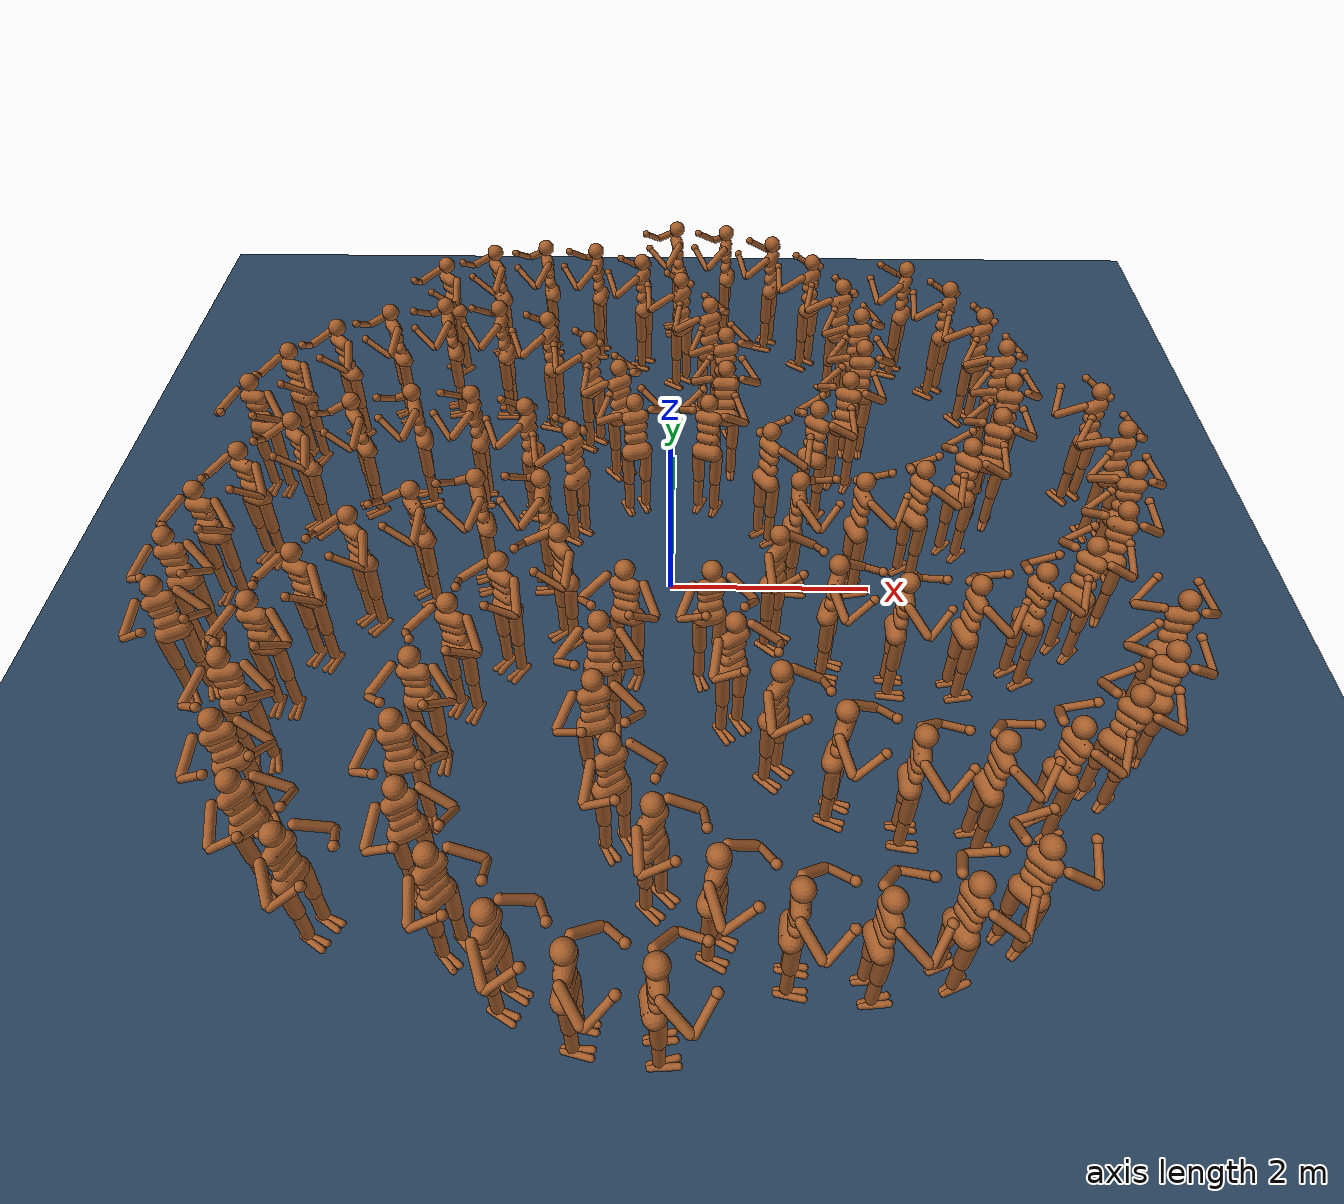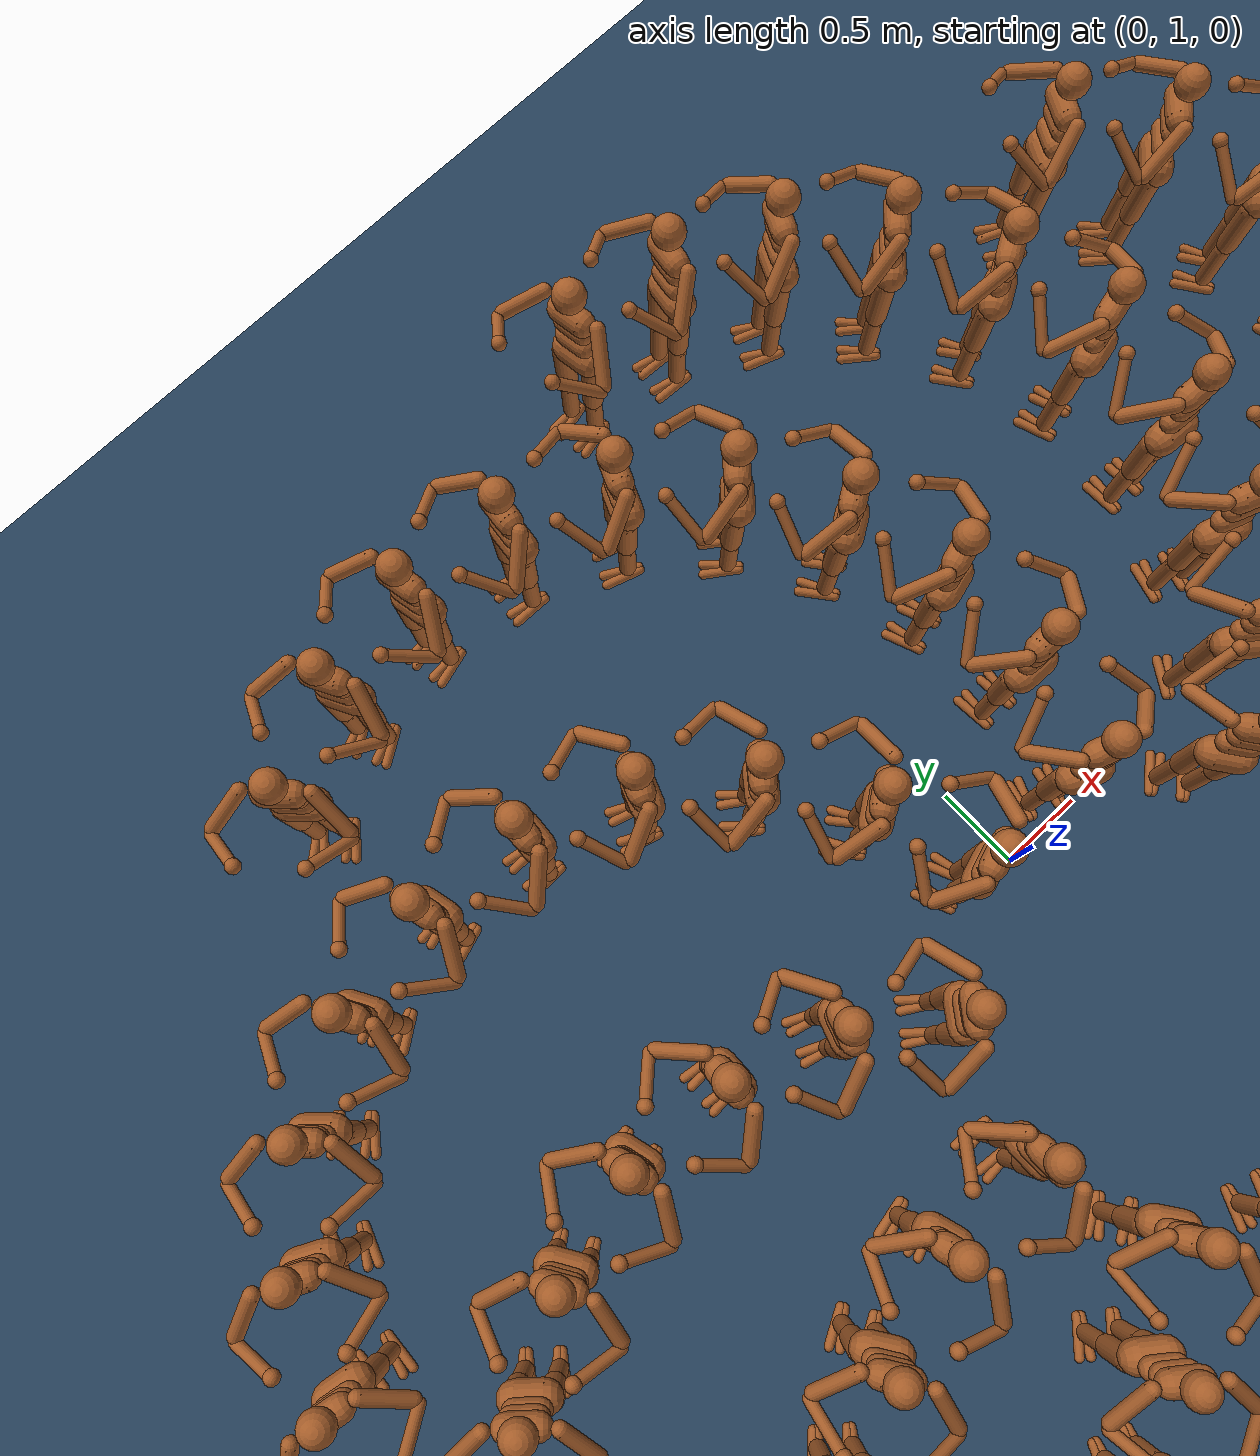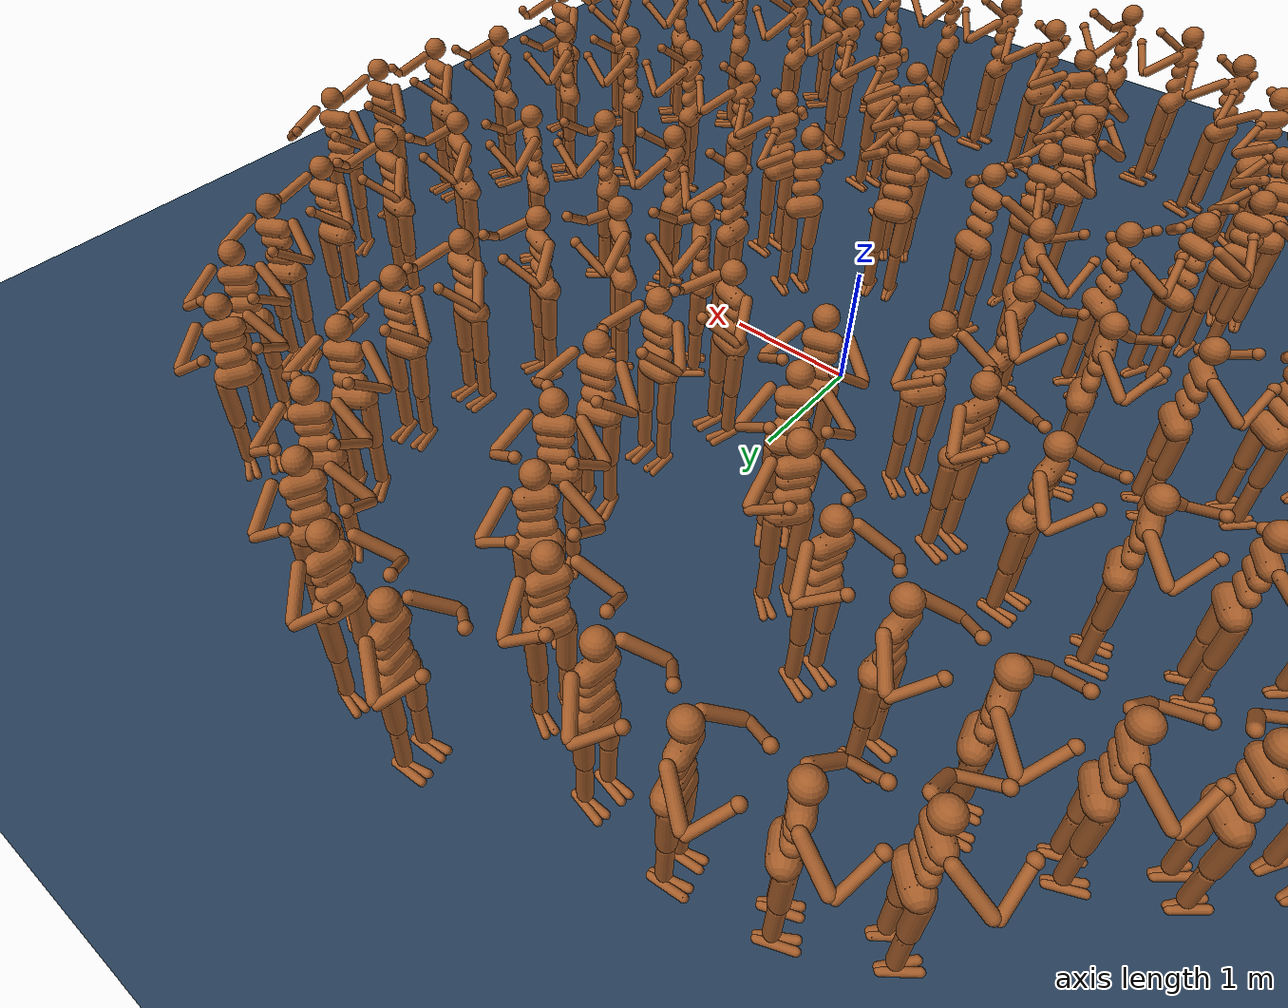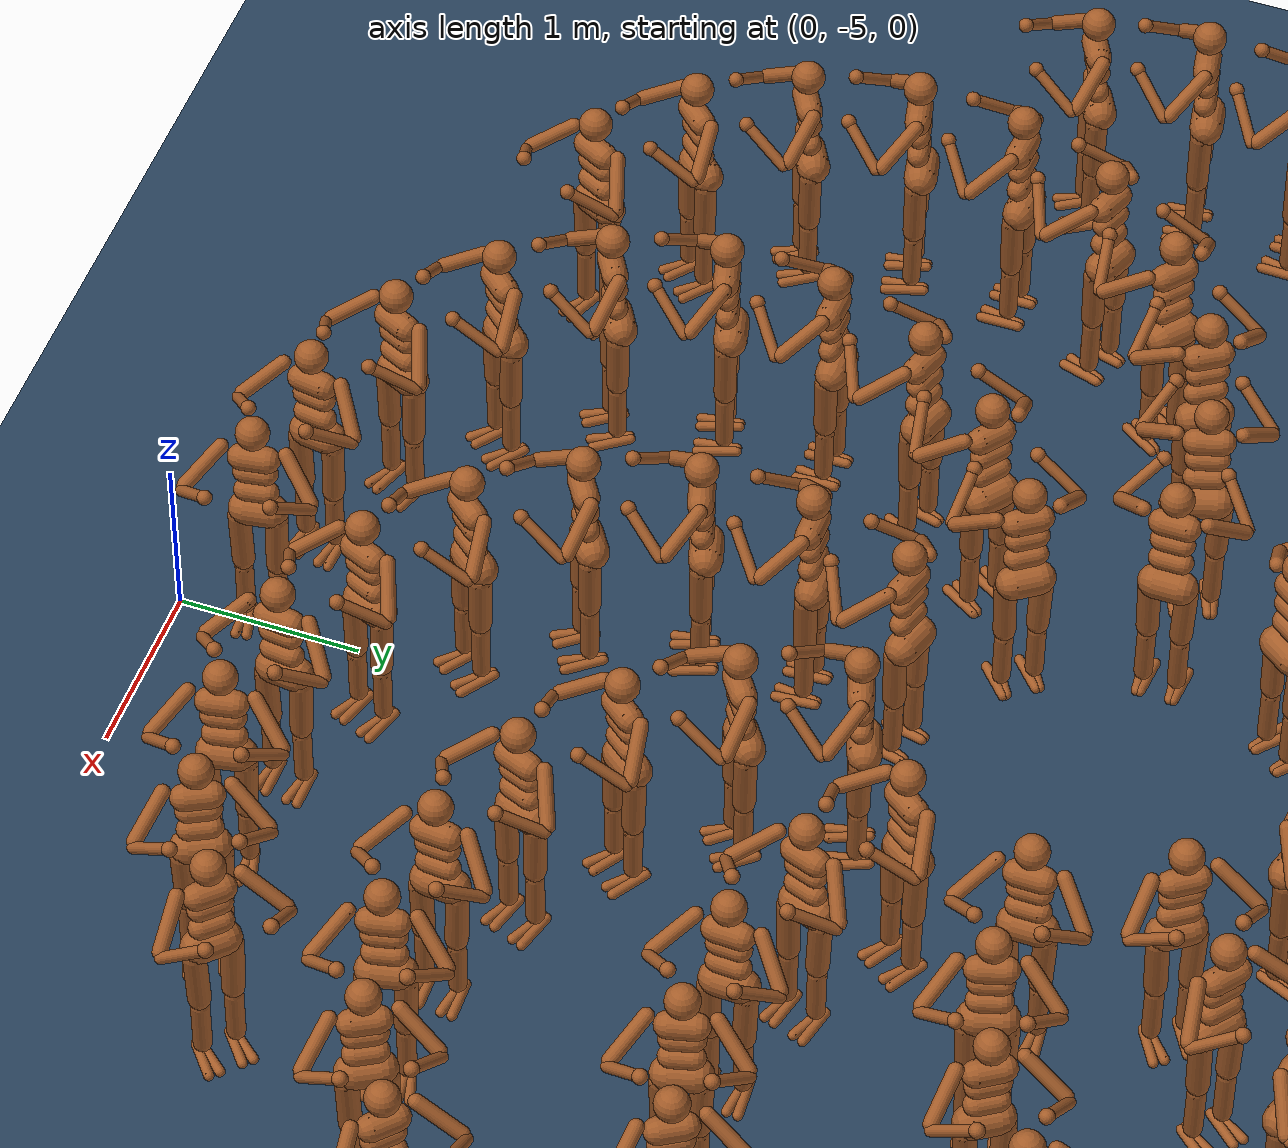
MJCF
<mujoco model="100 Humanoids">
  <compiler angle="radian"/>

  <option timestep="0.005">
    <flag island="disable"/>
  </option>

  <size memory="100M" nkey="4"/>

  <visual>
    <global offwidth="800" offheight="800"/>
    <quality numslices="16" numstacks="8"/>
    <map force="0.1" zfar="30"/>
    <rgba haze="0.15 0.25 0.35 1"/>
  </visual>

  <default>
    <default class="_main">
      <general ctrllimited="true" ctrlrange="-1 1"/>
      <default class="_body">
        <joint solimplimit="0 0.99 0.01" stiffness="1" limited="true" armature="0.01" damping="0.2"/>
        <geom type="capsule" condim="1" group="1" friction="0.7" solref="0.015" solimp="0.9 0.99 0.003" material="body"/>
        <default class="_thigh">
          <geom size="0.06 0 0"/>
        </default>
        <default class="_shin">
          <geom size="0.049 0 0"/>
        </default>
        <default class="_foot">
          <geom size="0.027 0 0"/>
          <default class="_foot1"/>
          <default class="_foot2"/>
        </default>
        <default class="_arm_upper">
          <geom size="0.04 0 0"/>
        </default>
        <default class="_arm_lower">
          <geom size="0.031 0 0"/>
        </default>
        <default class="_hand">
          <geom size="0.04 0 0" type="sphere"/>
        </default>
        <default class="_joint_big">
          <joint stiffness="10" damping="5"/>
          <default class="_hip_x">
            <joint range="-30 10"/>
          </default>
          <default class="_hip_z">
            <joint range="-60 35"/>
          </default>
          <default class="_hip_y">
            <joint range="-150 20"/>
          </default>
          <default class="_joint_big_stiff">
            <joint stiffness="20"/>
          </default>
        </default>
        <default class="_knee">
          <joint range="-160 2"/>
        </default>
        <default class="_ankle">
          <joint range="-50 50"/>
          <default class="_ankle_y">
            <joint stiffness="6"/>
          </default>
          <default class="_ankle_x">
            <joint stiffness="3"/>
          </default>
        </default>
        <default class="_shoulder">
          <joint range="-85 60"/>
        </default>
        <default class="_elbow">
          <joint stiffness="0" range="-100 50"/>
        </default>
      </default>
    </default>
  </default>

  <asset>
    <texture type="skybox" colorspace="auto" builtin="gradient" rgb1="0.3 0.5 0.7" rgb2="0 0 0" width="512" height="3072"/>
    <texture type="2d" colorspace="auto" name="floor" builtin="checker" rgb1="0.1 0.2 0.3" rgb2="0.2 0.3 0.4" width="512" height="512"/>
    <texture type="skybox" colorspace="auto" builtin="gradient" rgb1="0.3 0.5 0.7" rgb2="0 0 0" width="32" height="192"/>
    <texture type="cube" colorspace="auto" name="_body" builtin="flat" mark="cross" rgb1="0.8 0.6 0.4" rgb2="0.8 0.6 0.4" markrgb="1 1 1" width="128" height="768"/>
    <texture type="2d" colorspace="auto" name="_grid" builtin="checker" rgb1="0.1 0.2 0.3" rgb2="0.2 0.3 0.4" width="512" height="512"/>
    <material name="floor" texture="floor" texuniform="true" reflectance="0.2"/>
    <material name="_body" texture="_body" texuniform="true" rgba="0.8 0.6 0.4 1"/>
    <material name="_grid" texture="_grid" texuniform="true" reflectance="0.2"/>
  </asset>

  <worldbody>
    <geom name="floor" size="10 10 0.05" type="plane" material="floor"/>
    <light pos="0 0 5" dir="0 0 -1" type="directional" diffuse="0.9 0.9 0.9" specular="0.1 0.1 0.1"/>
    <light name="spotlight" target="world" pos="-6 -6 4" dir="0 0 -1" cutoff="60" diffuse="1 1 1" mode="targetbodycom"/>
    <body name="_torso-00-00" childclass="_body" pos="1.2 0 1.282">
      <joint name="_root-00-00" type="free" solimplimit="0.9 0.95 0.001" stiffness="0" armature="0" damping="0"/>
      <geom name="_torso-00-00" size="0.07 0.07" quat="0.707107 0.707107 0 0" material="_body"/>
      <geom name="_waist_upper-00-00" size="0.06 0.06" pos="-0.01 0 -0.12" quat="0.707107 0.707107 0 0" material="_body"/>
      <camera name="_back-00-00" pos="-3 0 1" quat="0.601501 0.371748 -0.371748 -0.601501" mode="trackcom"/>
      <camera name="_side-00-00" pos="0 -3 1" quat="0.850651 0.525731 0 0" mode="trackcom"/>
      <body name="_head-00-00" pos="0 0 0.19">
        <geom name="_head-00-00" size="0.09" type="sphere" material="_body"/>
        <camera name="_egocentric-00-00" pos="0.09 0 0" quat="0.524286 0.474472 -0.474472 -0.524286" fovy="80"/>
      </body>
      <body name="_waist_lower-00-00" pos="-0.01 0 -0.26">
        <joint name="_abdomen_z-00-00" class="_joint_big_stiff" pos="0 0 0.065" axis="0 0 1" range="-0.785398 0.785398"/>
        <joint name="_abdomen_y-00-00" class="_joint_big" pos="0 0 0.065" axis="0 1 0" range="-1.309 0.523599"/>
        <geom name="_waist_lower-00-00" size="0.06 0.06" quat="0.707107 0.707107 0 0" material="_body"/>
        <body name="_pelvis-00-00" pos="0 0 -0.165">
          <joint name="_abdomen_x-00-00" class="_joint_big" pos="0 0 0.1" axis="1 0 0" range="-0.610865 0.610865"/>
          <geom name="_butt-00-00" size="0.09 0.07" pos="-0.02 0 0" quat="0.707107 0.707107 0 0" material="_body"/>
          <body name="_thigh_right-00-00" pos="0 -0.1 -0.04">
            <joint name="_hip_x_right-00-00" class="_hip_x" pos="0 0 0" axis="1 0 0" range="-0.523599 0.174533"/>
            <joint name="_hip_z_right-00-00" class="_hip_z" pos="0 0 0" axis="0 0 1" range="-1.0472 0.610865"/>
            <joint name="_hip_y_right-00-00" class="_hip_y" pos="0 0 0" axis="0 1 0" range="-2.61799 0.349066"/>
            <geom name="_thigh_right-00-00" class="_thigh" size="0.06 0.170074" pos="0 0.005 -0.17" quat="0.999892 0.0147011 0 0" material="_body"/>
            <body name="_shin_right-00-00" pos="0 0.01 -0.4">
              <joint name="_knee_right-00-00" class="_knee" pos="0 0 0.02" axis="0 -1 0" range="-2.79253 0.0349066"/>
              <geom name="_shin_right-00-00" class="_shin" size="0.049 0.15" pos="0 0 -0.15" material="_body"/>
              <body name="_foot_right-00-00" pos="0 0 -0.39">
                <joint name="_ankle_y_right-00-00" class="_ankle_y" pos="0 0 0.08" axis="0 1 0" range="-0.872665 0.872665"/>
                <joint name="_ankle_x_right-00-00" class="_ankle_x" pos="0 0 0.04" axis="0.894427 0 0.447214" range="-0.872665 0.872665"/>
                <geom name="_foot1_right-00-00" class="_foot1" size="0.027 0.105475" pos="0.035 -0.02 0" quat="0.707107 -0.0670402 -0.703922 0" material="_body"/>
                <geom name="_foot2_right-00-00" class="_foot2" size="0.027 0.105475" pos="0.035 0.02 0" quat="0.707107 0.0670402 -0.703922 0" material="_body"/>
              </body>
            </body>
          </body>
          <body name="_thigh_left-00-00" pos="0 0.1 -0.04">
            <joint name="_hip_x_left-00-00" class="_hip_x" pos="0 0 0" axis="-1 0 0" range="-0.523599 0.174533"/>
            <joint name="_hip_z_left-00-00" class="_hip_z" pos="0 0 0" axis="0 0 -1" range="-1.0472 0.610865"/>
            <joint name="_hip_y_left-00-00" class="_hip_y" pos="0 0 0" axis="0 1 0" range="-2.61799 0.349066"/>
            <geom name="_thigh_left-00-00" class="_thigh" size="0.06 0.170074" pos="0 -0.005 -0.17" quat="0.999892 -0.0147011 0 0" material="_body"/>
            <body name="_shin_left-00-00" pos="0 -0.01 -0.4">
              <joint name="_knee_left-00-00" class="_knee" pos="0 0 0.02" axis="0 -1 0" range="-2.79253 0.0349066"/>
              <geom name="_shin_left-00-00" class="_shin" size="0.049 0.15" pos="0 0 -0.15" material="_body"/>
              <body name="_foot_left-00-00" pos="0 0 -0.39">
                <joint name="_ankle_y_left-00-00" class="_ankle_y" pos="0 0 0.08" axis="0 1 0" range="-0.872665 0.872665"/>
                <joint name="_ankle_x_left-00-00" class="_ankle_x" pos="0 0 0.04" axis="-0.894427 0 -0.447214" range="-0.872665 0.872665"/>
                <geom name="_foot1_left-00-00" class="_foot1" size="0.027 0.105475" pos="0.035 -0.02 0" quat="0.707107 -0.0670402 -0.703922 0" material="_body"/>
                <geom name="_foot2_left-00-00" class="_foot2" size="0.027 0.105475" pos="0.035 0.02 0" quat="0.707107 0.0670402 -0.703922 0" material="_body"/>
              </body>
            </body>
          </body>
        </body>
      </body>
      <body name="_upper_arm_right-00-00" pos="0 -0.17 0.06">
        <joint name="_shoulder1_right-00-00" class="_shoulder" pos="0 0 0" axis="0.816497 0.408248 0.408248" range="-1.48353 1.0472"/>
        <joint name="_shoulder2_right-00-00" class="_shoulder" pos="0 0 0" axis="0 -0.707107 0.707107" range="-1.48353 1.0472"/>
        <geom name="_upper_arm_right-00-00" class="_arm_upper" size="0.04 0.138564" pos="0.08 -0.08 -0.08" quat="0.888074 -0.325058 -0.325058 0" material="_body"/>
        <body name="_lower_arm_right-00-00" pos="0.18 -0.18 -0.18">
          <joint name="_elbow_right-00-00" class="_elbow" pos="0 0 0" axis="0 -0.707107 0.707107" range="-1.74533 0.872665"/>
          <geom name="_lower_arm_right-00-00" class="_arm_lower" size="0.031 0.138564" pos="0.09 0.09 0.09" quat="0.459701 0.627963 -0.627963 0" material="_body"/>
          <body name="_hand_right-00-00" pos="0.18 0.18 0.18">
            <geom name="_hand_right-00-00" class="_hand" quat="0.888074 -0.325058 0.325058 0" material="_body"/>
          </body>
        </body>
      </body>
      <body name="_upper_arm_left-00-00" pos="0 0.17 0.06">
        <joint name="_shoulder1_left-00-00" class="_shoulder" pos="0 0 0" axis="-0.816497 0.408248 -0.408248" range="-1.48353 1.0472"/>
        <joint name="_shoulder2_left-00-00" class="_shoulder" pos="0 0 0" axis="0 -0.707107 -0.707107" range="-1.48353 1.0472"/>
        <geom name="_upper_arm_left-00-00" class="_arm_upper" size="0.04 0.138564" pos="0.08 0.08 -0.08" quat="0.888074 0.325058 -0.325058 0" material="_body"/>
        <body name="_lower_arm_left-00-00" pos="0.18 0.18 -0.18">
          <joint name="_elbow_left-00-00" class="_elbow" pos="0 0 0" axis="0 -0.707107 -0.707107" range="-1.74533 0.872665"/>
          <geom name="_lower_arm_left-00-00" class="_arm_lower" size="0.031 0.138564" pos="0.09 -0.09 0.09" quat="0.459701 -0.627963 -0.627963 0" material="_body"/>
          <body name="_hand_left-00-00" pos="0.18 -0.18 0.18">
            <geom name="_hand_left-00-00" class="_hand" quat="0.888074 0.325058 0.325058 0" material="_body"/>
          </body>
        </body>
      </body>
    </body>
    <body name="_torso-01-00" childclass="_body" pos="1.8 0 1.282" quat="0.989016 0 0 0.147809">
      <joint name="_root-01-00" type="free" solimplimit="0.9 0.95 0.001" stiffness="0" armature="0" damping="0"/>
      <geom name="_torso-01-00" size="0.07 0.07" quat="0.707107 0.707107 0 0" material="_body"/>
      <geom name="_waist_upper-01-00" size="0.06 0.06" pos="-0.01 0 -0.12" quat="0.707107 0.707107 0 0" material="_body"/>
      <camera name="_back-01-00" pos="-3 0 1" quat="0.601501 0.371748 -0.371748 -0.601501" mode="trackcom"/>
      <camera name="_side-01-00" pos="0 -3 1" quat="0.850651 0.525731 0 0" mode="trackcom"/>
      <body name="_head-01-00" pos="0 0 0.19">
        <geom name="_head-01-00" size="0.09" type="sphere" material="_body"/>
        <camera name="_egocentric-01-00" pos="0.09 0 0" quat="0.524286 0.474472 -0.474472 -0.524286" fovy="80"/>
      </body>
      <body name="_waist_lower-01-00" pos="-0.01 0 -0.26">
        <joint name="_abdomen_z-01-00" class="_joint_big_stiff" pos="0 0 0.065" axis="0 0 1" range="-0.785398 0.785398"/>
        <joint name="_abdomen_y-01-00" class="_joint_big" pos="0 0 0.065" axis="0 1 0" range="-1.309 0.523599"/>
        <geom name="_waist_lower-01-00" size="0.06 0.06" quat="0.707107 0.707107 0 0" material="_body"/>
        <body name="_pelvis-01-00" pos="0 0 -0.165">
          <joint name="_abdomen_x-01-00" class="_joint_big" pos="0 0 0.1" axis="1 0 0" range="-0.610865 0.610865"/>
          <geom name="_butt-01-00" size="0.09 0.07" pos="-0.02 0 0" quat="0.707107 0.707107 0 0" material="_body"/>
          <body name="_thigh_right-01-00" pos="0 -0.1 -0.04">
            <joint name="_hip_x_right-01-00" class="_hip_x" pos="0 0 0" axis="1 0 0" range="-0.523599 0.174533"/>
            <joint name="_hip_z_right-01-00" class="_hip_z" pos="0 0 0" axis="0 0 1" range="-1.0472 0.610865"/>
            <joint name="_hip_y_right-01-00" class="_hip_y" pos="0 0 0" axis="0 1 0" range="-2.61799 0.349066"/>
            <geom name="_thigh_right-01-00" class="_thigh" size="0.06 0.170074" pos="0 0.005 -0.17" quat="0.999892 0.0147011 0 0" material="_body"/>
            <body name="_shin_right-01-00" pos="0 0.01 -0.4">
              <joint name="_knee_right-01-00" class="_knee" pos="0 0 0.02" axis="0 -1 0" range="-2.79253 0.0349066"/>
              <geom name="_shin_right-01-00" class="_shin" size="0.049 0.15" pos="0 0 -0.15" material="_body"/>
              <body name="_foot_right-01-00" pos="0 0 -0.39">
                <joint name="_ankle_y_right-01-00" class="_ankle_y" pos="0 0 0.08" axis="0 1 0" range="-0.872665 0.872665"/>
                <joint name="_ankle_x_right-01-00" class="_ankle_x" pos="0 0 0.04" axis="0.894427 0 0.447214" range="-0.872665 0.872665"/>
                <geom name="_foot1_right-01-00" class="_foot1" size="0.027 0.105475" pos="0.035 -0.02 0" quat="0.707107 -0.0670402 -0.703922 0" material="_body"/>
                <geom name="_foot2_right-01-00" class="_foot2" size="0.027 0.105475" pos="0.035 0.02 0" quat="0.707107 0.0670402 -0.703922 0" material="_body"/>
              </body>
            </body>
          </body>
          <body name="_thigh_left-01-00" pos="0 0.1 -0.04">
            <joint name="_hip_x_left-01-00" class="_hip_x" pos="0 0 0" axis="-1 0 0" range="-0.523599 0.174533"/>
            <joint name="_hip_z_left-01-00" class="_hip_z" pos="0 0 0" axis="0 0 -1" range="-1.0472 0.610865"/>
            <joint name="_hip_y_left-01-00" class="_hip_y" pos="0 0 0" axis="0 1 0" range="-2.61799 0.349066"/>
            <geom name="_thigh_left-01-00" class="_thigh" size="0.06 0.170074" pos="0 -0.005 -0.17" quat="0.999892 -0.0147011 0 0" material="_body"/>
            <body name="_shin_left-01-00" pos="0 -0.01 -0.4">
              <joint name="_knee_left-01-00" class="_knee" pos="0 0 0.02" axis="0 -1 0" range="-2.79253 0.0349066"/>
              <geom name="_shin_left-01-00" class="_shin" size="0.049 0.15" pos="0 0 -0.15" material="_body"/>
              <body name="_foot_left-01-00" pos="0 0 -0.39">
                <joint name="_ankle_y_left-01-00" class="_ankle_y" pos="0 0 0.08" axis="0 1 0" range="-0.872665 0.872665"/>
                <joint name="_ankle_x_left-01-00" class="_ankle_x" pos="0 0 0.04" axis="-0.894427 0 -0.447214" range="-0.872665 0.872665"/>
                <geom name="_foot1_left-01-00" class="_foot1" size="0.027 0.105475" pos="0.035 -0.02 0" quat="0.707107 -0.0670402 -0.703922 0" material="_body"/>
                <geom name="_foot2_left-01-00" class="_foot2" size="0.027 0.105475" pos="0.035 0.02 0" quat="0.707107 0.0670402 -0.703922 0" material="_body"/>
              </body>
            </body>
          </body>
        </body>
      </body>
      <body name="_upper_arm_right-01-00" pos="0 -0.17 0.06">
        <joint name="_shoulder1_right-01-00" class="_shoulder" pos="0 0 0" axis="0.816497 0.408248 0.408248" range="-1.48353 1.0472"/>
        <joint name="_shoulder2_right-01-00" class="_shoulder" pos="0 0 0" axis="0 -0.707107 0.707107" range="-1.48353 1.0472"/>
        <geom name="_upper_arm_right-01-00" class="_arm_upper" size="0.04 0.138564" pos="0.08 -0.08 -0.08" quat="0.888074 -0.325058 -0.325058 0" material="_body"/>
        <body name="_lower_arm_right-01-00" pos="0.18 -0.18 -0.18">
          <joint name="_elbow_right-01-00" class="_elbow" pos="0 0 0" axis="0 -0.707107 0.707107" range="-1.74533 0.872665"/>
          <geom name="_lower_arm_right-01-00" class="_arm_lower" size="0.031 0.138564" pos="0.09 0.09 0.09" quat="0.459701 0.627963 -0.627963 0" material="_body"/>
          <body name="_hand_right-01-00" pos="0.18 0.18 0.18">
            <geom name="_hand_right-01-00" class="_hand" quat="0.888074 -0.325058 0.325058 0" material="_body"/>
          </body>
        </body>
      </body>
      <body name="_upper_arm_left-01-00" pos="0 0.17 0.06">
        <joint name="_shoulder1_left-01-00" class="_shoulder" pos="0 0 0" axis="-0.816497 0.408248 -0.408248" range="-1.48353 1.0472"/>
        <joint name="_shoulder2_left-01-00" class="_shoulder" pos="0 0 0" axis="0 -0.707107 -0.707107" range="-1.48353 1.0472"/>
        <geom name="_upper_arm_left-01-00" class="_arm_upper" size="0.04 0.138564" pos="0.08 0.08 -0.08" quat="0.888074 0.325058 -0.325058 0" material="_body"/>
        <body name="_lower_arm_left-01-00" pos="0.18 0.18 -0.18">
          <joint name="_elbow_left-01-00" class="_elbow" pos="0 0 0" axis="0 -0.707107 -0.707107" range="-1.74533 0.872665"/>
          <geom name="_lower_arm_left-01-00" class="_arm_lower" size="0.031 0.138564" pos="0.09 -0.09 0.09" quat="0.459701 -0.627963 -0.627963 0" material="_body"/>
          <body name="_hand_left-01-00" pos="0.18 -0.18 0.18">
            <geom name="_hand_left-01-00" class="_hand" quat="0.888074 0.325058 0.325058 0" material="_body"/>
          </body>
        </body>
      </body>
    </body>
    <body name="_torso-02-00" childclass="_body" pos="2.37378 0.175423 1.282" quat="0.956305 0 0 0.292372">
      <joint name="_root-02-00" type="free" solimplimit="0.9 0.95 0.001" stiffness="0" armature="0" damping="0"/>
      <geom name="_torso-02-00" size="0.07 0.07" quat="0.707107 0.707107 0 0" material="_body"/>
      <geom name="_waist_upper-02-00" size="0.06 0.06" pos="-0.01 0 -0.12" quat="0.707107 0.707107 0 0" material="_body"/>
      <camera name="_back-02-00" pos="-3 0 1" quat="0.601501 0.371748 -0.371748 -0.601501" mode="trackcom"/>
      <camera name="_side-02-00" pos="0 -3 1" quat="0.850651 0.525731 0 0" mode="trackcom"/>
      <body name="_head-02-00" pos="0 0 0.19">
        <geom name="_head-02-00" size="0.09" type="sphere" material="_body"/>
        <camera name="_egocentric-02-00" pos="0.09 0 0" quat="0.524286 0.474472 -0.474472 -0.524286" fovy="80"/>
      </body>
      <body name="_waist_lower-02-00" pos="-0.01 0 -0.26">
        <joint name="_abdomen_z-02-00" class="_joint_big_stiff" pos="0 0 0.065" axis="0 0 1" range="-0.785398 0.785398"/>
        <joint name="_abdomen_y-02-00" class="_joint_big" pos="0 0 0.065" axis="0 1 0" range="-1.309 0.523599"/>
        <geom name="_waist_lower-02-00" size="0.06 0.06" quat="0.707107 0.707107 0 0" material="_body"/>
        <body name="_pelvis-02-00" pos="0 0 -0.165">
          <joint name="_abdomen_x-02-00" class="_joint_big" pos="0 0 0.1" axis="1 0 0" range="-0.610865 0.610865"/>
          <geom name="_butt-02-00" size="0.09 0.07" pos="-0.02 0 0" quat="0.707107 0.707107 0 0" material="_body"/>
          <body name="_thigh_right-02-00" pos="0 -0.1 -0.04">
            <joint name="_hip_x_right-02-00" class="_hip_x" pos="0 0 0" axis="1 0 0" range="-0.523599 0.174533"/>
            <joint name="_hip_z_right-02-00" class="_hip_z" pos="0 0 0" axis="0 0 1" range="-1.0472 0.610865"/>
            <joint name="_hip_y_right-02-00" class="_hip_y" pos="0 0 0" axis="0 1 0" range="-2.61799 0.349066"/>
            <geom name="_thigh_right-02-00" class="_thigh" size="0.06 0.170074" pos="0 0.005 -0.17" quat="0.999892 0.0147011 0 0" material="_body"/>
            <body name="_shin_right-02-00" pos="0 0.01 -0.4">
              <joint name="_knee_right-02-00" class="_knee" pos="0 0 0.02" axis="0 -1 0" range="-2.79253 0.0349066"/>
              <geom name="_shin_right-02-00" class="_shin" size="0.049 0.15" pos="0 0 -0.15" material="_body"/>
              <body name="_foot_right-02-00" pos="0 0 -0.39">
                <joint name="_ankle_y_right-02-00" class="_ankle_y" pos="0 0 0.08" axis="0 1 0" range="-0.872665 0.872665"/>
                <joint name="_ankle_x_right-02-00" class="_ankle_x" pos="0 0 0.04" axis="0.894427 0 0.447214" range="-0.872665 0.872665"/>
                <geom name="_foot1_right-02-00" class="_foot1" size="0.027 0.105475" pos="0.035 -0.02 0" quat="0.707107 -0.0670402 -0.703922 0" material="_body"/>
                <geom name="_foot2_right-02-00" class="_foot2" size="0.027 0.105475" pos="0.035 0.02 0" quat="0.707107 0.0670402 -0.703922 0" material="_body"/>
              </body>
            </body>
          </body>
          <body name="_thigh_left-02-00" pos="0 0.1 -0.04">
            <joint name="_hip_x_left-02-00" class="_hip_x" pos="0 0 0" axis="-1 0 0" range="-0.523599 0.174533"/>
            <joint name="_hip_z_left-02-00" class="_hip_z" pos="0 0 0" axis="0 0 -1" range="-1.0472 0.610865"/>
            <joint name="_hip_y_left-02-00" class="_hip_y" pos="0 0 0" axis="0 1 0" range="-2.61799 0.349066"/>
            <geom name="_thigh_left-02-00" class="_thigh" size="0.06 0.170074" pos="0 -0.005 -0.17" quat="0.999892 -0.0147011 0 0" material="_body"/>
            <body name="_shin_left-02-00" pos="0 -0.01 -0.4">
              <joint name="_knee_left-02-00" class="_knee" pos="0 0 0.02" axis="0 -1 0" range="-2.79253 0.0349066"/>
              <geom name="_shin_left-02-00" class="_shin" size="0.049 0.15" pos="0 0 -0.15" material="_body"/>
              <body name="_foot_left-02-00" pos="0 0 -0.39">
                <joint name="_ankle_y_left-02-00" class="_ankle_y" pos="0 0 0.08" axis="0 1 0" range="-0.872665 0.872665"/>
                <joint name="_ankle_x_left-02-00" class="_ankle_x" pos="0 0 0.04" axis="-0.894427 0 -0.447214" range="-0.872665 0.872665"/>
                <geom name="_foot1_left-02-00" class="_foot1" size="0.027 0.105475" pos="0.035 -0.02 0" quat="0.707107 -0.0670402 -0.703922 0" material="_body"/>
                <geom name="_foot2_left-02-00" class="_foot2" size="0.027 0.105475" pos="0.035 0.02 0" quat="0.707107 0.0670402 -0.703922 0" material="_body"/>
              </body>
            </body>
          </body>
        </body>
      </body>
      <body name="_upper_arm_right-02-00" pos="0 -0.17 0.06">
        <joint name="_shoulder1_right-02-00" class="_shoulder" pos="0 0 0" axis="0.816497 0.408248 0.408248" range="-1.48353 1.0472"/>
        <joint name="_shoulder2_right-02-00" class="_shoulder" pos="0 0 0" axis="0 -0.707107 0.707107" range="-1.48353 1.0472"/>
        <geom name="_upper_arm_right-02-00" class="_arm_upper" size="0.04 0.138564" pos="0.08 -0.08 -0.08" quat="0.888074 -0.325058 -0.325058 0" material="_body"/>
        <body name="_lower_arm_right-02-00" pos="0.18 -0.18 -0.18">
          <joint name="_elbow_right-02-00" class="_elbow" pos="0 0 0" axis="0 -0.707107 0.707107" range="-1.74533 0.872665"/>
          <geom name="_lower_arm_right-02-00" class="_arm_lower" size="0.031 0.138564" pos="0.09 0.09 0.09" quat="0.459701 0.627963 -0.627963 0" material="_body"/>
          <body name="_hand_right-02-00" pos="0.18 0.18 0.18">
            <geom name="_hand_right-02-00" class="_hand" quat="0.888074 -0.325058 0.325058 0" material="_body"/>
          </body>
        </body>
      </body>
      <body name="_upper_arm_left-02-00" pos="0 0.17 0.06">
        <joint name="_shoulder1_left-02-00" class="_shoulder" pos="0 0 0" axis="-0.816497 0.408248 -0.408248" range="-1.48353 1.0472"/>
        <joint name="_shoulder2_left-02-00" class="_shoulder" pos="0 0 0" axis="0 -0.707107 -0.707107" range="-1.48353 1.0472"/>
        <geom name="_upper_arm_left-02-00" class="_arm_upper" size="0.04 0.138564" pos="0.08 0.08 -0.08" quat="0.888074 0.325058 -0.325058 0" material="_body"/>
        <body name="_lower_arm_left-02-00" pos="0.18 0.18 -0.18">
          <joint name="_elbow_left-02-00" class="_elbow" pos="0 0 0" axis="0 -0.707107 -0.707107" range="-1.74533 0.872665"/>
          <geom name="_lower_arm_left-02-00" class="_arm_lower" size="0.031 0.138564" pos="0.09 -0.09 0.09" quat="0.459701 -0.627963 -0.627963 0" material="_body"/>
          <body name="_hand_left-02-00" pos="0.18 -0.18 0.18">
            <geom name="_hand_left-02-00" class="_hand" quat="0.888074 0.325058 0.325058 0" material="_body"/>
          </body>
        </body>
      </body>
    </body>
    <body name="_torso-03-00" childclass="_body" pos="2.87121 0.510939 1.282" quat="0.902585 0 0 0.430511">
      <joint name="_root-03-00" type="free" solimplimit="0.9 0.95 0.001" stiffness="0" armature="0" damping="0"/>
      <geom name="_torso-03-00" size="0.07 0.07" quat="0.707107 0.707107 0 0" material="_body"/>
      <geom name="_waist_upper-03-00" size="0.06 0.06" pos="-0.01 0 -0.12" quat="0.707107 0.707107 0 0" material="_body"/>
      <camera name="_back-03-00" pos="-3 0 1" quat="0.601501 0.371748 -0.371748 -0.601501" mode="trackcom"/>
      <camera name="_side-03-00" pos="0 -3 1" quat="0.850651 0.525731 0 0" mode="trackcom"/>
      <body name="_head-03-00" pos="0 0 0.19">
        <geom name="_head-03-00" size="0.09" type="sphere" material="_body"/>
        <camera name="_egocentric-03-00" pos="0.09 0 0" quat="0.524286 0.474472 -0.474472 -0.524286" fovy="80"/>
      </body>
      <body name="_waist_lower-03-00" pos="-0.01 0 -0.26">
        <joint name="_abdomen_z-03-00" class="_joint_big_stiff" pos="0 0 0.065" axis="0 0 1" range="-0.785398 0.785398"/>
        <joint name="_abdomen_y-03-00" class="_joint_big" pos="0 0 0.065" axis="0 1 0" range="-1.309 0.523599"/>
        <geom name="_waist_lower-03-00" size="0.06 0.06" quat="0.707107 0.707107 0 0" material="_body"/>
        <body name="_pelvis-03-00" pos="0 0 -0.165">
          <joint name="_abdomen_x-03-00" class="_joint_big" pos="0 0 0.1" axis="1 0 0" range="-0.610865 0.610865"/>
          <geom name="_butt-03-00" size="0.09 0.07" pos="-0.02 0 0" quat="0.707107 0.707107 0 0" material="_body"/>
          <body name="_thigh_right-03-00" pos="0 -0.1 -0.04">
            <joint name="_hip_x_right-03-00" class="_hip_x" pos="0 0 0" axis="1 0 0" range="-0.523599 0.174533"/>
            <joint name="_hip_z_right-03-00" class="_hip_z" pos="0 0 0" axis="0 0 1" range="-1.0472 0.610865"/>
            <joint name="_hip_y_right-03-00" class="_hip_y" pos="0 0 0" axis="0 1 0" range="-2.61799 0.349066"/>
            <geom name="_thigh_right-03-00" class="_thigh" size="0.06 0.170074" pos="0 0.005 -0.17" quat="0.999892 0.0147011 0 0" material="_body"/>
            <body name="_shin_right-03-00" pos="0 0.01 -0.4">
              <joint name="_knee_right-03-00" class="_knee" pos="0 0 0.02" axis="0 -1 0" range="-2.79253 0.0349066"/>
              <geom name="_shin_right-03-00" class="_shin" size="0.049 0.15" pos="0 0 -0.15" material="_body"/>
              <body name="_foot_right-03-00" pos="0 0 -0.39">
                <joint name="_ankle_y_right-03-00" class="_ankle_y" pos="0 0 0.08" axis="0 1 0" range="-0.872665 0.872665"/>
                <joint name="_ankle_x_right-03-00" class="_ankle_x" pos="0 0 0.04" axis="0.894427 0 0.447214" range="-0.872665 0.872665"/>
                <geom name="_foot1_right-03-00" class="_foot1" size="0.027 0.105475" pos="0.035 -0.02 0" quat="0.707107 -0.0670402 -0.703922 0" material="_body"/>
                <geom name="_foot2_right-03-00" class="_foot2" size="0.027 0.105475" pos="0.035 0.02 0" quat="0.707107 0.0670402 -0.703922 0" material="_body"/>
              </body>
            </body>
          </body>
          <body name="_thigh_left-03-00" pos="0 0.1 -0.04">
            <joint name="_hip_x_left-03-00" class="_hip_x" pos="0 0 0" axis="-1 0 0" range="-0.523599 0.174533"/>
            <joint name="_hip_z_left-03-00" class="_hip_z" pos="0 0 0" axis="0 0 -1" range="-1.0472 0.610865"/>
            <joint name="_hip_y_left-03-00" class="_hip_y" pos="0 0 0" axis="0 1 0" range="-2.61799 0.349066"/>
            <geom name="_thigh_left-03-00" class="_thigh" size="0.06 0.170074" pos="0 -0.005 -0.17" quat="0.999892 -0.0147011 0 0" material="_body"/>
            <body name="_shin_left-03-00" pos="0 -0.01 -0.4">
              <joint name="_knee_left-03-00" class="_knee" pos="0 0 0.02" axis="0 -1 0" range="-2.79253 0.0349066"/>
              <geom name="_shin_left-03-00" class="_shin" size="0.049 0.15" pos="0 0 -0.15" material="_body"/>
              <body name="_foot_left-03-00" pos="0 0 -0.39">
                <joint name="_ankle_y_left-03-00" class="_ankle_y" pos="0 0 0.08" axis="0 1 0" range="-0.872665 0.872665"/>
                <joint name="_ankle_x_left-03-00" class="_ankle_x" pos="0 0 0.04" axis="-0.894427 0 -0.447214" range="-0.872665 0.872665"/>
                <geom name="_foot1_left-03-00" class="_foot1" size="0.027 0.105475" pos="0.035 -0.02 0" quat="0.707107 -0.0670402 -0.703922 0" material="_body"/>
                <geom name="_foot2_left-03-00" class="_foot2" size="0.027 0.105475" pos="0.035 0.02 0" quat="0.707107 0.0670402 -0.703922 0" material="_body"/>
              </body>
            </body>
          </body>
        </body>
      </body>
      <body name="_upper_arm_right-03-00" pos="0 -0.17 0.06">
        <joint name="_shoulder1_right-03-00" class="_shoulder" pos="0 0 0" axis="0.816497 0.408248 0.408248" range="-1.48353 1.0472"/>
        <joint name="_shoulder2_right-03-00" class="_shoulder" pos="0 0 0" axis="0 -0.707107 0.707107" range="-1.48353 1.0472"/>
        <geom name="_upper_arm_right-03-00" class="_arm_upper" size="0.04 0.138564" pos="0.08 -0.08 -0.08" quat="0.888074 -0.325058 -0.325058 0" material="_body"/>
        <body name="_lower_arm_right-03-00" pos="0.18 -0.18 -0.18">
          <joint name="_elbow_right-03-00" class="_elbow" pos="0 0 0" axis="0 -0.707107 0.707107" range="-1.74533 0.872665"/>
          <geom name="_lower_arm_right-03-00" class="_arm_lower" size="0.031 0.138564" pos="0.09 0.09 0.09" quat="0.459701 0.627963 -0.627963 0" material="_body"/>
          <body name="_hand_right-03-00" pos="0.18 0.18 0.18">
            <geom name="_hand_right-03-00" class="_hand" quat="0.888074 -0.325058 0.325058 0" material="_body"/>
          </body>
        </body>
      </body>
      <body name="_upper_arm_left-03-00" pos="0 0.17 0.06">
        <joint name="_shoulder1_left-03-00" class="_shoulder" pos="0 0 0" axis="-0.816497 0.408248 -0.408248" range="-1.48353 1.0472"/>
        <joint name="_shoulder2_left-03-00" class="_shoulder" pos="0 0 0" axis="0 -0.707107 -0.707107" range="-1.48353 1.0472"/>
        <geom name="_upper_arm_left-03-00" class="_arm_upper" size="0.04 0.138564" pos="0.08 0.08 -0.08" quat="0.888074 0.325058 -0.325058 0" material="_body"/>
        <body name="_lower_arm_left-03-00" pos="0.18 0.18 -0.18">
          <joint name="_elbow_left-03-00" class="_elbow" pos="0 0 0" axis="0 -0.707107 -0.707107" range="-1.74533 0.872665"/>
          <geom name="_lower_arm_left-03-00" class="_arm_lower" size="0.031 0.138564" pos="0.09 -0.09 0.09" quat="0.459701 -0.627963 -0.627963 0" material="_body"/>
          <body name="_hand_left-03-00" pos="0.18 -0.18 0.18">
            <geom name="_hand_left-03-00" class="_hand" quat="0.888074 0.325058 0.325058 0" material="_body"/>
          </body>
        </body>
      </body>
    </body>
    <body name="_torso-04-00" childclass="_body" pos="3.2488 0.977226 1.282" quat="0.829038 0 0 0.559193">
      <joint name="_root-04-00" type="free" solimplimit="0.9 0.95 0.001" stiffness="0" armature="0" damping="0"/>
      <geom name="_torso-04-00" size="0.07 0.07" quat="0.707107 0.707107 0 0" material="_body"/>
      <geom name="_waist_upper-04-00" size="0.06 0.06" pos="-0.01 0 -0.12" quat="0.707107 0.707107 0 0" material="_body"/>
      <camera name="_back-04-00" pos="-3 0 1" quat="0.601501 0.371748 -0.371748 -0.601501" mode="trackcom"/>
      <camera name="_side-04-00" pos="0 -3 1" quat="0.850651 0.525731 0 0" mode="trackcom"/>
      <body name="_head-04-00" pos="0 0 0.19">
        <geom name="_head-04-00" size="0.09" type="sphere" material="_body"/>
        <camera name="_egocentric-04-00" pos="0.09 0 0" quat="0.524286 0.474472 -0.474472 -0.524286" fovy="80"/>
      </body>
      <body name="_waist_lower-04-00" pos="-0.01 0 -0.26">
        <joint name="_abdomen_z-04-00" class="_joint_big_stiff" pos="0 0 0.065" axis="0 0 1" range="-0.785398 0.785398"/>
        <joint name="_abdomen_y-04-00" class="_joint_big" pos="0 0 0.065" axis="0 1 0" range="-1.309 0.523599"/>
        <geom name="_waist_lower-04-00" size="0.06 0.06" quat="0.707107 0.707107 0 0" material="_body"/>
        <body name="_pelvis-04-00" pos="0 0 -0.165">
          <joint name="_abdomen_x-04-00" class="_joint_big" pos="0 0 0.1" axis="1 0 0" range="-0.610865 0.610865"/>
          <geom name="_butt-04-00" size="0.09 0.07" pos="-0.02 0 0" quat="0.707107 0.707107 0 0" material="_body"/>
          <body name="_thigh_right-04-00" pos="0 -0.1 -0.04">
            <joint name="_hip_x_right-04-00" class="_hip_x" pos="0 0 0" axis="1 0 0" range="-0.523599 0.174533"/>
            <joint name="_hip_z_right-04-00" class="_hip_z" pos="0 0 0" axis="0 0 1" range="-1.0472 0.610865"/>
            <joint name="_hip_y_right-04-00" class="_hip_y" pos="0 0 0" axis="0 1 0" range="-2.61799 0.349066"/>
            <geom name="_thigh_right-04-00" class="_thigh" size="0.06 0.170074" pos="0 0.005 -0.17" quat="0.999892 0.0147011 0 0" material="_body"/>
            <body name="_shin_right-04-00" pos="0 0.01 -0.4">
              <joint name="_knee_right-04-00" class="_knee" pos="0 0 0.02" axis="0 -1 0" range="-2.79253 0.0349066"/>
              <geom name="_shin_right-04-00" class="_shin" size="0.049 0.15" pos="0 0 -0.15" material="_body"/>
              <body name="_foot_right-04-00" pos="0 0 -0.39">
                <joint name="_ankle_y_right-04-00" class="_ankle_y" pos="0 0 0.08" axis="0 1 0" range="-0.872665 0.872665"/>
                <joint name="_ankle_x_right-04-00" class="_ankle_x" pos="0 0 0.04" axis="0.894427 0 0.447214" range="-0.872665 0.872665"/>
                <geom name="_foot1_right-04-00" class="_foot1" size="0.027 0.105475" pos="0.035 -0.02 0" quat="0.707107 -0.0670402 -0.703922 0" material="_body"/>
                <geom name="_foot2_right-04-00" class="_foot2" size="0.027 0.105475" pos="0.035 0.02 0" quat="0.707107 0.0670402 -0.703922 0" material="_body"/>
              </body>
            </body>
          </body>
          <body name="_thigh_left-04-00" pos="0 0.1 -0.04">
            <joint name="_hip_x_left-04-00" class="_hip_x" pos="0 0 0" axis="-1 0 0" range="-0.523599 0.174533"/>
            <joint name="_hip_z_left-04-00" class="_hip_z" pos="0 0 0" axis="0 0 -1" range="-1.0472 0.610865"/>
            <joint name="_hip_y_left-04-00" class="_hip_y" pos="0 0 0" axis="0 1 0" range="-2.61799 0.349066"/>
            <geom name="_thigh_left-04-00" class="_thigh" size="0.06 0.170074" pos="0 -0.005 -0.17" quat="0.999892 -0.0147011 0 0" material="_body"/>
            <body name="_shin_left-04-00" pos="0 -0.01 -0.4">
              <joint name="_knee_left-04-00" class="_knee" pos="0 0 0.02" axis="0 -1 0" range="-2.79253 0.0349066"/>
              <geom name="_shin_left-04-00" class="_shin" size="0.049 0.15" pos="0 0 -0.15" material="_body"/>
              <body name="_foot_left-04-00" pos="0 0 -0.39">
                <joint name="_ankle_y_left-04-00" class="_ankle_y" pos="0 0 0.08" axis="0 1 0" range="-0.872665 0.872665"/>
                <joint name="_ankle_x_left-04-00" class="_ankle_x" pos="0 0 0.04" axis="-0.894427 0 -0.447214" range="-0.872665 0.872665"/>
                <geom name="_foot1_left-04-00" class="_foot1" size="0.027 0.105475" pos="0.035 -0.02 0" quat="0.707107 -0.0670402 -0.703922 0" material="_body"/>
                <geom name="_foot2_left-04-00" class="_foot2" size="0.027 0.105475" pos="0.035 0.02 0" quat="0.707107 0.0670402 -0.703922 0" material="_body"/>
              </body>
            </body>
          </body>
        </body>
      </body>
      <body name="_upper_arm_right-04-00" pos="0 -0.17 0.06">
        <joint name="_shoulder1_right-04-00" class="_shoulder" pos="0 0 0" axis="0.816497 0.408248 0.408248" range="-1.48353 1.0472"/>
        <joint name="_shoulder2_right-04-00" class="_shoulder" pos="0 0 0" axis="0 -0.707107 0.707107" range="-1.48353 1.0472"/>
        <geom name="_upper_arm_right-04-00" class="_arm_upper" size="0.04 0.138564" pos="0.08 -0.08 -0.08" quat="0.888074 -0.325058 -0.325058 0" material="_body"/>
        <body name="_lower_arm_right-04-00" pos="0.18 -0.18 -0.18">
          <joint name="_elbow_right-04-00" class="_elbow" pos="0 0 0" axis="0 -0.707107 0.707107" range="-1.74533 0.872665"/>
          <geom name="_lower_arm_right-04-00" class="_arm_lower" size="0.031 0.138564" pos="0.09 0.09 0.09" quat="0.459701 0.627963 -0.627963 0" material="_body"/>
          <body name="_hand_right-04-00" pos="0.18 0.18 0.18">
            <geom name="_hand_right-04-00" class="_hand" quat="0.888074 -0.325058 0.325058 0" material="_body"/>
          </body>
        </body>
      </body>
      <body name="_upper_arm_left-04-00" pos="0 0.17 0.06">
        <joint name="_shoulder1_left-04-00" class="_shoulder" pos="0 0 0" axis="-0.816497 0.408248 -0.408248" range="-1.48353 1.0472"/>
        <joint name="_shoulder2_left-04-00" class="_shoulder" pos="0 0 0" axis="0 -0.707107 -0.707107" range="-1.48353 1.0472"/>
        <geom name="_upper_arm_left-04-00" class="_arm_upper" size="0.04 0.138564" pos="0.08 0.08 -0.08" quat="0.888074 0.325058 -0.325058 0" material="_body"/>
        <body name="_lower_arm_left-04-00" pos="0.18 0.18 -0.18">
          <joint name="_elbow_left-04-00" class="_elbow" pos="0 0 0" axis="0 -0.707107 -0.707107" range="-1.74533 0.872665"/>
          <geom name="_lower_arm_left-04-00" class="_arm_lower" size="0.031 0.138564" pos="0.09 -0.09 0.09" quat="0.459701 -0.627963 -0.627963 0" material="_body"/>
          <body name="_hand_left-04-00" pos="0.18 -0.18 0.18">
            <geom name="_hand_left-04-00" class="_hand" quat="0.888074 0.325058 0.325058 0" material="_body"/>
          </body>
        </body>
      </body>
    </body>
    <body name="_torso-05-00" childclass="_body" pos="3.47356 1.53354 1.282" quat="0.737277 0 0 0.67559">
      <joint name="_root-05-00" type="free" solimplimit="0.9 0.95 0.001" stiffness="0" armature="0" damping="0"/>
      <geom name="_torso-05-00" size="0.07 0.07" quat="0.707107 0.707107 0 0" material="_body"/>
      <geom name="_waist_upper-05-00" size="0.06 0.06" pos="-0.01 0 -0.12" quat="0.707107 0.707107 0 0" material="_body"/>
      <camera name="_back-05-00" pos="-3 0 1" quat="0.601501 0.371748 -0.371748 -0.601501" mode="trackcom"/>
      <camera name="_side-05-00" pos="0 -3 1" quat="0.850651 0.525731 0 0" mode="trackcom"/>
      <body name="_head-05-00" pos="0 0 0.19">
        <geom name="_head-05-00" size="0.09" type="sphere" material="_body"/>
        <camera name="_egocentric-05-00" pos="0.09 0 0" quat="0.524286 0.474472 -0.474472 -0.524286" fovy="80"/>
      </body>
      <body name="_waist_lower-05-00" pos="-0.01 0 -0.26">
        <joint name="_abdomen_z-05-00" class="_joint_big_stiff" pos="0 0 0.065" axis="0 0 1" range="-0.785398 0.785398"/>
        <joint name="_abdomen_y-05-00" class="_joint_big" pos="0 0 0.065" axis="0 1 0" range="-1.309 0.523599"/>
        <geom name="_waist_lower-05-00" size="0.06 0.06" quat="0.707107 0.707107 0 0" material="_body"/>
        <body name="_pelvis-05-00" pos="0 0 -0.165">
          <joint name="_abdomen_x-05-00" class="_joint_big" pos="0 0 0.1" axis="1 0 0" range="-0.610865 0.610865"/>
          <geom name="_butt-05-00" size="0.09 0.07" pos="-0.02 0 0" quat="0.707107 0.707107 0 0" material="_body"/>
          <body name="_thigh_right-05-00" pos="0 -0.1 -0.04">
            <joint name="_hip_x_right-05-00" class="_hip_x" pos="0 0 0" axis="1 0 0" range="-0.523599 0.174533"/>
            <joint name="_hip_z_right-05-00" class="_hip_z" pos="0 0 0" axis="0 0 1" range="-1.0472 0.610865"/>
            <joint name="_hip_y_right-05-00" class="_hip_y" pos="0 0 0" axis="0 1 0" range="-2.61799 0.349066"/>
            <geom name="_thigh_right-05-00" class="_thigh" size="0.06 0.170074" pos="0 0.005 -0.17" quat="0.999892 0.0147011 0 0" material="_body"/>
            <body name="_shin_right-05-00" pos="0 0.01 -0.4">
              <joint name="_knee_right-05-00" class="_knee" pos="0 0 0.02" axis="0 -1 0" range="-2.79253 0.0349066"/>
              <geom name="_shin_right-05-00" class="_shin" size="0.049 0.15" pos="0 0 -0.15" material="_body"/>
              <body name="_foot_right-05-00" pos="0 0 -0.39">
                <joint name="_ankle_y_right-05-00" class="_ankle_y" pos="0 0 0.08" axis="0 1 0" range="-0.872665 0.872665"/>
                <joint name="_ankle_x_right-05-00" class="_ankle_x" pos="0 0 0.04" axis="0.894427 0 0.447214" range="-0.872665 0.872665"/>
                <geom name="_foot1_right-05-00" class="_foot1" size="0.027 0.105475" pos="0.035 -0.02 0" quat="0.707107 -0.0670402 -0.703922 0" material="_body"/>
                <geom name="_foot2_right-05-00" class="_foot2" size="0.027 0.105475" pos="0.035 0.02 0" quat="0.707107 0.0670402 -0.703922 0" material="_body"/>
              </body>
            </body>
          </body>
          <body name="_thigh_left-05-00" pos="0 0.1 -0.04">
            <joint name="_hip_x_left-05-00" class="_hip_x" pos="0 0 0" axis="-1 0 0" range="-0.523599 0.174533"/>
            <joint name="_hip_z_left-05-00" class="_hip_z" pos="0 0 0" axis="0 0 -1" range="-1.0472 0.610865"/>
            <joint name="_hip_y_left-05-00" class="_hip_y" pos="0 0 0" axis="0 1 0" range="-2.61799 0.349066"/>
            <geom name="_thigh_left-05-00" class="_thigh" size="0.06 0.170074" pos="0 -0.005 -0.17" quat="0.999892 -0.0147011 0 0" material="_body"/>
            <body name="_shin_left-05-00" pos="0 -0.01 -0.4">
              <joint name="_knee_left-05-00" class="_knee" pos="0 0 0.02" axis="0 -1 0" range="-2.79253 0.0349066"/>
              <geom name="_shin_left-05-00" class="_shin" size="0.049 0.15" pos="0 0 -0.15" material="_body"/>
              <body name="_foot_left-05-00" pos="0 0 -0.39">
                <joint name="_ankle_y_left-05-00" class="_ankle_y" pos="0 0 0.08" axis="0 1 0" range="-0.872665 0.872665"/>
                <joint name="_ankle_x_left-05-00" class="_ankle_x" pos="0 0 0.04" axis="-0.894427 0 -0.447214" range="-0.872665 0.872665"/>
                <geom name="_foot1_left-05-00" class="_foot1" size="0.027 0.105475" pos="0.035 -0.02 0" quat="0.707107 -0.0670402 -0.703922 0" material="_body"/>
                <geom name="_foot2_left-05-00" class="_foot2" size="0.027 0.105475" pos="0.035 0.02 0" quat="0.707107 0.0670402 -0.703922 0" material="_body"/>
              </body>
            </body>
          </body>
        </body>
      </body>
      <body name="_upper_arm_right-05-00" pos="0 -0.17 0.06">
        <joint name="_shoulder1_right-05-00" class="_shoulder" pos="0 0 0" axis="0.816497 0.408248 0.408248" range="-1.48353 1.0472"/>
        <joint name="_shoulder2_right-05-00" class="_shoulder" pos="0 0 0" axis="0 -0.707107 0.707107" range="-1.48353 1.0472"/>
        <geom name="_upper_arm_right-05-00" class="_arm_upper" size="0.04 0.138564" pos="0.08 -0.08 -0.08" quat="0.888074 -0.325058 -0.325058 0" material="_body"/>
        <body name="_lower_arm_right-05-00" pos="0.18 -0.18 -0.18">
          <joint name="_elbow_right-05-00" class="_elbow" pos="0 0 0" axis="0 -0.707107 0.707107" range="-1.74533 0.872665"/>
          <geom name="_lower_arm_right-05-00" class="_arm_lower" size="0.031 0.138564" pos="0.09 0.09 0.09" quat="0.459701 0.627963 -0.627963 0" material="_body"/>
          <body name="_hand_right-05-00" pos="0.18 0.18 0.18">
            <geom name="_hand_right-05-00" class="_hand" quat="0.888074 -0.325058 0.325058 0" material="_body"/>
          </body>
        </body>
      </body>
      <body name="_upper_arm_left-05-00" pos="0 0.17 0.06">
        <joint name="_shoulder1_left-05-00" class="_shoulder" pos="0 0 0" axis="-0.816497 0.408248 -0.408248" range="-1.48353 1.0472"/>
        <joint name="_shoulder2_left-05-00" class="_shoulder" pos="0 0 0" axis="0 -0.707107 -0.707107" range="-1.48353 1.0472"/>
        <geom name="_upper_arm_left-05-00" class="_arm_upper" size="0.04 0.138564" pos="0.08 0.08 -0.08" quat="0.888074 0.325058 -0.325058 0" material="_body"/>
        <body name="_lower_arm_left-05-00" pos="0.18 0.18 -0.18">
          <joint name="_elbow_left-05-00" class="_elbow" pos="0 0 0" axis="0 -0.707107 -0.707107" range="-1.74533 0.872665"/>
          <geom name="_lower_arm_left-05-00" class="_arm_lower" size="0.031 0.138564" pos="0.09 -0.09 0.09" quat="0.459701 -0.627963 -0.627963 0" material="_body"/>
          <body name="_hand_left-05-00" pos="0.18 -0.18 0.18">
            <geom name="_hand_left-05-00" class="_hand" quat="0.888074 0.325058 0.325058 0" material="_body"/>
          </body>
        </body>
      </body>
    </body>
    <body name="_torso-06-00" childclass="_body" pos="3.52586 2.13125 1.282" quat="0.62932 0 0 0.777146">
      <joint name="_root-06-00" type="free" solimplimit="0.9 0.95 0.001" stiffness="0" armature="0" damping="0"/>
      <geom name="_torso-06-00" size="0.07 0.07" quat="0.707107 0.707107 0 0" material="_body"/>
      <geom name="_waist_upper-06-00" size="0.06 0.06" pos="-0.01 0 -0.12" quat="0.707107 0.707107 0 0" material="_body"/>
      <camera name="_back-06-00" pos="-3 0 1" quat="0.601501 0.371748 -0.371748 -0.601501" mode="trackcom"/>
      <camera name="_side-06-00" pos="0 -3 1" quat="0.850651 0.525731 0 0" mode="trackcom"/>
      <body name="_head-06-00" pos="0 0 0.19">
        <geom name="_head-06-00" size="0.09" type="sphere" material="_body"/>
        <camera name="_egocentric-06-00" pos="0.09 0 0" quat="0.524286 0.474472 -0.474472 -0.524286" fovy="80"/>
      </body>
      <body name="_waist_lower-06-00" pos="-0.01 0 -0.26">
        <joint name="_abdomen_z-06-00" class="_joint_big_stiff" pos="0 0 0.065" axis="0 0 1" range="-0.785398 0.785398"/>
        <joint name="_abdomen_y-06-00" class="_joint_big" pos="0 0 0.065" axis="0 1 0" range="-1.309 0.523599"/>
        <geom name="_waist_lower-06-00" size="0.06 0.06" quat="0.707107 0.707107 0 0" material="_body"/>
        <body name="_pelvis-06-00" pos="0 0 -0.165">
          <joint name="_abdomen_x-06-00" class="_joint_big" pos="0 0 0.1" axis="1 0 0" range="-0.610865 0.610865"/>
          <geom name="_butt-06-00" size="0.09 0.07" pos="-0.02 0 0" quat="0.707107 0.707107 0 0" material="_body"/>
          <body name="_thigh_right-06-00" pos="0 -0.1 -0.04">
            <joint name="_hip_x_right-06-00" class="_hip_x" pos="0 0 0" axis="1 0 0" range="-0.523599 0.174533"/>
            <joint name="_hip_z_right-06-00" class="_hip_z" pos="0 0 0" axis="0 0 1" range="-1.0472 0.610865"/>
            <joint name="_hip_y_right-06-00" class="_hip_y" pos="0 0 0" axis="0 1 0" range="-2.61799 0.349066"/>
            <geom name="_thigh_right-06-00" class="_thigh" size="0.06 0.170074" pos="0 0.005 -0.17" quat="0.999892 0.0147011 0 0" material="_body"/>
            <body name="_shin_right-06-00" pos="0 0.01 -0.4">
              <joint name="_knee_right-06-00" class="_knee" pos="0 0 0.02" axis="0 -1 0" range="-2.79253 0.0349066"/>
              <geom name="_shin_right-06-00" class="_shin" size="0.049 0.15" pos="0 0 -0.15" material="_body"/>
              <body name="_foot_right-06-00" pos="0 0 -0.39">
                <joint name="_ankle_y_right-06-00" class="_ankle_y" pos="0 0 0.08" axis="0 1 0" range="-0.872665 0.872665"/>
                <joint name="_ankle_x_right-06-00" class="_ankle_x" pos="0 0 0.04" axis="0.894427 0 0.447214" range="-0.872665 0.872665"/>
                <geom name="_foot1_right-06-00" class="_foot1" size="0.027 0.105475" pos="0.035 -0.02 0" quat="0.707107 -0.0670402 -0.703922 0" material="_body"/>
                <geom name="_foot2_right-06-00" class="_foot2" size="0.027 0.105475" pos="0.035 0.02 0" quat="0.707107 0.0670402 -0.703922 0" material="_body"/>
              </body>
            </body>
          </body>
          <body name="_thigh_left-06-00" pos="0 0.1 -0.04">
            <joint name="_hip_x_left-06-00" class="_hip_x" pos="0 0 0" axis="-1 0 0" range="-0.523599 0.174533"/>
            <joint name="_hip_z_left-06-00" class="_hip_z" pos="0 0 0" axis="0 0 -1" range="-1.0472 0.610865"/>
            <joint name="_hip_y_left-06-00" class="_hip_y" pos="0 0 0" axis="0 1 0" range="-2.61799 0.349066"/>
            <geom name="_thigh_left-06-00" class="_thigh" size="0.06 0.170074" pos="0 -0.005 -0.17" quat="0.999892 -0.0147011 0 0" material="_body"/>
            <body name="_shin_left-06-00" pos="0 -0.01 -0.4">
              <joint name="_knee_left-06-00" class="_knee" pos="0 0 0.02" axis="0 -1 0" range="-2.79253 0.0349066"/>
              <geom name="_shin_left-06-00" class="_shin" size="0.049 0.15" pos="0 0 -0.15" material="_body"/>
              <body name="_foot_left-06-00" pos="0 0 -0.39">
                <joint name="_ankle_y_left-06-00" class="_ankle_y" pos="0 0 0.08" axis="0 1 0" range="-0.872665 0.872665"/>
                <joint name="_ankle_x_left-06-00" class="_ankle_x" pos="0 0 0.04" axis="-0.894427 0 -0.447214" range="-0.872665 0.872665"/>
                <geom name="_foot1_left-06-00" class="_foot1" size="0.027 0.105475" pos="0.035 -0.02 0" quat="0.707107 -0.0670402 -0.703922 0" material="_body"/>
                <geom name="_foot2_left-06-00" class="_foot2" size="0.027 0.105475" pos="0.035 0.02 0" quat="0.707107 0.0670402 -0.703922 0" material="_body"/>
              </body>
            </body>
          </body>
        </body>
      </body>
      <body name="_upper_arm_right-06-00" pos="0 -0.17 0.06">
        <joint name="_shoulder1_right-06-00" class="_shoulder" pos="0 0 0" axis="0.816497 0.408248 0.408248" range="-1.48353 1.0472"/>
        <joint name="_shoulder2_right-06-00" class="_shoulder" pos="0 0 0" axis="0 -0.707107 0.707107" range="-1.48353 1.0472"/>
        <geom name="_upper_arm_right-06-00" class="_arm_upper" size="0.04 0.138564" pos="0.08 -0.08 -0.08" quat="0.888074 -0.325058 -0.325058 0" material="_body"/>
        <body name="_lower_arm_right-06-00" pos="0.18 -0.18 -0.18">
          <joint name="_elbow_right-06-00" class="_elbow" pos="0 0 0" axis="0 -0.707107 0.707107" range="-1.74533 0.872665"/>
          <geom name="_lower_arm_right-06-00" class="_arm_lower" size="0.031 0.138564" pos="0.09 0.09 0.09" quat="0.459701 0.627963 -0.627963 0" material="_body"/>
          <body name="_hand_right-06-00" pos="0.18 0.18 0.18">
            <geom name="_hand_right-06-00" class="_hand" quat="0.888074 -0.325058 0.325058 0" material="_body"/>
          </body>
        </body>
      </body>
      <body name="_upper_arm_left-06-00" pos="0 0.17 0.06">
        <joint name="_shoulder1_left-06-00" class="_shoulder" pos="0 0 0" axis="-0.816497 0.408248 -0.408248" range="-1.48353 1.0472"/>
        <joint name="_shoulder2_left-06-00" class="_shoulder" pos="0 0 0" axis="0 -0.707107 -0.707107" range="-1.48353 1.0472"/>
        <geom name="_upper_arm_left-06-00" class="_arm_upper" size="0.04 0.138564" pos="0.08 0.08 -0.08" quat="0.888074 0.325058 -0.325058 0" material="_body"/>
        <body name="_lower_arm_left-06-00" pos="0.18 0.18 -0.18">
          <joint name="_elbow_left-06-00" class="_elbow" pos="0 0 0" axis="0 -0.707107 -0.707107" range="-1.74533 0.872665"/>
          <geom name="_lower_arm_left-06-00" class="_arm_lower" size="0.031 0.138564" pos="0.09 -0.09 0.09" quat="0.459701 -0.627963 -0.627963 0" material="_body"/>
          <body name="_hand_left-06-00" pos="0.18 -0.18 0.18">
            <geom name="_hand_left-06-00" class="_hand" quat="0.888074 0.325058 0.325058 0" material="_body"/>
          </body>
        </body>
      </body>
    </body>
    <body name="_torso-07-00" childclass="_body" pos="3.40111 2.71814 1.282" quat="0.507538 0 0 0.861629">
      <joint name="_root-07-00" type="free" solimplimit="0.9 0.95 0.001" stiffness="0" armature="0" damping="0"/>
      <geom name="_torso-07-00" size="0.07 0.07" quat="0.707107 0.707107 0 0" material="_body"/>
      <geom name="_waist_upper-07-00" size="0.06 0.06" pos="-0.01 0 -0.12" quat="0.707107 0.707107 0 0" material="_body"/>
      <camera name="_back-07-00" pos="-3 0 1" quat="0.601501 0.371748 -0.371748 -0.601501" mode="trackcom"/>
      <camera name="_side-07-00" pos="0 -3 1" quat="0.850651 0.525731 0 0" mode="trackcom"/>
      <body name="_head-07-00" pos="0 0 0.19">
        <geom name="_head-07-00" size="0.09" type="sphere" material="_body"/>
        <camera name="_egocentric-07-00" pos="0.09 0 0" quat="0.524286 0.474472 -0.474472 -0.524286" fovy="80"/>
      </body>
      <body name="_waist_lower-07-00" pos="-0.01 0 -0.26">
        <joint name="_abdomen_z-07-00" class="_joint_big_stiff" pos="0 0 0.065" axis="0 0 1" range="-0.785398 0.785398"/>
        <joint name="_abdomen_y-07-00" class="_joint_big" pos="0 0 0.065" axis="0 1 0" range="-1.309 0.523599"/>
        <geom name="_waist_lower-07-00" size="0.06 0.06" quat="0.707107 0.707107 0 0" material="_body"/>
        <body name="_pelvis-07-00" pos="0 0 -0.165">
          <joint name="_abdomen_x-07-00" class="_joint_big" pos="0 0 0.1" axis="1 0 0" range="-0.610865 0.610865"/>
          <geom name="_butt-07-00" size="0.09 0.07" pos="-0.02 0 0" quat="0.707107 0.707107 0 0" material="_body"/>
          <body name="_thigh_right-07-00" pos="0 -0.1 -0.04">
            <joint name="_hip_x_right-07-00" class="_hip_x" pos="0 0 0" axis="1 0 0" range="-0.523599 0.174533"/>
            <joint name="_hip_z_right-07-00" class="_hip_z" pos="0 0 0" axis="0 0 1" range="-1.0472 0.610865"/>
            <joint name="_hip_y_right-07-00" class="_hip_y" pos="0 0 0" axis="0 1 0" range="-2.61799 0.349066"/>
            <geom name="_thigh_right-07-00" class="_thigh" size="0.06 0.170074" pos="0 0.005 -0.17" quat="0.999892 0.0147011 0 0" material="_body"/>
            <body name="_shin_right-07-00" pos="0 0.01 -0.4">
              <joint name="_knee_right-07-00" class="_knee" pos="0 0 0.02" axis="0 -1 0" range="-2.79253 0.0349066"/>
              <geom name="_shin_right-07-00" class="_shin" size="0.049 0.15" pos="0 0 -0.15" material="_body"/>
              <body name="_foot_right-07-00" pos="0 0 -0.39">
                <joint name="_ankle_y_right-07-00" class="_ankle_y" pos="0 0 0.08" axis="0 1 0" range="-0.872665 0.872665"/>
                <joint name="_ankle_x_right-07-00" class="_ankle_x" pos="0 0 0.04" axis="0.894427 0 0.447214" range="-0.872665 0.872665"/>
                <geom name="_foot1_right-07-00" class="_foot1" size="0.027 0.105475" pos="0.035 -0.02 0" quat="0.707107 -0.0670402 -0.703922 0" material="_body"/>
                <geom name="_foot2_right-07-00" class="_foot2" size="0.027 0.105475" pos="0.035 0.02 0" quat="0.707107 0.0670402 -0.703922 0" material="_body"/>
              </body>
            </body>
          </body>
          <body name="_thigh_left-07-00" pos="0 0.1 -0.04">
            <joint name="_hip_x_left-07-00" class="_hip_x" pos="0 0 0" axis="-1 0 0" range="-0.523599 0.174533"/>
            <joint name="_hip_z_left-07-00" class="_hip_z" pos="0 0 0" axis="0 0 -1" range="-1.0472 0.610865"/>
            <joint name="_hip_y_left-07-00" class="_hip_y" pos="0 0 0" axis="0 1 0" range="-2.61799 0.349066"/>
            <geom name="_thigh_left-07-00" class="_thigh" size="0.06 0.170074" pos="0 -0.005 -0.17" quat="0.999892 -0.0147011 0 0" material="_body"/>
            <body name="_shin_left-07-00" pos="0 -0.01 -0.4">
              <joint name="_knee_left-07-00" class="_knee" pos="0 0 0.02" axis="0 -1 0" range="-2.79253 0.0349066"/>
              <geom name="_shin_left-07-00" class="_shin" size="0.049 0.15" pos="0 0 -0.15" material="_body"/>
              <body name="_foot_left-07-00" pos="0 0 -0.39">
                <joint name="_ankle_y_left-07-00" class="_ankle_y" pos="0 0 0.08" axis="0 1 0" range="-0.872665 0.872665"/>
                <joint name="_ankle_x_left-07-00" class="_ankle_x" pos="0 0 0.04" axis="-0.894427 0 -0.447214" range="-0.872665 0.872665"/>
                <geom name="_foot1_left-07-00" class="_foot1" size="0.027 0.105475" pos="0.035 -0.02 0" quat="0.707107 -0.0670402 -0.703922 0" material="_body"/>
                <geom name="_foot2_left-07-00" class="_foot2" size="0.027 0.105475" pos="0.035 0.02 0" quat="0.707107 0.0670402 -0.703922 0" material="_body"/>
              </body>
            </body>
          </body>
        </body>
      </body>
      <body name="_upper_arm_right-07-00" pos="0 -0.17 0.06">
        <joint name="_shoulder1_right-07-00" class="_shoulder" pos="0 0 0" axis="0.816497 0.408248 0.408248" range="-1.48353 1.0472"/>
        <joint name="_shoulder2_right-07-00" class="_shoulder" pos="0 0 0" axis="0 -0.707107 0.707107" range="-1.48353 1.0472"/>
        <geom name="_upper_arm_right-07-00" class="_arm_upper" size="0.04 0.138564" pos="0.08 -0.08 -0.08" quat="0.888074 -0.325058 -0.325058 0" material="_body"/>
        <body name="_lower_arm_right-07-00" pos="0.18 -0.18 -0.18">
          <joint name="_elbow_right-07-00" class="_elbow" pos="0 0 0" axis="0 -0.707107 0.707107" range="-1.74533 0.872665"/>
          <geom name="_lower_arm_right-07-00" class="_arm_lower" size="0.031 0.138564" pos="0.09 0.09 0.09" quat="0.459701 0.627963 -0.627963 0" material="_body"/>
          <body name="_hand_right-07-00" pos="0.18 0.18 0.18">
            <geom name="_hand_right-07-00" class="_hand" quat="0.888074 -0.325058 0.325058 0" material="_body"/>
          </body>
        </body>
      </body>
      <body name="_upper_arm_left-07-00" pos="0 0.17 0.06">
        <joint name="_shoulder1_left-07-00" class="_shoulder" pos="0 0 0" axis="-0.816497 0.408248 -0.408248" range="-1.48353 1.0472"/>
        <joint name="_shoulder2_left-07-00" class="_shoulder" pos="0 0 0" axis="0 -0.707107 -0.707107" range="-1.48353 1.0472"/>
        <geom name="_upper_arm_left-07-00" class="_arm_upper" size="0.04 0.138564" pos="0.08 0.08 -0.08" quat="0.888074 0.325058 -0.325058 0" material="_body"/>
        <body name="_lower_arm_left-07-00" pos="0.18 0.18 -0.18">
          <joint name="_elbow_left-07-00" class="_elbow" pos="0 0 0" axis="0 -0.707107 -0.707107" range="-1.74533 0.872665"/>
          <geom name="_lower_arm_left-07-00" class="_arm_lower" size="0.031 0.138564" pos="0.09 -0.09 0.09" quat="0.459701 -0.627963 -0.627963 0" material="_body"/>
          <body name="_hand_left-07-00" pos="0.18 -0.18 0.18">
            <geom name="_hand_left-07-00" class="_hand" quat="0.888074 0.325058 0.325058 0" material="_body"/>
          </body>
        </body>
      </body>
    </body>
    <body name="_torso-08-00" childclass="_body" pos="3.11022 3.24291 1.282" quat="0.374607 0 0 0.927184">
      <joint name="_root-08-00" type="free" solimplimit="0.9 0.95 0.001" stiffness="0" armature="0" damping="0"/>
      <geom name="_torso-08-00" size="0.07 0.07" quat="0.707107 0.707107 0 0" material="_body"/>
      <geom name="_waist_upper-08-00" size="0.06 0.06" pos="-0.01 0 -0.12" quat="0.707107 0.707107 0 0" material="_body"/>
      <camera name="_back-08-00" pos="-3 0 1" quat="0.601501 0.371748 -0.371748 -0.601501" mode="trackcom"/>
      <camera name="_side-08-00" pos="0 -3 1" quat="0.850651 0.525731 0 0" mode="trackcom"/>
      <body name="_head-08-00" pos="0 0 0.19">
        <geom name="_head-08-00" size="0.09" type="sphere" material="_body"/>
        <camera name="_egocentric-08-00" pos="0.09 0 0" quat="0.524286 0.474472 -0.474472 -0.524286" fovy="80"/>
      </body>
      <body name="_waist_lower-08-00" pos="-0.01 0 -0.26">
        <joint name="_abdomen_z-08-00" class="_joint_big_stiff" pos="0 0 0.065" axis="0 0 1" range="-0.785398 0.785398"/>
        <joint name="_abdomen_y-08-00" class="_joint_big" pos="0 0 0.065" axis="0 1 0" range="-1.309 0.523599"/>
        <geom name="_waist_lower-08-00" size="0.06 0.06" quat="0.707107 0.707107 0 0" material="_body"/>
        <body name="_pelvis-08-00" pos="0 0 -0.165">
          <joint name="_abdomen_x-08-00" class="_joint_big" pos="0 0 0.1" axis="1 0 0" range="-0.610865 0.610865"/>
          <geom name="_butt-08-00" size="0.09 0.07" pos="-0.02 0 0" quat="0.707107 0.707107 0 0" material="_body"/>
          <body name="_thigh_right-08-00" pos="0 -0.1 -0.04">
            <joint name="_hip_x_right-08-00" class="_hip_x" pos="0 0 0" axis="1 0 0" range="-0.523599 0.174533"/>
            <joint name="_hip_z_right-08-00" class="_hip_z" pos="0 0 0" axis="0 0 1" range="-1.0472 0.610865"/>
            <joint name="_hip_y_right-08-00" class="_hip_y" pos="0 0 0" axis="0 1 0" range="-2.61799 0.349066"/>
            <geom name="_thigh_right-08-00" class="_thigh" size="0.06 0.170074" pos="0 0.005 -0.17" quat="0.999892 0.0147011 0 0" material="_body"/>
            <body name="_shin_right-08-00" pos="0 0.01 -0.4">
              <joint name="_knee_right-08-00" class="_knee" pos="0 0 0.02" axis="0 -1 0" range="-2.79253 0.0349066"/>
              <geom name="_shin_right-08-00" class="_shin" size="0.049 0.15" pos="0 0 -0.15" material="_body"/>
              <body name="_foot_right-08-00" pos="0 0 -0.39">
                <joint name="_ankle_y_right-08-00" class="_ankle_y" pos="0 0 0.08" axis="0 1 0" range="-0.872665 0.872665"/>
                <joint name="_ankle_x_right-08-00" class="_ankle_x" pos="0 0 0.04" axis="0.894427 0 0.447214" range="-0.872665 0.872665"/>
                <geom name="_foot1_right-08-00" class="_foot1" size="0.027 0.105475" pos="0.035 -0.02 0" quat="0.707107 -0.0670402 -0.703922 0" material="_body"/>
                <geom name="_foot2_right-08-00" class="_foot2" size="0.027 0.105475" pos="0.035 0.02 0" quat="0.707107 0.0670402 -0.703922 0" material="_body"/>
              </body>
            </body>
          </body>
          <body name="_thigh_left-08-00" pos="0 0.1 -0.04">
            <joint name="_hip_x_left-08-00" class="_hip_x" pos="0 0 0" axis="-1 0 0" range="-0.523599 0.174533"/>
            <joint name="_hip_z_left-08-00" class="_hip_z" pos="0 0 0" axis="0 0 -1" range="-1.0472 0.610865"/>
            <joint name="_hip_y_left-08-00" class="_hip_y" pos="0 0 0" axis="0 1 0" range="-2.61799 0.349066"/>
            <geom name="_thigh_left-08-00" class="_thigh" size="0.06 0.170074" pos="0 -0.005 -0.17" quat="0.999892 -0.0147011 0 0" material="_body"/>
            <body name="_shin_left-08-00" pos="0 -0.01 -0.4">
              <joint name="_knee_left-08-00" class="_knee" pos="0 0 0.02" axis="0 -1 0" range="-2.79253 0.0349066"/>
              <geom name="_shin_left-08-00" class="_shin" size="0.049 0.15" pos="0 0 -0.15" material="_body"/>
              <body name="_foot_left-08-00" pos="0 0 -0.39">
                <joint name="_ankle_y_left-08-00" class="_ankle_y" pos="0 0 0.08" axis="0 1 0" range="-0.872665 0.872665"/>
                <joint name="_ankle_x_left-08-00" class="_ankle_x" pos="0 0 0.04" axis="-0.894427 0 -0.447214" range="-0.872665 0.872665"/>
                <geom name="_foot1_left-08-00" class="_foot1" size="0.027 0.105475" pos="0.035 -0.02 0" quat="0.707107 -0.0670402 -0.703922 0" material="_body"/>
                <geom name="_foot2_left-08-00" class="_foot2" size="0.027 0.105475" pos="0.035 0.02 0" quat="0.707107 0.0670402 -0.703922 0" material="_body"/>
              </body>
            </body>
          </body>
        </body>
      </body>
      <body name="_upper_arm_right-08-00" pos="0 -0.17 0.06">
        <joint name="_shoulder1_right-08-00" class="_shoulder" pos="0 0 0" axis="0.816497 0.408248 0.408248" range="-1.48353 1.0472"/>
        <joint name="_shoulder2_right-08-00" class="_shoulder" pos="0 0 0" axis="0 -0.707107 0.707107" range="-1.48353 1.0472"/>
        <geom name="_upper_arm_right-08-00" class="_arm_upper" size="0.04 0.138564" pos="0.08 -0.08 -0.08" quat="0.888074 -0.325058 -0.325058 0" material="_body"/>
        <body name="_lower_arm_right-08-00" pos="0.18 -0.18 -0.18">
          <joint name="_elbow_right-08-00" class="_elbow" pos="0 0 0" axis="0 -0.707107 0.707107" range="-1.74533 0.872665"/>
          <geom name="_lower_arm_right-08-00" class="_arm_lower" size="0.031 0.138564" pos="0.09 0.09 0.09" quat="0.459701 0.627963 -0.627963 0" material="_body"/>
          <body name="_hand_right-08-00" pos="0.18 0.18 0.18">
            <geom name="_hand_right-08-00" class="_hand" quat="0.888074 -0.325058 0.325058 0" material="_body"/>
          </body>
        </body>
      </body>
      <body name="_upper_arm_left-08-00" pos="0 0.17 0.06">
        <joint name="_shoulder1_left-08-00" class="_shoulder" pos="0 0 0" axis="-0.816497 0.408248 -0.408248" range="-1.48353 1.0472"/>
        <joint name="_shoulder2_left-08-00" class="_shoulder" pos="0 0 0" axis="0 -0.707107 -0.707107" range="-1.48353 1.0472"/>
        <geom name="_upper_arm_left-08-00" class="_arm_upper" size="0.04 0.138564" pos="0.08 0.08 -0.08" quat="0.888074 0.325058 -0.325058 0" material="_body"/>
        <body name="_lower_arm_left-08-00" pos="0.18 0.18 -0.18">
          <joint name="_elbow_left-08-00" class="_elbow" pos="0 0 0" axis="0 -0.707107 -0.707107" range="-1.74533 0.872665"/>
          <geom name="_lower_arm_left-08-00" class="_arm_lower" size="0.031 0.138564" pos="0.09 -0.09 0.09" quat="0.459701 -0.627963 -0.627963 0" material="_body"/>
          <body name="_hand_left-08-00" pos="0.18 -0.18 0.18">
            <geom name="_hand_left-08-00" class="_hand" quat="0.888074 0.325058 0.325058 0" material="_body"/>
          </body>
        </body>
      </body>
    </body>
    <body name="_torso-09-00" childclass="_body" pos="2.67862 3.65971 1.282" quat="0.233445 0 0 0.97237">
      <joint name="_root-09-00" type="free" solimplimit="0.9 0.95 0.001" stiffness="0" armature="0" damping="0"/>
      <geom name="_torso-09-00" size="0.07 0.07" quat="0.707107 0.707107 0 0" material="_body"/>
      <geom name="_waist_upper-09-00" size="0.06 0.06" pos="-0.01 0 -0.12" quat="0.707107 0.707107 0 0" material="_body"/>
      <camera name="_back-09-00" pos="-3 0 1" quat="0.601501 0.371748 -0.371748 -0.601501" mode="trackcom"/>
      <camera name="_side-09-00" pos="0 -3 1" quat="0.850651 0.525731 0 0" mode="trackcom"/>
      <body name="_head-09-00" pos="0 0 0.19">
        <geom name="_head-09-00" size="0.09" type="sphere" material="_body"/>
        <camera name="_egocentric-09-00" pos="0.09 0 0" quat="0.524286 0.474472 -0.474472 -0.524286" fovy="80"/>
      </body>
      <body name="_waist_lower-09-00" pos="-0.01 0 -0.26">
        <joint name="_abdomen_z-09-00" class="_joint_big_stiff" pos="0 0 0.065" axis="0 0 1" range="-0.785398 0.785398"/>
        <joint name="_abdomen_y-09-00" class="_joint_big" pos="0 0 0.065" axis="0 1 0" range="-1.309 0.523599"/>
        <geom name="_waist_lower-09-00" size="0.06 0.06" quat="0.707107 0.707107 0 0" material="_body"/>
        <body name="_pelvis-09-00" pos="0 0 -0.165">
          <joint name="_abdomen_x-09-00" class="_joint_big" pos="0 0 0.1" axis="1 0 0" range="-0.610865 0.610865"/>
          <geom name="_butt-09-00" size="0.09 0.07" pos="-0.02 0 0" quat="0.707107 0.707107 0 0" material="_body"/>
          <body name="_thigh_right-09-00" pos="0 -0.1 -0.04">
            <joint name="_hip_x_right-09-00" class="_hip_x" pos="0 0 0" axis="1 0 0" range="-0.523599 0.174533"/>
            <joint name="_hip_z_right-09-00" class="_hip_z" pos="0 0 0" axis="0 0 1" range="-1.0472 0.610865"/>
            <joint name="_hip_y_right-09-00" class="_hip_y" pos="0 0 0" axis="0 1 0" range="-2.61799 0.349066"/>
            <geom name="_thigh_right-09-00" class="_thigh" size="0.06 0.170074" pos="0 0.005 -0.17" quat="0.999892 0.0147011 0 0" material="_body"/>
            <body name="_shin_right-09-00" pos="0 0.01 -0.4">
              <joint name="_knee_right-09-00" class="_knee" pos="0 0 0.02" axis="0 -1 0" range="-2.79253 0.0349066"/>
              <geom name="_shin_right-09-00" class="_shin" size="0.049 0.15" pos="0 0 -0.15" material="_body"/>
              <body name="_foot_right-09-00" pos="0 0 -0.39">
                <joint name="_ankle_y_right-09-00" class="_ankle_y" pos="0 0 0.08" axis="0 1 0" range="-0.872665 0.872665"/>
                <joint name="_ankle_x_right-09-00" class="_ankle_x" pos="0 0 0.04" axis="0.894427 0 0.447214" range="-0.872665 0.872665"/>
                <geom name="_foot1_right-09-00" class="_foot1" size="0.027 0.105475" pos="0.035 -0.02 0" quat="0.707107 -0.0670402 -0.703922 0" material="_body"/>
                <geom name="_foot2_right-09-00" class="_foot2" size="0.027 0.105475" pos="0.035 0.02 0" quat="0.707107 0.0670402 -0.703922 0" material="_body"/>
              </body>
            </body>
          </body>
          <body name="_thigh_left-09-00" pos="0 0.1 -0.04">
            <joint name="_hip_x_left-09-00" class="_hip_x" pos="0 0 0" axis="-1 0 0" range="-0.523599 0.174533"/>
            <joint name="_hip_z_left-09-00" class="_hip_z" pos="0 0 0" axis="0 0 -1" range="-1.0472 0.610865"/>
            <joint name="_hip_y_left-09-00" class="_hip_y" pos="0 0 0" axis="0 1 0" range="-2.61799 0.349066"/>
            <geom name="_thigh_left-09-00" class="_thigh" size="0.06 0.170074" pos="0 -0.005 -0.17" quat="0.999892 -0.0147011 0 0" material="_body"/>
            <body name="_shin_left-09-00" pos="0 -0.01 -0.4">
              <joint name="_knee_left-09-00" class="_knee" pos="0 0 0.02" axis="0 -1 0" range="-2.79253 0.0349066"/>
              <geom name="_shin_left-09-00" class="_shin" size="0.049 0.15" pos="0 0 -0.15" material="_body"/>
              <body name="_foot_left-09-00" pos="0 0 -0.39">
                <joint name="_ankle_y_left-09-00" class="_ankle_y" pos="0 0 0.08" axis="0 1 0" range="-0.872665 0.872665"/>
                <joint name="_ankle_x_left-09-00" class="_ankle_x" pos="0 0 0.04" axis="-0.894427 0 -0.447214" range="-0.872665 0.872665"/>
                <geom name="_foot1_left-09-00" class="_foot1" size="0.027 0.105475" pos="0.035 -0.02 0" quat="0.707107 -0.0670402 -0.703922 0" material="_body"/>
                <geom name="_foot2_left-09-00" class="_foot2" size="0.027 0.105475" pos="0.035 0.02 0" quat="0.707107 0.0670402 -0.703922 0" material="_body"/>
              </body>
            </body>
          </body>
        </body>
      </body>
      <body name="_upper_arm_right-09-00" pos="0 -0.17 0.06">
        <joint name="_shoulder1_right-09-00" class="_shoulder" pos="0 0 0" axis="0.816497 0.408248 0.408248" range="-1.48353 1.0472"/>
        <joint name="_shoulder2_right-09-00" class="_shoulder" pos="0 0 0" axis="0 -0.707107 0.707107" range="-1.48353 1.0472"/>
        <geom name="_upper_arm_right-09-00" class="_arm_upper" size="0.04 0.138564" pos="0.08 -0.08 -0.08" quat="0.888074 -0.325058 -0.325058 0" material="_body"/>
        <body name="_lower_arm_right-09-00" pos="0.18 -0.18 -0.18">
          <joint name="_elbow_right-09-00" class="_elbow" pos="0 0 0" axis="0 -0.707107 0.707107" range="-1.74533 0.872665"/>
          <geom name="_lower_arm_right-09-00" class="_arm_lower" size="0.031 0.138564" pos="0.09 0.09 0.09" quat="0.459701 0.627963 -0.627963 0" material="_body"/>
          <body name="_hand_right-09-00" pos="0.18 0.18 0.18">
            <geom name="_hand_right-09-00" class="_hand" quat="0.888074 -0.325058 0.325058 0" material="_body"/>
          </body>
        </body>
      </body>
      <body name="_upper_arm_left-09-00" pos="0 0.17 0.06">
        <joint name="_shoulder1_left-09-00" class="_shoulder" pos="0 0 0" axis="-0.816497 0.408248 -0.408248" range="-1.48353 1.0472"/>
        <joint name="_shoulder2_left-09-00" class="_shoulder" pos="0 0 0" axis="0 -0.707107 -0.707107" range="-1.48353 1.0472"/>
        <geom name="_upper_arm_left-09-00" class="_arm_upper" size="0.04 0.138564" pos="0.08 0.08 -0.08" quat="0.888074 0.325058 -0.325058 0" material="_body"/>
        <body name="_lower_arm_left-09-00" pos="0.18 0.18 -0.18">
          <joint name="_elbow_left-09-00" class="_elbow" pos="0 0 0" axis="0 -0.707107 -0.707107" range="-1.74533 0.872665"/>
          <geom name="_lower_arm_left-09-00" class="_arm_lower" size="0.031 0.138564" pos="0.09 -0.09 0.09" quat="0.459701 -0.627963 -0.627963 0" material="_body"/>
          <body name="_hand_left-09-00" pos="0.18 -0.18 0.18">
            <geom name="_hand_left-09-00" class="_hand" quat="0.888074 0.325058 0.325058 0" material="_body"/>
          </body>
        </body>
      </body>
    </body>
    <body name="_torso-00-01" childclass="_body" pos="0.97082 0.705342 1.282" quat="0.951057 0 0 0.309017">
      <joint name="_root-00-01" type="free" solimplimit="0.9 0.95 0.001" stiffness="0" armature="0" damping="0"/>
      <geom name="_torso-00-01" size="0.07 0.07" quat="0.707107 0.707107 0 0" material="_body"/>
      <geom name="_waist_upper-00-01" size="0.06 0.06" pos="-0.01 0 -0.12" quat="0.707107 0.707107 0 0" material="_body"/>
      <camera name="_back-00-01" pos="-3 0 1" quat="0.601501 0.371748 -0.371748 -0.601501" mode="trackcom"/>
      <camera name="_side-00-01" pos="0 -3 1" quat="0.850651 0.525731 0 0" mode="trackcom"/>
      <body name="_head-00-01" pos="0 0 0.19">
        <geom name="_head-00-01" size="0.09" type="sphere" material="_body"/>
        <camera name="_egocentric-00-01" pos="0.09 0 0" quat="0.524286 0.474472 -0.474472 -0.524286" fovy="80"/>
      </body>
      <body name="_waist_lower-00-01" pos="-0.01 0 -0.26">
        <joint name="_abdomen_z-00-01" class="_joint_big_stiff" pos="0 0 0.065" axis="0 0 1" range="-0.785398 0.785398"/>
        <joint name="_abdomen_y-00-01" class="_joint_big" pos="0 0 0.065" axis="0 1 0" range="-1.309 0.523599"/>
        <geom name="_waist_lower-00-01" size="0.06 0.06" quat="0.707107 0.707107 0 0" material="_body"/>
        <body name="_pelvis-00-01" pos="0 0 -0.165">
          <joint name="_abdomen_x-00-01" class="_joint_big" pos="0 0 0.1" axis="1 0 0" range="-0.610865 0.610865"/>
          <geom name="_butt-00-01" size="0.09 0.07" pos="-0.02 0 0" quat="0.707107 0.707107 0 0" material="_body"/>
          <body name="_thigh_right-00-01" pos="0 -0.1 -0.04">
            <joint name="_hip_x_right-00-01" class="_hip_x" pos="0 0 0" axis="1 0 0" range="-0.523599 0.174533"/>
            <joint name="_hip_z_right-00-01" class="_hip_z" pos="0 0 0" axis="0 0 1" range="-1.0472 0.610865"/>
            <joint name="_hip_y_right-00-01" class="_hip_y" pos="0 0 0" axis="0 1 0" range="-2.61799 0.349066"/>
            <geom name="_thigh_right-00-01" class="_thigh" size="0.06 0.170074" pos="0 0.005 -0.17" quat="0.999892 0.0147011 0 0" material="_body"/>
            <body name="_shin_right-00-01" pos="0 0.01 -0.4">
              <joint name="_knee_right-00-01" class="_knee" pos="0 0 0.02" axis="0 -1 0" range="-2.79253 0.0349066"/>
              <geom name="_shin_right-00-01" class="_shin" size="0.049 0.15" pos="0 0 -0.15" material="_body"/>
              <body name="_foot_right-00-01" pos="0 0 -0.39">
                <joint name="_ankle_y_right-00-01" class="_ankle_y" pos="0 0 0.08" axis="0 1 0" range="-0.872665 0.872665"/>
                <joint name="_ankle_x_right-00-01" class="_ankle_x" pos="0 0 0.04" axis="0.894427 0 0.447214" range="-0.872665 0.872665"/>
                <geom name="_foot1_right-00-01" class="_foot1" size="0.027 0.105475" pos="0.035 -0.02 0" quat="0.707107 -0.0670402 -0.703922 0" material="_body"/>
                <geom name="_foot2_right-00-01" class="_foot2" size="0.027 0.105475" pos="0.035 0.02 0" quat="0.707107 0.0670402 -0.703922 0" material="_body"/>
              </body>
            </body>
          </body>
          <body name="_thigh_left-00-01" pos="0 0.1 -0.04">
            <joint name="_hip_x_left-00-01" class="_hip_x" pos="0 0 0" axis="-1 0 0" range="-0.523599 0.174533"/>
            <joint name="_hip_z_left-00-01" class="_hip_z" pos="0 0 0" axis="0 0 -1" range="-1.0472 0.610865"/>
            <joint name="_hip_y_left-00-01" class="_hip_y" pos="0 0 0" axis="0 1 0" range="-2.61799 0.349066"/>
            <geom name="_thigh_left-00-01" class="_thigh" size="0.06 0.170074" pos="0 -0.005 -0.17" quat="0.999892 -0.0147011 0 0" material="_body"/>
            <body name="_shin_left-00-01" pos="0 -0.01 -0.4">
              <joint name="_knee_left-00-01" class="_knee" pos="0 0 0.02" axis="0 -1 0" range="-2.79253 0.0349066"/>
              <geom name="_shin_left-00-01" class="_shin" size="0.049 0.15" pos="0 0 -0.15" material="_body"/>
              <body name="_foot_left-00-01" pos="0 0 -0.39">
                <joint name="_ankle_y_left-00-01" class="_ankle_y" pos="0 0 0.08" axis="0 1 0" range="-0.872665 0.872665"/>
                <joint name="_ankle_x_left-00-01" class="_ankle_x" pos="0 0 0.04" axis="-0.894427 0 -0.447214" range="-0.872665 0.872665"/>
                <geom name="_foot1_left-00-01" class="_foot1" size="0.027 0.105475" pos="0.035 -0.02 0" quat="0.707107 -0.0670402 -0.703922 0" material="_body"/>
                <geom name="_foot2_left-00-01" class="_foot2" size="0.027 0.105475" pos="0.035 0.02 0" quat="0.707107 0.0670402 -0.703922 0" material="_body"/>
              </body>
            </body>
          </body>
        </body>
      </body>
      <body name="_upper_arm_right-00-01" pos="0 -0.17 0.06">
        <joint name="_shoulder1_right-00-01" class="_shoulder" pos="0 0 0" axis="0.816497 0.408248 0.408248" range="-1.48353 1.0472"/>
        <joint name="_shoulder2_right-00-01" class="_shoulder" pos="0 0 0" axis="0 -0.707107 0.707107" range="-1.48353 1.0472"/>
        <geom name="_upper_arm_right-00-01" class="_arm_upper" size="0.04 0.138564" pos="0.08 -0.08 -0.08" quat="0.888074 -0.325058 -0.325058 0" material="_body"/>
        <body name="_lower_arm_right-00-01" pos="0.18 -0.18 -0.18">
          <joint name="_elbow_right-00-01" class="_elbow" pos="0 0 0" axis="0 -0.707107 0.707107" range="-1.74533 0.872665"/>
          <geom name="_lower_arm_right-00-01" class="_arm_lower" size="0.031 0.138564" pos="0.09 0.09 0.09" quat="0.459701 0.627963 -0.627963 0" material="_body"/>
          <body name="_hand_right-00-01" pos="0.18 0.18 0.18">
            <geom name="_hand_right-00-01" class="_hand" quat="0.888074 -0.325058 0.325058 0" material="_body"/>
          </body>
        </body>
      </body>
      <body name="_upper_arm_left-00-01" pos="0 0.17 0.06">
        <joint name="_shoulder1_left-00-01" class="_shoulder" pos="0 0 0" axis="-0.816497 0.408248 -0.408248" range="-1.48353 1.0472"/>
        <joint name="_shoulder2_left-00-01" class="_shoulder" pos="0 0 0" axis="0 -0.707107 -0.707107" range="-1.48353 1.0472"/>
        <geom name="_upper_arm_left-00-01" class="_arm_upper" size="0.04 0.138564" pos="0.08 0.08 -0.08" quat="0.888074 0.325058 -0.325058 0" material="_body"/>
        <body name="_lower_arm_left-00-01" pos="0.18 0.18 -0.18">
          <joint name="_elbow_left-00-01" class="_elbow" pos="0 0 0" axis="0 -0.707107 -0.707107" range="-1.74533 0.872665"/>
          <geom name="_lower_arm_left-00-01" class="_arm_lower" size="0.031 0.138564" pos="0.09 -0.09 0.09" quat="0.459701 -0.627963 -0.627963 0" material="_body"/>
          <body name="_hand_left-00-01" pos="0.18 -0.18 0.18">
            <geom name="_hand_left-00-01" class="_hand" quat="0.888074 0.325058 0.325058 0" material="_body"/>
          </body>
        </body>
      </body>
    </body>
    <body name="_torso-01-01" childclass="_body" pos="1.45623 1.05801 1.282" quat="0.894934 0 0 0.446198">
      <joint name="_root-01-01" type="free" solimplimit="0.9 0.95 0.001" stiffness="0" armature="0" damping="0"/>
      <geom name="_torso-01-01" size="0.07 0.07" quat="0.707107 0.707107 0 0" material="_body"/>
      <geom name="_waist_upper-01-01" size="0.06 0.06" pos="-0.01 0 -0.12" quat="0.707107 0.707107 0 0" material="_body"/>
      <camera name="_back-01-01" pos="-3 0 1" quat="0.601501 0.371748 -0.371748 -0.601501" mode="trackcom"/>
      <camera name="_side-01-01" pos="0 -3 1" quat="0.850651 0.525731 0 0" mode="trackcom"/>
      <body name="_head-01-01" pos="0 0 0.19">
        <geom name="_head-01-01" size="0.09" type="sphere" material="_body"/>
        <camera name="_egocentric-01-01" pos="0.09 0 0" quat="0.524286 0.474472 -0.474472 -0.524286" fovy="80"/>
      </body>
      <body name="_waist_lower-01-01" pos="-0.01 0 -0.26">
        <joint name="_abdomen_z-01-01" class="_joint_big_stiff" pos="0 0 0.065" axis="0 0 1" range="-0.785398 0.785398"/>
        <joint name="_abdomen_y-01-01" class="_joint_big" pos="0 0 0.065" axis="0 1 0" range="-1.309 0.523599"/>
        <geom name="_waist_lower-01-01" size="0.06 0.06" quat="0.707107 0.707107 0 0" material="_body"/>
        <body name="_pelvis-01-01" pos="0 0 -0.165">
          <joint name="_abdomen_x-01-01" class="_joint_big" pos="0 0 0.1" axis="1 0 0" range="-0.610865 0.610865"/>
          <geom name="_butt-01-01" size="0.09 0.07" pos="-0.02 0 0" quat="0.707107 0.707107 0 0" material="_body"/>
          <body name="_thigh_right-01-01" pos="0 -0.1 -0.04">
            <joint name="_hip_x_right-01-01" class="_hip_x" pos="0 0 0" axis="1 0 0" range="-0.523599 0.174533"/>
            <joint name="_hip_z_right-01-01" class="_hip_z" pos="0 0 0" axis="0 0 1" range="-1.0472 0.610865"/>
            <joint name="_hip_y_right-01-01" class="_hip_y" pos="0 0 0" axis="0 1 0" range="-2.61799 0.349066"/>
            <geom name="_thigh_right-01-01" class="_thigh" size="0.06 0.170074" pos="0 0.005 -0.17" quat="0.999892 0.0147011 0 0" material="_body"/>
            <body name="_shin_right-01-01" pos="0 0.01 -0.4">
              <joint name="_knee_right-01-01" class="_knee" pos="0 0 0.02" axis="0 -1 0" range="-2.79253 0.0349066"/>
              <geom name="_shin_right-01-01" class="_shin" size="0.049 0.15" pos="0 0 -0.15" material="_body"/>
              <body name="_foot_right-01-01" pos="0 0 -0.39">
                <joint name="_ankle_y_right-01-01" class="_ankle_y" pos="0 0 0.08" axis="0 1 0" range="-0.872665 0.872665"/>
                <joint name="_ankle_x_right-01-01" class="_ankle_x" pos="0 0 0.04" axis="0.894427 0 0.447214" range="-0.872665 0.872665"/>
                <geom name="_foot1_right-01-01" class="_foot1" size="0.027 0.105475" pos="0.035 -0.02 0" quat="0.707107 -0.0670402 -0.703922 0" material="_body"/>
                <geom name="_foot2_right-01-01" class="_foot2" size="0.027 0.105475" pos="0.035 0.02 0" quat="0.707107 0.0670402 -0.703922 0" material="_body"/>
              </body>
            </body>
          </body>
          <body name="_thigh_left-01-01" pos="0 0.1 -0.04">
            <joint name="_hip_x_left-01-01" class="_hip_x" pos="0 0 0" axis="-1 0 0" range="-0.523599 0.174533"/>
            <joint name="_hip_z_left-01-01" class="_hip_z" pos="0 0 0" axis="0 0 -1" range="-1.0472 0.610865"/>
            <joint name="_hip_y_left-01-01" class="_hip_y" pos="0 0 0" axis="0 1 0" range="-2.61799 0.349066"/>
            <geom name="_thigh_left-01-01" class="_thigh" size="0.06 0.170074" pos="0 -0.005 -0.17" quat="0.999892 -0.0147011 0 0" material="_body"/>
            <body name="_shin_left-01-01" pos="0 -0.01 -0.4">
              <joint name="_knee_left-01-01" class="_knee" pos="0 0 0.02" axis="0 -1 0" range="-2.79253 0.0349066"/>
              <geom name="_shin_left-01-01" class="_shin" size="0.049 0.15" pos="0 0 -0.15" material="_body"/>
              <body name="_foot_left-01-01" pos="0 0 -0.39">
                <joint name="_ankle_y_left-01-01" class="_ankle_y" pos="0 0 0.08" axis="0 1 0" range="-0.872665 0.872665"/>
                <joint name="_ankle_x_left-01-01" class="_ankle_x" pos="0 0 0.04" axis="-0.894427 0 -0.447214" range="-0.872665 0.872665"/>
                <geom name="_foot1_left-01-01" class="_foot1" size="0.027 0.105475" pos="0.035 -0.02 0" quat="0.707107 -0.0670402 -0.703922 0" material="_body"/>
                <geom name="_foot2_left-01-01" class="_foot2" size="0.027 0.105475" pos="0.035 0.02 0" quat="0.707107 0.0670402 -0.703922 0" material="_body"/>
              </body>
            </body>
          </body>
        </body>
      </body>
      <body name="_upper_arm_right-01-01" pos="0 -0.17 0.06">
        <joint name="_shoulder1_right-01-01" class="_shoulder" pos="0 0 0" axis="0.816497 0.408248 0.408248" range="-1.48353 1.0472"/>
        <joint name="_shoulder2_right-01-01" class="_shoulder" pos="0 0 0" axis="0 -0.707107 0.707107" range="-1.48353 1.0472"/>
        <geom name="_upper_arm_right-01-01" class="_arm_upper" size="0.04 0.138564" pos="0.08 -0.08 -0.08" quat="0.888074 -0.325058 -0.325058 0" material="_body"/>
        <body name="_lower_arm_right-01-01" pos="0.18 -0.18 -0.18">
          <joint name="_elbow_right-01-01" class="_elbow" pos="0 0 0" axis="0 -0.707107 0.707107" range="-1.74533 0.872665"/>
          <geom name="_lower_arm_right-01-01" class="_arm_lower" size="0.031 0.138564" pos="0.09 0.09 0.09" quat="0.459701 0.627963 -0.627963 0" material="_body"/>
          <body name="_hand_right-01-01" pos="0.18 0.18 0.18">
            <geom name="_hand_right-01-01" class="_hand" quat="0.888074 -0.325058 0.325058 0" material="_body"/>
          </body>
        </body>
      </body>
      <body name="_upper_arm_left-01-01" pos="0 0.17 0.06">
        <joint name="_shoulder1_left-01-01" class="_shoulder" pos="0 0 0" axis="-0.816497 0.408248 -0.408248" range="-1.48353 1.0472"/>
        <joint name="_shoulder2_left-01-01" class="_shoulder" pos="0 0 0" axis="0 -0.707107 -0.707107" range="-1.48353 1.0472"/>
        <geom name="_upper_arm_left-01-01" class="_arm_upper" size="0.04 0.138564" pos="0.08 0.08 -0.08" quat="0.888074 0.325058 -0.325058 0" material="_body"/>
        <body name="_lower_arm_left-01-01" pos="0.18 0.18 -0.18">
          <joint name="_elbow_left-01-01" class="_elbow" pos="0 0 0" axis="0 -0.707107 -0.707107" range="-1.74533 0.872665"/>
          <geom name="_lower_arm_left-01-01" class="_arm_lower" size="0.031 0.138564" pos="0.09 -0.09 0.09" quat="0.459701 -0.627963 -0.627963 0" material="_body"/>
          <body name="_hand_left-01-01" pos="0.18 -0.18 0.18">
            <geom name="_hand_left-01-01" class="_hand" quat="0.888074 0.325058 0.325058 0" material="_body"/>
          </body>
        </body>
      </body>
    </body>
    <body name="_torso-02-01" childclass="_body" pos="1.81732 1.53719 1.282" quat="0.819152 0 0 0.573576">
      <joint name="_root-02-01" type="free" solimplimit="0.9 0.95 0.001" stiffness="0" armature="0" damping="0"/>
      <geom name="_torso-02-01" size="0.07 0.07" quat="0.707107 0.707107 0 0" material="_body"/>
      <geom name="_waist_upper-02-01" size="0.06 0.06" pos="-0.01 0 -0.12" quat="0.707107 0.707107 0 0" material="_body"/>
      <camera name="_back-02-01" pos="-3 0 1" quat="0.601501 0.371748 -0.371748 -0.601501" mode="trackcom"/>
      <camera name="_side-02-01" pos="0 -3 1" quat="0.850651 0.525731 0 0" mode="trackcom"/>
      <body name="_head-02-01" pos="0 0 0.19">
        <geom name="_head-02-01" size="0.09" type="sphere" material="_body"/>
        <camera name="_egocentric-02-01" pos="0.09 0 0" quat="0.524286 0.474472 -0.474472 -0.524286" fovy="80"/>
      </body>
      <body name="_waist_lower-02-01" pos="-0.01 0 -0.26">
        <joint name="_abdomen_z-02-01" class="_joint_big_stiff" pos="0 0 0.065" axis="0 0 1" range="-0.785398 0.785398"/>
        <joint name="_abdomen_y-02-01" class="_joint_big" pos="0 0 0.065" axis="0 1 0" range="-1.309 0.523599"/>
        <geom name="_waist_lower-02-01" size="0.06 0.06" quat="0.707107 0.707107 0 0" material="_body"/>
        <body name="_pelvis-02-01" pos="0 0 -0.165">
          <joint name="_abdomen_x-02-01" class="_joint_big" pos="0 0 0.1" axis="1 0 0" range="-0.610865 0.610865"/>
          <geom name="_butt-02-01" size="0.09 0.07" pos="-0.02 0 0" quat="0.707107 0.707107 0 0" material="_body"/>
          <body name="_thigh_right-02-01" pos="0 -0.1 -0.04">
            <joint name="_hip_x_right-02-01" class="_hip_x" pos="0 0 0" axis="1 0 0" range="-0.523599 0.174533"/>
            <joint name="_hip_z_right-02-01" class="_hip_z" pos="0 0 0" axis="0 0 1" range="-1.0472 0.610865"/>
            <joint name="_hip_y_right-02-01" class="_hip_y" pos="0 0 0" axis="0 1 0" range="-2.61799 0.349066"/>
            <geom name="_thigh_right-02-01" class="_thigh" size="0.06 0.170074" pos="0 0.005 -0.17" quat="0.999892 0.0147011 0 0" material="_body"/>
            <body name="_shin_right-02-01" pos="0 0.01 -0.4">
              <joint name="_knee_right-02-01" class="_knee" pos="0 0 0.02" axis="0 -1 0" range="-2.79253 0.0349066"/>
              <geom name="_shin_right-02-01" class="_shin" size="0.049 0.15" pos="0 0 -0.15" material="_body"/>
              <body name="_foot_right-02-01" pos="0 0 -0.39">
                <joint name="_ankle_y_right-02-01" class="_ankle_y" pos="0 0 0.08" axis="0 1 0" range="-0.872665 0.872665"/>
                <joint name="_ankle_x_right-02-01" class="_ankle_x" pos="0 0 0.04" axis="0.894427 0 0.447214" range="-0.872665 0.872665"/>
                <geom name="_foot1_right-02-01" class="_foot1" size="0.027 0.105475" pos="0.035 -0.02 0" quat="0.707107 -0.0670402 -0.703922 0" material="_body"/>
                <geom name="_foot2_right-02-01" class="_foot2" size="0.027 0.105475" pos="0.035 0.02 0" quat="0.707107 0.0670402 -0.703922 0" material="_body"/>
              </body>
            </body>
          </body>
          <body name="_thigh_left-02-01" pos="0 0.1 -0.04">
            <joint name="_hip_x_left-02-01" class="_hip_x" pos="0 0 0" axis="-1 0 0" range="-0.523599 0.174533"/>
            <joint name="_hip_z_left-02-01" class="_hip_z" pos="0 0 0" axis="0 0 -1" range="-1.0472 0.610865"/>
            <joint name="_hip_y_left-02-01" class="_hip_y" pos="0 0 0" axis="0 1 0" range="-2.61799 0.349066"/>
            <geom name="_thigh_left-02-01" class="_thigh" size="0.06 0.170074" pos="0 -0.005 -0.17" quat="0.999892 -0.0147011 0 0" material="_body"/>
            <body name="_shin_left-02-01" pos="0 -0.01 -0.4">
              <joint name="_knee_left-02-01" class="_knee" pos="0 0 0.02" axis="0 -1 0" range="-2.79253 0.0349066"/>
              <geom name="_shin_left-02-01" class="_shin" size="0.049 0.15" pos="0 0 -0.15" material="_body"/>
              <body name="_foot_left-02-01" pos="0 0 -0.39">
                <joint name="_ankle_y_left-02-01" class="_ankle_y" pos="0 0 0.08" axis="0 1 0" range="-0.872665 0.872665"/>
                <joint name="_ankle_x_left-02-01" class="_ankle_x" pos="0 0 0.04" axis="-0.894427 0 -0.447214" range="-0.872665 0.872665"/>
                <geom name="_foot1_left-02-01" class="_foot1" size="0.027 0.105475" pos="0.035 -0.02 0" quat="0.707107 -0.0670402 -0.703922 0" material="_body"/>
                <geom name="_foot2_left-02-01" class="_foot2" size="0.027 0.105475" pos="0.035 0.02 0" quat="0.707107 0.0670402 -0.703922 0" material="_body"/>
              </body>
            </body>
          </body>
        </body>
      </body>
      <body name="_upper_arm_right-02-01" pos="0 -0.17 0.06">
        <joint name="_shoulder1_right-02-01" class="_shoulder" pos="0 0 0" axis="0.816497 0.408248 0.408248" range="-1.48353 1.0472"/>
        <joint name="_shoulder2_right-02-01" class="_shoulder" pos="0 0 0" axis="0 -0.707107 0.707107" range="-1.48353 1.0472"/>
        <geom name="_upper_arm_right-02-01" class="_arm_upper" size="0.04 0.138564" pos="0.08 -0.08 -0.08" quat="0.888074 -0.325058 -0.325058 0" material="_body"/>
        <body name="_lower_arm_right-02-01" pos="0.18 -0.18 -0.18">
          <joint name="_elbow_right-02-01" class="_elbow" pos="0 0 0" axis="0 -0.707107 0.707107" range="-1.74533 0.872665"/>
          <geom name="_lower_arm_right-02-01" class="_arm_lower" size="0.031 0.138564" pos="0.09 0.09 0.09" quat="0.459701 0.627963 -0.627963 0" material="_body"/>
          <body name="_hand_right-02-01" pos="0.18 0.18 0.18">
            <geom name="_hand_right-02-01" class="_hand" quat="0.888074 -0.325058 0.325058 0" material="_body"/>
          </body>
        </body>
      </body>
      <body name="_upper_arm_left-02-01" pos="0 0.17 0.06">
        <joint name="_shoulder1_left-02-01" class="_shoulder" pos="0 0 0" axis="-0.816497 0.408248 -0.408248" range="-1.48353 1.0472"/>
        <joint name="_shoulder2_left-02-01" class="_shoulder" pos="0 0 0" axis="0 -0.707107 -0.707107" range="-1.48353 1.0472"/>
        <geom name="_upper_arm_left-02-01" class="_arm_upper" size="0.04 0.138564" pos="0.08 0.08 -0.08" quat="0.888074 0.325058 -0.325058 0" material="_body"/>
        <body name="_lower_arm_left-02-01" pos="0.18 0.18 -0.18">
          <joint name="_elbow_left-02-01" class="_elbow" pos="0 0 0" axis="0 -0.707107 -0.707107" range="-1.74533 0.872665"/>
          <geom name="_lower_arm_left-02-01" class="_arm_lower" size="0.031 0.138564" pos="0.09 -0.09 0.09" quat="0.459701 -0.627963 -0.627963 0" material="_body"/>
          <body name="_hand_left-02-01" pos="0.18 -0.18 0.18">
            <geom name="_hand_left-02-01" class="_hand" quat="0.888074 0.325058 0.325058 0" material="_body"/>
          </body>
        </body>
      </body>
    </body>
    <body name="_torso-03-01" childclass="_body" pos="2.02253 2.10101 1.282" quat="0.725374 0 0 0.688355">
      <joint name="_root-03-01" type="free" solimplimit="0.9 0.95 0.001" stiffness="0" armature="0" damping="0"/>
      <geom name="_torso-03-01" size="0.07 0.07" quat="0.707107 0.707107 0 0" material="_body"/>
      <geom name="_waist_upper-03-01" size="0.06 0.06" pos="-0.01 0 -0.12" quat="0.707107 0.707107 0 0" material="_body"/>
      <camera name="_back-03-01" pos="-3 0 1" quat="0.601501 0.371748 -0.371748 -0.601501" mode="trackcom"/>
      <camera name="_side-03-01" pos="0 -3 1" quat="0.850651 0.525731 0 0" mode="trackcom"/>
      <body name="_head-03-01" pos="0 0 0.19">
        <geom name="_head-03-01" size="0.09" type="sphere" material="_body"/>
        <camera name="_egocentric-03-01" pos="0.09 0 0" quat="0.524286 0.474472 -0.474472 -0.524286" fovy="80"/>
      </body>
      <body name="_waist_lower-03-01" pos="-0.01 0 -0.26">
        <joint name="_abdomen_z-03-01" class="_joint_big_stiff" pos="0 0 0.065" axis="0 0 1" range="-0.785398 0.785398"/>
        <joint name="_abdomen_y-03-01" class="_joint_big" pos="0 0 0.065" axis="0 1 0" range="-1.309 0.523599"/>
        <geom name="_waist_lower-03-01" size="0.06 0.06" quat="0.707107 0.707107 0 0" material="_body"/>
        <body name="_pelvis-03-01" pos="0 0 -0.165">
          <joint name="_abdomen_x-03-01" class="_joint_big" pos="0 0 0.1" axis="1 0 0" range="-0.610865 0.610865"/>
          <geom name="_butt-03-01" size="0.09 0.07" pos="-0.02 0 0" quat="0.707107 0.707107 0 0" material="_body"/>
          <body name="_thigh_right-03-01" pos="0 -0.1 -0.04">
            <joint name="_hip_x_right-03-01" class="_hip_x" pos="0 0 0" axis="1 0 0" range="-0.523599 0.174533"/>
            <joint name="_hip_z_right-03-01" class="_hip_z" pos="0 0 0" axis="0 0 1" range="-1.0472 0.610865"/>
            <joint name="_hip_y_right-03-01" class="_hip_y" pos="0 0 0" axis="0 1 0" range="-2.61799 0.349066"/>
            <geom name="_thigh_right-03-01" class="_thigh" size="0.06 0.170074" pos="0 0.005 -0.17" quat="0.999892 0.0147011 0 0" material="_body"/>
            <body name="_shin_right-03-01" pos="0 0.01 -0.4">
              <joint name="_knee_right-03-01" class="_knee" pos="0 0 0.02" axis="0 -1 0" range="-2.79253 0.0349066"/>
              <geom name="_shin_right-03-01" class="_shin" size="0.049 0.15" pos="0 0 -0.15" material="_body"/>
              <body name="_foot_right-03-01" pos="0 0 -0.39">
                <joint name="_ankle_y_right-03-01" class="_ankle_y" pos="0 0 0.08" axis="0 1 0" range="-0.872665 0.872665"/>
                <joint name="_ankle_x_right-03-01" class="_ankle_x" pos="0 0 0.04" axis="0.894427 0 0.447214" range="-0.872665 0.872665"/>
                <geom name="_foot1_right-03-01" class="_foot1" size="0.027 0.105475" pos="0.035 -0.02 0" quat="0.707107 -0.0670402 -0.703922 0" material="_body"/>
                <geom name="_foot2_right-03-01" class="_foot2" size="0.027 0.105475" pos="0.035 0.02 0" quat="0.707107 0.0670402 -0.703922 0" material="_body"/>
              </body>
            </body>
          </body>
          <body name="_thigh_left-03-01" pos="0 0.1 -0.04">
            <joint name="_hip_x_left-03-01" class="_hip_x" pos="0 0 0" axis="-1 0 0" range="-0.523599 0.174533"/>
            <joint name="_hip_z_left-03-01" class="_hip_z" pos="0 0 0" axis="0 0 -1" range="-1.0472 0.610865"/>
            <joint name="_hip_y_left-03-01" class="_hip_y" pos="0 0 0" axis="0 1 0" range="-2.61799 0.349066"/>
            <geom name="_thigh_left-03-01" class="_thigh" size="0.06 0.170074" pos="0 -0.005 -0.17" quat="0.999892 -0.0147011 0 0" material="_body"/>
            <body name="_shin_left-03-01" pos="0 -0.01 -0.4">
              <joint name="_knee_left-03-01" class="_knee" pos="0 0 0.02" axis="0 -1 0" range="-2.79253 0.0349066"/>
              <geom name="_shin_left-03-01" class="_shin" size="0.049 0.15" pos="0 0 -0.15" material="_body"/>
              <body name="_foot_left-03-01" pos="0 0 -0.39">
                <joint name="_ankle_y_left-03-01" class="_ankle_y" pos="0 0 0.08" axis="0 1 0" range="-0.872665 0.872665"/>
                <joint name="_ankle_x_left-03-01" class="_ankle_x" pos="0 0 0.04" axis="-0.894427 0 -0.447214" range="-0.872665 0.872665"/>
                <geom name="_foot1_left-03-01" class="_foot1" size="0.027 0.105475" pos="0.035 -0.02 0" quat="0.707107 -0.0670402 -0.703922 0" material="_body"/>
                <geom name="_foot2_left-03-01" class="_foot2" size="0.027 0.105475" pos="0.035 0.02 0" quat="0.707107 0.0670402 -0.703922 0" material="_body"/>
              </body>
            </body>
          </body>
        </body>
      </body>
      <body name="_upper_arm_right-03-01" pos="0 -0.17 0.06">
        <joint name="_shoulder1_right-03-01" class="_shoulder" pos="0 0 0" axis="0.816497 0.408248 0.408248" range="-1.48353 1.0472"/>
        <joint name="_shoulder2_right-03-01" class="_shoulder" pos="0 0 0" axis="0 -0.707107 0.707107" range="-1.48353 1.0472"/>
        <geom name="_upper_arm_right-03-01" class="_arm_upper" size="0.04 0.138564" pos="0.08 -0.08 -0.08" quat="0.888074 -0.325058 -0.325058 0" material="_body"/>
        <body name="_lower_arm_right-03-01" pos="0.18 -0.18 -0.18">
          <joint name="_elbow_right-03-01" class="_elbow" pos="0 0 0" axis="0 -0.707107 0.707107" range="-1.74533 0.872665"/>
          <geom name="_lower_arm_right-03-01" class="_arm_lower" size="0.031 0.138564" pos="0.09 0.09 0.09" quat="0.459701 0.627963 -0.627963 0" material="_body"/>
          <body name="_hand_right-03-01" pos="0.18 0.18 0.18">
            <geom name="_hand_right-03-01" class="_hand" quat="0.888074 -0.325058 0.325058 0" material="_body"/>
          </body>
        </body>
      </body>
      <body name="_upper_arm_left-03-01" pos="0 0.17 0.06">
        <joint name="_shoulder1_left-03-01" class="_shoulder" pos="0 0 0" axis="-0.816497 0.408248 -0.408248" range="-1.48353 1.0472"/>
        <joint name="_shoulder2_left-03-01" class="_shoulder" pos="0 0 0" axis="0 -0.707107 -0.707107" range="-1.48353 1.0472"/>
        <geom name="_upper_arm_left-03-01" class="_arm_upper" size="0.04 0.138564" pos="0.08 0.08 -0.08" quat="0.888074 0.325058 -0.325058 0" material="_body"/>
        <body name="_lower_arm_left-03-01" pos="0.18 0.18 -0.18">
          <joint name="_elbow_left-03-01" class="_elbow" pos="0 0 0" axis="0 -0.707107 -0.707107" range="-1.74533 0.872665"/>
          <geom name="_lower_arm_left-03-01" class="_arm_lower" size="0.031 0.138564" pos="0.09 -0.09 0.09" quat="0.459701 -0.627963 -0.627963 0" material="_body"/>
          <body name="_hand_left-03-01" pos="0.18 -0.18 0.18">
            <geom name="_hand_left-03-01" class="_hand" quat="0.888074 0.325058 0.325058 0" material="_body"/>
          </body>
        </body>
      </body>
    </body>
    <body name="_torso-04-01" childclass="_body" pos="2.05393 2.70019 1.282" quat="0.615661 0 0 0.788011">
      <joint name="_root-04-01" type="free" solimplimit="0.9 0.95 0.001" stiffness="0" armature="0" damping="0"/>
      <geom name="_torso-04-01" size="0.07 0.07" quat="0.707107 0.707107 0 0" material="_body"/>
      <geom name="_waist_upper-04-01" size="0.06 0.06" pos="-0.01 0 -0.12" quat="0.707107 0.707107 0 0" material="_body"/>
      <camera name="_back-04-01" pos="-3 0 1" quat="0.601501 0.371748 -0.371748 -0.601501" mode="trackcom"/>
      <camera name="_side-04-01" pos="0 -3 1" quat="0.850651 0.525731 0 0" mode="trackcom"/>
      <body name="_head-04-01" pos="0 0 0.19">
        <geom name="_head-04-01" size="0.09" type="sphere" material="_body"/>
        <camera name="_egocentric-04-01" pos="0.09 0 0" quat="0.524286 0.474472 -0.474472 -0.524286" fovy="80"/>
      </body>
      <body name="_waist_lower-04-01" pos="-0.01 0 -0.26">
        <joint name="_abdomen_z-04-01" class="_joint_big_stiff" pos="0 0 0.065" axis="0 0 1" range="-0.785398 0.785398"/>
        <joint name="_abdomen_y-04-01" class="_joint_big" pos="0 0 0.065" axis="0 1 0" range="-1.309 0.523599"/>
        <geom name="_waist_lower-04-01" size="0.06 0.06" quat="0.707107 0.707107 0 0" material="_body"/>
        <body name="_pelvis-04-01" pos="0 0 -0.165">
          <joint name="_abdomen_x-04-01" class="_joint_big" pos="0 0 0.1" axis="1 0 0" range="-0.610865 0.610865"/>
          <geom name="_butt-04-01" size="0.09 0.07" pos="-0.02 0 0" quat="0.707107 0.707107 0 0" material="_body"/>
          <body name="_thigh_right-04-01" pos="0 -0.1 -0.04">
            <joint name="_hip_x_right-04-01" class="_hip_x" pos="0 0 0" axis="1 0 0" range="-0.523599 0.174533"/>
            <joint name="_hip_z_right-04-01" class="_hip_z" pos="0 0 0" axis="0 0 1" range="-1.0472 0.610865"/>
            <joint name="_hip_y_right-04-01" class="_hip_y" pos="0 0 0" axis="0 1 0" range="-2.61799 0.349066"/>
            <geom name="_thigh_right-04-01" class="_thigh" size="0.06 0.170074" pos="0 0.005 -0.17" quat="0.999892 0.0147011 0 0" material="_body"/>
            <body name="_shin_right-04-01" pos="0 0.01 -0.4">
              <joint name="_knee_right-04-01" class="_knee" pos="0 0 0.02" axis="0 -1 0" range="-2.79253 0.0349066"/>
              <geom name="_shin_right-04-01" class="_shin" size="0.049 0.15" pos="0 0 -0.15" material="_body"/>
              <body name="_foot_right-04-01" pos="0 0 -0.39">
                <joint name="_ankle_y_right-04-01" class="_ankle_y" pos="0 0 0.08" axis="0 1 0" range="-0.872665 0.872665"/>
                <joint name="_ankle_x_right-04-01" class="_ankle_x" pos="0 0 0.04" axis="0.894427 0 0.447214" range="-0.872665 0.872665"/>
                <geom name="_foot1_right-04-01" class="_foot1" size="0.027 0.105475" pos="0.035 -0.02 0" quat="0.707107 -0.0670402 -0.703922 0" material="_body"/>
                <geom name="_foot2_right-04-01" class="_foot2" size="0.027 0.105475" pos="0.035 0.02 0" quat="0.707107 0.0670402 -0.703922 0" material="_body"/>
              </body>
            </body>
          </body>
          <body name="_thigh_left-04-01" pos="0 0.1 -0.04">
            <joint name="_hip_x_left-04-01" class="_hip_x" pos="0 0 0" axis="-1 0 0" range="-0.523599 0.174533"/>
            <joint name="_hip_z_left-04-01" class="_hip_z" pos="0 0 0" axis="0 0 -1" range="-1.0472 0.610865"/>
            <joint name="_hip_y_left-04-01" class="_hip_y" pos="0 0 0" axis="0 1 0" range="-2.61799 0.349066"/>
            <geom name="_thigh_left-04-01" class="_thigh" size="0.06 0.170074" pos="0 -0.005 -0.17" quat="0.999892 -0.0147011 0 0" material="_body"/>
            <body name="_shin_left-04-01" pos="0 -0.01 -0.4">
              <joint name="_knee_left-04-01" class="_knee" pos="0 0 0.02" axis="0 -1 0" range="-2.79253 0.0349066"/>
              <geom name="_shin_left-04-01" class="_shin" size="0.049 0.15" pos="0 0 -0.15" material="_body"/>
              <body name="_foot_left-04-01" pos="0 0 -0.39">
                <joint name="_ankle_y_left-04-01" class="_ankle_y" pos="0 0 0.08" axis="0 1 0" range="-0.872665 0.872665"/>
                <joint name="_ankle_x_left-04-01" class="_ankle_x" pos="0 0 0.04" axis="-0.894427 0 -0.447214" range="-0.872665 0.872665"/>
                <geom name="_foot1_left-04-01" class="_foot1" size="0.027 0.105475" pos="0.035 -0.02 0" quat="0.707107 -0.0670402 -0.703922 0" material="_body"/>
                <geom name="_foot2_left-04-01" class="_foot2" size="0.027 0.105475" pos="0.035 0.02 0" quat="0.707107 0.0670402 -0.703922 0" material="_body"/>
              </body>
            </body>
          </body>
        </body>
      </body>
      <body name="_upper_arm_right-04-01" pos="0 -0.17 0.06">
        <joint name="_shoulder1_right-04-01" class="_shoulder" pos="0 0 0" axis="0.816497 0.408248 0.408248" range="-1.48353 1.0472"/>
        <joint name="_shoulder2_right-04-01" class="_shoulder" pos="0 0 0" axis="0 -0.707107 0.707107" range="-1.48353 1.0472"/>
        <geom name="_upper_arm_right-04-01" class="_arm_upper" size="0.04 0.138564" pos="0.08 -0.08 -0.08" quat="0.888074 -0.325058 -0.325058 0" material="_body"/>
        <body name="_lower_arm_right-04-01" pos="0.18 -0.18 -0.18">
          <joint name="_elbow_right-04-01" class="_elbow" pos="0 0 0" axis="0 -0.707107 0.707107" range="-1.74533 0.872665"/>
          <geom name="_lower_arm_right-04-01" class="_arm_lower" size="0.031 0.138564" pos="0.09 0.09 0.09" quat="0.459701 0.627963 -0.627963 0" material="_body"/>
          <body name="_hand_right-04-01" pos="0.18 0.18 0.18">
            <geom name="_hand_right-04-01" class="_hand" quat="0.888074 -0.325058 0.325058 0" material="_body"/>
          </body>
        </body>
      </body>
      <body name="_upper_arm_left-04-01" pos="0 0.17 0.06">
        <joint name="_shoulder1_left-04-01" class="_shoulder" pos="0 0 0" axis="-0.816497 0.408248 -0.408248" range="-1.48353 1.0472"/>
        <joint name="_shoulder2_left-04-01" class="_shoulder" pos="0 0 0" axis="0 -0.707107 -0.707107" range="-1.48353 1.0472"/>
        <geom name="_upper_arm_left-04-01" class="_arm_upper" size="0.04 0.138564" pos="0.08 0.08 -0.08" quat="0.888074 0.325058 -0.325058 0" material="_body"/>
        <body name="_lower_arm_left-04-01" pos="0.18 0.18 -0.18">
          <joint name="_elbow_left-04-01" class="_elbow" pos="0 0 0" axis="0 -0.707107 -0.707107" range="-1.74533 0.872665"/>
          <geom name="_lower_arm_left-04-01" class="_arm_lower" size="0.031 0.138564" pos="0.09 -0.09 0.09" quat="0.459701 -0.627963 -0.627963 0" material="_body"/>
          <body name="_hand_left-04-01" pos="0.18 -0.18 0.18">
            <geom name="_hand_left-04-01" class="_hand" quat="0.888074 0.325058 0.325058 0" material="_body"/>
          </body>
        </body>
      </body>
    </body>
    <body name="_torso-05-01" childclass="_body" pos="1.90878 3.28237 1.282" quat="0.492424 0 0 0.870356">
      <joint name="_root-05-01" type="free" solimplimit="0.9 0.95 0.001" stiffness="0" armature="0" damping="0"/>
      <geom name="_torso-05-01" size="0.07 0.07" quat="0.707107 0.707107 0 0" material="_body"/>
      <geom name="_waist_upper-05-01" size="0.06 0.06" pos="-0.01 0 -0.12" quat="0.707107 0.707107 0 0" material="_body"/>
      <camera name="_back-05-01" pos="-3 0 1" quat="0.601501 0.371748 -0.371748 -0.601501" mode="trackcom"/>
      <camera name="_side-05-01" pos="0 -3 1" quat="0.850651 0.525731 0 0" mode="trackcom"/>
      <body name="_head-05-01" pos="0 0 0.19">
        <geom name="_head-05-01" size="0.09" type="sphere" material="_body"/>
        <camera name="_egocentric-05-01" pos="0.09 0 0" quat="0.524286 0.474472 -0.474472 -0.524286" fovy="80"/>
      </body>
      <body name="_waist_lower-05-01" pos="-0.01 0 -0.26">
        <joint name="_abdomen_z-05-01" class="_joint_big_stiff" pos="0 0 0.065" axis="0 0 1" range="-0.785398 0.785398"/>
        <joint name="_abdomen_y-05-01" class="_joint_big" pos="0 0 0.065" axis="0 1 0" range="-1.309 0.523599"/>
        <geom name="_waist_lower-05-01" size="0.06 0.06" quat="0.707107 0.707107 0 0" material="_body"/>
        <body name="_pelvis-05-01" pos="0 0 -0.165">
          <joint name="_abdomen_x-05-01" class="_joint_big" pos="0 0 0.1" axis="1 0 0" range="-0.610865 0.610865"/>
          <geom name="_butt-05-01" size="0.09 0.07" pos="-0.02 0 0" quat="0.707107 0.707107 0 0" material="_body"/>
          <body name="_thigh_right-05-01" pos="0 -0.1 -0.04">
            <joint name="_hip_x_right-05-01" class="_hip_x" pos="0 0 0" axis="1 0 0" range="-0.523599 0.174533"/>
            <joint name="_hip_z_right-05-01" class="_hip_z" pos="0 0 0" axis="0 0 1" range="-1.0472 0.610865"/>
            <joint name="_hip_y_right-05-01" class="_hip_y" pos="0 0 0" axis="0 1 0" range="-2.61799 0.349066"/>
            <geom name="_thigh_right-05-01" class="_thigh" size="0.06 0.170074" pos="0 0.005 -0.17" quat="0.999892 0.0147011 0 0" material="_body"/>
            <body name="_shin_right-05-01" pos="0 0.01 -0.4">
              <joint name="_knee_right-05-01" class="_knee" pos="0 0 0.02" axis="0 -1 0" range="-2.79253 0.0349066"/>
              <geom name="_shin_right-05-01" class="_shin" size="0.049 0.15" pos="0 0 -0.15" material="_body"/>
              <body name="_foot_right-05-01" pos="0 0 -0.39">
                <joint name="_ankle_y_right-05-01" class="_ankle_y" pos="0 0 0.08" axis="0 1 0" range="-0.872665 0.872665"/>
                <joint name="_ankle_x_right-05-01" class="_ankle_x" pos="0 0 0.04" axis="0.894427 0 0.447214" range="-0.872665 0.872665"/>
                <geom name="_foot1_right-05-01" class="_foot1" size="0.027 0.105475" pos="0.035 -0.02 0" quat="0.707107 -0.0670402 -0.703922 0" material="_body"/>
                <geom name="_foot2_right-05-01" class="_foot2" size="0.027 0.105475" pos="0.035 0.02 0" quat="0.707107 0.0670402 -0.703922 0" material="_body"/>
              </body>
            </body>
          </body>
          <body name="_thigh_left-05-01" pos="0 0.1 -0.04">
            <joint name="_hip_x_left-05-01" class="_hip_x" pos="0 0 0" axis="-1 0 0" range="-0.523599 0.174533"/>
            <joint name="_hip_z_left-05-01" class="_hip_z" pos="0 0 0" axis="0 0 -1" range="-1.0472 0.610865"/>
            <joint name="_hip_y_left-05-01" class="_hip_y" pos="0 0 0" axis="0 1 0" range="-2.61799 0.349066"/>
            <geom name="_thigh_left-05-01" class="_thigh" size="0.06 0.170074" pos="0 -0.005 -0.17" quat="0.999892 -0.0147011 0 0" material="_body"/>
            <body name="_shin_left-05-01" pos="0 -0.01 -0.4">
              <joint name="_knee_left-05-01" class="_knee" pos="0 0 0.02" axis="0 -1 0" range="-2.79253 0.0349066"/>
              <geom name="_shin_left-05-01" class="_shin" size="0.049 0.15" pos="0 0 -0.15" material="_body"/>
              <body name="_foot_left-05-01" pos="0 0 -0.39">
                <joint name="_ankle_y_left-05-01" class="_ankle_y" pos="0 0 0.08" axis="0 1 0" range="-0.872665 0.872665"/>
                <joint name="_ankle_x_left-05-01" class="_ankle_x" pos="0 0 0.04" axis="-0.894427 0 -0.447214" range="-0.872665 0.872665"/>
                <geom name="_foot1_left-05-01" class="_foot1" size="0.027 0.105475" pos="0.035 -0.02 0" quat="0.707107 -0.0670402 -0.703922 0" material="_body"/>
                <geom name="_foot2_left-05-01" class="_foot2" size="0.027 0.105475" pos="0.035 0.02 0" quat="0.707107 0.0670402 -0.703922 0" material="_body"/>
              </body>
            </body>
          </body>
        </body>
      </body>
      <body name="_upper_arm_right-05-01" pos="0 -0.17 0.06">
        <joint name="_shoulder1_right-05-01" class="_shoulder" pos="0 0 0" axis="0.816497 0.408248 0.408248" range="-1.48353 1.0472"/>
        <joint name="_shoulder2_right-05-01" class="_shoulder" pos="0 0 0" axis="0 -0.707107 0.707107" range="-1.48353 1.0472"/>
        <geom name="_upper_arm_right-05-01" class="_arm_upper" size="0.04 0.138564" pos="0.08 -0.08 -0.08" quat="0.888074 -0.325058 -0.325058 0" material="_body"/>
        <body name="_lower_arm_right-05-01" pos="0.18 -0.18 -0.18">
          <joint name="_elbow_right-05-01" class="_elbow" pos="0 0 0" axis="0 -0.707107 0.707107" range="-1.74533 0.872665"/>
          <geom name="_lower_arm_right-05-01" class="_arm_lower" size="0.031 0.138564" pos="0.09 0.09 0.09" quat="0.459701 0.627963 -0.627963 0" material="_body"/>
          <body name="_hand_right-05-01" pos="0.18 0.18 0.18">
            <geom name="_hand_right-05-01" class="_hand" quat="0.888074 -0.325058 0.325058 0" material="_body"/>
          </body>
        </body>
      </body>
      <body name="_upper_arm_left-05-01" pos="0 0.17 0.06">
        <joint name="_shoulder1_left-05-01" class="_shoulder" pos="0 0 0" axis="-0.816497 0.408248 -0.408248" range="-1.48353 1.0472"/>
        <joint name="_shoulder2_left-05-01" class="_shoulder" pos="0 0 0" axis="0 -0.707107 -0.707107" range="-1.48353 1.0472"/>
        <geom name="_upper_arm_left-05-01" class="_arm_upper" size="0.04 0.138564" pos="0.08 0.08 -0.08" quat="0.888074 0.325058 -0.325058 0" material="_body"/>
        <body name="_lower_arm_left-05-01" pos="0.18 0.18 -0.18">
          <joint name="_elbow_left-05-01" class="_elbow" pos="0 0 0" axis="0 -0.707107 -0.707107" range="-1.74533 0.872665"/>
          <geom name="_lower_arm_left-05-01" class="_arm_lower" size="0.031 0.138564" pos="0.09 -0.09 0.09" quat="0.459701 -0.627963 -0.627963 0" material="_body"/>
          <body name="_hand_left-05-01" pos="0.18 -0.18 0.18">
            <geom name="_hand_left-05-01" class="_hand" quat="0.888074 0.325058 0.325058 0" material="_body"/>
          </body>
        </body>
      </body>
    </body>
    <body name="_torso-06-01" childclass="_body" pos="1.59976 3.79667 1.282" quat="0.358368 0 0 0.93358">
      <joint name="_root-06-01" type="free" solimplimit="0.9 0.95 0.001" stiffness="0" armature="0" damping="0"/>
      <geom name="_torso-06-01" size="0.07 0.07" quat="0.707107 0.707107 0 0" material="_body"/>
      <geom name="_waist_upper-06-01" size="0.06 0.06" pos="-0.01 0 -0.12" quat="0.707107 0.707107 0 0" material="_body"/>
      <camera name="_back-06-01" pos="-3 0 1" quat="0.601501 0.371748 -0.371748 -0.601501" mode="trackcom"/>
      <camera name="_side-06-01" pos="0 -3 1" quat="0.850651 0.525731 0 0" mode="trackcom"/>
      <body name="_head-06-01" pos="0 0 0.19">
        <geom name="_head-06-01" size="0.09" type="sphere" material="_body"/>
        <camera name="_egocentric-06-01" pos="0.09 0 0" quat="0.524286 0.474472 -0.474472 -0.524286" fovy="80"/>
      </body>
      <body name="_waist_lower-06-01" pos="-0.01 0 -0.26">
        <joint name="_abdomen_z-06-01" class="_joint_big_stiff" pos="0 0 0.065" axis="0 0 1" range="-0.785398 0.785398"/>
        <joint name="_abdomen_y-06-01" class="_joint_big" pos="0 0 0.065" axis="0 1 0" range="-1.309 0.523599"/>
        <geom name="_waist_lower-06-01" size="0.06 0.06" quat="0.707107 0.707107 0 0" material="_body"/>
        <body name="_pelvis-06-01" pos="0 0 -0.165">
          <joint name="_abdomen_x-06-01" class="_joint_big" pos="0 0 0.1" axis="1 0 0" range="-0.610865 0.610865"/>
          <geom name="_butt-06-01" size="0.09 0.07" pos="-0.02 0 0" quat="0.707107 0.707107 0 0" material="_body"/>
          <body name="_thigh_right-06-01" pos="0 -0.1 -0.04">
            <joint name="_hip_x_right-06-01" class="_hip_x" pos="0 0 0" axis="1 0 0" range="-0.523599 0.174533"/>
            <joint name="_hip_z_right-06-01" class="_hip_z" pos="0 0 0" axis="0 0 1" range="-1.0472 0.610865"/>
            <joint name="_hip_y_right-06-01" class="_hip_y" pos="0 0 0" axis="0 1 0" range="-2.61799 0.349066"/>
            <geom name="_thigh_right-06-01" class="_thigh" size="0.06 0.170074" pos="0 0.005 -0.17" quat="0.999892 0.0147011 0 0" material="_body"/>
            <body name="_shin_right-06-01" pos="0 0.01 -0.4">
              <joint name="_knee_right-06-01" class="_knee" pos="0 0 0.02" axis="0 -1 0" range="-2.79253 0.0349066"/>
              <geom name="_shin_right-06-01" class="_shin" size="0.049 0.15" pos="0 0 -0.15" material="_body"/>
              <body name="_foot_right-06-01" pos="0 0 -0.39">
                <joint name="_ankle_y_right-06-01" class="_ankle_y" pos="0 0 0.08" axis="0 1 0" range="-0.872665 0.872665"/>
                <joint name="_ankle_x_right-06-01" class="_ankle_x" pos="0 0 0.04" axis="0.894427 0 0.447214" range="-0.872665 0.872665"/>
                <geom name="_foot1_right-06-01" class="_foot1" size="0.027 0.105475" pos="0.035 -0.02 0" quat="0.707107 -0.0670402 -0.703922 0" material="_body"/>
                <geom name="_foot2_right-06-01" class="_foot2" size="0.027 0.105475" pos="0.035 0.02 0" quat="0.707107 0.0670402 -0.703922 0" material="_body"/>
              </body>
            </body>
          </body>
          <body name="_thigh_left-06-01" pos="0 0.1 -0.04">
            <joint name="_hip_x_left-06-01" class="_hip_x" pos="0 0 0" axis="-1 0 0" range="-0.523599 0.174533"/>
            <joint name="_hip_z_left-06-01" class="_hip_z" pos="0 0 0" axis="0 0 -1" range="-1.0472 0.610865"/>
            <joint name="_hip_y_left-06-01" class="_hip_y" pos="0 0 0" axis="0 1 0" range="-2.61799 0.349066"/>
            <geom name="_thigh_left-06-01" class="_thigh" size="0.06 0.170074" pos="0 -0.005 -0.17" quat="0.999892 -0.0147011 0 0" material="_body"/>
            <body name="_shin_left-06-01" pos="0 -0.01 -0.4">
              <joint name="_knee_left-06-01" class="_knee" pos="0 0 0.02" axis="0 -1 0" range="-2.79253 0.0349066"/>
              <geom name="_shin_left-06-01" class="_shin" size="0.049 0.15" pos="0 0 -0.15" material="_body"/>
              <body name="_foot_left-06-01" pos="0 0 -0.39">
                <joint name="_ankle_y_left-06-01" class="_ankle_y" pos="0 0 0.08" axis="0 1 0" range="-0.872665 0.872665"/>
                <joint name="_ankle_x_left-06-01" class="_ankle_x" pos="0 0 0.04" axis="-0.894427 0 -0.447214" range="-0.872665 0.872665"/>
                <geom name="_foot1_left-06-01" class="_foot1" size="0.027 0.105475" pos="0.035 -0.02 0" quat="0.707107 -0.0670402 -0.703922 0" material="_body"/>
                <geom name="_foot2_left-06-01" class="_foot2" size="0.027 0.105475" pos="0.035 0.02 0" quat="0.707107 0.0670402 -0.703922 0" material="_body"/>
              </body>
            </body>
          </body>
        </body>
      </body>
      <body name="_upper_arm_right-06-01" pos="0 -0.17 0.06">
        <joint name="_shoulder1_right-06-01" class="_shoulder" pos="0 0 0" axis="0.816497 0.408248 0.408248" range="-1.48353 1.0472"/>
        <joint name="_shoulder2_right-06-01" class="_shoulder" pos="0 0 0" axis="0 -0.707107 0.707107" range="-1.48353 1.0472"/>
        <geom name="_upper_arm_right-06-01" class="_arm_upper" size="0.04 0.138564" pos="0.08 -0.08 -0.08" quat="0.888074 -0.325058 -0.325058 0" material="_body"/>
        <body name="_lower_arm_right-06-01" pos="0.18 -0.18 -0.18">
          <joint name="_elbow_right-06-01" class="_elbow" pos="0 0 0" axis="0 -0.707107 0.707107" range="-1.74533 0.872665"/>
          <geom name="_lower_arm_right-06-01" class="_arm_lower" size="0.031 0.138564" pos="0.09 0.09 0.09" quat="0.459701 0.627963 -0.627963 0" material="_body"/>
          <body name="_hand_right-06-01" pos="0.18 0.18 0.18">
            <geom name="_hand_right-06-01" class="_hand" quat="0.888074 -0.325058 0.325058 0" material="_body"/>
          </body>
        </body>
      </body>
      <body name="_upper_arm_left-06-01" pos="0 0.17 0.06">
        <joint name="_shoulder1_left-06-01" class="_shoulder" pos="0 0 0" axis="-0.816497 0.408248 -0.408248" range="-1.48353 1.0472"/>
        <joint name="_shoulder2_left-06-01" class="_shoulder" pos="0 0 0" axis="0 -0.707107 -0.707107" range="-1.48353 1.0472"/>
        <geom name="_upper_arm_left-06-01" class="_arm_upper" size="0.04 0.138564" pos="0.08 0.08 -0.08" quat="0.888074 0.325058 -0.325058 0" material="_body"/>
        <body name="_lower_arm_left-06-01" pos="0.18 0.18 -0.18">
          <joint name="_elbow_left-06-01" class="_elbow" pos="0 0 0" axis="0 -0.707107 -0.707107" range="-1.74533 0.872665"/>
          <geom name="_lower_arm_left-06-01" class="_arm_lower" size="0.031 0.138564" pos="0.09 -0.09 0.09" quat="0.459701 -0.627963 -0.627963 0" material="_body"/>
          <body name="_hand_left-06-01" pos="0.18 -0.18 0.18">
            <geom name="_hand_left-06-01" class="_hand" quat="0.888074 0.325058 0.325058 0" material="_body"/>
          </body>
        </body>
      </body>
    </body>
    <body name="_torso-07-01" childclass="_body" pos="1.15387 4.19814 1.282" quat="0.21644 0 0 0.976296">
      <joint name="_root-07-01" type="free" solimplimit="0.9 0.95 0.001" stiffness="0" armature="0" damping="0"/>
      <geom name="_torso-07-01" size="0.07 0.07" quat="0.707107 0.707107 0 0" material="_body"/>
      <geom name="_waist_upper-07-01" size="0.06 0.06" pos="-0.01 0 -0.12" quat="0.707107 0.707107 0 0" material="_body"/>
      <camera name="_back-07-01" pos="-3 0 1" quat="0.601501 0.371748 -0.371748 -0.601501" mode="trackcom"/>
      <camera name="_side-07-01" pos="0 -3 1" quat="0.850651 0.525731 0 0" mode="trackcom"/>
      <body name="_head-07-01" pos="0 0 0.19">
        <geom name="_head-07-01" size="0.09" type="sphere" material="_body"/>
        <camera name="_egocentric-07-01" pos="0.09 0 0" quat="0.524286 0.474472 -0.474472 -0.524286" fovy="80"/>
      </body>
      <body name="_waist_lower-07-01" pos="-0.01 0 -0.26">
        <joint name="_abdomen_z-07-01" class="_joint_big_stiff" pos="0 0 0.065" axis="0 0 1" range="-0.785398 0.785398"/>
        <joint name="_abdomen_y-07-01" class="_joint_big" pos="0 0 0.065" axis="0 1 0" range="-1.309 0.523599"/>
        <geom name="_waist_lower-07-01" size="0.06 0.06" quat="0.707107 0.707107 0 0" material="_body"/>
        <body name="_pelvis-07-01" pos="0 0 -0.165">
          <joint name="_abdomen_x-07-01" class="_joint_big" pos="0 0 0.1" axis="1 0 0" range="-0.610865 0.610865"/>
          <geom name="_butt-07-01" size="0.09 0.07" pos="-0.02 0 0" quat="0.707107 0.707107 0 0" material="_body"/>
          <body name="_thigh_right-07-01" pos="0 -0.1 -0.04">
            <joint name="_hip_x_right-07-01" class="_hip_x" pos="0 0 0" axis="1 0 0" range="-0.523599 0.174533"/>
            <joint name="_hip_z_right-07-01" class="_hip_z" pos="0 0 0" axis="0 0 1" range="-1.0472 0.610865"/>
            <joint name="_hip_y_right-07-01" class="_hip_y" pos="0 0 0" axis="0 1 0" range="-2.61799 0.349066"/>
            <geom name="_thigh_right-07-01" class="_thigh" size="0.06 0.170074" pos="0 0.005 -0.17" quat="0.999892 0.0147011 0 0" material="_body"/>
            <body name="_shin_right-07-01" pos="0 0.01 -0.4">
              <joint name="_knee_right-07-01" class="_knee" pos="0 0 0.02" axis="0 -1 0" range="-2.79253 0.0349066"/>
              <geom name="_shin_right-07-01" class="_shin" size="0.049 0.15" pos="0 0 -0.15" material="_body"/>
              <body name="_foot_right-07-01" pos="0 0 -0.39">
                <joint name="_ankle_y_right-07-01" class="_ankle_y" pos="0 0 0.08" axis="0 1 0" range="-0.872665 0.872665"/>
                <joint name="_ankle_x_right-07-01" class="_ankle_x" pos="0 0 0.04" axis="0.894427 0 0.447214" range="-0.872665 0.872665"/>
                <geom name="_foot1_right-07-01" class="_foot1" size="0.027 0.105475" pos="0.035 -0.02 0" quat="0.707107 -0.0670402 -0.703922 0" material="_body"/>
                <geom name="_foot2_right-07-01" class="_foot2" size="0.027 0.105475" pos="0.035 0.02 0" quat="0.707107 0.0670402 -0.703922 0" material="_body"/>
              </body>
            </body>
          </body>
          <body name="_thigh_left-07-01" pos="0 0.1 -0.04">
            <joint name="_hip_x_left-07-01" class="_hip_x" pos="0 0 0" axis="-1 0 0" range="-0.523599 0.174533"/>
            <joint name="_hip_z_left-07-01" class="_hip_z" pos="0 0 0" axis="0 0 -1" range="-1.0472 0.610865"/>
            <joint name="_hip_y_left-07-01" class="_hip_y" pos="0 0 0" axis="0 1 0" range="-2.61799 0.349066"/>
            <geom name="_thigh_left-07-01" class="_thigh" size="0.06 0.170074" pos="0 -0.005 -0.17" quat="0.999892 -0.0147011 0 0" material="_body"/>
            <body name="_shin_left-07-01" pos="0 -0.01 -0.4">
              <joint name="_knee_left-07-01" class="_knee" pos="0 0 0.02" axis="0 -1 0" range="-2.79253 0.0349066"/>
              <geom name="_shin_left-07-01" class="_shin" size="0.049 0.15" pos="0 0 -0.15" material="_body"/>
              <body name="_foot_left-07-01" pos="0 0 -0.39">
                <joint name="_ankle_y_left-07-01" class="_ankle_y" pos="0 0 0.08" axis="0 1 0" range="-0.872665 0.872665"/>
                <joint name="_ankle_x_left-07-01" class="_ankle_x" pos="0 0 0.04" axis="-0.894427 0 -0.447214" range="-0.872665 0.872665"/>
                <geom name="_foot1_left-07-01" class="_foot1" size="0.027 0.105475" pos="0.035 -0.02 0" quat="0.707107 -0.0670402 -0.703922 0" material="_body"/>
                <geom name="_foot2_left-07-01" class="_foot2" size="0.027 0.105475" pos="0.035 0.02 0" quat="0.707107 0.0670402 -0.703922 0" material="_body"/>
              </body>
            </body>
          </body>
        </body>
      </body>
      <body name="_upper_arm_right-07-01" pos="0 -0.17 0.06">
        <joint name="_shoulder1_right-07-01" class="_shoulder" pos="0 0 0" axis="0.816497 0.408248 0.408248" range="-1.48353 1.0472"/>
        <joint name="_shoulder2_right-07-01" class="_shoulder" pos="0 0 0" axis="0 -0.707107 0.707107" range="-1.48353 1.0472"/>
        <geom name="_upper_arm_right-07-01" class="_arm_upper" size="0.04 0.138564" pos="0.08 -0.08 -0.08" quat="0.888074 -0.325058 -0.325058 0" material="_body"/>
        <body name="_lower_arm_right-07-01" pos="0.18 -0.18 -0.18">
          <joint name="_elbow_right-07-01" class="_elbow" pos="0 0 0" axis="0 -0.707107 0.707107" range="-1.74533 0.872665"/>
          <geom name="_lower_arm_right-07-01" class="_arm_lower" size="0.031 0.138564" pos="0.09 0.09 0.09" quat="0.459701 0.627963 -0.627963 0" material="_body"/>
          <body name="_hand_right-07-01" pos="0.18 0.18 0.18">
            <geom name="_hand_right-07-01" class="_hand" quat="0.888074 -0.325058 0.325058 0" material="_body"/>
          </body>
        </body>
      </body>
      <body name="_upper_arm_left-07-01" pos="0 0.17 0.06">
        <joint name="_shoulder1_left-07-01" class="_shoulder" pos="0 0 0" axis="-0.816497 0.408248 -0.408248" range="-1.48353 1.0472"/>
        <joint name="_shoulder2_left-07-01" class="_shoulder" pos="0 0 0" axis="0 -0.707107 -0.707107" range="-1.48353 1.0472"/>
        <geom name="_upper_arm_left-07-01" class="_arm_upper" size="0.04 0.138564" pos="0.08 0.08 -0.08" quat="0.888074 0.325058 -0.325058 0" material="_body"/>
        <body name="_lower_arm_left-07-01" pos="0.18 0.18 -0.18">
          <joint name="_elbow_left-07-01" class="_elbow" pos="0 0 0" axis="0 -0.707107 -0.707107" range="-1.74533 0.872665"/>
          <geom name="_lower_arm_left-07-01" class="_arm_lower" size="0.031 0.138564" pos="0.09 -0.09 0.09" quat="0.459701 -0.627963 -0.627963 0" material="_body"/>
          <body name="_hand_left-07-01" pos="0.18 -0.18 0.18">
            <geom name="_hand_left-07-01" class="_hand" quat="0.888074 0.325058 0.325058 0" material="_body"/>
          </body>
        </body>
      </body>
    </body>
    <body name="_torso-08-01" childclass="_body" pos="0.610086 4.45172 1.282" quat="0.0697565 0 0 0.997564">
      <joint name="_root-08-01" type="free" solimplimit="0.9 0.95 0.001" stiffness="0" armature="0" damping="0"/>
      <geom name="_torso-08-01" size="0.07 0.07" quat="0.707107 0.707107 0 0" material="_body"/>
      <geom name="_waist_upper-08-01" size="0.06 0.06" pos="-0.01 0 -0.12" quat="0.707107 0.707107 0 0" material="_body"/>
      <camera name="_back-08-01" pos="-3 0 1" quat="0.601501 0.371748 -0.371748 -0.601501" mode="trackcom"/>
      <camera name="_side-08-01" pos="0 -3 1" quat="0.850651 0.525731 0 0" mode="trackcom"/>
      <body name="_head-08-01" pos="0 0 0.19">
        <geom name="_head-08-01" size="0.09" type="sphere" material="_body"/>
        <camera name="_egocentric-08-01" pos="0.09 0 0" quat="0.524286 0.474472 -0.474472 -0.524286" fovy="80"/>
      </body>
      <body name="_waist_lower-08-01" pos="-0.01 0 -0.26">
        <joint name="_abdomen_z-08-01" class="_joint_big_stiff" pos="0 0 0.065" axis="0 0 1" range="-0.785398 0.785398"/>
        <joint name="_abdomen_y-08-01" class="_joint_big" pos="0 0 0.065" axis="0 1 0" range="-1.309 0.523599"/>
        <geom name="_waist_lower-08-01" size="0.06 0.06" quat="0.707107 0.707107 0 0" material="_body"/>
        <body name="_pelvis-08-01" pos="0 0 -0.165">
          <joint name="_abdomen_x-08-01" class="_joint_big" pos="0 0 0.1" axis="1 0 0" range="-0.610865 0.610865"/>
          <geom name="_butt-08-01" size="0.09 0.07" pos="-0.02 0 0" quat="0.707107 0.707107 0 0" material="_body"/>
          <body name="_thigh_right-08-01" pos="0 -0.1 -0.04">
            <joint name="_hip_x_right-08-01" class="_hip_x" pos="0 0 0" axis="1 0 0" range="-0.523599 0.174533"/>
            <joint name="_hip_z_right-08-01" class="_hip_z" pos="0 0 0" axis="0 0 1" range="-1.0472 0.610865"/>
            <joint name="_hip_y_right-08-01" class="_hip_y" pos="0 0 0" axis="0 1 0" range="-2.61799 0.349066"/>
            <geom name="_thigh_right-08-01" class="_thigh" size="0.06 0.170074" pos="0 0.005 -0.17" quat="0.999892 0.0147011 0 0" material="_body"/>
            <body name="_shin_right-08-01" pos="0 0.01 -0.4">
              <joint name="_knee_right-08-01" class="_knee" pos="0 0 0.02" axis="0 -1 0" range="-2.79253 0.0349066"/>
              <geom name="_shin_right-08-01" class="_shin" size="0.049 0.15" pos="0 0 -0.15" material="_body"/>
              <body name="_foot_right-08-01" pos="0 0 -0.39">
                <joint name="_ankle_y_right-08-01" class="_ankle_y" pos="0 0 0.08" axis="0 1 0" range="-0.872665 0.872665"/>
                <joint name="_ankle_x_right-08-01" class="_ankle_x" pos="0 0 0.04" axis="0.894427 0 0.447214" range="-0.872665 0.872665"/>
                <geom name="_foot1_right-08-01" class="_foot1" size="0.027 0.105475" pos="0.035 -0.02 0" quat="0.707107 -0.0670402 -0.703922 0" material="_body"/>
                <geom name="_foot2_right-08-01" class="_foot2" size="0.027 0.105475" pos="0.035 0.02 0" quat="0.707107 0.0670402 -0.703922 0" material="_body"/>
              </body>
            </body>
          </body>
          <body name="_thigh_left-08-01" pos="0 0.1 -0.04">
            <joint name="_hip_x_left-08-01" class="_hip_x" pos="0 0 0" axis="-1 0 0" range="-0.523599 0.174533"/>
            <joint name="_hip_z_left-08-01" class="_hip_z" pos="0 0 0" axis="0 0 -1" range="-1.0472 0.610865"/>
            <joint name="_hip_y_left-08-01" class="_hip_y" pos="0 0 0" axis="0 1 0" range="-2.61799 0.349066"/>
            <geom name="_thigh_left-08-01" class="_thigh" size="0.06 0.170074" pos="0 -0.005 -0.17" quat="0.999892 -0.0147011 0 0" material="_body"/>
            <body name="_shin_left-08-01" pos="0 -0.01 -0.4">
              <joint name="_knee_left-08-01" class="_knee" pos="0 0 0.02" axis="0 -1 0" range="-2.79253 0.0349066"/>
              <geom name="_shin_left-08-01" class="_shin" size="0.049 0.15" pos="0 0 -0.15" material="_body"/>
              <body name="_foot_left-08-01" pos="0 0 -0.39">
                <joint name="_ankle_y_left-08-01" class="_ankle_y" pos="0 0 0.08" axis="0 1 0" range="-0.872665 0.872665"/>
                <joint name="_ankle_x_left-08-01" class="_ankle_x" pos="0 0 0.04" axis="-0.894427 0 -0.447214" range="-0.872665 0.872665"/>
                <geom name="_foot1_left-08-01" class="_foot1" size="0.027 0.105475" pos="0.035 -0.02 0" quat="0.707107 -0.0670402 -0.703922 0" material="_body"/>
                <geom name="_foot2_left-08-01" class="_foot2" size="0.027 0.105475" pos="0.035 0.02 0" quat="0.707107 0.0670402 -0.703922 0" material="_body"/>
              </body>
            </body>
          </body>
        </body>
      </body>
      <body name="_upper_arm_right-08-01" pos="0 -0.17 0.06">
        <joint name="_shoulder1_right-08-01" class="_shoulder" pos="0 0 0" axis="0.816497 0.408248 0.408248" range="-1.48353 1.0472"/>
        <joint name="_shoulder2_right-08-01" class="_shoulder" pos="0 0 0" axis="0 -0.707107 0.707107" range="-1.48353 1.0472"/>
        <geom name="_upper_arm_right-08-01" class="_arm_upper" size="0.04 0.138564" pos="0.08 -0.08 -0.08" quat="0.888074 -0.325058 -0.325058 0" material="_body"/>
        <body name="_lower_arm_right-08-01" pos="0.18 -0.18 -0.18">
          <joint name="_elbow_right-08-01" class="_elbow" pos="0 0 0" axis="0 -0.707107 0.707107" range="-1.74533 0.872665"/>
          <geom name="_lower_arm_right-08-01" class="_arm_lower" size="0.031 0.138564" pos="0.09 0.09 0.09" quat="0.459701 0.627963 -0.627963 0" material="_body"/>
          <body name="_hand_right-08-01" pos="0.18 0.18 0.18">
            <geom name="_hand_right-08-01" class="_hand" quat="0.888074 -0.325058 0.325058 0" material="_body"/>
          </body>
        </body>
      </body>
      <body name="_upper_arm_left-08-01" pos="0 0.17 0.06">
        <joint name="_shoulder1_left-08-01" class="_shoulder" pos="0 0 0" axis="-0.816497 0.408248 -0.408248" range="-1.48353 1.0472"/>
        <joint name="_shoulder2_left-08-01" class="_shoulder" pos="0 0 0" axis="0 -0.707107 -0.707107" range="-1.48353 1.0472"/>
        <geom name="_upper_arm_left-08-01" class="_arm_upper" size="0.04 0.138564" pos="0.08 0.08 -0.08" quat="0.888074 0.325058 -0.325058 0" material="_body"/>
        <body name="_lower_arm_left-08-01" pos="0.18 0.18 -0.18">
          <joint name="_elbow_left-08-01" class="_elbow" pos="0 0 0" axis="0 -0.707107 -0.707107" range="-1.74533 0.872665"/>
          <geom name="_lower_arm_left-08-01" class="_arm_lower" size="0.031 0.138564" pos="0.09 -0.09 0.09" quat="0.459701 -0.627963 -0.627963 0" material="_body"/>
          <body name="_hand_left-08-01" pos="0.18 -0.18 0.18">
            <geom name="_hand_left-08-01" class="_hand" quat="0.888074 0.325058 0.325058 0" material="_body"/>
          </body>
        </body>
      </body>
    </body>
    <body name="_torso-09-01" childclass="_body" pos="0.0159249 4.53522 1.282" quat="-0.0784591 0 0 0.996917">
      <joint name="_root-09-01" type="free" solimplimit="0.9 0.95 0.001" stiffness="0" armature="0" damping="0"/>
      <geom name="_torso-09-01" size="0.07 0.07" quat="0.707107 0.707107 0 0" material="_body"/>
      <geom name="_waist_upper-09-01" size="0.06 0.06" pos="-0.01 0 -0.12" quat="0.707107 0.707107 0 0" material="_body"/>
      <camera name="_back-09-01" pos="-3 0 1" quat="0.601501 0.371748 -0.371748 -0.601501" mode="trackcom"/>
      <camera name="_side-09-01" pos="0 -3 1" quat="0.850651 0.525731 0 0" mode="trackcom"/>
      <body name="_head-09-01" pos="0 0 0.19">
        <geom name="_head-09-01" size="0.09" type="sphere" material="_body"/>
        <camera name="_egocentric-09-01" pos="0.09 0 0" quat="0.524286 0.474472 -0.474472 -0.524286" fovy="80"/>
      </body>
      <body name="_waist_lower-09-01" pos="-0.01 0 -0.26">
        <joint name="_abdomen_z-09-01" class="_joint_big_stiff" pos="0 0 0.065" axis="0 0 1" range="-0.785398 0.785398"/>
        <joint name="_abdomen_y-09-01" class="_joint_big" pos="0 0 0.065" axis="0 1 0" range="-1.309 0.523599"/>
        <geom name="_waist_lower-09-01" size="0.06 0.06" quat="0.707107 0.707107 0 0" material="_body"/>
        <body name="_pelvis-09-01" pos="0 0 -0.165">
          <joint name="_abdomen_x-09-01" class="_joint_big" pos="0 0 0.1" axis="1 0 0" range="-0.610865 0.610865"/>
          <geom name="_butt-09-01" size="0.09 0.07" pos="-0.02 0 0" quat="0.707107 0.707107 0 0" material="_body"/>
          <body name="_thigh_right-09-01" pos="0 -0.1 -0.04">
            <joint name="_hip_x_right-09-01" class="_hip_x" pos="0 0 0" axis="1 0 0" range="-0.523599 0.174533"/>
            <joint name="_hip_z_right-09-01" class="_hip_z" pos="0 0 0" axis="0 0 1" range="-1.0472 0.610865"/>
            <joint name="_hip_y_right-09-01" class="_hip_y" pos="0 0 0" axis="0 1 0" range="-2.61799 0.349066"/>
            <geom name="_thigh_right-09-01" class="_thigh" size="0.06 0.170074" pos="0 0.005 -0.17" quat="0.999892 0.0147011 0 0" material="_body"/>
            <body name="_shin_right-09-01" pos="0 0.01 -0.4">
              <joint name="_knee_right-09-01" class="_knee" pos="0 0 0.02" axis="0 -1 0" range="-2.79253 0.0349066"/>
              <geom name="_shin_right-09-01" class="_shin" size="0.049 0.15" pos="0 0 -0.15" material="_body"/>
              <body name="_foot_right-09-01" pos="0 0 -0.39">
                <joint name="_ankle_y_right-09-01" class="_ankle_y" pos="0 0 0.08" axis="0 1 0" range="-0.872665 0.872665"/>
                <joint name="_ankle_x_right-09-01" class="_ankle_x" pos="0 0 0.04" axis="0.894427 0 0.447214" range="-0.872665 0.872665"/>
                <geom name="_foot1_right-09-01" class="_foot1" size="0.027 0.105475" pos="0.035 -0.02 0" quat="0.707107 -0.0670402 -0.703922 0" material="_body"/>
                <geom name="_foot2_right-09-01" class="_foot2" size="0.027 0.105475" pos="0.035 0.02 0" quat="0.707107 0.0670402 -0.703922 0" material="_body"/>
              </body>
            </body>
          </body>
          <body name="_thigh_left-09-01" pos="0 0.1 -0.04">
            <joint name="_hip_x_left-09-01" class="_hip_x" pos="0 0 0" axis="-1 0 0" range="-0.523599 0.174533"/>
            <joint name="_hip_z_left-09-01" class="_hip_z" pos="0 0 0" axis="0 0 -1" range="-1.0472 0.610865"/>
            <joint name="_hip_y_left-09-01" class="_hip_y" pos="0 0 0" axis="0 1 0" range="-2.61799 0.349066"/>
            <geom name="_thigh_left-09-01" class="_thigh" size="0.06 0.170074" pos="0 -0.005 -0.17" quat="0.999892 -0.0147011 0 0" material="_body"/>
            <body name="_shin_left-09-01" pos="0 -0.01 -0.4">
              <joint name="_knee_left-09-01" class="_knee" pos="0 0 0.02" axis="0 -1 0" range="-2.79253 0.0349066"/>
              <geom name="_shin_left-09-01" class="_shin" size="0.049 0.15" pos="0 0 -0.15" material="_body"/>
              <body name="_foot_left-09-01" pos="0 0 -0.39">
                <joint name="_ankle_y_left-09-01" class="_ankle_y" pos="0 0 0.08" axis="0 1 0" range="-0.872665 0.872665"/>
                <joint name="_ankle_x_left-09-01" class="_ankle_x" pos="0 0 0.04" axis="-0.894427 0 -0.447214" range="-0.872665 0.872665"/>
                <geom name="_foot1_left-09-01" class="_foot1" size="0.027 0.105475" pos="0.035 -0.02 0" quat="0.707107 -0.0670402 -0.703922 0" material="_body"/>
                <geom name="_foot2_left-09-01" class="_foot2" size="0.027 0.105475" pos="0.035 0.02 0" quat="0.707107 0.0670402 -0.703922 0" material="_body"/>
              </body>
            </body>
          </body>
        </body>
      </body>
      <body name="_upper_arm_right-09-01" pos="0 -0.17 0.06">
        <joint name="_shoulder1_right-09-01" class="_shoulder" pos="0 0 0" axis="0.816497 0.408248 0.408248" range="-1.48353 1.0472"/>
        <joint name="_shoulder2_right-09-01" class="_shoulder" pos="0 0 0" axis="0 -0.707107 0.707107" range="-1.48353 1.0472"/>
        <geom name="_upper_arm_right-09-01" class="_arm_upper" size="0.04 0.138564" pos="0.08 -0.08 -0.08" quat="0.888074 -0.325058 -0.325058 0" material="_body"/>
        <body name="_lower_arm_right-09-01" pos="0.18 -0.18 -0.18">
          <joint name="_elbow_right-09-01" class="_elbow" pos="0 0 0" axis="0 -0.707107 0.707107" range="-1.74533 0.872665"/>
          <geom name="_lower_arm_right-09-01" class="_arm_lower" size="0.031 0.138564" pos="0.09 0.09 0.09" quat="0.459701 0.627963 -0.627963 0" material="_body"/>
          <body name="_hand_right-09-01" pos="0.18 0.18 0.18">
            <geom name="_hand_right-09-01" class="_hand" quat="0.888074 -0.325058 0.325058 0" material="_body"/>
          </body>
        </body>
      </body>
      <body name="_upper_arm_left-09-01" pos="0 0.17 0.06">
        <joint name="_shoulder1_left-09-01" class="_shoulder" pos="0 0 0" axis="-0.816497 0.408248 -0.408248" range="-1.48353 1.0472"/>
        <joint name="_shoulder2_left-09-01" class="_shoulder" pos="0 0 0" axis="0 -0.707107 -0.707107" range="-1.48353 1.0472"/>
        <geom name="_upper_arm_left-09-01" class="_arm_upper" size="0.04 0.138564" pos="0.08 0.08 -0.08" quat="0.888074 0.325058 -0.325058 0" material="_body"/>
        <body name="_lower_arm_left-09-01" pos="0.18 0.18 -0.18">
          <joint name="_elbow_left-09-01" class="_elbow" pos="0 0 0" axis="0 -0.707107 -0.707107" range="-1.74533 0.872665"/>
          <geom name="_lower_arm_left-09-01" class="_arm_lower" size="0.031 0.138564" pos="0.09 -0.09 0.09" quat="0.459701 -0.627963 -0.627963 0" material="_body"/>
          <body name="_hand_left-09-01" pos="0.18 -0.18 0.18">
            <geom name="_hand_left-09-01" class="_hand" quat="0.888074 0.325058 0.325058 0" material="_body"/>
          </body>
        </body>
      </body>
    </body>
    <body name="_torso-00-02" childclass="_body" pos="0.37082 1.14127 1.282" quat="0.809017 0 0 0.587785">
      <joint name="_root-00-02" type="free" solimplimit="0.9 0.95 0.001" stiffness="0" armature="0" damping="0"/>
      <geom name="_torso-00-02" size="0.07 0.07" quat="0.707107 0.707107 0 0" material="_body"/>
      <geom name="_waist_upper-00-02" size="0.06 0.06" pos="-0.01 0 -0.12" quat="0.707107 0.707107 0 0" material="_body"/>
      <camera name="_back-00-02" pos="-3 0 1" quat="0.601501 0.371748 -0.371748 -0.601501" mode="trackcom"/>
      <camera name="_side-00-02" pos="0 -3 1" quat="0.850651 0.525731 0 0" mode="trackcom"/>
      <body name="_head-00-02" pos="0 0 0.19">
        <geom name="_head-00-02" size="0.09" type="sphere" material="_body"/>
        <camera name="_egocentric-00-02" pos="0.09 0 0" quat="0.524286 0.474472 -0.474472 -0.524286" fovy="80"/>
      </body>
      <body name="_waist_lower-00-02" pos="-0.01 0 -0.26">
        <joint name="_abdomen_z-00-02" class="_joint_big_stiff" pos="0 0 0.065" axis="0 0 1" range="-0.785398 0.785398"/>
        <joint name="_abdomen_y-00-02" class="_joint_big" pos="0 0 0.065" axis="0 1 0" range="-1.309 0.523599"/>
        <geom name="_waist_lower-00-02" size="0.06 0.06" quat="0.707107 0.707107 0 0" material="_body"/>
        <body name="_pelvis-00-02" pos="0 0 -0.165">
          <joint name="_abdomen_x-00-02" class="_joint_big" pos="0 0 0.1" axis="1 0 0" range="-0.610865 0.610865"/>
          <geom name="_butt-00-02" size="0.09 0.07" pos="-0.02 0 0" quat="0.707107 0.707107 0 0" material="_body"/>
          <body name="_thigh_right-00-02" pos="0 -0.1 -0.04">
            <joint name="_hip_x_right-00-02" class="_hip_x" pos="0 0 0" axis="1 0 0" range="-0.523599 0.174533"/>
            <joint name="_hip_z_right-00-02" class="_hip_z" pos="0 0 0" axis="0 0 1" range="-1.0472 0.610865"/>
            <joint name="_hip_y_right-00-02" class="_hip_y" pos="0 0 0" axis="0 1 0" range="-2.61799 0.349066"/>
            <geom name="_thigh_right-00-02" class="_thigh" size="0.06 0.170074" pos="0 0.005 -0.17" quat="0.999892 0.0147011 0 0" material="_body"/>
            <body name="_shin_right-00-02" pos="0 0.01 -0.4">
              <joint name="_knee_right-00-02" class="_knee" pos="0 0 0.02" axis="0 -1 0" range="-2.79253 0.0349066"/>
              <geom name="_shin_right-00-02" class="_shin" size="0.049 0.15" pos="0 0 -0.15" material="_body"/>
              <body name="_foot_right-00-02" pos="0 0 -0.39">
                <joint name="_ankle_y_right-00-02" class="_ankle_y" pos="0 0 0.08" axis="0 1 0" range="-0.872665 0.872665"/>
                <joint name="_ankle_x_right-00-02" class="_ankle_x" pos="0 0 0.04" axis="0.894427 0 0.447214" range="-0.872665 0.872665"/>
                <geom name="_foot1_right-00-02" class="_foot1" size="0.027 0.105475" pos="0.035 -0.02 0" quat="0.707107 -0.0670402 -0.703922 0" material="_body"/>
                <geom name="_foot2_right-00-02" class="_foot2" size="0.027 0.105475" pos="0.035 0.02 0" quat="0.707107 0.0670402 -0.703922 0" material="_body"/>
              </body>
            </body>
          </body>
          <body name="_thigh_left-00-02" pos="0 0.1 -0.04">
            <joint name="_hip_x_left-00-02" class="_hip_x" pos="0 0 0" axis="-1 0 0" range="-0.523599 0.174533"/>
            <joint name="_hip_z_left-00-02" class="_hip_z" pos="0 0 0" axis="0 0 -1" range="-1.0472 0.610865"/>
            <joint name="_hip_y_left-00-02" class="_hip_y" pos="0 0 0" axis="0 1 0" range="-2.61799 0.349066"/>
            <geom name="_thigh_left-00-02" class="_thigh" size="0.06 0.170074" pos="0 -0.005 -0.17" quat="0.999892 -0.0147011 0 0" material="_body"/>
            <body name="_shin_left-00-02" pos="0 -0.01 -0.4">
              <joint name="_knee_left-00-02" class="_knee" pos="0 0 0.02" axis="0 -1 0" range="-2.79253 0.0349066"/>
              <geom name="_shin_left-00-02" class="_shin" size="0.049 0.15" pos="0 0 -0.15" material="_body"/>
              <body name="_foot_left-00-02" pos="0 0 -0.39">
                <joint name="_ankle_y_left-00-02" class="_ankle_y" pos="0 0 0.08" axis="0 1 0" range="-0.872665 0.872665"/>
                <joint name="_ankle_x_left-00-02" class="_ankle_x" pos="0 0 0.04" axis="-0.894427 0 -0.447214" range="-0.872665 0.872665"/>
                <geom name="_foot1_left-00-02" class="_foot1" size="0.027 0.105475" pos="0.035 -0.02 0" quat="0.707107 -0.0670402 -0.703922 0" material="_body"/>
                <geom name="_foot2_left-00-02" class="_foot2" size="0.027 0.105475" pos="0.035 0.02 0" quat="0.707107 0.0670402 -0.703922 0" material="_body"/>
              </body>
            </body>
          </body>
        </body>
      </body>
      <body name="_upper_arm_right-00-02" pos="0 -0.17 0.06">
        <joint name="_shoulder1_right-00-02" class="_shoulder" pos="0 0 0" axis="0.816497 0.408248 0.408248" range="-1.48353 1.0472"/>
        <joint name="_shoulder2_right-00-02" class="_shoulder" pos="0 0 0" axis="0 -0.707107 0.707107" range="-1.48353 1.0472"/>
        <geom name="_upper_arm_right-00-02" class="_arm_upper" size="0.04 0.138564" pos="0.08 -0.08 -0.08" quat="0.888074 -0.325058 -0.325058 0" material="_body"/>
        <body name="_lower_arm_right-00-02" pos="0.18 -0.18 -0.18">
          <joint name="_elbow_right-00-02" class="_elbow" pos="0 0 0" axis="0 -0.707107 0.707107" range="-1.74533 0.872665"/>
          <geom name="_lower_arm_right-00-02" class="_arm_lower" size="0.031 0.138564" pos="0.09 0.09 0.09" quat="0.459701 0.627963 -0.627963 0" material="_body"/>
          <body name="_hand_right-00-02" pos="0.18 0.18 0.18">
            <geom name="_hand_right-00-02" class="_hand" quat="0.888074 -0.325058 0.325058 0" material="_body"/>
          </body>
        </body>
      </body>
      <body name="_upper_arm_left-00-02" pos="0 0.17 0.06">
        <joint name="_shoulder1_left-00-02" class="_shoulder" pos="0 0 0" axis="-0.816497 0.408248 -0.408248" range="-1.48353 1.0472"/>
        <joint name="_shoulder2_left-00-02" class="_shoulder" pos="0 0 0" axis="0 -0.707107 -0.707107" range="-1.48353 1.0472"/>
        <geom name="_upper_arm_left-00-02" class="_arm_upper" size="0.04 0.138564" pos="0.08 0.08 -0.08" quat="0.888074 0.325058 -0.325058 0" material="_body"/>
        <body name="_lower_arm_left-00-02" pos="0.18 0.18 -0.18">
          <joint name="_elbow_left-00-02" class="_elbow" pos="0 0 0" axis="0 -0.707107 -0.707107" range="-1.74533 0.872665"/>
          <geom name="_lower_arm_left-00-02" class="_arm_lower" size="0.031 0.138564" pos="0.09 -0.09 0.09" quat="0.459701 -0.627963 -0.627963 0" material="_body"/>
          <body name="_hand_left-00-02" pos="0.18 -0.18 0.18">
            <geom name="_hand_left-00-02" class="_hand" quat="0.888074 0.325058 0.325058 0" material="_body"/>
          </body>
        </body>
      </body>
    </body>
    <body name="_torso-01-02" childclass="_body" pos="0.556231 1.7119 1.282" quat="0.71325 0 0 0.700909">
      <joint name="_root-01-02" type="free" solimplimit="0.9 0.95 0.001" stiffness="0" armature="0" damping="0"/>
      <geom name="_torso-01-02" size="0.07 0.07" quat="0.707107 0.707107 0 0" material="_body"/>
      <geom name="_waist_upper-01-02" size="0.06 0.06" pos="-0.01 0 -0.12" quat="0.707107 0.707107 0 0" material="_body"/>
      <camera name="_back-01-02" pos="-3 0 1" quat="0.601501 0.371748 -0.371748 -0.601501" mode="trackcom"/>
      <camera name="_side-01-02" pos="0 -3 1" quat="0.850651 0.525731 0 0" mode="trackcom"/>
      <body name="_head-01-02" pos="0 0 0.19">
        <geom name="_head-01-02" size="0.09" type="sphere" material="_body"/>
        <camera name="_egocentric-01-02" pos="0.09 0 0" quat="0.524286 0.474472 -0.474472 -0.524286" fovy="80"/>
      </body>
      <body name="_waist_lower-01-02" pos="-0.01 0 -0.26">
        <joint name="_abdomen_z-01-02" class="_joint_big_stiff" pos="0 0 0.065" axis="0 0 1" range="-0.785398 0.785398"/>
        <joint name="_abdomen_y-01-02" class="_joint_big" pos="0 0 0.065" axis="0 1 0" range="-1.309 0.523599"/>
        <geom name="_waist_lower-01-02" size="0.06 0.06" quat="0.707107 0.707107 0 0" material="_body"/>
        <body name="_pelvis-01-02" pos="0 0 -0.165">
          <joint name="_abdomen_x-01-02" class="_joint_big" pos="0 0 0.1" axis="1 0 0" range="-0.610865 0.610865"/>
          <geom name="_butt-01-02" size="0.09 0.07" pos="-0.02 0 0" quat="0.707107 0.707107 0 0" material="_body"/>
          <body name="_thigh_right-01-02" pos="0 -0.1 -0.04">
            <joint name="_hip_x_right-01-02" class="_hip_x" pos="0 0 0" axis="1 0 0" range="-0.523599 0.174533"/>
            <joint name="_hip_z_right-01-02" class="_hip_z" pos="0 0 0" axis="0 0 1" range="-1.0472 0.610865"/>
            <joint name="_hip_y_right-01-02" class="_hip_y" pos="0 0 0" axis="0 1 0" range="-2.61799 0.349066"/>
            <geom name="_thigh_right-01-02" class="_thigh" size="0.06 0.170074" pos="0 0.005 -0.17" quat="0.999892 0.0147011 0 0" material="_body"/>
            <body name="_shin_right-01-02" pos="0 0.01 -0.4">
              <joint name="_knee_right-01-02" class="_knee" pos="0 0 0.02" axis="0 -1 0" range="-2.79253 0.0349066"/>
              <geom name="_shin_right-01-02" class="_shin" size="0.049 0.15" pos="0 0 -0.15" material="_body"/>
              <body name="_foot_right-01-02" pos="0 0 -0.39">
                <joint name="_ankle_y_right-01-02" class="_ankle_y" pos="0 0 0.08" axis="0 1 0" range="-0.872665 0.872665"/>
                <joint name="_ankle_x_right-01-02" class="_ankle_x" pos="0 0 0.04" axis="0.894427 0 0.447214" range="-0.872665 0.872665"/>
                <geom name="_foot1_right-01-02" class="_foot1" size="0.027 0.105475" pos="0.035 -0.02 0" quat="0.707107 -0.0670402 -0.703922 0" material="_body"/>
                <geom name="_foot2_right-01-02" class="_foot2" size="0.027 0.105475" pos="0.035 0.02 0" quat="0.707107 0.0670402 -0.703922 0" material="_body"/>
              </body>
            </body>
          </body>
          <body name="_thigh_left-01-02" pos="0 0.1 -0.04">
            <joint name="_hip_x_left-01-02" class="_hip_x" pos="0 0 0" axis="-1 0 0" range="-0.523599 0.174533"/>
            <joint name="_hip_z_left-01-02" class="_hip_z" pos="0 0 0" axis="0 0 -1" range="-1.0472 0.610865"/>
            <joint name="_hip_y_left-01-02" class="_hip_y" pos="0 0 0" axis="0 1 0" range="-2.61799 0.349066"/>
            <geom name="_thigh_left-01-02" class="_thigh" size="0.06 0.170074" pos="0 -0.005 -0.17" quat="0.999892 -0.0147011 0 0" material="_body"/>
            <body name="_shin_left-01-02" pos="0 -0.01 -0.4">
              <joint name="_knee_left-01-02" class="_knee" pos="0 0 0.02" axis="0 -1 0" range="-2.79253 0.0349066"/>
              <geom name="_shin_left-01-02" class="_shin" size="0.049 0.15" pos="0 0 -0.15" material="_body"/>
              <body name="_foot_left-01-02" pos="0 0 -0.39">
                <joint name="_ankle_y_left-01-02" class="_ankle_y" pos="0 0 0.08" axis="0 1 0" range="-0.872665 0.872665"/>
                <joint name="_ankle_x_left-01-02" class="_ankle_x" pos="0 0 0.04" axis="-0.894427 0 -0.447214" range="-0.872665 0.872665"/>
                <geom name="_foot1_left-01-02" class="_foot1" size="0.027 0.105475" pos="0.035 -0.02 0" quat="0.707107 -0.0670402 -0.703922 0" material="_body"/>
                <geom name="_foot2_left-01-02" class="_foot2" size="0.027 0.105475" pos="0.035 0.02 0" quat="0.707107 0.0670402 -0.703922 0" material="_body"/>
              </body>
            </body>
          </body>
        </body>
      </body>
      <body name="_upper_arm_right-01-02" pos="0 -0.17 0.06">
        <joint name="_shoulder1_right-01-02" class="_shoulder" pos="0 0 0" axis="0.816497 0.408248 0.408248" range="-1.48353 1.0472"/>
        <joint name="_shoulder2_right-01-02" class="_shoulder" pos="0 0 0" axis="0 -0.707107 0.707107" range="-1.48353 1.0472"/>
        <geom name="_upper_arm_right-01-02" class="_arm_upper" size="0.04 0.138564" pos="0.08 -0.08 -0.08" quat="0.888074 -0.325058 -0.325058 0" material="_body"/>
        <body name="_lower_arm_right-01-02" pos="0.18 -0.18 -0.18">
          <joint name="_elbow_right-01-02" class="_elbow" pos="0 0 0" axis="0 -0.707107 0.707107" range="-1.74533 0.872665"/>
          <geom name="_lower_arm_right-01-02" class="_arm_lower" size="0.031 0.138564" pos="0.09 0.09 0.09" quat="0.459701 0.627963 -0.627963 0" material="_body"/>
          <body name="_hand_right-01-02" pos="0.18 0.18 0.18">
            <geom name="_hand_right-01-02" class="_hand" quat="0.888074 -0.325058 0.325058 0" material="_body"/>
          </body>
        </body>
      </body>
      <body name="_upper_arm_left-01-02" pos="0 0.17 0.06">
        <joint name="_shoulder1_left-01-02" class="_shoulder" pos="0 0 0" axis="-0.816497 0.408248 -0.408248" range="-1.48353 1.0472"/>
        <joint name="_shoulder2_left-01-02" class="_shoulder" pos="0 0 0" axis="0 -0.707107 -0.707107" range="-1.48353 1.0472"/>
        <geom name="_upper_arm_left-01-02" class="_arm_upper" size="0.04 0.138564" pos="0.08 0.08 -0.08" quat="0.888074 0.325058 -0.325058 0" material="_body"/>
        <body name="_lower_arm_left-01-02" pos="0.18 0.18 -0.18">
          <joint name="_elbow_left-01-02" class="_elbow" pos="0 0 0" axis="0 -0.707107 -0.707107" range="-1.74533 0.872665"/>
          <geom name="_lower_arm_left-01-02" class="_arm_lower" size="0.031 0.138564" pos="0.09 -0.09 0.09" quat="0.459701 -0.627963 -0.627963 0" material="_body"/>
          <body name="_hand_left-01-02" pos="0.18 -0.18 0.18">
            <geom name="_hand_left-01-02" class="_hand" quat="0.888074 0.325058 0.325058 0" material="_body"/>
          </body>
        </body>
      </body>
    </body>
    <body name="_torso-02-02" childclass="_body" pos="0.566702 2.31181 1.282" quat="0.601815 0 0 0.798636">
      <joint name="_root-02-02" type="free" solimplimit="0.9 0.95 0.001" stiffness="0" armature="0" damping="0"/>
      <geom name="_torso-02-02" size="0.07 0.07" quat="0.707107 0.707107 0 0" material="_body"/>
      <geom name="_waist_upper-02-02" size="0.06 0.06" pos="-0.01 0 -0.12" quat="0.707107 0.707107 0 0" material="_body"/>
      <camera name="_back-02-02" pos="-3 0 1" quat="0.601501 0.371748 -0.371748 -0.601501" mode="trackcom"/>
      <camera name="_side-02-02" pos="0 -3 1" quat="0.850651 0.525731 0 0" mode="trackcom"/>
      <body name="_head-02-02" pos="0 0 0.19">
        <geom name="_head-02-02" size="0.09" type="sphere" material="_body"/>
        <camera name="_egocentric-02-02" pos="0.09 0 0" quat="0.524286 0.474472 -0.474472 -0.524286" fovy="80"/>
      </body>
      <body name="_waist_lower-02-02" pos="-0.01 0 -0.26">
        <joint name="_abdomen_z-02-02" class="_joint_big_stiff" pos="0 0 0.065" axis="0 0 1" range="-0.785398 0.785398"/>
        <joint name="_abdomen_y-02-02" class="_joint_big" pos="0 0 0.065" axis="0 1 0" range="-1.309 0.523599"/>
        <geom name="_waist_lower-02-02" size="0.06 0.06" quat="0.707107 0.707107 0 0" material="_body"/>
        <body name="_pelvis-02-02" pos="0 0 -0.165">
          <joint name="_abdomen_x-02-02" class="_joint_big" pos="0 0 0.1" axis="1 0 0" range="-0.610865 0.610865"/>
          <geom name="_butt-02-02" size="0.09 0.07" pos="-0.02 0 0" quat="0.707107 0.707107 0 0" material="_body"/>
          <body name="_thigh_right-02-02" pos="0 -0.1 -0.04">
            <joint name="_hip_x_right-02-02" class="_hip_x" pos="0 0 0" axis="1 0 0" range="-0.523599 0.174533"/>
            <joint name="_hip_z_right-02-02" class="_hip_z" pos="0 0 0" axis="0 0 1" range="-1.0472 0.610865"/>
            <joint name="_hip_y_right-02-02" class="_hip_y" pos="0 0 0" axis="0 1 0" range="-2.61799 0.349066"/>
            <geom name="_thigh_right-02-02" class="_thigh" size="0.06 0.170074" pos="0 0.005 -0.17" quat="0.999892 0.0147011 0 0" material="_body"/>
            <body name="_shin_right-02-02" pos="0 0.01 -0.4">
              <joint name="_knee_right-02-02" class="_knee" pos="0 0 0.02" axis="0 -1 0" range="-2.79253 0.0349066"/>
              <geom name="_shin_right-02-02" class="_shin" size="0.049 0.15" pos="0 0 -0.15" material="_body"/>
              <body name="_foot_right-02-02" pos="0 0 -0.39">
                <joint name="_ankle_y_right-02-02" class="_ankle_y" pos="0 0 0.08" axis="0 1 0" range="-0.872665 0.872665"/>
                <joint name="_ankle_x_right-02-02" class="_ankle_x" pos="0 0 0.04" axis="0.894427 0 0.447214" range="-0.872665 0.872665"/>
                <geom name="_foot1_right-02-02" class="_foot1" size="0.027 0.105475" pos="0.035 -0.02 0" quat="0.707107 -0.0670402 -0.703922 0" material="_body"/>
                <geom name="_foot2_right-02-02" class="_foot2" size="0.027 0.105475" pos="0.035 0.02 0" quat="0.707107 0.0670402 -0.703922 0" material="_body"/>
              </body>
            </body>
          </body>
          <body name="_thigh_left-02-02" pos="0 0.1 -0.04">
            <joint name="_hip_x_left-02-02" class="_hip_x" pos="0 0 0" axis="-1 0 0" range="-0.523599 0.174533"/>
            <joint name="_hip_z_left-02-02" class="_hip_z" pos="0 0 0" axis="0 0 -1" range="-1.0472 0.610865"/>
            <joint name="_hip_y_left-02-02" class="_hip_y" pos="0 0 0" axis="0 1 0" range="-2.61799 0.349066"/>
            <geom name="_thigh_left-02-02" class="_thigh" size="0.06 0.170074" pos="0 -0.005 -0.17" quat="0.999892 -0.0147011 0 0" material="_body"/>
            <body name="_shin_left-02-02" pos="0 -0.01 -0.4">
              <joint name="_knee_left-02-02" class="_knee" pos="0 0 0.02" axis="0 -1 0" range="-2.79253 0.0349066"/>
              <geom name="_shin_left-02-02" class="_shin" size="0.049 0.15" pos="0 0 -0.15" material="_body"/>
              <body name="_foot_left-02-02" pos="0 0 -0.39">
                <joint name="_ankle_y_left-02-02" class="_ankle_y" pos="0 0 0.08" axis="0 1 0" range="-0.872665 0.872665"/>
                <joint name="_ankle_x_left-02-02" class="_ankle_x" pos="0 0 0.04" axis="-0.894427 0 -0.447214" range="-0.872665 0.872665"/>
                <geom name="_foot1_left-02-02" class="_foot1" size="0.027 0.105475" pos="0.035 -0.02 0" quat="0.707107 -0.0670402 -0.703922 0" material="_body"/>
                <geom name="_foot2_left-02-02" class="_foot2" size="0.027 0.105475" pos="0.035 0.02 0" quat="0.707107 0.0670402 -0.703922 0" material="_body"/>
              </body>
            </body>
          </body>
        </body>
      </body>
      <body name="_upper_arm_right-02-02" pos="0 -0.17 0.06">
        <joint name="_shoulder1_right-02-02" class="_shoulder" pos="0 0 0" axis="0.816497 0.408248 0.408248" range="-1.48353 1.0472"/>
        <joint name="_shoulder2_right-02-02" class="_shoulder" pos="0 0 0" axis="0 -0.707107 0.707107" range="-1.48353 1.0472"/>
        <geom name="_upper_arm_right-02-02" class="_arm_upper" size="0.04 0.138564" pos="0.08 -0.08 -0.08" quat="0.888074 -0.325058 -0.325058 0" material="_body"/>
        <body name="_lower_arm_right-02-02" pos="0.18 -0.18 -0.18">
          <joint name="_elbow_right-02-02" class="_elbow" pos="0 0 0" axis="0 -0.707107 0.707107" range="-1.74533 0.872665"/>
          <geom name="_lower_arm_right-02-02" class="_arm_lower" size="0.031 0.138564" pos="0.09 0.09 0.09" quat="0.459701 0.627963 -0.627963 0" material="_body"/>
          <body name="_hand_right-02-02" pos="0.18 0.18 0.18">
            <geom name="_hand_right-02-02" class="_hand" quat="0.888074 -0.325058 0.325058 0" material="_body"/>
          </body>
        </body>
      </body>
      <body name="_upper_arm_left-02-02" pos="0 0.17 0.06">
        <joint name="_shoulder1_left-02-02" class="_shoulder" pos="0 0 0" axis="-0.816497 0.408248 -0.408248" range="-1.48353 1.0472"/>
        <joint name="_shoulder2_left-02-02" class="_shoulder" pos="0 0 0" axis="0 -0.707107 -0.707107" range="-1.48353 1.0472"/>
        <geom name="_upper_arm_left-02-02" class="_arm_upper" size="0.04 0.138564" pos="0.08 0.08 -0.08" quat="0.888074 0.325058 -0.325058 0" material="_body"/>
        <body name="_lower_arm_left-02-02" pos="0.18 0.18 -0.18">
          <joint name="_elbow_left-02-02" class="_elbow" pos="0 0 0" axis="0 -0.707107 -0.707107" range="-1.74533 0.872665"/>
          <geom name="_lower_arm_left-02-02" class="_arm_lower" size="0.031 0.138564" pos="0.09 -0.09 0.09" quat="0.459701 -0.627963 -0.627963 0" material="_body"/>
          <body name="_hand_left-02-02" pos="0.18 -0.18 0.18">
            <geom name="_hand_left-02-02" class="_hand" quat="0.888074 0.325058 0.325058 0" material="_body"/>
          </body>
        </body>
      </body>
    </body>
    <body name="_torso-03-02" childclass="_body" pos="0.40132 2.88857 1.282" quat="0.477159 0 0 0.878817">
      <joint name="_root-03-02" type="free" solimplimit="0.9 0.95 0.001" stiffness="0" armature="0" damping="0"/>
      <geom name="_torso-03-02" size="0.07 0.07" quat="0.707107 0.707107 0 0" material="_body"/>
      <geom name="_waist_upper-03-02" size="0.06 0.06" pos="-0.01 0 -0.12" quat="0.707107 0.707107 0 0" material="_body"/>
      <camera name="_back-03-02" pos="-3 0 1" quat="0.601501 0.371748 -0.371748 -0.601501" mode="trackcom"/>
      <camera name="_side-03-02" pos="0 -3 1" quat="0.850651 0.525731 0 0" mode="trackcom"/>
      <body name="_head-03-02" pos="0 0 0.19">
        <geom name="_head-03-02" size="0.09" type="sphere" material="_body"/>
        <camera name="_egocentric-03-02" pos="0.09 0 0" quat="0.524286 0.474472 -0.474472 -0.524286" fovy="80"/>
      </body>
      <body name="_waist_lower-03-02" pos="-0.01 0 -0.26">
        <joint name="_abdomen_z-03-02" class="_joint_big_stiff" pos="0 0 0.065" axis="0 0 1" range="-0.785398 0.785398"/>
        <joint name="_abdomen_y-03-02" class="_joint_big" pos="0 0 0.065" axis="0 1 0" range="-1.309 0.523599"/>
        <geom name="_waist_lower-03-02" size="0.06 0.06" quat="0.707107 0.707107 0 0" material="_body"/>
        <body name="_pelvis-03-02" pos="0 0 -0.165">
          <joint name="_abdomen_x-03-02" class="_joint_big" pos="0 0 0.1" axis="1 0 0" range="-0.610865 0.610865"/>
          <geom name="_butt-03-02" size="0.09 0.07" pos="-0.02 0 0" quat="0.707107 0.707107 0 0" material="_body"/>
          <body name="_thigh_right-03-02" pos="0 -0.1 -0.04">
            <joint name="_hip_x_right-03-02" class="_hip_x" pos="0 0 0" axis="1 0 0" range="-0.523599 0.174533"/>
            <joint name="_hip_z_right-03-02" class="_hip_z" pos="0 0 0" axis="0 0 1" range="-1.0472 0.610865"/>
            <joint name="_hip_y_right-03-02" class="_hip_y" pos="0 0 0" axis="0 1 0" range="-2.61799 0.349066"/>
            <geom name="_thigh_right-03-02" class="_thigh" size="0.06 0.170074" pos="0 0.005 -0.17" quat="0.999892 0.0147011 0 0" material="_body"/>
            <body name="_shin_right-03-02" pos="0 0.01 -0.4">
              <joint name="_knee_right-03-02" class="_knee" pos="0 0 0.02" axis="0 -1 0" range="-2.79253 0.0349066"/>
              <geom name="_shin_right-03-02" class="_shin" size="0.049 0.15" pos="0 0 -0.15" material="_body"/>
              <body name="_foot_right-03-02" pos="0 0 -0.39">
                <joint name="_ankle_y_right-03-02" class="_ankle_y" pos="0 0 0.08" axis="0 1 0" range="-0.872665 0.872665"/>
                <joint name="_ankle_x_right-03-02" class="_ankle_x" pos="0 0 0.04" axis="0.894427 0 0.447214" range="-0.872665 0.872665"/>
                <geom name="_foot1_right-03-02" class="_foot1" size="0.027 0.105475" pos="0.035 -0.02 0" quat="0.707107 -0.0670402 -0.703922 0" material="_body"/>
                <geom name="_foot2_right-03-02" class="_foot2" size="0.027 0.105475" pos="0.035 0.02 0" quat="0.707107 0.0670402 -0.703922 0" material="_body"/>
              </body>
            </body>
          </body>
          <body name="_thigh_left-03-02" pos="0 0.1 -0.04">
            <joint name="_hip_x_left-03-02" class="_hip_x" pos="0 0 0" axis="-1 0 0" range="-0.523599 0.174533"/>
            <joint name="_hip_z_left-03-02" class="_hip_z" pos="0 0 0" axis="0 0 -1" range="-1.0472 0.610865"/>
            <joint name="_hip_y_left-03-02" class="_hip_y" pos="0 0 0" axis="0 1 0" range="-2.61799 0.349066"/>
            <geom name="_thigh_left-03-02" class="_thigh" size="0.06 0.170074" pos="0 -0.005 -0.17" quat="0.999892 -0.0147011 0 0" material="_body"/>
            <body name="_shin_left-03-02" pos="0 -0.01 -0.4">
              <joint name="_knee_left-03-02" class="_knee" pos="0 0 0.02" axis="0 -1 0" range="-2.79253 0.0349066"/>
              <geom name="_shin_left-03-02" class="_shin" size="0.049 0.15" pos="0 0 -0.15" material="_body"/>
              <body name="_foot_left-03-02" pos="0 0 -0.39">
                <joint name="_ankle_y_left-03-02" class="_ankle_y" pos="0 0 0.08" axis="0 1 0" range="-0.872665 0.872665"/>
                <joint name="_ankle_x_left-03-02" class="_ankle_x" pos="0 0 0.04" axis="-0.894427 0 -0.447214" range="-0.872665 0.872665"/>
                <geom name="_foot1_left-03-02" class="_foot1" size="0.027 0.105475" pos="0.035 -0.02 0" quat="0.707107 -0.0670402 -0.703922 0" material="_body"/>
                <geom name="_foot2_left-03-02" class="_foot2" size="0.027 0.105475" pos="0.035 0.02 0" quat="0.707107 0.0670402 -0.703922 0" material="_body"/>
              </body>
            </body>
          </body>
        </body>
      </body>
      <body name="_upper_arm_right-03-02" pos="0 -0.17 0.06">
        <joint name="_shoulder1_right-03-02" class="_shoulder" pos="0 0 0" axis="0.816497 0.408248 0.408248" range="-1.48353 1.0472"/>
        <joint name="_shoulder2_right-03-02" class="_shoulder" pos="0 0 0" axis="0 -0.707107 0.707107" range="-1.48353 1.0472"/>
        <geom name="_upper_arm_right-03-02" class="_arm_upper" size="0.04 0.138564" pos="0.08 -0.08 -0.08" quat="0.888074 -0.325058 -0.325058 0" material="_body"/>
        <body name="_lower_arm_right-03-02" pos="0.18 -0.18 -0.18">
          <joint name="_elbow_right-03-02" class="_elbow" pos="0 0 0" axis="0 -0.707107 0.707107" range="-1.74533 0.872665"/>
          <geom name="_lower_arm_right-03-02" class="_arm_lower" size="0.031 0.138564" pos="0.09 0.09 0.09" quat="0.459701 0.627963 -0.627963 0" material="_body"/>
          <body name="_hand_right-03-02" pos="0.18 0.18 0.18">
            <geom name="_hand_right-03-02" class="_hand" quat="0.888074 -0.325058 0.325058 0" material="_body"/>
          </body>
        </body>
      </body>
      <body name="_upper_arm_left-03-02" pos="0 0.17 0.06">
        <joint name="_shoulder1_left-03-02" class="_shoulder" pos="0 0 0" axis="-0.816497 0.408248 -0.408248" range="-1.48353 1.0472"/>
        <joint name="_shoulder2_left-03-02" class="_shoulder" pos="0 0 0" axis="0 -0.707107 -0.707107" range="-1.48353 1.0472"/>
        <geom name="_upper_arm_left-03-02" class="_arm_upper" size="0.04 0.138564" pos="0.08 0.08 -0.08" quat="0.888074 0.325058 -0.325058 0" material="_body"/>
        <body name="_lower_arm_left-03-02" pos="0.18 0.18 -0.18">
          <joint name="_elbow_left-03-02" class="_elbow" pos="0 0 0" axis="0 -0.707107 -0.707107" range="-1.74533 0.872665"/>
          <geom name="_lower_arm_left-03-02" class="_arm_lower" size="0.031 0.138564" pos="0.09 -0.09 0.09" quat="0.459701 -0.627963 -0.627963 0" material="_body"/>
          <body name="_hand_left-03-02" pos="0.18 -0.18 0.18">
            <geom name="_hand_left-03-02" class="_hand" quat="0.888074 0.325058 0.325058 0" material="_body"/>
          </body>
        </body>
      </body>
    </body>
    <body name="_torso-04-02" childclass="_body" pos="0.0745362 3.39177 1.282" quat="0.34202 0 0 0.939693">
      <joint name="_root-04-02" type="free" solimplimit="0.9 0.95 0.001" stiffness="0" armature="0" damping="0"/>
      <geom name="_torso-04-02" size="0.07 0.07" quat="0.707107 0.707107 0 0" material="_body"/>
      <geom name="_waist_upper-04-02" size="0.06 0.06" pos="-0.01 0 -0.12" quat="0.707107 0.707107 0 0" material="_body"/>
      <camera name="_back-04-02" pos="-3 0 1" quat="0.601501 0.371748 -0.371748 -0.601501" mode="trackcom"/>
      <camera name="_side-04-02" pos="0 -3 1" quat="0.850651 0.525731 0 0" mode="trackcom"/>
      <body name="_head-04-02" pos="0 0 0.19">
        <geom name="_head-04-02" size="0.09" type="sphere" material="_body"/>
        <camera name="_egocentric-04-02" pos="0.09 0 0" quat="0.524286 0.474472 -0.474472 -0.524286" fovy="80"/>
      </body>
      <body name="_waist_lower-04-02" pos="-0.01 0 -0.26">
        <joint name="_abdomen_z-04-02" class="_joint_big_stiff" pos="0 0 0.065" axis="0 0 1" range="-0.785398 0.785398"/>
        <joint name="_abdomen_y-04-02" class="_joint_big" pos="0 0 0.065" axis="0 1 0" range="-1.309 0.523599"/>
        <geom name="_waist_lower-04-02" size="0.06 0.06" quat="0.707107 0.707107 0 0" material="_body"/>
        <body name="_pelvis-04-02" pos="0 0 -0.165">
          <joint name="_abdomen_x-04-02" class="_joint_big" pos="0 0 0.1" axis="1 0 0" range="-0.610865 0.610865"/>
          <geom name="_butt-04-02" size="0.09 0.07" pos="-0.02 0 0" quat="0.707107 0.707107 0 0" material="_body"/>
          <body name="_thigh_right-04-02" pos="0 -0.1 -0.04">
            <joint name="_hip_x_right-04-02" class="_hip_x" pos="0 0 0" axis="1 0 0" range="-0.523599 0.174533"/>
            <joint name="_hip_z_right-04-02" class="_hip_z" pos="0 0 0" axis="0 0 1" range="-1.0472 0.610865"/>
            <joint name="_hip_y_right-04-02" class="_hip_y" pos="0 0 0" axis="0 1 0" range="-2.61799 0.349066"/>
            <geom name="_thigh_right-04-02" class="_thigh" size="0.06 0.170074" pos="0 0.005 -0.17" quat="0.999892 0.0147011 0 0" material="_body"/>
            <body name="_shin_right-04-02" pos="0 0.01 -0.4">
              <joint name="_knee_right-04-02" class="_knee" pos="0 0 0.02" axis="0 -1 0" range="-2.79253 0.0349066"/>
              <geom name="_shin_right-04-02" class="_shin" size="0.049 0.15" pos="0 0 -0.15" material="_body"/>
              <body name="_foot_right-04-02" pos="0 0 -0.39">
                <joint name="_ankle_y_right-04-02" class="_ankle_y" pos="0 0 0.08" axis="0 1 0" range="-0.872665 0.872665"/>
                <joint name="_ankle_x_right-04-02" class="_ankle_x" pos="0 0 0.04" axis="0.894427 0 0.447214" range="-0.872665 0.872665"/>
                <geom name="_foot1_right-04-02" class="_foot1" size="0.027 0.105475" pos="0.035 -0.02 0" quat="0.707107 -0.0670402 -0.703922 0" material="_body"/>
                <geom name="_foot2_right-04-02" class="_foot2" size="0.027 0.105475" pos="0.035 0.02 0" quat="0.707107 0.0670402 -0.703922 0" material="_body"/>
              </body>
            </body>
          </body>
          <body name="_thigh_left-04-02" pos="0 0.1 -0.04">
            <joint name="_hip_x_left-04-02" class="_hip_x" pos="0 0 0" axis="-1 0 0" range="-0.523599 0.174533"/>
            <joint name="_hip_z_left-04-02" class="_hip_z" pos="0 0 0" axis="0 0 -1" range="-1.0472 0.610865"/>
            <joint name="_hip_y_left-04-02" class="_hip_y" pos="0 0 0" axis="0 1 0" range="-2.61799 0.349066"/>
            <geom name="_thigh_left-04-02" class="_thigh" size="0.06 0.170074" pos="0 -0.005 -0.17" quat="0.999892 -0.0147011 0 0" material="_body"/>
            <body name="_shin_left-04-02" pos="0 -0.01 -0.4">
              <joint name="_knee_left-04-02" class="_knee" pos="0 0 0.02" axis="0 -1 0" range="-2.79253 0.0349066"/>
              <geom name="_shin_left-04-02" class="_shin" size="0.049 0.15" pos="0 0 -0.15" material="_body"/>
              <body name="_foot_left-04-02" pos="0 0 -0.39">
                <joint name="_ankle_y_left-04-02" class="_ankle_y" pos="0 0 0.08" axis="0 1 0" range="-0.872665 0.872665"/>
                <joint name="_ankle_x_left-04-02" class="_ankle_x" pos="0 0 0.04" axis="-0.894427 0 -0.447214" range="-0.872665 0.872665"/>
                <geom name="_foot1_left-04-02" class="_foot1" size="0.027 0.105475" pos="0.035 -0.02 0" quat="0.707107 -0.0670402 -0.703922 0" material="_body"/>
                <geom name="_foot2_left-04-02" class="_foot2" size="0.027 0.105475" pos="0.035 0.02 0" quat="0.707107 0.0670402 -0.703922 0" material="_body"/>
              </body>
            </body>
          </body>
        </body>
      </body>
      <body name="_upper_arm_right-04-02" pos="0 -0.17 0.06">
        <joint name="_shoulder1_right-04-02" class="_shoulder" pos="0 0 0" axis="0.816497 0.408248 0.408248" range="-1.48353 1.0472"/>
        <joint name="_shoulder2_right-04-02" class="_shoulder" pos="0 0 0" axis="0 -0.707107 0.707107" range="-1.48353 1.0472"/>
        <geom name="_upper_arm_right-04-02" class="_arm_upper" size="0.04 0.138564" pos="0.08 -0.08 -0.08" quat="0.888074 -0.325058 -0.325058 0" material="_body"/>
        <body name="_lower_arm_right-04-02" pos="0.18 -0.18 -0.18">
          <joint name="_elbow_right-04-02" class="_elbow" pos="0 0 0" axis="0 -0.707107 0.707107" range="-1.74533 0.872665"/>
          <geom name="_lower_arm_right-04-02" class="_arm_lower" size="0.031 0.138564" pos="0.09 0.09 0.09" quat="0.459701 0.627963 -0.627963 0" material="_body"/>
          <body name="_hand_right-04-02" pos="0.18 0.18 0.18">
            <geom name="_hand_right-04-02" class="_hand" quat="0.888074 -0.325058 0.325058 0" material="_body"/>
          </body>
        </body>
      </body>
      <body name="_upper_arm_left-04-02" pos="0 0.17 0.06">
        <joint name="_shoulder1_left-04-02" class="_shoulder" pos="0 0 0" axis="-0.816497 0.408248 -0.408248" range="-1.48353 1.0472"/>
        <joint name="_shoulder2_left-04-02" class="_shoulder" pos="0 0 0" axis="0 -0.707107 -0.707107" range="-1.48353 1.0472"/>
        <geom name="_upper_arm_left-04-02" class="_arm_upper" size="0.04 0.138564" pos="0.08 0.08 -0.08" quat="0.888074 0.325058 -0.325058 0" material="_body"/>
        <body name="_lower_arm_left-04-02" pos="0.18 0.18 -0.18">
          <joint name="_elbow_left-04-02" class="_elbow" pos="0 0 0" axis="0 -0.707107 -0.707107" range="-1.74533 0.872665"/>
          <geom name="_lower_arm_left-04-02" class="_arm_lower" size="0.031 0.138564" pos="0.09 -0.09 0.09" quat="0.459701 -0.627963 -0.627963 0" material="_body"/>
          <body name="_hand_left-04-02" pos="0.18 -0.18 0.18">
            <geom name="_hand_left-04-02" class="_hand" quat="0.888074 0.325058 0.325058 0" material="_body"/>
          </body>
        </body>
      </body>
    </body>
    <body name="_torso-05-02" childclass="_body" pos="-0.38509 3.77744 1.282" quat="0.199368 0 0 0.979925">
      <joint name="_root-05-02" type="free" solimplimit="0.9 0.95 0.001" stiffness="0" armature="0" damping="0"/>
      <geom name="_torso-05-02" size="0.07 0.07" quat="0.707107 0.707107 0 0" material="_body"/>
      <geom name="_waist_upper-05-02" size="0.06 0.06" pos="-0.01 0 -0.12" quat="0.707107 0.707107 0 0" material="_body"/>
      <camera name="_back-05-02" pos="-3 0 1" quat="0.601501 0.371748 -0.371748 -0.601501" mode="trackcom"/>
      <camera name="_side-05-02" pos="0 -3 1" quat="0.850651 0.525731 0 0" mode="trackcom"/>
      <body name="_head-05-02" pos="0 0 0.19">
        <geom name="_head-05-02" size="0.09" type="sphere" material="_body"/>
        <camera name="_egocentric-05-02" pos="0.09 0 0" quat="0.524286 0.474472 -0.474472 -0.524286" fovy="80"/>
      </body>
      <body name="_waist_lower-05-02" pos="-0.01 0 -0.26">
        <joint name="_abdomen_z-05-02" class="_joint_big_stiff" pos="0 0 0.065" axis="0 0 1" range="-0.785398 0.785398"/>
        <joint name="_abdomen_y-05-02" class="_joint_big" pos="0 0 0.065" axis="0 1 0" range="-1.309 0.523599"/>
        <geom name="_waist_lower-05-02" size="0.06 0.06" quat="0.707107 0.707107 0 0" material="_body"/>
        <body name="_pelvis-05-02" pos="0 0 -0.165">
          <joint name="_abdomen_x-05-02" class="_joint_big" pos="0 0 0.1" axis="1 0 0" range="-0.610865 0.610865"/>
          <geom name="_butt-05-02" size="0.09 0.07" pos="-0.02 0 0" quat="0.707107 0.707107 0 0" material="_body"/>
          <body name="_thigh_right-05-02" pos="0 -0.1 -0.04">
            <joint name="_hip_x_right-05-02" class="_hip_x" pos="0 0 0" axis="1 0 0" range="-0.523599 0.174533"/>
            <joint name="_hip_z_right-05-02" class="_hip_z" pos="0 0 0" axis="0 0 1" range="-1.0472 0.610865"/>
            <joint name="_hip_y_right-05-02" class="_hip_y" pos="0 0 0" axis="0 1 0" range="-2.61799 0.349066"/>
            <geom name="_thigh_right-05-02" class="_thigh" size="0.06 0.170074" pos="0 0.005 -0.17" quat="0.999892 0.0147011 0 0" material="_body"/>
            <body name="_shin_right-05-02" pos="0 0.01 -0.4">
              <joint name="_knee_right-05-02" class="_knee" pos="0 0 0.02" axis="0 -1 0" range="-2.79253 0.0349066"/>
              <geom name="_shin_right-05-02" class="_shin" size="0.049 0.15" pos="0 0 -0.15" material="_body"/>
              <body name="_foot_right-05-02" pos="0 0 -0.39">
                <joint name="_ankle_y_right-05-02" class="_ankle_y" pos="0 0 0.08" axis="0 1 0" range="-0.872665 0.872665"/>
                <joint name="_ankle_x_right-05-02" class="_ankle_x" pos="0 0 0.04" axis="0.894427 0 0.447214" range="-0.872665 0.872665"/>
                <geom name="_foot1_right-05-02" class="_foot1" size="0.027 0.105475" pos="0.035 -0.02 0" quat="0.707107 -0.0670402 -0.703922 0" material="_body"/>
                <geom name="_foot2_right-05-02" class="_foot2" size="0.027 0.105475" pos="0.035 0.02 0" quat="0.707107 0.0670402 -0.703922 0" material="_body"/>
              </body>
            </body>
          </body>
          <body name="_thigh_left-05-02" pos="0 0.1 -0.04">
            <joint name="_hip_x_left-05-02" class="_hip_x" pos="0 0 0" axis="-1 0 0" range="-0.523599 0.174533"/>
            <joint name="_hip_z_left-05-02" class="_hip_z" pos="0 0 0" axis="0 0 -1" range="-1.0472 0.610865"/>
            <joint name="_hip_y_left-05-02" class="_hip_y" pos="0 0 0" axis="0 1 0" range="-2.61799 0.349066"/>
            <geom name="_thigh_left-05-02" class="_thigh" size="0.06 0.170074" pos="0 -0.005 -0.17" quat="0.999892 -0.0147011 0 0" material="_body"/>
            <body name="_shin_left-05-02" pos="0 -0.01 -0.4">
              <joint name="_knee_left-05-02" class="_knee" pos="0 0 0.02" axis="0 -1 0" range="-2.79253 0.0349066"/>
              <geom name="_shin_left-05-02" class="_shin" size="0.049 0.15" pos="0 0 -0.15" material="_body"/>
              <body name="_foot_left-05-02" pos="0 0 -0.39">
                <joint name="_ankle_y_left-05-02" class="_ankle_y" pos="0 0 0.08" axis="0 1 0" range="-0.872665 0.872665"/>
                <joint name="_ankle_x_left-05-02" class="_ankle_x" pos="0 0 0.04" axis="-0.894427 0 -0.447214" range="-0.872665 0.872665"/>
                <geom name="_foot1_left-05-02" class="_foot1" size="0.027 0.105475" pos="0.035 -0.02 0" quat="0.707107 -0.0670402 -0.703922 0" material="_body"/>
                <geom name="_foot2_left-05-02" class="_foot2" size="0.027 0.105475" pos="0.035 0.02 0" quat="0.707107 0.0670402 -0.703922 0" material="_body"/>
              </body>
            </body>
          </body>
        </body>
      </body>
      <body name="_upper_arm_right-05-02" pos="0 -0.17 0.06">
        <joint name="_shoulder1_right-05-02" class="_shoulder" pos="0 0 0" axis="0.816497 0.408248 0.408248" range="-1.48353 1.0472"/>
        <joint name="_shoulder2_right-05-02" class="_shoulder" pos="0 0 0" axis="0 -0.707107 0.707107" range="-1.48353 1.0472"/>
        <geom name="_upper_arm_right-05-02" class="_arm_upper" size="0.04 0.138564" pos="0.08 -0.08 -0.08" quat="0.888074 -0.325058 -0.325058 0" material="_body"/>
        <body name="_lower_arm_right-05-02" pos="0.18 -0.18 -0.18">
          <joint name="_elbow_right-05-02" class="_elbow" pos="0 0 0" axis="0 -0.707107 0.707107" range="-1.74533 0.872665"/>
          <geom name="_lower_arm_right-05-02" class="_arm_lower" size="0.031 0.138564" pos="0.09 0.09 0.09" quat="0.459701 0.627963 -0.627963 0" material="_body"/>
          <body name="_hand_right-05-02" pos="0.18 0.18 0.18">
            <geom name="_hand_right-05-02" class="_hand" quat="0.888074 -0.325058 0.325058 0" material="_body"/>
          </body>
        </body>
      </body>
      <body name="_upper_arm_left-05-02" pos="0 0.17 0.06">
        <joint name="_shoulder1_left-05-02" class="_shoulder" pos="0 0 0" axis="-0.816497 0.408248 -0.408248" range="-1.48353 1.0472"/>
        <joint name="_shoulder2_left-05-02" class="_shoulder" pos="0 0 0" axis="0 -0.707107 -0.707107" range="-1.48353 1.0472"/>
        <geom name="_upper_arm_left-05-02" class="_arm_upper" size="0.04 0.138564" pos="0.08 0.08 -0.08" quat="0.888074 0.325058 -0.325058 0" material="_body"/>
        <body name="_lower_arm_left-05-02" pos="0.18 0.18 -0.18">
          <joint name="_elbow_left-05-02" class="_elbow" pos="0 0 0" axis="0 -0.707107 -0.707107" range="-1.74533 0.872665"/>
          <geom name="_lower_arm_left-05-02" class="_arm_lower" size="0.031 0.138564" pos="0.09 -0.09 0.09" quat="0.459701 -0.627963 -0.627963 0" material="_body"/>
          <body name="_hand_left-05-02" pos="0.18 -0.18 0.18">
            <geom name="_hand_left-05-02" class="_hand" quat="0.888074 0.325058 0.325058 0" material="_body"/>
          </body>
        </body>
      </body>
    </body>
    <body name="_torso-06-02" childclass="_body" pos="-0.937393 4.01188 1.282" quat="0.052336 0 0 0.99863">
      <joint name="_root-06-02" type="free" solimplimit="0.9 0.95 0.001" stiffness="0" armature="0" damping="0"/>
      <geom name="_torso-06-02" size="0.07 0.07" quat="0.707107 0.707107 0 0" material="_body"/>
      <geom name="_waist_upper-06-02" size="0.06 0.06" pos="-0.01 0 -0.12" quat="0.707107 0.707107 0 0" material="_body"/>
      <camera name="_back-06-02" pos="-3 0 1" quat="0.601501 0.371748 -0.371748 -0.601501" mode="trackcom"/>
      <camera name="_side-06-02" pos="0 -3 1" quat="0.850651 0.525731 0 0" mode="trackcom"/>
      <body name="_head-06-02" pos="0 0 0.19">
        <geom name="_head-06-02" size="0.09" type="sphere" material="_body"/>
        <camera name="_egocentric-06-02" pos="0.09 0 0" quat="0.524286 0.474472 -0.474472 -0.524286" fovy="80"/>
      </body>
      <body name="_waist_lower-06-02" pos="-0.01 0 -0.26">
        <joint name="_abdomen_z-06-02" class="_joint_big_stiff" pos="0 0 0.065" axis="0 0 1" range="-0.785398 0.785398"/>
        <joint name="_abdomen_y-06-02" class="_joint_big" pos="0 0 0.065" axis="0 1 0" range="-1.309 0.523599"/>
        <geom name="_waist_lower-06-02" size="0.06 0.06" quat="0.707107 0.707107 0 0" material="_body"/>
        <body name="_pelvis-06-02" pos="0 0 -0.165">
          <joint name="_abdomen_x-06-02" class="_joint_big" pos="0 0 0.1" axis="1 0 0" range="-0.610865 0.610865"/>
          <geom name="_butt-06-02" size="0.09 0.07" pos="-0.02 0 0" quat="0.707107 0.707107 0 0" material="_body"/>
          <body name="_thigh_right-06-02" pos="0 -0.1 -0.04">
            <joint name="_hip_x_right-06-02" class="_hip_x" pos="0 0 0" axis="1 0 0" range="-0.523599 0.174533"/>
            <joint name="_hip_z_right-06-02" class="_hip_z" pos="0 0 0" axis="0 0 1" range="-1.0472 0.610865"/>
            <joint name="_hip_y_right-06-02" class="_hip_y" pos="0 0 0" axis="0 1 0" range="-2.61799 0.349066"/>
            <geom name="_thigh_right-06-02" class="_thigh" size="0.06 0.170074" pos="0 0.005 -0.17" quat="0.999892 0.0147011 0 0" material="_body"/>
            <body name="_shin_right-06-02" pos="0 0.01 -0.4">
              <joint name="_knee_right-06-02" class="_knee" pos="0 0 0.02" axis="0 -1 0" range="-2.79253 0.0349066"/>
              <geom name="_shin_right-06-02" class="_shin" size="0.049 0.15" pos="0 0 -0.15" material="_body"/>
              <body name="_foot_right-06-02" pos="0 0 -0.39">
                <joint name="_ankle_y_right-06-02" class="_ankle_y" pos="0 0 0.08" axis="0 1 0" range="-0.872665 0.872665"/>
                <joint name="_ankle_x_right-06-02" class="_ankle_x" pos="0 0 0.04" axis="0.894427 0 0.447214" range="-0.872665 0.872665"/>
                <geom name="_foot1_right-06-02" class="_foot1" size="0.027 0.105475" pos="0.035 -0.02 0" quat="0.707107 -0.0670402 -0.703922 0" material="_body"/>
                <geom name="_foot2_right-06-02" class="_foot2" size="0.027 0.105475" pos="0.035 0.02 0" quat="0.707107 0.0670402 -0.703922 0" material="_body"/>
              </body>
            </body>
          </body>
          <body name="_thigh_left-06-02" pos="0 0.1 -0.04">
            <joint name="_hip_x_left-06-02" class="_hip_x" pos="0 0 0" axis="-1 0 0" range="-0.523599 0.174533"/>
            <joint name="_hip_z_left-06-02" class="_hip_z" pos="0 0 0" axis="0 0 -1" range="-1.0472 0.610865"/>
            <joint name="_hip_y_left-06-02" class="_hip_y" pos="0 0 0" axis="0 1 0" range="-2.61799 0.349066"/>
            <geom name="_thigh_left-06-02" class="_thigh" size="0.06 0.170074" pos="0 -0.005 -0.17" quat="0.999892 -0.0147011 0 0" material="_body"/>
            <body name="_shin_left-06-02" pos="0 -0.01 -0.4">
              <joint name="_knee_left-06-02" class="_knee" pos="0 0 0.02" axis="0 -1 0" range="-2.79253 0.0349066"/>
              <geom name="_shin_left-06-02" class="_shin" size="0.049 0.15" pos="0 0 -0.15" material="_body"/>
              <body name="_foot_left-06-02" pos="0 0 -0.39">
                <joint name="_ankle_y_left-06-02" class="_ankle_y" pos="0 0 0.08" axis="0 1 0" range="-0.872665 0.872665"/>
                <joint name="_ankle_x_left-06-02" class="_ankle_x" pos="0 0 0.04" axis="-0.894427 0 -0.447214" range="-0.872665 0.872665"/>
                <geom name="_foot1_left-06-02" class="_foot1" size="0.027 0.105475" pos="0.035 -0.02 0" quat="0.707107 -0.0670402 -0.703922 0" material="_body"/>
                <geom name="_foot2_left-06-02" class="_foot2" size="0.027 0.105475" pos="0.035 0.02 0" quat="0.707107 0.0670402 -0.703922 0" material="_body"/>
              </body>
            </body>
          </body>
        </body>
      </body>
      <body name="_upper_arm_right-06-02" pos="0 -0.17 0.06">
        <joint name="_shoulder1_right-06-02" class="_shoulder" pos="0 0 0" axis="0.816497 0.408248 0.408248" range="-1.48353 1.0472"/>
        <joint name="_shoulder2_right-06-02" class="_shoulder" pos="0 0 0" axis="0 -0.707107 0.707107" range="-1.48353 1.0472"/>
        <geom name="_upper_arm_right-06-02" class="_arm_upper" size="0.04 0.138564" pos="0.08 -0.08 -0.08" quat="0.888074 -0.325058 -0.325058 0" material="_body"/>
        <body name="_lower_arm_right-06-02" pos="0.18 -0.18 -0.18">
          <joint name="_elbow_right-06-02" class="_elbow" pos="0 0 0" axis="0 -0.707107 0.707107" range="-1.74533 0.872665"/>
          <geom name="_lower_arm_right-06-02" class="_arm_lower" size="0.031 0.138564" pos="0.09 0.09 0.09" quat="0.459701 0.627963 -0.627963 0" material="_body"/>
          <body name="_hand_right-06-02" pos="0.18 0.18 0.18">
            <geom name="_hand_right-06-02" class="_hand" quat="0.888074 -0.325058 0.325058 0" material="_body"/>
          </body>
        </body>
      </body>
      <body name="_upper_arm_left-06-02" pos="0 0.17 0.06">
        <joint name="_shoulder1_left-06-02" class="_shoulder" pos="0 0 0" axis="-0.816497 0.408248 -0.408248" range="-1.48353 1.0472"/>
        <joint name="_shoulder2_left-06-02" class="_shoulder" pos="0 0 0" axis="0 -0.707107 -0.707107" range="-1.48353 1.0472"/>
        <geom name="_upper_arm_left-06-02" class="_arm_upper" size="0.04 0.138564" pos="0.08 0.08 -0.08" quat="0.888074 0.325058 -0.325058 0" material="_body"/>
        <body name="_lower_arm_left-06-02" pos="0.18 0.18 -0.18">
          <joint name="_elbow_left-06-02" class="_elbow" pos="0 0 0" axis="0 -0.707107 -0.707107" range="-1.74533 0.872665"/>
          <geom name="_lower_arm_left-06-02" class="_arm_lower" size="0.031 0.138564" pos="0.09 -0.09 0.09" quat="0.459701 -0.627963 -0.627963 0" material="_body"/>
          <body name="_hand_left-06-02" pos="0.18 -0.18 0.18">
            <geom name="_hand_left-06-02" class="_hand" quat="0.888074 0.325058 0.325058 0" material="_body"/>
          </body>
        </body>
      </body>
    </body>
    <body name="_torso-07-02" childclass="_body" pos="-1.53411 4.0746 1.282" quat="-0.0958458 0 0 0.995396">
      <joint name="_root-07-02" type="free" solimplimit="0.9 0.95 0.001" stiffness="0" armature="0" damping="0"/>
      <geom name="_torso-07-02" size="0.07 0.07" quat="0.707107 0.707107 0 0" material="_body"/>
      <geom name="_waist_upper-07-02" size="0.06 0.06" pos="-0.01 0 -0.12" quat="0.707107 0.707107 0 0" material="_body"/>
      <camera name="_back-07-02" pos="-3 0 1" quat="0.601501 0.371748 -0.371748 -0.601501" mode="trackcom"/>
      <camera name="_side-07-02" pos="0 -3 1" quat="0.850651 0.525731 0 0" mode="trackcom"/>
      <body name="_head-07-02" pos="0 0 0.19">
        <geom name="_head-07-02" size="0.09" type="sphere" material="_body"/>
        <camera name="_egocentric-07-02" pos="0.09 0 0" quat="0.524286 0.474472 -0.474472 -0.524286" fovy="80"/>
      </body>
      <body name="_waist_lower-07-02" pos="-0.01 0 -0.26">
        <joint name="_abdomen_z-07-02" class="_joint_big_stiff" pos="0 0 0.065" axis="0 0 1" range="-0.785398 0.785398"/>
        <joint name="_abdomen_y-07-02" class="_joint_big" pos="0 0 0.065" axis="0 1 0" range="-1.309 0.523599"/>
        <geom name="_waist_lower-07-02" size="0.06 0.06" quat="0.707107 0.707107 0 0" material="_body"/>
        <body name="_pelvis-07-02" pos="0 0 -0.165">
          <joint name="_abdomen_x-07-02" class="_joint_big" pos="0 0 0.1" axis="1 0 0" range="-0.610865 0.610865"/>
          <geom name="_butt-07-02" size="0.09 0.07" pos="-0.02 0 0" quat="0.707107 0.707107 0 0" material="_body"/>
          <body name="_thigh_right-07-02" pos="0 -0.1 -0.04">
            <joint name="_hip_x_right-07-02" class="_hip_x" pos="0 0 0" axis="1 0 0" range="-0.523599 0.174533"/>
            <joint name="_hip_z_right-07-02" class="_hip_z" pos="0 0 0" axis="0 0 1" range="-1.0472 0.610865"/>
            <joint name="_hip_y_right-07-02" class="_hip_y" pos="0 0 0" axis="0 1 0" range="-2.61799 0.349066"/>
            <geom name="_thigh_right-07-02" class="_thigh" size="0.06 0.170074" pos="0 0.005 -0.17" quat="0.999892 0.0147011 0 0" material="_body"/>
            <body name="_shin_right-07-02" pos="0 0.01 -0.4">
              <joint name="_knee_right-07-02" class="_knee" pos="0 0 0.02" axis="0 -1 0" range="-2.79253 0.0349066"/>
              <geom name="_shin_right-07-02" class="_shin" size="0.049 0.15" pos="0 0 -0.15" material="_body"/>
              <body name="_foot_right-07-02" pos="0 0 -0.39">
                <joint name="_ankle_y_right-07-02" class="_ankle_y" pos="0 0 0.08" axis="0 1 0" range="-0.872665 0.872665"/>
                <joint name="_ankle_x_right-07-02" class="_ankle_x" pos="0 0 0.04" axis="0.894427 0 0.447214" range="-0.872665 0.872665"/>
                <geom name="_foot1_right-07-02" class="_foot1" size="0.027 0.105475" pos="0.035 -0.02 0" quat="0.707107 -0.0670402 -0.703922 0" material="_body"/>
                <geom name="_foot2_right-07-02" class="_foot2" size="0.027 0.105475" pos="0.035 0.02 0" quat="0.707107 0.0670402 -0.703922 0" material="_body"/>
              </body>
            </body>
          </body>
          <body name="_thigh_left-07-02" pos="0 0.1 -0.04">
            <joint name="_hip_x_left-07-02" class="_hip_x" pos="0 0 0" axis="-1 0 0" range="-0.523599 0.174533"/>
            <joint name="_hip_z_left-07-02" class="_hip_z" pos="0 0 0" axis="0 0 -1" range="-1.0472 0.610865"/>
            <joint name="_hip_y_left-07-02" class="_hip_y" pos="0 0 0" axis="0 1 0" range="-2.61799 0.349066"/>
            <geom name="_thigh_left-07-02" class="_thigh" size="0.06 0.170074" pos="0 -0.005 -0.17" quat="0.999892 -0.0147011 0 0" material="_body"/>
            <body name="_shin_left-07-02" pos="0 -0.01 -0.4">
              <joint name="_knee_left-07-02" class="_knee" pos="0 0 0.02" axis="0 -1 0" range="-2.79253 0.0349066"/>
              <geom name="_shin_left-07-02" class="_shin" size="0.049 0.15" pos="0 0 -0.15" material="_body"/>
              <body name="_foot_left-07-02" pos="0 0 -0.39">
                <joint name="_ankle_y_left-07-02" class="_ankle_y" pos="0 0 0.08" axis="0 1 0" range="-0.872665 0.872665"/>
                <joint name="_ankle_x_left-07-02" class="_ankle_x" pos="0 0 0.04" axis="-0.894427 0 -0.447214" range="-0.872665 0.872665"/>
                <geom name="_foot1_left-07-02" class="_foot1" size="0.027 0.105475" pos="0.035 -0.02 0" quat="0.707107 -0.0670402 -0.703922 0" material="_body"/>
                <geom name="_foot2_left-07-02" class="_foot2" size="0.027 0.105475" pos="0.035 0.02 0" quat="0.707107 0.0670402 -0.703922 0" material="_body"/>
              </body>
            </body>
          </body>
        </body>
      </body>
      <body name="_upper_arm_right-07-02" pos="0 -0.17 0.06">
        <joint name="_shoulder1_right-07-02" class="_shoulder" pos="0 0 0" axis="0.816497 0.408248 0.408248" range="-1.48353 1.0472"/>
        <joint name="_shoulder2_right-07-02" class="_shoulder" pos="0 0 0" axis="0 -0.707107 0.707107" range="-1.48353 1.0472"/>
        <geom name="_upper_arm_right-07-02" class="_arm_upper" size="0.04 0.138564" pos="0.08 -0.08 -0.08" quat="0.888074 -0.325058 -0.325058 0" material="_body"/>
        <body name="_lower_arm_right-07-02" pos="0.18 -0.18 -0.18">
          <joint name="_elbow_right-07-02" class="_elbow" pos="0 0 0" axis="0 -0.707107 0.707107" range="-1.74533 0.872665"/>
          <geom name="_lower_arm_right-07-02" class="_arm_lower" size="0.031 0.138564" pos="0.09 0.09 0.09" quat="0.459701 0.627963 -0.627963 0" material="_body"/>
          <body name="_hand_right-07-02" pos="0.18 0.18 0.18">
            <geom name="_hand_right-07-02" class="_hand" quat="0.888074 -0.325058 0.325058 0" material="_body"/>
          </body>
        </body>
      </body>
      <body name="_upper_arm_left-07-02" pos="0 0.17 0.06">
        <joint name="_shoulder1_left-07-02" class="_shoulder" pos="0 0 0" axis="-0.816497 0.408248 -0.408248" range="-1.48353 1.0472"/>
        <joint name="_shoulder2_left-07-02" class="_shoulder" pos="0 0 0" axis="0 -0.707107 -0.707107" range="-1.48353 1.0472"/>
        <geom name="_upper_arm_left-07-02" class="_arm_upper" size="0.04 0.138564" pos="0.08 0.08 -0.08" quat="0.888074 0.325058 -0.325058 0" material="_body"/>
        <body name="_lower_arm_left-07-02" pos="0.18 0.18 -0.18">
          <joint name="_elbow_left-07-02" class="_elbow" pos="0 0 0" axis="0 -0.707107 -0.707107" range="-1.74533 0.872665"/>
          <geom name="_lower_arm_left-07-02" class="_arm_lower" size="0.031 0.138564" pos="0.09 -0.09 0.09" quat="0.459701 -0.627963 -0.627963 0" material="_body"/>
          <body name="_hand_left-07-02" pos="0.18 -0.18 0.18">
            <geom name="_hand_left-07-02" class="_hand" quat="0.888074 0.325058 0.325058 0" material="_body"/>
          </body>
        </body>
      </body>
    </body>
    <body name="_torso-08-02" childclass="_body" pos="-2.12308 3.96011 1.282" quat="-0.241922 0 0 0.970296">
      <joint name="_root-08-02" type="free" solimplimit="0.9 0.95 0.001" stiffness="0" armature="0" damping="0"/>
      <geom name="_torso-08-02" size="0.07 0.07" quat="0.707107 0.707107 0 0" material="_body"/>
      <geom name="_waist_upper-08-02" size="0.06 0.06" pos="-0.01 0 -0.12" quat="0.707107 0.707107 0 0" material="_body"/>
      <camera name="_back-08-02" pos="-3 0 1" quat="0.601501 0.371748 -0.371748 -0.601501" mode="trackcom"/>
      <camera name="_side-08-02" pos="0 -3 1" quat="0.850651 0.525731 0 0" mode="trackcom"/>
      <body name="_head-08-02" pos="0 0 0.19">
        <geom name="_head-08-02" size="0.09" type="sphere" material="_body"/>
        <camera name="_egocentric-08-02" pos="0.09 0 0" quat="0.524286 0.474472 -0.474472 -0.524286" fovy="80"/>
      </body>
      <body name="_waist_lower-08-02" pos="-0.01 0 -0.26">
        <joint name="_abdomen_z-08-02" class="_joint_big_stiff" pos="0 0 0.065" axis="0 0 1" range="-0.785398 0.785398"/>
        <joint name="_abdomen_y-08-02" class="_joint_big" pos="0 0 0.065" axis="0 1 0" range="-1.309 0.523599"/>
        <geom name="_waist_lower-08-02" size="0.06 0.06" quat="0.707107 0.707107 0 0" material="_body"/>
        <body name="_pelvis-08-02" pos="0 0 -0.165">
          <joint name="_abdomen_x-08-02" class="_joint_big" pos="0 0 0.1" axis="1 0 0" range="-0.610865 0.610865"/>
          <geom name="_butt-08-02" size="0.09 0.07" pos="-0.02 0 0" quat="0.707107 0.707107 0 0" material="_body"/>
          <body name="_thigh_right-08-02" pos="0 -0.1 -0.04">
            <joint name="_hip_x_right-08-02" class="_hip_x" pos="0 0 0" axis="1 0 0" range="-0.523599 0.174533"/>
            <joint name="_hip_z_right-08-02" class="_hip_z" pos="0 0 0" axis="0 0 1" range="-1.0472 0.610865"/>
            <joint name="_hip_y_right-08-02" class="_hip_y" pos="0 0 0" axis="0 1 0" range="-2.61799 0.349066"/>
            <geom name="_thigh_right-08-02" class="_thigh" size="0.06 0.170074" pos="0 0.005 -0.17" quat="0.999892 0.0147011 0 0" material="_body"/>
            <body name="_shin_right-08-02" pos="0 0.01 -0.4">
              <joint name="_knee_right-08-02" class="_knee" pos="0 0 0.02" axis="0 -1 0" range="-2.79253 0.0349066"/>
              <geom name="_shin_right-08-02" class="_shin" size="0.049 0.15" pos="0 0 -0.15" material="_body"/>
              <body name="_foot_right-08-02" pos="0 0 -0.39">
                <joint name="_ankle_y_right-08-02" class="_ankle_y" pos="0 0 0.08" axis="0 1 0" range="-0.872665 0.872665"/>
                <joint name="_ankle_x_right-08-02" class="_ankle_x" pos="0 0 0.04" axis="0.894427 0 0.447214" range="-0.872665 0.872665"/>
                <geom name="_foot1_right-08-02" class="_foot1" size="0.027 0.105475" pos="0.035 -0.02 0" quat="0.707107 -0.0670402 -0.703922 0" material="_body"/>
                <geom name="_foot2_right-08-02" class="_foot2" size="0.027 0.105475" pos="0.035 0.02 0" quat="0.707107 0.0670402 -0.703922 0" material="_body"/>
              </body>
            </body>
          </body>
          <body name="_thigh_left-08-02" pos="0 0.1 -0.04">
            <joint name="_hip_x_left-08-02" class="_hip_x" pos="0 0 0" axis="-1 0 0" range="-0.523599 0.174533"/>
            <joint name="_hip_z_left-08-02" class="_hip_z" pos="0 0 0" axis="0 0 -1" range="-1.0472 0.610865"/>
            <joint name="_hip_y_left-08-02" class="_hip_y" pos="0 0 0" axis="0 1 0" range="-2.61799 0.349066"/>
            <geom name="_thigh_left-08-02" class="_thigh" size="0.06 0.170074" pos="0 -0.005 -0.17" quat="0.999892 -0.0147011 0 0" material="_body"/>
            <body name="_shin_left-08-02" pos="0 -0.01 -0.4">
              <joint name="_knee_left-08-02" class="_knee" pos="0 0 0.02" axis="0 -1 0" range="-2.79253 0.0349066"/>
              <geom name="_shin_left-08-02" class="_shin" size="0.049 0.15" pos="0 0 -0.15" material="_body"/>
              <body name="_foot_left-08-02" pos="0 0 -0.39">
                <joint name="_ankle_y_left-08-02" class="_ankle_y" pos="0 0 0.08" axis="0 1 0" range="-0.872665 0.872665"/>
                <joint name="_ankle_x_left-08-02" class="_ankle_x" pos="0 0 0.04" axis="-0.894427 0 -0.447214" range="-0.872665 0.872665"/>
                <geom name="_foot1_left-08-02" class="_foot1" size="0.027 0.105475" pos="0.035 -0.02 0" quat="0.707107 -0.0670402 -0.703922 0" material="_body"/>
                <geom name="_foot2_left-08-02" class="_foot2" size="0.027 0.105475" pos="0.035 0.02 0" quat="0.707107 0.0670402 -0.703922 0" material="_body"/>
              </body>
            </body>
          </body>
        </body>
      </body>
      <body name="_upper_arm_right-08-02" pos="0 -0.17 0.06">
        <joint name="_shoulder1_right-08-02" class="_shoulder" pos="0 0 0" axis="0.816497 0.408248 0.408248" range="-1.48353 1.0472"/>
        <joint name="_shoulder2_right-08-02" class="_shoulder" pos="0 0 0" axis="0 -0.707107 0.707107" range="-1.48353 1.0472"/>
        <geom name="_upper_arm_right-08-02" class="_arm_upper" size="0.04 0.138564" pos="0.08 -0.08 -0.08" quat="0.888074 -0.325058 -0.325058 0" material="_body"/>
        <body name="_lower_arm_right-08-02" pos="0.18 -0.18 -0.18">
          <joint name="_elbow_right-08-02" class="_elbow" pos="0 0 0" axis="0 -0.707107 0.707107" range="-1.74533 0.872665"/>
          <geom name="_lower_arm_right-08-02" class="_arm_lower" size="0.031 0.138564" pos="0.09 0.09 0.09" quat="0.459701 0.627963 -0.627963 0" material="_body"/>
          <body name="_hand_right-08-02" pos="0.18 0.18 0.18">
            <geom name="_hand_right-08-02" class="_hand" quat="0.888074 -0.325058 0.325058 0" material="_body"/>
          </body>
        </body>
      </body>
      <body name="_upper_arm_left-08-02" pos="0 0.17 0.06">
        <joint name="_shoulder1_left-08-02" class="_shoulder" pos="0 0 0" axis="-0.816497 0.408248 -0.408248" range="-1.48353 1.0472"/>
        <joint name="_shoulder2_left-08-02" class="_shoulder" pos="0 0 0" axis="0 -0.707107 -0.707107" range="-1.48353 1.0472"/>
        <geom name="_upper_arm_left-08-02" class="_arm_upper" size="0.04 0.138564" pos="0.08 0.08 -0.08" quat="0.888074 0.325058 -0.325058 0" material="_body"/>
        <body name="_lower_arm_left-08-02" pos="0.18 0.18 -0.18">
          <joint name="_elbow_left-08-02" class="_elbow" pos="0 0 0" axis="0 -0.707107 -0.707107" range="-1.74533 0.872665"/>
          <geom name="_lower_arm_left-08-02" class="_arm_lower" size="0.031 0.138564" pos="0.09 -0.09 0.09" quat="0.459701 -0.627963 -0.627963 0" material="_body"/>
          <body name="_hand_left-08-02" pos="0.18 -0.18 0.18">
            <geom name="_hand_left-08-02" class="_hand" quat="0.888074 0.325058 0.325058 0" material="_body"/>
          </body>
        </body>
      </body>
    </body>
    <body name="_torso-09-02" childclass="_body" pos="-2.65285 3.67843 1.282" quat="-0.382683 0 0 0.92388">
      <joint name="_root-09-02" type="free" solimplimit="0.9 0.95 0.001" stiffness="0" armature="0" damping="0"/>
      <geom name="_torso-09-02" size="0.07 0.07" quat="0.707107 0.707107 0 0" material="_body"/>
      <geom name="_waist_upper-09-02" size="0.06 0.06" pos="-0.01 0 -0.12" quat="0.707107 0.707107 0 0" material="_body"/>
      <camera name="_back-09-02" pos="-3 0 1" quat="0.601501 0.371748 -0.371748 -0.601501" mode="trackcom"/>
      <camera name="_side-09-02" pos="0 -3 1" quat="0.850651 0.525731 0 0" mode="trackcom"/>
      <body name="_head-09-02" pos="0 0 0.19">
        <geom name="_head-09-02" size="0.09" type="sphere" material="_body"/>
        <camera name="_egocentric-09-02" pos="0.09 0 0" quat="0.524286 0.474472 -0.474472 -0.524286" fovy="80"/>
      </body>
      <body name="_waist_lower-09-02" pos="-0.01 0 -0.26">
        <joint name="_abdomen_z-09-02" class="_joint_big_stiff" pos="0 0 0.065" axis="0 0 1" range="-0.785398 0.785398"/>
        <joint name="_abdomen_y-09-02" class="_joint_big" pos="0 0 0.065" axis="0 1 0" range="-1.309 0.523599"/>
        <geom name="_waist_lower-09-02" size="0.06 0.06" quat="0.707107 0.707107 0 0" material="_body"/>
        <body name="_pelvis-09-02" pos="0 0 -0.165">
          <joint name="_abdomen_x-09-02" class="_joint_big" pos="0 0 0.1" axis="1 0 0" range="-0.610865 0.610865"/>
          <geom name="_butt-09-02" size="0.09 0.07" pos="-0.02 0 0" quat="0.707107 0.707107 0 0" material="_body"/>
          <body name="_thigh_right-09-02" pos="0 -0.1 -0.04">
            <joint name="_hip_x_right-09-02" class="_hip_x" pos="0 0 0" axis="1 0 0" range="-0.523599 0.174533"/>
            <joint name="_hip_z_right-09-02" class="_hip_z" pos="0 0 0" axis="0 0 1" range="-1.0472 0.610865"/>
            <joint name="_hip_y_right-09-02" class="_hip_y" pos="0 0 0" axis="0 1 0" range="-2.61799 0.349066"/>
            <geom name="_thigh_right-09-02" class="_thigh" size="0.06 0.170074" pos="0 0.005 -0.17" quat="0.999892 0.0147011 0 0" material="_body"/>
            <body name="_shin_right-09-02" pos="0 0.01 -0.4">
              <joint name="_knee_right-09-02" class="_knee" pos="0 0 0.02" axis="0 -1 0" range="-2.79253 0.0349066"/>
              <geom name="_shin_right-09-02" class="_shin" size="0.049 0.15" pos="0 0 -0.15" material="_body"/>
              <body name="_foot_right-09-02" pos="0 0 -0.39">
                <joint name="_ankle_y_right-09-02" class="_ankle_y" pos="0 0 0.08" axis="0 1 0" range="-0.872665 0.872665"/>
                <joint name="_ankle_x_right-09-02" class="_ankle_x" pos="0 0 0.04" axis="0.894427 0 0.447214" range="-0.872665 0.872665"/>
                <geom name="_foot1_right-09-02" class="_foot1" size="0.027 0.105475" pos="0.035 -0.02 0" quat="0.707107 -0.0670402 -0.703922 0" material="_body"/>
                <geom name="_foot2_right-09-02" class="_foot2" size="0.027 0.105475" pos="0.035 0.02 0" quat="0.707107 0.0670402 -0.703922 0" material="_body"/>
              </body>
            </body>
          </body>
          <body name="_thigh_left-09-02" pos="0 0.1 -0.04">
            <joint name="_hip_x_left-09-02" class="_hip_x" pos="0 0 0" axis="-1 0 0" range="-0.523599 0.174533"/>
            <joint name="_hip_z_left-09-02" class="_hip_z" pos="0 0 0" axis="0 0 -1" range="-1.0472 0.610865"/>
            <joint name="_hip_y_left-09-02" class="_hip_y" pos="0 0 0" axis="0 1 0" range="-2.61799 0.349066"/>
            <geom name="_thigh_left-09-02" class="_thigh" size="0.06 0.170074" pos="0 -0.005 -0.17" quat="0.999892 -0.0147011 0 0" material="_body"/>
            <body name="_shin_left-09-02" pos="0 -0.01 -0.4">
              <joint name="_knee_left-09-02" class="_knee" pos="0 0 0.02" axis="0 -1 0" range="-2.79253 0.0349066"/>
              <geom name="_shin_left-09-02" class="_shin" size="0.049 0.15" pos="0 0 -0.15" material="_body"/>
              <body name="_foot_left-09-02" pos="0 0 -0.39">
                <joint name="_ankle_y_left-09-02" class="_ankle_y" pos="0 0 0.08" axis="0 1 0" range="-0.872665 0.872665"/>
                <joint name="_ankle_x_left-09-02" class="_ankle_x" pos="0 0 0.04" axis="-0.894427 0 -0.447214" range="-0.872665 0.872665"/>
                <geom name="_foot1_left-09-02" class="_foot1" size="0.027 0.105475" pos="0.035 -0.02 0" quat="0.707107 -0.0670402 -0.703922 0" material="_body"/>
                <geom name="_foot2_left-09-02" class="_foot2" size="0.027 0.105475" pos="0.035 0.02 0" quat="0.707107 0.0670402 -0.703922 0" material="_body"/>
              </body>
            </body>
          </body>
        </body>
      </body>
      <body name="_upper_arm_right-09-02" pos="0 -0.17 0.06">
        <joint name="_shoulder1_right-09-02" class="_shoulder" pos="0 0 0" axis="0.816497 0.408248 0.408248" range="-1.48353 1.0472"/>
        <joint name="_shoulder2_right-09-02" class="_shoulder" pos="0 0 0" axis="0 -0.707107 0.707107" range="-1.48353 1.0472"/>
        <geom name="_upper_arm_right-09-02" class="_arm_upper" size="0.04 0.138564" pos="0.08 -0.08 -0.08" quat="0.888074 -0.325058 -0.325058 0" material="_body"/>
        <body name="_lower_arm_right-09-02" pos="0.18 -0.18 -0.18">
          <joint name="_elbow_right-09-02" class="_elbow" pos="0 0 0" axis="0 -0.707107 0.707107" range="-1.74533 0.872665"/>
          <geom name="_lower_arm_right-09-02" class="_arm_lower" size="0.031 0.138564" pos="0.09 0.09 0.09" quat="0.459701 0.627963 -0.627963 0" material="_body"/>
          <body name="_hand_right-09-02" pos="0.18 0.18 0.18">
            <geom name="_hand_right-09-02" class="_hand" quat="0.888074 -0.325058 0.325058 0" material="_body"/>
          </body>
        </body>
      </body>
      <body name="_upper_arm_left-09-02" pos="0 0.17 0.06">
        <joint name="_shoulder1_left-09-02" class="_shoulder" pos="0 0 0" axis="-0.816497 0.408248 -0.408248" range="-1.48353 1.0472"/>
        <joint name="_shoulder2_left-09-02" class="_shoulder" pos="0 0 0" axis="0 -0.707107 -0.707107" range="-1.48353 1.0472"/>
        <geom name="_upper_arm_left-09-02" class="_arm_upper" size="0.04 0.138564" pos="0.08 0.08 -0.08" quat="0.888074 0.325058 -0.325058 0" material="_body"/>
        <body name="_lower_arm_left-09-02" pos="0.18 0.18 -0.18">
          <joint name="_elbow_left-09-02" class="_elbow" pos="0 0 0" axis="0 -0.707107 -0.707107" range="-1.74533 0.872665"/>
          <geom name="_lower_arm_left-09-02" class="_arm_lower" size="0.031 0.138564" pos="0.09 -0.09 0.09" quat="0.459701 -0.627963 -0.627963 0" material="_body"/>
          <body name="_hand_left-09-02" pos="0.18 -0.18 0.18">
            <geom name="_hand_left-09-02" class="_hand" quat="0.888074 0.325058 0.325058 0" material="_body"/>
          </body>
        </body>
      </body>
    </body>
    <body name="_torso-00-03" childclass="_body" pos="-0.37082 1.14127 1.282" quat="0.587785 0 0 0.809017">
      <joint name="_root-00-03" type="free" solimplimit="0.9 0.95 0.001" stiffness="0" armature="0" damping="0"/>
      <geom name="_torso-00-03" size="0.07 0.07" quat="0.707107 0.707107 0 0" material="_body"/>
      <geom name="_waist_upper-00-03" size="0.06 0.06" pos="-0.01 0 -0.12" quat="0.707107 0.707107 0 0" material="_body"/>
      <camera name="_back-00-03" pos="-3 0 1" quat="0.601501 0.371748 -0.371748 -0.601501" mode="trackcom"/>
      <camera name="_side-00-03" pos="0 -3 1" quat="0.850651 0.525731 0 0" mode="trackcom"/>
      <body name="_head-00-03" pos="0 0 0.19">
        <geom name="_head-00-03" size="0.09" type="sphere" material="_body"/>
        <camera name="_egocentric-00-03" pos="0.09 0 0" quat="0.524286 0.474472 -0.474472 -0.524286" fovy="80"/>
      </body>
      <body name="_waist_lower-00-03" pos="-0.01 0 -0.26">
        <joint name="_abdomen_z-00-03" class="_joint_big_stiff" pos="0 0 0.065" axis="0 0 1" range="-0.785398 0.785398"/>
        <joint name="_abdomen_y-00-03" class="_joint_big" pos="0 0 0.065" axis="0 1 0" range="-1.309 0.523599"/>
        <geom name="_waist_lower-00-03" size="0.06 0.06" quat="0.707107 0.707107 0 0" material="_body"/>
        <body name="_pelvis-00-03" pos="0 0 -0.165">
          <joint name="_abdomen_x-00-03" class="_joint_big" pos="0 0 0.1" axis="1 0 0" range="-0.610865 0.610865"/>
          <geom name="_butt-00-03" size="0.09 0.07" pos="-0.02 0 0" quat="0.707107 0.707107 0 0" material="_body"/>
          <body name="_thigh_right-00-03" pos="0 -0.1 -0.04">
            <joint name="_hip_x_right-00-03" class="_hip_x" pos="0 0 0" axis="1 0 0" range="-0.523599 0.174533"/>
            <joint name="_hip_z_right-00-03" class="_hip_z" pos="0 0 0" axis="0 0 1" range="-1.0472 0.610865"/>
            <joint name="_hip_y_right-00-03" class="_hip_y" pos="0 0 0" axis="0 1 0" range="-2.61799 0.349066"/>
            <geom name="_thigh_right-00-03" class="_thigh" size="0.06 0.170074" pos="0 0.005 -0.17" quat="0.999892 0.0147011 0 0" material="_body"/>
            <body name="_shin_right-00-03" pos="0 0.01 -0.4">
              <joint name="_knee_right-00-03" class="_knee" pos="0 0 0.02" axis="0 -1 0" range="-2.79253 0.0349066"/>
              <geom name="_shin_right-00-03" class="_shin" size="0.049 0.15" pos="0 0 -0.15" material="_body"/>
              <body name="_foot_right-00-03" pos="0 0 -0.39">
                <joint name="_ankle_y_right-00-03" class="_ankle_y" pos="0 0 0.08" axis="0 1 0" range="-0.872665 0.872665"/>
                <joint name="_ankle_x_right-00-03" class="_ankle_x" pos="0 0 0.04" axis="0.894427 0 0.447214" range="-0.872665 0.872665"/>
                <geom name="_foot1_right-00-03" class="_foot1" size="0.027 0.105475" pos="0.035 -0.02 0" quat="0.707107 -0.0670402 -0.703922 0" material="_body"/>
                <geom name="_foot2_right-00-03" class="_foot2" size="0.027 0.105475" pos="0.035 0.02 0" quat="0.707107 0.0670402 -0.703922 0" material="_body"/>
              </body>
            </body>
          </body>
          <body name="_thigh_left-00-03" pos="0 0.1 -0.04">
            <joint name="_hip_x_left-00-03" class="_hip_x" pos="0 0 0" axis="-1 0 0" range="-0.523599 0.174533"/>
            <joint name="_hip_z_left-00-03" class="_hip_z" pos="0 0 0" axis="0 0 -1" range="-1.0472 0.610865"/>
            <joint name="_hip_y_left-00-03" class="_hip_y" pos="0 0 0" axis="0 1 0" range="-2.61799 0.349066"/>
            <geom name="_thigh_left-00-03" class="_thigh" size="0.06 0.170074" pos="0 -0.005 -0.17" quat="0.999892 -0.0147011 0 0" material="_body"/>
            <body name="_shin_left-00-03" pos="0 -0.01 -0.4">
              <joint name="_knee_left-00-03" class="_knee" pos="0 0 0.02" axis="0 -1 0" range="-2.79253 0.0349066"/>
              <geom name="_shin_left-00-03" class="_shin" size="0.049 0.15" pos="0 0 -0.15" material="_body"/>
              <body name="_foot_left-00-03" pos="0 0 -0.39">
                <joint name="_ankle_y_left-00-03" class="_ankle_y" pos="0 0 0.08" axis="0 1 0" range="-0.872665 0.872665"/>
                <joint name="_ankle_x_left-00-03" class="_ankle_x" pos="0 0 0.04" axis="-0.894427 0 -0.447214" range="-0.872665 0.872665"/>
                <geom name="_foot1_left-00-03" class="_foot1" size="0.027 0.105475" pos="0.035 -0.02 0" quat="0.707107 -0.0670402 -0.703922 0" material="_body"/>
                <geom name="_foot2_left-00-03" class="_foot2" size="0.027 0.105475" pos="0.035 0.02 0" quat="0.707107 0.0670402 -0.703922 0" material="_body"/>
              </body>
            </body>
          </body>
        </body>
      </body>
      <body name="_upper_arm_right-00-03" pos="0 -0.17 0.06">
        <joint name="_shoulder1_right-00-03" class="_shoulder" pos="0 0 0" axis="0.816497 0.408248 0.408248" range="-1.48353 1.0472"/>
        <joint name="_shoulder2_right-00-03" class="_shoulder" pos="0 0 0" axis="0 -0.707107 0.707107" range="-1.48353 1.0472"/>
        <geom name="_upper_arm_right-00-03" class="_arm_upper" size="0.04 0.138564" pos="0.08 -0.08 -0.08" quat="0.888074 -0.325058 -0.325058 0" material="_body"/>
        <body name="_lower_arm_right-00-03" pos="0.18 -0.18 -0.18">
          <joint name="_elbow_right-00-03" class="_elbow" pos="0 0 0" axis="0 -0.707107 0.707107" range="-1.74533 0.872665"/>
          <geom name="_lower_arm_right-00-03" class="_arm_lower" size="0.031 0.138564" pos="0.09 0.09 0.09" quat="0.459701 0.627963 -0.627963 0" material="_body"/>
          <body name="_hand_right-00-03" pos="0.18 0.18 0.18">
            <geom name="_hand_right-00-03" class="_hand" quat="0.888074 -0.325058 0.325058 0" material="_body"/>
          </body>
        </body>
      </body>
      <body name="_upper_arm_left-00-03" pos="0 0.17 0.06">
        <joint name="_shoulder1_left-00-03" class="_shoulder" pos="0 0 0" axis="-0.816497 0.408248 -0.408248" range="-1.48353 1.0472"/>
        <joint name="_shoulder2_left-00-03" class="_shoulder" pos="0 0 0" axis="0 -0.707107 -0.707107" range="-1.48353 1.0472"/>
        <geom name="_upper_arm_left-00-03" class="_arm_upper" size="0.04 0.138564" pos="0.08 0.08 -0.08" quat="0.888074 0.325058 -0.325058 0" material="_body"/>
        <body name="_lower_arm_left-00-03" pos="0.18 0.18 -0.18">
          <joint name="_elbow_left-00-03" class="_elbow" pos="0 0 0" axis="0 -0.707107 -0.707107" range="-1.74533 0.872665"/>
          <geom name="_lower_arm_left-00-03" class="_arm_lower" size="0.031 0.138564" pos="0.09 -0.09 0.09" quat="0.459701 -0.627963 -0.627963 0" material="_body"/>
          <body name="_hand_left-00-03" pos="0.18 -0.18 0.18">
            <geom name="_hand_left-00-03" class="_hand" quat="0.888074 0.325058 0.325058 0" material="_body"/>
          </body>
        </body>
      </body>
    </body>
    <body name="_torso-01-03" childclass="_body" pos="-0.556231 1.7119 1.282" quat="0.461749 0 0 0.887011">
      <joint name="_root-01-03" type="free" solimplimit="0.9 0.95 0.001" stiffness="0" armature="0" damping="0"/>
      <geom name="_torso-01-03" size="0.07 0.07" quat="0.707107 0.707107 0 0" material="_body"/>
      <geom name="_waist_upper-01-03" size="0.06 0.06" pos="-0.01 0 -0.12" quat="0.707107 0.707107 0 0" material="_body"/>
      <camera name="_back-01-03" pos="-3 0 1" quat="0.601501 0.371748 -0.371748 -0.601501" mode="trackcom"/>
      <camera name="_side-01-03" pos="0 -3 1" quat="0.850651 0.525731 0 0" mode="trackcom"/>
      <body name="_head-01-03" pos="0 0 0.19">
        <geom name="_head-01-03" size="0.09" type="sphere" material="_body"/>
        <camera name="_egocentric-01-03" pos="0.09 0 0" quat="0.524286 0.474472 -0.474472 -0.524286" fovy="80"/>
      </body>
      <body name="_waist_lower-01-03" pos="-0.01 0 -0.26">
        <joint name="_abdomen_z-01-03" class="_joint_big_stiff" pos="0 0 0.065" axis="0 0 1" range="-0.785398 0.785398"/>
        <joint name="_abdomen_y-01-03" class="_joint_big" pos="0 0 0.065" axis="0 1 0" range="-1.309 0.523599"/>
        <geom name="_waist_lower-01-03" size="0.06 0.06" quat="0.707107 0.707107 0 0" material="_body"/>
        <body name="_pelvis-01-03" pos="0 0 -0.165">
          <joint name="_abdomen_x-01-03" class="_joint_big" pos="0 0 0.1" axis="1 0 0" range="-0.610865 0.610865"/>
          <geom name="_butt-01-03" size="0.09 0.07" pos="-0.02 0 0" quat="0.707107 0.707107 0 0" material="_body"/>
          <body name="_thigh_right-01-03" pos="0 -0.1 -0.04">
            <joint name="_hip_x_right-01-03" class="_hip_x" pos="0 0 0" axis="1 0 0" range="-0.523599 0.174533"/>
            <joint name="_hip_z_right-01-03" class="_hip_z" pos="0 0 0" axis="0 0 1" range="-1.0472 0.610865"/>
            <joint name="_hip_y_right-01-03" class="_hip_y" pos="0 0 0" axis="0 1 0" range="-2.61799 0.349066"/>
            <geom name="_thigh_right-01-03" class="_thigh" size="0.06 0.170074" pos="0 0.005 -0.17" quat="0.999892 0.0147011 0 0" material="_body"/>
            <body name="_shin_right-01-03" pos="0 0.01 -0.4">
              <joint name="_knee_right-01-03" class="_knee" pos="0 0 0.02" axis="0 -1 0" range="-2.79253 0.0349066"/>
              <geom name="_shin_right-01-03" class="_shin" size="0.049 0.15" pos="0 0 -0.15" material="_body"/>
              <body name="_foot_right-01-03" pos="0 0 -0.39">
                <joint name="_ankle_y_right-01-03" class="_ankle_y" pos="0 0 0.08" axis="0 1 0" range="-0.872665 0.872665"/>
                <joint name="_ankle_x_right-01-03" class="_ankle_x" pos="0 0 0.04" axis="0.894427 0 0.447214" range="-0.872665 0.872665"/>
                <geom name="_foot1_right-01-03" class="_foot1" size="0.027 0.105475" pos="0.035 -0.02 0" quat="0.707107 -0.0670402 -0.703922 0" material="_body"/>
                <geom name="_foot2_right-01-03" class="_foot2" size="0.027 0.105475" pos="0.035 0.02 0" quat="0.707107 0.0670402 -0.703922 0" material="_body"/>
              </body>
            </body>
          </body>
          <body name="_thigh_left-01-03" pos="0 0.1 -0.04">
            <joint name="_hip_x_left-01-03" class="_hip_x" pos="0 0 0" axis="-1 0 0" range="-0.523599 0.174533"/>
            <joint name="_hip_z_left-01-03" class="_hip_z" pos="0 0 0" axis="0 0 -1" range="-1.0472 0.610865"/>
            <joint name="_hip_y_left-01-03" class="_hip_y" pos="0 0 0" axis="0 1 0" range="-2.61799 0.349066"/>
            <geom name="_thigh_left-01-03" class="_thigh" size="0.06 0.170074" pos="0 -0.005 -0.17" quat="0.999892 -0.0147011 0 0" material="_body"/>
            <body name="_shin_left-01-03" pos="0 -0.01 -0.4">
              <joint name="_knee_left-01-03" class="_knee" pos="0 0 0.02" axis="0 -1 0" range="-2.79253 0.0349066"/>
              <geom name="_shin_left-01-03" class="_shin" size="0.049 0.15" pos="0 0 -0.15" material="_body"/>
              <body name="_foot_left-01-03" pos="0 0 -0.39">
                <joint name="_ankle_y_left-01-03" class="_ankle_y" pos="0 0 0.08" axis="0 1 0" range="-0.872665 0.872665"/>
                <joint name="_ankle_x_left-01-03" class="_ankle_x" pos="0 0 0.04" axis="-0.894427 0 -0.447214" range="-0.872665 0.872665"/>
                <geom name="_foot1_left-01-03" class="_foot1" size="0.027 0.105475" pos="0.035 -0.02 0" quat="0.707107 -0.0670402 -0.703922 0" material="_body"/>
                <geom name="_foot2_left-01-03" class="_foot2" size="0.027 0.105475" pos="0.035 0.02 0" quat="0.707107 0.0670402 -0.703922 0" material="_body"/>
              </body>
            </body>
          </body>
        </body>
      </body>
      <body name="_upper_arm_right-01-03" pos="0 -0.17 0.06">
        <joint name="_shoulder1_right-01-03" class="_shoulder" pos="0 0 0" axis="0.816497 0.408248 0.408248" range="-1.48353 1.0472"/>
        <joint name="_shoulder2_right-01-03" class="_shoulder" pos="0 0 0" axis="0 -0.707107 0.707107" range="-1.48353 1.0472"/>
        <geom name="_upper_arm_right-01-03" class="_arm_upper" size="0.04 0.138564" pos="0.08 -0.08 -0.08" quat="0.888074 -0.325058 -0.325058 0" material="_body"/>
        <body name="_lower_arm_right-01-03" pos="0.18 -0.18 -0.18">
          <joint name="_elbow_right-01-03" class="_elbow" pos="0 0 0" axis="0 -0.707107 0.707107" range="-1.74533 0.872665"/>
          <geom name="_lower_arm_right-01-03" class="_arm_lower" size="0.031 0.138564" pos="0.09 0.09 0.09" quat="0.459701 0.627963 -0.627963 0" material="_body"/>
          <body name="_hand_right-01-03" pos="0.18 0.18 0.18">
            <geom name="_hand_right-01-03" class="_hand" quat="0.888074 -0.325058 0.325058 0" material="_body"/>
          </body>
        </body>
      </body>
      <body name="_upper_arm_left-01-03" pos="0 0.17 0.06">
        <joint name="_shoulder1_left-01-03" class="_shoulder" pos="0 0 0" axis="-0.816497 0.408248 -0.408248" range="-1.48353 1.0472"/>
        <joint name="_shoulder2_left-01-03" class="_shoulder" pos="0 0 0" axis="0 -0.707107 -0.707107" range="-1.48353 1.0472"/>
        <geom name="_upper_arm_left-01-03" class="_arm_upper" size="0.04 0.138564" pos="0.08 0.08 -0.08" quat="0.888074 0.325058 -0.325058 0" material="_body"/>
        <body name="_lower_arm_left-01-03" pos="0.18 0.18 -0.18">
          <joint name="_elbow_left-01-03" class="_elbow" pos="0 0 0" axis="0 -0.707107 -0.707107" range="-1.74533 0.872665"/>
          <geom name="_lower_arm_left-01-03" class="_arm_lower" size="0.031 0.138564" pos="0.09 -0.09 0.09" quat="0.459701 -0.627963 -0.627963 0" material="_body"/>
          <body name="_hand_left-01-03" pos="0.18 -0.18 0.18">
            <geom name="_hand_left-01-03" class="_hand" quat="0.888074 0.325058 0.325058 0" material="_body"/>
          </body>
        </body>
      </body>
    </body>
    <body name="_torso-02-03" childclass="_body" pos="-0.900376 2.20339 1.282" quat="0.325568 0 0 0.945519">
      <joint name="_root-02-03" type="free" solimplimit="0.9 0.95 0.001" stiffness="0" armature="0" damping="0"/>
      <geom name="_torso-02-03" size="0.07 0.07" quat="0.707107 0.707107 0 0" material="_body"/>
      <geom name="_waist_upper-02-03" size="0.06 0.06" pos="-0.01 0 -0.12" quat="0.707107 0.707107 0 0" material="_body"/>
      <camera name="_back-02-03" pos="-3 0 1" quat="0.601501 0.371748 -0.371748 -0.601501" mode="trackcom"/>
      <camera name="_side-02-03" pos="0 -3 1" quat="0.850651 0.525731 0 0" mode="trackcom"/>
      <body name="_head-02-03" pos="0 0 0.19">
        <geom name="_head-02-03" size="0.09" type="sphere" material="_body"/>
        <camera name="_egocentric-02-03" pos="0.09 0 0" quat="0.524286 0.474472 -0.474472 -0.524286" fovy="80"/>
      </body>
      <body name="_waist_lower-02-03" pos="-0.01 0 -0.26">
        <joint name="_abdomen_z-02-03" class="_joint_big_stiff" pos="0 0 0.065" axis="0 0 1" range="-0.785398 0.785398"/>
        <joint name="_abdomen_y-02-03" class="_joint_big" pos="0 0 0.065" axis="0 1 0" range="-1.309 0.523599"/>
        <geom name="_waist_lower-02-03" size="0.06 0.06" quat="0.707107 0.707107 0 0" material="_body"/>
        <body name="_pelvis-02-03" pos="0 0 -0.165">
          <joint name="_abdomen_x-02-03" class="_joint_big" pos="0 0 0.1" axis="1 0 0" range="-0.610865 0.610865"/>
          <geom name="_butt-02-03" size="0.09 0.07" pos="-0.02 0 0" quat="0.707107 0.707107 0 0" material="_body"/>
          <body name="_thigh_right-02-03" pos="0 -0.1 -0.04">
            <joint name="_hip_x_right-02-03" class="_hip_x" pos="0 0 0" axis="1 0 0" range="-0.523599 0.174533"/>
            <joint name="_hip_z_right-02-03" class="_hip_z" pos="0 0 0" axis="0 0 1" range="-1.0472 0.610865"/>
            <joint name="_hip_y_right-02-03" class="_hip_y" pos="0 0 0" axis="0 1 0" range="-2.61799 0.349066"/>
            <geom name="_thigh_right-02-03" class="_thigh" size="0.06 0.170074" pos="0 0.005 -0.17" quat="0.999892 0.0147011 0 0" material="_body"/>
            <body name="_shin_right-02-03" pos="0 0.01 -0.4">
              <joint name="_knee_right-02-03" class="_knee" pos="0 0 0.02" axis="0 -1 0" range="-2.79253 0.0349066"/>
              <geom name="_shin_right-02-03" class="_shin" size="0.049 0.15" pos="0 0 -0.15" material="_body"/>
              <body name="_foot_right-02-03" pos="0 0 -0.39">
                <joint name="_ankle_y_right-02-03" class="_ankle_y" pos="0 0 0.08" axis="0 1 0" range="-0.872665 0.872665"/>
                <joint name="_ankle_x_right-02-03" class="_ankle_x" pos="0 0 0.04" axis="0.894427 0 0.447214" range="-0.872665 0.872665"/>
                <geom name="_foot1_right-02-03" class="_foot1" size="0.027 0.105475" pos="0.035 -0.02 0" quat="0.707107 -0.0670402 -0.703922 0" material="_body"/>
                <geom name="_foot2_right-02-03" class="_foot2" size="0.027 0.105475" pos="0.035 0.02 0" quat="0.707107 0.0670402 -0.703922 0" material="_body"/>
              </body>
            </body>
          </body>
          <body name="_thigh_left-02-03" pos="0 0.1 -0.04">
            <joint name="_hip_x_left-02-03" class="_hip_x" pos="0 0 0" axis="-1 0 0" range="-0.523599 0.174533"/>
            <joint name="_hip_z_left-02-03" class="_hip_z" pos="0 0 0" axis="0 0 -1" range="-1.0472 0.610865"/>
            <joint name="_hip_y_left-02-03" class="_hip_y" pos="0 0 0" axis="0 1 0" range="-2.61799 0.349066"/>
            <geom name="_thigh_left-02-03" class="_thigh" size="0.06 0.170074" pos="0 -0.005 -0.17" quat="0.999892 -0.0147011 0 0" material="_body"/>
            <body name="_shin_left-02-03" pos="0 -0.01 -0.4">
              <joint name="_knee_left-02-03" class="_knee" pos="0 0 0.02" axis="0 -1 0" range="-2.79253 0.0349066"/>
              <geom name="_shin_left-02-03" class="_shin" size="0.049 0.15" pos="0 0 -0.15" material="_body"/>
              <body name="_foot_left-02-03" pos="0 0 -0.39">
                <joint name="_ankle_y_left-02-03" class="_ankle_y" pos="0 0 0.08" axis="0 1 0" range="-0.872665 0.872665"/>
                <joint name="_ankle_x_left-02-03" class="_ankle_x" pos="0 0 0.04" axis="-0.894427 0 -0.447214" range="-0.872665 0.872665"/>
                <geom name="_foot1_left-02-03" class="_foot1" size="0.027 0.105475" pos="0.035 -0.02 0" quat="0.707107 -0.0670402 -0.703922 0" material="_body"/>
                <geom name="_foot2_left-02-03" class="_foot2" size="0.027 0.105475" pos="0.035 0.02 0" quat="0.707107 0.0670402 -0.703922 0" material="_body"/>
              </body>
            </body>
          </body>
        </body>
      </body>
      <body name="_upper_arm_right-02-03" pos="0 -0.17 0.06">
        <joint name="_shoulder1_right-02-03" class="_shoulder" pos="0 0 0" axis="0.816497 0.408248 0.408248" range="-1.48353 1.0472"/>
        <joint name="_shoulder2_right-02-03" class="_shoulder" pos="0 0 0" axis="0 -0.707107 0.707107" range="-1.48353 1.0472"/>
        <geom name="_upper_arm_right-02-03" class="_arm_upper" size="0.04 0.138564" pos="0.08 -0.08 -0.08" quat="0.888074 -0.325058 -0.325058 0" material="_body"/>
        <body name="_lower_arm_right-02-03" pos="0.18 -0.18 -0.18">
          <joint name="_elbow_right-02-03" class="_elbow" pos="0 0 0" axis="0 -0.707107 0.707107" range="-1.74533 0.872665"/>
          <geom name="_lower_arm_right-02-03" class="_arm_lower" size="0.031 0.138564" pos="0.09 0.09 0.09" quat="0.459701 0.627963 -0.627963 0" material="_body"/>
          <body name="_hand_right-02-03" pos="0.18 0.18 0.18">
            <geom name="_hand_right-02-03" class="_hand" quat="0.888074 -0.325058 0.325058 0" material="_body"/>
          </body>
        </body>
      </body>
      <body name="_upper_arm_left-02-03" pos="0 0.17 0.06">
        <joint name="_shoulder1_left-02-03" class="_shoulder" pos="0 0 0" axis="-0.816497 0.408248 -0.408248" range="-1.48353 1.0472"/>
        <joint name="_shoulder2_left-02-03" class="_shoulder" pos="0 0 0" axis="0 -0.707107 -0.707107" range="-1.48353 1.0472"/>
        <geom name="_upper_arm_left-02-03" class="_arm_upper" size="0.04 0.138564" pos="0.08 0.08 -0.08" quat="0.888074 0.325058 -0.325058 0" material="_body"/>
        <body name="_lower_arm_left-02-03" pos="0.18 0.18 -0.18">
          <joint name="_elbow_left-02-03" class="_elbow" pos="0 0 0" axis="0 -0.707107 -0.707107" range="-1.74533 0.872665"/>
          <geom name="_lower_arm_left-02-03" class="_arm_lower" size="0.031 0.138564" pos="0.09 -0.09 0.09" quat="0.459701 -0.627963 -0.627963 0" material="_body"/>
          <body name="_hand_left-02-03" pos="0.18 -0.18 0.18">
            <geom name="_hand_left-02-03" class="_hand" quat="0.888074 0.325058 0.325058 0" material="_body"/>
          </body>
        </body>
      </body>
    </body>
    <body name="_torso-03-03" childclass="_body" pos="-1.37318 2.57279 1.282" quat="0.182236 0 0 0.983255">
      <joint name="_root-03-03" type="free" solimplimit="0.9 0.95 0.001" stiffness="0" armature="0" damping="0"/>
      <geom name="_torso-03-03" size="0.07 0.07" quat="0.707107 0.707107 0 0" material="_body"/>
      <geom name="_waist_upper-03-03" size="0.06 0.06" pos="-0.01 0 -0.12" quat="0.707107 0.707107 0 0" material="_body"/>
      <camera name="_back-03-03" pos="-3 0 1" quat="0.601501 0.371748 -0.371748 -0.601501" mode="trackcom"/>
      <camera name="_side-03-03" pos="0 -3 1" quat="0.850651 0.525731 0 0" mode="trackcom"/>
      <body name="_head-03-03" pos="0 0 0.19">
        <geom name="_head-03-03" size="0.09" type="sphere" material="_body"/>
        <camera name="_egocentric-03-03" pos="0.09 0 0" quat="0.524286 0.474472 -0.474472 -0.524286" fovy="80"/>
      </body>
      <body name="_waist_lower-03-03" pos="-0.01 0 -0.26">
        <joint name="_abdomen_z-03-03" class="_joint_big_stiff" pos="0 0 0.065" axis="0 0 1" range="-0.785398 0.785398"/>
        <joint name="_abdomen_y-03-03" class="_joint_big" pos="0 0 0.065" axis="0 1 0" range="-1.309 0.523599"/>
        <geom name="_waist_lower-03-03" size="0.06 0.06" quat="0.707107 0.707107 0 0" material="_body"/>
        <body name="_pelvis-03-03" pos="0 0 -0.165">
          <joint name="_abdomen_x-03-03" class="_joint_big" pos="0 0 0.1" axis="1 0 0" range="-0.610865 0.610865"/>
          <geom name="_butt-03-03" size="0.09 0.07" pos="-0.02 0 0" quat="0.707107 0.707107 0 0" material="_body"/>
          <body name="_thigh_right-03-03" pos="0 -0.1 -0.04">
            <joint name="_hip_x_right-03-03" class="_hip_x" pos="0 0 0" axis="1 0 0" range="-0.523599 0.174533"/>
            <joint name="_hip_z_right-03-03" class="_hip_z" pos="0 0 0" axis="0 0 1" range="-1.0472 0.610865"/>
            <joint name="_hip_y_right-03-03" class="_hip_y" pos="0 0 0" axis="0 1 0" range="-2.61799 0.349066"/>
            <geom name="_thigh_right-03-03" class="_thigh" size="0.06 0.170074" pos="0 0.005 -0.17" quat="0.999892 0.0147011 0 0" material="_body"/>
            <body name="_shin_right-03-03" pos="0 0.01 -0.4">
              <joint name="_knee_right-03-03" class="_knee" pos="0 0 0.02" axis="0 -1 0" range="-2.79253 0.0349066"/>
              <geom name="_shin_right-03-03" class="_shin" size="0.049 0.15" pos="0 0 -0.15" material="_body"/>
              <body name="_foot_right-03-03" pos="0 0 -0.39">
                <joint name="_ankle_y_right-03-03" class="_ankle_y" pos="0 0 0.08" axis="0 1 0" range="-0.872665 0.872665"/>
                <joint name="_ankle_x_right-03-03" class="_ankle_x" pos="0 0 0.04" axis="0.894427 0 0.447214" range="-0.872665 0.872665"/>
                <geom name="_foot1_right-03-03" class="_foot1" size="0.027 0.105475" pos="0.035 -0.02 0" quat="0.707107 -0.0670402 -0.703922 0" material="_body"/>
                <geom name="_foot2_right-03-03" class="_foot2" size="0.027 0.105475" pos="0.035 0.02 0" quat="0.707107 0.0670402 -0.703922 0" material="_body"/>
              </body>
            </body>
          </body>
          <body name="_thigh_left-03-03" pos="0 0.1 -0.04">
            <joint name="_hip_x_left-03-03" class="_hip_x" pos="0 0 0" axis="-1 0 0" range="-0.523599 0.174533"/>
            <joint name="_hip_z_left-03-03" class="_hip_z" pos="0 0 0" axis="0 0 -1" range="-1.0472 0.610865"/>
            <joint name="_hip_y_left-03-03" class="_hip_y" pos="0 0 0" axis="0 1 0" range="-2.61799 0.349066"/>
            <geom name="_thigh_left-03-03" class="_thigh" size="0.06 0.170074" pos="0 -0.005 -0.17" quat="0.999892 -0.0147011 0 0" material="_body"/>
            <body name="_shin_left-03-03" pos="0 -0.01 -0.4">
              <joint name="_knee_left-03-03" class="_knee" pos="0 0 0.02" axis="0 -1 0" range="-2.79253 0.0349066"/>
              <geom name="_shin_left-03-03" class="_shin" size="0.049 0.15" pos="0 0 -0.15" material="_body"/>
              <body name="_foot_left-03-03" pos="0 0 -0.39">
                <joint name="_ankle_y_left-03-03" class="_ankle_y" pos="0 0 0.08" axis="0 1 0" range="-0.872665 0.872665"/>
                <joint name="_ankle_x_left-03-03" class="_ankle_x" pos="0 0 0.04" axis="-0.894427 0 -0.447214" range="-0.872665 0.872665"/>
                <geom name="_foot1_left-03-03" class="_foot1" size="0.027 0.105475" pos="0.035 -0.02 0" quat="0.707107 -0.0670402 -0.703922 0" material="_body"/>
                <geom name="_foot2_left-03-03" class="_foot2" size="0.027 0.105475" pos="0.035 0.02 0" quat="0.707107 0.0670402 -0.703922 0" material="_body"/>
              </body>
            </body>
          </body>
        </body>
      </body>
      <body name="_upper_arm_right-03-03" pos="0 -0.17 0.06">
        <joint name="_shoulder1_right-03-03" class="_shoulder" pos="0 0 0" axis="0.816497 0.408248 0.408248" range="-1.48353 1.0472"/>
        <joint name="_shoulder2_right-03-03" class="_shoulder" pos="0 0 0" axis="0 -0.707107 0.707107" range="-1.48353 1.0472"/>
        <geom name="_upper_arm_right-03-03" class="_arm_upper" size="0.04 0.138564" pos="0.08 -0.08 -0.08" quat="0.888074 -0.325058 -0.325058 0" material="_body"/>
        <body name="_lower_arm_right-03-03" pos="0.18 -0.18 -0.18">
          <joint name="_elbow_right-03-03" class="_elbow" pos="0 0 0" axis="0 -0.707107 0.707107" range="-1.74533 0.872665"/>
          <geom name="_lower_arm_right-03-03" class="_arm_lower" size="0.031 0.138564" pos="0.09 0.09 0.09" quat="0.459701 0.627963 -0.627963 0" material="_body"/>
          <body name="_hand_right-03-03" pos="0.18 0.18 0.18">
            <geom name="_hand_right-03-03" class="_hand" quat="0.888074 -0.325058 0.325058 0" material="_body"/>
          </body>
        </body>
      </body>
      <body name="_upper_arm_left-03-03" pos="0 0.17 0.06">
        <joint name="_shoulder1_left-03-03" class="_shoulder" pos="0 0 0" axis="-0.816497 0.408248 -0.408248" range="-1.48353 1.0472"/>
        <joint name="_shoulder2_left-03-03" class="_shoulder" pos="0 0 0" axis="0 -0.707107 -0.707107" range="-1.48353 1.0472"/>
        <geom name="_upper_arm_left-03-03" class="_arm_upper" size="0.04 0.138564" pos="0.08 0.08 -0.08" quat="0.888074 0.325058 -0.325058 0" material="_body"/>
        <body name="_lower_arm_left-03-03" pos="0.18 0.18 -0.18">
          <joint name="_elbow_left-03-03" class="_elbow" pos="0 0 0" axis="0 -0.707107 -0.707107" range="-1.74533 0.872665"/>
          <geom name="_lower_arm_left-03-03" class="_arm_lower" size="0.031 0.138564" pos="0.09 -0.09 0.09" quat="0.459701 -0.627963 -0.627963 0" material="_body"/>
          <body name="_hand_left-03-03" pos="0.18 -0.18 0.18">
            <geom name="_hand_left-03-03" class="_hand" quat="0.888074 0.325058 0.325058 0" material="_body"/>
          </body>
        </body>
      </body>
    </body>
    <body name="_torso-04-03" childclass="_body" pos="-1.93333 2.78781 1.282" quat="0.0348995 0 0 0.999391">
      <joint name="_root-04-03" type="free" solimplimit="0.9 0.95 0.001" stiffness="0" armature="0" damping="0"/>
      <geom name="_torso-04-03" size="0.07 0.07" quat="0.707107 0.707107 0 0" material="_body"/>
      <geom name="_waist_upper-04-03" size="0.06 0.06" pos="-0.01 0 -0.12" quat="0.707107 0.707107 0 0" material="_body"/>
      <camera name="_back-04-03" pos="-3 0 1" quat="0.601501 0.371748 -0.371748 -0.601501" mode="trackcom"/>
      <camera name="_side-04-03" pos="0 -3 1" quat="0.850651 0.525731 0 0" mode="trackcom"/>
      <body name="_head-04-03" pos="0 0 0.19">
        <geom name="_head-04-03" size="0.09" type="sphere" material="_body"/>
        <camera name="_egocentric-04-03" pos="0.09 0 0" quat="0.524286 0.474472 -0.474472 -0.524286" fovy="80"/>
      </body>
      <body name="_waist_lower-04-03" pos="-0.01 0 -0.26">
        <joint name="_abdomen_z-04-03" class="_joint_big_stiff" pos="0 0 0.065" axis="0 0 1" range="-0.785398 0.785398"/>
        <joint name="_abdomen_y-04-03" class="_joint_big" pos="0 0 0.065" axis="0 1 0" range="-1.309 0.523599"/>
        <geom name="_waist_lower-04-03" size="0.06 0.06" quat="0.707107 0.707107 0 0" material="_body"/>
        <body name="_pelvis-04-03" pos="0 0 -0.165">
          <joint name="_abdomen_x-04-03" class="_joint_big" pos="0 0 0.1" axis="1 0 0" range="-0.610865 0.610865"/>
          <geom name="_butt-04-03" size="0.09 0.07" pos="-0.02 0 0" quat="0.707107 0.707107 0 0" material="_body"/>
          <body name="_thigh_right-04-03" pos="0 -0.1 -0.04">
            <joint name="_hip_x_right-04-03" class="_hip_x" pos="0 0 0" axis="1 0 0" range="-0.523599 0.174533"/>
            <joint name="_hip_z_right-04-03" class="_hip_z" pos="0 0 0" axis="0 0 1" range="-1.0472 0.610865"/>
            <joint name="_hip_y_right-04-03" class="_hip_y" pos="0 0 0" axis="0 1 0" range="-2.61799 0.349066"/>
            <geom name="_thigh_right-04-03" class="_thigh" size="0.06 0.170074" pos="0 0.005 -0.17" quat="0.999892 0.0147011 0 0" material="_body"/>
            <body name="_shin_right-04-03" pos="0 0.01 -0.4">
              <joint name="_knee_right-04-03" class="_knee" pos="0 0 0.02" axis="0 -1 0" range="-2.79253 0.0349066"/>
              <geom name="_shin_right-04-03" class="_shin" size="0.049 0.15" pos="0 0 -0.15" material="_body"/>
              <body name="_foot_right-04-03" pos="0 0 -0.39">
                <joint name="_ankle_y_right-04-03" class="_ankle_y" pos="0 0 0.08" axis="0 1 0" range="-0.872665 0.872665"/>
                <joint name="_ankle_x_right-04-03" class="_ankle_x" pos="0 0 0.04" axis="0.894427 0 0.447214" range="-0.872665 0.872665"/>
                <geom name="_foot1_right-04-03" class="_foot1" size="0.027 0.105475" pos="0.035 -0.02 0" quat="0.707107 -0.0670402 -0.703922 0" material="_body"/>
                <geom name="_foot2_right-04-03" class="_foot2" size="0.027 0.105475" pos="0.035 0.02 0" quat="0.707107 0.0670402 -0.703922 0" material="_body"/>
              </body>
            </body>
          </body>
          <body name="_thigh_left-04-03" pos="0 0.1 -0.04">
            <joint name="_hip_x_left-04-03" class="_hip_x" pos="0 0 0" axis="-1 0 0" range="-0.523599 0.174533"/>
            <joint name="_hip_z_left-04-03" class="_hip_z" pos="0 0 0" axis="0 0 -1" range="-1.0472 0.610865"/>
            <joint name="_hip_y_left-04-03" class="_hip_y" pos="0 0 0" axis="0 1 0" range="-2.61799 0.349066"/>
            <geom name="_thigh_left-04-03" class="_thigh" size="0.06 0.170074" pos="0 -0.005 -0.17" quat="0.999892 -0.0147011 0 0" material="_body"/>
            <body name="_shin_left-04-03" pos="0 -0.01 -0.4">
              <joint name="_knee_left-04-03" class="_knee" pos="0 0 0.02" axis="0 -1 0" range="-2.79253 0.0349066"/>
              <geom name="_shin_left-04-03" class="_shin" size="0.049 0.15" pos="0 0 -0.15" material="_body"/>
              <body name="_foot_left-04-03" pos="0 0 -0.39">
                <joint name="_ankle_y_left-04-03" class="_ankle_y" pos="0 0 0.08" axis="0 1 0" range="-0.872665 0.872665"/>
                <joint name="_ankle_x_left-04-03" class="_ankle_x" pos="0 0 0.04" axis="-0.894427 0 -0.447214" range="-0.872665 0.872665"/>
                <geom name="_foot1_left-04-03" class="_foot1" size="0.027 0.105475" pos="0.035 -0.02 0" quat="0.707107 -0.0670402 -0.703922 0" material="_body"/>
                <geom name="_foot2_left-04-03" class="_foot2" size="0.027 0.105475" pos="0.035 0.02 0" quat="0.707107 0.0670402 -0.703922 0" material="_body"/>
              </body>
            </body>
          </body>
        </body>
      </body>
      <body name="_upper_arm_right-04-03" pos="0 -0.17 0.06">
        <joint name="_shoulder1_right-04-03" class="_shoulder" pos="0 0 0" axis="0.816497 0.408248 0.408248" range="-1.48353 1.0472"/>
        <joint name="_shoulder2_right-04-03" class="_shoulder" pos="0 0 0" axis="0 -0.707107 0.707107" range="-1.48353 1.0472"/>
        <geom name="_upper_arm_right-04-03" class="_arm_upper" size="0.04 0.138564" pos="0.08 -0.08 -0.08" quat="0.888074 -0.325058 -0.325058 0" material="_body"/>
        <body name="_lower_arm_right-04-03" pos="0.18 -0.18 -0.18">
          <joint name="_elbow_right-04-03" class="_elbow" pos="0 0 0" axis="0 -0.707107 0.707107" range="-1.74533 0.872665"/>
          <geom name="_lower_arm_right-04-03" class="_arm_lower" size="0.031 0.138564" pos="0.09 0.09 0.09" quat="0.459701 0.627963 -0.627963 0" material="_body"/>
          <body name="_hand_right-04-03" pos="0.18 0.18 0.18">
            <geom name="_hand_right-04-03" class="_hand" quat="0.888074 -0.325058 0.325058 0" material="_body"/>
          </body>
        </body>
      </body>
      <body name="_upper_arm_left-04-03" pos="0 0.17 0.06">
        <joint name="_shoulder1_left-04-03" class="_shoulder" pos="0 0 0" axis="-0.816497 0.408248 -0.408248" range="-1.48353 1.0472"/>
        <joint name="_shoulder2_left-04-03" class="_shoulder" pos="0 0 0" axis="0 -0.707107 -0.707107" range="-1.48353 1.0472"/>
        <geom name="_upper_arm_left-04-03" class="_arm_upper" size="0.04 0.138564" pos="0.08 0.08 -0.08" quat="0.888074 0.325058 -0.325058 0" material="_body"/>
        <body name="_lower_arm_left-04-03" pos="0.18 0.18 -0.18">
          <joint name="_elbow_left-04-03" class="_elbow" pos="0 0 0" axis="0 -0.707107 -0.707107" range="-1.74533 0.872665"/>
          <geom name="_lower_arm_left-04-03" class="_arm_lower" size="0.031 0.138564" pos="0.09 -0.09 0.09" quat="0.459701 -0.627963 -0.627963 0" material="_body"/>
          <body name="_hand_left-04-03" pos="0.18 -0.18 0.18">
            <geom name="_hand_left-04-03" class="_hand" quat="0.888074 0.325058 0.325058 0" material="_body"/>
          </body>
        </body>
      </body>
    </body>
    <body name="_torso-05-03" childclass="_body" pos="-2.53187 2.82966 1.282" quat="-0.113203 0 0 0.993572">
      <joint name="_root-05-03" type="free" solimplimit="0.9 0.95 0.001" stiffness="0" armature="0" damping="0"/>
      <geom name="_torso-05-03" size="0.07 0.07" quat="0.707107 0.707107 0 0" material="_body"/>
      <geom name="_waist_upper-05-03" size="0.06 0.06" pos="-0.01 0 -0.12" quat="0.707107 0.707107 0 0" material="_body"/>
      <camera name="_back-05-03" pos="-3 0 1" quat="0.601501 0.371748 -0.371748 -0.601501" mode="trackcom"/>
      <camera name="_side-05-03" pos="0 -3 1" quat="0.850651 0.525731 0 0" mode="trackcom"/>
      <body name="_head-05-03" pos="0 0 0.19">
        <geom name="_head-05-03" size="0.09" type="sphere" material="_body"/>
        <camera name="_egocentric-05-03" pos="0.09 0 0" quat="0.524286 0.474472 -0.474472 -0.524286" fovy="80"/>
      </body>
      <body name="_waist_lower-05-03" pos="-0.01 0 -0.26">
        <joint name="_abdomen_z-05-03" class="_joint_big_stiff" pos="0 0 0.065" axis="0 0 1" range="-0.785398 0.785398"/>
        <joint name="_abdomen_y-05-03" class="_joint_big" pos="0 0 0.065" axis="0 1 0" range="-1.309 0.523599"/>
        <geom name="_waist_lower-05-03" size="0.06 0.06" quat="0.707107 0.707107 0 0" material="_body"/>
        <body name="_pelvis-05-03" pos="0 0 -0.165">
          <joint name="_abdomen_x-05-03" class="_joint_big" pos="0 0 0.1" axis="1 0 0" range="-0.610865 0.610865"/>
          <geom name="_butt-05-03" size="0.09 0.07" pos="-0.02 0 0" quat="0.707107 0.707107 0 0" material="_body"/>
          <body name="_thigh_right-05-03" pos="0 -0.1 -0.04">
            <joint name="_hip_x_right-05-03" class="_hip_x" pos="0 0 0" axis="1 0 0" range="-0.523599 0.174533"/>
            <joint name="_hip_z_right-05-03" class="_hip_z" pos="0 0 0" axis="0 0 1" range="-1.0472 0.610865"/>
            <joint name="_hip_y_right-05-03" class="_hip_y" pos="0 0 0" axis="0 1 0" range="-2.61799 0.349066"/>
            <geom name="_thigh_right-05-03" class="_thigh" size="0.06 0.170074" pos="0 0.005 -0.17" quat="0.999892 0.0147011 0 0" material="_body"/>
            <body name="_shin_right-05-03" pos="0 0.01 -0.4">
              <joint name="_knee_right-05-03" class="_knee" pos="0 0 0.02" axis="0 -1 0" range="-2.79253 0.0349066"/>
              <geom name="_shin_right-05-03" class="_shin" size="0.049 0.15" pos="0 0 -0.15" material="_body"/>
              <body name="_foot_right-05-03" pos="0 0 -0.39">
                <joint name="_ankle_y_right-05-03" class="_ankle_y" pos="0 0 0.08" axis="0 1 0" range="-0.872665 0.872665"/>
                <joint name="_ankle_x_right-05-03" class="_ankle_x" pos="0 0 0.04" axis="0.894427 0 0.447214" range="-0.872665 0.872665"/>
                <geom name="_foot1_right-05-03" class="_foot1" size="0.027 0.105475" pos="0.035 -0.02 0" quat="0.707107 -0.0670402 -0.703922 0" material="_body"/>
                <geom name="_foot2_right-05-03" class="_foot2" size="0.027 0.105475" pos="0.035 0.02 0" quat="0.707107 0.0670402 -0.703922 0" material="_body"/>
              </body>
            </body>
          </body>
          <body name="_thigh_left-05-03" pos="0 0.1 -0.04">
            <joint name="_hip_x_left-05-03" class="_hip_x" pos="0 0 0" axis="-1 0 0" range="-0.523599 0.174533"/>
            <joint name="_hip_z_left-05-03" class="_hip_z" pos="0 0 0" axis="0 0 -1" range="-1.0472 0.610865"/>
            <joint name="_hip_y_left-05-03" class="_hip_y" pos="0 0 0" axis="0 1 0" range="-2.61799 0.349066"/>
            <geom name="_thigh_left-05-03" class="_thigh" size="0.06 0.170074" pos="0 -0.005 -0.17" quat="0.999892 -0.0147011 0 0" material="_body"/>
            <body name="_shin_left-05-03" pos="0 -0.01 -0.4">
              <joint name="_knee_left-05-03" class="_knee" pos="0 0 0.02" axis="0 -1 0" range="-2.79253 0.0349066"/>
              <geom name="_shin_left-05-03" class="_shin" size="0.049 0.15" pos="0 0 -0.15" material="_body"/>
              <body name="_foot_left-05-03" pos="0 0 -0.39">
                <joint name="_ankle_y_left-05-03" class="_ankle_y" pos="0 0 0.08" axis="0 1 0" range="-0.872665 0.872665"/>
                <joint name="_ankle_x_left-05-03" class="_ankle_x" pos="0 0 0.04" axis="-0.894427 0 -0.447214" range="-0.872665 0.872665"/>
                <geom name="_foot1_left-05-03" class="_foot1" size="0.027 0.105475" pos="0.035 -0.02 0" quat="0.707107 -0.0670402 -0.703922 0" material="_body"/>
                <geom name="_foot2_left-05-03" class="_foot2" size="0.027 0.105475" pos="0.035 0.02 0" quat="0.707107 0.0670402 -0.703922 0" material="_body"/>
              </body>
            </body>
          </body>
        </body>
      </body>
      <body name="_upper_arm_right-05-03" pos="0 -0.17 0.06">
        <joint name="_shoulder1_right-05-03" class="_shoulder" pos="0 0 0" axis="0.816497 0.408248 0.408248" range="-1.48353 1.0472"/>
        <joint name="_shoulder2_right-05-03" class="_shoulder" pos="0 0 0" axis="0 -0.707107 0.707107" range="-1.48353 1.0472"/>
        <geom name="_upper_arm_right-05-03" class="_arm_upper" size="0.04 0.138564" pos="0.08 -0.08 -0.08" quat="0.888074 -0.325058 -0.325058 0" material="_body"/>
        <body name="_lower_arm_right-05-03" pos="0.18 -0.18 -0.18">
          <joint name="_elbow_right-05-03" class="_elbow" pos="0 0 0" axis="0 -0.707107 0.707107" range="-1.74533 0.872665"/>
          <geom name="_lower_arm_right-05-03" class="_arm_lower" size="0.031 0.138564" pos="0.09 0.09 0.09" quat="0.459701 0.627963 -0.627963 0" material="_body"/>
          <body name="_hand_right-05-03" pos="0.18 0.18 0.18">
            <geom name="_hand_right-05-03" class="_hand" quat="0.888074 -0.325058 0.325058 0" material="_body"/>
          </body>
        </body>
      </body>
      <body name="_upper_arm_left-05-03" pos="0 0.17 0.06">
        <joint name="_shoulder1_left-05-03" class="_shoulder" pos="0 0 0" axis="-0.816497 0.408248 -0.408248" range="-1.48353 1.0472"/>
        <joint name="_shoulder2_left-05-03" class="_shoulder" pos="0 0 0" axis="0 -0.707107 -0.707107" range="-1.48353 1.0472"/>
        <geom name="_upper_arm_left-05-03" class="_arm_upper" size="0.04 0.138564" pos="0.08 0.08 -0.08" quat="0.888074 0.325058 -0.325058 0" material="_body"/>
        <body name="_lower_arm_left-05-03" pos="0.18 0.18 -0.18">
          <joint name="_elbow_left-05-03" class="_elbow" pos="0 0 0" axis="0 -0.707107 -0.707107" range="-1.74533 0.872665"/>
          <geom name="_lower_arm_left-05-03" class="_arm_lower" size="0.031 0.138564" pos="0.09 -0.09 0.09" quat="0.459701 -0.627963 -0.627963 0" material="_body"/>
          <body name="_hand_left-05-03" pos="0.18 -0.18 0.18">
            <geom name="_hand_left-05-03" class="_hand" quat="0.888074 0.325058 0.325058 0" material="_body"/>
          </body>
        </body>
      </body>
    </body>
    <body name="_torso-06-03" childclass="_body" pos="-3.11649 2.69469 1.282" quat="-0.258819 0 0 0.965926">
      <joint name="_root-06-03" type="free" solimplimit="0.9 0.95 0.001" stiffness="0" armature="0" damping="0"/>
      <geom name="_torso-06-03" size="0.07 0.07" quat="0.707107 0.707107 0 0" material="_body"/>
      <geom name="_waist_upper-06-03" size="0.06 0.06" pos="-0.01 0 -0.12" quat="0.707107 0.707107 0 0" material="_body"/>
      <camera name="_back-06-03" pos="-3 0 1" quat="0.601501 0.371748 -0.371748 -0.601501" mode="trackcom"/>
      <camera name="_side-06-03" pos="0 -3 1" quat="0.850651 0.525731 0 0" mode="trackcom"/>
      <body name="_head-06-03" pos="0 0 0.19">
        <geom name="_head-06-03" size="0.09" type="sphere" material="_body"/>
        <camera name="_egocentric-06-03" pos="0.09 0 0" quat="0.524286 0.474472 -0.474472 -0.524286" fovy="80"/>
      </body>
      <body name="_waist_lower-06-03" pos="-0.01 0 -0.26">
        <joint name="_abdomen_z-06-03" class="_joint_big_stiff" pos="0 0 0.065" axis="0 0 1" range="-0.785398 0.785398"/>
        <joint name="_abdomen_y-06-03" class="_joint_big" pos="0 0 0.065" axis="0 1 0" range="-1.309 0.523599"/>
        <geom name="_waist_lower-06-03" size="0.06 0.06" quat="0.707107 0.707107 0 0" material="_body"/>
        <body name="_pelvis-06-03" pos="0 0 -0.165">
          <joint name="_abdomen_x-06-03" class="_joint_big" pos="0 0 0.1" axis="1 0 0" range="-0.610865 0.610865"/>
          <geom name="_butt-06-03" size="0.09 0.07" pos="-0.02 0 0" quat="0.707107 0.707107 0 0" material="_body"/>
          <body name="_thigh_right-06-03" pos="0 -0.1 -0.04">
            <joint name="_hip_x_right-06-03" class="_hip_x" pos="0 0 0" axis="1 0 0" range="-0.523599 0.174533"/>
            <joint name="_hip_z_right-06-03" class="_hip_z" pos="0 0 0" axis="0 0 1" range="-1.0472 0.610865"/>
            <joint name="_hip_y_right-06-03" class="_hip_y" pos="0 0 0" axis="0 1 0" range="-2.61799 0.349066"/>
            <geom name="_thigh_right-06-03" class="_thigh" size="0.06 0.170074" pos="0 0.005 -0.17" quat="0.999892 0.0147011 0 0" material="_body"/>
            <body name="_shin_right-06-03" pos="0 0.01 -0.4">
              <joint name="_knee_right-06-03" class="_knee" pos="0 0 0.02" axis="0 -1 0" range="-2.79253 0.0349066"/>
              <geom name="_shin_right-06-03" class="_shin" size="0.049 0.15" pos="0 0 -0.15" material="_body"/>
              <body name="_foot_right-06-03" pos="0 0 -0.39">
                <joint name="_ankle_y_right-06-03" class="_ankle_y" pos="0 0 0.08" axis="0 1 0" range="-0.872665 0.872665"/>
                <joint name="_ankle_x_right-06-03" class="_ankle_x" pos="0 0 0.04" axis="0.894427 0 0.447214" range="-0.872665 0.872665"/>
                <geom name="_foot1_right-06-03" class="_foot1" size="0.027 0.105475" pos="0.035 -0.02 0" quat="0.707107 -0.0670402 -0.703922 0" material="_body"/>
                <geom name="_foot2_right-06-03" class="_foot2" size="0.027 0.105475" pos="0.035 0.02 0" quat="0.707107 0.0670402 -0.703922 0" material="_body"/>
              </body>
            </body>
          </body>
          <body name="_thigh_left-06-03" pos="0 0.1 -0.04">
            <joint name="_hip_x_left-06-03" class="_hip_x" pos="0 0 0" axis="-1 0 0" range="-0.523599 0.174533"/>
            <joint name="_hip_z_left-06-03" class="_hip_z" pos="0 0 0" axis="0 0 -1" range="-1.0472 0.610865"/>
            <joint name="_hip_y_left-06-03" class="_hip_y" pos="0 0 0" axis="0 1 0" range="-2.61799 0.349066"/>
            <geom name="_thigh_left-06-03" class="_thigh" size="0.06 0.170074" pos="0 -0.005 -0.17" quat="0.999892 -0.0147011 0 0" material="_body"/>
            <body name="_shin_left-06-03" pos="0 -0.01 -0.4">
              <joint name="_knee_left-06-03" class="_knee" pos="0 0 0.02" axis="0 -1 0" range="-2.79253 0.0349066"/>
              <geom name="_shin_left-06-03" class="_shin" size="0.049 0.15" pos="0 0 -0.15" material="_body"/>
              <body name="_foot_left-06-03" pos="0 0 -0.39">
                <joint name="_ankle_y_left-06-03" class="_ankle_y" pos="0 0 0.08" axis="0 1 0" range="-0.872665 0.872665"/>
                <joint name="_ankle_x_left-06-03" class="_ankle_x" pos="0 0 0.04" axis="-0.894427 0 -0.447214" range="-0.872665 0.872665"/>
                <geom name="_foot1_left-06-03" class="_foot1" size="0.027 0.105475" pos="0.035 -0.02 0" quat="0.707107 -0.0670402 -0.703922 0" material="_body"/>
                <geom name="_foot2_left-06-03" class="_foot2" size="0.027 0.105475" pos="0.035 0.02 0" quat="0.707107 0.0670402 -0.703922 0" material="_body"/>
              </body>
            </body>
          </body>
        </body>
      </body>
      <body name="_upper_arm_right-06-03" pos="0 -0.17 0.06">
        <joint name="_shoulder1_right-06-03" class="_shoulder" pos="0 0 0" axis="0.816497 0.408248 0.408248" range="-1.48353 1.0472"/>
        <joint name="_shoulder2_right-06-03" class="_shoulder" pos="0 0 0" axis="0 -0.707107 0.707107" range="-1.48353 1.0472"/>
        <geom name="_upper_arm_right-06-03" class="_arm_upper" size="0.04 0.138564" pos="0.08 -0.08 -0.08" quat="0.888074 -0.325058 -0.325058 0" material="_body"/>
        <body name="_lower_arm_right-06-03" pos="0.18 -0.18 -0.18">
          <joint name="_elbow_right-06-03" class="_elbow" pos="0 0 0" axis="0 -0.707107 0.707107" range="-1.74533 0.872665"/>
          <geom name="_lower_arm_right-06-03" class="_arm_lower" size="0.031 0.138564" pos="0.09 0.09 0.09" quat="0.459701 0.627963 -0.627963 0" material="_body"/>
          <body name="_hand_right-06-03" pos="0.18 0.18 0.18">
            <geom name="_hand_right-06-03" class="_hand" quat="0.888074 -0.325058 0.325058 0" material="_body"/>
          </body>
        </body>
      </body>
      <body name="_upper_arm_left-06-03" pos="0 0.17 0.06">
        <joint name="_shoulder1_left-06-03" class="_shoulder" pos="0 0 0" axis="-0.816497 0.408248 -0.408248" range="-1.48353 1.0472"/>
        <joint name="_shoulder2_left-06-03" class="_shoulder" pos="0 0 0" axis="0 -0.707107 -0.707107" range="-1.48353 1.0472"/>
        <geom name="_upper_arm_left-06-03" class="_arm_upper" size="0.04 0.138564" pos="0.08 0.08 -0.08" quat="0.888074 0.325058 -0.325058 0" material="_body"/>
        <body name="_lower_arm_left-06-03" pos="0.18 0.18 -0.18">
          <joint name="_elbow_left-06-03" class="_elbow" pos="0 0 0" axis="0 -0.707107 -0.707107" range="-1.74533 0.872665"/>
          <geom name="_lower_arm_left-06-03" class="_arm_lower" size="0.031 0.138564" pos="0.09 -0.09 0.09" quat="0.459701 -0.627963 -0.627963 0" material="_body"/>
          <body name="_hand_left-06-03" pos="0.18 -0.18 0.18">
            <geom name="_hand_left-06-03" class="_hand" quat="0.888074 0.325058 0.325058 0" material="_body"/>
          </body>
        </body>
      </body>
    </body>
    <body name="_torso-07-03" childclass="_body" pos="-3.63611 2.39469 1.282" quat="-0.398749 0 0 0.91706">
      <joint name="_root-07-03" type="free" solimplimit="0.9 0.95 0.001" stiffness="0" armature="0" damping="0"/>
      <geom name="_torso-07-03" size="0.07 0.07" quat="0.707107 0.707107 0 0" material="_body"/>
      <geom name="_waist_upper-07-03" size="0.06 0.06" pos="-0.01 0 -0.12" quat="0.707107 0.707107 0 0" material="_body"/>
      <camera name="_back-07-03" pos="-3 0 1" quat="0.601501 0.371748 -0.371748 -0.601501" mode="trackcom"/>
      <camera name="_side-07-03" pos="0 -3 1" quat="0.850651 0.525731 0 0" mode="trackcom"/>
      <body name="_head-07-03" pos="0 0 0.19">
        <geom name="_head-07-03" size="0.09" type="sphere" material="_body"/>
        <camera name="_egocentric-07-03" pos="0.09 0 0" quat="0.524286 0.474472 -0.474472 -0.524286" fovy="80"/>
      </body>
      <body name="_waist_lower-07-03" pos="-0.01 0 -0.26">
        <joint name="_abdomen_z-07-03" class="_joint_big_stiff" pos="0 0 0.065" axis="0 0 1" range="-0.785398 0.785398"/>
        <joint name="_abdomen_y-07-03" class="_joint_big" pos="0 0 0.065" axis="0 1 0" range="-1.309 0.523599"/>
        <geom name="_waist_lower-07-03" size="0.06 0.06" quat="0.707107 0.707107 0 0" material="_body"/>
        <body name="_pelvis-07-03" pos="0 0 -0.165">
          <joint name="_abdomen_x-07-03" class="_joint_big" pos="0 0 0.1" axis="1 0 0" range="-0.610865 0.610865"/>
          <geom name="_butt-07-03" size="0.09 0.07" pos="-0.02 0 0" quat="0.707107 0.707107 0 0" material="_body"/>
          <body name="_thigh_right-07-03" pos="0 -0.1 -0.04">
            <joint name="_hip_x_right-07-03" class="_hip_x" pos="0 0 0" axis="1 0 0" range="-0.523599 0.174533"/>
            <joint name="_hip_z_right-07-03" class="_hip_z" pos="0 0 0" axis="0 0 1" range="-1.0472 0.610865"/>
            <joint name="_hip_y_right-07-03" class="_hip_y" pos="0 0 0" axis="0 1 0" range="-2.61799 0.349066"/>
            <geom name="_thigh_right-07-03" class="_thigh" size="0.06 0.170074" pos="0 0.005 -0.17" quat="0.999892 0.0147011 0 0" material="_body"/>
            <body name="_shin_right-07-03" pos="0 0.01 -0.4">
              <joint name="_knee_right-07-03" class="_knee" pos="0 0 0.02" axis="0 -1 0" range="-2.79253 0.0349066"/>
              <geom name="_shin_right-07-03" class="_shin" size="0.049 0.15" pos="0 0 -0.15" material="_body"/>
              <body name="_foot_right-07-03" pos="0 0 -0.39">
                <joint name="_ankle_y_right-07-03" class="_ankle_y" pos="0 0 0.08" axis="0 1 0" range="-0.872665 0.872665"/>
                <joint name="_ankle_x_right-07-03" class="_ankle_x" pos="0 0 0.04" axis="0.894427 0 0.447214" range="-0.872665 0.872665"/>
                <geom name="_foot1_right-07-03" class="_foot1" size="0.027 0.105475" pos="0.035 -0.02 0" quat="0.707107 -0.0670402 -0.703922 0" material="_body"/>
                <geom name="_foot2_right-07-03" class="_foot2" size="0.027 0.105475" pos="0.035 0.02 0" quat="0.707107 0.0670402 -0.703922 0" material="_body"/>
              </body>
            </body>
          </body>
          <body name="_thigh_left-07-03" pos="0 0.1 -0.04">
            <joint name="_hip_x_left-07-03" class="_hip_x" pos="0 0 0" axis="-1 0 0" range="-0.523599 0.174533"/>
            <joint name="_hip_z_left-07-03" class="_hip_z" pos="0 0 0" axis="0 0 -1" range="-1.0472 0.610865"/>
            <joint name="_hip_y_left-07-03" class="_hip_y" pos="0 0 0" axis="0 1 0" range="-2.61799 0.349066"/>
            <geom name="_thigh_left-07-03" class="_thigh" size="0.06 0.170074" pos="0 -0.005 -0.17" quat="0.999892 -0.0147011 0 0" material="_body"/>
            <body name="_shin_left-07-03" pos="0 -0.01 -0.4">
              <joint name="_knee_left-07-03" class="_knee" pos="0 0 0.02" axis="0 -1 0" range="-2.79253 0.0349066"/>
              <geom name="_shin_left-07-03" class="_shin" size="0.049 0.15" pos="0 0 -0.15" material="_body"/>
              <body name="_foot_left-07-03" pos="0 0 -0.39">
                <joint name="_ankle_y_left-07-03" class="_ankle_y" pos="0 0 0.08" axis="0 1 0" range="-0.872665 0.872665"/>
                <joint name="_ankle_x_left-07-03" class="_ankle_x" pos="0 0 0.04" axis="-0.894427 0 -0.447214" range="-0.872665 0.872665"/>
                <geom name="_foot1_left-07-03" class="_foot1" size="0.027 0.105475" pos="0.035 -0.02 0" quat="0.707107 -0.0670402 -0.703922 0" material="_body"/>
                <geom name="_foot2_left-07-03" class="_foot2" size="0.027 0.105475" pos="0.035 0.02 0" quat="0.707107 0.0670402 -0.703922 0" material="_body"/>
              </body>
            </body>
          </body>
        </body>
      </body>
      <body name="_upper_arm_right-07-03" pos="0 -0.17 0.06">
        <joint name="_shoulder1_right-07-03" class="_shoulder" pos="0 0 0" axis="0.816497 0.408248 0.408248" range="-1.48353 1.0472"/>
        <joint name="_shoulder2_right-07-03" class="_shoulder" pos="0 0 0" axis="0 -0.707107 0.707107" range="-1.48353 1.0472"/>
        <geom name="_upper_arm_right-07-03" class="_arm_upper" size="0.04 0.138564" pos="0.08 -0.08 -0.08" quat="0.888074 -0.325058 -0.325058 0" material="_body"/>
        <body name="_lower_arm_right-07-03" pos="0.18 -0.18 -0.18">
          <joint name="_elbow_right-07-03" class="_elbow" pos="0 0 0" axis="0 -0.707107 0.707107" range="-1.74533 0.872665"/>
          <geom name="_lower_arm_right-07-03" class="_arm_lower" size="0.031 0.138564" pos="0.09 0.09 0.09" quat="0.459701 0.627963 -0.627963 0" material="_body"/>
          <body name="_hand_right-07-03" pos="0.18 0.18 0.18">
            <geom name="_hand_right-07-03" class="_hand" quat="0.888074 -0.325058 0.325058 0" material="_body"/>
          </body>
        </body>
      </body>
      <body name="_upper_arm_left-07-03" pos="0 0.17 0.06">
        <joint name="_shoulder1_left-07-03" class="_shoulder" pos="0 0 0" axis="-0.816497 0.408248 -0.408248" range="-1.48353 1.0472"/>
        <joint name="_shoulder2_left-07-03" class="_shoulder" pos="0 0 0" axis="0 -0.707107 -0.707107" range="-1.48353 1.0472"/>
        <geom name="_upper_arm_left-07-03" class="_arm_upper" size="0.04 0.138564" pos="0.08 0.08 -0.08" quat="0.888074 0.325058 -0.325058 0" material="_body"/>
        <body name="_lower_arm_left-07-03" pos="0.18 0.18 -0.18">
          <joint name="_elbow_left-07-03" class="_elbow" pos="0 0 0" axis="0 -0.707107 -0.707107" range="-1.74533 0.872665"/>
          <geom name="_lower_arm_left-07-03" class="_arm_lower" size="0.031 0.138564" pos="0.09 -0.09 0.09" quat="0.459701 -0.627963 -0.627963 0" material="_body"/>
          <body name="_hand_left-07-03" pos="0.18 -0.18 0.18">
            <geom name="_hand_left-07-03" class="_hand" quat="0.888074 0.325058 0.325058 0" material="_body"/>
          </body>
        </body>
      </body>
    </body>
    <body name="_torso-08-03" childclass="_body" pos="-4.04531 1.95588 1.282" quat="-0.529919 0 0 0.848048">
      <joint name="_root-08-03" type="free" solimplimit="0.9 0.95 0.001" stiffness="0" armature="0" damping="0"/>
      <geom name="_torso-08-03" size="0.07 0.07" quat="0.707107 0.707107 0 0" material="_body"/>
      <geom name="_waist_upper-08-03" size="0.06 0.06" pos="-0.01 0 -0.12" quat="0.707107 0.707107 0 0" material="_body"/>
      <camera name="_back-08-03" pos="-3 0 1" quat="0.601501 0.371748 -0.371748 -0.601501" mode="trackcom"/>
      <camera name="_side-08-03" pos="0 -3 1" quat="0.850651 0.525731 0 0" mode="trackcom"/>
      <body name="_head-08-03" pos="0 0 0.19">
        <geom name="_head-08-03" size="0.09" type="sphere" material="_body"/>
        <camera name="_egocentric-08-03" pos="0.09 0 0" quat="0.524286 0.474472 -0.474472 -0.524286" fovy="80"/>
      </body>
      <body name="_waist_lower-08-03" pos="-0.01 0 -0.26">
        <joint name="_abdomen_z-08-03" class="_joint_big_stiff" pos="0 0 0.065" axis="0 0 1" range="-0.785398 0.785398"/>
        <joint name="_abdomen_y-08-03" class="_joint_big" pos="0 0 0.065" axis="0 1 0" range="-1.309 0.523599"/>
        <geom name="_waist_lower-08-03" size="0.06 0.06" quat="0.707107 0.707107 0 0" material="_body"/>
        <body name="_pelvis-08-03" pos="0 0 -0.165">
          <joint name="_abdomen_x-08-03" class="_joint_big" pos="0 0 0.1" axis="1 0 0" range="-0.610865 0.610865"/>
          <geom name="_butt-08-03" size="0.09 0.07" pos="-0.02 0 0" quat="0.707107 0.707107 0 0" material="_body"/>
          <body name="_thigh_right-08-03" pos="0 -0.1 -0.04">
            <joint name="_hip_x_right-08-03" class="_hip_x" pos="0 0 0" axis="1 0 0" range="-0.523599 0.174533"/>
            <joint name="_hip_z_right-08-03" class="_hip_z" pos="0 0 0" axis="0 0 1" range="-1.0472 0.610865"/>
            <joint name="_hip_y_right-08-03" class="_hip_y" pos="0 0 0" axis="0 1 0" range="-2.61799 0.349066"/>
            <geom name="_thigh_right-08-03" class="_thigh" size="0.06 0.170074" pos="0 0.005 -0.17" quat="0.999892 0.0147011 0 0" material="_body"/>
            <body name="_shin_right-08-03" pos="0 0.01 -0.4">
              <joint name="_knee_right-08-03" class="_knee" pos="0 0 0.02" axis="0 -1 0" range="-2.79253 0.0349066"/>
              <geom name="_shin_right-08-03" class="_shin" size="0.049 0.15" pos="0 0 -0.15" material="_body"/>
              <body name="_foot_right-08-03" pos="0 0 -0.39">
                <joint name="_ankle_y_right-08-03" class="_ankle_y" pos="0 0 0.08" axis="0 1 0" range="-0.872665 0.872665"/>
                <joint name="_ankle_x_right-08-03" class="_ankle_x" pos="0 0 0.04" axis="0.894427 0 0.447214" range="-0.872665 0.872665"/>
                <geom name="_foot1_right-08-03" class="_foot1" size="0.027 0.105475" pos="0.035 -0.02 0" quat="0.707107 -0.0670402 -0.703922 0" material="_body"/>
                <geom name="_foot2_right-08-03" class="_foot2" size="0.027 0.105475" pos="0.035 0.02 0" quat="0.707107 0.0670402 -0.703922 0" material="_body"/>
              </body>
            </body>
          </body>
          <body name="_thigh_left-08-03" pos="0 0.1 -0.04">
            <joint name="_hip_x_left-08-03" class="_hip_x" pos="0 0 0" axis="-1 0 0" range="-0.523599 0.174533"/>
            <joint name="_hip_z_left-08-03" class="_hip_z" pos="0 0 0" axis="0 0 -1" range="-1.0472 0.610865"/>
            <joint name="_hip_y_left-08-03" class="_hip_y" pos="0 0 0" axis="0 1 0" range="-2.61799 0.349066"/>
            <geom name="_thigh_left-08-03" class="_thigh" size="0.06 0.170074" pos="0 -0.005 -0.17" quat="0.999892 -0.0147011 0 0" material="_body"/>
            <body name="_shin_left-08-03" pos="0 -0.01 -0.4">
              <joint name="_knee_left-08-03" class="_knee" pos="0 0 0.02" axis="0 -1 0" range="-2.79253 0.0349066"/>
              <geom name="_shin_left-08-03" class="_shin" size="0.049 0.15" pos="0 0 -0.15" material="_body"/>
              <body name="_foot_left-08-03" pos="0 0 -0.39">
                <joint name="_ankle_y_left-08-03" class="_ankle_y" pos="0 0 0.08" axis="0 1 0" range="-0.872665 0.872665"/>
                <joint name="_ankle_x_left-08-03" class="_ankle_x" pos="0 0 0.04" axis="-0.894427 0 -0.447214" range="-0.872665 0.872665"/>
                <geom name="_foot1_left-08-03" class="_foot1" size="0.027 0.105475" pos="0.035 -0.02 0" quat="0.707107 -0.0670402 -0.703922 0" material="_body"/>
                <geom name="_foot2_left-08-03" class="_foot2" size="0.027 0.105475" pos="0.035 0.02 0" quat="0.707107 0.0670402 -0.703922 0" material="_body"/>
              </body>
            </body>
          </body>
        </body>
      </body>
      <body name="_upper_arm_right-08-03" pos="0 -0.17 0.06">
        <joint name="_shoulder1_right-08-03" class="_shoulder" pos="0 0 0" axis="0.816497 0.408248 0.408248" range="-1.48353 1.0472"/>
        <joint name="_shoulder2_right-08-03" class="_shoulder" pos="0 0 0" axis="0 -0.707107 0.707107" range="-1.48353 1.0472"/>
        <geom name="_upper_arm_right-08-03" class="_arm_upper" size="0.04 0.138564" pos="0.08 -0.08 -0.08" quat="0.888074 -0.325058 -0.325058 0" material="_body"/>
        <body name="_lower_arm_right-08-03" pos="0.18 -0.18 -0.18">
          <joint name="_elbow_right-08-03" class="_elbow" pos="0 0 0" axis="0 -0.707107 0.707107" range="-1.74533 0.872665"/>
          <geom name="_lower_arm_right-08-03" class="_arm_lower" size="0.031 0.138564" pos="0.09 0.09 0.09" quat="0.459701 0.627963 -0.627963 0" material="_body"/>
          <body name="_hand_right-08-03" pos="0.18 0.18 0.18">
            <geom name="_hand_right-08-03" class="_hand" quat="0.888074 -0.325058 0.325058 0" material="_body"/>
          </body>
        </body>
      </body>
      <body name="_upper_arm_left-08-03" pos="0 0.17 0.06">
        <joint name="_shoulder1_left-08-03" class="_shoulder" pos="0 0 0" axis="-0.816497 0.408248 -0.408248" range="-1.48353 1.0472"/>
        <joint name="_shoulder2_left-08-03" class="_shoulder" pos="0 0 0" axis="0 -0.707107 -0.707107" range="-1.48353 1.0472"/>
        <geom name="_upper_arm_left-08-03" class="_arm_upper" size="0.04 0.138564" pos="0.08 0.08 -0.08" quat="0.888074 0.325058 -0.325058 0" material="_body"/>
        <body name="_lower_arm_left-08-03" pos="0.18 0.18 -0.18">
          <joint name="_elbow_left-08-03" class="_elbow" pos="0 0 0" axis="0 -0.707107 -0.707107" range="-1.74533 0.872665"/>
          <geom name="_lower_arm_left-08-03" class="_arm_lower" size="0.031 0.138564" pos="0.09 -0.09 0.09" quat="0.459701 -0.627963 -0.627963 0" material="_body"/>
          <body name="_hand_left-08-03" pos="0.18 -0.18 0.18">
            <geom name="_hand_left-08-03" class="_hand" quat="0.888074 0.325058 0.325058 0" material="_body"/>
          </body>
        </body>
      </body>
    </body>
    <body name="_torso-09-03" childclass="_body" pos="-4.30833 1.41661 1.282" quat="-0.649448 0 0 0.760406">
      <joint name="_root-09-03" type="free" solimplimit="0.9 0.95 0.001" stiffness="0" armature="0" damping="0"/>
      <geom name="_torso-09-03" size="0.07 0.07" quat="0.707107 0.707107 0 0" material="_body"/>
      <geom name="_waist_upper-09-03" size="0.06 0.06" pos="-0.01 0 -0.12" quat="0.707107 0.707107 0 0" material="_body"/>
      <camera name="_back-09-03" pos="-3 0 1" quat="0.601501 0.371748 -0.371748 -0.601501" mode="trackcom"/>
      <camera name="_side-09-03" pos="0 -3 1" quat="0.850651 0.525731 0 0" mode="trackcom"/>
      <body name="_head-09-03" pos="0 0 0.19">
        <geom name="_head-09-03" size="0.09" type="sphere" material="_body"/>
        <camera name="_egocentric-09-03" pos="0.09 0 0" quat="0.524286 0.474472 -0.474472 -0.524286" fovy="80"/>
      </body>
      <body name="_waist_lower-09-03" pos="-0.01 0 -0.26">
        <joint name="_abdomen_z-09-03" class="_joint_big_stiff" pos="0 0 0.065" axis="0 0 1" range="-0.785398 0.785398"/>
        <joint name="_abdomen_y-09-03" class="_joint_big" pos="0 0 0.065" axis="0 1 0" range="-1.309 0.523599"/>
        <geom name="_waist_lower-09-03" size="0.06 0.06" quat="0.707107 0.707107 0 0" material="_body"/>
        <body name="_pelvis-09-03" pos="0 0 -0.165">
          <joint name="_abdomen_x-09-03" class="_joint_big" pos="0 0 0.1" axis="1 0 0" range="-0.610865 0.610865"/>
          <geom name="_butt-09-03" size="0.09 0.07" pos="-0.02 0 0" quat="0.707107 0.707107 0 0" material="_body"/>
          <body name="_thigh_right-09-03" pos="0 -0.1 -0.04">
            <joint name="_hip_x_right-09-03" class="_hip_x" pos="0 0 0" axis="1 0 0" range="-0.523599 0.174533"/>
            <joint name="_hip_z_right-09-03" class="_hip_z" pos="0 0 0" axis="0 0 1" range="-1.0472 0.610865"/>
            <joint name="_hip_y_right-09-03" class="_hip_y" pos="0 0 0" axis="0 1 0" range="-2.61799 0.349066"/>
            <geom name="_thigh_right-09-03" class="_thigh" size="0.06 0.170074" pos="0 0.005 -0.17" quat="0.999892 0.0147011 0 0" material="_body"/>
            <body name="_shin_right-09-03" pos="0 0.01 -0.4">
              <joint name="_knee_right-09-03" class="_knee" pos="0 0 0.02" axis="0 -1 0" range="-2.79253 0.0349066"/>
              <geom name="_shin_right-09-03" class="_shin" size="0.049 0.15" pos="0 0 -0.15" material="_body"/>
              <body name="_foot_right-09-03" pos="0 0 -0.39">
                <joint name="_ankle_y_right-09-03" class="_ankle_y" pos="0 0 0.08" axis="0 1 0" range="-0.872665 0.872665"/>
                <joint name="_ankle_x_right-09-03" class="_ankle_x" pos="0 0 0.04" axis="0.894427 0 0.447214" range="-0.872665 0.872665"/>
                <geom name="_foot1_right-09-03" class="_foot1" size="0.027 0.105475" pos="0.035 -0.02 0" quat="0.707107 -0.0670402 -0.703922 0" material="_body"/>
                <geom name="_foot2_right-09-03" class="_foot2" size="0.027 0.105475" pos="0.035 0.02 0" quat="0.707107 0.0670402 -0.703922 0" material="_body"/>
              </body>
            </body>
          </body>
          <body name="_thigh_left-09-03" pos="0 0.1 -0.04">
            <joint name="_hip_x_left-09-03" class="_hip_x" pos="0 0 0" axis="-1 0 0" range="-0.523599 0.174533"/>
            <joint name="_hip_z_left-09-03" class="_hip_z" pos="0 0 0" axis="0 0 -1" range="-1.0472 0.610865"/>
            <joint name="_hip_y_left-09-03" class="_hip_y" pos="0 0 0" axis="0 1 0" range="-2.61799 0.349066"/>
            <geom name="_thigh_left-09-03" class="_thigh" size="0.06 0.170074" pos="0 -0.005 -0.17" quat="0.999892 -0.0147011 0 0" material="_body"/>
            <body name="_shin_left-09-03" pos="0 -0.01 -0.4">
              <joint name="_knee_left-09-03" class="_knee" pos="0 0 0.02" axis="0 -1 0" range="-2.79253 0.0349066"/>
              <geom name="_shin_left-09-03" class="_shin" size="0.049 0.15" pos="0 0 -0.15" material="_body"/>
              <body name="_foot_left-09-03" pos="0 0 -0.39">
                <joint name="_ankle_y_left-09-03" class="_ankle_y" pos="0 0 0.08" axis="0 1 0" range="-0.872665 0.872665"/>
                <joint name="_ankle_x_left-09-03" class="_ankle_x" pos="0 0 0.04" axis="-0.894427 0 -0.447214" range="-0.872665 0.872665"/>
                <geom name="_foot1_left-09-03" class="_foot1" size="0.027 0.105475" pos="0.035 -0.02 0" quat="0.707107 -0.0670402 -0.703922 0" material="_body"/>
                <geom name="_foot2_left-09-03" class="_foot2" size="0.027 0.105475" pos="0.035 0.02 0" quat="0.707107 0.0670402 -0.703922 0" material="_body"/>
              </body>
            </body>
          </body>
        </body>
      </body>
      <body name="_upper_arm_right-09-03" pos="0 -0.17 0.06">
        <joint name="_shoulder1_right-09-03" class="_shoulder" pos="0 0 0" axis="0.816497 0.408248 0.408248" range="-1.48353 1.0472"/>
        <joint name="_shoulder2_right-09-03" class="_shoulder" pos="0 0 0" axis="0 -0.707107 0.707107" range="-1.48353 1.0472"/>
        <geom name="_upper_arm_right-09-03" class="_arm_upper" size="0.04 0.138564" pos="0.08 -0.08 -0.08" quat="0.888074 -0.325058 -0.325058 0" material="_body"/>
        <body name="_lower_arm_right-09-03" pos="0.18 -0.18 -0.18">
          <joint name="_elbow_right-09-03" class="_elbow" pos="0 0 0" axis="0 -0.707107 0.707107" range="-1.74533 0.872665"/>
          <geom name="_lower_arm_right-09-03" class="_arm_lower" size="0.031 0.138564" pos="0.09 0.09 0.09" quat="0.459701 0.627963 -0.627963 0" material="_body"/>
          <body name="_hand_right-09-03" pos="0.18 0.18 0.18">
            <geom name="_hand_right-09-03" class="_hand" quat="0.888074 -0.325058 0.325058 0" material="_body"/>
          </body>
        </body>
      </body>
      <body name="_upper_arm_left-09-03" pos="0 0.17 0.06">
        <joint name="_shoulder1_left-09-03" class="_shoulder" pos="0 0 0" axis="-0.816497 0.408248 -0.408248" range="-1.48353 1.0472"/>
        <joint name="_shoulder2_left-09-03" class="_shoulder" pos="0 0 0" axis="0 -0.707107 -0.707107" range="-1.48353 1.0472"/>
        <geom name="_upper_arm_left-09-03" class="_arm_upper" size="0.04 0.138564" pos="0.08 0.08 -0.08" quat="0.888074 0.325058 -0.325058 0" material="_body"/>
        <body name="_lower_arm_left-09-03" pos="0.18 0.18 -0.18">
          <joint name="_elbow_left-09-03" class="_elbow" pos="0 0 0" axis="0 -0.707107 -0.707107" range="-1.74533 0.872665"/>
          <geom name="_lower_arm_left-09-03" class="_arm_lower" size="0.031 0.138564" pos="0.09 -0.09 0.09" quat="0.459701 -0.627963 -0.627963 0" material="_body"/>
          <body name="_hand_left-09-03" pos="0.18 -0.18 0.18">
            <geom name="_hand_left-09-03" class="_hand" quat="0.888074 0.325058 0.325058 0" material="_body"/>
          </body>
        </body>
      </body>
    </body>
    <body name="_torso-00-04" childclass="_body" pos="-0.97082 0.705342 1.282" quat="0.309017 0 0 0.951057">
      <joint name="_root-00-04" type="free" solimplimit="0.9 0.95 0.001" stiffness="0" armature="0" damping="0"/>
      <geom name="_torso-00-04" size="0.07 0.07" quat="0.707107 0.707107 0 0" material="_body"/>
      <geom name="_waist_upper-00-04" size="0.06 0.06" pos="-0.01 0 -0.12" quat="0.707107 0.707107 0 0" material="_body"/>
      <camera name="_back-00-04" pos="-3 0 1" quat="0.601501 0.371748 -0.371748 -0.601501" mode="trackcom"/>
      <camera name="_side-00-04" pos="0 -3 1" quat="0.850651 0.525731 0 0" mode="trackcom"/>
      <body name="_head-00-04" pos="0 0 0.19">
        <geom name="_head-00-04" size="0.09" type="sphere" material="_body"/>
        <camera name="_egocentric-00-04" pos="0.09 0 0" quat="0.524286 0.474472 -0.474472 -0.524286" fovy="80"/>
      </body>
      <body name="_waist_lower-00-04" pos="-0.01 0 -0.26">
        <joint name="_abdomen_z-00-04" class="_joint_big_stiff" pos="0 0 0.065" axis="0 0 1" range="-0.785398 0.785398"/>
        <joint name="_abdomen_y-00-04" class="_joint_big" pos="0 0 0.065" axis="0 1 0" range="-1.309 0.523599"/>
        <geom name="_waist_lower-00-04" size="0.06 0.06" quat="0.707107 0.707107 0 0" material="_body"/>
        <body name="_pelvis-00-04" pos="0 0 -0.165">
          <joint name="_abdomen_x-00-04" class="_joint_big" pos="0 0 0.1" axis="1 0 0" range="-0.610865 0.610865"/>
          <geom name="_butt-00-04" size="0.09 0.07" pos="-0.02 0 0" quat="0.707107 0.707107 0 0" material="_body"/>
          <body name="_thigh_right-00-04" pos="0 -0.1 -0.04">
            <joint name="_hip_x_right-00-04" class="_hip_x" pos="0 0 0" axis="1 0 0" range="-0.523599 0.174533"/>
            <joint name="_hip_z_right-00-04" class="_hip_z" pos="0 0 0" axis="0 0 1" range="-1.0472 0.610865"/>
            <joint name="_hip_y_right-00-04" class="_hip_y" pos="0 0 0" axis="0 1 0" range="-2.61799 0.349066"/>
            <geom name="_thigh_right-00-04" class="_thigh" size="0.06 0.170074" pos="0 0.005 -0.17" quat="0.999892 0.0147011 0 0" material="_body"/>
            <body name="_shin_right-00-04" pos="0 0.01 -0.4">
              <joint name="_knee_right-00-04" class="_knee" pos="0 0 0.02" axis="0 -1 0" range="-2.79253 0.0349066"/>
              <geom name="_shin_right-00-04" class="_shin" size="0.049 0.15" pos="0 0 -0.15" material="_body"/>
              <body name="_foot_right-00-04" pos="0 0 -0.39">
                <joint name="_ankle_y_right-00-04" class="_ankle_y" pos="0 0 0.08" axis="0 1 0" range="-0.872665 0.872665"/>
                <joint name="_ankle_x_right-00-04" class="_ankle_x" pos="0 0 0.04" axis="0.894427 0 0.447214" range="-0.872665 0.872665"/>
                <geom name="_foot1_right-00-04" class="_foot1" size="0.027 0.105475" pos="0.035 -0.02 0" quat="0.707107 -0.0670402 -0.703922 0" material="_body"/>
                <geom name="_foot2_right-00-04" class="_foot2" size="0.027 0.105475" pos="0.035 0.02 0" quat="0.707107 0.0670402 -0.703922 0" material="_body"/>
              </body>
            </body>
          </body>
          <body name="_thigh_left-00-04" pos="0 0.1 -0.04">
            <joint name="_hip_x_left-00-04" class="_hip_x" pos="0 0 0" axis="-1 0 0" range="-0.523599 0.174533"/>
            <joint name="_hip_z_left-00-04" class="_hip_z" pos="0 0 0" axis="0 0 -1" range="-1.0472 0.610865"/>
            <joint name="_hip_y_left-00-04" class="_hip_y" pos="0 0 0" axis="0 1 0" range="-2.61799 0.349066"/>
            <geom name="_thigh_left-00-04" class="_thigh" size="0.06 0.170074" pos="0 -0.005 -0.17" quat="0.999892 -0.0147011 0 0" material="_body"/>
            <body name="_shin_left-00-04" pos="0 -0.01 -0.4">
              <joint name="_knee_left-00-04" class="_knee" pos="0 0 0.02" axis="0 -1 0" range="-2.79253 0.0349066"/>
              <geom name="_shin_left-00-04" class="_shin" size="0.049 0.15" pos="0 0 -0.15" material="_body"/>
              <body name="_foot_left-00-04" pos="0 0 -0.39">
                <joint name="_ankle_y_left-00-04" class="_ankle_y" pos="0 0 0.08" axis="0 1 0" range="-0.872665 0.872665"/>
                <joint name="_ankle_x_left-00-04" class="_ankle_x" pos="0 0 0.04" axis="-0.894427 0 -0.447214" range="-0.872665 0.872665"/>
                <geom name="_foot1_left-00-04" class="_foot1" size="0.027 0.105475" pos="0.035 -0.02 0" quat="0.707107 -0.0670402 -0.703922 0" material="_body"/>
                <geom name="_foot2_left-00-04" class="_foot2" size="0.027 0.105475" pos="0.035 0.02 0" quat="0.707107 0.0670402 -0.703922 0" material="_body"/>
              </body>
            </body>
          </body>
        </body>
      </body>
      <body name="_upper_arm_right-00-04" pos="0 -0.17 0.06">
        <joint name="_shoulder1_right-00-04" class="_shoulder" pos="0 0 0" axis="0.816497 0.408248 0.408248" range="-1.48353 1.0472"/>
        <joint name="_shoulder2_right-00-04" class="_shoulder" pos="0 0 0" axis="0 -0.707107 0.707107" range="-1.48353 1.0472"/>
        <geom name="_upper_arm_right-00-04" class="_arm_upper" size="0.04 0.138564" pos="0.08 -0.08 -0.08" quat="0.888074 -0.325058 -0.325058 0" material="_body"/>
        <body name="_lower_arm_right-00-04" pos="0.18 -0.18 -0.18">
          <joint name="_elbow_right-00-04" class="_elbow" pos="0 0 0" axis="0 -0.707107 0.707107" range="-1.74533 0.872665"/>
          <geom name="_lower_arm_right-00-04" class="_arm_lower" size="0.031 0.138564" pos="0.09 0.09 0.09" quat="0.459701 0.627963 -0.627963 0" material="_body"/>
          <body name="_hand_right-00-04" pos="0.18 0.18 0.18">
            <geom name="_hand_right-00-04" class="_hand" quat="0.888074 -0.325058 0.325058 0" material="_body"/>
          </body>
        </body>
      </body>
      <body name="_upper_arm_left-00-04" pos="0 0.17 0.06">
        <joint name="_shoulder1_left-00-04" class="_shoulder" pos="0 0 0" axis="-0.816497 0.408248 -0.408248" range="-1.48353 1.0472"/>
        <joint name="_shoulder2_left-00-04" class="_shoulder" pos="0 0 0" axis="0 -0.707107 -0.707107" range="-1.48353 1.0472"/>
        <geom name="_upper_arm_left-00-04" class="_arm_upper" size="0.04 0.138564" pos="0.08 0.08 -0.08" quat="0.888074 0.325058 -0.325058 0" material="_body"/>
        <body name="_lower_arm_left-00-04" pos="0.18 0.18 -0.18">
          <joint name="_elbow_left-00-04" class="_elbow" pos="0 0 0" axis="0 -0.707107 -0.707107" range="-1.74533 0.872665"/>
          <geom name="_lower_arm_left-00-04" class="_arm_lower" size="0.031 0.138564" pos="0.09 -0.09 0.09" quat="0.459701 -0.627963 -0.627963 0" material="_body"/>
          <body name="_hand_left-00-04" pos="0.18 -0.18 0.18">
            <geom name="_hand_left-00-04" class="_hand" quat="0.888074 0.325058 0.325058 0" material="_body"/>
          </body>
        </body>
      </body>
    </body>
    <body name="_torso-01-04" childclass="_body" pos="-1.45623 1.05801 1.282" quat="0.165048 0 0 0.986286">
      <joint name="_root-01-04" type="free" solimplimit="0.9 0.95 0.001" stiffness="0" armature="0" damping="0"/>
      <geom name="_torso-01-04" size="0.07 0.07" quat="0.707107 0.707107 0 0" material="_body"/>
      <geom name="_waist_upper-01-04" size="0.06 0.06" pos="-0.01 0 -0.12" quat="0.707107 0.707107 0 0" material="_body"/>
      <camera name="_back-01-04" pos="-3 0 1" quat="0.601501 0.371748 -0.371748 -0.601501" mode="trackcom"/>
      <camera name="_side-01-04" pos="0 -3 1" quat="0.850651 0.525731 0 0" mode="trackcom"/>
      <body name="_head-01-04" pos="0 0 0.19">
        <geom name="_head-01-04" size="0.09" type="sphere" material="_body"/>
        <camera name="_egocentric-01-04" pos="0.09 0 0" quat="0.524286 0.474472 -0.474472 -0.524286" fovy="80"/>
      </body>
      <body name="_waist_lower-01-04" pos="-0.01 0 -0.26">
        <joint name="_abdomen_z-01-04" class="_joint_big_stiff" pos="0 0 0.065" axis="0 0 1" range="-0.785398 0.785398"/>
        <joint name="_abdomen_y-01-04" class="_joint_big" pos="0 0 0.065" axis="0 1 0" range="-1.309 0.523599"/>
        <geom name="_waist_lower-01-04" size="0.06 0.06" quat="0.707107 0.707107 0 0" material="_body"/>
        <body name="_pelvis-01-04" pos="0 0 -0.165">
          <joint name="_abdomen_x-01-04" class="_joint_big" pos="0 0 0.1" axis="1 0 0" range="-0.610865 0.610865"/>
          <geom name="_butt-01-04" size="0.09 0.07" pos="-0.02 0 0" quat="0.707107 0.707107 0 0" material="_body"/>
          <body name="_thigh_right-01-04" pos="0 -0.1 -0.04">
            <joint name="_hip_x_right-01-04" class="_hip_x" pos="0 0 0" axis="1 0 0" range="-0.523599 0.174533"/>
            <joint name="_hip_z_right-01-04" class="_hip_z" pos="0 0 0" axis="0 0 1" range="-1.0472 0.610865"/>
            <joint name="_hip_y_right-01-04" class="_hip_y" pos="0 0 0" axis="0 1 0" range="-2.61799 0.349066"/>
            <geom name="_thigh_right-01-04" class="_thigh" size="0.06 0.170074" pos="0 0.005 -0.17" quat="0.999892 0.0147011 0 0" material="_body"/>
            <body name="_shin_right-01-04" pos="0 0.01 -0.4">
              <joint name="_knee_right-01-04" class="_knee" pos="0 0 0.02" axis="0 -1 0" range="-2.79253 0.0349066"/>
              <geom name="_shin_right-01-04" class="_shin" size="0.049 0.15" pos="0 0 -0.15" material="_body"/>
              <body name="_foot_right-01-04" pos="0 0 -0.39">
                <joint name="_ankle_y_right-01-04" class="_ankle_y" pos="0 0 0.08" axis="0 1 0" range="-0.872665 0.872665"/>
                <joint name="_ankle_x_right-01-04" class="_ankle_x" pos="0 0 0.04" axis="0.894427 0 0.447214" range="-0.872665 0.872665"/>
                <geom name="_foot1_right-01-04" class="_foot1" size="0.027 0.105475" pos="0.035 -0.02 0" quat="0.707107 -0.0670402 -0.703922 0" material="_body"/>
                <geom name="_foot2_right-01-04" class="_foot2" size="0.027 0.105475" pos="0.035 0.02 0" quat="0.707107 0.0670402 -0.703922 0" material="_body"/>
              </body>
            </body>
          </body>
          <body name="_thigh_left-01-04" pos="0 0.1 -0.04">
            <joint name="_hip_x_left-01-04" class="_hip_x" pos="0 0 0" axis="-1 0 0" range="-0.523599 0.174533"/>
            <joint name="_hip_z_left-01-04" class="_hip_z" pos="0 0 0" axis="0 0 -1" range="-1.0472 0.610865"/>
            <joint name="_hip_y_left-01-04" class="_hip_y" pos="0 0 0" axis="0 1 0" range="-2.61799 0.349066"/>
            <geom name="_thigh_left-01-04" class="_thigh" size="0.06 0.170074" pos="0 -0.005 -0.17" quat="0.999892 -0.0147011 0 0" material="_body"/>
            <body name="_shin_left-01-04" pos="0 -0.01 -0.4">
              <joint name="_knee_left-01-04" class="_knee" pos="0 0 0.02" axis="0 -1 0" range="-2.79253 0.0349066"/>
              <geom name="_shin_left-01-04" class="_shin" size="0.049 0.15" pos="0 0 -0.15" material="_body"/>
              <body name="_foot_left-01-04" pos="0 0 -0.39">
                <joint name="_ankle_y_left-01-04" class="_ankle_y" pos="0 0 0.08" axis="0 1 0" range="-0.872665 0.872665"/>
                <joint name="_ankle_x_left-01-04" class="_ankle_x" pos="0 0 0.04" axis="-0.894427 0 -0.447214" range="-0.872665 0.872665"/>
                <geom name="_foot1_left-01-04" class="_foot1" size="0.027 0.105475" pos="0.035 -0.02 0" quat="0.707107 -0.0670402 -0.703922 0" material="_body"/>
                <geom name="_foot2_left-01-04" class="_foot2" size="0.027 0.105475" pos="0.035 0.02 0" quat="0.707107 0.0670402 -0.703922 0" material="_body"/>
              </body>
            </body>
          </body>
        </body>
      </body>
      <body name="_upper_arm_right-01-04" pos="0 -0.17 0.06">
        <joint name="_shoulder1_right-01-04" class="_shoulder" pos="0 0 0" axis="0.816497 0.408248 0.408248" range="-1.48353 1.0472"/>
        <joint name="_shoulder2_right-01-04" class="_shoulder" pos="0 0 0" axis="0 -0.707107 0.707107" range="-1.48353 1.0472"/>
        <geom name="_upper_arm_right-01-04" class="_arm_upper" size="0.04 0.138564" pos="0.08 -0.08 -0.08" quat="0.888074 -0.325058 -0.325058 0" material="_body"/>
        <body name="_lower_arm_right-01-04" pos="0.18 -0.18 -0.18">
          <joint name="_elbow_right-01-04" class="_elbow" pos="0 0 0" axis="0 -0.707107 0.707107" range="-1.74533 0.872665"/>
          <geom name="_lower_arm_right-01-04" class="_arm_lower" size="0.031 0.138564" pos="0.09 0.09 0.09" quat="0.459701 0.627963 -0.627963 0" material="_body"/>
          <body name="_hand_right-01-04" pos="0.18 0.18 0.18">
            <geom name="_hand_right-01-04" class="_hand" quat="0.888074 -0.325058 0.325058 0" material="_body"/>
          </body>
        </body>
      </body>
      <body name="_upper_arm_left-01-04" pos="0 0.17 0.06">
        <joint name="_shoulder1_left-01-04" class="_shoulder" pos="0 0 0" axis="-0.816497 0.408248 -0.408248" range="-1.48353 1.0472"/>
        <joint name="_shoulder2_left-01-04" class="_shoulder" pos="0 0 0" axis="0 -0.707107 -0.707107" range="-1.48353 1.0472"/>
        <geom name="_upper_arm_left-01-04" class="_arm_upper" size="0.04 0.138564" pos="0.08 0.08 -0.08" quat="0.888074 0.325058 -0.325058 0" material="_body"/>
        <body name="_lower_arm_left-01-04" pos="0.18 0.18 -0.18">
          <joint name="_elbow_left-01-04" class="_elbow" pos="0 0 0" axis="0 -0.707107 -0.707107" range="-1.74533 0.872665"/>
          <geom name="_lower_arm_left-01-04" class="_arm_lower" size="0.031 0.138564" pos="0.09 -0.09 0.09" quat="0.459701 -0.627963 -0.627963 0" material="_body"/>
          <body name="_hand_left-01-04" pos="0.18 -0.18 0.18">
            <geom name="_hand_left-01-04" class="_hand" quat="0.888074 0.325058 0.325058 0" material="_body"/>
          </body>
        </body>
      </body>
    </body>
    <body name="_torso-02-04" childclass="_body" pos="-2.02354 1.25335 1.282" quat="0.0174524 0 0 0.999848">
      <joint name="_root-02-04" type="free" solimplimit="0.9 0.95 0.001" stiffness="0" armature="0" damping="0"/>
      <geom name="_torso-02-04" size="0.07 0.07" quat="0.707107 0.707107 0 0" material="_body"/>
      <geom name="_waist_upper-02-04" size="0.06 0.06" pos="-0.01 0 -0.12" quat="0.707107 0.707107 0 0" material="_body"/>
      <camera name="_back-02-04" pos="-3 0 1" quat="0.601501 0.371748 -0.371748 -0.601501" mode="trackcom"/>
      <camera name="_side-02-04" pos="0 -3 1" quat="0.850651 0.525731 0 0" mode="trackcom"/>
      <body name="_head-02-04" pos="0 0 0.19">
        <geom name="_head-02-04" size="0.09" type="sphere" material="_body"/>
        <camera name="_egocentric-02-04" pos="0.09 0 0" quat="0.524286 0.474472 -0.474472 -0.524286" fovy="80"/>
      </body>
      <body name="_waist_lower-02-04" pos="-0.01 0 -0.26">
        <joint name="_abdomen_z-02-04" class="_joint_big_stiff" pos="0 0 0.065" axis="0 0 1" range="-0.785398 0.785398"/>
        <joint name="_abdomen_y-02-04" class="_joint_big" pos="0 0 0.065" axis="0 1 0" range="-1.309 0.523599"/>
        <geom name="_waist_lower-02-04" size="0.06 0.06" quat="0.707107 0.707107 0 0" material="_body"/>
        <body name="_pelvis-02-04" pos="0 0 -0.165">
          <joint name="_abdomen_x-02-04" class="_joint_big" pos="0 0 0.1" axis="1 0 0" range="-0.610865 0.610865"/>
          <geom name="_butt-02-04" size="0.09 0.07" pos="-0.02 0 0" quat="0.707107 0.707107 0 0" material="_body"/>
          <body name="_thigh_right-02-04" pos="0 -0.1 -0.04">
            <joint name="_hip_x_right-02-04" class="_hip_x" pos="0 0 0" axis="1 0 0" range="-0.523599 0.174533"/>
            <joint name="_hip_z_right-02-04" class="_hip_z" pos="0 0 0" axis="0 0 1" range="-1.0472 0.610865"/>
            <joint name="_hip_y_right-02-04" class="_hip_y" pos="0 0 0" axis="0 1 0" range="-2.61799 0.349066"/>
            <geom name="_thigh_right-02-04" class="_thigh" size="0.06 0.170074" pos="0 0.005 -0.17" quat="0.999892 0.0147011 0 0" material="_body"/>
            <body name="_shin_right-02-04" pos="0 0.01 -0.4">
              <joint name="_knee_right-02-04" class="_knee" pos="0 0 0.02" axis="0 -1 0" range="-2.79253 0.0349066"/>
              <geom name="_shin_right-02-04" class="_shin" size="0.049 0.15" pos="0 0 -0.15" material="_body"/>
              <body name="_foot_right-02-04" pos="0 0 -0.39">
                <joint name="_ankle_y_right-02-04" class="_ankle_y" pos="0 0 0.08" axis="0 1 0" range="-0.872665 0.872665"/>
                <joint name="_ankle_x_right-02-04" class="_ankle_x" pos="0 0 0.04" axis="0.894427 0 0.447214" range="-0.872665 0.872665"/>
                <geom name="_foot1_right-02-04" class="_foot1" size="0.027 0.105475" pos="0.035 -0.02 0" quat="0.707107 -0.0670402 -0.703922 0" material="_body"/>
                <geom name="_foot2_right-02-04" class="_foot2" size="0.027 0.105475" pos="0.035 0.02 0" quat="0.707107 0.0670402 -0.703922 0" material="_body"/>
              </body>
            </body>
          </body>
          <body name="_thigh_left-02-04" pos="0 0.1 -0.04">
            <joint name="_hip_x_left-02-04" class="_hip_x" pos="0 0 0" axis="-1 0 0" range="-0.523599 0.174533"/>
            <joint name="_hip_z_left-02-04" class="_hip_z" pos="0 0 0" axis="0 0 -1" range="-1.0472 0.610865"/>
            <joint name="_hip_y_left-02-04" class="_hip_y" pos="0 0 0" axis="0 1 0" range="-2.61799 0.349066"/>
            <geom name="_thigh_left-02-04" class="_thigh" size="0.06 0.170074" pos="0 -0.005 -0.17" quat="0.999892 -0.0147011 0 0" material="_body"/>
            <body name="_shin_left-02-04" pos="0 -0.01 -0.4">
              <joint name="_knee_left-02-04" class="_knee" pos="0 0 0.02" axis="0 -1 0" range="-2.79253 0.0349066"/>
              <geom name="_shin_left-02-04" class="_shin" size="0.049 0.15" pos="0 0 -0.15" material="_body"/>
              <body name="_foot_left-02-04" pos="0 0 -0.39">
                <joint name="_ankle_y_left-02-04" class="_ankle_y" pos="0 0 0.08" axis="0 1 0" range="-0.872665 0.872665"/>
                <joint name="_ankle_x_left-02-04" class="_ankle_x" pos="0 0 0.04" axis="-0.894427 0 -0.447214" range="-0.872665 0.872665"/>
                <geom name="_foot1_left-02-04" class="_foot1" size="0.027 0.105475" pos="0.035 -0.02 0" quat="0.707107 -0.0670402 -0.703922 0" material="_body"/>
                <geom name="_foot2_left-02-04" class="_foot2" size="0.027 0.105475" pos="0.035 0.02 0" quat="0.707107 0.0670402 -0.703922 0" material="_body"/>
              </body>
            </body>
          </body>
        </body>
      </body>
      <body name="_upper_arm_right-02-04" pos="0 -0.17 0.06">
        <joint name="_shoulder1_right-02-04" class="_shoulder" pos="0 0 0" axis="0.816497 0.408248 0.408248" range="-1.48353 1.0472"/>
        <joint name="_shoulder2_right-02-04" class="_shoulder" pos="0 0 0" axis="0 -0.707107 0.707107" range="-1.48353 1.0472"/>
        <geom name="_upper_arm_right-02-04" class="_arm_upper" size="0.04 0.138564" pos="0.08 -0.08 -0.08" quat="0.888074 -0.325058 -0.325058 0" material="_body"/>
        <body name="_lower_arm_right-02-04" pos="0.18 -0.18 -0.18">
          <joint name="_elbow_right-02-04" class="_elbow" pos="0 0 0" axis="0 -0.707107 0.707107" range="-1.74533 0.872665"/>
          <geom name="_lower_arm_right-02-04" class="_arm_lower" size="0.031 0.138564" pos="0.09 0.09 0.09" quat="0.459701 0.627963 -0.627963 0" material="_body"/>
          <body name="_hand_right-02-04" pos="0.18 0.18 0.18">
            <geom name="_hand_right-02-04" class="_hand" quat="0.888074 -0.325058 0.325058 0" material="_body"/>
          </body>
        </body>
      </body>
      <body name="_upper_arm_left-02-04" pos="0 0.17 0.06">
        <joint name="_shoulder1_left-02-04" class="_shoulder" pos="0 0 0" axis="-0.816497 0.408248 -0.408248" range="-1.48353 1.0472"/>
        <joint name="_shoulder2_left-02-04" class="_shoulder" pos="0 0 0" axis="0 -0.707107 -0.707107" range="-1.48353 1.0472"/>
        <geom name="_upper_arm_left-02-04" class="_arm_upper" size="0.04 0.138564" pos="0.08 0.08 -0.08" quat="0.888074 0.325058 -0.325058 0" material="_body"/>
        <body name="_lower_arm_left-02-04" pos="0.18 0.18 -0.18">
          <joint name="_elbow_left-02-04" class="_elbow" pos="0 0 0" axis="0 -0.707107 -0.707107" range="-1.74533 0.872665"/>
          <geom name="_lower_arm_left-02-04" class="_arm_lower" size="0.031 0.138564" pos="0.09 -0.09 0.09" quat="0.459701 -0.627963 -0.627963 0" material="_body"/>
          <body name="_hand_left-02-04" pos="0.18 -0.18 0.18">
            <geom name="_hand_left-02-04" class="_hand" quat="0.888074 0.325058 0.325058 0" material="_body"/>
          </body>
        </body>
      </body>
    </body>
    <body name="_torso-03-04" childclass="_body" pos="-2.62318 1.27429 1.282" quat="-0.130526 0 0 0.991445">
      <joint name="_root-03-04" type="free" solimplimit="0.9 0.95 0.001" stiffness="0" armature="0" damping="0"/>
      <geom name="_torso-03-04" size="0.07 0.07" quat="0.707107 0.707107 0 0" material="_body"/>
      <geom name="_waist_upper-03-04" size="0.06 0.06" pos="-0.01 0 -0.12" quat="0.707107 0.707107 0 0" material="_body"/>
      <camera name="_back-03-04" pos="-3 0 1" quat="0.601501 0.371748 -0.371748 -0.601501" mode="trackcom"/>
      <camera name="_side-03-04" pos="0 -3 1" quat="0.850651 0.525731 0 0" mode="trackcom"/>
      <body name="_head-03-04" pos="0 0 0.19">
        <geom name="_head-03-04" size="0.09" type="sphere" material="_body"/>
        <camera name="_egocentric-03-04" pos="0.09 0 0" quat="0.524286 0.474472 -0.474472 -0.524286" fovy="80"/>
      </body>
      <body name="_waist_lower-03-04" pos="-0.01 0 -0.26">
        <joint name="_abdomen_z-03-04" class="_joint_big_stiff" pos="0 0 0.065" axis="0 0 1" range="-0.785398 0.785398"/>
        <joint name="_abdomen_y-03-04" class="_joint_big" pos="0 0 0.065" axis="0 1 0" range="-1.309 0.523599"/>
        <geom name="_waist_lower-03-04" size="0.06 0.06" quat="0.707107 0.707107 0 0" material="_body"/>
        <body name="_pelvis-03-04" pos="0 0 -0.165">
          <joint name="_abdomen_x-03-04" class="_joint_big" pos="0 0 0.1" axis="1 0 0" range="-0.610865 0.610865"/>
          <geom name="_butt-03-04" size="0.09 0.07" pos="-0.02 0 0" quat="0.707107 0.707107 0 0" material="_body"/>
          <body name="_thigh_right-03-04" pos="0 -0.1 -0.04">
            <joint name="_hip_x_right-03-04" class="_hip_x" pos="0 0 0" axis="1 0 0" range="-0.523599 0.174533"/>
            <joint name="_hip_z_right-03-04" class="_hip_z" pos="0 0 0" axis="0 0 1" range="-1.0472 0.610865"/>
            <joint name="_hip_y_right-03-04" class="_hip_y" pos="0 0 0" axis="0 1 0" range="-2.61799 0.349066"/>
            <geom name="_thigh_right-03-04" class="_thigh" size="0.06 0.170074" pos="0 0.005 -0.17" quat="0.999892 0.0147011 0 0" material="_body"/>
            <body name="_shin_right-03-04" pos="0 0.01 -0.4">
              <joint name="_knee_right-03-04" class="_knee" pos="0 0 0.02" axis="0 -1 0" range="-2.79253 0.0349066"/>
              <geom name="_shin_right-03-04" class="_shin" size="0.049 0.15" pos="0 0 -0.15" material="_body"/>
              <body name="_foot_right-03-04" pos="0 0 -0.39">
                <joint name="_ankle_y_right-03-04" class="_ankle_y" pos="0 0 0.08" axis="0 1 0" range="-0.872665 0.872665"/>
                <joint name="_ankle_x_right-03-04" class="_ankle_x" pos="0 0 0.04" axis="0.894427 0 0.447214" range="-0.872665 0.872665"/>
                <geom name="_foot1_right-03-04" class="_foot1" size="0.027 0.105475" pos="0.035 -0.02 0" quat="0.707107 -0.0670402 -0.703922 0" material="_body"/>
                <geom name="_foot2_right-03-04" class="_foot2" size="0.027 0.105475" pos="0.035 0.02 0" quat="0.707107 0.0670402 -0.703922 0" material="_body"/>
              </body>
            </body>
          </body>
          <body name="_thigh_left-03-04" pos="0 0.1 -0.04">
            <joint name="_hip_x_left-03-04" class="_hip_x" pos="0 0 0" axis="-1 0 0" range="-0.523599 0.174533"/>
            <joint name="_hip_z_left-03-04" class="_hip_z" pos="0 0 0" axis="0 0 -1" range="-1.0472 0.610865"/>
            <joint name="_hip_y_left-03-04" class="_hip_y" pos="0 0 0" axis="0 1 0" range="-2.61799 0.349066"/>
            <geom name="_thigh_left-03-04" class="_thigh" size="0.06 0.170074" pos="0 -0.005 -0.17" quat="0.999892 -0.0147011 0 0" material="_body"/>
            <body name="_shin_left-03-04" pos="0 -0.01 -0.4">
              <joint name="_knee_left-03-04" class="_knee" pos="0 0 0.02" axis="0 -1 0" range="-2.79253 0.0349066"/>
              <geom name="_shin_left-03-04" class="_shin" size="0.049 0.15" pos="0 0 -0.15" material="_body"/>
              <body name="_foot_left-03-04" pos="0 0 -0.39">
                <joint name="_ankle_y_left-03-04" class="_ankle_y" pos="0 0 0.08" axis="0 1 0" range="-0.872665 0.872665"/>
                <joint name="_ankle_x_left-03-04" class="_ankle_x" pos="0 0 0.04" axis="-0.894427 0 -0.447214" range="-0.872665 0.872665"/>
                <geom name="_foot1_left-03-04" class="_foot1" size="0.027 0.105475" pos="0.035 -0.02 0" quat="0.707107 -0.0670402 -0.703922 0" material="_body"/>
                <geom name="_foot2_left-03-04" class="_foot2" size="0.027 0.105475" pos="0.035 0.02 0" quat="0.707107 0.0670402 -0.703922 0" material="_body"/>
              </body>
            </body>
          </body>
        </body>
      </body>
      <body name="_upper_arm_right-03-04" pos="0 -0.17 0.06">
        <joint name="_shoulder1_right-03-04" class="_shoulder" pos="0 0 0" axis="0.816497 0.408248 0.408248" range="-1.48353 1.0472"/>
        <joint name="_shoulder2_right-03-04" class="_shoulder" pos="0 0 0" axis="0 -0.707107 0.707107" range="-1.48353 1.0472"/>
        <geom name="_upper_arm_right-03-04" class="_arm_upper" size="0.04 0.138564" pos="0.08 -0.08 -0.08" quat="0.888074 -0.325058 -0.325058 0" material="_body"/>
        <body name="_lower_arm_right-03-04" pos="0.18 -0.18 -0.18">
          <joint name="_elbow_right-03-04" class="_elbow" pos="0 0 0" axis="0 -0.707107 0.707107" range="-1.74533 0.872665"/>
          <geom name="_lower_arm_right-03-04" class="_arm_lower" size="0.031 0.138564" pos="0.09 0.09 0.09" quat="0.459701 0.627963 -0.627963 0" material="_body"/>
          <body name="_hand_right-03-04" pos="0.18 0.18 0.18">
            <geom name="_hand_right-03-04" class="_hand" quat="0.888074 -0.325058 0.325058 0" material="_body"/>
          </body>
        </body>
      </body>
      <body name="_upper_arm_left-03-04" pos="0 0.17 0.06">
        <joint name="_shoulder1_left-03-04" class="_shoulder" pos="0 0 0" axis="-0.816497 0.408248 -0.408248" range="-1.48353 1.0472"/>
        <joint name="_shoulder2_left-03-04" class="_shoulder" pos="0 0 0" axis="0 -0.707107 -0.707107" range="-1.48353 1.0472"/>
        <geom name="_upper_arm_left-03-04" class="_arm_upper" size="0.04 0.138564" pos="0.08 0.08 -0.08" quat="0.888074 0.325058 -0.325058 0" material="_body"/>
        <body name="_lower_arm_left-03-04" pos="0.18 0.18 -0.18">
          <joint name="_elbow_left-03-04" class="_elbow" pos="0 0 0" axis="0 -0.707107 -0.707107" range="-1.74533 0.872665"/>
          <geom name="_lower_arm_left-03-04" class="_arm_lower" size="0.031 0.138564" pos="0.09 -0.09 0.09" quat="0.459701 -0.627963 -0.627963 0" material="_body"/>
          <body name="_hand_left-03-04" pos="0.18 -0.18 0.18">
            <geom name="_hand_left-03-04" class="_hand" quat="0.888074 0.325058 0.325058 0" material="_body"/>
          </body>
        </body>
      </body>
    </body>
    <body name="_torso-04-04" childclass="_body" pos="-3.20273 1.119 1.282" quat="-0.275637 0 0 0.961262">
      <joint name="_root-04-04" type="free" solimplimit="0.9 0.95 0.001" stiffness="0" armature="0" damping="0"/>
      <geom name="_torso-04-04" size="0.07 0.07" quat="0.707107 0.707107 0 0" material="_body"/>
      <geom name="_waist_upper-04-04" size="0.06 0.06" pos="-0.01 0 -0.12" quat="0.707107 0.707107 0 0" material="_body"/>
      <camera name="_back-04-04" pos="-3 0 1" quat="0.601501 0.371748 -0.371748 -0.601501" mode="trackcom"/>
      <camera name="_side-04-04" pos="0 -3 1" quat="0.850651 0.525731 0 0" mode="trackcom"/>
      <body name="_head-04-04" pos="0 0 0.19">
        <geom name="_head-04-04" size="0.09" type="sphere" material="_body"/>
        <camera name="_egocentric-04-04" pos="0.09 0 0" quat="0.524286 0.474472 -0.474472 -0.524286" fovy="80"/>
      </body>
      <body name="_waist_lower-04-04" pos="-0.01 0 -0.26">
        <joint name="_abdomen_z-04-04" class="_joint_big_stiff" pos="0 0 0.065" axis="0 0 1" range="-0.785398 0.785398"/>
        <joint name="_abdomen_y-04-04" class="_joint_big" pos="0 0 0.065" axis="0 1 0" range="-1.309 0.523599"/>
        <geom name="_waist_lower-04-04" size="0.06 0.06" quat="0.707107 0.707107 0 0" material="_body"/>
        <body name="_pelvis-04-04" pos="0 0 -0.165">
          <joint name="_abdomen_x-04-04" class="_joint_big" pos="0 0 0.1" axis="1 0 0" range="-0.610865 0.610865"/>
          <geom name="_butt-04-04" size="0.09 0.07" pos="-0.02 0 0" quat="0.707107 0.707107 0 0" material="_body"/>
          <body name="_thigh_right-04-04" pos="0 -0.1 -0.04">
            <joint name="_hip_x_right-04-04" class="_hip_x" pos="0 0 0" axis="1 0 0" range="-0.523599 0.174533"/>
            <joint name="_hip_z_right-04-04" class="_hip_z" pos="0 0 0" axis="0 0 1" range="-1.0472 0.610865"/>
            <joint name="_hip_y_right-04-04" class="_hip_y" pos="0 0 0" axis="0 1 0" range="-2.61799 0.349066"/>
            <geom name="_thigh_right-04-04" class="_thigh" size="0.06 0.170074" pos="0 0.005 -0.17" quat="0.999892 0.0147011 0 0" material="_body"/>
            <body name="_shin_right-04-04" pos="0 0.01 -0.4">
              <joint name="_knee_right-04-04" class="_knee" pos="0 0 0.02" axis="0 -1 0" range="-2.79253 0.0349066"/>
              <geom name="_shin_right-04-04" class="_shin" size="0.049 0.15" pos="0 0 -0.15" material="_body"/>
              <body name="_foot_right-04-04" pos="0 0 -0.39">
                <joint name="_ankle_y_right-04-04" class="_ankle_y" pos="0 0 0.08" axis="0 1 0" range="-0.872665 0.872665"/>
                <joint name="_ankle_x_right-04-04" class="_ankle_x" pos="0 0 0.04" axis="0.894427 0 0.447214" range="-0.872665 0.872665"/>
                <geom name="_foot1_right-04-04" class="_foot1" size="0.027 0.105475" pos="0.035 -0.02 0" quat="0.707107 -0.0670402 -0.703922 0" material="_body"/>
                <geom name="_foot2_right-04-04" class="_foot2" size="0.027 0.105475" pos="0.035 0.02 0" quat="0.707107 0.0670402 -0.703922 0" material="_body"/>
              </body>
            </body>
          </body>
          <body name="_thigh_left-04-04" pos="0 0.1 -0.04">
            <joint name="_hip_x_left-04-04" class="_hip_x" pos="0 0 0" axis="-1 0 0" range="-0.523599 0.174533"/>
            <joint name="_hip_z_left-04-04" class="_hip_z" pos="0 0 0" axis="0 0 -1" range="-1.0472 0.610865"/>
            <joint name="_hip_y_left-04-04" class="_hip_y" pos="0 0 0" axis="0 1 0" range="-2.61799 0.349066"/>
            <geom name="_thigh_left-04-04" class="_thigh" size="0.06 0.170074" pos="0 -0.005 -0.17" quat="0.999892 -0.0147011 0 0" material="_body"/>
            <body name="_shin_left-04-04" pos="0 -0.01 -0.4">
              <joint name="_knee_left-04-04" class="_knee" pos="0 0 0.02" axis="0 -1 0" range="-2.79253 0.0349066"/>
              <geom name="_shin_left-04-04" class="_shin" size="0.049 0.15" pos="0 0 -0.15" material="_body"/>
              <body name="_foot_left-04-04" pos="0 0 -0.39">
                <joint name="_ankle_y_left-04-04" class="_ankle_y" pos="0 0 0.08" axis="0 1 0" range="-0.872665 0.872665"/>
                <joint name="_ankle_x_left-04-04" class="_ankle_x" pos="0 0 0.04" axis="-0.894427 0 -0.447214" range="-0.872665 0.872665"/>
                <geom name="_foot1_left-04-04" class="_foot1" size="0.027 0.105475" pos="0.035 -0.02 0" quat="0.707107 -0.0670402 -0.703922 0" material="_body"/>
                <geom name="_foot2_left-04-04" class="_foot2" size="0.027 0.105475" pos="0.035 0.02 0" quat="0.707107 0.0670402 -0.703922 0" material="_body"/>
              </body>
            </body>
          </body>
        </body>
      </body>
      <body name="_upper_arm_right-04-04" pos="0 -0.17 0.06">
        <joint name="_shoulder1_right-04-04" class="_shoulder" pos="0 0 0" axis="0.816497 0.408248 0.408248" range="-1.48353 1.0472"/>
        <joint name="_shoulder2_right-04-04" class="_shoulder" pos="0 0 0" axis="0 -0.707107 0.707107" range="-1.48353 1.0472"/>
        <geom name="_upper_arm_right-04-04" class="_arm_upper" size="0.04 0.138564" pos="0.08 -0.08 -0.08" quat="0.888074 -0.325058 -0.325058 0" material="_body"/>
        <body name="_lower_arm_right-04-04" pos="0.18 -0.18 -0.18">
          <joint name="_elbow_right-04-04" class="_elbow" pos="0 0 0" axis="0 -0.707107 0.707107" range="-1.74533 0.872665"/>
          <geom name="_lower_arm_right-04-04" class="_arm_lower" size="0.031 0.138564" pos="0.09 0.09 0.09" quat="0.459701 0.627963 -0.627963 0" material="_body"/>
          <body name="_hand_right-04-04" pos="0.18 0.18 0.18">
            <geom name="_hand_right-04-04" class="_hand" quat="0.888074 -0.325058 0.325058 0" material="_body"/>
          </body>
        </body>
      </body>
      <body name="_upper_arm_left-04-04" pos="0 0.17 0.06">
        <joint name="_shoulder1_left-04-04" class="_shoulder" pos="0 0 0" axis="-0.816497 0.408248 -0.408248" range="-1.48353 1.0472"/>
        <joint name="_shoulder2_left-04-04" class="_shoulder" pos="0 0 0" axis="0 -0.707107 -0.707107" range="-1.48353 1.0472"/>
        <geom name="_upper_arm_left-04-04" class="_arm_upper" size="0.04 0.138564" pos="0.08 0.08 -0.08" quat="0.888074 0.325058 -0.325058 0" material="_body"/>
        <body name="_lower_arm_left-04-04" pos="0.18 0.18 -0.18">
          <joint name="_elbow_left-04-04" class="_elbow" pos="0 0 0" axis="0 -0.707107 -0.707107" range="-1.74533 0.872665"/>
          <geom name="_lower_arm_left-04-04" class="_arm_lower" size="0.031 0.138564" pos="0.09 -0.09 0.09" quat="0.459701 -0.627963 -0.627963 0" material="_body"/>
          <body name="_hand_left-04-04" pos="0.18 -0.18 0.18">
            <geom name="_hand_left-04-04" class="_hand" quat="0.888074 0.325058 0.325058 0" material="_body"/>
          </body>
        </body>
      </body>
    </body>
    <body name="_torso-05-04" childclass="_body" pos="-3.71156 0.801051 1.282" quat="-0.414693 0 0 0.909961">
      <joint name="_root-05-04" type="free" solimplimit="0.9 0.95 0.001" stiffness="0" armature="0" damping="0"/>
      <geom name="_torso-05-04" size="0.07 0.07" quat="0.707107 0.707107 0 0" material="_body"/>
      <geom name="_waist_upper-05-04" size="0.06 0.06" pos="-0.01 0 -0.12" quat="0.707107 0.707107 0 0" material="_body"/>
      <camera name="_back-05-04" pos="-3 0 1" quat="0.601501 0.371748 -0.371748 -0.601501" mode="trackcom"/>
      <camera name="_side-05-04" pos="0 -3 1" quat="0.850651 0.525731 0 0" mode="trackcom"/>
      <body name="_head-05-04" pos="0 0 0.19">
        <geom name="_head-05-04" size="0.09" type="sphere" material="_body"/>
        <camera name="_egocentric-05-04" pos="0.09 0 0" quat="0.524286 0.474472 -0.474472 -0.524286" fovy="80"/>
      </body>
      <body name="_waist_lower-05-04" pos="-0.01 0 -0.26">
        <joint name="_abdomen_z-05-04" class="_joint_big_stiff" pos="0 0 0.065" axis="0 0 1" range="-0.785398 0.785398"/>
        <joint name="_abdomen_y-05-04" class="_joint_big" pos="0 0 0.065" axis="0 1 0" range="-1.309 0.523599"/>
        <geom name="_waist_lower-05-04" size="0.06 0.06" quat="0.707107 0.707107 0 0" material="_body"/>
        <body name="_pelvis-05-04" pos="0 0 -0.165">
          <joint name="_abdomen_x-05-04" class="_joint_big" pos="0 0 0.1" axis="1 0 0" range="-0.610865 0.610865"/>
          <geom name="_butt-05-04" size="0.09 0.07" pos="-0.02 0 0" quat="0.707107 0.707107 0 0" material="_body"/>
          <body name="_thigh_right-05-04" pos="0 -0.1 -0.04">
            <joint name="_hip_x_right-05-04" class="_hip_x" pos="0 0 0" axis="1 0 0" range="-0.523599 0.174533"/>
            <joint name="_hip_z_right-05-04" class="_hip_z" pos="0 0 0" axis="0 0 1" range="-1.0472 0.610865"/>
            <joint name="_hip_y_right-05-04" class="_hip_y" pos="0 0 0" axis="0 1 0" range="-2.61799 0.349066"/>
            <geom name="_thigh_right-05-04" class="_thigh" size="0.06 0.170074" pos="0 0.005 -0.17" quat="0.999892 0.0147011 0 0" material="_body"/>
            <body name="_shin_right-05-04" pos="0 0.01 -0.4">
              <joint name="_knee_right-05-04" class="_knee" pos="0 0 0.02" axis="0 -1 0" range="-2.79253 0.0349066"/>
              <geom name="_shin_right-05-04" class="_shin" size="0.049 0.15" pos="0 0 -0.15" material="_body"/>
              <body name="_foot_right-05-04" pos="0 0 -0.39">
                <joint name="_ankle_y_right-05-04" class="_ankle_y" pos="0 0 0.08" axis="0 1 0" range="-0.872665 0.872665"/>
                <joint name="_ankle_x_right-05-04" class="_ankle_x" pos="0 0 0.04" axis="0.894427 0 0.447214" range="-0.872665 0.872665"/>
                <geom name="_foot1_right-05-04" class="_foot1" size="0.027 0.105475" pos="0.035 -0.02 0" quat="0.707107 -0.0670402 -0.703922 0" material="_body"/>
                <geom name="_foot2_right-05-04" class="_foot2" size="0.027 0.105475" pos="0.035 0.02 0" quat="0.707107 0.0670402 -0.703922 0" material="_body"/>
              </body>
            </body>
          </body>
          <body name="_thigh_left-05-04" pos="0 0.1 -0.04">
            <joint name="_hip_x_left-05-04" class="_hip_x" pos="0 0 0" axis="-1 0 0" range="-0.523599 0.174533"/>
            <joint name="_hip_z_left-05-04" class="_hip_z" pos="0 0 0" axis="0 0 -1" range="-1.0472 0.610865"/>
            <joint name="_hip_y_left-05-04" class="_hip_y" pos="0 0 0" axis="0 1 0" range="-2.61799 0.349066"/>
            <geom name="_thigh_left-05-04" class="_thigh" size="0.06 0.170074" pos="0 -0.005 -0.17" quat="0.999892 -0.0147011 0 0" material="_body"/>
            <body name="_shin_left-05-04" pos="0 -0.01 -0.4">
              <joint name="_knee_left-05-04" class="_knee" pos="0 0 0.02" axis="0 -1 0" range="-2.79253 0.0349066"/>
              <geom name="_shin_left-05-04" class="_shin" size="0.049 0.15" pos="0 0 -0.15" material="_body"/>
              <body name="_foot_left-05-04" pos="0 0 -0.39">
                <joint name="_ankle_y_left-05-04" class="_ankle_y" pos="0 0 0.08" axis="0 1 0" range="-0.872665 0.872665"/>
                <joint name="_ankle_x_left-05-04" class="_ankle_x" pos="0 0 0.04" axis="-0.894427 0 -0.447214" range="-0.872665 0.872665"/>
                <geom name="_foot1_left-05-04" class="_foot1" size="0.027 0.105475" pos="0.035 -0.02 0" quat="0.707107 -0.0670402 -0.703922 0" material="_body"/>
                <geom name="_foot2_left-05-04" class="_foot2" size="0.027 0.105475" pos="0.035 0.02 0" quat="0.707107 0.0670402 -0.703922 0" material="_body"/>
              </body>
            </body>
          </body>
        </body>
      </body>
      <body name="_upper_arm_right-05-04" pos="0 -0.17 0.06">
        <joint name="_shoulder1_right-05-04" class="_shoulder" pos="0 0 0" axis="0.816497 0.408248 0.408248" range="-1.48353 1.0472"/>
        <joint name="_shoulder2_right-05-04" class="_shoulder" pos="0 0 0" axis="0 -0.707107 0.707107" range="-1.48353 1.0472"/>
        <geom name="_upper_arm_right-05-04" class="_arm_upper" size="0.04 0.138564" pos="0.08 -0.08 -0.08" quat="0.888074 -0.325058 -0.325058 0" material="_body"/>
        <body name="_lower_arm_right-05-04" pos="0.18 -0.18 -0.18">
          <joint name="_elbow_right-05-04" class="_elbow" pos="0 0 0" axis="0 -0.707107 0.707107" range="-1.74533 0.872665"/>
          <geom name="_lower_arm_right-05-04" class="_arm_lower" size="0.031 0.138564" pos="0.09 0.09 0.09" quat="0.459701 0.627963 -0.627963 0" material="_body"/>
          <body name="_hand_right-05-04" pos="0.18 0.18 0.18">
            <geom name="_hand_right-05-04" class="_hand" quat="0.888074 -0.325058 0.325058 0" material="_body"/>
          </body>
        </body>
      </body>
      <body name="_upper_arm_left-05-04" pos="0 0.17 0.06">
        <joint name="_shoulder1_left-05-04" class="_shoulder" pos="0 0 0" axis="-0.816497 0.408248 -0.408248" range="-1.48353 1.0472"/>
        <joint name="_shoulder2_left-05-04" class="_shoulder" pos="0 0 0" axis="0 -0.707107 -0.707107" range="-1.48353 1.0472"/>
        <geom name="_upper_arm_left-05-04" class="_arm_upper" size="0.04 0.138564" pos="0.08 0.08 -0.08" quat="0.888074 0.325058 -0.325058 0" material="_body"/>
        <body name="_lower_arm_left-05-04" pos="0.18 0.18 -0.18">
          <joint name="_elbow_left-05-04" class="_elbow" pos="0 0 0" axis="0 -0.707107 -0.707107" range="-1.74533 0.872665"/>
          <geom name="_lower_arm_left-05-04" class="_arm_lower" size="0.031 0.138564" pos="0.09 -0.09 0.09" quat="0.459701 -0.627963 -0.627963 0" material="_body"/>
          <body name="_hand_left-05-04" pos="0.18 -0.18 0.18">
            <geom name="_hand_left-05-04" class="_hand" quat="0.888074 0.325058 0.325058 0" material="_body"/>
          </body>
        </body>
      </body>
    </body>
    <body name="_torso-06-04" childclass="_body" pos="-4.1052 0.348225 1.282" quat="-0.544639 0 0 0.838671">
      <joint name="_root-06-04" type="free" solimplimit="0.9 0.95 0.001" stiffness="0" armature="0" damping="0"/>
      <geom name="_torso-06-04" size="0.07 0.07" quat="0.707107 0.707107 0 0" material="_body"/>
      <geom name="_waist_upper-06-04" size="0.06 0.06" pos="-0.01 0 -0.12" quat="0.707107 0.707107 0 0" material="_body"/>
      <camera name="_back-06-04" pos="-3 0 1" quat="0.601501 0.371748 -0.371748 -0.601501" mode="trackcom"/>
      <camera name="_side-06-04" pos="0 -3 1" quat="0.850651 0.525731 0 0" mode="trackcom"/>
      <body name="_head-06-04" pos="0 0 0.19">
        <geom name="_head-06-04" size="0.09" type="sphere" material="_body"/>
        <camera name="_egocentric-06-04" pos="0.09 0 0" quat="0.524286 0.474472 -0.474472 -0.524286" fovy="80"/>
      </body>
      <body name="_waist_lower-06-04" pos="-0.01 0 -0.26">
        <joint name="_abdomen_z-06-04" class="_joint_big_stiff" pos="0 0 0.065" axis="0 0 1" range="-0.785398 0.785398"/>
        <joint name="_abdomen_y-06-04" class="_joint_big" pos="0 0 0.065" axis="0 1 0" range="-1.309 0.523599"/>
        <geom name="_waist_lower-06-04" size="0.06 0.06" quat="0.707107 0.707107 0 0" material="_body"/>
        <body name="_pelvis-06-04" pos="0 0 -0.165">
          <joint name="_abdomen_x-06-04" class="_joint_big" pos="0 0 0.1" axis="1 0 0" range="-0.610865 0.610865"/>
          <geom name="_butt-06-04" size="0.09 0.07" pos="-0.02 0 0" quat="0.707107 0.707107 0 0" material="_body"/>
          <body name="_thigh_right-06-04" pos="0 -0.1 -0.04">
            <joint name="_hip_x_right-06-04" class="_hip_x" pos="0 0 0" axis="1 0 0" range="-0.523599 0.174533"/>
            <joint name="_hip_z_right-06-04" class="_hip_z" pos="0 0 0" axis="0 0 1" range="-1.0472 0.610865"/>
            <joint name="_hip_y_right-06-04" class="_hip_y" pos="0 0 0" axis="0 1 0" range="-2.61799 0.349066"/>
            <geom name="_thigh_right-06-04" class="_thigh" size="0.06 0.170074" pos="0 0.005 -0.17" quat="0.999892 0.0147011 0 0" material="_body"/>
            <body name="_shin_right-06-04" pos="0 0.01 -0.4">
              <joint name="_knee_right-06-04" class="_knee" pos="0 0 0.02" axis="0 -1 0" range="-2.79253 0.0349066"/>
              <geom name="_shin_right-06-04" class="_shin" size="0.049 0.15" pos="0 0 -0.15" material="_body"/>
              <body name="_foot_right-06-04" pos="0 0 -0.39">
                <joint name="_ankle_y_right-06-04" class="_ankle_y" pos="0 0 0.08" axis="0 1 0" range="-0.872665 0.872665"/>
                <joint name="_ankle_x_right-06-04" class="_ankle_x" pos="0 0 0.04" axis="0.894427 0 0.447214" range="-0.872665 0.872665"/>
                <geom name="_foot1_right-06-04" class="_foot1" size="0.027 0.105475" pos="0.035 -0.02 0" quat="0.707107 -0.0670402 -0.703922 0" material="_body"/>
                <geom name="_foot2_right-06-04" class="_foot2" size="0.027 0.105475" pos="0.035 0.02 0" quat="0.707107 0.0670402 -0.703922 0" material="_body"/>
              </body>
            </body>
          </body>
          <body name="_thigh_left-06-04" pos="0 0.1 -0.04">
            <joint name="_hip_x_left-06-04" class="_hip_x" pos="0 0 0" axis="-1 0 0" range="-0.523599 0.174533"/>
            <joint name="_hip_z_left-06-04" class="_hip_z" pos="0 0 0" axis="0 0 -1" range="-1.0472 0.610865"/>
            <joint name="_hip_y_left-06-04" class="_hip_y" pos="0 0 0" axis="0 1 0" range="-2.61799 0.349066"/>
            <geom name="_thigh_left-06-04" class="_thigh" size="0.06 0.170074" pos="0 -0.005 -0.17" quat="0.999892 -0.0147011 0 0" material="_body"/>
            <body name="_shin_left-06-04" pos="0 -0.01 -0.4">
              <joint name="_knee_left-06-04" class="_knee" pos="0 0 0.02" axis="0 -1 0" range="-2.79253 0.0349066"/>
              <geom name="_shin_left-06-04" class="_shin" size="0.049 0.15" pos="0 0 -0.15" material="_body"/>
              <body name="_foot_left-06-04" pos="0 0 -0.39">
                <joint name="_ankle_y_left-06-04" class="_ankle_y" pos="0 0 0.08" axis="0 1 0" range="-0.872665 0.872665"/>
                <joint name="_ankle_x_left-06-04" class="_ankle_x" pos="0 0 0.04" axis="-0.894427 0 -0.447214" range="-0.872665 0.872665"/>
                <geom name="_foot1_left-06-04" class="_foot1" size="0.027 0.105475" pos="0.035 -0.02 0" quat="0.707107 -0.0670402 -0.703922 0" material="_body"/>
                <geom name="_foot2_left-06-04" class="_foot2" size="0.027 0.105475" pos="0.035 0.02 0" quat="0.707107 0.0670402 -0.703922 0" material="_body"/>
              </body>
            </body>
          </body>
        </body>
      </body>
      <body name="_upper_arm_right-06-04" pos="0 -0.17 0.06">
        <joint name="_shoulder1_right-06-04" class="_shoulder" pos="0 0 0" axis="0.816497 0.408248 0.408248" range="-1.48353 1.0472"/>
        <joint name="_shoulder2_right-06-04" class="_shoulder" pos="0 0 0" axis="0 -0.707107 0.707107" range="-1.48353 1.0472"/>
        <geom name="_upper_arm_right-06-04" class="_arm_upper" size="0.04 0.138564" pos="0.08 -0.08 -0.08" quat="0.888074 -0.325058 -0.325058 0" material="_body"/>
        <body name="_lower_arm_right-06-04" pos="0.18 -0.18 -0.18">
          <joint name="_elbow_right-06-04" class="_elbow" pos="0 0 0" axis="0 -0.707107 0.707107" range="-1.74533 0.872665"/>
          <geom name="_lower_arm_right-06-04" class="_arm_lower" size="0.031 0.138564" pos="0.09 0.09 0.09" quat="0.459701 0.627963 -0.627963 0" material="_body"/>
          <body name="_hand_right-06-04" pos="0.18 0.18 0.18">
            <geom name="_hand_right-06-04" class="_hand" quat="0.888074 -0.325058 0.325058 0" material="_body"/>
          </body>
        </body>
      </body>
      <body name="_upper_arm_left-06-04" pos="0 0.17 0.06">
        <joint name="_shoulder1_left-06-04" class="_shoulder" pos="0 0 0" axis="-0.816497 0.408248 -0.408248" range="-1.48353 1.0472"/>
        <joint name="_shoulder2_left-06-04" class="_shoulder" pos="0 0 0" axis="0 -0.707107 -0.707107" range="-1.48353 1.0472"/>
        <geom name="_upper_arm_left-06-04" class="_arm_upper" size="0.04 0.138564" pos="0.08 0.08 -0.08" quat="0.888074 0.325058 -0.325058 0" material="_body"/>
        <body name="_lower_arm_left-06-04" pos="0.18 0.18 -0.18">
          <joint name="_elbow_left-06-04" class="_elbow" pos="0 0 0" axis="0 -0.707107 -0.707107" range="-1.74533 0.872665"/>
          <geom name="_lower_arm_left-06-04" class="_arm_lower" size="0.031 0.138564" pos="0.09 -0.09 0.09" quat="0.459701 -0.627963 -0.627963 0" material="_body"/>
          <body name="_hand_left-06-04" pos="0.18 -0.18 0.18">
            <geom name="_hand_left-06-04" class="_hand" quat="0.888074 0.325058 0.325058 0" material="_body"/>
          </body>
        </body>
      </body>
    </body>
    <body name="_torso-07-04" childclass="_body" pos="-4.34924 -0.199902 1.282" quat="-0.66262 0 0 0.748956">
      <joint name="_root-07-04" type="free" solimplimit="0.9 0.95 0.001" stiffness="0" armature="0" damping="0"/>
      <geom name="_torso-07-04" size="0.07 0.07" quat="0.707107 0.707107 0 0" material="_body"/>
      <geom name="_waist_upper-07-04" size="0.06 0.06" pos="-0.01 0 -0.12" quat="0.707107 0.707107 0 0" material="_body"/>
      <camera name="_back-07-04" pos="-3 0 1" quat="0.601501 0.371748 -0.371748 -0.601501" mode="trackcom"/>
      <camera name="_side-07-04" pos="0 -3 1" quat="0.850651 0.525731 0 0" mode="trackcom"/>
      <body name="_head-07-04" pos="0 0 0.19">
        <geom name="_head-07-04" size="0.09" type="sphere" material="_body"/>
        <camera name="_egocentric-07-04" pos="0.09 0 0" quat="0.524286 0.474472 -0.474472 -0.524286" fovy="80"/>
      </body>
      <body name="_waist_lower-07-04" pos="-0.01 0 -0.26">
        <joint name="_abdomen_z-07-04" class="_joint_big_stiff" pos="0 0 0.065" axis="0 0 1" range="-0.785398 0.785398"/>
        <joint name="_abdomen_y-07-04" class="_joint_big" pos="0 0 0.065" axis="0 1 0" range="-1.309 0.523599"/>
        <geom name="_waist_lower-07-04" size="0.06 0.06" quat="0.707107 0.707107 0 0" material="_body"/>
        <body name="_pelvis-07-04" pos="0 0 -0.165">
          <joint name="_abdomen_x-07-04" class="_joint_big" pos="0 0 0.1" axis="1 0 0" range="-0.610865 0.610865"/>
          <geom name="_butt-07-04" size="0.09 0.07" pos="-0.02 0 0" quat="0.707107 0.707107 0 0" material="_body"/>
          <body name="_thigh_right-07-04" pos="0 -0.1 -0.04">
            <joint name="_hip_x_right-07-04" class="_hip_x" pos="0 0 0" axis="1 0 0" range="-0.523599 0.174533"/>
            <joint name="_hip_z_right-07-04" class="_hip_z" pos="0 0 0" axis="0 0 1" range="-1.0472 0.610865"/>
            <joint name="_hip_y_right-07-04" class="_hip_y" pos="0 0 0" axis="0 1 0" range="-2.61799 0.349066"/>
            <geom name="_thigh_right-07-04" class="_thigh" size="0.06 0.170074" pos="0 0.005 -0.17" quat="0.999892 0.0147011 0 0" material="_body"/>
            <body name="_shin_right-07-04" pos="0 0.01 -0.4">
              <joint name="_knee_right-07-04" class="_knee" pos="0 0 0.02" axis="0 -1 0" range="-2.79253 0.0349066"/>
              <geom name="_shin_right-07-04" class="_shin" size="0.049 0.15" pos="0 0 -0.15" material="_body"/>
              <body name="_foot_right-07-04" pos="0 0 -0.39">
                <joint name="_ankle_y_right-07-04" class="_ankle_y" pos="0 0 0.08" axis="0 1 0" range="-0.872665 0.872665"/>
                <joint name="_ankle_x_right-07-04" class="_ankle_x" pos="0 0 0.04" axis="0.894427 0 0.447214" range="-0.872665 0.872665"/>
                <geom name="_foot1_right-07-04" class="_foot1" size="0.027 0.105475" pos="0.035 -0.02 0" quat="0.707107 -0.0670402 -0.703922 0" material="_body"/>
                <geom name="_foot2_right-07-04" class="_foot2" size="0.027 0.105475" pos="0.035 0.02 0" quat="0.707107 0.0670402 -0.703922 0" material="_body"/>
              </body>
            </body>
          </body>
          <body name="_thigh_left-07-04" pos="0 0.1 -0.04">
            <joint name="_hip_x_left-07-04" class="_hip_x" pos="0 0 0" axis="-1 0 0" range="-0.523599 0.174533"/>
            <joint name="_hip_z_left-07-04" class="_hip_z" pos="0 0 0" axis="0 0 -1" range="-1.0472 0.610865"/>
            <joint name="_hip_y_left-07-04" class="_hip_y" pos="0 0 0" axis="0 1 0" range="-2.61799 0.349066"/>
            <geom name="_thigh_left-07-04" class="_thigh" size="0.06 0.170074" pos="0 -0.005 -0.17" quat="0.999892 -0.0147011 0 0" material="_body"/>
            <body name="_shin_left-07-04" pos="0 -0.01 -0.4">
              <joint name="_knee_left-07-04" class="_knee" pos="0 0 0.02" axis="0 -1 0" range="-2.79253 0.0349066"/>
              <geom name="_shin_left-07-04" class="_shin" size="0.049 0.15" pos="0 0 -0.15" material="_body"/>
              <body name="_foot_left-07-04" pos="0 0 -0.39">
                <joint name="_ankle_y_left-07-04" class="_ankle_y" pos="0 0 0.08" axis="0 1 0" range="-0.872665 0.872665"/>
                <joint name="_ankle_x_left-07-04" class="_ankle_x" pos="0 0 0.04" axis="-0.894427 0 -0.447214" range="-0.872665 0.872665"/>
                <geom name="_foot1_left-07-04" class="_foot1" size="0.027 0.105475" pos="0.035 -0.02 0" quat="0.707107 -0.0670402 -0.703922 0" material="_body"/>
                <geom name="_foot2_left-07-04" class="_foot2" size="0.027 0.105475" pos="0.035 0.02 0" quat="0.707107 0.0670402 -0.703922 0" material="_body"/>
              </body>
            </body>
          </body>
        </body>
      </body>
      <body name="_upper_arm_right-07-04" pos="0 -0.17 0.06">
        <joint name="_shoulder1_right-07-04" class="_shoulder" pos="0 0 0" axis="0.816497 0.408248 0.408248" range="-1.48353 1.0472"/>
        <joint name="_shoulder2_right-07-04" class="_shoulder" pos="0 0 0" axis="0 -0.707107 0.707107" range="-1.48353 1.0472"/>
        <geom name="_upper_arm_right-07-04" class="_arm_upper" size="0.04 0.138564" pos="0.08 -0.08 -0.08" quat="0.888074 -0.325058 -0.325058 0" material="_body"/>
        <body name="_lower_arm_right-07-04" pos="0.18 -0.18 -0.18">
          <joint name="_elbow_right-07-04" class="_elbow" pos="0 0 0" axis="0 -0.707107 0.707107" range="-1.74533 0.872665"/>
          <geom name="_lower_arm_right-07-04" class="_arm_lower" size="0.031 0.138564" pos="0.09 0.09 0.09" quat="0.459701 0.627963 -0.627963 0" material="_body"/>
          <body name="_hand_right-07-04" pos="0.18 0.18 0.18">
            <geom name="_hand_right-07-04" class="_hand" quat="0.888074 -0.325058 0.325058 0" material="_body"/>
          </body>
        </body>
      </body>
      <body name="_upper_arm_left-07-04" pos="0 0.17 0.06">
        <joint name="_shoulder1_left-07-04" class="_shoulder" pos="0 0 0" axis="-0.816497 0.408248 -0.408248" range="-1.48353 1.0472"/>
        <joint name="_shoulder2_left-07-04" class="_shoulder" pos="0 0 0" axis="0 -0.707107 -0.707107" range="-1.48353 1.0472"/>
        <geom name="_upper_arm_left-07-04" class="_arm_upper" size="0.04 0.138564" pos="0.08 0.08 -0.08" quat="0.888074 0.325058 -0.325058 0" material="_body"/>
        <body name="_lower_arm_left-07-04" pos="0.18 0.18 -0.18">
          <joint name="_elbow_left-07-04" class="_elbow" pos="0 0 0" axis="0 -0.707107 -0.707107" range="-1.74533 0.872665"/>
          <geom name="_lower_arm_left-07-04" class="_arm_lower" size="0.031 0.138564" pos="0.09 -0.09 0.09" quat="0.459701 -0.627963 -0.627963 0" material="_body"/>
          <body name="_hand_left-07-04" pos="0.18 -0.18 0.18">
            <geom name="_hand_left-07-04" class="_hand" quat="0.888074 0.325058 0.325058 0" material="_body"/>
          </body>
        </body>
      </body>
    </body>
    <body name="_torso-08-04" childclass="_body" pos="-4.42236 -0.79543 1.282" quat="-0.766044 0 0 0.642788">
      <joint name="_root-08-04" type="free" solimplimit="0.9 0.95 0.001" stiffness="0" armature="0" damping="0"/>
      <geom name="_torso-08-04" size="0.07 0.07" quat="0.707107 0.707107 0 0" material="_body"/>
      <geom name="_waist_upper-08-04" size="0.06 0.06" pos="-0.01 0 -0.12" quat="0.707107 0.707107 0 0" material="_body"/>
      <camera name="_back-08-04" pos="-3 0 1" quat="0.601501 0.371748 -0.371748 -0.601501" mode="trackcom"/>
      <camera name="_side-08-04" pos="0 -3 1" quat="0.850651 0.525731 0 0" mode="trackcom"/>
      <body name="_head-08-04" pos="0 0 0.19">
        <geom name="_head-08-04" size="0.09" type="sphere" material="_body"/>
        <camera name="_egocentric-08-04" pos="0.09 0 0" quat="0.524286 0.474472 -0.474472 -0.524286" fovy="80"/>
      </body>
      <body name="_waist_lower-08-04" pos="-0.01 0 -0.26">
        <joint name="_abdomen_z-08-04" class="_joint_big_stiff" pos="0 0 0.065" axis="0 0 1" range="-0.785398 0.785398"/>
        <joint name="_abdomen_y-08-04" class="_joint_big" pos="0 0 0.065" axis="0 1 0" range="-1.309 0.523599"/>
        <geom name="_waist_lower-08-04" size="0.06 0.06" quat="0.707107 0.707107 0 0" material="_body"/>
        <body name="_pelvis-08-04" pos="0 0 -0.165">
          <joint name="_abdomen_x-08-04" class="_joint_big" pos="0 0 0.1" axis="1 0 0" range="-0.610865 0.610865"/>
          <geom name="_butt-08-04" size="0.09 0.07" pos="-0.02 0 0" quat="0.707107 0.707107 0 0" material="_body"/>
          <body name="_thigh_right-08-04" pos="0 -0.1 -0.04">
            <joint name="_hip_x_right-08-04" class="_hip_x" pos="0 0 0" axis="1 0 0" range="-0.523599 0.174533"/>
            <joint name="_hip_z_right-08-04" class="_hip_z" pos="0 0 0" axis="0 0 1" range="-1.0472 0.610865"/>
            <joint name="_hip_y_right-08-04" class="_hip_y" pos="0 0 0" axis="0 1 0" range="-2.61799 0.349066"/>
            <geom name="_thigh_right-08-04" class="_thigh" size="0.06 0.170074" pos="0 0.005 -0.17" quat="0.999892 0.0147011 0 0" material="_body"/>
            <body name="_shin_right-08-04" pos="0 0.01 -0.4">
              <joint name="_knee_right-08-04" class="_knee" pos="0 0 0.02" axis="0 -1 0" range="-2.79253 0.0349066"/>
              <geom name="_shin_right-08-04" class="_shin" size="0.049 0.15" pos="0 0 -0.15" material="_body"/>
              <body name="_foot_right-08-04" pos="0 0 -0.39">
                <joint name="_ankle_y_right-08-04" class="_ankle_y" pos="0 0 0.08" axis="0 1 0" range="-0.872665 0.872665"/>
                <joint name="_ankle_x_right-08-04" class="_ankle_x" pos="0 0 0.04" axis="0.894427 0 0.447214" range="-0.872665 0.872665"/>
                <geom name="_foot1_right-08-04" class="_foot1" size="0.027 0.105475" pos="0.035 -0.02 0" quat="0.707107 -0.0670402 -0.703922 0" material="_body"/>
                <geom name="_foot2_right-08-04" class="_foot2" size="0.027 0.105475" pos="0.035 0.02 0" quat="0.707107 0.0670402 -0.703922 0" material="_body"/>
              </body>
            </body>
          </body>
          <body name="_thigh_left-08-04" pos="0 0.1 -0.04">
            <joint name="_hip_x_left-08-04" class="_hip_x" pos="0 0 0" axis="-1 0 0" range="-0.523599 0.174533"/>
            <joint name="_hip_z_left-08-04" class="_hip_z" pos="0 0 0" axis="0 0 -1" range="-1.0472 0.610865"/>
            <joint name="_hip_y_left-08-04" class="_hip_y" pos="0 0 0" axis="0 1 0" range="-2.61799 0.349066"/>
            <geom name="_thigh_left-08-04" class="_thigh" size="0.06 0.170074" pos="0 -0.005 -0.17" quat="0.999892 -0.0147011 0 0" material="_body"/>
            <body name="_shin_left-08-04" pos="0 -0.01 -0.4">
              <joint name="_knee_left-08-04" class="_knee" pos="0 0 0.02" axis="0 -1 0" range="-2.79253 0.0349066"/>
              <geom name="_shin_left-08-04" class="_shin" size="0.049 0.15" pos="0 0 -0.15" material="_body"/>
              <body name="_foot_left-08-04" pos="0 0 -0.39">
                <joint name="_ankle_y_left-08-04" class="_ankle_y" pos="0 0 0.08" axis="0 1 0" range="-0.872665 0.872665"/>
                <joint name="_ankle_x_left-08-04" class="_ankle_x" pos="0 0 0.04" axis="-0.894427 0 -0.447214" range="-0.872665 0.872665"/>
                <geom name="_foot1_left-08-04" class="_foot1" size="0.027 0.105475" pos="0.035 -0.02 0" quat="0.707107 -0.0670402 -0.703922 0" material="_body"/>
                <geom name="_foot2_left-08-04" class="_foot2" size="0.027 0.105475" pos="0.035 0.02 0" quat="0.707107 0.0670402 -0.703922 0" material="_body"/>
              </body>
            </body>
          </body>
        </body>
      </body>
      <body name="_upper_arm_right-08-04" pos="0 -0.17 0.06">
        <joint name="_shoulder1_right-08-04" class="_shoulder" pos="0 0 0" axis="0.816497 0.408248 0.408248" range="-1.48353 1.0472"/>
        <joint name="_shoulder2_right-08-04" class="_shoulder" pos="0 0 0" axis="0 -0.707107 0.707107" range="-1.48353 1.0472"/>
        <geom name="_upper_arm_right-08-04" class="_arm_upper" size="0.04 0.138564" pos="0.08 -0.08 -0.08" quat="0.888074 -0.325058 -0.325058 0" material="_body"/>
        <body name="_lower_arm_right-08-04" pos="0.18 -0.18 -0.18">
          <joint name="_elbow_right-08-04" class="_elbow" pos="0 0 0" axis="0 -0.707107 0.707107" range="-1.74533 0.872665"/>
          <geom name="_lower_arm_right-08-04" class="_arm_lower" size="0.031 0.138564" pos="0.09 0.09 0.09" quat="0.459701 0.627963 -0.627963 0" material="_body"/>
          <body name="_hand_right-08-04" pos="0.18 0.18 0.18">
            <geom name="_hand_right-08-04" class="_hand" quat="0.888074 -0.325058 0.325058 0" material="_body"/>
          </body>
        </body>
      </body>
      <body name="_upper_arm_left-08-04" pos="0 0.17 0.06">
        <joint name="_shoulder1_left-08-04" class="_shoulder" pos="0 0 0" axis="-0.816497 0.408248 -0.408248" range="-1.48353 1.0472"/>
        <joint name="_shoulder2_left-08-04" class="_shoulder" pos="0 0 0" axis="0 -0.707107 -0.707107" range="-1.48353 1.0472"/>
        <geom name="_upper_arm_left-08-04" class="_arm_upper" size="0.04 0.138564" pos="0.08 0.08 -0.08" quat="0.888074 0.325058 -0.325058 0" material="_body"/>
        <body name="_lower_arm_left-08-04" pos="0.18 0.18 -0.18">
          <joint name="_elbow_left-08-04" class="_elbow" pos="0 0 0" axis="0 -0.707107 -0.707107" range="-1.74533 0.872665"/>
          <geom name="_lower_arm_left-08-04" class="_arm_lower" size="0.031 0.138564" pos="0.09 -0.09 0.09" quat="0.459701 -0.627963 -0.627963 0" material="_body"/>
          <body name="_hand_left-08-04" pos="0.18 -0.18 0.18">
            <geom name="_hand_left-08-04" class="_hand" quat="0.888074 0.325058 0.325058 0" material="_body"/>
          </body>
        </body>
      </body>
    </body>
    <body name="_torso-09-04" childclass="_body" pos="-4.31817 -1.38631 1.282" quat="-0.85264 0 0 0.522499">
      <joint name="_root-09-04" type="free" solimplimit="0.9 0.95 0.001" stiffness="0" armature="0" damping="0"/>
      <geom name="_torso-09-04" size="0.07 0.07" quat="0.707107 0.707107 0 0" material="_body"/>
      <geom name="_waist_upper-09-04" size="0.06 0.06" pos="-0.01 0 -0.12" quat="0.707107 0.707107 0 0" material="_body"/>
      <camera name="_back-09-04" pos="-3 0 1" quat="0.601501 0.371748 -0.371748 -0.601501" mode="trackcom"/>
      <camera name="_side-09-04" pos="0 -3 1" quat="0.850651 0.525731 0 0" mode="trackcom"/>
      <body name="_head-09-04" pos="0 0 0.19">
        <geom name="_head-09-04" size="0.09" type="sphere" material="_body"/>
        <camera name="_egocentric-09-04" pos="0.09 0 0" quat="0.524286 0.474472 -0.474472 -0.524286" fovy="80"/>
      </body>
      <body name="_waist_lower-09-04" pos="-0.01 0 -0.26">
        <joint name="_abdomen_z-09-04" class="_joint_big_stiff" pos="0 0 0.065" axis="0 0 1" range="-0.785398 0.785398"/>
        <joint name="_abdomen_y-09-04" class="_joint_big" pos="0 0 0.065" axis="0 1 0" range="-1.309 0.523599"/>
        <geom name="_waist_lower-09-04" size="0.06 0.06" quat="0.707107 0.707107 0 0" material="_body"/>
        <body name="_pelvis-09-04" pos="0 0 -0.165">
          <joint name="_abdomen_x-09-04" class="_joint_big" pos="0 0 0.1" axis="1 0 0" range="-0.610865 0.610865"/>
          <geom name="_butt-09-04" size="0.09 0.07" pos="-0.02 0 0" quat="0.707107 0.707107 0 0" material="_body"/>
          <body name="_thigh_right-09-04" pos="0 -0.1 -0.04">
            <joint name="_hip_x_right-09-04" class="_hip_x" pos="0 0 0" axis="1 0 0" range="-0.523599 0.174533"/>
            <joint name="_hip_z_right-09-04" class="_hip_z" pos="0 0 0" axis="0 0 1" range="-1.0472 0.610865"/>
            <joint name="_hip_y_right-09-04" class="_hip_y" pos="0 0 0" axis="0 1 0" range="-2.61799 0.349066"/>
            <geom name="_thigh_right-09-04" class="_thigh" size="0.06 0.170074" pos="0 0.005 -0.17" quat="0.999892 0.0147011 0 0" material="_body"/>
            <body name="_shin_right-09-04" pos="0 0.01 -0.4">
              <joint name="_knee_right-09-04" class="_knee" pos="0 0 0.02" axis="0 -1 0" range="-2.79253 0.0349066"/>
              <geom name="_shin_right-09-04" class="_shin" size="0.049 0.15" pos="0 0 -0.15" material="_body"/>
              <body name="_foot_right-09-04" pos="0 0 -0.39">
                <joint name="_ankle_y_right-09-04" class="_ankle_y" pos="0 0 0.08" axis="0 1 0" range="-0.872665 0.872665"/>
                <joint name="_ankle_x_right-09-04" class="_ankle_x" pos="0 0 0.04" axis="0.894427 0 0.447214" range="-0.872665 0.872665"/>
                <geom name="_foot1_right-09-04" class="_foot1" size="0.027 0.105475" pos="0.035 -0.02 0" quat="0.707107 -0.0670402 -0.703922 0" material="_body"/>
                <geom name="_foot2_right-09-04" class="_foot2" size="0.027 0.105475" pos="0.035 0.02 0" quat="0.707107 0.0670402 -0.703922 0" material="_body"/>
              </body>
            </body>
          </body>
          <body name="_thigh_left-09-04" pos="0 0.1 -0.04">
            <joint name="_hip_x_left-09-04" class="_hip_x" pos="0 0 0" axis="-1 0 0" range="-0.523599 0.174533"/>
            <joint name="_hip_z_left-09-04" class="_hip_z" pos="0 0 0" axis="0 0 -1" range="-1.0472 0.610865"/>
            <joint name="_hip_y_left-09-04" class="_hip_y" pos="0 0 0" axis="0 1 0" range="-2.61799 0.349066"/>
            <geom name="_thigh_left-09-04" class="_thigh" size="0.06 0.170074" pos="0 -0.005 -0.17" quat="0.999892 -0.0147011 0 0" material="_body"/>
            <body name="_shin_left-09-04" pos="0 -0.01 -0.4">
              <joint name="_knee_left-09-04" class="_knee" pos="0 0 0.02" axis="0 -1 0" range="-2.79253 0.0349066"/>
              <geom name="_shin_left-09-04" class="_shin" size="0.049 0.15" pos="0 0 -0.15" material="_body"/>
              <body name="_foot_left-09-04" pos="0 0 -0.39">
                <joint name="_ankle_y_left-09-04" class="_ankle_y" pos="0 0 0.08" axis="0 1 0" range="-0.872665 0.872665"/>
                <joint name="_ankle_x_left-09-04" class="_ankle_x" pos="0 0 0.04" axis="-0.894427 0 -0.447214" range="-0.872665 0.872665"/>
                <geom name="_foot1_left-09-04" class="_foot1" size="0.027 0.105475" pos="0.035 -0.02 0" quat="0.707107 -0.0670402 -0.703922 0" material="_body"/>
                <geom name="_foot2_left-09-04" class="_foot2" size="0.027 0.105475" pos="0.035 0.02 0" quat="0.707107 0.0670402 -0.703922 0" material="_body"/>
              </body>
            </body>
          </body>
        </body>
      </body>
      <body name="_upper_arm_right-09-04" pos="0 -0.17 0.06">
        <joint name="_shoulder1_right-09-04" class="_shoulder" pos="0 0 0" axis="0.816497 0.408248 0.408248" range="-1.48353 1.0472"/>
        <joint name="_shoulder2_right-09-04" class="_shoulder" pos="0 0 0" axis="0 -0.707107 0.707107" range="-1.48353 1.0472"/>
        <geom name="_upper_arm_right-09-04" class="_arm_upper" size="0.04 0.138564" pos="0.08 -0.08 -0.08" quat="0.888074 -0.325058 -0.325058 0" material="_body"/>
        <body name="_lower_arm_right-09-04" pos="0.18 -0.18 -0.18">
          <joint name="_elbow_right-09-04" class="_elbow" pos="0 0 0" axis="0 -0.707107 0.707107" range="-1.74533 0.872665"/>
          <geom name="_lower_arm_right-09-04" class="_arm_lower" size="0.031 0.138564" pos="0.09 0.09 0.09" quat="0.459701 0.627963 -0.627963 0" material="_body"/>
          <body name="_hand_right-09-04" pos="0.18 0.18 0.18">
            <geom name="_hand_right-09-04" class="_hand" quat="0.888074 -0.325058 0.325058 0" material="_body"/>
          </body>
        </body>
      </body>
      <body name="_upper_arm_left-09-04" pos="0 0.17 0.06">
        <joint name="_shoulder1_left-09-04" class="_shoulder" pos="0 0 0" axis="-0.816497 0.408248 -0.408248" range="-1.48353 1.0472"/>
        <joint name="_shoulder2_left-09-04" class="_shoulder" pos="0 0 0" axis="0 -0.707107 -0.707107" range="-1.48353 1.0472"/>
        <geom name="_upper_arm_left-09-04" class="_arm_upper" size="0.04 0.138564" pos="0.08 0.08 -0.08" quat="0.888074 0.325058 -0.325058 0" material="_body"/>
        <body name="_lower_arm_left-09-04" pos="0.18 0.18 -0.18">
          <joint name="_elbow_left-09-04" class="_elbow" pos="0 0 0" axis="0 -0.707107 -0.707107" range="-1.74533 0.872665"/>
          <geom name="_lower_arm_left-09-04" class="_arm_lower" size="0.031 0.138564" pos="0.09 -0.09 0.09" quat="0.459701 -0.627963 -0.627963 0" material="_body"/>
          <body name="_hand_left-09-04" pos="0.18 -0.18 0.18">
            <geom name="_hand_left-09-04" class="_hand" quat="0.888074 0.325058 0.325058 0" material="_body"/>
          </body>
        </body>
      </body>
    </body>
    <body name="_torso-00-05" childclass="_body" pos="-1.2 0 1.282" quat="0 0 0 1">
      <joint name="_root-00-05" type="free" solimplimit="0.9 0.95 0.001" stiffness="0" armature="0" damping="0"/>
      <geom name="_torso-00-05" size="0.07 0.07" quat="0.707107 0.707107 0 0" material="_body"/>
      <geom name="_waist_upper-00-05" size="0.06 0.06" pos="-0.01 0 -0.12" quat="0.707107 0.707107 0 0" material="_body"/>
      <camera name="_back-00-05" pos="-3 0 1" quat="0.601501 0.371748 -0.371748 -0.601501" mode="trackcom"/>
      <camera name="_side-00-05" pos="0 -3 1" quat="0.850651 0.525731 0 0" mode="trackcom"/>
      <body name="_head-00-05" pos="0 0 0.19">
        <geom name="_head-00-05" size="0.09" type="sphere" material="_body"/>
        <camera name="_egocentric-00-05" pos="0.09 0 0" quat="0.524286 0.474472 -0.474472 -0.524286" fovy="80"/>
      </body>
      <body name="_waist_lower-00-05" pos="-0.01 0 -0.26">
        <joint name="_abdomen_z-00-05" class="_joint_big_stiff" pos="0 0 0.065" axis="0 0 1" range="-0.785398 0.785398"/>
        <joint name="_abdomen_y-00-05" class="_joint_big" pos="0 0 0.065" axis="0 1 0" range="-1.309 0.523599"/>
        <geom name="_waist_lower-00-05" size="0.06 0.06" quat="0.707107 0.707107 0 0" material="_body"/>
        <body name="_pelvis-00-05" pos="0 0 -0.165">
          <joint name="_abdomen_x-00-05" class="_joint_big" pos="0 0 0.1" axis="1 0 0" range="-0.610865 0.610865"/>
          <geom name="_butt-00-05" size="0.09 0.07" pos="-0.02 0 0" quat="0.707107 0.707107 0 0" material="_body"/>
          <body name="_thigh_right-00-05" pos="0 -0.1 -0.04">
            <joint name="_hip_x_right-00-05" class="_hip_x" pos="0 0 0" axis="1 0 0" range="-0.523599 0.174533"/>
            <joint name="_hip_z_right-00-05" class="_hip_z" pos="0 0 0" axis="0 0 1" range="-1.0472 0.610865"/>
            <joint name="_hip_y_right-00-05" class="_hip_y" pos="0 0 0" axis="0 1 0" range="-2.61799 0.349066"/>
            <geom name="_thigh_right-00-05" class="_thigh" size="0.06 0.170074" pos="0 0.005 -0.17" quat="0.999892 0.0147011 0 0" material="_body"/>
            <body name="_shin_right-00-05" pos="0 0.01 -0.4">
              <joint name="_knee_right-00-05" class="_knee" pos="0 0 0.02" axis="0 -1 0" range="-2.79253 0.0349066"/>
              <geom name="_shin_right-00-05" class="_shin" size="0.049 0.15" pos="0 0 -0.15" material="_body"/>
              <body name="_foot_right-00-05" pos="0 0 -0.39">
                <joint name="_ankle_y_right-00-05" class="_ankle_y" pos="0 0 0.08" axis="0 1 0" range="-0.872665 0.872665"/>
                <joint name="_ankle_x_right-00-05" class="_ankle_x" pos="0 0 0.04" axis="0.894427 0 0.447214" range="-0.872665 0.872665"/>
                <geom name="_foot1_right-00-05" class="_foot1" size="0.027 0.105475" pos="0.035 -0.02 0" quat="0.707107 -0.0670402 -0.703922 0" material="_body"/>
                <geom name="_foot2_right-00-05" class="_foot2" size="0.027 0.105475" pos="0.035 0.02 0" quat="0.707107 0.0670402 -0.703922 0" material="_body"/>
              </body>
            </body>
          </body>
          <body name="_thigh_left-00-05" pos="0 0.1 -0.04">
            <joint name="_hip_x_left-00-05" class="_hip_x" pos="0 0 0" axis="-1 0 0" range="-0.523599 0.174533"/>
            <joint name="_hip_z_left-00-05" class="_hip_z" pos="0 0 0" axis="0 0 -1" range="-1.0472 0.610865"/>
            <joint name="_hip_y_left-00-05" class="_hip_y" pos="0 0 0" axis="0 1 0" range="-2.61799 0.349066"/>
            <geom name="_thigh_left-00-05" class="_thigh" size="0.06 0.170074" pos="0 -0.005 -0.17" quat="0.999892 -0.0147011 0 0" material="_body"/>
            <body name="_shin_left-00-05" pos="0 -0.01 -0.4">
              <joint name="_knee_left-00-05" class="_knee" pos="0 0 0.02" axis="0 -1 0" range="-2.79253 0.0349066"/>
              <geom name="_shin_left-00-05" class="_shin" size="0.049 0.15" pos="0 0 -0.15" material="_body"/>
              <body name="_foot_left-00-05" pos="0 0 -0.39">
                <joint name="_ankle_y_left-00-05" class="_ankle_y" pos="0 0 0.08" axis="0 1 0" range="-0.872665 0.872665"/>
                <joint name="_ankle_x_left-00-05" class="_ankle_x" pos="0 0 0.04" axis="-0.894427 0 -0.447214" range="-0.872665 0.872665"/>
                <geom name="_foot1_left-00-05" class="_foot1" size="0.027 0.105475" pos="0.035 -0.02 0" quat="0.707107 -0.0670402 -0.703922 0" material="_body"/>
                <geom name="_foot2_left-00-05" class="_foot2" size="0.027 0.105475" pos="0.035 0.02 0" quat="0.707107 0.0670402 -0.703922 0" material="_body"/>
              </body>
            </body>
          </body>
        </body>
      </body>
      <body name="_upper_arm_right-00-05" pos="0 -0.17 0.06">
        <joint name="_shoulder1_right-00-05" class="_shoulder" pos="0 0 0" axis="0.816497 0.408248 0.408248" range="-1.48353 1.0472"/>
        <joint name="_shoulder2_right-00-05" class="_shoulder" pos="0 0 0" axis="0 -0.707107 0.707107" range="-1.48353 1.0472"/>
        <geom name="_upper_arm_right-00-05" class="_arm_upper" size="0.04 0.138564" pos="0.08 -0.08 -0.08" quat="0.888074 -0.325058 -0.325058 0" material="_body"/>
        <body name="_lower_arm_right-00-05" pos="0.18 -0.18 -0.18">
          <joint name="_elbow_right-00-05" class="_elbow" pos="0 0 0" axis="0 -0.707107 0.707107" range="-1.74533 0.872665"/>
          <geom name="_lower_arm_right-00-05" class="_arm_lower" size="0.031 0.138564" pos="0.09 0.09 0.09" quat="0.459701 0.627963 -0.627963 0" material="_body"/>
          <body name="_hand_right-00-05" pos="0.18 0.18 0.18">
            <geom name="_hand_right-00-05" class="_hand" quat="0.888074 -0.325058 0.325058 0" material="_body"/>
          </body>
        </body>
      </body>
      <body name="_upper_arm_left-00-05" pos="0 0.17 0.06">
        <joint name="_shoulder1_left-00-05" class="_shoulder" pos="0 0 0" axis="-0.816497 0.408248 -0.408248" range="-1.48353 1.0472"/>
        <joint name="_shoulder2_left-00-05" class="_shoulder" pos="0 0 0" axis="0 -0.707107 -0.707107" range="-1.48353 1.0472"/>
        <geom name="_upper_arm_left-00-05" class="_arm_upper" size="0.04 0.138564" pos="0.08 0.08 -0.08" quat="0.888074 0.325058 -0.325058 0" material="_body"/>
        <body name="_lower_arm_left-00-05" pos="0.18 0.18 -0.18">
          <joint name="_elbow_left-00-05" class="_elbow" pos="0 0 0" axis="0 -0.707107 -0.707107" range="-1.74533 0.872665"/>
          <geom name="_lower_arm_left-00-05" class="_arm_lower" size="0.031 0.138564" pos="0.09 -0.09 0.09" quat="0.459701 -0.627963 -0.627963 0" material="_body"/>
          <body name="_hand_left-00-05" pos="0.18 -0.18 0.18">
            <geom name="_hand_left-00-05" class="_hand" quat="0.888074 0.325058 0.325058 0" material="_body"/>
          </body>
        </body>
      </body>
    </body>
    <body name="_torso-01-05" childclass="_body" pos="-1.8 0 1.282" quat="-0.147809 0 0 0.989016">
      <joint name="_root-01-05" type="free" solimplimit="0.9 0.95 0.001" stiffness="0" armature="0" damping="0"/>
      <geom name="_torso-01-05" size="0.07 0.07" quat="0.707107 0.707107 0 0" material="_body"/>
      <geom name="_waist_upper-01-05" size="0.06 0.06" pos="-0.01 0 -0.12" quat="0.707107 0.707107 0 0" material="_body"/>
      <camera name="_back-01-05" pos="-3 0 1" quat="0.601501 0.371748 -0.371748 -0.601501" mode="trackcom"/>
      <camera name="_side-01-05" pos="0 -3 1" quat="0.850651 0.525731 0 0" mode="trackcom"/>
      <body name="_head-01-05" pos="0 0 0.19">
        <geom name="_head-01-05" size="0.09" type="sphere" material="_body"/>
        <camera name="_egocentric-01-05" pos="0.09 0 0" quat="0.524286 0.474472 -0.474472 -0.524286" fovy="80"/>
      </body>
      <body name="_waist_lower-01-05" pos="-0.01 0 -0.26">
        <joint name="_abdomen_z-01-05" class="_joint_big_stiff" pos="0 0 0.065" axis="0 0 1" range="-0.785398 0.785398"/>
        <joint name="_abdomen_y-01-05" class="_joint_big" pos="0 0 0.065" axis="0 1 0" range="-1.309 0.523599"/>
        <geom name="_waist_lower-01-05" size="0.06 0.06" quat="0.707107 0.707107 0 0" material="_body"/>
        <body name="_pelvis-01-05" pos="0 0 -0.165">
          <joint name="_abdomen_x-01-05" class="_joint_big" pos="0 0 0.1" axis="1 0 0" range="-0.610865 0.610865"/>
          <geom name="_butt-01-05" size="0.09 0.07" pos="-0.02 0 0" quat="0.707107 0.707107 0 0" material="_body"/>
          <body name="_thigh_right-01-05" pos="0 -0.1 -0.04">
            <joint name="_hip_x_right-01-05" class="_hip_x" pos="0 0 0" axis="1 0 0" range="-0.523599 0.174533"/>
            <joint name="_hip_z_right-01-05" class="_hip_z" pos="0 0 0" axis="0 0 1" range="-1.0472 0.610865"/>
            <joint name="_hip_y_right-01-05" class="_hip_y" pos="0 0 0" axis="0 1 0" range="-2.61799 0.349066"/>
            <geom name="_thigh_right-01-05" class="_thigh" size="0.06 0.170074" pos="0 0.005 -0.17" quat="0.999892 0.0147011 0 0" material="_body"/>
            <body name="_shin_right-01-05" pos="0 0.01 -0.4">
              <joint name="_knee_right-01-05" class="_knee" pos="0 0 0.02" axis="0 -1 0" range="-2.79253 0.0349066"/>
              <geom name="_shin_right-01-05" class="_shin" size="0.049 0.15" pos="0 0 -0.15" material="_body"/>
              <body name="_foot_right-01-05" pos="0 0 -0.39">
                <joint name="_ankle_y_right-01-05" class="_ankle_y" pos="0 0 0.08" axis="0 1 0" range="-0.872665 0.872665"/>
                <joint name="_ankle_x_right-01-05" class="_ankle_x" pos="0 0 0.04" axis="0.894427 0 0.447214" range="-0.872665 0.872665"/>
                <geom name="_foot1_right-01-05" class="_foot1" size="0.027 0.105475" pos="0.035 -0.02 0" quat="0.707107 -0.0670402 -0.703922 0" material="_body"/>
                <geom name="_foot2_right-01-05" class="_foot2" size="0.027 0.105475" pos="0.035 0.02 0" quat="0.707107 0.0670402 -0.703922 0" material="_body"/>
              </body>
            </body>
          </body>
          <body name="_thigh_left-01-05" pos="0 0.1 -0.04">
            <joint name="_hip_x_left-01-05" class="_hip_x" pos="0 0 0" axis="-1 0 0" range="-0.523599 0.174533"/>
            <joint name="_hip_z_left-01-05" class="_hip_z" pos="0 0 0" axis="0 0 -1" range="-1.0472 0.610865"/>
            <joint name="_hip_y_left-01-05" class="_hip_y" pos="0 0 0" axis="0 1 0" range="-2.61799 0.349066"/>
            <geom name="_thigh_left-01-05" class="_thigh" size="0.06 0.170074" pos="0 -0.005 -0.17" quat="0.999892 -0.0147011 0 0" material="_body"/>
            <body name="_shin_left-01-05" pos="0 -0.01 -0.4">
              <joint name="_knee_left-01-05" class="_knee" pos="0 0 0.02" axis="0 -1 0" range="-2.79253 0.0349066"/>
              <geom name="_shin_left-01-05" class="_shin" size="0.049 0.15" pos="0 0 -0.15" material="_body"/>
              <body name="_foot_left-01-05" pos="0 0 -0.39">
                <joint name="_ankle_y_left-01-05" class="_ankle_y" pos="0 0 0.08" axis="0 1 0" range="-0.872665 0.872665"/>
                <joint name="_ankle_x_left-01-05" class="_ankle_x" pos="0 0 0.04" axis="-0.894427 0 -0.447214" range="-0.872665 0.872665"/>
                <geom name="_foot1_left-01-05" class="_foot1" size="0.027 0.105475" pos="0.035 -0.02 0" quat="0.707107 -0.0670402 -0.703922 0" material="_body"/>
                <geom name="_foot2_left-01-05" class="_foot2" size="0.027 0.105475" pos="0.035 0.02 0" quat="0.707107 0.0670402 -0.703922 0" material="_body"/>
              </body>
            </body>
          </body>
        </body>
      </body>
      <body name="_upper_arm_right-01-05" pos="0 -0.17 0.06">
        <joint name="_shoulder1_right-01-05" class="_shoulder" pos="0 0 0" axis="0.816497 0.408248 0.408248" range="-1.48353 1.0472"/>
        <joint name="_shoulder2_right-01-05" class="_shoulder" pos="0 0 0" axis="0 -0.707107 0.707107" range="-1.48353 1.0472"/>
        <geom name="_upper_arm_right-01-05" class="_arm_upper" size="0.04 0.138564" pos="0.08 -0.08 -0.08" quat="0.888074 -0.325058 -0.325058 0" material="_body"/>
        <body name="_lower_arm_right-01-05" pos="0.18 -0.18 -0.18">
          <joint name="_elbow_right-01-05" class="_elbow" pos="0 0 0" axis="0 -0.707107 0.707107" range="-1.74533 0.872665"/>
          <geom name="_lower_arm_right-01-05" class="_arm_lower" size="0.031 0.138564" pos="0.09 0.09 0.09" quat="0.459701 0.627963 -0.627963 0" material="_body"/>
          <body name="_hand_right-01-05" pos="0.18 0.18 0.18">
            <geom name="_hand_right-01-05" class="_hand" quat="0.888074 -0.325058 0.325058 0" material="_body"/>
          </body>
        </body>
      </body>
      <body name="_upper_arm_left-01-05" pos="0 0.17 0.06">
        <joint name="_shoulder1_left-01-05" class="_shoulder" pos="0 0 0" axis="-0.816497 0.408248 -0.408248" range="-1.48353 1.0472"/>
        <joint name="_shoulder2_left-01-05" class="_shoulder" pos="0 0 0" axis="0 -0.707107 -0.707107" range="-1.48353 1.0472"/>
        <geom name="_upper_arm_left-01-05" class="_arm_upper" size="0.04 0.138564" pos="0.08 0.08 -0.08" quat="0.888074 0.325058 -0.325058 0" material="_body"/>
        <body name="_lower_arm_left-01-05" pos="0.18 0.18 -0.18">
          <joint name="_elbow_left-01-05" class="_elbow" pos="0 0 0" axis="0 -0.707107 -0.707107" range="-1.74533 0.872665"/>
          <geom name="_lower_arm_left-01-05" class="_arm_lower" size="0.031 0.138564" pos="0.09 -0.09 0.09" quat="0.459701 -0.627963 -0.627963 0" material="_body"/>
          <body name="_hand_left-01-05" pos="0.18 -0.18 0.18">
            <geom name="_hand_left-01-05" class="_hand" quat="0.888074 0.325058 0.325058 0" material="_body"/>
          </body>
        </body>
      </body>
    </body>
    <body name="_torso-02-05" childclass="_body" pos="-2.37378 -0.175423 1.282" quat="-0.292372 0 0 0.956305">
      <joint name="_root-02-05" type="free" solimplimit="0.9 0.95 0.001" stiffness="0" armature="0" damping="0"/>
      <geom name="_torso-02-05" size="0.07 0.07" quat="0.707107 0.707107 0 0" material="_body"/>
      <geom name="_waist_upper-02-05" size="0.06 0.06" pos="-0.01 0 -0.12" quat="0.707107 0.707107 0 0" material="_body"/>
      <camera name="_back-02-05" pos="-3 0 1" quat="0.601501 0.371748 -0.371748 -0.601501" mode="trackcom"/>
      <camera name="_side-02-05" pos="0 -3 1" quat="0.850651 0.525731 0 0" mode="trackcom"/>
      <body name="_head-02-05" pos="0 0 0.19">
        <geom name="_head-02-05" size="0.09" type="sphere" material="_body"/>
        <camera name="_egocentric-02-05" pos="0.09 0 0" quat="0.524286 0.474472 -0.474472 -0.524286" fovy="80"/>
      </body>
      <body name="_waist_lower-02-05" pos="-0.01 0 -0.26">
        <joint name="_abdomen_z-02-05" class="_joint_big_stiff" pos="0 0 0.065" axis="0 0 1" range="-0.785398 0.785398"/>
        <joint name="_abdomen_y-02-05" class="_joint_big" pos="0 0 0.065" axis="0 1 0" range="-1.309 0.523599"/>
        <geom name="_waist_lower-02-05" size="0.06 0.06" quat="0.707107 0.707107 0 0" material="_body"/>
        <body name="_pelvis-02-05" pos="0 0 -0.165">
          <joint name="_abdomen_x-02-05" class="_joint_big" pos="0 0 0.1" axis="1 0 0" range="-0.610865 0.610865"/>
          <geom name="_butt-02-05" size="0.09 0.07" pos="-0.02 0 0" quat="0.707107 0.707107 0 0" material="_body"/>
          <body name="_thigh_right-02-05" pos="0 -0.1 -0.04">
            <joint name="_hip_x_right-02-05" class="_hip_x" pos="0 0 0" axis="1 0 0" range="-0.523599 0.174533"/>
            <joint name="_hip_z_right-02-05" class="_hip_z" pos="0 0 0" axis="0 0 1" range="-1.0472 0.610865"/>
            <joint name="_hip_y_right-02-05" class="_hip_y" pos="0 0 0" axis="0 1 0" range="-2.61799 0.349066"/>
            <geom name="_thigh_right-02-05" class="_thigh" size="0.06 0.170074" pos="0 0.005 -0.17" quat="0.999892 0.0147011 0 0" material="_body"/>
            <body name="_shin_right-02-05" pos="0 0.01 -0.4">
              <joint name="_knee_right-02-05" class="_knee" pos="0 0 0.02" axis="0 -1 0" range="-2.79253 0.0349066"/>
              <geom name="_shin_right-02-05" class="_shin" size="0.049 0.15" pos="0 0 -0.15" material="_body"/>
              <body name="_foot_right-02-05" pos="0 0 -0.39">
                <joint name="_ankle_y_right-02-05" class="_ankle_y" pos="0 0 0.08" axis="0 1 0" range="-0.872665 0.872665"/>
                <joint name="_ankle_x_right-02-05" class="_ankle_x" pos="0 0 0.04" axis="0.894427 0 0.447214" range="-0.872665 0.872665"/>
                <geom name="_foot1_right-02-05" class="_foot1" size="0.027 0.105475" pos="0.035 -0.02 0" quat="0.707107 -0.0670402 -0.703922 0" material="_body"/>
                <geom name="_foot2_right-02-05" class="_foot2" size="0.027 0.105475" pos="0.035 0.02 0" quat="0.707107 0.0670402 -0.703922 0" material="_body"/>
              </body>
            </body>
          </body>
          <body name="_thigh_left-02-05" pos="0 0.1 -0.04">
            <joint name="_hip_x_left-02-05" class="_hip_x" pos="0 0 0" axis="-1 0 0" range="-0.523599 0.174533"/>
            <joint name="_hip_z_left-02-05" class="_hip_z" pos="0 0 0" axis="0 0 -1" range="-1.0472 0.610865"/>
            <joint name="_hip_y_left-02-05" class="_hip_y" pos="0 0 0" axis="0 1 0" range="-2.61799 0.349066"/>
            <geom name="_thigh_left-02-05" class="_thigh" size="0.06 0.170074" pos="0 -0.005 -0.17" quat="0.999892 -0.0147011 0 0" material="_body"/>
            <body name="_shin_left-02-05" pos="0 -0.01 -0.4">
              <joint name="_knee_left-02-05" class="_knee" pos="0 0 0.02" axis="0 -1 0" range="-2.79253 0.0349066"/>
              <geom name="_shin_left-02-05" class="_shin" size="0.049 0.15" pos="0 0 -0.15" material="_body"/>
              <body name="_foot_left-02-05" pos="0 0 -0.39">
                <joint name="_ankle_y_left-02-05" class="_ankle_y" pos="0 0 0.08" axis="0 1 0" range="-0.872665 0.872665"/>
                <joint name="_ankle_x_left-02-05" class="_ankle_x" pos="0 0 0.04" axis="-0.894427 0 -0.447214" range="-0.872665 0.872665"/>
                <geom name="_foot1_left-02-05" class="_foot1" size="0.027 0.105475" pos="0.035 -0.02 0" quat="0.707107 -0.0670402 -0.703922 0" material="_body"/>
                <geom name="_foot2_left-02-05" class="_foot2" size="0.027 0.105475" pos="0.035 0.02 0" quat="0.707107 0.0670402 -0.703922 0" material="_body"/>
              </body>
            </body>
          </body>
        </body>
      </body>
      <body name="_upper_arm_right-02-05" pos="0 -0.17 0.06">
        <joint name="_shoulder1_right-02-05" class="_shoulder" pos="0 0 0" axis="0.816497 0.408248 0.408248" range="-1.48353 1.0472"/>
        <joint name="_shoulder2_right-02-05" class="_shoulder" pos="0 0 0" axis="0 -0.707107 0.707107" range="-1.48353 1.0472"/>
        <geom name="_upper_arm_right-02-05" class="_arm_upper" size="0.04 0.138564" pos="0.08 -0.08 -0.08" quat="0.888074 -0.325058 -0.325058 0" material="_body"/>
        <body name="_lower_arm_right-02-05" pos="0.18 -0.18 -0.18">
          <joint name="_elbow_right-02-05" class="_elbow" pos="0 0 0" axis="0 -0.707107 0.707107" range="-1.74533 0.872665"/>
          <geom name="_lower_arm_right-02-05" class="_arm_lower" size="0.031 0.138564" pos="0.09 0.09 0.09" quat="0.459701 0.627963 -0.627963 0" material="_body"/>
          <body name="_hand_right-02-05" pos="0.18 0.18 0.18">
            <geom name="_hand_right-02-05" class="_hand" quat="0.888074 -0.325058 0.325058 0" material="_body"/>
          </body>
        </body>
      </body>
      <body name="_upper_arm_left-02-05" pos="0 0.17 0.06">
        <joint name="_shoulder1_left-02-05" class="_shoulder" pos="0 0 0" axis="-0.816497 0.408248 -0.408248" range="-1.48353 1.0472"/>
        <joint name="_shoulder2_left-02-05" class="_shoulder" pos="0 0 0" axis="0 -0.707107 -0.707107" range="-1.48353 1.0472"/>
        <geom name="_upper_arm_left-02-05" class="_arm_upper" size="0.04 0.138564" pos="0.08 0.08 -0.08" quat="0.888074 0.325058 -0.325058 0" material="_body"/>
        <body name="_lower_arm_left-02-05" pos="0.18 0.18 -0.18">
          <joint name="_elbow_left-02-05" class="_elbow" pos="0 0 0" axis="0 -0.707107 -0.707107" range="-1.74533 0.872665"/>
          <geom name="_lower_arm_left-02-05" class="_arm_lower" size="0.031 0.138564" pos="0.09 -0.09 0.09" quat="0.459701 -0.627963 -0.627963 0" material="_body"/>
          <body name="_hand_left-02-05" pos="0.18 -0.18 0.18">
            <geom name="_hand_left-02-05" class="_hand" quat="0.888074 0.325058 0.325058 0" material="_body"/>
          </body>
        </body>
      </body>
    </body>
    <body name="_torso-03-05" childclass="_body" pos="-2.87121 -0.510939 1.282" quat="-0.430511 0 0 0.902585">
      <joint name="_root-03-05" type="free" solimplimit="0.9 0.95 0.001" stiffness="0" armature="0" damping="0"/>
      <geom name="_torso-03-05" size="0.07 0.07" quat="0.707107 0.707107 0 0" material="_body"/>
      <geom name="_waist_upper-03-05" size="0.06 0.06" pos="-0.01 0 -0.12" quat="0.707107 0.707107 0 0" material="_body"/>
      <camera name="_back-03-05" pos="-3 0 1" quat="0.601501 0.371748 -0.371748 -0.601501" mode="trackcom"/>
      <camera name="_side-03-05" pos="0 -3 1" quat="0.850651 0.525731 0 0" mode="trackcom"/>
      <body name="_head-03-05" pos="0 0 0.19">
        <geom name="_head-03-05" size="0.09" type="sphere" material="_body"/>
        <camera name="_egocentric-03-05" pos="0.09 0 0" quat="0.524286 0.474472 -0.474472 -0.524286" fovy="80"/>
      </body>
      <body name="_waist_lower-03-05" pos="-0.01 0 -0.26">
        <joint name="_abdomen_z-03-05" class="_joint_big_stiff" pos="0 0 0.065" axis="0 0 1" range="-0.785398 0.785398"/>
        <joint name="_abdomen_y-03-05" class="_joint_big" pos="0 0 0.065" axis="0 1 0" range="-1.309 0.523599"/>
        <geom name="_waist_lower-03-05" size="0.06 0.06" quat="0.707107 0.707107 0 0" material="_body"/>
        <body name="_pelvis-03-05" pos="0 0 -0.165">
          <joint name="_abdomen_x-03-05" class="_joint_big" pos="0 0 0.1" axis="1 0 0" range="-0.610865 0.610865"/>
          <geom name="_butt-03-05" size="0.09 0.07" pos="-0.02 0 0" quat="0.707107 0.707107 0 0" material="_body"/>
          <body name="_thigh_right-03-05" pos="0 -0.1 -0.04">
            <joint name="_hip_x_right-03-05" class="_hip_x" pos="0 0 0" axis="1 0 0" range="-0.523599 0.174533"/>
            <joint name="_hip_z_right-03-05" class="_hip_z" pos="0 0 0" axis="0 0 1" range="-1.0472 0.610865"/>
            <joint name="_hip_y_right-03-05" class="_hip_y" pos="0 0 0" axis="0 1 0" range="-2.61799 0.349066"/>
            <geom name="_thigh_right-03-05" class="_thigh" size="0.06 0.170074" pos="0 0.005 -0.17" quat="0.999892 0.0147011 0 0" material="_body"/>
            <body name="_shin_right-03-05" pos="0 0.01 -0.4">
              <joint name="_knee_right-03-05" class="_knee" pos="0 0 0.02" axis="0 -1 0" range="-2.79253 0.0349066"/>
              <geom name="_shin_right-03-05" class="_shin" size="0.049 0.15" pos="0 0 -0.15" material="_body"/>
              <body name="_foot_right-03-05" pos="0 0 -0.39">
                <joint name="_ankle_y_right-03-05" class="_ankle_y" pos="0 0 0.08" axis="0 1 0" range="-0.872665 0.872665"/>
                <joint name="_ankle_x_right-03-05" class="_ankle_x" pos="0 0 0.04" axis="0.894427 0 0.447214" range="-0.872665 0.872665"/>
                <geom name="_foot1_right-03-05" class="_foot1" size="0.027 0.105475" pos="0.035 -0.02 0" quat="0.707107 -0.0670402 -0.703922 0" material="_body"/>
                <geom name="_foot2_right-03-05" class="_foot2" size="0.027 0.105475" pos="0.035 0.02 0" quat="0.707107 0.0670402 -0.703922 0" material="_body"/>
              </body>
            </body>
          </body>
          <body name="_thigh_left-03-05" pos="0 0.1 -0.04">
            <joint name="_hip_x_left-03-05" class="_hip_x" pos="0 0 0" axis="-1 0 0" range="-0.523599 0.174533"/>
            <joint name="_hip_z_left-03-05" class="_hip_z" pos="0 0 0" axis="0 0 -1" range="-1.0472 0.610865"/>
            <joint name="_hip_y_left-03-05" class="_hip_y" pos="0 0 0" axis="0 1 0" range="-2.61799 0.349066"/>
            <geom name="_thigh_left-03-05" class="_thigh" size="0.06 0.170074" pos="0 -0.005 -0.17" quat="0.999892 -0.0147011 0 0" material="_body"/>
            <body name="_shin_left-03-05" pos="0 -0.01 -0.4">
              <joint name="_knee_left-03-05" class="_knee" pos="0 0 0.02" axis="0 -1 0" range="-2.79253 0.0349066"/>
              <geom name="_shin_left-03-05" class="_shin" size="0.049 0.15" pos="0 0 -0.15" material="_body"/>
              <body name="_foot_left-03-05" pos="0 0 -0.39">
                <joint name="_ankle_y_left-03-05" class="_ankle_y" pos="0 0 0.08" axis="0 1 0" range="-0.872665 0.872665"/>
                <joint name="_ankle_x_left-03-05" class="_ankle_x" pos="0 0 0.04" axis="-0.894427 0 -0.447214" range="-0.872665 0.872665"/>
                <geom name="_foot1_left-03-05" class="_foot1" size="0.027 0.105475" pos="0.035 -0.02 0" quat="0.707107 -0.0670402 -0.703922 0" material="_body"/>
                <geom name="_foot2_left-03-05" class="_foot2" size="0.027 0.105475" pos="0.035 0.02 0" quat="0.707107 0.0670402 -0.703922 0" material="_body"/>
              </body>
            </body>
          </body>
        </body>
      </body>
      <body name="_upper_arm_right-03-05" pos="0 -0.17 0.06">
        <joint name="_shoulder1_right-03-05" class="_shoulder" pos="0 0 0" axis="0.816497 0.408248 0.408248" range="-1.48353 1.0472"/>
        <joint name="_shoulder2_right-03-05" class="_shoulder" pos="0 0 0" axis="0 -0.707107 0.707107" range="-1.48353 1.0472"/>
        <geom name="_upper_arm_right-03-05" class="_arm_upper" size="0.04 0.138564" pos="0.08 -0.08 -0.08" quat="0.888074 -0.325058 -0.325058 0" material="_body"/>
        <body name="_lower_arm_right-03-05" pos="0.18 -0.18 -0.18">
          <joint name="_elbow_right-03-05" class="_elbow" pos="0 0 0" axis="0 -0.707107 0.707107" range="-1.74533 0.872665"/>
          <geom name="_lower_arm_right-03-05" class="_arm_lower" size="0.031 0.138564" pos="0.09 0.09 0.09" quat="0.459701 0.627963 -0.627963 0" material="_body"/>
          <body name="_hand_right-03-05" pos="0.18 0.18 0.18">
            <geom name="_hand_right-03-05" class="_hand" quat="0.888074 -0.325058 0.325058 0" material="_body"/>
          </body>
        </body>
      </body>
      <body name="_upper_arm_left-03-05" pos="0 0.17 0.06">
        <joint name="_shoulder1_left-03-05" class="_shoulder" pos="0 0 0" axis="-0.816497 0.408248 -0.408248" range="-1.48353 1.0472"/>
        <joint name="_shoulder2_left-03-05" class="_shoulder" pos="0 0 0" axis="0 -0.707107 -0.707107" range="-1.48353 1.0472"/>
        <geom name="_upper_arm_left-03-05" class="_arm_upper" size="0.04 0.138564" pos="0.08 0.08 -0.08" quat="0.888074 0.325058 -0.325058 0" material="_body"/>
        <body name="_lower_arm_left-03-05" pos="0.18 0.18 -0.18">
          <joint name="_elbow_left-03-05" class="_elbow" pos="0 0 0" axis="0 -0.707107 -0.707107" range="-1.74533 0.872665"/>
          <geom name="_lower_arm_left-03-05" class="_arm_lower" size="0.031 0.138564" pos="0.09 -0.09 0.09" quat="0.459701 -0.627963 -0.627963 0" material="_body"/>
          <body name="_hand_left-03-05" pos="0.18 -0.18 0.18">
            <geom name="_hand_left-03-05" class="_hand" quat="0.888074 0.325058 0.325058 0" material="_body"/>
          </body>
        </body>
      </body>
    </body>
    <body name="_torso-04-05" childclass="_body" pos="-3.2488 -0.977226 1.282" quat="-0.559193 0 0 0.829038">
      <joint name="_root-04-05" type="free" solimplimit="0.9 0.95 0.001" stiffness="0" armature="0" damping="0"/>
      <geom name="_torso-04-05" size="0.07 0.07" quat="0.707107 0.707107 0 0" material="_body"/>
      <geom name="_waist_upper-04-05" size="0.06 0.06" pos="-0.01 0 -0.12" quat="0.707107 0.707107 0 0" material="_body"/>
      <camera name="_back-04-05" pos="-3 0 1" quat="0.601501 0.371748 -0.371748 -0.601501" mode="trackcom"/>
      <camera name="_side-04-05" pos="0 -3 1" quat="0.850651 0.525731 0 0" mode="trackcom"/>
      <body name="_head-04-05" pos="0 0 0.19">
        <geom name="_head-04-05" size="0.09" type="sphere" material="_body"/>
        <camera name="_egocentric-04-05" pos="0.09 0 0" quat="0.524286 0.474472 -0.474472 -0.524286" fovy="80"/>
      </body>
      <body name="_waist_lower-04-05" pos="-0.01 0 -0.26">
        <joint name="_abdomen_z-04-05" class="_joint_big_stiff" pos="0 0 0.065" axis="0 0 1" range="-0.785398 0.785398"/>
        <joint name="_abdomen_y-04-05" class="_joint_big" pos="0 0 0.065" axis="0 1 0" range="-1.309 0.523599"/>
        <geom name="_waist_lower-04-05" size="0.06 0.06" quat="0.707107 0.707107 0 0" material="_body"/>
        <body name="_pelvis-04-05" pos="0 0 -0.165">
          <joint name="_abdomen_x-04-05" class="_joint_big" pos="0 0 0.1" axis="1 0 0" range="-0.610865 0.610865"/>
          <geom name="_butt-04-05" size="0.09 0.07" pos="-0.02 0 0" quat="0.707107 0.707107 0 0" material="_body"/>
          <body name="_thigh_right-04-05" pos="0 -0.1 -0.04">
            <joint name="_hip_x_right-04-05" class="_hip_x" pos="0 0 0" axis="1 0 0" range="-0.523599 0.174533"/>
            <joint name="_hip_z_right-04-05" class="_hip_z" pos="0 0 0" axis="0 0 1" range="-1.0472 0.610865"/>
            <joint name="_hip_y_right-04-05" class="_hip_y" pos="0 0 0" axis="0 1 0" range="-2.61799 0.349066"/>
            <geom name="_thigh_right-04-05" class="_thigh" size="0.06 0.170074" pos="0 0.005 -0.17" quat="0.999892 0.0147011 0 0" material="_body"/>
            <body name="_shin_right-04-05" pos="0 0.01 -0.4">
              <joint name="_knee_right-04-05" class="_knee" pos="0 0 0.02" axis="0 -1 0" range="-2.79253 0.0349066"/>
              <geom name="_shin_right-04-05" class="_shin" size="0.049 0.15" pos="0 0 -0.15" material="_body"/>
              <body name="_foot_right-04-05" pos="0 0 -0.39">
                <joint name="_ankle_y_right-04-05" class="_ankle_y" pos="0 0 0.08" axis="0 1 0" range="-0.872665 0.872665"/>
                <joint name="_ankle_x_right-04-05" class="_ankle_x" pos="0 0 0.04" axis="0.894427 0 0.447214" range="-0.872665 0.872665"/>
                <geom name="_foot1_right-04-05" class="_foot1" size="0.027 0.105475" pos="0.035 -0.02 0" quat="0.707107 -0.0670402 -0.703922 0" material="_body"/>
                <geom name="_foot2_right-04-05" class="_foot2" size="0.027 0.105475" pos="0.035 0.02 0" quat="0.707107 0.0670402 -0.703922 0" material="_body"/>
              </body>
            </body>
          </body>
          <body name="_thigh_left-04-05" pos="0 0.1 -0.04">
            <joint name="_hip_x_left-04-05" class="_hip_x" pos="0 0 0" axis="-1 0 0" range="-0.523599 0.174533"/>
            <joint name="_hip_z_left-04-05" class="_hip_z" pos="0 0 0" axis="0 0 -1" range="-1.0472 0.610865"/>
            <joint name="_hip_y_left-04-05" class="_hip_y" pos="0 0 0" axis="0 1 0" range="-2.61799 0.349066"/>
            <geom name="_thigh_left-04-05" class="_thigh" size="0.06 0.170074" pos="0 -0.005 -0.17" quat="0.999892 -0.0147011 0 0" material="_body"/>
            <body name="_shin_left-04-05" pos="0 -0.01 -0.4">
              <joint name="_knee_left-04-05" class="_knee" pos="0 0 0.02" axis="0 -1 0" range="-2.79253 0.0349066"/>
              <geom name="_shin_left-04-05" class="_shin" size="0.049 0.15" pos="0 0 -0.15" material="_body"/>
              <body name="_foot_left-04-05" pos="0 0 -0.39">
                <joint name="_ankle_y_left-04-05" class="_ankle_y" pos="0 0 0.08" axis="0 1 0" range="-0.872665 0.872665"/>
                <joint name="_ankle_x_left-04-05" class="_ankle_x" pos="0 0 0.04" axis="-0.894427 0 -0.447214" range="-0.872665 0.872665"/>
                <geom name="_foot1_left-04-05" class="_foot1" size="0.027 0.105475" pos="0.035 -0.02 0" quat="0.707107 -0.0670402 -0.703922 0" material="_body"/>
                <geom name="_foot2_left-04-05" class="_foot2" size="0.027 0.105475" pos="0.035 0.02 0" quat="0.707107 0.0670402 -0.703922 0" material="_body"/>
              </body>
            </body>
          </body>
        </body>
      </body>
      <body name="_upper_arm_right-04-05" pos="0 -0.17 0.06">
        <joint name="_shoulder1_right-04-05" class="_shoulder" pos="0 0 0" axis="0.816497 0.408248 0.408248" range="-1.48353 1.0472"/>
        <joint name="_shoulder2_right-04-05" class="_shoulder" pos="0 0 0" axis="0 -0.707107 0.707107" range="-1.48353 1.0472"/>
        <geom name="_upper_arm_right-04-05" class="_arm_upper" size="0.04 0.138564" pos="0.08 -0.08 -0.08" quat="0.888074 -0.325058 -0.325058 0" material="_body"/>
        <body name="_lower_arm_right-04-05" pos="0.18 -0.18 -0.18">
          <joint name="_elbow_right-04-05" class="_elbow" pos="0 0 0" axis="0 -0.707107 0.707107" range="-1.74533 0.872665"/>
          <geom name="_lower_arm_right-04-05" class="_arm_lower" size="0.031 0.138564" pos="0.09 0.09 0.09" quat="0.459701 0.627963 -0.627963 0" material="_body"/>
          <body name="_hand_right-04-05" pos="0.18 0.18 0.18">
            <geom name="_hand_right-04-05" class="_hand" quat="0.888074 -0.325058 0.325058 0" material="_body"/>
          </body>
        </body>
      </body>
      <body name="_upper_arm_left-04-05" pos="0 0.17 0.06">
        <joint name="_shoulder1_left-04-05" class="_shoulder" pos="0 0 0" axis="-0.816497 0.408248 -0.408248" range="-1.48353 1.0472"/>
        <joint name="_shoulder2_left-04-05" class="_shoulder" pos="0 0 0" axis="0 -0.707107 -0.707107" range="-1.48353 1.0472"/>
        <geom name="_upper_arm_left-04-05" class="_arm_upper" size="0.04 0.138564" pos="0.08 0.08 -0.08" quat="0.888074 0.325058 -0.325058 0" material="_body"/>
        <body name="_lower_arm_left-04-05" pos="0.18 0.18 -0.18">
          <joint name="_elbow_left-04-05" class="_elbow" pos="0 0 0" axis="0 -0.707107 -0.707107" range="-1.74533 0.872665"/>
          <geom name="_lower_arm_left-04-05" class="_arm_lower" size="0.031 0.138564" pos="0.09 -0.09 0.09" quat="0.459701 -0.627963 -0.627963 0" material="_body"/>
          <body name="_hand_left-04-05" pos="0.18 -0.18 0.18">
            <geom name="_hand_left-04-05" class="_hand" quat="0.888074 0.325058 0.325058 0" material="_body"/>
          </body>
        </body>
      </body>
    </body>
    <body name="_torso-05-05" childclass="_body" pos="-3.47356 -1.53354 1.282" quat="-0.67559 0 0 0.737277">
      <joint name="_root-05-05" type="free" solimplimit="0.9 0.95 0.001" stiffness="0" armature="0" damping="0"/>
      <geom name="_torso-05-05" size="0.07 0.07" quat="0.707107 0.707107 0 0" material="_body"/>
      <geom name="_waist_upper-05-05" size="0.06 0.06" pos="-0.01 0 -0.12" quat="0.707107 0.707107 0 0" material="_body"/>
      <camera name="_back-05-05" pos="-3 0 1" quat="0.601501 0.371748 -0.371748 -0.601501" mode="trackcom"/>
      <camera name="_side-05-05" pos="0 -3 1" quat="0.850651 0.525731 0 0" mode="trackcom"/>
      <body name="_head-05-05" pos="0 0 0.19">
        <geom name="_head-05-05" size="0.09" type="sphere" material="_body"/>
        <camera name="_egocentric-05-05" pos="0.09 0 0" quat="0.524286 0.474472 -0.474472 -0.524286" fovy="80"/>
      </body>
      <body name="_waist_lower-05-05" pos="-0.01 0 -0.26">
        <joint name="_abdomen_z-05-05" class="_joint_big_stiff" pos="0 0 0.065" axis="0 0 1" range="-0.785398 0.785398"/>
        <joint name="_abdomen_y-05-05" class="_joint_big" pos="0 0 0.065" axis="0 1 0" range="-1.309 0.523599"/>
        <geom name="_waist_lower-05-05" size="0.06 0.06" quat="0.707107 0.707107 0 0" material="_body"/>
        <body name="_pelvis-05-05" pos="0 0 -0.165">
          <joint name="_abdomen_x-05-05" class="_joint_big" pos="0 0 0.1" axis="1 0 0" range="-0.610865 0.610865"/>
          <geom name="_butt-05-05" size="0.09 0.07" pos="-0.02 0 0" quat="0.707107 0.707107 0 0" material="_body"/>
          <body name="_thigh_right-05-05" pos="0 -0.1 -0.04">
            <joint name="_hip_x_right-05-05" class="_hip_x" pos="0 0 0" axis="1 0 0" range="-0.523599 0.174533"/>
            <joint name="_hip_z_right-05-05" class="_hip_z" pos="0 0 0" axis="0 0 1" range="-1.0472 0.610865"/>
            <joint name="_hip_y_right-05-05" class="_hip_y" pos="0 0 0" axis="0 1 0" range="-2.61799 0.349066"/>
            <geom name="_thigh_right-05-05" class="_thigh" size="0.06 0.170074" pos="0 0.005 -0.17" quat="0.999892 0.0147011 0 0" material="_body"/>
            <body name="_shin_right-05-05" pos="0 0.01 -0.4">
              <joint name="_knee_right-05-05" class="_knee" pos="0 0 0.02" axis="0 -1 0" range="-2.79253 0.0349066"/>
              <geom name="_shin_right-05-05" class="_shin" size="0.049 0.15" pos="0 0 -0.15" material="_body"/>
              <body name="_foot_right-05-05" pos="0 0 -0.39">
                <joint name="_ankle_y_right-05-05" class="_ankle_y" pos="0 0 0.08" axis="0 1 0" range="-0.872665 0.872665"/>
                <joint name="_ankle_x_right-05-05" class="_ankle_x" pos="0 0 0.04" axis="0.894427 0 0.447214" range="-0.872665 0.872665"/>
                <geom name="_foot1_right-05-05" class="_foot1" size="0.027 0.105475" pos="0.035 -0.02 0" quat="0.707107 -0.0670402 -0.703922 0" material="_body"/>
                <geom name="_foot2_right-05-05" class="_foot2" size="0.027 0.105475" pos="0.035 0.02 0" quat="0.707107 0.0670402 -0.703922 0" material="_body"/>
              </body>
            </body>
          </body>
          <body name="_thigh_left-05-05" pos="0 0.1 -0.04">
            <joint name="_hip_x_left-05-05" class="_hip_x" pos="0 0 0" axis="-1 0 0" range="-0.523599 0.174533"/>
            <joint name="_hip_z_left-05-05" class="_hip_z" pos="0 0 0" axis="0 0 -1" range="-1.0472 0.610865"/>
            <joint name="_hip_y_left-05-05" class="_hip_y" pos="0 0 0" axis="0 1 0" range="-2.61799 0.349066"/>
            <geom name="_thigh_left-05-05" class="_thigh" size="0.06 0.170074" pos="0 -0.005 -0.17" quat="0.999892 -0.0147011 0 0" material="_body"/>
            <body name="_shin_left-05-05" pos="0 -0.01 -0.4">
              <joint name="_knee_left-05-05" class="_knee" pos="0 0 0.02" axis="0 -1 0" range="-2.79253 0.0349066"/>
              <geom name="_shin_left-05-05" class="_shin" size="0.049 0.15" pos="0 0 -0.15" material="_body"/>
              <body name="_foot_left-05-05" pos="0 0 -0.39">
                <joint name="_ankle_y_left-05-05" class="_ankle_y" pos="0 0 0.08" axis="0 1 0" range="-0.872665 0.872665"/>
                <joint name="_ankle_x_left-05-05" class="_ankle_x" pos="0 0 0.04" axis="-0.894427 0 -0.447214" range="-0.872665 0.872665"/>
                <geom name="_foot1_left-05-05" class="_foot1" size="0.027 0.105475" pos="0.035 -0.02 0" quat="0.707107 -0.0670402 -0.703922 0" material="_body"/>
                <geom name="_foot2_left-05-05" class="_foot2" size="0.027 0.105475" pos="0.035 0.02 0" quat="0.707107 0.0670402 -0.703922 0" material="_body"/>
              </body>
            </body>
          </body>
        </body>
      </body>
      <body name="_upper_arm_right-05-05" pos="0 -0.17 0.06">
        <joint name="_shoulder1_right-05-05" class="_shoulder" pos="0 0 0" axis="0.816497 0.408248 0.408248" range="-1.48353 1.0472"/>
        <joint name="_shoulder2_right-05-05" class="_shoulder" pos="0 0 0" axis="0 -0.707107 0.707107" range="-1.48353 1.0472"/>
        <geom name="_upper_arm_right-05-05" class="_arm_upper" size="0.04 0.138564" pos="0.08 -0.08 -0.08" quat="0.888074 -0.325058 -0.325058 0" material="_body"/>
        <body name="_lower_arm_right-05-05" pos="0.18 -0.18 -0.18">
          <joint name="_elbow_right-05-05" class="_elbow" pos="0 0 0" axis="0 -0.707107 0.707107" range="-1.74533 0.872665"/>
          <geom name="_lower_arm_right-05-05" class="_arm_lower" size="0.031 0.138564" pos="0.09 0.09 0.09" quat="0.459701 0.627963 -0.627963 0" material="_body"/>
          <body name="_hand_right-05-05" pos="0.18 0.18 0.18">
            <geom name="_hand_right-05-05" class="_hand" quat="0.888074 -0.325058 0.325058 0" material="_body"/>
          </body>
        </body>
      </body>
      <body name="_upper_arm_left-05-05" pos="0 0.17 0.06">
        <joint name="_shoulder1_left-05-05" class="_shoulder" pos="0 0 0" axis="-0.816497 0.408248 -0.408248" range="-1.48353 1.0472"/>
        <joint name="_shoulder2_left-05-05" class="_shoulder" pos="0 0 0" axis="0 -0.707107 -0.707107" range="-1.48353 1.0472"/>
        <geom name="_upper_arm_left-05-05" class="_arm_upper" size="0.04 0.138564" pos="0.08 0.08 -0.08" quat="0.888074 0.325058 -0.325058 0" material="_body"/>
        <body name="_lower_arm_left-05-05" pos="0.18 0.18 -0.18">
          <joint name="_elbow_left-05-05" class="_elbow" pos="0 0 0" axis="0 -0.707107 -0.707107" range="-1.74533 0.872665"/>
          <geom name="_lower_arm_left-05-05" class="_arm_lower" size="0.031 0.138564" pos="0.09 -0.09 0.09" quat="0.459701 -0.627963 -0.627963 0" material="_body"/>
          <body name="_hand_left-05-05" pos="0.18 -0.18 0.18">
            <geom name="_hand_left-05-05" class="_hand" quat="0.888074 0.325058 0.325058 0" material="_body"/>
          </body>
        </body>
      </body>
    </body>
    <body name="_torso-06-05" childclass="_body" pos="-3.52586 -2.13125 1.282" quat="-0.777146 0 0 0.62932">
      <joint name="_root-06-05" type="free" solimplimit="0.9 0.95 0.001" stiffness="0" armature="0" damping="0"/>
      <geom name="_torso-06-05" size="0.07 0.07" quat="0.707107 0.707107 0 0" material="_body"/>
      <geom name="_waist_upper-06-05" size="0.06 0.06" pos="-0.01 0 -0.12" quat="0.707107 0.707107 0 0" material="_body"/>
      <camera name="_back-06-05" pos="-3 0 1" quat="0.601501 0.371748 -0.371748 -0.601501" mode="trackcom"/>
      <camera name="_side-06-05" pos="0 -3 1" quat="0.850651 0.525731 0 0" mode="trackcom"/>
      <body name="_head-06-05" pos="0 0 0.19">
        <geom name="_head-06-05" size="0.09" type="sphere" material="_body"/>
        <camera name="_egocentric-06-05" pos="0.09 0 0" quat="0.524286 0.474472 -0.474472 -0.524286" fovy="80"/>
      </body>
      <body name="_waist_lower-06-05" pos="-0.01 0 -0.26">
        <joint name="_abdomen_z-06-05" class="_joint_big_stiff" pos="0 0 0.065" axis="0 0 1" range="-0.785398 0.785398"/>
        <joint name="_abdomen_y-06-05" class="_joint_big" pos="0 0 0.065" axis="0 1 0" range="-1.309 0.523599"/>
        <geom name="_waist_lower-06-05" size="0.06 0.06" quat="0.707107 0.707107 0 0" material="_body"/>
        <body name="_pelvis-06-05" pos="0 0 -0.165">
          <joint name="_abdomen_x-06-05" class="_joint_big" pos="0 0 0.1" axis="1 0 0" range="-0.610865 0.610865"/>
          <geom name="_butt-06-05" size="0.09 0.07" pos="-0.02 0 0" quat="0.707107 0.707107 0 0" material="_body"/>
          <body name="_thigh_right-06-05" pos="0 -0.1 -0.04">
            <joint name="_hip_x_right-06-05" class="_hip_x" pos="0 0 0" axis="1 0 0" range="-0.523599 0.174533"/>
            <joint name="_hip_z_right-06-05" class="_hip_z" pos="0 0 0" axis="0 0 1" range="-1.0472 0.610865"/>
            <joint name="_hip_y_right-06-05" class="_hip_y" pos="0 0 0" axis="0 1 0" range="-2.61799 0.349066"/>
            <geom name="_thigh_right-06-05" class="_thigh" size="0.06 0.170074" pos="0 0.005 -0.17" quat="0.999892 0.0147011 0 0" material="_body"/>
            <body name="_shin_right-06-05" pos="0 0.01 -0.4">
              <joint name="_knee_right-06-05" class="_knee" pos="0 0 0.02" axis="0 -1 0" range="-2.79253 0.0349066"/>
              <geom name="_shin_right-06-05" class="_shin" size="0.049 0.15" pos="0 0 -0.15" material="_body"/>
              <body name="_foot_right-06-05" pos="0 0 -0.39">
                <joint name="_ankle_y_right-06-05" class="_ankle_y" pos="0 0 0.08" axis="0 1 0" range="-0.872665 0.872665"/>
                <joint name="_ankle_x_right-06-05" class="_ankle_x" pos="0 0 0.04" axis="0.894427 0 0.447214" range="-0.872665 0.872665"/>
                <geom name="_foot1_right-06-05" class="_foot1" size="0.027 0.105475" pos="0.035 -0.02 0" quat="0.707107 -0.0670402 -0.703922 0" material="_body"/>
                <geom name="_foot2_right-06-05" class="_foot2" size="0.027 0.105475" pos="0.035 0.02 0" quat="0.707107 0.0670402 -0.703922 0" material="_body"/>
              </body>
            </body>
          </body>
          <body name="_thigh_left-06-05" pos="0 0.1 -0.04">
            <joint name="_hip_x_left-06-05" class="_hip_x" pos="0 0 0" axis="-1 0 0" range="-0.523599 0.174533"/>
            <joint name="_hip_z_left-06-05" class="_hip_z" pos="0 0 0" axis="0 0 -1" range="-1.0472 0.610865"/>
            <joint name="_hip_y_left-06-05" class="_hip_y" pos="0 0 0" axis="0 1 0" range="-2.61799 0.349066"/>
            <geom name="_thigh_left-06-05" class="_thigh" size="0.06 0.170074" pos="0 -0.005 -0.17" quat="0.999892 -0.0147011 0 0" material="_body"/>
            <body name="_shin_left-06-05" pos="0 -0.01 -0.4">
              <joint name="_knee_left-06-05" class="_knee" pos="0 0 0.02" axis="0 -1 0" range="-2.79253 0.0349066"/>
              <geom name="_shin_left-06-05" class="_shin" size="0.049 0.15" pos="0 0 -0.15" material="_body"/>
              <body name="_foot_left-06-05" pos="0 0 -0.39">
                <joint name="_ankle_y_left-06-05" class="_ankle_y" pos="0 0 0.08" axis="0 1 0" range="-0.872665 0.872665"/>
                <joint name="_ankle_x_left-06-05" class="_ankle_x" pos="0 0 0.04" axis="-0.894427 0 -0.447214" range="-0.872665 0.872665"/>
                <geom name="_foot1_left-06-05" class="_foot1" size="0.027 0.105475" pos="0.035 -0.02 0" quat="0.707107 -0.0670402 -0.703922 0" material="_body"/>
                <geom name="_foot2_left-06-05" class="_foot2" size="0.027 0.105475" pos="0.035 0.02 0" quat="0.707107 0.0670402 -0.703922 0" material="_body"/>
              </body>
            </body>
          </body>
        </body>
      </body>
      <body name="_upper_arm_right-06-05" pos="0 -0.17 0.06">
        <joint name="_shoulder1_right-06-05" class="_shoulder" pos="0 0 0" axis="0.816497 0.408248 0.408248" range="-1.48353 1.0472"/>
        <joint name="_shoulder2_right-06-05" class="_shoulder" pos="0 0 0" axis="0 -0.707107 0.707107" range="-1.48353 1.0472"/>
        <geom name="_upper_arm_right-06-05" class="_arm_upper" size="0.04 0.138564" pos="0.08 -0.08 -0.08" quat="0.888074 -0.325058 -0.325058 0" material="_body"/>
        <body name="_lower_arm_right-06-05" pos="0.18 -0.18 -0.18">
          <joint name="_elbow_right-06-05" class="_elbow" pos="0 0 0" axis="0 -0.707107 0.707107" range="-1.74533 0.872665"/>
          <geom name="_lower_arm_right-06-05" class="_arm_lower" size="0.031 0.138564" pos="0.09 0.09 0.09" quat="0.459701 0.627963 -0.627963 0" material="_body"/>
          <body name="_hand_right-06-05" pos="0.18 0.18 0.18">
            <geom name="_hand_right-06-05" class="_hand" quat="0.888074 -0.325058 0.325058 0" material="_body"/>
          </body>
        </body>
      </body>
      <body name="_upper_arm_left-06-05" pos="0 0.17 0.06">
        <joint name="_shoulder1_left-06-05" class="_shoulder" pos="0 0 0" axis="-0.816497 0.408248 -0.408248" range="-1.48353 1.0472"/>
        <joint name="_shoulder2_left-06-05" class="_shoulder" pos="0 0 0" axis="0 -0.707107 -0.707107" range="-1.48353 1.0472"/>
        <geom name="_upper_arm_left-06-05" class="_arm_upper" size="0.04 0.138564" pos="0.08 0.08 -0.08" quat="0.888074 0.325058 -0.325058 0" material="_body"/>
        <body name="_lower_arm_left-06-05" pos="0.18 0.18 -0.18">
          <joint name="_elbow_left-06-05" class="_elbow" pos="0 0 0" axis="0 -0.707107 -0.707107" range="-1.74533 0.872665"/>
          <geom name="_lower_arm_left-06-05" class="_arm_lower" size="0.031 0.138564" pos="0.09 -0.09 0.09" quat="0.459701 -0.627963 -0.627963 0" material="_body"/>
          <body name="_hand_left-06-05" pos="0.18 -0.18 0.18">
            <geom name="_hand_left-06-05" class="_hand" quat="0.888074 0.325058 0.325058 0" material="_body"/>
          </body>
        </body>
      </body>
    </body>
    <body name="_torso-07-05" childclass="_body" pos="-3.40111 -2.71814 1.282" quat="-0.861629 0 0 0.507538">
      <joint name="_root-07-05" type="free" solimplimit="0.9 0.95 0.001" stiffness="0" armature="0" damping="0"/>
      <geom name="_torso-07-05" size="0.07 0.07" quat="0.707107 0.707107 0 0" material="_body"/>
      <geom name="_waist_upper-07-05" size="0.06 0.06" pos="-0.01 0 -0.12" quat="0.707107 0.707107 0 0" material="_body"/>
      <camera name="_back-07-05" pos="-3 0 1" quat="0.601501 0.371748 -0.371748 -0.601501" mode="trackcom"/>
      <camera name="_side-07-05" pos="0 -3 1" quat="0.850651 0.525731 0 0" mode="trackcom"/>
      <body name="_head-07-05" pos="0 0 0.19">
        <geom name="_head-07-05" size="0.09" type="sphere" material="_body"/>
        <camera name="_egocentric-07-05" pos="0.09 0 0" quat="0.524286 0.474472 -0.474472 -0.524286" fovy="80"/>
      </body>
      <body name="_waist_lower-07-05" pos="-0.01 0 -0.26">
        <joint name="_abdomen_z-07-05" class="_joint_big_stiff" pos="0 0 0.065" axis="0 0 1" range="-0.785398 0.785398"/>
        <joint name="_abdomen_y-07-05" class="_joint_big" pos="0 0 0.065" axis="0 1 0" range="-1.309 0.523599"/>
        <geom name="_waist_lower-07-05" size="0.06 0.06" quat="0.707107 0.707107 0 0" material="_body"/>
        <body name="_pelvis-07-05" pos="0 0 -0.165">
          <joint name="_abdomen_x-07-05" class="_joint_big" pos="0 0 0.1" axis="1 0 0" range="-0.610865 0.610865"/>
          <geom name="_butt-07-05" size="0.09 0.07" pos="-0.02 0 0" quat="0.707107 0.707107 0 0" material="_body"/>
          <body name="_thigh_right-07-05" pos="0 -0.1 -0.04">
            <joint name="_hip_x_right-07-05" class="_hip_x" pos="0 0 0" axis="1 0 0" range="-0.523599 0.174533"/>
            <joint name="_hip_z_right-07-05" class="_hip_z" pos="0 0 0" axis="0 0 1" range="-1.0472 0.610865"/>
            <joint name="_hip_y_right-07-05" class="_hip_y" pos="0 0 0" axis="0 1 0" range="-2.61799 0.349066"/>
            <geom name="_thigh_right-07-05" class="_thigh" size="0.06 0.170074" pos="0 0.005 -0.17" quat="0.999892 0.0147011 0 0" material="_body"/>
            <body name="_shin_right-07-05" pos="0 0.01 -0.4">
              <joint name="_knee_right-07-05" class="_knee" pos="0 0 0.02" axis="0 -1 0" range="-2.79253 0.0349066"/>
              <geom name="_shin_right-07-05" class="_shin" size="0.049 0.15" pos="0 0 -0.15" material="_body"/>
              <body name="_foot_right-07-05" pos="0 0 -0.39">
                <joint name="_ankle_y_right-07-05" class="_ankle_y" pos="0 0 0.08" axis="0 1 0" range="-0.872665 0.872665"/>
                <joint name="_ankle_x_right-07-05" class="_ankle_x" pos="0 0 0.04" axis="0.894427 0 0.447214" range="-0.872665 0.872665"/>
                <geom name="_foot1_right-07-05" class="_foot1" size="0.027 0.105475" pos="0.035 -0.02 0" quat="0.707107 -0.0670402 -0.703922 0" material="_body"/>
                <geom name="_foot2_right-07-05" class="_foot2" size="0.027 0.105475" pos="0.035 0.02 0" quat="0.707107 0.0670402 -0.703922 0" material="_body"/>
              </body>
            </body>
          </body>
          <body name="_thigh_left-07-05" pos="0 0.1 -0.04">
            <joint name="_hip_x_left-07-05" class="_hip_x" pos="0 0 0" axis="-1 0 0" range="-0.523599 0.174533"/>
            <joint name="_hip_z_left-07-05" class="_hip_z" pos="0 0 0" axis="0 0 -1" range="-1.0472 0.610865"/>
            <joint name="_hip_y_left-07-05" class="_hip_y" pos="0 0 0" axis="0 1 0" range="-2.61799 0.349066"/>
            <geom name="_thigh_left-07-05" class="_thigh" size="0.06 0.170074" pos="0 -0.005 -0.17" quat="0.999892 -0.0147011 0 0" material="_body"/>
            <body name="_shin_left-07-05" pos="0 -0.01 -0.4">
              <joint name="_knee_left-07-05" class="_knee" pos="0 0 0.02" axis="0 -1 0" range="-2.79253 0.0349066"/>
              <geom name="_shin_left-07-05" class="_shin" size="0.049 0.15" pos="0 0 -0.15" material="_body"/>
              <body name="_foot_left-07-05" pos="0 0 -0.39">
                <joint name="_ankle_y_left-07-05" class="_ankle_y" pos="0 0 0.08" axis="0 1 0" range="-0.872665 0.872665"/>
                <joint name="_ankle_x_left-07-05" class="_ankle_x" pos="0 0 0.04" axis="-0.894427 0 -0.447214" range="-0.872665 0.872665"/>
                <geom name="_foot1_left-07-05" class="_foot1" size="0.027 0.105475" pos="0.035 -0.02 0" quat="0.707107 -0.0670402 -0.703922 0" material="_body"/>
                <geom name="_foot2_left-07-05" class="_foot2" size="0.027 0.105475" pos="0.035 0.02 0" quat="0.707107 0.0670402 -0.703922 0" material="_body"/>
              </body>
            </body>
          </body>
        </body>
      </body>
      <body name="_upper_arm_right-07-05" pos="0 -0.17 0.06">
        <joint name="_shoulder1_right-07-05" class="_shoulder" pos="0 0 0" axis="0.816497 0.408248 0.408248" range="-1.48353 1.0472"/>
        <joint name="_shoulder2_right-07-05" class="_shoulder" pos="0 0 0" axis="0 -0.707107 0.707107" range="-1.48353 1.0472"/>
        <geom name="_upper_arm_right-07-05" class="_arm_upper" size="0.04 0.138564" pos="0.08 -0.08 -0.08" quat="0.888074 -0.325058 -0.325058 0" material="_body"/>
        <body name="_lower_arm_right-07-05" pos="0.18 -0.18 -0.18">
          <joint name="_elbow_right-07-05" class="_elbow" pos="0 0 0" axis="0 -0.707107 0.707107" range="-1.74533 0.872665"/>
          <geom name="_lower_arm_right-07-05" class="_arm_lower" size="0.031 0.138564" pos="0.09 0.09 0.09" quat="0.459701 0.627963 -0.627963 0" material="_body"/>
          <body name="_hand_right-07-05" pos="0.18 0.18 0.18">
            <geom name="_hand_right-07-05" class="_hand" quat="0.888074 -0.325058 0.325058 0" material="_body"/>
          </body>
        </body>
      </body>
      <body name="_upper_arm_left-07-05" pos="0 0.17 0.06">
        <joint name="_shoulder1_left-07-05" class="_shoulder" pos="0 0 0" axis="-0.816497 0.408248 -0.408248" range="-1.48353 1.0472"/>
        <joint name="_shoulder2_left-07-05" class="_shoulder" pos="0 0 0" axis="0 -0.707107 -0.707107" range="-1.48353 1.0472"/>
        <geom name="_upper_arm_left-07-05" class="_arm_upper" size="0.04 0.138564" pos="0.08 0.08 -0.08" quat="0.888074 0.325058 -0.325058 0" material="_body"/>
        <body name="_lower_arm_left-07-05" pos="0.18 0.18 -0.18">
          <joint name="_elbow_left-07-05" class="_elbow" pos="0 0 0" axis="0 -0.707107 -0.707107" range="-1.74533 0.872665"/>
          <geom name="_lower_arm_left-07-05" class="_arm_lower" size="0.031 0.138564" pos="0.09 -0.09 0.09" quat="0.459701 -0.627963 -0.627963 0" material="_body"/>
          <body name="_hand_left-07-05" pos="0.18 -0.18 0.18">
            <geom name="_hand_left-07-05" class="_hand" quat="0.888074 0.325058 0.325058 0" material="_body"/>
          </body>
        </body>
      </body>
    </body>
    <body name="_torso-08-05" childclass="_body" pos="-3.11022 -3.24291 1.282" quat="-0.927184 0 0 0.374607">
      <joint name="_root-08-05" type="free" solimplimit="0.9 0.95 0.001" stiffness="0" armature="0" damping="0"/>
      <geom name="_torso-08-05" size="0.07 0.07" quat="0.707107 0.707107 0 0" material="_body"/>
      <geom name="_waist_upper-08-05" size="0.06 0.06" pos="-0.01 0 -0.12" quat="0.707107 0.707107 0 0" material="_body"/>
      <camera name="_back-08-05" pos="-3 0 1" quat="0.601501 0.371748 -0.371748 -0.601501" mode="trackcom"/>
      <camera name="_side-08-05" pos="0 -3 1" quat="0.850651 0.525731 0 0" mode="trackcom"/>
      <body name="_head-08-05" pos="0 0 0.19">
        <geom name="_head-08-05" size="0.09" type="sphere" material="_body"/>
        <camera name="_egocentric-08-05" pos="0.09 0 0" quat="0.524286 0.474472 -0.474472 -0.524286" fovy="80"/>
      </body>
      <body name="_waist_lower-08-05" pos="-0.01 0 -0.26">
        <joint name="_abdomen_z-08-05" class="_joint_big_stiff" pos="0 0 0.065" axis="0 0 1" range="-0.785398 0.785398"/>
        <joint name="_abdomen_y-08-05" class="_joint_big" pos="0 0 0.065" axis="0 1 0" range="-1.309 0.523599"/>
        <geom name="_waist_lower-08-05" size="0.06 0.06" quat="0.707107 0.707107 0 0" material="_body"/>
        <body name="_pelvis-08-05" pos="0 0 -0.165">
          <joint name="_abdomen_x-08-05" class="_joint_big" pos="0 0 0.1" axis="1 0 0" range="-0.610865 0.610865"/>
          <geom name="_butt-08-05" size="0.09 0.07" pos="-0.02 0 0" quat="0.707107 0.707107 0 0" material="_body"/>
          <body name="_thigh_right-08-05" pos="0 -0.1 -0.04">
            <joint name="_hip_x_right-08-05" class="_hip_x" pos="0 0 0" axis="1 0 0" range="-0.523599 0.174533"/>
            <joint name="_hip_z_right-08-05" class="_hip_z" pos="0 0 0" axis="0 0 1" range="-1.0472 0.610865"/>
            <joint name="_hip_y_right-08-05" class="_hip_y" pos="0 0 0" axis="0 1 0" range="-2.61799 0.349066"/>
            <geom name="_thigh_right-08-05" class="_thigh" size="0.06 0.170074" pos="0 0.005 -0.17" quat="0.999892 0.0147011 0 0" material="_body"/>
            <body name="_shin_right-08-05" pos="0 0.01 -0.4">
              <joint name="_knee_right-08-05" class="_knee" pos="0 0 0.02" axis="0 -1 0" range="-2.79253 0.0349066"/>
              <geom name="_shin_right-08-05" class="_shin" size="0.049 0.15" pos="0 0 -0.15" material="_body"/>
              <body name="_foot_right-08-05" pos="0 0 -0.39">
                <joint name="_ankle_y_right-08-05" class="_ankle_y" pos="0 0 0.08" axis="0 1 0" range="-0.872665 0.872665"/>
                <joint name="_ankle_x_right-08-05" class="_ankle_x" pos="0 0 0.04" axis="0.894427 0 0.447214" range="-0.872665 0.872665"/>
                <geom name="_foot1_right-08-05" class="_foot1" size="0.027 0.105475" pos="0.035 -0.02 0" quat="0.707107 -0.0670402 -0.703922 0" material="_body"/>
                <geom name="_foot2_right-08-05" class="_foot2" size="0.027 0.105475" pos="0.035 0.02 0" quat="0.707107 0.0670402 -0.703922 0" material="_body"/>
              </body>
            </body>
          </body>
          <body name="_thigh_left-08-05" pos="0 0.1 -0.04">
            <joint name="_hip_x_left-08-05" class="_hip_x" pos="0 0 0" axis="-1 0 0" range="-0.523599 0.174533"/>
            <joint name="_hip_z_left-08-05" class="_hip_z" pos="0 0 0" axis="0 0 -1" range="-1.0472 0.610865"/>
            <joint name="_hip_y_left-08-05" class="_hip_y" pos="0 0 0" axis="0 1 0" range="-2.61799 0.349066"/>
            <geom name="_thigh_left-08-05" class="_thigh" size="0.06 0.170074" pos="0 -0.005 -0.17" quat="0.999892 -0.0147011 0 0" material="_body"/>
            <body name="_shin_left-08-05" pos="0 -0.01 -0.4">
              <joint name="_knee_left-08-05" class="_knee" pos="0 0 0.02" axis="0 -1 0" range="-2.79253 0.0349066"/>
              <geom name="_shin_left-08-05" class="_shin" size="0.049 0.15" pos="0 0 -0.15" material="_body"/>
              <body name="_foot_left-08-05" pos="0 0 -0.39">
                <joint name="_ankle_y_left-08-05" class="_ankle_y" pos="0 0 0.08" axis="0 1 0" range="-0.872665 0.872665"/>
                <joint name="_ankle_x_left-08-05" class="_ankle_x" pos="0 0 0.04" axis="-0.894427 0 -0.447214" range="-0.872665 0.872665"/>
                <geom name="_foot1_left-08-05" class="_foot1" size="0.027 0.105475" pos="0.035 -0.02 0" quat="0.707107 -0.0670402 -0.703922 0" material="_body"/>
                <geom name="_foot2_left-08-05" class="_foot2" size="0.027 0.105475" pos="0.035 0.02 0" quat="0.707107 0.0670402 -0.703922 0" material="_body"/>
              </body>
            </body>
          </body>
        </body>
      </body>
      <body name="_upper_arm_right-08-05" pos="0 -0.17 0.06">
        <joint name="_shoulder1_right-08-05" class="_shoulder" pos="0 0 0" axis="0.816497 0.408248 0.408248" range="-1.48353 1.0472"/>
        <joint name="_shoulder2_right-08-05" class="_shoulder" pos="0 0 0" axis="0 -0.707107 0.707107" range="-1.48353 1.0472"/>
        <geom name="_upper_arm_right-08-05" class="_arm_upper" size="0.04 0.138564" pos="0.08 -0.08 -0.08" quat="0.888074 -0.325058 -0.325058 0" material="_body"/>
        <body name="_lower_arm_right-08-05" pos="0.18 -0.18 -0.18">
          <joint name="_elbow_right-08-05" class="_elbow" pos="0 0 0" axis="0 -0.707107 0.707107" range="-1.74533 0.872665"/>
          <geom name="_lower_arm_right-08-05" class="_arm_lower" size="0.031 0.138564" pos="0.09 0.09 0.09" quat="0.459701 0.627963 -0.627963 0" material="_body"/>
          <body name="_hand_right-08-05" pos="0.18 0.18 0.18">
            <geom name="_hand_right-08-05" class="_hand" quat="0.888074 -0.325058 0.325058 0" material="_body"/>
          </body>
        </body>
      </body>
      <body name="_upper_arm_left-08-05" pos="0 0.17 0.06">
        <joint name="_shoulder1_left-08-05" class="_shoulder" pos="0 0 0" axis="-0.816497 0.408248 -0.408248" range="-1.48353 1.0472"/>
        <joint name="_shoulder2_left-08-05" class="_shoulder" pos="0 0 0" axis="0 -0.707107 -0.707107" range="-1.48353 1.0472"/>
        <geom name="_upper_arm_left-08-05" class="_arm_upper" size="0.04 0.138564" pos="0.08 0.08 -0.08" quat="0.888074 0.325058 -0.325058 0" material="_body"/>
        <body name="_lower_arm_left-08-05" pos="0.18 0.18 -0.18">
          <joint name="_elbow_left-08-05" class="_elbow" pos="0 0 0" axis="0 -0.707107 -0.707107" range="-1.74533 0.872665"/>
          <geom name="_lower_arm_left-08-05" class="_arm_lower" size="0.031 0.138564" pos="0.09 -0.09 0.09" quat="0.459701 -0.627963 -0.627963 0" material="_body"/>
          <body name="_hand_left-08-05" pos="0.18 -0.18 0.18">
            <geom name="_hand_left-08-05" class="_hand" quat="0.888074 0.325058 0.325058 0" material="_body"/>
          </body>
        </body>
      </body>
    </body>
    <body name="_torso-09-05" childclass="_body" pos="-2.67862 -3.65971 1.282" quat="-0.97237 0 0 0.233445">
      <joint name="_root-09-05" type="free" solimplimit="0.9 0.95 0.001" stiffness="0" armature="0" damping="0"/>
      <geom name="_torso-09-05" size="0.07 0.07" quat="0.707107 0.707107 0 0" material="_body"/>
      <geom name="_waist_upper-09-05" size="0.06 0.06" pos="-0.01 0 -0.12" quat="0.707107 0.707107 0 0" material="_body"/>
      <camera name="_back-09-05" pos="-3 0 1" quat="0.601501 0.371748 -0.371748 -0.601501" mode="trackcom"/>
      <camera name="_side-09-05" pos="0 -3 1" quat="0.850651 0.525731 0 0" mode="trackcom"/>
      <body name="_head-09-05" pos="0 0 0.19">
        <geom name="_head-09-05" size="0.09" type="sphere" material="_body"/>
        <camera name="_egocentric-09-05" pos="0.09 0 0" quat="0.524286 0.474472 -0.474472 -0.524286" fovy="80"/>
      </body>
      <body name="_waist_lower-09-05" pos="-0.01 0 -0.26">
        <joint name="_abdomen_z-09-05" class="_joint_big_stiff" pos="0 0 0.065" axis="0 0 1" range="-0.785398 0.785398"/>
        <joint name="_abdomen_y-09-05" class="_joint_big" pos="0 0 0.065" axis="0 1 0" range="-1.309 0.523599"/>
        <geom name="_waist_lower-09-05" size="0.06 0.06" quat="0.707107 0.707107 0 0" material="_body"/>
        <body name="_pelvis-09-05" pos="0 0 -0.165">
          <joint name="_abdomen_x-09-05" class="_joint_big" pos="0 0 0.1" axis="1 0 0" range="-0.610865 0.610865"/>
          <geom name="_butt-09-05" size="0.09 0.07" pos="-0.02 0 0" quat="0.707107 0.707107 0 0" material="_body"/>
          <body name="_thigh_right-09-05" pos="0 -0.1 -0.04">
            <joint name="_hip_x_right-09-05" class="_hip_x" pos="0 0 0" axis="1 0 0" range="-0.523599 0.174533"/>
            <joint name="_hip_z_right-09-05" class="_hip_z" pos="0 0 0" axis="0 0 1" range="-1.0472 0.610865"/>
            <joint name="_hip_y_right-09-05" class="_hip_y" pos="0 0 0" axis="0 1 0" range="-2.61799 0.349066"/>
            <geom name="_thigh_right-09-05" class="_thigh" size="0.06 0.170074" pos="0 0.005 -0.17" quat="0.999892 0.0147011 0 0" material="_body"/>
            <body name="_shin_right-09-05" pos="0 0.01 -0.4">
              <joint name="_knee_right-09-05" class="_knee" pos="0 0 0.02" axis="0 -1 0" range="-2.79253 0.0349066"/>
              <geom name="_shin_right-09-05" class="_shin" size="0.049 0.15" pos="0 0 -0.15" material="_body"/>
              <body name="_foot_right-09-05" pos="0 0 -0.39">
                <joint name="_ankle_y_right-09-05" class="_ankle_y" pos="0 0 0.08" axis="0 1 0" range="-0.872665 0.872665"/>
                <joint name="_ankle_x_right-09-05" class="_ankle_x" pos="0 0 0.04" axis="0.894427 0 0.447214" range="-0.872665 0.872665"/>
                <geom name="_foot1_right-09-05" class="_foot1" size="0.027 0.105475" pos="0.035 -0.02 0" quat="0.707107 -0.0670402 -0.703922 0" material="_body"/>
                <geom name="_foot2_right-09-05" class="_foot2" size="0.027 0.105475" pos="0.035 0.02 0" quat="0.707107 0.0670402 -0.703922 0" material="_body"/>
              </body>
            </body>
          </body>
          <body name="_thigh_left-09-05" pos="0 0.1 -0.04">
            <joint name="_hip_x_left-09-05" class="_hip_x" pos="0 0 0" axis="-1 0 0" range="-0.523599 0.174533"/>
            <joint name="_hip_z_left-09-05" class="_hip_z" pos="0 0 0" axis="0 0 -1" range="-1.0472 0.610865"/>
            <joint name="_hip_y_left-09-05" class="_hip_y" pos="0 0 0" axis="0 1 0" range="-2.61799 0.349066"/>
            <geom name="_thigh_left-09-05" class="_thigh" size="0.06 0.170074" pos="0 -0.005 -0.17" quat="0.999892 -0.0147011 0 0" material="_body"/>
            <body name="_shin_left-09-05" pos="0 -0.01 -0.4">
              <joint name="_knee_left-09-05" class="_knee" pos="0 0 0.02" axis="0 -1 0" range="-2.79253 0.0349066"/>
              <geom name="_shin_left-09-05" class="_shin" size="0.049 0.15" pos="0 0 -0.15" material="_body"/>
              <body name="_foot_left-09-05" pos="0 0 -0.39">
                <joint name="_ankle_y_left-09-05" class="_ankle_y" pos="0 0 0.08" axis="0 1 0" range="-0.872665 0.872665"/>
                <joint name="_ankle_x_left-09-05" class="_ankle_x" pos="0 0 0.04" axis="-0.894427 0 -0.447214" range="-0.872665 0.872665"/>
                <geom name="_foot1_left-09-05" class="_foot1" size="0.027 0.105475" pos="0.035 -0.02 0" quat="0.707107 -0.0670402 -0.703922 0" material="_body"/>
                <geom name="_foot2_left-09-05" class="_foot2" size="0.027 0.105475" pos="0.035 0.02 0" quat="0.707107 0.0670402 -0.703922 0" material="_body"/>
              </body>
            </body>
          </body>
        </body>
      </body>
      <body name="_upper_arm_right-09-05" pos="0 -0.17 0.06">
        <joint name="_shoulder1_right-09-05" class="_shoulder" pos="0 0 0" axis="0.816497 0.408248 0.408248" range="-1.48353 1.0472"/>
        <joint name="_shoulder2_right-09-05" class="_shoulder" pos="0 0 0" axis="0 -0.707107 0.707107" range="-1.48353 1.0472"/>
        <geom name="_upper_arm_right-09-05" class="_arm_upper" size="0.04 0.138564" pos="0.08 -0.08 -0.08" quat="0.888074 -0.325058 -0.325058 0" material="_body"/>
        <body name="_lower_arm_right-09-05" pos="0.18 -0.18 -0.18">
          <joint name="_elbow_right-09-05" class="_elbow" pos="0 0 0" axis="0 -0.707107 0.707107" range="-1.74533 0.872665"/>
          <geom name="_lower_arm_right-09-05" class="_arm_lower" size="0.031 0.138564" pos="0.09 0.09 0.09" quat="0.459701 0.627963 -0.627963 0" material="_body"/>
          <body name="_hand_right-09-05" pos="0.18 0.18 0.18">
            <geom name="_hand_right-09-05" class="_hand" quat="0.888074 -0.325058 0.325058 0" material="_body"/>
          </body>
        </body>
      </body>
      <body name="_upper_arm_left-09-05" pos="0 0.17 0.06">
        <joint name="_shoulder1_left-09-05" class="_shoulder" pos="0 0 0" axis="-0.816497 0.408248 -0.408248" range="-1.48353 1.0472"/>
        <joint name="_shoulder2_left-09-05" class="_shoulder" pos="0 0 0" axis="0 -0.707107 -0.707107" range="-1.48353 1.0472"/>
        <geom name="_upper_arm_left-09-05" class="_arm_upper" size="0.04 0.138564" pos="0.08 0.08 -0.08" quat="0.888074 0.325058 -0.325058 0" material="_body"/>
        <body name="_lower_arm_left-09-05" pos="0.18 0.18 -0.18">
          <joint name="_elbow_left-09-05" class="_elbow" pos="0 0 0" axis="0 -0.707107 -0.707107" range="-1.74533 0.872665"/>
          <geom name="_lower_arm_left-09-05" class="_arm_lower" size="0.031 0.138564" pos="0.09 -0.09 0.09" quat="0.459701 -0.627963 -0.627963 0" material="_body"/>
          <body name="_hand_left-09-05" pos="0.18 -0.18 0.18">
            <geom name="_hand_left-09-05" class="_hand" quat="0.888074 0.325058 0.325058 0" material="_body"/>
          </body>
        </body>
      </body>
    </body>
    <body name="_torso-00-06" childclass="_body" pos="-0.97082 -0.705342 1.282" quat="-0.309017 0 0 0.951057">
      <joint name="_root-00-06" type="free" solimplimit="0.9 0.95 0.001" stiffness="0" armature="0" damping="0"/>
      <geom name="_torso-00-06" size="0.07 0.07" quat="0.707107 0.707107 0 0" material="_body"/>
      <geom name="_waist_upper-00-06" size="0.06 0.06" pos="-0.01 0 -0.12" quat="0.707107 0.707107 0 0" material="_body"/>
      <camera name="_back-00-06" pos="-3 0 1" quat="0.601501 0.371748 -0.371748 -0.601501" mode="trackcom"/>
      <camera name="_side-00-06" pos="0 -3 1" quat="0.850651 0.525731 0 0" mode="trackcom"/>
      <body name="_head-00-06" pos="0 0 0.19">
        <geom name="_head-00-06" size="0.09" type="sphere" material="_body"/>
        <camera name="_egocentric-00-06" pos="0.09 0 0" quat="0.524286 0.474472 -0.474472 -0.524286" fovy="80"/>
      </body>
      <body name="_waist_lower-00-06" pos="-0.01 0 -0.26">
        <joint name="_abdomen_z-00-06" class="_joint_big_stiff" pos="0 0 0.065" axis="0 0 1" range="-0.785398 0.785398"/>
        <joint name="_abdomen_y-00-06" class="_joint_big" pos="0 0 0.065" axis="0 1 0" range="-1.309 0.523599"/>
        <geom name="_waist_lower-00-06" size="0.06 0.06" quat="0.707107 0.707107 0 0" material="_body"/>
        <body name="_pelvis-00-06" pos="0 0 -0.165">
          <joint name="_abdomen_x-00-06" class="_joint_big" pos="0 0 0.1" axis="1 0 0" range="-0.610865 0.610865"/>
          <geom name="_butt-00-06" size="0.09 0.07" pos="-0.02 0 0" quat="0.707107 0.707107 0 0" material="_body"/>
          <body name="_thigh_right-00-06" pos="0 -0.1 -0.04">
            <joint name="_hip_x_right-00-06" class="_hip_x" pos="0 0 0" axis="1 0 0" range="-0.523599 0.174533"/>
            <joint name="_hip_z_right-00-06" class="_hip_z" pos="0 0 0" axis="0 0 1" range="-1.0472 0.610865"/>
            <joint name="_hip_y_right-00-06" class="_hip_y" pos="0 0 0" axis="0 1 0" range="-2.61799 0.349066"/>
            <geom name="_thigh_right-00-06" class="_thigh" size="0.06 0.170074" pos="0 0.005 -0.17" quat="0.999892 0.0147011 0 0" material="_body"/>
            <body name="_shin_right-00-06" pos="0 0.01 -0.4">
              <joint name="_knee_right-00-06" class="_knee" pos="0 0 0.02" axis="0 -1 0" range="-2.79253 0.0349066"/>
              <geom name="_shin_right-00-06" class="_shin" size="0.049 0.15" pos="0 0 -0.15" material="_body"/>
              <body name="_foot_right-00-06" pos="0 0 -0.39">
                <joint name="_ankle_y_right-00-06" class="_ankle_y" pos="0 0 0.08" axis="0 1 0" range="-0.872665 0.872665"/>
                <joint name="_ankle_x_right-00-06" class="_ankle_x" pos="0 0 0.04" axis="0.894427 0 0.447214" range="-0.872665 0.872665"/>
                <geom name="_foot1_right-00-06" class="_foot1" size="0.027 0.105475" pos="0.035 -0.02 0" quat="0.707107 -0.0670402 -0.703922 0" material="_body"/>
                <geom name="_foot2_right-00-06" class="_foot2" size="0.027 0.105475" pos="0.035 0.02 0" quat="0.707107 0.0670402 -0.703922 0" material="_body"/>
              </body>
            </body>
          </body>
          <body name="_thigh_left-00-06" pos="0 0.1 -0.04">
            <joint name="_hip_x_left-00-06" class="_hip_x" pos="0 0 0" axis="-1 0 0" range="-0.523599 0.174533"/>
            <joint name="_hip_z_left-00-06" class="_hip_z" pos="0 0 0" axis="0 0 -1" range="-1.0472 0.610865"/>
            <joint name="_hip_y_left-00-06" class="_hip_y" pos="0 0 0" axis="0 1 0" range="-2.61799 0.349066"/>
            <geom name="_thigh_left-00-06" class="_thigh" size="0.06 0.170074" pos="0 -0.005 -0.17" quat="0.999892 -0.0147011 0 0" material="_body"/>
            <body name="_shin_left-00-06" pos="0 -0.01 -0.4">
              <joint name="_knee_left-00-06" class="_knee" pos="0 0 0.02" axis="0 -1 0" range="-2.79253 0.0349066"/>
              <geom name="_shin_left-00-06" class="_shin" size="0.049 0.15" pos="0 0 -0.15" material="_body"/>
              <body name="_foot_left-00-06" pos="0 0 -0.39">
                <joint name="_ankle_y_left-00-06" class="_ankle_y" pos="0 0 0.08" axis="0 1 0" range="-0.872665 0.872665"/>
                <joint name="_ankle_x_left-00-06" class="_ankle_x" pos="0 0 0.04" axis="-0.894427 0 -0.447214" range="-0.872665 0.872665"/>
                <geom name="_foot1_left-00-06" class="_foot1" size="0.027 0.105475" pos="0.035 -0.02 0" quat="0.707107 -0.0670402 -0.703922 0" material="_body"/>
                <geom name="_foot2_left-00-06" class="_foot2" size="0.027 0.105475" pos="0.035 0.02 0" quat="0.707107 0.0670402 -0.703922 0" material="_body"/>
              </body>
            </body>
          </body>
        </body>
      </body>
      <body name="_upper_arm_right-00-06" pos="0 -0.17 0.06">
        <joint name="_shoulder1_right-00-06" class="_shoulder" pos="0 0 0" axis="0.816497 0.408248 0.408248" range="-1.48353 1.0472"/>
        <joint name="_shoulder2_right-00-06" class="_shoulder" pos="0 0 0" axis="0 -0.707107 0.707107" range="-1.48353 1.0472"/>
        <geom name="_upper_arm_right-00-06" class="_arm_upper" size="0.04 0.138564" pos="0.08 -0.08 -0.08" quat="0.888074 -0.325058 -0.325058 0" material="_body"/>
        <body name="_lower_arm_right-00-06" pos="0.18 -0.18 -0.18">
          <joint name="_elbow_right-00-06" class="_elbow" pos="0 0 0" axis="0 -0.707107 0.707107" range="-1.74533 0.872665"/>
          <geom name="_lower_arm_right-00-06" class="_arm_lower" size="0.031 0.138564" pos="0.09 0.09 0.09" quat="0.459701 0.627963 -0.627963 0" material="_body"/>
          <body name="_hand_right-00-06" pos="0.18 0.18 0.18">
            <geom name="_hand_right-00-06" class="_hand" quat="0.888074 -0.325058 0.325058 0" material="_body"/>
          </body>
        </body>
      </body>
      <body name="_upper_arm_left-00-06" pos="0 0.17 0.06">
        <joint name="_shoulder1_left-00-06" class="_shoulder" pos="0 0 0" axis="-0.816497 0.408248 -0.408248" range="-1.48353 1.0472"/>
        <joint name="_shoulder2_left-00-06" class="_shoulder" pos="0 0 0" axis="0 -0.707107 -0.707107" range="-1.48353 1.0472"/>
        <geom name="_upper_arm_left-00-06" class="_arm_upper" size="0.04 0.138564" pos="0.08 0.08 -0.08" quat="0.888074 0.325058 -0.325058 0" material="_body"/>
        <body name="_lower_arm_left-00-06" pos="0.18 0.18 -0.18">
          <joint name="_elbow_left-00-06" class="_elbow" pos="0 0 0" axis="0 -0.707107 -0.707107" range="-1.74533 0.872665"/>
          <geom name="_lower_arm_left-00-06" class="_arm_lower" size="0.031 0.138564" pos="0.09 -0.09 0.09" quat="0.459701 -0.627963 -0.627963 0" material="_body"/>
          <body name="_hand_left-00-06" pos="0.18 -0.18 0.18">
            <geom name="_hand_left-00-06" class="_hand" quat="0.888074 0.325058 0.325058 0" material="_body"/>
          </body>
        </body>
      </body>
    </body>
    <body name="_torso-01-06" childclass="_body" pos="-1.45623 -1.05801 1.282" quat="-0.446198 0 0 0.894934">
      <joint name="_root-01-06" type="free" solimplimit="0.9 0.95 0.001" stiffness="0" armature="0" damping="0"/>
      <geom name="_torso-01-06" size="0.07 0.07" quat="0.707107 0.707107 0 0" material="_body"/>
      <geom name="_waist_upper-01-06" size="0.06 0.06" pos="-0.01 0 -0.12" quat="0.707107 0.707107 0 0" material="_body"/>
      <camera name="_back-01-06" pos="-3 0 1" quat="0.601501 0.371748 -0.371748 -0.601501" mode="trackcom"/>
      <camera name="_side-01-06" pos="0 -3 1" quat="0.850651 0.525731 0 0" mode="trackcom"/>
      <body name="_head-01-06" pos="0 0 0.19">
        <geom name="_head-01-06" size="0.09" type="sphere" material="_body"/>
        <camera name="_egocentric-01-06" pos="0.09 0 0" quat="0.524286 0.474472 -0.474472 -0.524286" fovy="80"/>
      </body>
      <body name="_waist_lower-01-06" pos="-0.01 0 -0.26">
        <joint name="_abdomen_z-01-06" class="_joint_big_stiff" pos="0 0 0.065" axis="0 0 1" range="-0.785398 0.785398"/>
        <joint name="_abdomen_y-01-06" class="_joint_big" pos="0 0 0.065" axis="0 1 0" range="-1.309 0.523599"/>
        <geom name="_waist_lower-01-06" size="0.06 0.06" quat="0.707107 0.707107 0 0" material="_body"/>
        <body name="_pelvis-01-06" pos="0 0 -0.165">
          <joint name="_abdomen_x-01-06" class="_joint_big" pos="0 0 0.1" axis="1 0 0" range="-0.610865 0.610865"/>
          <geom name="_butt-01-06" size="0.09 0.07" pos="-0.02 0 0" quat="0.707107 0.707107 0 0" material="_body"/>
          <body name="_thigh_right-01-06" pos="0 -0.1 -0.04">
            <joint name="_hip_x_right-01-06" class="_hip_x" pos="0 0 0" axis="1 0 0" range="-0.523599 0.174533"/>
            <joint name="_hip_z_right-01-06" class="_hip_z" pos="0 0 0" axis="0 0 1" range="-1.0472 0.610865"/>
            <joint name="_hip_y_right-01-06" class="_hip_y" pos="0 0 0" axis="0 1 0" range="-2.61799 0.349066"/>
            <geom name="_thigh_right-01-06" class="_thigh" size="0.06 0.170074" pos="0 0.005 -0.17" quat="0.999892 0.0147011 0 0" material="_body"/>
            <body name="_shin_right-01-06" pos="0 0.01 -0.4">
              <joint name="_knee_right-01-06" class="_knee" pos="0 0 0.02" axis="0 -1 0" range="-2.79253 0.0349066"/>
              <geom name="_shin_right-01-06" class="_shin" size="0.049 0.15" pos="0 0 -0.15" material="_body"/>
              <body name="_foot_right-01-06" pos="0 0 -0.39">
                <joint name="_ankle_y_right-01-06" class="_ankle_y" pos="0 0 0.08" axis="0 1 0" range="-0.872665 0.872665"/>
                <joint name="_ankle_x_right-01-06" class="_ankle_x" pos="0 0 0.04" axis="0.894427 0 0.447214" range="-0.872665 0.872665"/>
                <geom name="_foot1_right-01-06" class="_foot1" size="0.027 0.105475" pos="0.035 -0.02 0" quat="0.707107 -0.0670402 -0.703922 0" material="_body"/>
                <geom name="_foot2_right-01-06" class="_foot2" size="0.027 0.105475" pos="0.035 0.02 0" quat="0.707107 0.0670402 -0.703922 0" material="_body"/>
              </body>
            </body>
          </body>
          <body name="_thigh_left-01-06" pos="0 0.1 -0.04">
            <joint name="_hip_x_left-01-06" class="_hip_x" pos="0 0 0" axis="-1 0 0" range="-0.523599 0.174533"/>
            <joint name="_hip_z_left-01-06" class="_hip_z" pos="0 0 0" axis="0 0 -1" range="-1.0472 0.610865"/>
            <joint name="_hip_y_left-01-06" class="_hip_y" pos="0 0 0" axis="0 1 0" range="-2.61799 0.349066"/>
            <geom name="_thigh_left-01-06" class="_thigh" size="0.06 0.170074" pos="0 -0.005 -0.17" quat="0.999892 -0.0147011 0 0" material="_body"/>
            <body name="_shin_left-01-06" pos="0 -0.01 -0.4">
              <joint name="_knee_left-01-06" class="_knee" pos="0 0 0.02" axis="0 -1 0" range="-2.79253 0.0349066"/>
              <geom name="_shin_left-01-06" class="_shin" size="0.049 0.15" pos="0 0 -0.15" material="_body"/>
              <body name="_foot_left-01-06" pos="0 0 -0.39">
                <joint name="_ankle_y_left-01-06" class="_ankle_y" pos="0 0 0.08" axis="0 1 0" range="-0.872665 0.872665"/>
                <joint name="_ankle_x_left-01-06" class="_ankle_x" pos="0 0 0.04" axis="-0.894427 0 -0.447214" range="-0.872665 0.872665"/>
                <geom name="_foot1_left-01-06" class="_foot1" size="0.027 0.105475" pos="0.035 -0.02 0" quat="0.707107 -0.0670402 -0.703922 0" material="_body"/>
                <geom name="_foot2_left-01-06" class="_foot2" size="0.027 0.105475" pos="0.035 0.02 0" quat="0.707107 0.0670402 -0.703922 0" material="_body"/>
              </body>
            </body>
          </body>
        </body>
      </body>
      <body name="_upper_arm_right-01-06" pos="0 -0.17 0.06">
        <joint name="_shoulder1_right-01-06" class="_shoulder" pos="0 0 0" axis="0.816497 0.408248 0.408248" range="-1.48353 1.0472"/>
        <joint name="_shoulder2_right-01-06" class="_shoulder" pos="0 0 0" axis="0 -0.707107 0.707107" range="-1.48353 1.0472"/>
        <geom name="_upper_arm_right-01-06" class="_arm_upper" size="0.04 0.138564" pos="0.08 -0.08 -0.08" quat="0.888074 -0.325058 -0.325058 0" material="_body"/>
        <body name="_lower_arm_right-01-06" pos="0.18 -0.18 -0.18">
          <joint name="_elbow_right-01-06" class="_elbow" pos="0 0 0" axis="0 -0.707107 0.707107" range="-1.74533 0.872665"/>
          <geom name="_lower_arm_right-01-06" class="_arm_lower" size="0.031 0.138564" pos="0.09 0.09 0.09" quat="0.459701 0.627963 -0.627963 0" material="_body"/>
          <body name="_hand_right-01-06" pos="0.18 0.18 0.18">
            <geom name="_hand_right-01-06" class="_hand" quat="0.888074 -0.325058 0.325058 0" material="_body"/>
          </body>
        </body>
      </body>
      <body name="_upper_arm_left-01-06" pos="0 0.17 0.06">
        <joint name="_shoulder1_left-01-06" class="_shoulder" pos="0 0 0" axis="-0.816497 0.408248 -0.408248" range="-1.48353 1.0472"/>
        <joint name="_shoulder2_left-01-06" class="_shoulder" pos="0 0 0" axis="0 -0.707107 -0.707107" range="-1.48353 1.0472"/>
        <geom name="_upper_arm_left-01-06" class="_arm_upper" size="0.04 0.138564" pos="0.08 0.08 -0.08" quat="0.888074 0.325058 -0.325058 0" material="_body"/>
        <body name="_lower_arm_left-01-06" pos="0.18 0.18 -0.18">
          <joint name="_elbow_left-01-06" class="_elbow" pos="0 0 0" axis="0 -0.707107 -0.707107" range="-1.74533 0.872665"/>
          <geom name="_lower_arm_left-01-06" class="_arm_lower" size="0.031 0.138564" pos="0.09 -0.09 0.09" quat="0.459701 -0.627963 -0.627963 0" material="_body"/>
          <body name="_hand_left-01-06" pos="0.18 -0.18 0.18">
            <geom name="_hand_left-01-06" class="_hand" quat="0.888074 0.325058 0.325058 0" material="_body"/>
          </body>
        </body>
      </body>
    </body>
    <body name="_torso-02-06" childclass="_body" pos="-1.81732 -1.53719 1.282" quat="-0.573576 0 0 0.819152">
      <joint name="_root-02-06" type="free" solimplimit="0.9 0.95 0.001" stiffness="0" armature="0" damping="0"/>
      <geom name="_torso-02-06" size="0.07 0.07" quat="0.707107 0.707107 0 0" material="_body"/>
      <geom name="_waist_upper-02-06" size="0.06 0.06" pos="-0.01 0 -0.12" quat="0.707107 0.707107 0 0" material="_body"/>
      <camera name="_back-02-06" pos="-3 0 1" quat="0.601501 0.371748 -0.371748 -0.601501" mode="trackcom"/>
      <camera name="_side-02-06" pos="0 -3 1" quat="0.850651 0.525731 0 0" mode="trackcom"/>
      <body name="_head-02-06" pos="0 0 0.19">
        <geom name="_head-02-06" size="0.09" type="sphere" material="_body"/>
        <camera name="_egocentric-02-06" pos="0.09 0 0" quat="0.524286 0.474472 -0.474472 -0.524286" fovy="80"/>
      </body>
      <body name="_waist_lower-02-06" pos="-0.01 0 -0.26">
        <joint name="_abdomen_z-02-06" class="_joint_big_stiff" pos="0 0 0.065" axis="0 0 1" range="-0.785398 0.785398"/>
        <joint name="_abdomen_y-02-06" class="_joint_big" pos="0 0 0.065" axis="0 1 0" range="-1.309 0.523599"/>
        <geom name="_waist_lower-02-06" size="0.06 0.06" quat="0.707107 0.707107 0 0" material="_body"/>
        <body name="_pelvis-02-06" pos="0 0 -0.165">
          <joint name="_abdomen_x-02-06" class="_joint_big" pos="0 0 0.1" axis="1 0 0" range="-0.610865 0.610865"/>
          <geom name="_butt-02-06" size="0.09 0.07" pos="-0.02 0 0" quat="0.707107 0.707107 0 0" material="_body"/>
          <body name="_thigh_right-02-06" pos="0 -0.1 -0.04">
            <joint name="_hip_x_right-02-06" class="_hip_x" pos="0 0 0" axis="1 0 0" range="-0.523599 0.174533"/>
            <joint name="_hip_z_right-02-06" class="_hip_z" pos="0 0 0" axis="0 0 1" range="-1.0472 0.610865"/>
            <joint name="_hip_y_right-02-06" class="_hip_y" pos="0 0 0" axis="0 1 0" range="-2.61799 0.349066"/>
            <geom name="_thigh_right-02-06" class="_thigh" size="0.06 0.170074" pos="0 0.005 -0.17" quat="0.999892 0.0147011 0 0" material="_body"/>
            <body name="_shin_right-02-06" pos="0 0.01 -0.4">
              <joint name="_knee_right-02-06" class="_knee" pos="0 0 0.02" axis="0 -1 0" range="-2.79253 0.0349066"/>
              <geom name="_shin_right-02-06" class="_shin" size="0.049 0.15" pos="0 0 -0.15" material="_body"/>
              <body name="_foot_right-02-06" pos="0 0 -0.39">
                <joint name="_ankle_y_right-02-06" class="_ankle_y" pos="0 0 0.08" axis="0 1 0" range="-0.872665 0.872665"/>
                <joint name="_ankle_x_right-02-06" class="_ankle_x" pos="0 0 0.04" axis="0.894427 0 0.447214" range="-0.872665 0.872665"/>
                <geom name="_foot1_right-02-06" class="_foot1" size="0.027 0.105475" pos="0.035 -0.02 0" quat="0.707107 -0.0670402 -0.703922 0" material="_body"/>
                <geom name="_foot2_right-02-06" class="_foot2" size="0.027 0.105475" pos="0.035 0.02 0" quat="0.707107 0.0670402 -0.703922 0" material="_body"/>
              </body>
            </body>
          </body>
          <body name="_thigh_left-02-06" pos="0 0.1 -0.04">
            <joint name="_hip_x_left-02-06" class="_hip_x" pos="0 0 0" axis="-1 0 0" range="-0.523599 0.174533"/>
            <joint name="_hip_z_left-02-06" class="_hip_z" pos="0 0 0" axis="0 0 -1" range="-1.0472 0.610865"/>
            <joint name="_hip_y_left-02-06" class="_hip_y" pos="0 0 0" axis="0 1 0" range="-2.61799 0.349066"/>
            <geom name="_thigh_left-02-06" class="_thigh" size="0.06 0.170074" pos="0 -0.005 -0.17" quat="0.999892 -0.0147011 0 0" material="_body"/>
            <body name="_shin_left-02-06" pos="0 -0.01 -0.4">
              <joint name="_knee_left-02-06" class="_knee" pos="0 0 0.02" axis="0 -1 0" range="-2.79253 0.0349066"/>
              <geom name="_shin_left-02-06" class="_shin" size="0.049 0.15" pos="0 0 -0.15" material="_body"/>
              <body name="_foot_left-02-06" pos="0 0 -0.39">
                <joint name="_ankle_y_left-02-06" class="_ankle_y" pos="0 0 0.08" axis="0 1 0" range="-0.872665 0.872665"/>
                <joint name="_ankle_x_left-02-06" class="_ankle_x" pos="0 0 0.04" axis="-0.894427 0 -0.447214" range="-0.872665 0.872665"/>
                <geom name="_foot1_left-02-06" class="_foot1" size="0.027 0.105475" pos="0.035 -0.02 0" quat="0.707107 -0.0670402 -0.703922 0" material="_body"/>
                <geom name="_foot2_left-02-06" class="_foot2" size="0.027 0.105475" pos="0.035 0.02 0" quat="0.707107 0.0670402 -0.703922 0" material="_body"/>
              </body>
            </body>
          </body>
        </body>
      </body>
      <body name="_upper_arm_right-02-06" pos="0 -0.17 0.06">
        <joint name="_shoulder1_right-02-06" class="_shoulder" pos="0 0 0" axis="0.816497 0.408248 0.408248" range="-1.48353 1.0472"/>
        <joint name="_shoulder2_right-02-06" class="_shoulder" pos="0 0 0" axis="0 -0.707107 0.707107" range="-1.48353 1.0472"/>
        <geom name="_upper_arm_right-02-06" class="_arm_upper" size="0.04 0.138564" pos="0.08 -0.08 -0.08" quat="0.888074 -0.325058 -0.325058 0" material="_body"/>
        <body name="_lower_arm_right-02-06" pos="0.18 -0.18 -0.18">
          <joint name="_elbow_right-02-06" class="_elbow" pos="0 0 0" axis="0 -0.707107 0.707107" range="-1.74533 0.872665"/>
          <geom name="_lower_arm_right-02-06" class="_arm_lower" size="0.031 0.138564" pos="0.09 0.09 0.09" quat="0.459701 0.627963 -0.627963 0" material="_body"/>
          <body name="_hand_right-02-06" pos="0.18 0.18 0.18">
            <geom name="_hand_right-02-06" class="_hand" quat="0.888074 -0.325058 0.325058 0" material="_body"/>
          </body>
        </body>
      </body>
      <body name="_upper_arm_left-02-06" pos="0 0.17 0.06">
        <joint name="_shoulder1_left-02-06" class="_shoulder" pos="0 0 0" axis="-0.816497 0.408248 -0.408248" range="-1.48353 1.0472"/>
        <joint name="_shoulder2_left-02-06" class="_shoulder" pos="0 0 0" axis="0 -0.707107 -0.707107" range="-1.48353 1.0472"/>
        <geom name="_upper_arm_left-02-06" class="_arm_upper" size="0.04 0.138564" pos="0.08 0.08 -0.08" quat="0.888074 0.325058 -0.325058 0" material="_body"/>
        <body name="_lower_arm_left-02-06" pos="0.18 0.18 -0.18">
          <joint name="_elbow_left-02-06" class="_elbow" pos="0 0 0" axis="0 -0.707107 -0.707107" range="-1.74533 0.872665"/>
          <geom name="_lower_arm_left-02-06" class="_arm_lower" size="0.031 0.138564" pos="0.09 -0.09 0.09" quat="0.459701 -0.627963 -0.627963 0" material="_body"/>
          <body name="_hand_left-02-06" pos="0.18 -0.18 0.18">
            <geom name="_hand_left-02-06" class="_hand" quat="0.888074 0.325058 0.325058 0" material="_body"/>
          </body>
        </body>
      </body>
    </body>
    <body name="_torso-03-06" childclass="_body" pos="-2.02253 -2.10101 1.282" quat="-0.688355 0 0 0.725374">
      <joint name="_root-03-06" type="free" solimplimit="0.9 0.95 0.001" stiffness="0" armature="0" damping="0"/>
      <geom name="_torso-03-06" size="0.07 0.07" quat="0.707107 0.707107 0 0" material="_body"/>
      <geom name="_waist_upper-03-06" size="0.06 0.06" pos="-0.01 0 -0.12" quat="0.707107 0.707107 0 0" material="_body"/>
      <camera name="_back-03-06" pos="-3 0 1" quat="0.601501 0.371748 -0.371748 -0.601501" mode="trackcom"/>
      <camera name="_side-03-06" pos="0 -3 1" quat="0.850651 0.525731 0 0" mode="trackcom"/>
      <body name="_head-03-06" pos="0 0 0.19">
        <geom name="_head-03-06" size="0.09" type="sphere" material="_body"/>
        <camera name="_egocentric-03-06" pos="0.09 0 0" quat="0.524286 0.474472 -0.474472 -0.524286" fovy="80"/>
      </body>
      <body name="_waist_lower-03-06" pos="-0.01 0 -0.26">
        <joint name="_abdomen_z-03-06" class="_joint_big_stiff" pos="0 0 0.065" axis="0 0 1" range="-0.785398 0.785398"/>
        <joint name="_abdomen_y-03-06" class="_joint_big" pos="0 0 0.065" axis="0 1 0" range="-1.309 0.523599"/>
        <geom name="_waist_lower-03-06" size="0.06 0.06" quat="0.707107 0.707107 0 0" material="_body"/>
        <body name="_pelvis-03-06" pos="0 0 -0.165">
          <joint name="_abdomen_x-03-06" class="_joint_big" pos="0 0 0.1" axis="1 0 0" range="-0.610865 0.610865"/>
          <geom name="_butt-03-06" size="0.09 0.07" pos="-0.02 0 0" quat="0.707107 0.707107 0 0" material="_body"/>
          <body name="_thigh_right-03-06" pos="0 -0.1 -0.04">
            <joint name="_hip_x_right-03-06" class="_hip_x" pos="0 0 0" axis="1 0 0" range="-0.523599 0.174533"/>
            <joint name="_hip_z_right-03-06" class="_hip_z" pos="0 0 0" axis="0 0 1" range="-1.0472 0.610865"/>
            <joint name="_hip_y_right-03-06" class="_hip_y" pos="0 0 0" axis="0 1 0" range="-2.61799 0.349066"/>
            <geom name="_thigh_right-03-06" class="_thigh" size="0.06 0.170074" pos="0 0.005 -0.17" quat="0.999892 0.0147011 0 0" material="_body"/>
            <body name="_shin_right-03-06" pos="0 0.01 -0.4">
              <joint name="_knee_right-03-06" class="_knee" pos="0 0 0.02" axis="0 -1 0" range="-2.79253 0.0349066"/>
              <geom name="_shin_right-03-06" class="_shin" size="0.049 0.15" pos="0 0 -0.15" material="_body"/>
              <body name="_foot_right-03-06" pos="0 0 -0.39">
                <joint name="_ankle_y_right-03-06" class="_ankle_y" pos="0 0 0.08" axis="0 1 0" range="-0.872665 0.872665"/>
                <joint name="_ankle_x_right-03-06" class="_ankle_x" pos="0 0 0.04" axis="0.894427 0 0.447214" range="-0.872665 0.872665"/>
                <geom name="_foot1_right-03-06" class="_foot1" size="0.027 0.105475" pos="0.035 -0.02 0" quat="0.707107 -0.0670402 -0.703922 0" material="_body"/>
                <geom name="_foot2_right-03-06" class="_foot2" size="0.027 0.105475" pos="0.035 0.02 0" quat="0.707107 0.0670402 -0.703922 0" material="_body"/>
              </body>
            </body>
          </body>
          <body name="_thigh_left-03-06" pos="0 0.1 -0.04">
            <joint name="_hip_x_left-03-06" class="_hip_x" pos="0 0 0" axis="-1 0 0" range="-0.523599 0.174533"/>
            <joint name="_hip_z_left-03-06" class="_hip_z" pos="0 0 0" axis="0 0 -1" range="-1.0472 0.610865"/>
            <joint name="_hip_y_left-03-06" class="_hip_y" pos="0 0 0" axis="0 1 0" range="-2.61799 0.349066"/>
            <geom name="_thigh_left-03-06" class="_thigh" size="0.06 0.170074" pos="0 -0.005 -0.17" quat="0.999892 -0.0147011 0 0" material="_body"/>
            <body name="_shin_left-03-06" pos="0 -0.01 -0.4">
              <joint name="_knee_left-03-06" class="_knee" pos="0 0 0.02" axis="0 -1 0" range="-2.79253 0.0349066"/>
              <geom name="_shin_left-03-06" class="_shin" size="0.049 0.15" pos="0 0 -0.15" material="_body"/>
              <body name="_foot_left-03-06" pos="0 0 -0.39">
                <joint name="_ankle_y_left-03-06" class="_ankle_y" pos="0 0 0.08" axis="0 1 0" range="-0.872665 0.872665"/>
                <joint name="_ankle_x_left-03-06" class="_ankle_x" pos="0 0 0.04" axis="-0.894427 0 -0.447214" range="-0.872665 0.872665"/>
                <geom name="_foot1_left-03-06" class="_foot1" size="0.027 0.105475" pos="0.035 -0.02 0" quat="0.707107 -0.0670402 -0.703922 0" material="_body"/>
                <geom name="_foot2_left-03-06" class="_foot2" size="0.027 0.105475" pos="0.035 0.02 0" quat="0.707107 0.0670402 -0.703922 0" material="_body"/>
              </body>
            </body>
          </body>
        </body>
      </body>
      <body name="_upper_arm_right-03-06" pos="0 -0.17 0.06">
        <joint name="_shoulder1_right-03-06" class="_shoulder" pos="0 0 0" axis="0.816497 0.408248 0.408248" range="-1.48353 1.0472"/>
        <joint name="_shoulder2_right-03-06" class="_shoulder" pos="0 0 0" axis="0 -0.707107 0.707107" range="-1.48353 1.0472"/>
        <geom name="_upper_arm_right-03-06" class="_arm_upper" size="0.04 0.138564" pos="0.08 -0.08 -0.08" quat="0.888074 -0.325058 -0.325058 0" material="_body"/>
        <body name="_lower_arm_right-03-06" pos="0.18 -0.18 -0.18">
          <joint name="_elbow_right-03-06" class="_elbow" pos="0 0 0" axis="0 -0.707107 0.707107" range="-1.74533 0.872665"/>
          <geom name="_lower_arm_right-03-06" class="_arm_lower" size="0.031 0.138564" pos="0.09 0.09 0.09" quat="0.459701 0.627963 -0.627963 0" material="_body"/>
          <body name="_hand_right-03-06" pos="0.18 0.18 0.18">
            <geom name="_hand_right-03-06" class="_hand" quat="0.888074 -0.325058 0.325058 0" material="_body"/>
          </body>
        </body>
      </body>
      <body name="_upper_arm_left-03-06" pos="0 0.17 0.06">
        <joint name="_shoulder1_left-03-06" class="_shoulder" pos="0 0 0" axis="-0.816497 0.408248 -0.408248" range="-1.48353 1.0472"/>
        <joint name="_shoulder2_left-03-06" class="_shoulder" pos="0 0 0" axis="0 -0.707107 -0.707107" range="-1.48353 1.0472"/>
        <geom name="_upper_arm_left-03-06" class="_arm_upper" size="0.04 0.138564" pos="0.08 0.08 -0.08" quat="0.888074 0.325058 -0.325058 0" material="_body"/>
        <body name="_lower_arm_left-03-06" pos="0.18 0.18 -0.18">
          <joint name="_elbow_left-03-06" class="_elbow" pos="0 0 0" axis="0 -0.707107 -0.707107" range="-1.74533 0.872665"/>
          <geom name="_lower_arm_left-03-06" class="_arm_lower" size="0.031 0.138564" pos="0.09 -0.09 0.09" quat="0.459701 -0.627963 -0.627963 0" material="_body"/>
          <body name="_hand_left-03-06" pos="0.18 -0.18 0.18">
            <geom name="_hand_left-03-06" class="_hand" quat="0.888074 0.325058 0.325058 0" material="_body"/>
          </body>
        </body>
      </body>
    </body>
    <body name="_torso-04-06" childclass="_body" pos="-2.05393 -2.70019 1.282" quat="-0.788011 0 0 0.615661">
      <joint name="_root-04-06" type="free" solimplimit="0.9 0.95 0.001" stiffness="0" armature="0" damping="0"/>
      <geom name="_torso-04-06" size="0.07 0.07" quat="0.707107 0.707107 0 0" material="_body"/>
      <geom name="_waist_upper-04-06" size="0.06 0.06" pos="-0.01 0 -0.12" quat="0.707107 0.707107 0 0" material="_body"/>
      <camera name="_back-04-06" pos="-3 0 1" quat="0.601501 0.371748 -0.371748 -0.601501" mode="trackcom"/>
      <camera name="_side-04-06" pos="0 -3 1" quat="0.850651 0.525731 0 0" mode="trackcom"/>
      <body name="_head-04-06" pos="0 0 0.19">
        <geom name="_head-04-06" size="0.09" type="sphere" material="_body"/>
        <camera name="_egocentric-04-06" pos="0.09 0 0" quat="0.524286 0.474472 -0.474472 -0.524286" fovy="80"/>
      </body>
      <body name="_waist_lower-04-06" pos="-0.01 0 -0.26">
        <joint name="_abdomen_z-04-06" class="_joint_big_stiff" pos="0 0 0.065" axis="0 0 1" range="-0.785398 0.785398"/>
        <joint name="_abdomen_y-04-06" class="_joint_big" pos="0 0 0.065" axis="0 1 0" range="-1.309 0.523599"/>
        <geom name="_waist_lower-04-06" size="0.06 0.06" quat="0.707107 0.707107 0 0" material="_body"/>
        <body name="_pelvis-04-06" pos="0 0 -0.165">
          <joint name="_abdomen_x-04-06" class="_joint_big" pos="0 0 0.1" axis="1 0 0" range="-0.610865 0.610865"/>
          <geom name="_butt-04-06" size="0.09 0.07" pos="-0.02 0 0" quat="0.707107 0.707107 0 0" material="_body"/>
          <body name="_thigh_right-04-06" pos="0 -0.1 -0.04">
            <joint name="_hip_x_right-04-06" class="_hip_x" pos="0 0 0" axis="1 0 0" range="-0.523599 0.174533"/>
            <joint name="_hip_z_right-04-06" class="_hip_z" pos="0 0 0" axis="0 0 1" range="-1.0472 0.610865"/>
            <joint name="_hip_y_right-04-06" class="_hip_y" pos="0 0 0" axis="0 1 0" range="-2.61799 0.349066"/>
            <geom name="_thigh_right-04-06" class="_thigh" size="0.06 0.170074" pos="0 0.005 -0.17" quat="0.999892 0.0147011 0 0" material="_body"/>
            <body name="_shin_right-04-06" pos="0 0.01 -0.4">
              <joint name="_knee_right-04-06" class="_knee" pos="0 0 0.02" axis="0 -1 0" range="-2.79253 0.0349066"/>
              <geom name="_shin_right-04-06" class="_shin" size="0.049 0.15" pos="0 0 -0.15" material="_body"/>
              <body name="_foot_right-04-06" pos="0 0 -0.39">
                <joint name="_ankle_y_right-04-06" class="_ankle_y" pos="0 0 0.08" axis="0 1 0" range="-0.872665 0.872665"/>
                <joint name="_ankle_x_right-04-06" class="_ankle_x" pos="0 0 0.04" axis="0.894427 0 0.447214" range="-0.872665 0.872665"/>
                <geom name="_foot1_right-04-06" class="_foot1" size="0.027 0.105475" pos="0.035 -0.02 0" quat="0.707107 -0.0670402 -0.703922 0" material="_body"/>
                <geom name="_foot2_right-04-06" class="_foot2" size="0.027 0.105475" pos="0.035 0.02 0" quat="0.707107 0.0670402 -0.703922 0" material="_body"/>
              </body>
            </body>
          </body>
          <body name="_thigh_left-04-06" pos="0 0.1 -0.04">
            <joint name="_hip_x_left-04-06" class="_hip_x" pos="0 0 0" axis="-1 0 0" range="-0.523599 0.174533"/>
            <joint name="_hip_z_left-04-06" class="_hip_z" pos="0 0 0" axis="0 0 -1" range="-1.0472 0.610865"/>
            <joint name="_hip_y_left-04-06" class="_hip_y" pos="0 0 0" axis="0 1 0" range="-2.61799 0.349066"/>
            <geom name="_thigh_left-04-06" class="_thigh" size="0.06 0.170074" pos="0 -0.005 -0.17" quat="0.999892 -0.0147011 0 0" material="_body"/>
            <body name="_shin_left-04-06" pos="0 -0.01 -0.4">
              <joint name="_knee_left-04-06" class="_knee" pos="0 0 0.02" axis="0 -1 0" range="-2.79253 0.0349066"/>
              <geom name="_shin_left-04-06" class="_shin" size="0.049 0.15" pos="0 0 -0.15" material="_body"/>
              <body name="_foot_left-04-06" pos="0 0 -0.39">
                <joint name="_ankle_y_left-04-06" class="_ankle_y" pos="0 0 0.08" axis="0 1 0" range="-0.872665 0.872665"/>
                <joint name="_ankle_x_left-04-06" class="_ankle_x" pos="0 0 0.04" axis="-0.894427 0 -0.447214" range="-0.872665 0.872665"/>
                <geom name="_foot1_left-04-06" class="_foot1" size="0.027 0.105475" pos="0.035 -0.02 0" quat="0.707107 -0.0670402 -0.703922 0" material="_body"/>
                <geom name="_foot2_left-04-06" class="_foot2" size="0.027 0.105475" pos="0.035 0.02 0" quat="0.707107 0.0670402 -0.703922 0" material="_body"/>
              </body>
            </body>
          </body>
        </body>
      </body>
      <body name="_upper_arm_right-04-06" pos="0 -0.17 0.06">
        <joint name="_shoulder1_right-04-06" class="_shoulder" pos="0 0 0" axis="0.816497 0.408248 0.408248" range="-1.48353 1.0472"/>
        <joint name="_shoulder2_right-04-06" class="_shoulder" pos="0 0 0" axis="0 -0.707107 0.707107" range="-1.48353 1.0472"/>
        <geom name="_upper_arm_right-04-06" class="_arm_upper" size="0.04 0.138564" pos="0.08 -0.08 -0.08" quat="0.888074 -0.325058 -0.325058 0" material="_body"/>
        <body name="_lower_arm_right-04-06" pos="0.18 -0.18 -0.18">
          <joint name="_elbow_right-04-06" class="_elbow" pos="0 0 0" axis="0 -0.707107 0.707107" range="-1.74533 0.872665"/>
          <geom name="_lower_arm_right-04-06" class="_arm_lower" size="0.031 0.138564" pos="0.09 0.09 0.09" quat="0.459701 0.627963 -0.627963 0" material="_body"/>
          <body name="_hand_right-04-06" pos="0.18 0.18 0.18">
            <geom name="_hand_right-04-06" class="_hand" quat="0.888074 -0.325058 0.325058 0" material="_body"/>
          </body>
        </body>
      </body>
      <body name="_upper_arm_left-04-06" pos="0 0.17 0.06">
        <joint name="_shoulder1_left-04-06" class="_shoulder" pos="0 0 0" axis="-0.816497 0.408248 -0.408248" range="-1.48353 1.0472"/>
        <joint name="_shoulder2_left-04-06" class="_shoulder" pos="0 0 0" axis="0 -0.707107 -0.707107" range="-1.48353 1.0472"/>
        <geom name="_upper_arm_left-04-06" class="_arm_upper" size="0.04 0.138564" pos="0.08 0.08 -0.08" quat="0.888074 0.325058 -0.325058 0" material="_body"/>
        <body name="_lower_arm_left-04-06" pos="0.18 0.18 -0.18">
          <joint name="_elbow_left-04-06" class="_elbow" pos="0 0 0" axis="0 -0.707107 -0.707107" range="-1.74533 0.872665"/>
          <geom name="_lower_arm_left-04-06" class="_arm_lower" size="0.031 0.138564" pos="0.09 -0.09 0.09" quat="0.459701 -0.627963 -0.627963 0" material="_body"/>
          <body name="_hand_left-04-06" pos="0.18 -0.18 0.18">
            <geom name="_hand_left-04-06" class="_hand" quat="0.888074 0.325058 0.325058 0" material="_body"/>
          </body>
        </body>
      </body>
    </body>
    <body name="_torso-05-06" childclass="_body" pos="-1.90878 -3.28237 1.282" quat="-0.870356 0 0 0.492424">
      <joint name="_root-05-06" type="free" solimplimit="0.9 0.95 0.001" stiffness="0" armature="0" damping="0"/>
      <geom name="_torso-05-06" size="0.07 0.07" quat="0.707107 0.707107 0 0" material="_body"/>
      <geom name="_waist_upper-05-06" size="0.06 0.06" pos="-0.01 0 -0.12" quat="0.707107 0.707107 0 0" material="_body"/>
      <camera name="_back-05-06" pos="-3 0 1" quat="0.601501 0.371748 -0.371748 -0.601501" mode="trackcom"/>
      <camera name="_side-05-06" pos="0 -3 1" quat="0.850651 0.525731 0 0" mode="trackcom"/>
      <body name="_head-05-06" pos="0 0 0.19">
        <geom name="_head-05-06" size="0.09" type="sphere" material="_body"/>
        <camera name="_egocentric-05-06" pos="0.09 0 0" quat="0.524286 0.474472 -0.474472 -0.524286" fovy="80"/>
      </body>
      <body name="_waist_lower-05-06" pos="-0.01 0 -0.26">
        <joint name="_abdomen_z-05-06" class="_joint_big_stiff" pos="0 0 0.065" axis="0 0 1" range="-0.785398 0.785398"/>
        <joint name="_abdomen_y-05-06" class="_joint_big" pos="0 0 0.065" axis="0 1 0" range="-1.309 0.523599"/>
        <geom name="_waist_lower-05-06" size="0.06 0.06" quat="0.707107 0.707107 0 0" material="_body"/>
        <body name="_pelvis-05-06" pos="0 0 -0.165">
          <joint name="_abdomen_x-05-06" class="_joint_big" pos="0 0 0.1" axis="1 0 0" range="-0.610865 0.610865"/>
          <geom name="_butt-05-06" size="0.09 0.07" pos="-0.02 0 0" quat="0.707107 0.707107 0 0" material="_body"/>
          <body name="_thigh_right-05-06" pos="0 -0.1 -0.04">
            <joint name="_hip_x_right-05-06" class="_hip_x" pos="0 0 0" axis="1 0 0" range="-0.523599 0.174533"/>
            <joint name="_hip_z_right-05-06" class="_hip_z" pos="0 0 0" axis="0 0 1" range="-1.0472 0.610865"/>
            <joint name="_hip_y_right-05-06" class="_hip_y" pos="0 0 0" axis="0 1 0" range="-2.61799 0.349066"/>
            <geom name="_thigh_right-05-06" class="_thigh" size="0.06 0.170074" pos="0 0.005 -0.17" quat="0.999892 0.0147011 0 0" material="_body"/>
            <body name="_shin_right-05-06" pos="0 0.01 -0.4">
              <joint name="_knee_right-05-06" class="_knee" pos="0 0 0.02" axis="0 -1 0" range="-2.79253 0.0349066"/>
              <geom name="_shin_right-05-06" class="_shin" size="0.049 0.15" pos="0 0 -0.15" material="_body"/>
              <body name="_foot_right-05-06" pos="0 0 -0.39">
                <joint name="_ankle_y_right-05-06" class="_ankle_y" pos="0 0 0.08" axis="0 1 0" range="-0.872665 0.872665"/>
                <joint name="_ankle_x_right-05-06" class="_ankle_x" pos="0 0 0.04" axis="0.894427 0 0.447214" range="-0.872665 0.872665"/>
                <geom name="_foot1_right-05-06" class="_foot1" size="0.027 0.105475" pos="0.035 -0.02 0" quat="0.707107 -0.0670402 -0.703922 0" material="_body"/>
                <geom name="_foot2_right-05-06" class="_foot2" size="0.027 0.105475" pos="0.035 0.02 0" quat="0.707107 0.0670402 -0.703922 0" material="_body"/>
              </body>
            </body>
          </body>
          <body name="_thigh_left-05-06" pos="0 0.1 -0.04">
            <joint name="_hip_x_left-05-06" class="_hip_x" pos="0 0 0" axis="-1 0 0" range="-0.523599 0.174533"/>
            <joint name="_hip_z_left-05-06" class="_hip_z" pos="0 0 0" axis="0 0 -1" range="-1.0472 0.610865"/>
            <joint name="_hip_y_left-05-06" class="_hip_y" pos="0 0 0" axis="0 1 0" range="-2.61799 0.349066"/>
            <geom name="_thigh_left-05-06" class="_thigh" size="0.06 0.170074" pos="0 -0.005 -0.17" quat="0.999892 -0.0147011 0 0" material="_body"/>
            <body name="_shin_left-05-06" pos="0 -0.01 -0.4">
              <joint name="_knee_left-05-06" class="_knee" pos="0 0 0.02" axis="0 -1 0" range="-2.79253 0.0349066"/>
              <geom name="_shin_left-05-06" class="_shin" size="0.049 0.15" pos="0 0 -0.15" material="_body"/>
              <body name="_foot_left-05-06" pos="0 0 -0.39">
                <joint name="_ankle_y_left-05-06" class="_ankle_y" pos="0 0 0.08" axis="0 1 0" range="-0.872665 0.872665"/>
                <joint name="_ankle_x_left-05-06" class="_ankle_x" pos="0 0 0.04" axis="-0.894427 0 -0.447214" range="-0.872665 0.872665"/>
                <geom name="_foot1_left-05-06" class="_foot1" size="0.027 0.105475" pos="0.035 -0.02 0" quat="0.707107 -0.0670402 -0.703922 0" material="_body"/>
                <geom name="_foot2_left-05-06" class="_foot2" size="0.027 0.105475" pos="0.035 0.02 0" quat="0.707107 0.0670402 -0.703922 0" material="_body"/>
              </body>
            </body>
          </body>
        </body>
      </body>
      <body name="_upper_arm_right-05-06" pos="0 -0.17 0.06">
        <joint name="_shoulder1_right-05-06" class="_shoulder" pos="0 0 0" axis="0.816497 0.408248 0.408248" range="-1.48353 1.0472"/>
        <joint name="_shoulder2_right-05-06" class="_shoulder" pos="0 0 0" axis="0 -0.707107 0.707107" range="-1.48353 1.0472"/>
        <geom name="_upper_arm_right-05-06" class="_arm_upper" size="0.04 0.138564" pos="0.08 -0.08 -0.08" quat="0.888074 -0.325058 -0.325058 0" material="_body"/>
        <body name="_lower_arm_right-05-06" pos="0.18 -0.18 -0.18">
          <joint name="_elbow_right-05-06" class="_elbow" pos="0 0 0" axis="0 -0.707107 0.707107" range="-1.74533 0.872665"/>
          <geom name="_lower_arm_right-05-06" class="_arm_lower" size="0.031 0.138564" pos="0.09 0.09 0.09" quat="0.459701 0.627963 -0.627963 0" material="_body"/>
          <body name="_hand_right-05-06" pos="0.18 0.18 0.18">
            <geom name="_hand_right-05-06" class="_hand" quat="0.888074 -0.325058 0.325058 0" material="_body"/>
          </body>
        </body>
      </body>
      <body name="_upper_arm_left-05-06" pos="0 0.17 0.06">
        <joint name="_shoulder1_left-05-06" class="_shoulder" pos="0 0 0" axis="-0.816497 0.408248 -0.408248" range="-1.48353 1.0472"/>
        <joint name="_shoulder2_left-05-06" class="_shoulder" pos="0 0 0" axis="0 -0.707107 -0.707107" range="-1.48353 1.0472"/>
        <geom name="_upper_arm_left-05-06" class="_arm_upper" size="0.04 0.138564" pos="0.08 0.08 -0.08" quat="0.888074 0.325058 -0.325058 0" material="_body"/>
        <body name="_lower_arm_left-05-06" pos="0.18 0.18 -0.18">
          <joint name="_elbow_left-05-06" class="_elbow" pos="0 0 0" axis="0 -0.707107 -0.707107" range="-1.74533 0.872665"/>
          <geom name="_lower_arm_left-05-06" class="_arm_lower" size="0.031 0.138564" pos="0.09 -0.09 0.09" quat="0.459701 -0.627963 -0.627963 0" material="_body"/>
          <body name="_hand_left-05-06" pos="0.18 -0.18 0.18">
            <geom name="_hand_left-05-06" class="_hand" quat="0.888074 0.325058 0.325058 0" material="_body"/>
          </body>
        </body>
      </body>
    </body>
    <body name="_torso-06-06" childclass="_body" pos="-1.59976 -3.79667 1.282" quat="-0.93358 0 0 0.358368">
      <joint name="_root-06-06" type="free" solimplimit="0.9 0.95 0.001" stiffness="0" armature="0" damping="0"/>
      <geom name="_torso-06-06" size="0.07 0.07" quat="0.707107 0.707107 0 0" material="_body"/>
      <geom name="_waist_upper-06-06" size="0.06 0.06" pos="-0.01 0 -0.12" quat="0.707107 0.707107 0 0" material="_body"/>
      <camera name="_back-06-06" pos="-3 0 1" quat="0.601501 0.371748 -0.371748 -0.601501" mode="trackcom"/>
      <camera name="_side-06-06" pos="0 -3 1" quat="0.850651 0.525731 0 0" mode="trackcom"/>
      <body name="_head-06-06" pos="0 0 0.19">
        <geom name="_head-06-06" size="0.09" type="sphere" material="_body"/>
        <camera name="_egocentric-06-06" pos="0.09 0 0" quat="0.524286 0.474472 -0.474472 -0.524286" fovy="80"/>
      </body>
      <body name="_waist_lower-06-06" pos="-0.01 0 -0.26">
        <joint name="_abdomen_z-06-06" class="_joint_big_stiff" pos="0 0 0.065" axis="0 0 1" range="-0.785398 0.785398"/>
        <joint name="_abdomen_y-06-06" class="_joint_big" pos="0 0 0.065" axis="0 1 0" range="-1.309 0.523599"/>
        <geom name="_waist_lower-06-06" size="0.06 0.06" quat="0.707107 0.707107 0 0" material="_body"/>
        <body name="_pelvis-06-06" pos="0 0 -0.165">
          <joint name="_abdomen_x-06-06" class="_joint_big" pos="0 0 0.1" axis="1 0 0" range="-0.610865 0.610865"/>
          <geom name="_butt-06-06" size="0.09 0.07" pos="-0.02 0 0" quat="0.707107 0.707107 0 0" material="_body"/>
          <body name="_thigh_right-06-06" pos="0 -0.1 -0.04">
            <joint name="_hip_x_right-06-06" class="_hip_x" pos="0 0 0" axis="1 0 0" range="-0.523599 0.174533"/>
            <joint name="_hip_z_right-06-06" class="_hip_z" pos="0 0 0" axis="0 0 1" range="-1.0472 0.610865"/>
            <joint name="_hip_y_right-06-06" class="_hip_y" pos="0 0 0" axis="0 1 0" range="-2.61799 0.349066"/>
            <geom name="_thigh_right-06-06" class="_thigh" size="0.06 0.170074" pos="0 0.005 -0.17" quat="0.999892 0.0147011 0 0" material="_body"/>
            <body name="_shin_right-06-06" pos="0 0.01 -0.4">
              <joint name="_knee_right-06-06" class="_knee" pos="0 0 0.02" axis="0 -1 0" range="-2.79253 0.0349066"/>
              <geom name="_shin_right-06-06" class="_shin" size="0.049 0.15" pos="0 0 -0.15" material="_body"/>
              <body name="_foot_right-06-06" pos="0 0 -0.39">
                <joint name="_ankle_y_right-06-06" class="_ankle_y" pos="0 0 0.08" axis="0 1 0" range="-0.872665 0.872665"/>
                <joint name="_ankle_x_right-06-06" class="_ankle_x" pos="0 0 0.04" axis="0.894427 0 0.447214" range="-0.872665 0.872665"/>
                <geom name="_foot1_right-06-06" class="_foot1" size="0.027 0.105475" pos="0.035 -0.02 0" quat="0.707107 -0.0670402 -0.703922 0" material="_body"/>
                <geom name="_foot2_right-06-06" class="_foot2" size="0.027 0.105475" pos="0.035 0.02 0" quat="0.707107 0.0670402 -0.703922 0" material="_body"/>
              </body>
            </body>
          </body>
          <body name="_thigh_left-06-06" pos="0 0.1 -0.04">
            <joint name="_hip_x_left-06-06" class="_hip_x" pos="0 0 0" axis="-1 0 0" range="-0.523599 0.174533"/>
            <joint name="_hip_z_left-06-06" class="_hip_z" pos="0 0 0" axis="0 0 -1" range="-1.0472 0.610865"/>
            <joint name="_hip_y_left-06-06" class="_hip_y" pos="0 0 0" axis="0 1 0" range="-2.61799 0.349066"/>
            <geom name="_thigh_left-06-06" class="_thigh" size="0.06 0.170074" pos="0 -0.005 -0.17" quat="0.999892 -0.0147011 0 0" material="_body"/>
            <body name="_shin_left-06-06" pos="0 -0.01 -0.4">
              <joint name="_knee_left-06-06" class="_knee" pos="0 0 0.02" axis="0 -1 0" range="-2.79253 0.0349066"/>
              <geom name="_shin_left-06-06" class="_shin" size="0.049 0.15" pos="0 0 -0.15" material="_body"/>
              <body name="_foot_left-06-06" pos="0 0 -0.39">
                <joint name="_ankle_y_left-06-06" class="_ankle_y" pos="0 0 0.08" axis="0 1 0" range="-0.872665 0.872665"/>
                <joint name="_ankle_x_left-06-06" class="_ankle_x" pos="0 0 0.04" axis="-0.894427 0 -0.447214" range="-0.872665 0.872665"/>
                <geom name="_foot1_left-06-06" class="_foot1" size="0.027 0.105475" pos="0.035 -0.02 0" quat="0.707107 -0.0670402 -0.703922 0" material="_body"/>
                <geom name="_foot2_left-06-06" class="_foot2" size="0.027 0.105475" pos="0.035 0.02 0" quat="0.707107 0.0670402 -0.703922 0" material="_body"/>
              </body>
            </body>
          </body>
        </body>
      </body>
      <body name="_upper_arm_right-06-06" pos="0 -0.17 0.06">
        <joint name="_shoulder1_right-06-06" class="_shoulder" pos="0 0 0" axis="0.816497 0.408248 0.408248" range="-1.48353 1.0472"/>
        <joint name="_shoulder2_right-06-06" class="_shoulder" pos="0 0 0" axis="0 -0.707107 0.707107" range="-1.48353 1.0472"/>
        <geom name="_upper_arm_right-06-06" class="_arm_upper" size="0.04 0.138564" pos="0.08 -0.08 -0.08" quat="0.888074 -0.325058 -0.325058 0" material="_body"/>
        <body name="_lower_arm_right-06-06" pos="0.18 -0.18 -0.18">
          <joint name="_elbow_right-06-06" class="_elbow" pos="0 0 0" axis="0 -0.707107 0.707107" range="-1.74533 0.872665"/>
          <geom name="_lower_arm_right-06-06" class="_arm_lower" size="0.031 0.138564" pos="0.09 0.09 0.09" quat="0.459701 0.627963 -0.627963 0" material="_body"/>
          <body name="_hand_right-06-06" pos="0.18 0.18 0.18">
            <geom name="_hand_right-06-06" class="_hand" quat="0.888074 -0.325058 0.325058 0" material="_body"/>
          </body>
        </body>
      </body>
      <body name="_upper_arm_left-06-06" pos="0 0.17 0.06">
        <joint name="_shoulder1_left-06-06" class="_shoulder" pos="0 0 0" axis="-0.816497 0.408248 -0.408248" range="-1.48353 1.0472"/>
        <joint name="_shoulder2_left-06-06" class="_shoulder" pos="0 0 0" axis="0 -0.707107 -0.707107" range="-1.48353 1.0472"/>
        <geom name="_upper_arm_left-06-06" class="_arm_upper" size="0.04 0.138564" pos="0.08 0.08 -0.08" quat="0.888074 0.325058 -0.325058 0" material="_body"/>
        <body name="_lower_arm_left-06-06" pos="0.18 0.18 -0.18">
          <joint name="_elbow_left-06-06" class="_elbow" pos="0 0 0" axis="0 -0.707107 -0.707107" range="-1.74533 0.872665"/>
          <geom name="_lower_arm_left-06-06" class="_arm_lower" size="0.031 0.138564" pos="0.09 -0.09 0.09" quat="0.459701 -0.627963 -0.627963 0" material="_body"/>
          <body name="_hand_left-06-06" pos="0.18 -0.18 0.18">
            <geom name="_hand_left-06-06" class="_hand" quat="0.888074 0.325058 0.325058 0" material="_body"/>
          </body>
        </body>
      </body>
    </body>
    <body name="_torso-07-06" childclass="_body" pos="-1.15387 -4.19814 1.282" quat="-0.976296 0 0 0.21644">
      <joint name="_root-07-06" type="free" solimplimit="0.9 0.95 0.001" stiffness="0" armature="0" damping="0"/>
      <geom name="_torso-07-06" size="0.07 0.07" quat="0.707107 0.707107 0 0" material="_body"/>
      <geom name="_waist_upper-07-06" size="0.06 0.06" pos="-0.01 0 -0.12" quat="0.707107 0.707107 0 0" material="_body"/>
      <camera name="_back-07-06" pos="-3 0 1" quat="0.601501 0.371748 -0.371748 -0.601501" mode="trackcom"/>
      <camera name="_side-07-06" pos="0 -3 1" quat="0.850651 0.525731 0 0" mode="trackcom"/>
      <body name="_head-07-06" pos="0 0 0.19">
        <geom name="_head-07-06" size="0.09" type="sphere" material="_body"/>
        <camera name="_egocentric-07-06" pos="0.09 0 0" quat="0.524286 0.474472 -0.474472 -0.524286" fovy="80"/>
      </body>
      <body name="_waist_lower-07-06" pos="-0.01 0 -0.26">
        <joint name="_abdomen_z-07-06" class="_joint_big_stiff" pos="0 0 0.065" axis="0 0 1" range="-0.785398 0.785398"/>
        <joint name="_abdomen_y-07-06" class="_joint_big" pos="0 0 0.065" axis="0 1 0" range="-1.309 0.523599"/>
        <geom name="_waist_lower-07-06" size="0.06 0.06" quat="0.707107 0.707107 0 0" material="_body"/>
        <body name="_pelvis-07-06" pos="0 0 -0.165">
          <joint name="_abdomen_x-07-06" class="_joint_big" pos="0 0 0.1" axis="1 0 0" range="-0.610865 0.610865"/>
          <geom name="_butt-07-06" size="0.09 0.07" pos="-0.02 0 0" quat="0.707107 0.707107 0 0" material="_body"/>
          <body name="_thigh_right-07-06" pos="0 -0.1 -0.04">
            <joint name="_hip_x_right-07-06" class="_hip_x" pos="0 0 0" axis="1 0 0" range="-0.523599 0.174533"/>
            <joint name="_hip_z_right-07-06" class="_hip_z" pos="0 0 0" axis="0 0 1" range="-1.0472 0.610865"/>
            <joint name="_hip_y_right-07-06" class="_hip_y" pos="0 0 0" axis="0 1 0" range="-2.61799 0.349066"/>
            <geom name="_thigh_right-07-06" class="_thigh" size="0.06 0.170074" pos="0 0.005 -0.17" quat="0.999892 0.0147011 0 0" material="_body"/>
            <body name="_shin_right-07-06" pos="0 0.01 -0.4">
              <joint name="_knee_right-07-06" class="_knee" pos="0 0 0.02" axis="0 -1 0" range="-2.79253 0.0349066"/>
              <geom name="_shin_right-07-06" class="_shin" size="0.049 0.15" pos="0 0 -0.15" material="_body"/>
              <body name="_foot_right-07-06" pos="0 0 -0.39">
                <joint name="_ankle_y_right-07-06" class="_ankle_y" pos="0 0 0.08" axis="0 1 0" range="-0.872665 0.872665"/>
                <joint name="_ankle_x_right-07-06" class="_ankle_x" pos="0 0 0.04" axis="0.894427 0 0.447214" range="-0.872665 0.872665"/>
                <geom name="_foot1_right-07-06" class="_foot1" size="0.027 0.105475" pos="0.035 -0.02 0" quat="0.707107 -0.0670402 -0.703922 0" material="_body"/>
                <geom name="_foot2_right-07-06" class="_foot2" size="0.027 0.105475" pos="0.035 0.02 0" quat="0.707107 0.0670402 -0.703922 0" material="_body"/>
              </body>
            </body>
          </body>
          <body name="_thigh_left-07-06" pos="0 0.1 -0.04">
            <joint name="_hip_x_left-07-06" class="_hip_x" pos="0 0 0" axis="-1 0 0" range="-0.523599 0.174533"/>
            <joint name="_hip_z_left-07-06" class="_hip_z" pos="0 0 0" axis="0 0 -1" range="-1.0472 0.610865"/>
            <joint name="_hip_y_left-07-06" class="_hip_y" pos="0 0 0" axis="0 1 0" range="-2.61799 0.349066"/>
            <geom name="_thigh_left-07-06" class="_thigh" size="0.06 0.170074" pos="0 -0.005 -0.17" quat="0.999892 -0.0147011 0 0" material="_body"/>
            <body name="_shin_left-07-06" pos="0 -0.01 -0.4">
              <joint name="_knee_left-07-06" class="_knee" pos="0 0 0.02" axis="0 -1 0" range="-2.79253 0.0349066"/>
              <geom name="_shin_left-07-06" class="_shin" size="0.049 0.15" pos="0 0 -0.15" material="_body"/>
              <body name="_foot_left-07-06" pos="0 0 -0.39">
                <joint name="_ankle_y_left-07-06" class="_ankle_y" pos="0 0 0.08" axis="0 1 0" range="-0.872665 0.872665"/>
                <joint name="_ankle_x_left-07-06" class="_ankle_x" pos="0 0 0.04" axis="-0.894427 0 -0.447214" range="-0.872665 0.872665"/>
                <geom name="_foot1_left-07-06" class="_foot1" size="0.027 0.105475" pos="0.035 -0.02 0" quat="0.707107 -0.0670402 -0.703922 0" material="_body"/>
                <geom name="_foot2_left-07-06" class="_foot2" size="0.027 0.105475" pos="0.035 0.02 0" quat="0.707107 0.0670402 -0.703922 0" material="_body"/>
              </body>
            </body>
          </body>
        </body>
      </body>
      <body name="_upper_arm_right-07-06" pos="0 -0.17 0.06">
        <joint name="_shoulder1_right-07-06" class="_shoulder" pos="0 0 0" axis="0.816497 0.408248 0.408248" range="-1.48353 1.0472"/>
        <joint name="_shoulder2_right-07-06" class="_shoulder" pos="0 0 0" axis="0 -0.707107 0.707107" range="-1.48353 1.0472"/>
        <geom name="_upper_arm_right-07-06" class="_arm_upper" size="0.04 0.138564" pos="0.08 -0.08 -0.08" quat="0.888074 -0.325058 -0.325058 0" material="_body"/>
        <body name="_lower_arm_right-07-06" pos="0.18 -0.18 -0.18">
          <joint name="_elbow_right-07-06" class="_elbow" pos="0 0 0" axis="0 -0.707107 0.707107" range="-1.74533 0.872665"/>
          <geom name="_lower_arm_right-07-06" class="_arm_lower" size="0.031 0.138564" pos="0.09 0.09 0.09" quat="0.459701 0.627963 -0.627963 0" material="_body"/>
          <body name="_hand_right-07-06" pos="0.18 0.18 0.18">
            <geom name="_hand_right-07-06" class="_hand" quat="0.888074 -0.325058 0.325058 0" material="_body"/>
          </body>
        </body>
      </body>
      <body name="_upper_arm_left-07-06" pos="0 0.17 0.06">
        <joint name="_shoulder1_left-07-06" class="_shoulder" pos="0 0 0" axis="-0.816497 0.408248 -0.408248" range="-1.48353 1.0472"/>
        <joint name="_shoulder2_left-07-06" class="_shoulder" pos="0 0 0" axis="0 -0.707107 -0.707107" range="-1.48353 1.0472"/>
        <geom name="_upper_arm_left-07-06" class="_arm_upper" size="0.04 0.138564" pos="0.08 0.08 -0.08" quat="0.888074 0.325058 -0.325058 0" material="_body"/>
        <body name="_lower_arm_left-07-06" pos="0.18 0.18 -0.18">
          <joint name="_elbow_left-07-06" class="_elbow" pos="0 0 0" axis="0 -0.707107 -0.707107" range="-1.74533 0.872665"/>
          <geom name="_lower_arm_left-07-06" class="_arm_lower" size="0.031 0.138564" pos="0.09 -0.09 0.09" quat="0.459701 -0.627963 -0.627963 0" material="_body"/>
          <body name="_hand_left-07-06" pos="0.18 -0.18 0.18">
            <geom name="_hand_left-07-06" class="_hand" quat="0.888074 0.325058 0.325058 0" material="_body"/>
          </body>
        </body>
      </body>
    </body>
    <body name="_torso-08-06" childclass="_body" pos="-0.610086 -4.45172 1.282" quat="-0.997564 0 0 0.0697565">
      <joint name="_root-08-06" type="free" solimplimit="0.9 0.95 0.001" stiffness="0" armature="0" damping="0"/>
      <geom name="_torso-08-06" size="0.07 0.07" quat="0.707107 0.707107 0 0" material="_body"/>
      <geom name="_waist_upper-08-06" size="0.06 0.06" pos="-0.01 0 -0.12" quat="0.707107 0.707107 0 0" material="_body"/>
      <camera name="_back-08-06" pos="-3 0 1" quat="0.601501 0.371748 -0.371748 -0.601501" mode="trackcom"/>
      <camera name="_side-08-06" pos="0 -3 1" quat="0.850651 0.525731 0 0" mode="trackcom"/>
      <body name="_head-08-06" pos="0 0 0.19">
        <geom name="_head-08-06" size="0.09" type="sphere" material="_body"/>
        <camera name="_egocentric-08-06" pos="0.09 0 0" quat="0.524286 0.474472 -0.474472 -0.524286" fovy="80"/>
      </body>
      <body name="_waist_lower-08-06" pos="-0.01 0 -0.26">
        <joint name="_abdomen_z-08-06" class="_joint_big_stiff" pos="0 0 0.065" axis="0 0 1" range="-0.785398 0.785398"/>
        <joint name="_abdomen_y-08-06" class="_joint_big" pos="0 0 0.065" axis="0 1 0" range="-1.309 0.523599"/>
        <geom name="_waist_lower-08-06" size="0.06 0.06" quat="0.707107 0.707107 0 0" material="_body"/>
        <body name="_pelvis-08-06" pos="0 0 -0.165">
          <joint name="_abdomen_x-08-06" class="_joint_big" pos="0 0 0.1" axis="1 0 0" range="-0.610865 0.610865"/>
          <geom name="_butt-08-06" size="0.09 0.07" pos="-0.02 0 0" quat="0.707107 0.707107 0 0" material="_body"/>
          <body name="_thigh_right-08-06" pos="0 -0.1 -0.04">
            <joint name="_hip_x_right-08-06" class="_hip_x" pos="0 0 0" axis="1 0 0" range="-0.523599 0.174533"/>
            <joint name="_hip_z_right-08-06" class="_hip_z" pos="0 0 0" axis="0 0 1" range="-1.0472 0.610865"/>
            <joint name="_hip_y_right-08-06" class="_hip_y" pos="0 0 0" axis="0 1 0" range="-2.61799 0.349066"/>
            <geom name="_thigh_right-08-06" class="_thigh" size="0.06 0.170074" pos="0 0.005 -0.17" quat="0.999892 0.0147011 0 0" material="_body"/>
            <body name="_shin_right-08-06" pos="0 0.01 -0.4">
              <joint name="_knee_right-08-06" class="_knee" pos="0 0 0.02" axis="0 -1 0" range="-2.79253 0.0349066"/>
              <geom name="_shin_right-08-06" class="_shin" size="0.049 0.15" pos="0 0 -0.15" material="_body"/>
              <body name="_foot_right-08-06" pos="0 0 -0.39">
                <joint name="_ankle_y_right-08-06" class="_ankle_y" pos="0 0 0.08" axis="0 1 0" range="-0.872665 0.872665"/>
                <joint name="_ankle_x_right-08-06" class="_ankle_x" pos="0 0 0.04" axis="0.894427 0 0.447214" range="-0.872665 0.872665"/>
                <geom name="_foot1_right-08-06" class="_foot1" size="0.027 0.105475" pos="0.035 -0.02 0" quat="0.707107 -0.0670402 -0.703922 0" material="_body"/>
                <geom name="_foot2_right-08-06" class="_foot2" size="0.027 0.105475" pos="0.035 0.02 0" quat="0.707107 0.0670402 -0.703922 0" material="_body"/>
              </body>
            </body>
          </body>
          <body name="_thigh_left-08-06" pos="0 0.1 -0.04">
            <joint name="_hip_x_left-08-06" class="_hip_x" pos="0 0 0" axis="-1 0 0" range="-0.523599 0.174533"/>
            <joint name="_hip_z_left-08-06" class="_hip_z" pos="0 0 0" axis="0 0 -1" range="-1.0472 0.610865"/>
            <joint name="_hip_y_left-08-06" class="_hip_y" pos="0 0 0" axis="0 1 0" range="-2.61799 0.349066"/>
            <geom name="_thigh_left-08-06" class="_thigh" size="0.06 0.170074" pos="0 -0.005 -0.17" quat="0.999892 -0.0147011 0 0" material="_body"/>
            <body name="_shin_left-08-06" pos="0 -0.01 -0.4">
              <joint name="_knee_left-08-06" class="_knee" pos="0 0 0.02" axis="0 -1 0" range="-2.79253 0.0349066"/>
              <geom name="_shin_left-08-06" class="_shin" size="0.049 0.15" pos="0 0 -0.15" material="_body"/>
              <body name="_foot_left-08-06" pos="0 0 -0.39">
                <joint name="_ankle_y_left-08-06" class="_ankle_y" pos="0 0 0.08" axis="0 1 0" range="-0.872665 0.872665"/>
                <joint name="_ankle_x_left-08-06" class="_ankle_x" pos="0 0 0.04" axis="-0.894427 0 -0.447214" range="-0.872665 0.872665"/>
                <geom name="_foot1_left-08-06" class="_foot1" size="0.027 0.105475" pos="0.035 -0.02 0" quat="0.707107 -0.0670402 -0.703922 0" material="_body"/>
                <geom name="_foot2_left-08-06" class="_foot2" size="0.027 0.105475" pos="0.035 0.02 0" quat="0.707107 0.0670402 -0.703922 0" material="_body"/>
              </body>
            </body>
          </body>
        </body>
      </body>
      <body name="_upper_arm_right-08-06" pos="0 -0.17 0.06">
        <joint name="_shoulder1_right-08-06" class="_shoulder" pos="0 0 0" axis="0.816497 0.408248 0.408248" range="-1.48353 1.0472"/>
        <joint name="_shoulder2_right-08-06" class="_shoulder" pos="0 0 0" axis="0 -0.707107 0.707107" range="-1.48353 1.0472"/>
        <geom name="_upper_arm_right-08-06" class="_arm_upper" size="0.04 0.138564" pos="0.08 -0.08 -0.08" quat="0.888074 -0.325058 -0.325058 0" material="_body"/>
        <body name="_lower_arm_right-08-06" pos="0.18 -0.18 -0.18">
          <joint name="_elbow_right-08-06" class="_elbow" pos="0 0 0" axis="0 -0.707107 0.707107" range="-1.74533 0.872665"/>
          <geom name="_lower_arm_right-08-06" class="_arm_lower" size="0.031 0.138564" pos="0.09 0.09 0.09" quat="0.459701 0.627963 -0.627963 0" material="_body"/>
          <body name="_hand_right-08-06" pos="0.18 0.18 0.18">
            <geom name="_hand_right-08-06" class="_hand" quat="0.888074 -0.325058 0.325058 0" material="_body"/>
          </body>
        </body>
      </body>
      <body name="_upper_arm_left-08-06" pos="0 0.17 0.06">
        <joint name="_shoulder1_left-08-06" class="_shoulder" pos="0 0 0" axis="-0.816497 0.408248 -0.408248" range="-1.48353 1.0472"/>
        <joint name="_shoulder2_left-08-06" class="_shoulder" pos="0 0 0" axis="0 -0.707107 -0.707107" range="-1.48353 1.0472"/>
        <geom name="_upper_arm_left-08-06" class="_arm_upper" size="0.04 0.138564" pos="0.08 0.08 -0.08" quat="0.888074 0.325058 -0.325058 0" material="_body"/>
        <body name="_lower_arm_left-08-06" pos="0.18 0.18 -0.18">
          <joint name="_elbow_left-08-06" class="_elbow" pos="0 0 0" axis="0 -0.707107 -0.707107" range="-1.74533 0.872665"/>
          <geom name="_lower_arm_left-08-06" class="_arm_lower" size="0.031 0.138564" pos="0.09 -0.09 0.09" quat="0.459701 -0.627963 -0.627963 0" material="_body"/>
          <body name="_hand_left-08-06" pos="0.18 -0.18 0.18">
            <geom name="_hand_left-08-06" class="_hand" quat="0.888074 0.325058 0.325058 0" material="_body"/>
          </body>
        </body>
      </body>
    </body>
    <body name="_torso-09-06" childclass="_body" pos="-0.0159249 -4.53522 1.282" quat="-0.996917 0 0 -0.0784591">
      <joint name="_root-09-06" type="free" solimplimit="0.9 0.95 0.001" stiffness="0" armature="0" damping="0"/>
      <geom name="_torso-09-06" size="0.07 0.07" quat="0.707107 0.707107 0 0" material="_body"/>
      <geom name="_waist_upper-09-06" size="0.06 0.06" pos="-0.01 0 -0.12" quat="0.707107 0.707107 0 0" material="_body"/>
      <camera name="_back-09-06" pos="-3 0 1" quat="0.601501 0.371748 -0.371748 -0.601501" mode="trackcom"/>
      <camera name="_side-09-06" pos="0 -3 1" quat="0.850651 0.525731 0 0" mode="trackcom"/>
      <body name="_head-09-06" pos="0 0 0.19">
        <geom name="_head-09-06" size="0.09" type="sphere" material="_body"/>
        <camera name="_egocentric-09-06" pos="0.09 0 0" quat="0.524286 0.474472 -0.474472 -0.524286" fovy="80"/>
      </body>
      <body name="_waist_lower-09-06" pos="-0.01 0 -0.26">
        <joint name="_abdomen_z-09-06" class="_joint_big_stiff" pos="0 0 0.065" axis="0 0 1" range="-0.785398 0.785398"/>
        <joint name="_abdomen_y-09-06" class="_joint_big" pos="0 0 0.065" axis="0 1 0" range="-1.309 0.523599"/>
        <geom name="_waist_lower-09-06" size="0.06 0.06" quat="0.707107 0.707107 0 0" material="_body"/>
        <body name="_pelvis-09-06" pos="0 0 -0.165">
          <joint name="_abdomen_x-09-06" class="_joint_big" pos="0 0 0.1" axis="1 0 0" range="-0.610865 0.610865"/>
          <geom name="_butt-09-06" size="0.09 0.07" pos="-0.02 0 0" quat="0.707107 0.707107 0 0" material="_body"/>
          <body name="_thigh_right-09-06" pos="0 -0.1 -0.04">
            <joint name="_hip_x_right-09-06" class="_hip_x" pos="0 0 0" axis="1 0 0" range="-0.523599 0.174533"/>
            <joint name="_hip_z_right-09-06" class="_hip_z" pos="0 0 0" axis="0 0 1" range="-1.0472 0.610865"/>
            <joint name="_hip_y_right-09-06" class="_hip_y" pos="0 0 0" axis="0 1 0" range="-2.61799 0.349066"/>
            <geom name="_thigh_right-09-06" class="_thigh" size="0.06 0.170074" pos="0 0.005 -0.17" quat="0.999892 0.0147011 0 0" material="_body"/>
            <body name="_shin_right-09-06" pos="0 0.01 -0.4">
              <joint name="_knee_right-09-06" class="_knee" pos="0 0 0.02" axis="0 -1 0" range="-2.79253 0.0349066"/>
              <geom name="_shin_right-09-06" class="_shin" size="0.049 0.15" pos="0 0 -0.15" material="_body"/>
              <body name="_foot_right-09-06" pos="0 0 -0.39">
                <joint name="_ankle_y_right-09-06" class="_ankle_y" pos="0 0 0.08" axis="0 1 0" range="-0.872665 0.872665"/>
                <joint name="_ankle_x_right-09-06" class="_ankle_x" pos="0 0 0.04" axis="0.894427 0 0.447214" range="-0.872665 0.872665"/>
                <geom name="_foot1_right-09-06" class="_foot1" size="0.027 0.105475" pos="0.035 -0.02 0" quat="0.707107 -0.0670402 -0.703922 0" material="_body"/>
                <geom name="_foot2_right-09-06" class="_foot2" size="0.027 0.105475" pos="0.035 0.02 0" quat="0.707107 0.0670402 -0.703922 0" material="_body"/>
              </body>
            </body>
          </body>
          <body name="_thigh_left-09-06" pos="0 0.1 -0.04">
            <joint name="_hip_x_left-09-06" class="_hip_x" pos="0 0 0" axis="-1 0 0" range="-0.523599 0.174533"/>
            <joint name="_hip_z_left-09-06" class="_hip_z" pos="0 0 0" axis="0 0 -1" range="-1.0472 0.610865"/>
            <joint name="_hip_y_left-09-06" class="_hip_y" pos="0 0 0" axis="0 1 0" range="-2.61799 0.349066"/>
            <geom name="_thigh_left-09-06" class="_thigh" size="0.06 0.170074" pos="0 -0.005 -0.17" quat="0.999892 -0.0147011 0 0" material="_body"/>
            <body name="_shin_left-09-06" pos="0 -0.01 -0.4">
              <joint name="_knee_left-09-06" class="_knee" pos="0 0 0.02" axis="0 -1 0" range="-2.79253 0.0349066"/>
              <geom name="_shin_left-09-06" class="_shin" size="0.049 0.15" pos="0 0 -0.15" material="_body"/>
              <body name="_foot_left-09-06" pos="0 0 -0.39">
                <joint name="_ankle_y_left-09-06" class="_ankle_y" pos="0 0 0.08" axis="0 1 0" range="-0.872665 0.872665"/>
                <joint name="_ankle_x_left-09-06" class="_ankle_x" pos="0 0 0.04" axis="-0.894427 0 -0.447214" range="-0.872665 0.872665"/>
                <geom name="_foot1_left-09-06" class="_foot1" size="0.027 0.105475" pos="0.035 -0.02 0" quat="0.707107 -0.0670402 -0.703922 0" material="_body"/>
                <geom name="_foot2_left-09-06" class="_foot2" size="0.027 0.105475" pos="0.035 0.02 0" quat="0.707107 0.0670402 -0.703922 0" material="_body"/>
              </body>
            </body>
          </body>
        </body>
      </body>
      <body name="_upper_arm_right-09-06" pos="0 -0.17 0.06">
        <joint name="_shoulder1_right-09-06" class="_shoulder" pos="0 0 0" axis="0.816497 0.408248 0.408248" range="-1.48353 1.0472"/>
        <joint name="_shoulder2_right-09-06" class="_shoulder" pos="0 0 0" axis="0 -0.707107 0.707107" range="-1.48353 1.0472"/>
        <geom name="_upper_arm_right-09-06" class="_arm_upper" size="0.04 0.138564" pos="0.08 -0.08 -0.08" quat="0.888074 -0.325058 -0.325058 0" material="_body"/>
        <body name="_lower_arm_right-09-06" pos="0.18 -0.18 -0.18">
          <joint name="_elbow_right-09-06" class="_elbow" pos="0 0 0" axis="0 -0.707107 0.707107" range="-1.74533 0.872665"/>
          <geom name="_lower_arm_right-09-06" class="_arm_lower" size="0.031 0.138564" pos="0.09 0.09 0.09" quat="0.459701 0.627963 -0.627963 0" material="_body"/>
          <body name="_hand_right-09-06" pos="0.18 0.18 0.18">
            <geom name="_hand_right-09-06" class="_hand" quat="0.888074 -0.325058 0.325058 0" material="_body"/>
          </body>
        </body>
      </body>
      <body name="_upper_arm_left-09-06" pos="0 0.17 0.06">
        <joint name="_shoulder1_left-09-06" class="_shoulder" pos="0 0 0" axis="-0.816497 0.408248 -0.408248" range="-1.48353 1.0472"/>
        <joint name="_shoulder2_left-09-06" class="_shoulder" pos="0 0 0" axis="0 -0.707107 -0.707107" range="-1.48353 1.0472"/>
        <geom name="_upper_arm_left-09-06" class="_arm_upper" size="0.04 0.138564" pos="0.08 0.08 -0.08" quat="0.888074 0.325058 -0.325058 0" material="_body"/>
        <body name="_lower_arm_left-09-06" pos="0.18 0.18 -0.18">
          <joint name="_elbow_left-09-06" class="_elbow" pos="0 0 0" axis="0 -0.707107 -0.707107" range="-1.74533 0.872665"/>
          <geom name="_lower_arm_left-09-06" class="_arm_lower" size="0.031 0.138564" pos="0.09 -0.09 0.09" quat="0.459701 -0.627963 -0.627963 0" material="_body"/>
          <body name="_hand_left-09-06" pos="0.18 -0.18 0.18">
            <geom name="_hand_left-09-06" class="_hand" quat="0.888074 0.325058 0.325058 0" material="_body"/>
          </body>
        </body>
      </body>
    </body>
    <body name="_torso-00-07" childclass="_body" pos="-0.37082 -1.14127 1.282" quat="-0.587785 0 0 0.809017">
      <joint name="_root-00-07" type="free" solimplimit="0.9 0.95 0.001" stiffness="0" armature="0" damping="0"/>
      <geom name="_torso-00-07" size="0.07 0.07" quat="0.707107 0.707107 0 0" material="_body"/>
      <geom name="_waist_upper-00-07" size="0.06 0.06" pos="-0.01 0 -0.12" quat="0.707107 0.707107 0 0" material="_body"/>
      <camera name="_back-00-07" pos="-3 0 1" quat="0.601501 0.371748 -0.371748 -0.601501" mode="trackcom"/>
      <camera name="_side-00-07" pos="0 -3 1" quat="0.850651 0.525731 0 0" mode="trackcom"/>
      <body name="_head-00-07" pos="0 0 0.19">
        <geom name="_head-00-07" size="0.09" type="sphere" material="_body"/>
        <camera name="_egocentric-00-07" pos="0.09 0 0" quat="0.524286 0.474472 -0.474472 -0.524286" fovy="80"/>
      </body>
      <body name="_waist_lower-00-07" pos="-0.01 0 -0.26">
        <joint name="_abdomen_z-00-07" class="_joint_big_stiff" pos="0 0 0.065" axis="0 0 1" range="-0.785398 0.785398"/>
        <joint name="_abdomen_y-00-07" class="_joint_big" pos="0 0 0.065" axis="0 1 0" range="-1.309 0.523599"/>
        <geom name="_waist_lower-00-07" size="0.06 0.06" quat="0.707107 0.707107 0 0" material="_body"/>
        <body name="_pelvis-00-07" pos="0 0 -0.165">
          <joint name="_abdomen_x-00-07" class="_joint_big" pos="0 0 0.1" axis="1 0 0" range="-0.610865 0.610865"/>
          <geom name="_butt-00-07" size="0.09 0.07" pos="-0.02 0 0" quat="0.707107 0.707107 0 0" material="_body"/>
          <body name="_thigh_right-00-07" pos="0 -0.1 -0.04">
            <joint name="_hip_x_right-00-07" class="_hip_x" pos="0 0 0" axis="1 0 0" range="-0.523599 0.174533"/>
            <joint name="_hip_z_right-00-07" class="_hip_z" pos="0 0 0" axis="0 0 1" range="-1.0472 0.610865"/>
            <joint name="_hip_y_right-00-07" class="_hip_y" pos="0 0 0" axis="0 1 0" range="-2.61799 0.349066"/>
            <geom name="_thigh_right-00-07" class="_thigh" size="0.06 0.170074" pos="0 0.005 -0.17" quat="0.999892 0.0147011 0 0" material="_body"/>
            <body name="_shin_right-00-07" pos="0 0.01 -0.4">
              <joint name="_knee_right-00-07" class="_knee" pos="0 0 0.02" axis="0 -1 0" range="-2.79253 0.0349066"/>
              <geom name="_shin_right-00-07" class="_shin" size="0.049 0.15" pos="0 0 -0.15" material="_body"/>
              <body name="_foot_right-00-07" pos="0 0 -0.39">
                <joint name="_ankle_y_right-00-07" class="_ankle_y" pos="0 0 0.08" axis="0 1 0" range="-0.872665 0.872665"/>
                <joint name="_ankle_x_right-00-07" class="_ankle_x" pos="0 0 0.04" axis="0.894427 0 0.447214" range="-0.872665 0.872665"/>
                <geom name="_foot1_right-00-07" class="_foot1" size="0.027 0.105475" pos="0.035 -0.02 0" quat="0.707107 -0.0670402 -0.703922 0" material="_body"/>
                <geom name="_foot2_right-00-07" class="_foot2" size="0.027 0.105475" pos="0.035 0.02 0" quat="0.707107 0.0670402 -0.703922 0" material="_body"/>
              </body>
            </body>
          </body>
          <body name="_thigh_left-00-07" pos="0 0.1 -0.04">
            <joint name="_hip_x_left-00-07" class="_hip_x" pos="0 0 0" axis="-1 0 0" range="-0.523599 0.174533"/>
            <joint name="_hip_z_left-00-07" class="_hip_z" pos="0 0 0" axis="0 0 -1" range="-1.0472 0.610865"/>
            <joint name="_hip_y_left-00-07" class="_hip_y" pos="0 0 0" axis="0 1 0" range="-2.61799 0.349066"/>
            <geom name="_thigh_left-00-07" class="_thigh" size="0.06 0.170074" pos="0 -0.005 -0.17" quat="0.999892 -0.0147011 0 0" material="_body"/>
            <body name="_shin_left-00-07" pos="0 -0.01 -0.4">
              <joint name="_knee_left-00-07" class="_knee" pos="0 0 0.02" axis="0 -1 0" range="-2.79253 0.0349066"/>
              <geom name="_shin_left-00-07" class="_shin" size="0.049 0.15" pos="0 0 -0.15" material="_body"/>
              <body name="_foot_left-00-07" pos="0 0 -0.39">
                <joint name="_ankle_y_left-00-07" class="_ankle_y" pos="0 0 0.08" axis="0 1 0" range="-0.872665 0.872665"/>
                <joint name="_ankle_x_left-00-07" class="_ankle_x" pos="0 0 0.04" axis="-0.894427 0 -0.447214" range="-0.872665 0.872665"/>
                <geom name="_foot1_left-00-07" class="_foot1" size="0.027 0.105475" pos="0.035 -0.02 0" quat="0.707107 -0.0670402 -0.703922 0" material="_body"/>
                <geom name="_foot2_left-00-07" class="_foot2" size="0.027 0.105475" pos="0.035 0.02 0" quat="0.707107 0.0670402 -0.703922 0" material="_body"/>
              </body>
            </body>
          </body>
        </body>
      </body>
      <body name="_upper_arm_right-00-07" pos="0 -0.17 0.06">
        <joint name="_shoulder1_right-00-07" class="_shoulder" pos="0 0 0" axis="0.816497 0.408248 0.408248" range="-1.48353 1.0472"/>
        <joint name="_shoulder2_right-00-07" class="_shoulder" pos="0 0 0" axis="0 -0.707107 0.707107" range="-1.48353 1.0472"/>
        <geom name="_upper_arm_right-00-07" class="_arm_upper" size="0.04 0.138564" pos="0.08 -0.08 -0.08" quat="0.888074 -0.325058 -0.325058 0" material="_body"/>
        <body name="_lower_arm_right-00-07" pos="0.18 -0.18 -0.18">
          <joint name="_elbow_right-00-07" class="_elbow" pos="0 0 0" axis="0 -0.707107 0.707107" range="-1.74533 0.872665"/>
          <geom name="_lower_arm_right-00-07" class="_arm_lower" size="0.031 0.138564" pos="0.09 0.09 0.09" quat="0.459701 0.627963 -0.627963 0" material="_body"/>
          <body name="_hand_right-00-07" pos="0.18 0.18 0.18">
            <geom name="_hand_right-00-07" class="_hand" quat="0.888074 -0.325058 0.325058 0" material="_body"/>
          </body>
        </body>
      </body>
      <body name="_upper_arm_left-00-07" pos="0 0.17 0.06">
        <joint name="_shoulder1_left-00-07" class="_shoulder" pos="0 0 0" axis="-0.816497 0.408248 -0.408248" range="-1.48353 1.0472"/>
        <joint name="_shoulder2_left-00-07" class="_shoulder" pos="0 0 0" axis="0 -0.707107 -0.707107" range="-1.48353 1.0472"/>
        <geom name="_upper_arm_left-00-07" class="_arm_upper" size="0.04 0.138564" pos="0.08 0.08 -0.08" quat="0.888074 0.325058 -0.325058 0" material="_body"/>
        <body name="_lower_arm_left-00-07" pos="0.18 0.18 -0.18">
          <joint name="_elbow_left-00-07" class="_elbow" pos="0 0 0" axis="0 -0.707107 -0.707107" range="-1.74533 0.872665"/>
          <geom name="_lower_arm_left-00-07" class="_arm_lower" size="0.031 0.138564" pos="0.09 -0.09 0.09" quat="0.459701 -0.627963 -0.627963 0" material="_body"/>
          <body name="_hand_left-00-07" pos="0.18 -0.18 0.18">
            <geom name="_hand_left-00-07" class="_hand" quat="0.888074 0.325058 0.325058 0" material="_body"/>
          </body>
        </body>
      </body>
    </body>
    <body name="_torso-01-07" childclass="_body" pos="-0.556231 -1.7119 1.282" quat="-0.700909 0 0 0.71325">
      <joint name="_root-01-07" type="free" solimplimit="0.9 0.95 0.001" stiffness="0" armature="0" damping="0"/>
      <geom name="_torso-01-07" size="0.07 0.07" quat="0.707107 0.707107 0 0" material="_body"/>
      <geom name="_waist_upper-01-07" size="0.06 0.06" pos="-0.01 0 -0.12" quat="0.707107 0.707107 0 0" material="_body"/>
      <camera name="_back-01-07" pos="-3 0 1" quat="0.601501 0.371748 -0.371748 -0.601501" mode="trackcom"/>
      <camera name="_side-01-07" pos="0 -3 1" quat="0.850651 0.525731 0 0" mode="trackcom"/>
      <body name="_head-01-07" pos="0 0 0.19">
        <geom name="_head-01-07" size="0.09" type="sphere" material="_body"/>
        <camera name="_egocentric-01-07" pos="0.09 0 0" quat="0.524286 0.474472 -0.474472 -0.524286" fovy="80"/>
      </body>
      <body name="_waist_lower-01-07" pos="-0.01 0 -0.26">
        <joint name="_abdomen_z-01-07" class="_joint_big_stiff" pos="0 0 0.065" axis="0 0 1" range="-0.785398 0.785398"/>
        <joint name="_abdomen_y-01-07" class="_joint_big" pos="0 0 0.065" axis="0 1 0" range="-1.309 0.523599"/>
        <geom name="_waist_lower-01-07" size="0.06 0.06" quat="0.707107 0.707107 0 0" material="_body"/>
        <body name="_pelvis-01-07" pos="0 0 -0.165">
          <joint name="_abdomen_x-01-07" class="_joint_big" pos="0 0 0.1" axis="1 0 0" range="-0.610865 0.610865"/>
          <geom name="_butt-01-07" size="0.09 0.07" pos="-0.02 0 0" quat="0.707107 0.707107 0 0" material="_body"/>
          <body name="_thigh_right-01-07" pos="0 -0.1 -0.04">
            <joint name="_hip_x_right-01-07" class="_hip_x" pos="0 0 0" axis="1 0 0" range="-0.523599 0.174533"/>
            <joint name="_hip_z_right-01-07" class="_hip_z" pos="0 0 0" axis="0 0 1" range="-1.0472 0.610865"/>
            <joint name="_hip_y_right-01-07" class="_hip_y" pos="0 0 0" axis="0 1 0" range="-2.61799 0.349066"/>
            <geom name="_thigh_right-01-07" class="_thigh" size="0.06 0.170074" pos="0 0.005 -0.17" quat="0.999892 0.0147011 0 0" material="_body"/>
            <body name="_shin_right-01-07" pos="0 0.01 -0.4">
              <joint name="_knee_right-01-07" class="_knee" pos="0 0 0.02" axis="0 -1 0" range="-2.79253 0.0349066"/>
              <geom name="_shin_right-01-07" class="_shin" size="0.049 0.15" pos="0 0 -0.15" material="_body"/>
              <body name="_foot_right-01-07" pos="0 0 -0.39">
                <joint name="_ankle_y_right-01-07" class="_ankle_y" pos="0 0 0.08" axis="0 1 0" range="-0.872665 0.872665"/>
                <joint name="_ankle_x_right-01-07" class="_ankle_x" pos="0 0 0.04" axis="0.894427 0 0.447214" range="-0.872665 0.872665"/>
                <geom name="_foot1_right-01-07" class="_foot1" size="0.027 0.105475" pos="0.035 -0.02 0" quat="0.707107 -0.0670402 -0.703922 0" material="_body"/>
                <geom name="_foot2_right-01-07" class="_foot2" size="0.027 0.105475" pos="0.035 0.02 0" quat="0.707107 0.0670402 -0.703922 0" material="_body"/>
              </body>
            </body>
          </body>
          <body name="_thigh_left-01-07" pos="0 0.1 -0.04">
            <joint name="_hip_x_left-01-07" class="_hip_x" pos="0 0 0" axis="-1 0 0" range="-0.523599 0.174533"/>
            <joint name="_hip_z_left-01-07" class="_hip_z" pos="0 0 0" axis="0 0 -1" range="-1.0472 0.610865"/>
            <joint name="_hip_y_left-01-07" class="_hip_y" pos="0 0 0" axis="0 1 0" range="-2.61799 0.349066"/>
            <geom name="_thigh_left-01-07" class="_thigh" size="0.06 0.170074" pos="0 -0.005 -0.17" quat="0.999892 -0.0147011 0 0" material="_body"/>
            <body name="_shin_left-01-07" pos="0 -0.01 -0.4">
              <joint name="_knee_left-01-07" class="_knee" pos="0 0 0.02" axis="0 -1 0" range="-2.79253 0.0349066"/>
              <geom name="_shin_left-01-07" class="_shin" size="0.049 0.15" pos="0 0 -0.15" material="_body"/>
              <body name="_foot_left-01-07" pos="0 0 -0.39">
                <joint name="_ankle_y_left-01-07" class="_ankle_y" pos="0 0 0.08" axis="0 1 0" range="-0.872665 0.872665"/>
                <joint name="_ankle_x_left-01-07" class="_ankle_x" pos="0 0 0.04" axis="-0.894427 0 -0.447214" range="-0.872665 0.872665"/>
                <geom name="_foot1_left-01-07" class="_foot1" size="0.027 0.105475" pos="0.035 -0.02 0" quat="0.707107 -0.0670402 -0.703922 0" material="_body"/>
                <geom name="_foot2_left-01-07" class="_foot2" size="0.027 0.105475" pos="0.035 0.02 0" quat="0.707107 0.0670402 -0.703922 0" material="_body"/>
              </body>
            </body>
          </body>
        </body>
      </body>
      <body name="_upper_arm_right-01-07" pos="0 -0.17 0.06">
        <joint name="_shoulder1_right-01-07" class="_shoulder" pos="0 0 0" axis="0.816497 0.408248 0.408248" range="-1.48353 1.0472"/>
        <joint name="_shoulder2_right-01-07" class="_shoulder" pos="0 0 0" axis="0 -0.707107 0.707107" range="-1.48353 1.0472"/>
        <geom name="_upper_arm_right-01-07" class="_arm_upper" size="0.04 0.138564" pos="0.08 -0.08 -0.08" quat="0.888074 -0.325058 -0.325058 0" material="_body"/>
        <body name="_lower_arm_right-01-07" pos="0.18 -0.18 -0.18">
          <joint name="_elbow_right-01-07" class="_elbow" pos="0 0 0" axis="0 -0.707107 0.707107" range="-1.74533 0.872665"/>
          <geom name="_lower_arm_right-01-07" class="_arm_lower" size="0.031 0.138564" pos="0.09 0.09 0.09" quat="0.459701 0.627963 -0.627963 0" material="_body"/>
          <body name="_hand_right-01-07" pos="0.18 0.18 0.18">
            <geom name="_hand_right-01-07" class="_hand" quat="0.888074 -0.325058 0.325058 0" material="_body"/>
          </body>
        </body>
      </body>
      <body name="_upper_arm_left-01-07" pos="0 0.17 0.06">
        <joint name="_shoulder1_left-01-07" class="_shoulder" pos="0 0 0" axis="-0.816497 0.408248 -0.408248" range="-1.48353 1.0472"/>
        <joint name="_shoulder2_left-01-07" class="_shoulder" pos="0 0 0" axis="0 -0.707107 -0.707107" range="-1.48353 1.0472"/>
        <geom name="_upper_arm_left-01-07" class="_arm_upper" size="0.04 0.138564" pos="0.08 0.08 -0.08" quat="0.888074 0.325058 -0.325058 0" material="_body"/>
        <body name="_lower_arm_left-01-07" pos="0.18 0.18 -0.18">
          <joint name="_elbow_left-01-07" class="_elbow" pos="0 0 0" axis="0 -0.707107 -0.707107" range="-1.74533 0.872665"/>
          <geom name="_lower_arm_left-01-07" class="_arm_lower" size="0.031 0.138564" pos="0.09 -0.09 0.09" quat="0.459701 -0.627963 -0.627963 0" material="_body"/>
          <body name="_hand_left-01-07" pos="0.18 -0.18 0.18">
            <geom name="_hand_left-01-07" class="_hand" quat="0.888074 0.325058 0.325058 0" material="_body"/>
          </body>
        </body>
      </body>
    </body>
    <body name="_torso-02-07" childclass="_body" pos="-0.566702 -2.31181 1.282" quat="-0.798636 0 0 0.601815">
      <joint name="_root-02-07" type="free" solimplimit="0.9 0.95 0.001" stiffness="0" armature="0" damping="0"/>
      <geom name="_torso-02-07" size="0.07 0.07" quat="0.707107 0.707107 0 0" material="_body"/>
      <geom name="_waist_upper-02-07" size="0.06 0.06" pos="-0.01 0 -0.12" quat="0.707107 0.707107 0 0" material="_body"/>
      <camera name="_back-02-07" pos="-3 0 1" quat="0.601501 0.371748 -0.371748 -0.601501" mode="trackcom"/>
      <camera name="_side-02-07" pos="0 -3 1" quat="0.850651 0.525731 0 0" mode="trackcom"/>
      <body name="_head-02-07" pos="0 0 0.19">
        <geom name="_head-02-07" size="0.09" type="sphere" material="_body"/>
        <camera name="_egocentric-02-07" pos="0.09 0 0" quat="0.524286 0.474472 -0.474472 -0.524286" fovy="80"/>
      </body>
      <body name="_waist_lower-02-07" pos="-0.01 0 -0.26">
        <joint name="_abdomen_z-02-07" class="_joint_big_stiff" pos="0 0 0.065" axis="0 0 1" range="-0.785398 0.785398"/>
        <joint name="_abdomen_y-02-07" class="_joint_big" pos="0 0 0.065" axis="0 1 0" range="-1.309 0.523599"/>
        <geom name="_waist_lower-02-07" size="0.06 0.06" quat="0.707107 0.707107 0 0" material="_body"/>
        <body name="_pelvis-02-07" pos="0 0 -0.165">
          <joint name="_abdomen_x-02-07" class="_joint_big" pos="0 0 0.1" axis="1 0 0" range="-0.610865 0.610865"/>
          <geom name="_butt-02-07" size="0.09 0.07" pos="-0.02 0 0" quat="0.707107 0.707107 0 0" material="_body"/>
          <body name="_thigh_right-02-07" pos="0 -0.1 -0.04">
            <joint name="_hip_x_right-02-07" class="_hip_x" pos="0 0 0" axis="1 0 0" range="-0.523599 0.174533"/>
            <joint name="_hip_z_right-02-07" class="_hip_z" pos="0 0 0" axis="0 0 1" range="-1.0472 0.610865"/>
            <joint name="_hip_y_right-02-07" class="_hip_y" pos="0 0 0" axis="0 1 0" range="-2.61799 0.349066"/>
            <geom name="_thigh_right-02-07" class="_thigh" size="0.06 0.170074" pos="0 0.005 -0.17" quat="0.999892 0.0147011 0 0" material="_body"/>
            <body name="_shin_right-02-07" pos="0 0.01 -0.4">
              <joint name="_knee_right-02-07" class="_knee" pos="0 0 0.02" axis="0 -1 0" range="-2.79253 0.0349066"/>
              <geom name="_shin_right-02-07" class="_shin" size="0.049 0.15" pos="0 0 -0.15" material="_body"/>
              <body name="_foot_right-02-07" pos="0 0 -0.39">
                <joint name="_ankle_y_right-02-07" class="_ankle_y" pos="0 0 0.08" axis="0 1 0" range="-0.872665 0.872665"/>
                <joint name="_ankle_x_right-02-07" class="_ankle_x" pos="0 0 0.04" axis="0.894427 0 0.447214" range="-0.872665 0.872665"/>
                <geom name="_foot1_right-02-07" class="_foot1" size="0.027 0.105475" pos="0.035 -0.02 0" quat="0.707107 -0.0670402 -0.703922 0" material="_body"/>
                <geom name="_foot2_right-02-07" class="_foot2" size="0.027 0.105475" pos="0.035 0.02 0" quat="0.707107 0.0670402 -0.703922 0" material="_body"/>
              </body>
            </body>
          </body>
          <body name="_thigh_left-02-07" pos="0 0.1 -0.04">
            <joint name="_hip_x_left-02-07" class="_hip_x" pos="0 0 0" axis="-1 0 0" range="-0.523599 0.174533"/>
            <joint name="_hip_z_left-02-07" class="_hip_z" pos="0 0 0" axis="0 0 -1" range="-1.0472 0.610865"/>
            <joint name="_hip_y_left-02-07" class="_hip_y" pos="0 0 0" axis="0 1 0" range="-2.61799 0.349066"/>
            <geom name="_thigh_left-02-07" class="_thigh" size="0.06 0.170074" pos="0 -0.005 -0.17" quat="0.999892 -0.0147011 0 0" material="_body"/>
            <body name="_shin_left-02-07" pos="0 -0.01 -0.4">
              <joint name="_knee_left-02-07" class="_knee" pos="0 0 0.02" axis="0 -1 0" range="-2.79253 0.0349066"/>
              <geom name="_shin_left-02-07" class="_shin" size="0.049 0.15" pos="0 0 -0.15" material="_body"/>
              <body name="_foot_left-02-07" pos="0 0 -0.39">
                <joint name="_ankle_y_left-02-07" class="_ankle_y" pos="0 0 0.08" axis="0 1 0" range="-0.872665 0.872665"/>
                <joint name="_ankle_x_left-02-07" class="_ankle_x" pos="0 0 0.04" axis="-0.894427 0 -0.447214" range="-0.872665 0.872665"/>
                <geom name="_foot1_left-02-07" class="_foot1" size="0.027 0.105475" pos="0.035 -0.02 0" quat="0.707107 -0.0670402 -0.703922 0" material="_body"/>
                <geom name="_foot2_left-02-07" class="_foot2" size="0.027 0.105475" pos="0.035 0.02 0" quat="0.707107 0.0670402 -0.703922 0" material="_body"/>
              </body>
            </body>
          </body>
        </body>
      </body>
      <body name="_upper_arm_right-02-07" pos="0 -0.17 0.06">
        <joint name="_shoulder1_right-02-07" class="_shoulder" pos="0 0 0" axis="0.816497 0.408248 0.408248" range="-1.48353 1.0472"/>
        <joint name="_shoulder2_right-02-07" class="_shoulder" pos="0 0 0" axis="0 -0.707107 0.707107" range="-1.48353 1.0472"/>
        <geom name="_upper_arm_right-02-07" class="_arm_upper" size="0.04 0.138564" pos="0.08 -0.08 -0.08" quat="0.888074 -0.325058 -0.325058 0" material="_body"/>
        <body name="_lower_arm_right-02-07" pos="0.18 -0.18 -0.18">
          <joint name="_elbow_right-02-07" class="_elbow" pos="0 0 0" axis="0 -0.707107 0.707107" range="-1.74533 0.872665"/>
          <geom name="_lower_arm_right-02-07" class="_arm_lower" size="0.031 0.138564" pos="0.09 0.09 0.09" quat="0.459701 0.627963 -0.627963 0" material="_body"/>
          <body name="_hand_right-02-07" pos="0.18 0.18 0.18">
            <geom name="_hand_right-02-07" class="_hand" quat="0.888074 -0.325058 0.325058 0" material="_body"/>
          </body>
        </body>
      </body>
      <body name="_upper_arm_left-02-07" pos="0 0.17 0.06">
        <joint name="_shoulder1_left-02-07" class="_shoulder" pos="0 0 0" axis="-0.816497 0.408248 -0.408248" range="-1.48353 1.0472"/>
        <joint name="_shoulder2_left-02-07" class="_shoulder" pos="0 0 0" axis="0 -0.707107 -0.707107" range="-1.48353 1.0472"/>
        <geom name="_upper_arm_left-02-07" class="_arm_upper" size="0.04 0.138564" pos="0.08 0.08 -0.08" quat="0.888074 0.325058 -0.325058 0" material="_body"/>
        <body name="_lower_arm_left-02-07" pos="0.18 0.18 -0.18">
          <joint name="_elbow_left-02-07" class="_elbow" pos="0 0 0" axis="0 -0.707107 -0.707107" range="-1.74533 0.872665"/>
          <geom name="_lower_arm_left-02-07" class="_arm_lower" size="0.031 0.138564" pos="0.09 -0.09 0.09" quat="0.459701 -0.627963 -0.627963 0" material="_body"/>
          <body name="_hand_left-02-07" pos="0.18 -0.18 0.18">
            <geom name="_hand_left-02-07" class="_hand" quat="0.888074 0.325058 0.325058 0" material="_body"/>
          </body>
        </body>
      </body>
    </body>
    <body name="_torso-03-07" childclass="_body" pos="-0.40132 -2.88857 1.282" quat="-0.878817 0 0 0.477159">
      <joint name="_root-03-07" type="free" solimplimit="0.9 0.95 0.001" stiffness="0" armature="0" damping="0"/>
      <geom name="_torso-03-07" size="0.07 0.07" quat="0.707107 0.707107 0 0" material="_body"/>
      <geom name="_waist_upper-03-07" size="0.06 0.06" pos="-0.01 0 -0.12" quat="0.707107 0.707107 0 0" material="_body"/>
      <camera name="_back-03-07" pos="-3 0 1" quat="0.601501 0.371748 -0.371748 -0.601501" mode="trackcom"/>
      <camera name="_side-03-07" pos="0 -3 1" quat="0.850651 0.525731 0 0" mode="trackcom"/>
      <body name="_head-03-07" pos="0 0 0.19">
        <geom name="_head-03-07" size="0.09" type="sphere" material="_body"/>
        <camera name="_egocentric-03-07" pos="0.09 0 0" quat="0.524286 0.474472 -0.474472 -0.524286" fovy="80"/>
      </body>
      <body name="_waist_lower-03-07" pos="-0.01 0 -0.26">
        <joint name="_abdomen_z-03-07" class="_joint_big_stiff" pos="0 0 0.065" axis="0 0 1" range="-0.785398 0.785398"/>
        <joint name="_abdomen_y-03-07" class="_joint_big" pos="0 0 0.065" axis="0 1 0" range="-1.309 0.523599"/>
        <geom name="_waist_lower-03-07" size="0.06 0.06" quat="0.707107 0.707107 0 0" material="_body"/>
        <body name="_pelvis-03-07" pos="0 0 -0.165">
          <joint name="_abdomen_x-03-07" class="_joint_big" pos="0 0 0.1" axis="1 0 0" range="-0.610865 0.610865"/>
          <geom name="_butt-03-07" size="0.09 0.07" pos="-0.02 0 0" quat="0.707107 0.707107 0 0" material="_body"/>
          <body name="_thigh_right-03-07" pos="0 -0.1 -0.04">
            <joint name="_hip_x_right-03-07" class="_hip_x" pos="0 0 0" axis="1 0 0" range="-0.523599 0.174533"/>
            <joint name="_hip_z_right-03-07" class="_hip_z" pos="0 0 0" axis="0 0 1" range="-1.0472 0.610865"/>
            <joint name="_hip_y_right-03-07" class="_hip_y" pos="0 0 0" axis="0 1 0" range="-2.61799 0.349066"/>
            <geom name="_thigh_right-03-07" class="_thigh" size="0.06 0.170074" pos="0 0.005 -0.17" quat="0.999892 0.0147011 0 0" material="_body"/>
            <body name="_shin_right-03-07" pos="0 0.01 -0.4">
              <joint name="_knee_right-03-07" class="_knee" pos="0 0 0.02" axis="0 -1 0" range="-2.79253 0.0349066"/>
              <geom name="_shin_right-03-07" class="_shin" size="0.049 0.15" pos="0 0 -0.15" material="_body"/>
              <body name="_foot_right-03-07" pos="0 0 -0.39">
                <joint name="_ankle_y_right-03-07" class="_ankle_y" pos="0 0 0.08" axis="0 1 0" range="-0.872665 0.872665"/>
                <joint name="_ankle_x_right-03-07" class="_ankle_x" pos="0 0 0.04" axis="0.894427 0 0.447214" range="-0.872665 0.872665"/>
                <geom name="_foot1_right-03-07" class="_foot1" size="0.027 0.105475" pos="0.035 -0.02 0" quat="0.707107 -0.0670402 -0.703922 0" material="_body"/>
                <geom name="_foot2_right-03-07" class="_foot2" size="0.027 0.105475" pos="0.035 0.02 0" quat="0.707107 0.0670402 -0.703922 0" material="_body"/>
              </body>
            </body>
          </body>
          <body name="_thigh_left-03-07" pos="0 0.1 -0.04">
            <joint name="_hip_x_left-03-07" class="_hip_x" pos="0 0 0" axis="-1 0 0" range="-0.523599 0.174533"/>
            <joint name="_hip_z_left-03-07" class="_hip_z" pos="0 0 0" axis="0 0 -1" range="-1.0472 0.610865"/>
            <joint name="_hip_y_left-03-07" class="_hip_y" pos="0 0 0" axis="0 1 0" range="-2.61799 0.349066"/>
            <geom name="_thigh_left-03-07" class="_thigh" size="0.06 0.170074" pos="0 -0.005 -0.17" quat="0.999892 -0.0147011 0 0" material="_body"/>
            <body name="_shin_left-03-07" pos="0 -0.01 -0.4">
              <joint name="_knee_left-03-07" class="_knee" pos="0 0 0.02" axis="0 -1 0" range="-2.79253 0.0349066"/>
              <geom name="_shin_left-03-07" class="_shin" size="0.049 0.15" pos="0 0 -0.15" material="_body"/>
              <body name="_foot_left-03-07" pos="0 0 -0.39">
                <joint name="_ankle_y_left-03-07" class="_ankle_y" pos="0 0 0.08" axis="0 1 0" range="-0.872665 0.872665"/>
                <joint name="_ankle_x_left-03-07" class="_ankle_x" pos="0 0 0.04" axis="-0.894427 0 -0.447214" range="-0.872665 0.872665"/>
                <geom name="_foot1_left-03-07" class="_foot1" size="0.027 0.105475" pos="0.035 -0.02 0" quat="0.707107 -0.0670402 -0.703922 0" material="_body"/>
                <geom name="_foot2_left-03-07" class="_foot2" size="0.027 0.105475" pos="0.035 0.02 0" quat="0.707107 0.0670402 -0.703922 0" material="_body"/>
              </body>
            </body>
          </body>
        </body>
      </body>
      <body name="_upper_arm_right-03-07" pos="0 -0.17 0.06">
        <joint name="_shoulder1_right-03-07" class="_shoulder" pos="0 0 0" axis="0.816497 0.408248 0.408248" range="-1.48353 1.0472"/>
        <joint name="_shoulder2_right-03-07" class="_shoulder" pos="0 0 0" axis="0 -0.707107 0.707107" range="-1.48353 1.0472"/>
        <geom name="_upper_arm_right-03-07" class="_arm_upper" size="0.04 0.138564" pos="0.08 -0.08 -0.08" quat="0.888074 -0.325058 -0.325058 0" material="_body"/>
        <body name="_lower_arm_right-03-07" pos="0.18 -0.18 -0.18">
          <joint name="_elbow_right-03-07" class="_elbow" pos="0 0 0" axis="0 -0.707107 0.707107" range="-1.74533 0.872665"/>
          <geom name="_lower_arm_right-03-07" class="_arm_lower" size="0.031 0.138564" pos="0.09 0.09 0.09" quat="0.459701 0.627963 -0.627963 0" material="_body"/>
          <body name="_hand_right-03-07" pos="0.18 0.18 0.18">
            <geom name="_hand_right-03-07" class="_hand" quat="0.888074 -0.325058 0.325058 0" material="_body"/>
          </body>
        </body>
      </body>
      <body name="_upper_arm_left-03-07" pos="0 0.17 0.06">
        <joint name="_shoulder1_left-03-07" class="_shoulder" pos="0 0 0" axis="-0.816497 0.408248 -0.408248" range="-1.48353 1.0472"/>
        <joint name="_shoulder2_left-03-07" class="_shoulder" pos="0 0 0" axis="0 -0.707107 -0.707107" range="-1.48353 1.0472"/>
        <geom name="_upper_arm_left-03-07" class="_arm_upper" size="0.04 0.138564" pos="0.08 0.08 -0.08" quat="0.888074 0.325058 -0.325058 0" material="_body"/>
        <body name="_lower_arm_left-03-07" pos="0.18 0.18 -0.18">
          <joint name="_elbow_left-03-07" class="_elbow" pos="0 0 0" axis="0 -0.707107 -0.707107" range="-1.74533 0.872665"/>
          <geom name="_lower_arm_left-03-07" class="_arm_lower" size="0.031 0.138564" pos="0.09 -0.09 0.09" quat="0.459701 -0.627963 -0.627963 0" material="_body"/>
          <body name="_hand_left-03-07" pos="0.18 -0.18 0.18">
            <geom name="_hand_left-03-07" class="_hand" quat="0.888074 0.325058 0.325058 0" material="_body"/>
          </body>
        </body>
      </body>
    </body>
    <body name="_torso-04-07" childclass="_body" pos="-0.0745362 -3.39177 1.282" quat="-0.939693 0 0 0.34202">
      <joint name="_root-04-07" type="free" solimplimit="0.9 0.95 0.001" stiffness="0" armature="0" damping="0"/>
      <geom name="_torso-04-07" size="0.07 0.07" quat="0.707107 0.707107 0 0" material="_body"/>
      <geom name="_waist_upper-04-07" size="0.06 0.06" pos="-0.01 0 -0.12" quat="0.707107 0.707107 0 0" material="_body"/>
      <camera name="_back-04-07" pos="-3 0 1" quat="0.601501 0.371748 -0.371748 -0.601501" mode="trackcom"/>
      <camera name="_side-04-07" pos="0 -3 1" quat="0.850651 0.525731 0 0" mode="trackcom"/>
      <body name="_head-04-07" pos="0 0 0.19">
        <geom name="_head-04-07" size="0.09" type="sphere" material="_body"/>
        <camera name="_egocentric-04-07" pos="0.09 0 0" quat="0.524286 0.474472 -0.474472 -0.524286" fovy="80"/>
      </body>
      <body name="_waist_lower-04-07" pos="-0.01 0 -0.26">
        <joint name="_abdomen_z-04-07" class="_joint_big_stiff" pos="0 0 0.065" axis="0 0 1" range="-0.785398 0.785398"/>
        <joint name="_abdomen_y-04-07" class="_joint_big" pos="0 0 0.065" axis="0 1 0" range="-1.309 0.523599"/>
        <geom name="_waist_lower-04-07" size="0.06 0.06" quat="0.707107 0.707107 0 0" material="_body"/>
        <body name="_pelvis-04-07" pos="0 0 -0.165">
          <joint name="_abdomen_x-04-07" class="_joint_big" pos="0 0 0.1" axis="1 0 0" range="-0.610865 0.610865"/>
          <geom name="_butt-04-07" size="0.09 0.07" pos="-0.02 0 0" quat="0.707107 0.707107 0 0" material="_body"/>
          <body name="_thigh_right-04-07" pos="0 -0.1 -0.04">
            <joint name="_hip_x_right-04-07" class="_hip_x" pos="0 0 0" axis="1 0 0" range="-0.523599 0.174533"/>
            <joint name="_hip_z_right-04-07" class="_hip_z" pos="0 0 0" axis="0 0 1" range="-1.0472 0.610865"/>
            <joint name="_hip_y_right-04-07" class="_hip_y" pos="0 0 0" axis="0 1 0" range="-2.61799 0.349066"/>
            <geom name="_thigh_right-04-07" class="_thigh" size="0.06 0.170074" pos="0 0.005 -0.17" quat="0.999892 0.0147011 0 0" material="_body"/>
            <body name="_shin_right-04-07" pos="0 0.01 -0.4">
              <joint name="_knee_right-04-07" class="_knee" pos="0 0 0.02" axis="0 -1 0" range="-2.79253 0.0349066"/>
              <geom name="_shin_right-04-07" class="_shin" size="0.049 0.15" pos="0 0 -0.15" material="_body"/>
              <body name="_foot_right-04-07" pos="0 0 -0.39">
                <joint name="_ankle_y_right-04-07" class="_ankle_y" pos="0 0 0.08" axis="0 1 0" range="-0.872665 0.872665"/>
                <joint name="_ankle_x_right-04-07" class="_ankle_x" pos="0 0 0.04" axis="0.894427 0 0.447214" range="-0.872665 0.872665"/>
                <geom name="_foot1_right-04-07" class="_foot1" size="0.027 0.105475" pos="0.035 -0.02 0" quat="0.707107 -0.0670402 -0.703922 0" material="_body"/>
                <geom name="_foot2_right-04-07" class="_foot2" size="0.027 0.105475" pos="0.035 0.02 0" quat="0.707107 0.0670402 -0.703922 0" material="_body"/>
              </body>
            </body>
          </body>
          <body name="_thigh_left-04-07" pos="0 0.1 -0.04">
            <joint name="_hip_x_left-04-07" class="_hip_x" pos="0 0 0" axis="-1 0 0" range="-0.523599 0.174533"/>
            <joint name="_hip_z_left-04-07" class="_hip_z" pos="0 0 0" axis="0 0 -1" range="-1.0472 0.610865"/>
            <joint name="_hip_y_left-04-07" class="_hip_y" pos="0 0 0" axis="0 1 0" range="-2.61799 0.349066"/>
            <geom name="_thigh_left-04-07" class="_thigh" size="0.06 0.170074" pos="0 -0.005 -0.17" quat="0.999892 -0.0147011 0 0" material="_body"/>
            <body name="_shin_left-04-07" pos="0 -0.01 -0.4">
              <joint name="_knee_left-04-07" class="_knee" pos="0 0 0.02" axis="0 -1 0" range="-2.79253 0.0349066"/>
              <geom name="_shin_left-04-07" class="_shin" size="0.049 0.15" pos="0 0 -0.15" material="_body"/>
              <body name="_foot_left-04-07" pos="0 0 -0.39">
                <joint name="_ankle_y_left-04-07" class="_ankle_y" pos="0 0 0.08" axis="0 1 0" range="-0.872665 0.872665"/>
                <joint name="_ankle_x_left-04-07" class="_ankle_x" pos="0 0 0.04" axis="-0.894427 0 -0.447214" range="-0.872665 0.872665"/>
                <geom name="_foot1_left-04-07" class="_foot1" size="0.027 0.105475" pos="0.035 -0.02 0" quat="0.707107 -0.0670402 -0.703922 0" material="_body"/>
                <geom name="_foot2_left-04-07" class="_foot2" size="0.027 0.105475" pos="0.035 0.02 0" quat="0.707107 0.0670402 -0.703922 0" material="_body"/>
              </body>
            </body>
          </body>
        </body>
      </body>
      <body name="_upper_arm_right-04-07" pos="0 -0.17 0.06">
        <joint name="_shoulder1_right-04-07" class="_shoulder" pos="0 0 0" axis="0.816497 0.408248 0.408248" range="-1.48353 1.0472"/>
        <joint name="_shoulder2_right-04-07" class="_shoulder" pos="0 0 0" axis="0 -0.707107 0.707107" range="-1.48353 1.0472"/>
        <geom name="_upper_arm_right-04-07" class="_arm_upper" size="0.04 0.138564" pos="0.08 -0.08 -0.08" quat="0.888074 -0.325058 -0.325058 0" material="_body"/>
        <body name="_lower_arm_right-04-07" pos="0.18 -0.18 -0.18">
          <joint name="_elbow_right-04-07" class="_elbow" pos="0 0 0" axis="0 -0.707107 0.707107" range="-1.74533 0.872665"/>
          <geom name="_lower_arm_right-04-07" class="_arm_lower" size="0.031 0.138564" pos="0.09 0.09 0.09" quat="0.459701 0.627963 -0.627963 0" material="_body"/>
          <body name="_hand_right-04-07" pos="0.18 0.18 0.18">
            <geom name="_hand_right-04-07" class="_hand" quat="0.888074 -0.325058 0.325058 0" material="_body"/>
          </body>
        </body>
      </body>
      <body name="_upper_arm_left-04-07" pos="0 0.17 0.06">
        <joint name="_shoulder1_left-04-07" class="_shoulder" pos="0 0 0" axis="-0.816497 0.408248 -0.408248" range="-1.48353 1.0472"/>
        <joint name="_shoulder2_left-04-07" class="_shoulder" pos="0 0 0" axis="0 -0.707107 -0.707107" range="-1.48353 1.0472"/>
        <geom name="_upper_arm_left-04-07" class="_arm_upper" size="0.04 0.138564" pos="0.08 0.08 -0.08" quat="0.888074 0.325058 -0.325058 0" material="_body"/>
        <body name="_lower_arm_left-04-07" pos="0.18 0.18 -0.18">
          <joint name="_elbow_left-04-07" class="_elbow" pos="0 0 0" axis="0 -0.707107 -0.707107" range="-1.74533 0.872665"/>
          <geom name="_lower_arm_left-04-07" class="_arm_lower" size="0.031 0.138564" pos="0.09 -0.09 0.09" quat="0.459701 -0.627963 -0.627963 0" material="_body"/>
          <body name="_hand_left-04-07" pos="0.18 -0.18 0.18">
            <geom name="_hand_left-04-07" class="_hand" quat="0.888074 0.325058 0.325058 0" material="_body"/>
          </body>
        </body>
      </body>
    </body>
    <body name="_torso-05-07" childclass="_body" pos="0.38509 -3.77744 1.282" quat="-0.979925 0 0 0.199368">
      <joint name="_root-05-07" type="free" solimplimit="0.9 0.95 0.001" stiffness="0" armature="0" damping="0"/>
      <geom name="_torso-05-07" size="0.07 0.07" quat="0.707107 0.707107 0 0" material="_body"/>
      <geom name="_waist_upper-05-07" size="0.06 0.06" pos="-0.01 0 -0.12" quat="0.707107 0.707107 0 0" material="_body"/>
      <camera name="_back-05-07" pos="-3 0 1" quat="0.601501 0.371748 -0.371748 -0.601501" mode="trackcom"/>
      <camera name="_side-05-07" pos="0 -3 1" quat="0.850651 0.525731 0 0" mode="trackcom"/>
      <body name="_head-05-07" pos="0 0 0.19">
        <geom name="_head-05-07" size="0.09" type="sphere" material="_body"/>
        <camera name="_egocentric-05-07" pos="0.09 0 0" quat="0.524286 0.474472 -0.474472 -0.524286" fovy="80"/>
      </body>
      <body name="_waist_lower-05-07" pos="-0.01 0 -0.26">
        <joint name="_abdomen_z-05-07" class="_joint_big_stiff" pos="0 0 0.065" axis="0 0 1" range="-0.785398 0.785398"/>
        <joint name="_abdomen_y-05-07" class="_joint_big" pos="0 0 0.065" axis="0 1 0" range="-1.309 0.523599"/>
        <geom name="_waist_lower-05-07" size="0.06 0.06" quat="0.707107 0.707107 0 0" material="_body"/>
        <body name="_pelvis-05-07" pos="0 0 -0.165">
          <joint name="_abdomen_x-05-07" class="_joint_big" pos="0 0 0.1" axis="1 0 0" range="-0.610865 0.610865"/>
          <geom name="_butt-05-07" size="0.09 0.07" pos="-0.02 0 0" quat="0.707107 0.707107 0 0" material="_body"/>
          <body name="_thigh_right-05-07" pos="0 -0.1 -0.04">
            <joint name="_hip_x_right-05-07" class="_hip_x" pos="0 0 0" axis="1 0 0" range="-0.523599 0.174533"/>
            <joint name="_hip_z_right-05-07" class="_hip_z" pos="0 0 0" axis="0 0 1" range="-1.0472 0.610865"/>
            <joint name="_hip_y_right-05-07" class="_hip_y" pos="0 0 0" axis="0 1 0" range="-2.61799 0.349066"/>
            <geom name="_thigh_right-05-07" class="_thigh" size="0.06 0.170074" pos="0 0.005 -0.17" quat="0.999892 0.0147011 0 0" material="_body"/>
            <body name="_shin_right-05-07" pos="0 0.01 -0.4">
              <joint name="_knee_right-05-07" class="_knee" pos="0 0 0.02" axis="0 -1 0" range="-2.79253 0.0349066"/>
              <geom name="_shin_right-05-07" class="_shin" size="0.049 0.15" pos="0 0 -0.15" material="_body"/>
              <body name="_foot_right-05-07" pos="0 0 -0.39">
                <joint name="_ankle_y_right-05-07" class="_ankle_y" pos="0 0 0.08" axis="0 1 0" range="-0.872665 0.872665"/>
                <joint name="_ankle_x_right-05-07" class="_ankle_x" pos="0 0 0.04" axis="0.894427 0 0.447214" range="-0.872665 0.872665"/>
                <geom name="_foot1_right-05-07" class="_foot1" size="0.027 0.105475" pos="0.035 -0.02 0" quat="0.707107 -0.0670402 -0.703922 0" material="_body"/>
                <geom name="_foot2_right-05-07" class="_foot2" size="0.027 0.105475" pos="0.035 0.02 0" quat="0.707107 0.0670402 -0.703922 0" material="_body"/>
              </body>
            </body>
          </body>
          <body name="_thigh_left-05-07" pos="0 0.1 -0.04">
            <joint name="_hip_x_left-05-07" class="_hip_x" pos="0 0 0" axis="-1 0 0" range="-0.523599 0.174533"/>
            <joint name="_hip_z_left-05-07" class="_hip_z" pos="0 0 0" axis="0 0 -1" range="-1.0472 0.610865"/>
            <joint name="_hip_y_left-05-07" class="_hip_y" pos="0 0 0" axis="0 1 0" range="-2.61799 0.349066"/>
            <geom name="_thigh_left-05-07" class="_thigh" size="0.06 0.170074" pos="0 -0.005 -0.17" quat="0.999892 -0.0147011 0 0" material="_body"/>
            <body name="_shin_left-05-07" pos="0 -0.01 -0.4">
              <joint name="_knee_left-05-07" class="_knee" pos="0 0 0.02" axis="0 -1 0" range="-2.79253 0.0349066"/>
              <geom name="_shin_left-05-07" class="_shin" size="0.049 0.15" pos="0 0 -0.15" material="_body"/>
              <body name="_foot_left-05-07" pos="0 0 -0.39">
                <joint name="_ankle_y_left-05-07" class="_ankle_y" pos="0 0 0.08" axis="0 1 0" range="-0.872665 0.872665"/>
                <joint name="_ankle_x_left-05-07" class="_ankle_x" pos="0 0 0.04" axis="-0.894427 0 -0.447214" range="-0.872665 0.872665"/>
                <geom name="_foot1_left-05-07" class="_foot1" size="0.027 0.105475" pos="0.035 -0.02 0" quat="0.707107 -0.0670402 -0.703922 0" material="_body"/>
                <geom name="_foot2_left-05-07" class="_foot2" size="0.027 0.105475" pos="0.035 0.02 0" quat="0.707107 0.0670402 -0.703922 0" material="_body"/>
              </body>
            </body>
          </body>
        </body>
      </body>
      <body name="_upper_arm_right-05-07" pos="0 -0.17 0.06">
        <joint name="_shoulder1_right-05-07" class="_shoulder" pos="0 0 0" axis="0.816497 0.408248 0.408248" range="-1.48353 1.0472"/>
        <joint name="_shoulder2_right-05-07" class="_shoulder" pos="0 0 0" axis="0 -0.707107 0.707107" range="-1.48353 1.0472"/>
        <geom name="_upper_arm_right-05-07" class="_arm_upper" size="0.04 0.138564" pos="0.08 -0.08 -0.08" quat="0.888074 -0.325058 -0.325058 0" material="_body"/>
        <body name="_lower_arm_right-05-07" pos="0.18 -0.18 -0.18">
          <joint name="_elbow_right-05-07" class="_elbow" pos="0 0 0" axis="0 -0.707107 0.707107" range="-1.74533 0.872665"/>
          <geom name="_lower_arm_right-05-07" class="_arm_lower" size="0.031 0.138564" pos="0.09 0.09 0.09" quat="0.459701 0.627963 -0.627963 0" material="_body"/>
          <body name="_hand_right-05-07" pos="0.18 0.18 0.18">
            <geom name="_hand_right-05-07" class="_hand" quat="0.888074 -0.325058 0.325058 0" material="_body"/>
          </body>
        </body>
      </body>
      <body name="_upper_arm_left-05-07" pos="0 0.17 0.06">
        <joint name="_shoulder1_left-05-07" class="_shoulder" pos="0 0 0" axis="-0.816497 0.408248 -0.408248" range="-1.48353 1.0472"/>
        <joint name="_shoulder2_left-05-07" class="_shoulder" pos="0 0 0" axis="0 -0.707107 -0.707107" range="-1.48353 1.0472"/>
        <geom name="_upper_arm_left-05-07" class="_arm_upper" size="0.04 0.138564" pos="0.08 0.08 -0.08" quat="0.888074 0.325058 -0.325058 0" material="_body"/>
        <body name="_lower_arm_left-05-07" pos="0.18 0.18 -0.18">
          <joint name="_elbow_left-05-07" class="_elbow" pos="0 0 0" axis="0 -0.707107 -0.707107" range="-1.74533 0.872665"/>
          <geom name="_lower_arm_left-05-07" class="_arm_lower" size="0.031 0.138564" pos="0.09 -0.09 0.09" quat="0.459701 -0.627963 -0.627963 0" material="_body"/>
          <body name="_hand_left-05-07" pos="0.18 -0.18 0.18">
            <geom name="_hand_left-05-07" class="_hand" quat="0.888074 0.325058 0.325058 0" material="_body"/>
          </body>
        </body>
      </body>
    </body>
    <body name="_torso-06-07" childclass="_body" pos="0.937393 -4.01188 1.282" quat="-0.99863 0 0 0.052336">
      <joint name="_root-06-07" type="free" solimplimit="0.9 0.95 0.001" stiffness="0" armature="0" damping="0"/>
      <geom name="_torso-06-07" size="0.07 0.07" quat="0.707107 0.707107 0 0" material="_body"/>
      <geom name="_waist_upper-06-07" size="0.06 0.06" pos="-0.01 0 -0.12" quat="0.707107 0.707107 0 0" material="_body"/>
      <camera name="_back-06-07" pos="-3 0 1" quat="0.601501 0.371748 -0.371748 -0.601501" mode="trackcom"/>
      <camera name="_side-06-07" pos="0 -3 1" quat="0.850651 0.525731 0 0" mode="trackcom"/>
      <body name="_head-06-07" pos="0 0 0.19">
        <geom name="_head-06-07" size="0.09" type="sphere" material="_body"/>
        <camera name="_egocentric-06-07" pos="0.09 0 0" quat="0.524286 0.474472 -0.474472 -0.524286" fovy="80"/>
      </body>
      <body name="_waist_lower-06-07" pos="-0.01 0 -0.26">
        <joint name="_abdomen_z-06-07" class="_joint_big_stiff" pos="0 0 0.065" axis="0 0 1" range="-0.785398 0.785398"/>
        <joint name="_abdomen_y-06-07" class="_joint_big" pos="0 0 0.065" axis="0 1 0" range="-1.309 0.523599"/>
        <geom name="_waist_lower-06-07" size="0.06 0.06" quat="0.707107 0.707107 0 0" material="_body"/>
        <body name="_pelvis-06-07" pos="0 0 -0.165">
          <joint name="_abdomen_x-06-07" class="_joint_big" pos="0 0 0.1" axis="1 0 0" range="-0.610865 0.610865"/>
          <geom name="_butt-06-07" size="0.09 0.07" pos="-0.02 0 0" quat="0.707107 0.707107 0 0" material="_body"/>
          <body name="_thigh_right-06-07" pos="0 -0.1 -0.04">
            <joint name="_hip_x_right-06-07" class="_hip_x" pos="0 0 0" axis="1 0 0" range="-0.523599 0.174533"/>
            <joint name="_hip_z_right-06-07" class="_hip_z" pos="0 0 0" axis="0 0 1" range="-1.0472 0.610865"/>
            <joint name="_hip_y_right-06-07" class="_hip_y" pos="0 0 0" axis="0 1 0" range="-2.61799 0.349066"/>
            <geom name="_thigh_right-06-07" class="_thigh" size="0.06 0.170074" pos="0 0.005 -0.17" quat="0.999892 0.0147011 0 0" material="_body"/>
            <body name="_shin_right-06-07" pos="0 0.01 -0.4">
              <joint name="_knee_right-06-07" class="_knee" pos="0 0 0.02" axis="0 -1 0" range="-2.79253 0.0349066"/>
              <geom name="_shin_right-06-07" class="_shin" size="0.049 0.15" pos="0 0 -0.15" material="_body"/>
              <body name="_foot_right-06-07" pos="0 0 -0.39">
                <joint name="_ankle_y_right-06-07" class="_ankle_y" pos="0 0 0.08" axis="0 1 0" range="-0.872665 0.872665"/>
                <joint name="_ankle_x_right-06-07" class="_ankle_x" pos="0 0 0.04" axis="0.894427 0 0.447214" range="-0.872665 0.872665"/>
                <geom name="_foot1_right-06-07" class="_foot1" size="0.027 0.105475" pos="0.035 -0.02 0" quat="0.707107 -0.0670402 -0.703922 0" material="_body"/>
                <geom name="_foot2_right-06-07" class="_foot2" size="0.027 0.105475" pos="0.035 0.02 0" quat="0.707107 0.0670402 -0.703922 0" material="_body"/>
              </body>
            </body>
          </body>
          <body name="_thigh_left-06-07" pos="0 0.1 -0.04">
            <joint name="_hip_x_left-06-07" class="_hip_x" pos="0 0 0" axis="-1 0 0" range="-0.523599 0.174533"/>
            <joint name="_hip_z_left-06-07" class="_hip_z" pos="0 0 0" axis="0 0 -1" range="-1.0472 0.610865"/>
            <joint name="_hip_y_left-06-07" class="_hip_y" pos="0 0 0" axis="0 1 0" range="-2.61799 0.349066"/>
            <geom name="_thigh_left-06-07" class="_thigh" size="0.06 0.170074" pos="0 -0.005 -0.17" quat="0.999892 -0.0147011 0 0" material="_body"/>
            <body name="_shin_left-06-07" pos="0 -0.01 -0.4">
              <joint name="_knee_left-06-07" class="_knee" pos="0 0 0.02" axis="0 -1 0" range="-2.79253 0.0349066"/>
              <geom name="_shin_left-06-07" class="_shin" size="0.049 0.15" pos="0 0 -0.15" material="_body"/>
              <body name="_foot_left-06-07" pos="0 0 -0.39">
                <joint name="_ankle_y_left-06-07" class="_ankle_y" pos="0 0 0.08" axis="0 1 0" range="-0.872665 0.872665"/>
                <joint name="_ankle_x_left-06-07" class="_ankle_x" pos="0 0 0.04" axis="-0.894427 0 -0.447214" range="-0.872665 0.872665"/>
                <geom name="_foot1_left-06-07" class="_foot1" size="0.027 0.105475" pos="0.035 -0.02 0" quat="0.707107 -0.0670402 -0.703922 0" material="_body"/>
                <geom name="_foot2_left-06-07" class="_foot2" size="0.027 0.105475" pos="0.035 0.02 0" quat="0.707107 0.0670402 -0.703922 0" material="_body"/>
              </body>
            </body>
          </body>
        </body>
      </body>
      <body name="_upper_arm_right-06-07" pos="0 -0.17 0.06">
        <joint name="_shoulder1_right-06-07" class="_shoulder" pos="0 0 0" axis="0.816497 0.408248 0.408248" range="-1.48353 1.0472"/>
        <joint name="_shoulder2_right-06-07" class="_shoulder" pos="0 0 0" axis="0 -0.707107 0.707107" range="-1.48353 1.0472"/>
        <geom name="_upper_arm_right-06-07" class="_arm_upper" size="0.04 0.138564" pos="0.08 -0.08 -0.08" quat="0.888074 -0.325058 -0.325058 0" material="_body"/>
        <body name="_lower_arm_right-06-07" pos="0.18 -0.18 -0.18">
          <joint name="_elbow_right-06-07" class="_elbow" pos="0 0 0" axis="0 -0.707107 0.707107" range="-1.74533 0.872665"/>
          <geom name="_lower_arm_right-06-07" class="_arm_lower" size="0.031 0.138564" pos="0.09 0.09 0.09" quat="0.459701 0.627963 -0.627963 0" material="_body"/>
          <body name="_hand_right-06-07" pos="0.18 0.18 0.18">
            <geom name="_hand_right-06-07" class="_hand" quat="0.888074 -0.325058 0.325058 0" material="_body"/>
          </body>
        </body>
      </body>
      <body name="_upper_arm_left-06-07" pos="0 0.17 0.06">
        <joint name="_shoulder1_left-06-07" class="_shoulder" pos="0 0 0" axis="-0.816497 0.408248 -0.408248" range="-1.48353 1.0472"/>
        <joint name="_shoulder2_left-06-07" class="_shoulder" pos="0 0 0" axis="0 -0.707107 -0.707107" range="-1.48353 1.0472"/>
        <geom name="_upper_arm_left-06-07" class="_arm_upper" size="0.04 0.138564" pos="0.08 0.08 -0.08" quat="0.888074 0.325058 -0.325058 0" material="_body"/>
        <body name="_lower_arm_left-06-07" pos="0.18 0.18 -0.18">
          <joint name="_elbow_left-06-07" class="_elbow" pos="0 0 0" axis="0 -0.707107 -0.707107" range="-1.74533 0.872665"/>
          <geom name="_lower_arm_left-06-07" class="_arm_lower" size="0.031 0.138564" pos="0.09 -0.09 0.09" quat="0.459701 -0.627963 -0.627963 0" material="_body"/>
          <body name="_hand_left-06-07" pos="0.18 -0.18 0.18">
            <geom name="_hand_left-06-07" class="_hand" quat="0.888074 0.325058 0.325058 0" material="_body"/>
          </body>
        </body>
      </body>
    </body>
    <body name="_torso-07-07" childclass="_body" pos="1.53411 -4.0746 1.282" quat="-0.995396 0 0 -0.0958458">
      <joint name="_root-07-07" type="free" solimplimit="0.9 0.95 0.001" stiffness="0" armature="0" damping="0"/>
      <geom name="_torso-07-07" size="0.07 0.07" quat="0.707107 0.707107 0 0" material="_body"/>
      <geom name="_waist_upper-07-07" size="0.06 0.06" pos="-0.01 0 -0.12" quat="0.707107 0.707107 0 0" material="_body"/>
      <camera name="_back-07-07" pos="-3 0 1" quat="0.601501 0.371748 -0.371748 -0.601501" mode="trackcom"/>
      <camera name="_side-07-07" pos="0 -3 1" quat="0.850651 0.525731 0 0" mode="trackcom"/>
      <body name="_head-07-07" pos="0 0 0.19">
        <geom name="_head-07-07" size="0.09" type="sphere" material="_body"/>
        <camera name="_egocentric-07-07" pos="0.09 0 0" quat="0.524286 0.474472 -0.474472 -0.524286" fovy="80"/>
      </body>
      <body name="_waist_lower-07-07" pos="-0.01 0 -0.26">
        <joint name="_abdomen_z-07-07" class="_joint_big_stiff" pos="0 0 0.065" axis="0 0 1" range="-0.785398 0.785398"/>
        <joint name="_abdomen_y-07-07" class="_joint_big" pos="0 0 0.065" axis="0 1 0" range="-1.309 0.523599"/>
        <geom name="_waist_lower-07-07" size="0.06 0.06" quat="0.707107 0.707107 0 0" material="_body"/>
        <body name="_pelvis-07-07" pos="0 0 -0.165">
          <joint name="_abdomen_x-07-07" class="_joint_big" pos="0 0 0.1" axis="1 0 0" range="-0.610865 0.610865"/>
          <geom name="_butt-07-07" size="0.09 0.07" pos="-0.02 0 0" quat="0.707107 0.707107 0 0" material="_body"/>
          <body name="_thigh_right-07-07" pos="0 -0.1 -0.04">
            <joint name="_hip_x_right-07-07" class="_hip_x" pos="0 0 0" axis="1 0 0" range="-0.523599 0.174533"/>
            <joint name="_hip_z_right-07-07" class="_hip_z" pos="0 0 0" axis="0 0 1" range="-1.0472 0.610865"/>
            <joint name="_hip_y_right-07-07" class="_hip_y" pos="0 0 0" axis="0 1 0" range="-2.61799 0.349066"/>
            <geom name="_thigh_right-07-07" class="_thigh" size="0.06 0.170074" pos="0 0.005 -0.17" quat="0.999892 0.0147011 0 0" material="_body"/>
            <body name="_shin_right-07-07" pos="0 0.01 -0.4">
              <joint name="_knee_right-07-07" class="_knee" pos="0 0 0.02" axis="0 -1 0" range="-2.79253 0.0349066"/>
              <geom name="_shin_right-07-07" class="_shin" size="0.049 0.15" pos="0 0 -0.15" material="_body"/>
              <body name="_foot_right-07-07" pos="0 0 -0.39">
                <joint name="_ankle_y_right-07-07" class="_ankle_y" pos="0 0 0.08" axis="0 1 0" range="-0.872665 0.872665"/>
                <joint name="_ankle_x_right-07-07" class="_ankle_x" pos="0 0 0.04" axis="0.894427 0 0.447214" range="-0.872665 0.872665"/>
                <geom name="_foot1_right-07-07" class="_foot1" size="0.027 0.105475" pos="0.035 -0.02 0" quat="0.707107 -0.0670402 -0.703922 0" material="_body"/>
                <geom name="_foot2_right-07-07" class="_foot2" size="0.027 0.105475" pos="0.035 0.02 0" quat="0.707107 0.0670402 -0.703922 0" material="_body"/>
              </body>
            </body>
          </body>
          <body name="_thigh_left-07-07" pos="0 0.1 -0.04">
            <joint name="_hip_x_left-07-07" class="_hip_x" pos="0 0 0" axis="-1 0 0" range="-0.523599 0.174533"/>
            <joint name="_hip_z_left-07-07" class="_hip_z" pos="0 0 0" axis="0 0 -1" range="-1.0472 0.610865"/>
            <joint name="_hip_y_left-07-07" class="_hip_y" pos="0 0 0" axis="0 1 0" range="-2.61799 0.349066"/>
            <geom name="_thigh_left-07-07" class="_thigh" size="0.06 0.170074" pos="0 -0.005 -0.17" quat="0.999892 -0.0147011 0 0" material="_body"/>
            <body name="_shin_left-07-07" pos="0 -0.01 -0.4">
              <joint name="_knee_left-07-07" class="_knee" pos="0 0 0.02" axis="0 -1 0" range="-2.79253 0.0349066"/>
              <geom name="_shin_left-07-07" class="_shin" size="0.049 0.15" pos="0 0 -0.15" material="_body"/>
              <body name="_foot_left-07-07" pos="0 0 -0.39">
                <joint name="_ankle_y_left-07-07" class="_ankle_y" pos="0 0 0.08" axis="0 1 0" range="-0.872665 0.872665"/>
                <joint name="_ankle_x_left-07-07" class="_ankle_x" pos="0 0 0.04" axis="-0.894427 0 -0.447214" range="-0.872665 0.872665"/>
                <geom name="_foot1_left-07-07" class="_foot1" size="0.027 0.105475" pos="0.035 -0.02 0" quat="0.707107 -0.0670402 -0.703922 0" material="_body"/>
                <geom name="_foot2_left-07-07" class="_foot2" size="0.027 0.105475" pos="0.035 0.02 0" quat="0.707107 0.0670402 -0.703922 0" material="_body"/>
              </body>
            </body>
          </body>
        </body>
      </body>
      <body name="_upper_arm_right-07-07" pos="0 -0.17 0.06">
        <joint name="_shoulder1_right-07-07" class="_shoulder" pos="0 0 0" axis="0.816497 0.408248 0.408248" range="-1.48353 1.0472"/>
        <joint name="_shoulder2_right-07-07" class="_shoulder" pos="0 0 0" axis="0 -0.707107 0.707107" range="-1.48353 1.0472"/>
        <geom name="_upper_arm_right-07-07" class="_arm_upper" size="0.04 0.138564" pos="0.08 -0.08 -0.08" quat="0.888074 -0.325058 -0.325058 0" material="_body"/>
        <body name="_lower_arm_right-07-07" pos="0.18 -0.18 -0.18">
          <joint name="_elbow_right-07-07" class="_elbow" pos="0 0 0" axis="0 -0.707107 0.707107" range="-1.74533 0.872665"/>
          <geom name="_lower_arm_right-07-07" class="_arm_lower" size="0.031 0.138564" pos="0.09 0.09 0.09" quat="0.459701 0.627963 -0.627963 0" material="_body"/>
          <body name="_hand_right-07-07" pos="0.18 0.18 0.18">
            <geom name="_hand_right-07-07" class="_hand" quat="0.888074 -0.325058 0.325058 0" material="_body"/>
          </body>
        </body>
      </body>
      <body name="_upper_arm_left-07-07" pos="0 0.17 0.06">
        <joint name="_shoulder1_left-07-07" class="_shoulder" pos="0 0 0" axis="-0.816497 0.408248 -0.408248" range="-1.48353 1.0472"/>
        <joint name="_shoulder2_left-07-07" class="_shoulder" pos="0 0 0" axis="0 -0.707107 -0.707107" range="-1.48353 1.0472"/>
        <geom name="_upper_arm_left-07-07" class="_arm_upper" size="0.04 0.138564" pos="0.08 0.08 -0.08" quat="0.888074 0.325058 -0.325058 0" material="_body"/>
        <body name="_lower_arm_left-07-07" pos="0.18 0.18 -0.18">
          <joint name="_elbow_left-07-07" class="_elbow" pos="0 0 0" axis="0 -0.707107 -0.707107" range="-1.74533 0.872665"/>
          <geom name="_lower_arm_left-07-07" class="_arm_lower" size="0.031 0.138564" pos="0.09 -0.09 0.09" quat="0.459701 -0.627963 -0.627963 0" material="_body"/>
          <body name="_hand_left-07-07" pos="0.18 -0.18 0.18">
            <geom name="_hand_left-07-07" class="_hand" quat="0.888074 0.325058 0.325058 0" material="_body"/>
          </body>
        </body>
      </body>
    </body>
    <body name="_torso-08-07" childclass="_body" pos="2.12308 -3.96011 1.282" quat="-0.970296 0 0 -0.241922">
      <joint name="_root-08-07" type="free" solimplimit="0.9 0.95 0.001" stiffness="0" armature="0" damping="0"/>
      <geom name="_torso-08-07" size="0.07 0.07" quat="0.707107 0.707107 0 0" material="_body"/>
      <geom name="_waist_upper-08-07" size="0.06 0.06" pos="-0.01 0 -0.12" quat="0.707107 0.707107 0 0" material="_body"/>
      <camera name="_back-08-07" pos="-3 0 1" quat="0.601501 0.371748 -0.371748 -0.601501" mode="trackcom"/>
      <camera name="_side-08-07" pos="0 -3 1" quat="0.850651 0.525731 0 0" mode="trackcom"/>
      <body name="_head-08-07" pos="0 0 0.19">
        <geom name="_head-08-07" size="0.09" type="sphere" material="_body"/>
        <camera name="_egocentric-08-07" pos="0.09 0 0" quat="0.524286 0.474472 -0.474472 -0.524286" fovy="80"/>
      </body>
      <body name="_waist_lower-08-07" pos="-0.01 0 -0.26">
        <joint name="_abdomen_z-08-07" class="_joint_big_stiff" pos="0 0 0.065" axis="0 0 1" range="-0.785398 0.785398"/>
        <joint name="_abdomen_y-08-07" class="_joint_big" pos="0 0 0.065" axis="0 1 0" range="-1.309 0.523599"/>
        <geom name="_waist_lower-08-07" size="0.06 0.06" quat="0.707107 0.707107 0 0" material="_body"/>
        <body name="_pelvis-08-07" pos="0 0 -0.165">
          <joint name="_abdomen_x-08-07" class="_joint_big" pos="0 0 0.1" axis="1 0 0" range="-0.610865 0.610865"/>
          <geom name="_butt-08-07" size="0.09 0.07" pos="-0.02 0 0" quat="0.707107 0.707107 0 0" material="_body"/>
          <body name="_thigh_right-08-07" pos="0 -0.1 -0.04">
            <joint name="_hip_x_right-08-07" class="_hip_x" pos="0 0 0" axis="1 0 0" range="-0.523599 0.174533"/>
            <joint name="_hip_z_right-08-07" class="_hip_z" pos="0 0 0" axis="0 0 1" range="-1.0472 0.610865"/>
            <joint name="_hip_y_right-08-07" class="_hip_y" pos="0 0 0" axis="0 1 0" range="-2.61799 0.349066"/>
            <geom name="_thigh_right-08-07" class="_thigh" size="0.06 0.170074" pos="0 0.005 -0.17" quat="0.999892 0.0147011 0 0" material="_body"/>
            <body name="_shin_right-08-07" pos="0 0.01 -0.4">
              <joint name="_knee_right-08-07" class="_knee" pos="0 0 0.02" axis="0 -1 0" range="-2.79253 0.0349066"/>
              <geom name="_shin_right-08-07" class="_shin" size="0.049 0.15" pos="0 0 -0.15" material="_body"/>
              <body name="_foot_right-08-07" pos="0 0 -0.39">
                <joint name="_ankle_y_right-08-07" class="_ankle_y" pos="0 0 0.08" axis="0 1 0" range="-0.872665 0.872665"/>
                <joint name="_ankle_x_right-08-07" class="_ankle_x" pos="0 0 0.04" axis="0.894427 0 0.447214" range="-0.872665 0.872665"/>
                <geom name="_foot1_right-08-07" class="_foot1" size="0.027 0.105475" pos="0.035 -0.02 0" quat="0.707107 -0.0670402 -0.703922 0" material="_body"/>
                <geom name="_foot2_right-08-07" class="_foot2" size="0.027 0.105475" pos="0.035 0.02 0" quat="0.707107 0.0670402 -0.703922 0" material="_body"/>
              </body>
            </body>
          </body>
          <body name="_thigh_left-08-07" pos="0 0.1 -0.04">
            <joint name="_hip_x_left-08-07" class="_hip_x" pos="0 0 0" axis="-1 0 0" range="-0.523599 0.174533"/>
            <joint name="_hip_z_left-08-07" class="_hip_z" pos="0 0 0" axis="0 0 -1" range="-1.0472 0.610865"/>
            <joint name="_hip_y_left-08-07" class="_hip_y" pos="0 0 0" axis="0 1 0" range="-2.61799 0.349066"/>
            <geom name="_thigh_left-08-07" class="_thigh" size="0.06 0.170074" pos="0 -0.005 -0.17" quat="0.999892 -0.0147011 0 0" material="_body"/>
            <body name="_shin_left-08-07" pos="0 -0.01 -0.4">
              <joint name="_knee_left-08-07" class="_knee" pos="0 0 0.02" axis="0 -1 0" range="-2.79253 0.0349066"/>
              <geom name="_shin_left-08-07" class="_shin" size="0.049 0.15" pos="0 0 -0.15" material="_body"/>
              <body name="_foot_left-08-07" pos="0 0 -0.39">
                <joint name="_ankle_y_left-08-07" class="_ankle_y" pos="0 0 0.08" axis="0 1 0" range="-0.872665 0.872665"/>
                <joint name="_ankle_x_left-08-07" class="_ankle_x" pos="0 0 0.04" axis="-0.894427 0 -0.447214" range="-0.872665 0.872665"/>
                <geom name="_foot1_left-08-07" class="_foot1" size="0.027 0.105475" pos="0.035 -0.02 0" quat="0.707107 -0.0670402 -0.703922 0" material="_body"/>
                <geom name="_foot2_left-08-07" class="_foot2" size="0.027 0.105475" pos="0.035 0.02 0" quat="0.707107 0.0670402 -0.703922 0" material="_body"/>
              </body>
            </body>
          </body>
        </body>
      </body>
      <body name="_upper_arm_right-08-07" pos="0 -0.17 0.06">
        <joint name="_shoulder1_right-08-07" class="_shoulder" pos="0 0 0" axis="0.816497 0.408248 0.408248" range="-1.48353 1.0472"/>
        <joint name="_shoulder2_right-08-07" class="_shoulder" pos="0 0 0" axis="0 -0.707107 0.707107" range="-1.48353 1.0472"/>
        <geom name="_upper_arm_right-08-07" class="_arm_upper" size="0.04 0.138564" pos="0.08 -0.08 -0.08" quat="0.888074 -0.325058 -0.325058 0" material="_body"/>
        <body name="_lower_arm_right-08-07" pos="0.18 -0.18 -0.18">
          <joint name="_elbow_right-08-07" class="_elbow" pos="0 0 0" axis="0 -0.707107 0.707107" range="-1.74533 0.872665"/>
          <geom name="_lower_arm_right-08-07" class="_arm_lower" size="0.031 0.138564" pos="0.09 0.09 0.09" quat="0.459701 0.627963 -0.627963 0" material="_body"/>
          <body name="_hand_right-08-07" pos="0.18 0.18 0.18">
            <geom name="_hand_right-08-07" class="_hand" quat="0.888074 -0.325058 0.325058 0" material="_body"/>
          </body>
        </body>
      </body>
      <body name="_upper_arm_left-08-07" pos="0 0.17 0.06">
        <joint name="_shoulder1_left-08-07" class="_shoulder" pos="0 0 0" axis="-0.816497 0.408248 -0.408248" range="-1.48353 1.0472"/>
        <joint name="_shoulder2_left-08-07" class="_shoulder" pos="0 0 0" axis="0 -0.707107 -0.707107" range="-1.48353 1.0472"/>
        <geom name="_upper_arm_left-08-07" class="_arm_upper" size="0.04 0.138564" pos="0.08 0.08 -0.08" quat="0.888074 0.325058 -0.325058 0" material="_body"/>
        <body name="_lower_arm_left-08-07" pos="0.18 0.18 -0.18">
          <joint name="_elbow_left-08-07" class="_elbow" pos="0 0 0" axis="0 -0.707107 -0.707107" range="-1.74533 0.872665"/>
          <geom name="_lower_arm_left-08-07" class="_arm_lower" size="0.031 0.138564" pos="0.09 -0.09 0.09" quat="0.459701 -0.627963 -0.627963 0" material="_body"/>
          <body name="_hand_left-08-07" pos="0.18 -0.18 0.18">
            <geom name="_hand_left-08-07" class="_hand" quat="0.888074 0.325058 0.325058 0" material="_body"/>
          </body>
        </body>
      </body>
    </body>
    <body name="_torso-09-07" childclass="_body" pos="2.65285 -3.67843 1.282" quat="-0.92388 0 0 -0.382683">
      <joint name="_root-09-07" type="free" solimplimit="0.9 0.95 0.001" stiffness="0" armature="0" damping="0"/>
      <geom name="_torso-09-07" size="0.07 0.07" quat="0.707107 0.707107 0 0" material="_body"/>
      <geom name="_waist_upper-09-07" size="0.06 0.06" pos="-0.01 0 -0.12" quat="0.707107 0.707107 0 0" material="_body"/>
      <camera name="_back-09-07" pos="-3 0 1" quat="0.601501 0.371748 -0.371748 -0.601501" mode="trackcom"/>
      <camera name="_side-09-07" pos="0 -3 1" quat="0.850651 0.525731 0 0" mode="trackcom"/>
      <body name="_head-09-07" pos="0 0 0.19">
        <geom name="_head-09-07" size="0.09" type="sphere" material="_body"/>
        <camera name="_egocentric-09-07" pos="0.09 0 0" quat="0.524286 0.474472 -0.474472 -0.524286" fovy="80"/>
      </body>
      <body name="_waist_lower-09-07" pos="-0.01 0 -0.26">
        <joint name="_abdomen_z-09-07" class="_joint_big_stiff" pos="0 0 0.065" axis="0 0 1" range="-0.785398 0.785398"/>
        <joint name="_abdomen_y-09-07" class="_joint_big" pos="0 0 0.065" axis="0 1 0" range="-1.309 0.523599"/>
        <geom name="_waist_lower-09-07" size="0.06 0.06" quat="0.707107 0.707107 0 0" material="_body"/>
        <body name="_pelvis-09-07" pos="0 0 -0.165">
          <joint name="_abdomen_x-09-07" class="_joint_big" pos="0 0 0.1" axis="1 0 0" range="-0.610865 0.610865"/>
          <geom name="_butt-09-07" size="0.09 0.07" pos="-0.02 0 0" quat="0.707107 0.707107 0 0" material="_body"/>
          <body name="_thigh_right-09-07" pos="0 -0.1 -0.04">
            <joint name="_hip_x_right-09-07" class="_hip_x" pos="0 0 0" axis="1 0 0" range="-0.523599 0.174533"/>
            <joint name="_hip_z_right-09-07" class="_hip_z" pos="0 0 0" axis="0 0 1" range="-1.0472 0.610865"/>
            <joint name="_hip_y_right-09-07" class="_hip_y" pos="0 0 0" axis="0 1 0" range="-2.61799 0.349066"/>
            <geom name="_thigh_right-09-07" class="_thigh" size="0.06 0.170074" pos="0 0.005 -0.17" quat="0.999892 0.0147011 0 0" material="_body"/>
            <body name="_shin_right-09-07" pos="0 0.01 -0.4">
              <joint name="_knee_right-09-07" class="_knee" pos="0 0 0.02" axis="0 -1 0" range="-2.79253 0.0349066"/>
              <geom name="_shin_right-09-07" class="_shin" size="0.049 0.15" pos="0 0 -0.15" material="_body"/>
              <body name="_foot_right-09-07" pos="0 0 -0.39">
                <joint name="_ankle_y_right-09-07" class="_ankle_y" pos="0 0 0.08" axis="0 1 0" range="-0.872665 0.872665"/>
                <joint name="_ankle_x_right-09-07" class="_ankle_x" pos="0 0 0.04" axis="0.894427 0 0.447214" range="-0.872665 0.872665"/>
                <geom name="_foot1_right-09-07" class="_foot1" size="0.027 0.105475" pos="0.035 -0.02 0" quat="0.707107 -0.0670402 -0.703922 0" material="_body"/>
                <geom name="_foot2_right-09-07" class="_foot2" size="0.027 0.105475" pos="0.035 0.02 0" quat="0.707107 0.0670402 -0.703922 0" material="_body"/>
              </body>
            </body>
          </body>
          <body name="_thigh_left-09-07" pos="0 0.1 -0.04">
            <joint name="_hip_x_left-09-07" class="_hip_x" pos="0 0 0" axis="-1 0 0" range="-0.523599 0.174533"/>
            <joint name="_hip_z_left-09-07" class="_hip_z" pos="0 0 0" axis="0 0 -1" range="-1.0472 0.610865"/>
            <joint name="_hip_y_left-09-07" class="_hip_y" pos="0 0 0" axis="0 1 0" range="-2.61799 0.349066"/>
            <geom name="_thigh_left-09-07" class="_thigh" size="0.06 0.170074" pos="0 -0.005 -0.17" quat="0.999892 -0.0147011 0 0" material="_body"/>
            <body name="_shin_left-09-07" pos="0 -0.01 -0.4">
              <joint name="_knee_left-09-07" class="_knee" pos="0 0 0.02" axis="0 -1 0" range="-2.79253 0.0349066"/>
              <geom name="_shin_left-09-07" class="_shin" size="0.049 0.15" pos="0 0 -0.15" material="_body"/>
              <body name="_foot_left-09-07" pos="0 0 -0.39">
                <joint name="_ankle_y_left-09-07" class="_ankle_y" pos="0 0 0.08" axis="0 1 0" range="-0.872665 0.872665"/>
                <joint name="_ankle_x_left-09-07" class="_ankle_x" pos="0 0 0.04" axis="-0.894427 0 -0.447214" range="-0.872665 0.872665"/>
                <geom name="_foot1_left-09-07" class="_foot1" size="0.027 0.105475" pos="0.035 -0.02 0" quat="0.707107 -0.0670402 -0.703922 0" material="_body"/>
                <geom name="_foot2_left-09-07" class="_foot2" size="0.027 0.105475" pos="0.035 0.02 0" quat="0.707107 0.0670402 -0.703922 0" material="_body"/>
              </body>
            </body>
          </body>
        </body>
      </body>
      <body name="_upper_arm_right-09-07" pos="0 -0.17 0.06">
        <joint name="_shoulder1_right-09-07" class="_shoulder" pos="0 0 0" axis="0.816497 0.408248 0.408248" range="-1.48353 1.0472"/>
        <joint name="_shoulder2_right-09-07" class="_shoulder" pos="0 0 0" axis="0 -0.707107 0.707107" range="-1.48353 1.0472"/>
        <geom name="_upper_arm_right-09-07" class="_arm_upper" size="0.04 0.138564" pos="0.08 -0.08 -0.08" quat="0.888074 -0.325058 -0.325058 0" material="_body"/>
        <body name="_lower_arm_right-09-07" pos="0.18 -0.18 -0.18">
          <joint name="_elbow_right-09-07" class="_elbow" pos="0 0 0" axis="0 -0.707107 0.707107" range="-1.74533 0.872665"/>
          <geom name="_lower_arm_right-09-07" class="_arm_lower" size="0.031 0.138564" pos="0.09 0.09 0.09" quat="0.459701 0.627963 -0.627963 0" material="_body"/>
          <body name="_hand_right-09-07" pos="0.18 0.18 0.18">
            <geom name="_hand_right-09-07" class="_hand" quat="0.888074 -0.325058 0.325058 0" material="_body"/>
          </body>
        </body>
      </body>
      <body name="_upper_arm_left-09-07" pos="0 0.17 0.06">
        <joint name="_shoulder1_left-09-07" class="_shoulder" pos="0 0 0" axis="-0.816497 0.408248 -0.408248" range="-1.48353 1.0472"/>
        <joint name="_shoulder2_left-09-07" class="_shoulder" pos="0 0 0" axis="0 -0.707107 -0.707107" range="-1.48353 1.0472"/>
        <geom name="_upper_arm_left-09-07" class="_arm_upper" size="0.04 0.138564" pos="0.08 0.08 -0.08" quat="0.888074 0.325058 -0.325058 0" material="_body"/>
        <body name="_lower_arm_left-09-07" pos="0.18 0.18 -0.18">
          <joint name="_elbow_left-09-07" class="_elbow" pos="0 0 0" axis="0 -0.707107 -0.707107" range="-1.74533 0.872665"/>
          <geom name="_lower_arm_left-09-07" class="_arm_lower" size="0.031 0.138564" pos="0.09 -0.09 0.09" quat="0.459701 -0.627963 -0.627963 0" material="_body"/>
          <body name="_hand_left-09-07" pos="0.18 -0.18 0.18">
            <geom name="_hand_left-09-07" class="_hand" quat="0.888074 0.325058 0.325058 0" material="_body"/>
          </body>
        </body>
      </body>
    </body>
    <body name="_torso-00-08" childclass="_body" pos="0.37082 -1.14127 1.282" quat="-0.809017 0 0 0.587785">
      <joint name="_root-00-08" type="free" solimplimit="0.9 0.95 0.001" stiffness="0" armature="0" damping="0"/>
      <geom name="_torso-00-08" size="0.07 0.07" quat="0.707107 0.707107 0 0" material="_body"/>
      <geom name="_waist_upper-00-08" size="0.06 0.06" pos="-0.01 0 -0.12" quat="0.707107 0.707107 0 0" material="_body"/>
      <camera name="_back-00-08" pos="-3 0 1" quat="0.601501 0.371748 -0.371748 -0.601501" mode="trackcom"/>
      <camera name="_side-00-08" pos="0 -3 1" quat="0.850651 0.525731 0 0" mode="trackcom"/>
      <body name="_head-00-08" pos="0 0 0.19">
        <geom name="_head-00-08" size="0.09" type="sphere" material="_body"/>
        <camera name="_egocentric-00-08" pos="0.09 0 0" quat="0.524286 0.474472 -0.474472 -0.524286" fovy="80"/>
      </body>
      <body name="_waist_lower-00-08" pos="-0.01 0 -0.26">
        <joint name="_abdomen_z-00-08" class="_joint_big_stiff" pos="0 0 0.065" axis="0 0 1" range="-0.785398 0.785398"/>
        <joint name="_abdomen_y-00-08" class="_joint_big" pos="0 0 0.065" axis="0 1 0" range="-1.309 0.523599"/>
        <geom name="_waist_lower-00-08" size="0.06 0.06" quat="0.707107 0.707107 0 0" material="_body"/>
        <body name="_pelvis-00-08" pos="0 0 -0.165">
          <joint name="_abdomen_x-00-08" class="_joint_big" pos="0 0 0.1" axis="1 0 0" range="-0.610865 0.610865"/>
          <geom name="_butt-00-08" size="0.09 0.07" pos="-0.02 0 0" quat="0.707107 0.707107 0 0" material="_body"/>
          <body name="_thigh_right-00-08" pos="0 -0.1 -0.04">
            <joint name="_hip_x_right-00-08" class="_hip_x" pos="0 0 0" axis="1 0 0" range="-0.523599 0.174533"/>
            <joint name="_hip_z_right-00-08" class="_hip_z" pos="0 0 0" axis="0 0 1" range="-1.0472 0.610865"/>
            <joint name="_hip_y_right-00-08" class="_hip_y" pos="0 0 0" axis="0 1 0" range="-2.61799 0.349066"/>
            <geom name="_thigh_right-00-08" class="_thigh" size="0.06 0.170074" pos="0 0.005 -0.17" quat="0.999892 0.0147011 0 0" material="_body"/>
            <body name="_shin_right-00-08" pos="0 0.01 -0.4">
              <joint name="_knee_right-00-08" class="_knee" pos="0 0 0.02" axis="0 -1 0" range="-2.79253 0.0349066"/>
              <geom name="_shin_right-00-08" class="_shin" size="0.049 0.15" pos="0 0 -0.15" material="_body"/>
              <body name="_foot_right-00-08" pos="0 0 -0.39">
                <joint name="_ankle_y_right-00-08" class="_ankle_y" pos="0 0 0.08" axis="0 1 0" range="-0.872665 0.872665"/>
                <joint name="_ankle_x_right-00-08" class="_ankle_x" pos="0 0 0.04" axis="0.894427 0 0.447214" range="-0.872665 0.872665"/>
                <geom name="_foot1_right-00-08" class="_foot1" size="0.027 0.105475" pos="0.035 -0.02 0" quat="0.707107 -0.0670402 -0.703922 0" material="_body"/>
                <geom name="_foot2_right-00-08" class="_foot2" size="0.027 0.105475" pos="0.035 0.02 0" quat="0.707107 0.0670402 -0.703922 0" material="_body"/>
              </body>
            </body>
          </body>
          <body name="_thigh_left-00-08" pos="0 0.1 -0.04">
            <joint name="_hip_x_left-00-08" class="_hip_x" pos="0 0 0" axis="-1 0 0" range="-0.523599 0.174533"/>
            <joint name="_hip_z_left-00-08" class="_hip_z" pos="0 0 0" axis="0 0 -1" range="-1.0472 0.610865"/>
            <joint name="_hip_y_left-00-08" class="_hip_y" pos="0 0 0" axis="0 1 0" range="-2.61799 0.349066"/>
            <geom name="_thigh_left-00-08" class="_thigh" size="0.06 0.170074" pos="0 -0.005 -0.17" quat="0.999892 -0.0147011 0 0" material="_body"/>
            <body name="_shin_left-00-08" pos="0 -0.01 -0.4">
              <joint name="_knee_left-00-08" class="_knee" pos="0 0 0.02" axis="0 -1 0" range="-2.79253 0.0349066"/>
              <geom name="_shin_left-00-08" class="_shin" size="0.049 0.15" pos="0 0 -0.15" material="_body"/>
              <body name="_foot_left-00-08" pos="0 0 -0.39">
                <joint name="_ankle_y_left-00-08" class="_ankle_y" pos="0 0 0.08" axis="0 1 0" range="-0.872665 0.872665"/>
                <joint name="_ankle_x_left-00-08" class="_ankle_x" pos="0 0 0.04" axis="-0.894427 0 -0.447214" range="-0.872665 0.872665"/>
                <geom name="_foot1_left-00-08" class="_foot1" size="0.027 0.105475" pos="0.035 -0.02 0" quat="0.707107 -0.0670402 -0.703922 0" material="_body"/>
                <geom name="_foot2_left-00-08" class="_foot2" size="0.027 0.105475" pos="0.035 0.02 0" quat="0.707107 0.0670402 -0.703922 0" material="_body"/>
              </body>
            </body>
          </body>
        </body>
      </body>
      <body name="_upper_arm_right-00-08" pos="0 -0.17 0.06">
        <joint name="_shoulder1_right-00-08" class="_shoulder" pos="0 0 0" axis="0.816497 0.408248 0.408248" range="-1.48353 1.0472"/>
        <joint name="_shoulder2_right-00-08" class="_shoulder" pos="0 0 0" axis="0 -0.707107 0.707107" range="-1.48353 1.0472"/>
        <geom name="_upper_arm_right-00-08" class="_arm_upper" size="0.04 0.138564" pos="0.08 -0.08 -0.08" quat="0.888074 -0.325058 -0.325058 0" material="_body"/>
        <body name="_lower_arm_right-00-08" pos="0.18 -0.18 -0.18">
          <joint name="_elbow_right-00-08" class="_elbow" pos="0 0 0" axis="0 -0.707107 0.707107" range="-1.74533 0.872665"/>
          <geom name="_lower_arm_right-00-08" class="_arm_lower" size="0.031 0.138564" pos="0.09 0.09 0.09" quat="0.459701 0.627963 -0.627963 0" material="_body"/>
          <body name="_hand_right-00-08" pos="0.18 0.18 0.18">
            <geom name="_hand_right-00-08" class="_hand" quat="0.888074 -0.325058 0.325058 0" material="_body"/>
          </body>
        </body>
      </body>
      <body name="_upper_arm_left-00-08" pos="0 0.17 0.06">
        <joint name="_shoulder1_left-00-08" class="_shoulder" pos="0 0 0" axis="-0.816497 0.408248 -0.408248" range="-1.48353 1.0472"/>
        <joint name="_shoulder2_left-00-08" class="_shoulder" pos="0 0 0" axis="0 -0.707107 -0.707107" range="-1.48353 1.0472"/>
        <geom name="_upper_arm_left-00-08" class="_arm_upper" size="0.04 0.138564" pos="0.08 0.08 -0.08" quat="0.888074 0.325058 -0.325058 0" material="_body"/>
        <body name="_lower_arm_left-00-08" pos="0.18 0.18 -0.18">
          <joint name="_elbow_left-00-08" class="_elbow" pos="0 0 0" axis="0 -0.707107 -0.707107" range="-1.74533 0.872665"/>
          <geom name="_lower_arm_left-00-08" class="_arm_lower" size="0.031 0.138564" pos="0.09 -0.09 0.09" quat="0.459701 -0.627963 -0.627963 0" material="_body"/>
          <body name="_hand_left-00-08" pos="0.18 -0.18 0.18">
            <geom name="_hand_left-00-08" class="_hand" quat="0.888074 0.325058 0.325058 0" material="_body"/>
          </body>
        </body>
      </body>
    </body>
    <body name="_torso-01-08" childclass="_body" pos="0.556231 -1.7119 1.282" quat="-0.887011 0 0 0.461749">
      <joint name="_root-01-08" type="free" solimplimit="0.9 0.95 0.001" stiffness="0" armature="0" damping="0"/>
      <geom name="_torso-01-08" size="0.07 0.07" quat="0.707107 0.707107 0 0" material="_body"/>
      <geom name="_waist_upper-01-08" size="0.06 0.06" pos="-0.01 0 -0.12" quat="0.707107 0.707107 0 0" material="_body"/>
      <camera name="_back-01-08" pos="-3 0 1" quat="0.601501 0.371748 -0.371748 -0.601501" mode="trackcom"/>
      <camera name="_side-01-08" pos="0 -3 1" quat="0.850651 0.525731 0 0" mode="trackcom"/>
      <body name="_head-01-08" pos="0 0 0.19">
        <geom name="_head-01-08" size="0.09" type="sphere" material="_body"/>
        <camera name="_egocentric-01-08" pos="0.09 0 0" quat="0.524286 0.474472 -0.474472 -0.524286" fovy="80"/>
      </body>
      <body name="_waist_lower-01-08" pos="-0.01 0 -0.26">
        <joint name="_abdomen_z-01-08" class="_joint_big_stiff" pos="0 0 0.065" axis="0 0 1" range="-0.785398 0.785398"/>
        <joint name="_abdomen_y-01-08" class="_joint_big" pos="0 0 0.065" axis="0 1 0" range="-1.309 0.523599"/>
        <geom name="_waist_lower-01-08" size="0.06 0.06" quat="0.707107 0.707107 0 0" material="_body"/>
        <body name="_pelvis-01-08" pos="0 0 -0.165">
          <joint name="_abdomen_x-01-08" class="_joint_big" pos="0 0 0.1" axis="1 0 0" range="-0.610865 0.610865"/>
          <geom name="_butt-01-08" size="0.09 0.07" pos="-0.02 0 0" quat="0.707107 0.707107 0 0" material="_body"/>
          <body name="_thigh_right-01-08" pos="0 -0.1 -0.04">
            <joint name="_hip_x_right-01-08" class="_hip_x" pos="0 0 0" axis="1 0 0" range="-0.523599 0.174533"/>
            <joint name="_hip_z_right-01-08" class="_hip_z" pos="0 0 0" axis="0 0 1" range="-1.0472 0.610865"/>
            <joint name="_hip_y_right-01-08" class="_hip_y" pos="0 0 0" axis="0 1 0" range="-2.61799 0.349066"/>
            <geom name="_thigh_right-01-08" class="_thigh" size="0.06 0.170074" pos="0 0.005 -0.17" quat="0.999892 0.0147011 0 0" material="_body"/>
            <body name="_shin_right-01-08" pos="0 0.01 -0.4">
              <joint name="_knee_right-01-08" class="_knee" pos="0 0 0.02" axis="0 -1 0" range="-2.79253 0.0349066"/>
              <geom name="_shin_right-01-08" class="_shin" size="0.049 0.15" pos="0 0 -0.15" material="_body"/>
              <body name="_foot_right-01-08" pos="0 0 -0.39">
                <joint name="_ankle_y_right-01-08" class="_ankle_y" pos="0 0 0.08" axis="0 1 0" range="-0.872665 0.872665"/>
                <joint name="_ankle_x_right-01-08" class="_ankle_x" pos="0 0 0.04" axis="0.894427 0 0.447214" range="-0.872665 0.872665"/>
                <geom name="_foot1_right-01-08" class="_foot1" size="0.027 0.105475" pos="0.035 -0.02 0" quat="0.707107 -0.0670402 -0.703922 0" material="_body"/>
                <geom name="_foot2_right-01-08" class="_foot2" size="0.027 0.105475" pos="0.035 0.02 0" quat="0.707107 0.0670402 -0.703922 0" material="_body"/>
              </body>
            </body>
          </body>
          <body name="_thigh_left-01-08" pos="0 0.1 -0.04">
            <joint name="_hip_x_left-01-08" class="_hip_x" pos="0 0 0" axis="-1 0 0" range="-0.523599 0.174533"/>
            <joint name="_hip_z_left-01-08" class="_hip_z" pos="0 0 0" axis="0 0 -1" range="-1.0472 0.610865"/>
            <joint name="_hip_y_left-01-08" class="_hip_y" pos="0 0 0" axis="0 1 0" range="-2.61799 0.349066"/>
            <geom name="_thigh_left-01-08" class="_thigh" size="0.06 0.170074" pos="0 -0.005 -0.17" quat="0.999892 -0.0147011 0 0" material="_body"/>
            <body name="_shin_left-01-08" pos="0 -0.01 -0.4">
              <joint name="_knee_left-01-08" class="_knee" pos="0 0 0.02" axis="0 -1 0" range="-2.79253 0.0349066"/>
              <geom name="_shin_left-01-08" class="_shin" size="0.049 0.15" pos="0 0 -0.15" material="_body"/>
              <body name="_foot_left-01-08" pos="0 0 -0.39">
                <joint name="_ankle_y_left-01-08" class="_ankle_y" pos="0 0 0.08" axis="0 1 0" range="-0.872665 0.872665"/>
                <joint name="_ankle_x_left-01-08" class="_ankle_x" pos="0 0 0.04" axis="-0.894427 0 -0.447214" range="-0.872665 0.872665"/>
                <geom name="_foot1_left-01-08" class="_foot1" size="0.027 0.105475" pos="0.035 -0.02 0" quat="0.707107 -0.0670402 -0.703922 0" material="_body"/>
                <geom name="_foot2_left-01-08" class="_foot2" size="0.027 0.105475" pos="0.035 0.02 0" quat="0.707107 0.0670402 -0.703922 0" material="_body"/>
              </body>
            </body>
          </body>
        </body>
      </body>
      <body name="_upper_arm_right-01-08" pos="0 -0.17 0.06">
        <joint name="_shoulder1_right-01-08" class="_shoulder" pos="0 0 0" axis="0.816497 0.408248 0.408248" range="-1.48353 1.0472"/>
        <joint name="_shoulder2_right-01-08" class="_shoulder" pos="0 0 0" axis="0 -0.707107 0.707107" range="-1.48353 1.0472"/>
        <geom name="_upper_arm_right-01-08" class="_arm_upper" size="0.04 0.138564" pos="0.08 -0.08 -0.08" quat="0.888074 -0.325058 -0.325058 0" material="_body"/>
        <body name="_lower_arm_right-01-08" pos="0.18 -0.18 -0.18">
          <joint name="_elbow_right-01-08" class="_elbow" pos="0 0 0" axis="0 -0.707107 0.707107" range="-1.74533 0.872665"/>
          <geom name="_lower_arm_right-01-08" class="_arm_lower" size="0.031 0.138564" pos="0.09 0.09 0.09" quat="0.459701 0.627963 -0.627963 0" material="_body"/>
          <body name="_hand_right-01-08" pos="0.18 0.18 0.18">
            <geom name="_hand_right-01-08" class="_hand" quat="0.888074 -0.325058 0.325058 0" material="_body"/>
          </body>
        </body>
      </body>
      <body name="_upper_arm_left-01-08" pos="0 0.17 0.06">
        <joint name="_shoulder1_left-01-08" class="_shoulder" pos="0 0 0" axis="-0.816497 0.408248 -0.408248" range="-1.48353 1.0472"/>
        <joint name="_shoulder2_left-01-08" class="_shoulder" pos="0 0 0" axis="0 -0.707107 -0.707107" range="-1.48353 1.0472"/>
        <geom name="_upper_arm_left-01-08" class="_arm_upper" size="0.04 0.138564" pos="0.08 0.08 -0.08" quat="0.888074 0.325058 -0.325058 0" material="_body"/>
        <body name="_lower_arm_left-01-08" pos="0.18 0.18 -0.18">
          <joint name="_elbow_left-01-08" class="_elbow" pos="0 0 0" axis="0 -0.707107 -0.707107" range="-1.74533 0.872665"/>
          <geom name="_lower_arm_left-01-08" class="_arm_lower" size="0.031 0.138564" pos="0.09 -0.09 0.09" quat="0.459701 -0.627963 -0.627963 0" material="_body"/>
          <body name="_hand_left-01-08" pos="0.18 -0.18 0.18">
            <geom name="_hand_left-01-08" class="_hand" quat="0.888074 0.325058 0.325058 0" material="_body"/>
          </body>
        </body>
      </body>
    </body>
    <body name="_torso-02-08" childclass="_body" pos="0.900376 -2.20339 1.282" quat="-0.945519 0 0 0.325568">
      <joint name="_root-02-08" type="free" solimplimit="0.9 0.95 0.001" stiffness="0" armature="0" damping="0"/>
      <geom name="_torso-02-08" size="0.07 0.07" quat="0.707107 0.707107 0 0" material="_body"/>
      <geom name="_waist_upper-02-08" size="0.06 0.06" pos="-0.01 0 -0.12" quat="0.707107 0.707107 0 0" material="_body"/>
      <camera name="_back-02-08" pos="-3 0 1" quat="0.601501 0.371748 -0.371748 -0.601501" mode="trackcom"/>
      <camera name="_side-02-08" pos="0 -3 1" quat="0.850651 0.525731 0 0" mode="trackcom"/>
      <body name="_head-02-08" pos="0 0 0.19">
        <geom name="_head-02-08" size="0.09" type="sphere" material="_body"/>
        <camera name="_egocentric-02-08" pos="0.09 0 0" quat="0.524286 0.474472 -0.474472 -0.524286" fovy="80"/>
      </body>
      <body name="_waist_lower-02-08" pos="-0.01 0 -0.26">
        <joint name="_abdomen_z-02-08" class="_joint_big_stiff" pos="0 0 0.065" axis="0 0 1" range="-0.785398 0.785398"/>
        <joint name="_abdomen_y-02-08" class="_joint_big" pos="0 0 0.065" axis="0 1 0" range="-1.309 0.523599"/>
        <geom name="_waist_lower-02-08" size="0.06 0.06" quat="0.707107 0.707107 0 0" material="_body"/>
        <body name="_pelvis-02-08" pos="0 0 -0.165">
          <joint name="_abdomen_x-02-08" class="_joint_big" pos="0 0 0.1" axis="1 0 0" range="-0.610865 0.610865"/>
          <geom name="_butt-02-08" size="0.09 0.07" pos="-0.02 0 0" quat="0.707107 0.707107 0 0" material="_body"/>
          <body name="_thigh_right-02-08" pos="0 -0.1 -0.04">
            <joint name="_hip_x_right-02-08" class="_hip_x" pos="0 0 0" axis="1 0 0" range="-0.523599 0.174533"/>
            <joint name="_hip_z_right-02-08" class="_hip_z" pos="0 0 0" axis="0 0 1" range="-1.0472 0.610865"/>
            <joint name="_hip_y_right-02-08" class="_hip_y" pos="0 0 0" axis="0 1 0" range="-2.61799 0.349066"/>
            <geom name="_thigh_right-02-08" class="_thigh" size="0.06 0.170074" pos="0 0.005 -0.17" quat="0.999892 0.0147011 0 0" material="_body"/>
            <body name="_shin_right-02-08" pos="0 0.01 -0.4">
              <joint name="_knee_right-02-08" class="_knee" pos="0 0 0.02" axis="0 -1 0" range="-2.79253 0.0349066"/>
              <geom name="_shin_right-02-08" class="_shin" size="0.049 0.15" pos="0 0 -0.15" material="_body"/>
              <body name="_foot_right-02-08" pos="0 0 -0.39">
                <joint name="_ankle_y_right-02-08" class="_ankle_y" pos="0 0 0.08" axis="0 1 0" range="-0.872665 0.872665"/>
                <joint name="_ankle_x_right-02-08" class="_ankle_x" pos="0 0 0.04" axis="0.894427 0 0.447214" range="-0.872665 0.872665"/>
                <geom name="_foot1_right-02-08" class="_foot1" size="0.027 0.105475" pos="0.035 -0.02 0" quat="0.707107 -0.0670402 -0.703922 0" material="_body"/>
                <geom name="_foot2_right-02-08" class="_foot2" size="0.027 0.105475" pos="0.035 0.02 0" quat="0.707107 0.0670402 -0.703922 0" material="_body"/>
              </body>
            </body>
          </body>
          <body name="_thigh_left-02-08" pos="0 0.1 -0.04">
            <joint name="_hip_x_left-02-08" class="_hip_x" pos="0 0 0" axis="-1 0 0" range="-0.523599 0.174533"/>
            <joint name="_hip_z_left-02-08" class="_hip_z" pos="0 0 0" axis="0 0 -1" range="-1.0472 0.610865"/>
            <joint name="_hip_y_left-02-08" class="_hip_y" pos="0 0 0" axis="0 1 0" range="-2.61799 0.349066"/>
            <geom name="_thigh_left-02-08" class="_thigh" size="0.06 0.170074" pos="0 -0.005 -0.17" quat="0.999892 -0.0147011 0 0" material="_body"/>
            <body name="_shin_left-02-08" pos="0 -0.01 -0.4">
              <joint name="_knee_left-02-08" class="_knee" pos="0 0 0.02" axis="0 -1 0" range="-2.79253 0.0349066"/>
              <geom name="_shin_left-02-08" class="_shin" size="0.049 0.15" pos="0 0 -0.15" material="_body"/>
              <body name="_foot_left-02-08" pos="0 0 -0.39">
                <joint name="_ankle_y_left-02-08" class="_ankle_y" pos="0 0 0.08" axis="0 1 0" range="-0.872665 0.872665"/>
                <joint name="_ankle_x_left-02-08" class="_ankle_x" pos="0 0 0.04" axis="-0.894427 0 -0.447214" range="-0.872665 0.872665"/>
                <geom name="_foot1_left-02-08" class="_foot1" size="0.027 0.105475" pos="0.035 -0.02 0" quat="0.707107 -0.0670402 -0.703922 0" material="_body"/>
                <geom name="_foot2_left-02-08" class="_foot2" size="0.027 0.105475" pos="0.035 0.02 0" quat="0.707107 0.0670402 -0.703922 0" material="_body"/>
              </body>
            </body>
          </body>
        </body>
      </body>
      <body name="_upper_arm_right-02-08" pos="0 -0.17 0.06">
        <joint name="_shoulder1_right-02-08" class="_shoulder" pos="0 0 0" axis="0.816497 0.408248 0.408248" range="-1.48353 1.0472"/>
        <joint name="_shoulder2_right-02-08" class="_shoulder" pos="0 0 0" axis="0 -0.707107 0.707107" range="-1.48353 1.0472"/>
        <geom name="_upper_arm_right-02-08" class="_arm_upper" size="0.04 0.138564" pos="0.08 -0.08 -0.08" quat="0.888074 -0.325058 -0.325058 0" material="_body"/>
        <body name="_lower_arm_right-02-08" pos="0.18 -0.18 -0.18">
          <joint name="_elbow_right-02-08" class="_elbow" pos="0 0 0" axis="0 -0.707107 0.707107" range="-1.74533 0.872665"/>
          <geom name="_lower_arm_right-02-08" class="_arm_lower" size="0.031 0.138564" pos="0.09 0.09 0.09" quat="0.459701 0.627963 -0.627963 0" material="_body"/>
          <body name="_hand_right-02-08" pos="0.18 0.18 0.18">
            <geom name="_hand_right-02-08" class="_hand" quat="0.888074 -0.325058 0.325058 0" material="_body"/>
          </body>
        </body>
      </body>
      <body name="_upper_arm_left-02-08" pos="0 0.17 0.06">
        <joint name="_shoulder1_left-02-08" class="_shoulder" pos="0 0 0" axis="-0.816497 0.408248 -0.408248" range="-1.48353 1.0472"/>
        <joint name="_shoulder2_left-02-08" class="_shoulder" pos="0 0 0" axis="0 -0.707107 -0.707107" range="-1.48353 1.0472"/>
        <geom name="_upper_arm_left-02-08" class="_arm_upper" size="0.04 0.138564" pos="0.08 0.08 -0.08" quat="0.888074 0.325058 -0.325058 0" material="_body"/>
        <body name="_lower_arm_left-02-08" pos="0.18 0.18 -0.18">
          <joint name="_elbow_left-02-08" class="_elbow" pos="0 0 0" axis="0 -0.707107 -0.707107" range="-1.74533 0.872665"/>
          <geom name="_lower_arm_left-02-08" class="_arm_lower" size="0.031 0.138564" pos="0.09 -0.09 0.09" quat="0.459701 -0.627963 -0.627963 0" material="_body"/>
          <body name="_hand_left-02-08" pos="0.18 -0.18 0.18">
            <geom name="_hand_left-02-08" class="_hand" quat="0.888074 0.325058 0.325058 0" material="_body"/>
          </body>
        </body>
      </body>
    </body>
    <body name="_torso-03-08" childclass="_body" pos="1.37318 -2.57279 1.282" quat="-0.983255 0 0 0.182236">
      <joint name="_root-03-08" type="free" solimplimit="0.9 0.95 0.001" stiffness="0" armature="0" damping="0"/>
      <geom name="_torso-03-08" size="0.07 0.07" quat="0.707107 0.707107 0 0" material="_body"/>
      <geom name="_waist_upper-03-08" size="0.06 0.06" pos="-0.01 0 -0.12" quat="0.707107 0.707107 0 0" material="_body"/>
      <camera name="_back-03-08" pos="-3 0 1" quat="0.601501 0.371748 -0.371748 -0.601501" mode="trackcom"/>
      <camera name="_side-03-08" pos="0 -3 1" quat="0.850651 0.525731 0 0" mode="trackcom"/>
      <body name="_head-03-08" pos="0 0 0.19">
        <geom name="_head-03-08" size="0.09" type="sphere" material="_body"/>
        <camera name="_egocentric-03-08" pos="0.09 0 0" quat="0.524286 0.474472 -0.474472 -0.524286" fovy="80"/>
      </body>
      <body name="_waist_lower-03-08" pos="-0.01 0 -0.26">
        <joint name="_abdomen_z-03-08" class="_joint_big_stiff" pos="0 0 0.065" axis="0 0 1" range="-0.785398 0.785398"/>
        <joint name="_abdomen_y-03-08" class="_joint_big" pos="0 0 0.065" axis="0 1 0" range="-1.309 0.523599"/>
        <geom name="_waist_lower-03-08" size="0.06 0.06" quat="0.707107 0.707107 0 0" material="_body"/>
        <body name="_pelvis-03-08" pos="0 0 -0.165">
          <joint name="_abdomen_x-03-08" class="_joint_big" pos="0 0 0.1" axis="1 0 0" range="-0.610865 0.610865"/>
          <geom name="_butt-03-08" size="0.09 0.07" pos="-0.02 0 0" quat="0.707107 0.707107 0 0" material="_body"/>
          <body name="_thigh_right-03-08" pos="0 -0.1 -0.04">
            <joint name="_hip_x_right-03-08" class="_hip_x" pos="0 0 0" axis="1 0 0" range="-0.523599 0.174533"/>
            <joint name="_hip_z_right-03-08" class="_hip_z" pos="0 0 0" axis="0 0 1" range="-1.0472 0.610865"/>
            <joint name="_hip_y_right-03-08" class="_hip_y" pos="0 0 0" axis="0 1 0" range="-2.61799 0.349066"/>
            <geom name="_thigh_right-03-08" class="_thigh" size="0.06 0.170074" pos="0 0.005 -0.17" quat="0.999892 0.0147011 0 0" material="_body"/>
            <body name="_shin_right-03-08" pos="0 0.01 -0.4">
              <joint name="_knee_right-03-08" class="_knee" pos="0 0 0.02" axis="0 -1 0" range="-2.79253 0.0349066"/>
              <geom name="_shin_right-03-08" class="_shin" size="0.049 0.15" pos="0 0 -0.15" material="_body"/>
              <body name="_foot_right-03-08" pos="0 0 -0.39">
                <joint name="_ankle_y_right-03-08" class="_ankle_y" pos="0 0 0.08" axis="0 1 0" range="-0.872665 0.872665"/>
                <joint name="_ankle_x_right-03-08" class="_ankle_x" pos="0 0 0.04" axis="0.894427 0 0.447214" range="-0.872665 0.872665"/>
                <geom name="_foot1_right-03-08" class="_foot1" size="0.027 0.105475" pos="0.035 -0.02 0" quat="0.707107 -0.0670402 -0.703922 0" material="_body"/>
                <geom name="_foot2_right-03-08" class="_foot2" size="0.027 0.105475" pos="0.035 0.02 0" quat="0.707107 0.0670402 -0.703922 0" material="_body"/>
              </body>
            </body>
          </body>
          <body name="_thigh_left-03-08" pos="0 0.1 -0.04">
            <joint name="_hip_x_left-03-08" class="_hip_x" pos="0 0 0" axis="-1 0 0" range="-0.523599 0.174533"/>
            <joint name="_hip_z_left-03-08" class="_hip_z" pos="0 0 0" axis="0 0 -1" range="-1.0472 0.610865"/>
            <joint name="_hip_y_left-03-08" class="_hip_y" pos="0 0 0" axis="0 1 0" range="-2.61799 0.349066"/>
            <geom name="_thigh_left-03-08" class="_thigh" size="0.06 0.170074" pos="0 -0.005 -0.17" quat="0.999892 -0.0147011 0 0" material="_body"/>
            <body name="_shin_left-03-08" pos="0 -0.01 -0.4">
              <joint name="_knee_left-03-08" class="_knee" pos="0 0 0.02" axis="0 -1 0" range="-2.79253 0.0349066"/>
              <geom name="_shin_left-03-08" class="_shin" size="0.049 0.15" pos="0 0 -0.15" material="_body"/>
              <body name="_foot_left-03-08" pos="0 0 -0.39">
                <joint name="_ankle_y_left-03-08" class="_ankle_y" pos="0 0 0.08" axis="0 1 0" range="-0.872665 0.872665"/>
                <joint name="_ankle_x_left-03-08" class="_ankle_x" pos="0 0 0.04" axis="-0.894427 0 -0.447214" range="-0.872665 0.872665"/>
                <geom name="_foot1_left-03-08" class="_foot1" size="0.027 0.105475" pos="0.035 -0.02 0" quat="0.707107 -0.0670402 -0.703922 0" material="_body"/>
                <geom name="_foot2_left-03-08" class="_foot2" size="0.027 0.105475" pos="0.035 0.02 0" quat="0.707107 0.0670402 -0.703922 0" material="_body"/>
              </body>
            </body>
          </body>
        </body>
      </body>
      <body name="_upper_arm_right-03-08" pos="0 -0.17 0.06">
        <joint name="_shoulder1_right-03-08" class="_shoulder" pos="0 0 0" axis="0.816497 0.408248 0.408248" range="-1.48353 1.0472"/>
        <joint name="_shoulder2_right-03-08" class="_shoulder" pos="0 0 0" axis="0 -0.707107 0.707107" range="-1.48353 1.0472"/>
        <geom name="_upper_arm_right-03-08" class="_arm_upper" size="0.04 0.138564" pos="0.08 -0.08 -0.08" quat="0.888074 -0.325058 -0.325058 0" material="_body"/>
        <body name="_lower_arm_right-03-08" pos="0.18 -0.18 -0.18">
          <joint name="_elbow_right-03-08" class="_elbow" pos="0 0 0" axis="0 -0.707107 0.707107" range="-1.74533 0.872665"/>
          <geom name="_lower_arm_right-03-08" class="_arm_lower" size="0.031 0.138564" pos="0.09 0.09 0.09" quat="0.459701 0.627963 -0.627963 0" material="_body"/>
          <body name="_hand_right-03-08" pos="0.18 0.18 0.18">
            <geom name="_hand_right-03-08" class="_hand" quat="0.888074 -0.325058 0.325058 0" material="_body"/>
          </body>
        </body>
      </body>
      <body name="_upper_arm_left-03-08" pos="0 0.17 0.06">
        <joint name="_shoulder1_left-03-08" class="_shoulder" pos="0 0 0" axis="-0.816497 0.408248 -0.408248" range="-1.48353 1.0472"/>
        <joint name="_shoulder2_left-03-08" class="_shoulder" pos="0 0 0" axis="0 -0.707107 -0.707107" range="-1.48353 1.0472"/>
        <geom name="_upper_arm_left-03-08" class="_arm_upper" size="0.04 0.138564" pos="0.08 0.08 -0.08" quat="0.888074 0.325058 -0.325058 0" material="_body"/>
        <body name="_lower_arm_left-03-08" pos="0.18 0.18 -0.18">
          <joint name="_elbow_left-03-08" class="_elbow" pos="0 0 0" axis="0 -0.707107 -0.707107" range="-1.74533 0.872665"/>
          <geom name="_lower_arm_left-03-08" class="_arm_lower" size="0.031 0.138564" pos="0.09 -0.09 0.09" quat="0.459701 -0.627963 -0.627963 0" material="_body"/>
          <body name="_hand_left-03-08" pos="0.18 -0.18 0.18">
            <geom name="_hand_left-03-08" class="_hand" quat="0.888074 0.325058 0.325058 0" material="_body"/>
          </body>
        </body>
      </body>
    </body>
    <body name="_torso-04-08" childclass="_body" pos="1.93333 -2.78781 1.282" quat="-0.999391 0 0 0.0348995">
      <joint name="_root-04-08" type="free" solimplimit="0.9 0.95 0.001" stiffness="0" armature="0" damping="0"/>
      <geom name="_torso-04-08" size="0.07 0.07" quat="0.707107 0.707107 0 0" material="_body"/>
      <geom name="_waist_upper-04-08" size="0.06 0.06" pos="-0.01 0 -0.12" quat="0.707107 0.707107 0 0" material="_body"/>
      <camera name="_back-04-08" pos="-3 0 1" quat="0.601501 0.371748 -0.371748 -0.601501" mode="trackcom"/>
      <camera name="_side-04-08" pos="0 -3 1" quat="0.850651 0.525731 0 0" mode="trackcom"/>
      <body name="_head-04-08" pos="0 0 0.19">
        <geom name="_head-04-08" size="0.09" type="sphere" material="_body"/>
        <camera name="_egocentric-04-08" pos="0.09 0 0" quat="0.524286 0.474472 -0.474472 -0.524286" fovy="80"/>
      </body>
      <body name="_waist_lower-04-08" pos="-0.01 0 -0.26">
        <joint name="_abdomen_z-04-08" class="_joint_big_stiff" pos="0 0 0.065" axis="0 0 1" range="-0.785398 0.785398"/>
        <joint name="_abdomen_y-04-08" class="_joint_big" pos="0 0 0.065" axis="0 1 0" range="-1.309 0.523599"/>
        <geom name="_waist_lower-04-08" size="0.06 0.06" quat="0.707107 0.707107 0 0" material="_body"/>
        <body name="_pelvis-04-08" pos="0 0 -0.165">
          <joint name="_abdomen_x-04-08" class="_joint_big" pos="0 0 0.1" axis="1 0 0" range="-0.610865 0.610865"/>
          <geom name="_butt-04-08" size="0.09 0.07" pos="-0.02 0 0" quat="0.707107 0.707107 0 0" material="_body"/>
          <body name="_thigh_right-04-08" pos="0 -0.1 -0.04">
            <joint name="_hip_x_right-04-08" class="_hip_x" pos="0 0 0" axis="1 0 0" range="-0.523599 0.174533"/>
            <joint name="_hip_z_right-04-08" class="_hip_z" pos="0 0 0" axis="0 0 1" range="-1.0472 0.610865"/>
            <joint name="_hip_y_right-04-08" class="_hip_y" pos="0 0 0" axis="0 1 0" range="-2.61799 0.349066"/>
            <geom name="_thigh_right-04-08" class="_thigh" size="0.06 0.170074" pos="0 0.005 -0.17" quat="0.999892 0.0147011 0 0" material="_body"/>
            <body name="_shin_right-04-08" pos="0 0.01 -0.4">
              <joint name="_knee_right-04-08" class="_knee" pos="0 0 0.02" axis="0 -1 0" range="-2.79253 0.0349066"/>
              <geom name="_shin_right-04-08" class="_shin" size="0.049 0.15" pos="0 0 -0.15" material="_body"/>
              <body name="_foot_right-04-08" pos="0 0 -0.39">
                <joint name="_ankle_y_right-04-08" class="_ankle_y" pos="0 0 0.08" axis="0 1 0" range="-0.872665 0.872665"/>
                <joint name="_ankle_x_right-04-08" class="_ankle_x" pos="0 0 0.04" axis="0.894427 0 0.447214" range="-0.872665 0.872665"/>
                <geom name="_foot1_right-04-08" class="_foot1" size="0.027 0.105475" pos="0.035 -0.02 0" quat="0.707107 -0.0670402 -0.703922 0" material="_body"/>
                <geom name="_foot2_right-04-08" class="_foot2" size="0.027 0.105475" pos="0.035 0.02 0" quat="0.707107 0.0670402 -0.703922 0" material="_body"/>
              </body>
            </body>
          </body>
          <body name="_thigh_left-04-08" pos="0 0.1 -0.04">
            <joint name="_hip_x_left-04-08" class="_hip_x" pos="0 0 0" axis="-1 0 0" range="-0.523599 0.174533"/>
            <joint name="_hip_z_left-04-08" class="_hip_z" pos="0 0 0" axis="0 0 -1" range="-1.0472 0.610865"/>
            <joint name="_hip_y_left-04-08" class="_hip_y" pos="0 0 0" axis="0 1 0" range="-2.61799 0.349066"/>
            <geom name="_thigh_left-04-08" class="_thigh" size="0.06 0.170074" pos="0 -0.005 -0.17" quat="0.999892 -0.0147011 0 0" material="_body"/>
            <body name="_shin_left-04-08" pos="0 -0.01 -0.4">
              <joint name="_knee_left-04-08" class="_knee" pos="0 0 0.02" axis="0 -1 0" range="-2.79253 0.0349066"/>
              <geom name="_shin_left-04-08" class="_shin" size="0.049 0.15" pos="0 0 -0.15" material="_body"/>
              <body name="_foot_left-04-08" pos="0 0 -0.39">
                <joint name="_ankle_y_left-04-08" class="_ankle_y" pos="0 0 0.08" axis="0 1 0" range="-0.872665 0.872665"/>
                <joint name="_ankle_x_left-04-08" class="_ankle_x" pos="0 0 0.04" axis="-0.894427 0 -0.447214" range="-0.872665 0.872665"/>
                <geom name="_foot1_left-04-08" class="_foot1" size="0.027 0.105475" pos="0.035 -0.02 0" quat="0.707107 -0.0670402 -0.703922 0" material="_body"/>
                <geom name="_foot2_left-04-08" class="_foot2" size="0.027 0.105475" pos="0.035 0.02 0" quat="0.707107 0.0670402 -0.703922 0" material="_body"/>
              </body>
            </body>
          </body>
        </body>
      </body>
      <body name="_upper_arm_right-04-08" pos="0 -0.17 0.06">
        <joint name="_shoulder1_right-04-08" class="_shoulder" pos="0 0 0" axis="0.816497 0.408248 0.408248" range="-1.48353 1.0472"/>
        <joint name="_shoulder2_right-04-08" class="_shoulder" pos="0 0 0" axis="0 -0.707107 0.707107" range="-1.48353 1.0472"/>
        <geom name="_upper_arm_right-04-08" class="_arm_upper" size="0.04 0.138564" pos="0.08 -0.08 -0.08" quat="0.888074 -0.325058 -0.325058 0" material="_body"/>
        <body name="_lower_arm_right-04-08" pos="0.18 -0.18 -0.18">
          <joint name="_elbow_right-04-08" class="_elbow" pos="0 0 0" axis="0 -0.707107 0.707107" range="-1.74533 0.872665"/>
          <geom name="_lower_arm_right-04-08" class="_arm_lower" size="0.031 0.138564" pos="0.09 0.09 0.09" quat="0.459701 0.627963 -0.627963 0" material="_body"/>
          <body name="_hand_right-04-08" pos="0.18 0.18 0.18">
            <geom name="_hand_right-04-08" class="_hand" quat="0.888074 -0.325058 0.325058 0" material="_body"/>
          </body>
        </body>
      </body>
      <body name="_upper_arm_left-04-08" pos="0 0.17 0.06">
        <joint name="_shoulder1_left-04-08" class="_shoulder" pos="0 0 0" axis="-0.816497 0.408248 -0.408248" range="-1.48353 1.0472"/>
        <joint name="_shoulder2_left-04-08" class="_shoulder" pos="0 0 0" axis="0 -0.707107 -0.707107" range="-1.48353 1.0472"/>
        <geom name="_upper_arm_left-04-08" class="_arm_upper" size="0.04 0.138564" pos="0.08 0.08 -0.08" quat="0.888074 0.325058 -0.325058 0" material="_body"/>
        <body name="_lower_arm_left-04-08" pos="0.18 0.18 -0.18">
          <joint name="_elbow_left-04-08" class="_elbow" pos="0 0 0" axis="0 -0.707107 -0.707107" range="-1.74533 0.872665"/>
          <geom name="_lower_arm_left-04-08" class="_arm_lower" size="0.031 0.138564" pos="0.09 -0.09 0.09" quat="0.459701 -0.627963 -0.627963 0" material="_body"/>
          <body name="_hand_left-04-08" pos="0.18 -0.18 0.18">
            <geom name="_hand_left-04-08" class="_hand" quat="0.888074 0.325058 0.325058 0" material="_body"/>
          </body>
        </body>
      </body>
    </body>
    <body name="_torso-05-08" childclass="_body" pos="2.53187 -2.82966 1.282" quat="-0.993572 0 0 -0.113203">
      <joint name="_root-05-08" type="free" solimplimit="0.9 0.95 0.001" stiffness="0" armature="0" damping="0"/>
      <geom name="_torso-05-08" size="0.07 0.07" quat="0.707107 0.707107 0 0" material="_body"/>
      <geom name="_waist_upper-05-08" size="0.06 0.06" pos="-0.01 0 -0.12" quat="0.707107 0.707107 0 0" material="_body"/>
      <camera name="_back-05-08" pos="-3 0 1" quat="0.601501 0.371748 -0.371748 -0.601501" mode="trackcom"/>
      <camera name="_side-05-08" pos="0 -3 1" quat="0.850651 0.525731 0 0" mode="trackcom"/>
      <body name="_head-05-08" pos="0 0 0.19">
        <geom name="_head-05-08" size="0.09" type="sphere" material="_body"/>
        <camera name="_egocentric-05-08" pos="0.09 0 0" quat="0.524286 0.474472 -0.474472 -0.524286" fovy="80"/>
      </body>
      <body name="_waist_lower-05-08" pos="-0.01 0 -0.26">
        <joint name="_abdomen_z-05-08" class="_joint_big_stiff" pos="0 0 0.065" axis="0 0 1" range="-0.785398 0.785398"/>
        <joint name="_abdomen_y-05-08" class="_joint_big" pos="0 0 0.065" axis="0 1 0" range="-1.309 0.523599"/>
        <geom name="_waist_lower-05-08" size="0.06 0.06" quat="0.707107 0.707107 0 0" material="_body"/>
        <body name="_pelvis-05-08" pos="0 0 -0.165">
          <joint name="_abdomen_x-05-08" class="_joint_big" pos="0 0 0.1" axis="1 0 0" range="-0.610865 0.610865"/>
          <geom name="_butt-05-08" size="0.09 0.07" pos="-0.02 0 0" quat="0.707107 0.707107 0 0" material="_body"/>
          <body name="_thigh_right-05-08" pos="0 -0.1 -0.04">
            <joint name="_hip_x_right-05-08" class="_hip_x" pos="0 0 0" axis="1 0 0" range="-0.523599 0.174533"/>
            <joint name="_hip_z_right-05-08" class="_hip_z" pos="0 0 0" axis="0 0 1" range="-1.0472 0.610865"/>
            <joint name="_hip_y_right-05-08" class="_hip_y" pos="0 0 0" axis="0 1 0" range="-2.61799 0.349066"/>
            <geom name="_thigh_right-05-08" class="_thigh" size="0.06 0.170074" pos="0 0.005 -0.17" quat="0.999892 0.0147011 0 0" material="_body"/>
            <body name="_shin_right-05-08" pos="0 0.01 -0.4">
              <joint name="_knee_right-05-08" class="_knee" pos="0 0 0.02" axis="0 -1 0" range="-2.79253 0.0349066"/>
              <geom name="_shin_right-05-08" class="_shin" size="0.049 0.15" pos="0 0 -0.15" material="_body"/>
              <body name="_foot_right-05-08" pos="0 0 -0.39">
                <joint name="_ankle_y_right-05-08" class="_ankle_y" pos="0 0 0.08" axis="0 1 0" range="-0.872665 0.872665"/>
                <joint name="_ankle_x_right-05-08" class="_ankle_x" pos="0 0 0.04" axis="0.894427 0 0.447214" range="-0.872665 0.872665"/>
                <geom name="_foot1_right-05-08" class="_foot1" size="0.027 0.105475" pos="0.035 -0.02 0" quat="0.707107 -0.0670402 -0.703922 0" material="_body"/>
                <geom name="_foot2_right-05-08" class="_foot2" size="0.027 0.105475" pos="0.035 0.02 0" quat="0.707107 0.0670402 -0.703922 0" material="_body"/>
              </body>
            </body>
          </body>
          <body name="_thigh_left-05-08" pos="0 0.1 -0.04">
            <joint name="_hip_x_left-05-08" class="_hip_x" pos="0 0 0" axis="-1 0 0" range="-0.523599 0.174533"/>
            <joint name="_hip_z_left-05-08" class="_hip_z" pos="0 0 0" axis="0 0 -1" range="-1.0472 0.610865"/>
            <joint name="_hip_y_left-05-08" class="_hip_y" pos="0 0 0" axis="0 1 0" range="-2.61799 0.349066"/>
            <geom name="_thigh_left-05-08" class="_thigh" size="0.06 0.170074" pos="0 -0.005 -0.17" quat="0.999892 -0.0147011 0 0" material="_body"/>
            <body name="_shin_left-05-08" pos="0 -0.01 -0.4">
              <joint name="_knee_left-05-08" class="_knee" pos="0 0 0.02" axis="0 -1 0" range="-2.79253 0.0349066"/>
              <geom name="_shin_left-05-08" class="_shin" size="0.049 0.15" pos="0 0 -0.15" material="_body"/>
              <body name="_foot_left-05-08" pos="0 0 -0.39">
                <joint name="_ankle_y_left-05-08" class="_ankle_y" pos="0 0 0.08" axis="0 1 0" range="-0.872665 0.872665"/>
                <joint name="_ankle_x_left-05-08" class="_ankle_x" pos="0 0 0.04" axis="-0.894427 0 -0.447214" range="-0.872665 0.872665"/>
                <geom name="_foot1_left-05-08" class="_foot1" size="0.027 0.105475" pos="0.035 -0.02 0" quat="0.707107 -0.0670402 -0.703922 0" material="_body"/>
                <geom name="_foot2_left-05-08" class="_foot2" size="0.027 0.105475" pos="0.035 0.02 0" quat="0.707107 0.0670402 -0.703922 0" material="_body"/>
              </body>
            </body>
          </body>
        </body>
      </body>
      <body name="_upper_arm_right-05-08" pos="0 -0.17 0.06">
        <joint name="_shoulder1_right-05-08" class="_shoulder" pos="0 0 0" axis="0.816497 0.408248 0.408248" range="-1.48353 1.0472"/>
        <joint name="_shoulder2_right-05-08" class="_shoulder" pos="0 0 0" axis="0 -0.707107 0.707107" range="-1.48353 1.0472"/>
        <geom name="_upper_arm_right-05-08" class="_arm_upper" size="0.04 0.138564" pos="0.08 -0.08 -0.08" quat="0.888074 -0.325058 -0.325058 0" material="_body"/>
        <body name="_lower_arm_right-05-08" pos="0.18 -0.18 -0.18">
          <joint name="_elbow_right-05-08" class="_elbow" pos="0 0 0" axis="0 -0.707107 0.707107" range="-1.74533 0.872665"/>
          <geom name="_lower_arm_right-05-08" class="_arm_lower" size="0.031 0.138564" pos="0.09 0.09 0.09" quat="0.459701 0.627963 -0.627963 0" material="_body"/>
          <body name="_hand_right-05-08" pos="0.18 0.18 0.18">
            <geom name="_hand_right-05-08" class="_hand" quat="0.888074 -0.325058 0.325058 0" material="_body"/>
          </body>
        </body>
      </body>
      <body name="_upper_arm_left-05-08" pos="0 0.17 0.06">
        <joint name="_shoulder1_left-05-08" class="_shoulder" pos="0 0 0" axis="-0.816497 0.408248 -0.408248" range="-1.48353 1.0472"/>
        <joint name="_shoulder2_left-05-08" class="_shoulder" pos="0 0 0" axis="0 -0.707107 -0.707107" range="-1.48353 1.0472"/>
        <geom name="_upper_arm_left-05-08" class="_arm_upper" size="0.04 0.138564" pos="0.08 0.08 -0.08" quat="0.888074 0.325058 -0.325058 0" material="_body"/>
        <body name="_lower_arm_left-05-08" pos="0.18 0.18 -0.18">
          <joint name="_elbow_left-05-08" class="_elbow" pos="0 0 0" axis="0 -0.707107 -0.707107" range="-1.74533 0.872665"/>
          <geom name="_lower_arm_left-05-08" class="_arm_lower" size="0.031 0.138564" pos="0.09 -0.09 0.09" quat="0.459701 -0.627963 -0.627963 0" material="_body"/>
          <body name="_hand_left-05-08" pos="0.18 -0.18 0.18">
            <geom name="_hand_left-05-08" class="_hand" quat="0.888074 0.325058 0.325058 0" material="_body"/>
          </body>
        </body>
      </body>
    </body>
    <body name="_torso-06-08" childclass="_body" pos="3.11649 -2.69469 1.282" quat="-0.965926 0 0 -0.258819">
      <joint name="_root-06-08" type="free" solimplimit="0.9 0.95 0.001" stiffness="0" armature="0" damping="0"/>
      <geom name="_torso-06-08" size="0.07 0.07" quat="0.707107 0.707107 0 0" material="_body"/>
      <geom name="_waist_upper-06-08" size="0.06 0.06" pos="-0.01 0 -0.12" quat="0.707107 0.707107 0 0" material="_body"/>
      <camera name="_back-06-08" pos="-3 0 1" quat="0.601501 0.371748 -0.371748 -0.601501" mode="trackcom"/>
      <camera name="_side-06-08" pos="0 -3 1" quat="0.850651 0.525731 0 0" mode="trackcom"/>
      <body name="_head-06-08" pos="0 0 0.19">
        <geom name="_head-06-08" size="0.09" type="sphere" material="_body"/>
        <camera name="_egocentric-06-08" pos="0.09 0 0" quat="0.524286 0.474472 -0.474472 -0.524286" fovy="80"/>
      </body>
      <body name="_waist_lower-06-08" pos="-0.01 0 -0.26">
        <joint name="_abdomen_z-06-08" class="_joint_big_stiff" pos="0 0 0.065" axis="0 0 1" range="-0.785398 0.785398"/>
        <joint name="_abdomen_y-06-08" class="_joint_big" pos="0 0 0.065" axis="0 1 0" range="-1.309 0.523599"/>
        <geom name="_waist_lower-06-08" size="0.06 0.06" quat="0.707107 0.707107 0 0" material="_body"/>
        <body name="_pelvis-06-08" pos="0 0 -0.165">
          <joint name="_abdomen_x-06-08" class="_joint_big" pos="0 0 0.1" axis="1 0 0" range="-0.610865 0.610865"/>
          <geom name="_butt-06-08" size="0.09 0.07" pos="-0.02 0 0" quat="0.707107 0.707107 0 0" material="_body"/>
          <body name="_thigh_right-06-08" pos="0 -0.1 -0.04">
            <joint name="_hip_x_right-06-08" class="_hip_x" pos="0 0 0" axis="1 0 0" range="-0.523599 0.174533"/>
            <joint name="_hip_z_right-06-08" class="_hip_z" pos="0 0 0" axis="0 0 1" range="-1.0472 0.610865"/>
            <joint name="_hip_y_right-06-08" class="_hip_y" pos="0 0 0" axis="0 1 0" range="-2.61799 0.349066"/>
            <geom name="_thigh_right-06-08" class="_thigh" size="0.06 0.170074" pos="0 0.005 -0.17" quat="0.999892 0.0147011 0 0" material="_body"/>
            <body name="_shin_right-06-08" pos="0 0.01 -0.4">
              <joint name="_knee_right-06-08" class="_knee" pos="0 0 0.02" axis="0 -1 0" range="-2.79253 0.0349066"/>
              <geom name="_shin_right-06-08" class="_shin" size="0.049 0.15" pos="0 0 -0.15" material="_body"/>
              <body name="_foot_right-06-08" pos="0 0 -0.39">
                <joint name="_ankle_y_right-06-08" class="_ankle_y" pos="0 0 0.08" axis="0 1 0" range="-0.872665 0.872665"/>
                <joint name="_ankle_x_right-06-08" class="_ankle_x" pos="0 0 0.04" axis="0.894427 0 0.447214" range="-0.872665 0.872665"/>
                <geom name="_foot1_right-06-08" class="_foot1" size="0.027 0.105475" pos="0.035 -0.02 0" quat="0.707107 -0.0670402 -0.703922 0" material="_body"/>
                <geom name="_foot2_right-06-08" class="_foot2" size="0.027 0.105475" pos="0.035 0.02 0" quat="0.707107 0.0670402 -0.703922 0" material="_body"/>
              </body>
            </body>
          </body>
          <body name="_thigh_left-06-08" pos="0 0.1 -0.04">
            <joint name="_hip_x_left-06-08" class="_hip_x" pos="0 0 0" axis="-1 0 0" range="-0.523599 0.174533"/>
            <joint name="_hip_z_left-06-08" class="_hip_z" pos="0 0 0" axis="0 0 -1" range="-1.0472 0.610865"/>
            <joint name="_hip_y_left-06-08" class="_hip_y" pos="0 0 0" axis="0 1 0" range="-2.61799 0.349066"/>
            <geom name="_thigh_left-06-08" class="_thigh" size="0.06 0.170074" pos="0 -0.005 -0.17" quat="0.999892 -0.0147011 0 0" material="_body"/>
            <body name="_shin_left-06-08" pos="0 -0.01 -0.4">
              <joint name="_knee_left-06-08" class="_knee" pos="0 0 0.02" axis="0 -1 0" range="-2.79253 0.0349066"/>
              <geom name="_shin_left-06-08" class="_shin" size="0.049 0.15" pos="0 0 -0.15" material="_body"/>
              <body name="_foot_left-06-08" pos="0 0 -0.39">
                <joint name="_ankle_y_left-06-08" class="_ankle_y" pos="0 0 0.08" axis="0 1 0" range="-0.872665 0.872665"/>
                <joint name="_ankle_x_left-06-08" class="_ankle_x" pos="0 0 0.04" axis="-0.894427 0 -0.447214" range="-0.872665 0.872665"/>
                <geom name="_foot1_left-06-08" class="_foot1" size="0.027 0.105475" pos="0.035 -0.02 0" quat="0.707107 -0.0670402 -0.703922 0" material="_body"/>
                <geom name="_foot2_left-06-08" class="_foot2" size="0.027 0.105475" pos="0.035 0.02 0" quat="0.707107 0.0670402 -0.703922 0" material="_body"/>
              </body>
            </body>
          </body>
        </body>
      </body>
      <body name="_upper_arm_right-06-08" pos="0 -0.17 0.06">
        <joint name="_shoulder1_right-06-08" class="_shoulder" pos="0 0 0" axis="0.816497 0.408248 0.408248" range="-1.48353 1.0472"/>
        <joint name="_shoulder2_right-06-08" class="_shoulder" pos="0 0 0" axis="0 -0.707107 0.707107" range="-1.48353 1.0472"/>
        <geom name="_upper_arm_right-06-08" class="_arm_upper" size="0.04 0.138564" pos="0.08 -0.08 -0.08" quat="0.888074 -0.325058 -0.325058 0" material="_body"/>
        <body name="_lower_arm_right-06-08" pos="0.18 -0.18 -0.18">
          <joint name="_elbow_right-06-08" class="_elbow" pos="0 0 0" axis="0 -0.707107 0.707107" range="-1.74533 0.872665"/>
          <geom name="_lower_arm_right-06-08" class="_arm_lower" size="0.031 0.138564" pos="0.09 0.09 0.09" quat="0.459701 0.627963 -0.627963 0" material="_body"/>
          <body name="_hand_right-06-08" pos="0.18 0.18 0.18">
            <geom name="_hand_right-06-08" class="_hand" quat="0.888074 -0.325058 0.325058 0" material="_body"/>
          </body>
        </body>
      </body>
      <body name="_upper_arm_left-06-08" pos="0 0.17 0.06">
        <joint name="_shoulder1_left-06-08" class="_shoulder" pos="0 0 0" axis="-0.816497 0.408248 -0.408248" range="-1.48353 1.0472"/>
        <joint name="_shoulder2_left-06-08" class="_shoulder" pos="0 0 0" axis="0 -0.707107 -0.707107" range="-1.48353 1.0472"/>
        <geom name="_upper_arm_left-06-08" class="_arm_upper" size="0.04 0.138564" pos="0.08 0.08 -0.08" quat="0.888074 0.325058 -0.325058 0" material="_body"/>
        <body name="_lower_arm_left-06-08" pos="0.18 0.18 -0.18">
          <joint name="_elbow_left-06-08" class="_elbow" pos="0 0 0" axis="0 -0.707107 -0.707107" range="-1.74533 0.872665"/>
          <geom name="_lower_arm_left-06-08" class="_arm_lower" size="0.031 0.138564" pos="0.09 -0.09 0.09" quat="0.459701 -0.627963 -0.627963 0" material="_body"/>
          <body name="_hand_left-06-08" pos="0.18 -0.18 0.18">
            <geom name="_hand_left-06-08" class="_hand" quat="0.888074 0.325058 0.325058 0" material="_body"/>
          </body>
        </body>
      </body>
    </body>
    <body name="_torso-07-08" childclass="_body" pos="3.63611 -2.39469 1.282" quat="-0.91706 0 0 -0.398749">
      <joint name="_root-07-08" type="free" solimplimit="0.9 0.95 0.001" stiffness="0" armature="0" damping="0"/>
      <geom name="_torso-07-08" size="0.07 0.07" quat="0.707107 0.707107 0 0" material="_body"/>
      <geom name="_waist_upper-07-08" size="0.06 0.06" pos="-0.01 0 -0.12" quat="0.707107 0.707107 0 0" material="_body"/>
      <camera name="_back-07-08" pos="-3 0 1" quat="0.601501 0.371748 -0.371748 -0.601501" mode="trackcom"/>
      <camera name="_side-07-08" pos="0 -3 1" quat="0.850651 0.525731 0 0" mode="trackcom"/>
      <body name="_head-07-08" pos="0 0 0.19">
        <geom name="_head-07-08" size="0.09" type="sphere" material="_body"/>
        <camera name="_egocentric-07-08" pos="0.09 0 0" quat="0.524286 0.474472 -0.474472 -0.524286" fovy="80"/>
      </body>
      <body name="_waist_lower-07-08" pos="-0.01 0 -0.26">
        <joint name="_abdomen_z-07-08" class="_joint_big_stiff" pos="0 0 0.065" axis="0 0 1" range="-0.785398 0.785398"/>
        <joint name="_abdomen_y-07-08" class="_joint_big" pos="0 0 0.065" axis="0 1 0" range="-1.309 0.523599"/>
        <geom name="_waist_lower-07-08" size="0.06 0.06" quat="0.707107 0.707107 0 0" material="_body"/>
        <body name="_pelvis-07-08" pos="0 0 -0.165">
          <joint name="_abdomen_x-07-08" class="_joint_big" pos="0 0 0.1" axis="1 0 0" range="-0.610865 0.610865"/>
          <geom name="_butt-07-08" size="0.09 0.07" pos="-0.02 0 0" quat="0.707107 0.707107 0 0" material="_body"/>
          <body name="_thigh_right-07-08" pos="0 -0.1 -0.04">
            <joint name="_hip_x_right-07-08" class="_hip_x" pos="0 0 0" axis="1 0 0" range="-0.523599 0.174533"/>
            <joint name="_hip_z_right-07-08" class="_hip_z" pos="0 0 0" axis="0 0 1" range="-1.0472 0.610865"/>
            <joint name="_hip_y_right-07-08" class="_hip_y" pos="0 0 0" axis="0 1 0" range="-2.61799 0.349066"/>
            <geom name="_thigh_right-07-08" class="_thigh" size="0.06 0.170074" pos="0 0.005 -0.17" quat="0.999892 0.0147011 0 0" material="_body"/>
            <body name="_shin_right-07-08" pos="0 0.01 -0.4">
              <joint name="_knee_right-07-08" class="_knee" pos="0 0 0.02" axis="0 -1 0" range="-2.79253 0.0349066"/>
              <geom name="_shin_right-07-08" class="_shin" size="0.049 0.15" pos="0 0 -0.15" material="_body"/>
              <body name="_foot_right-07-08" pos="0 0 -0.39">
                <joint name="_ankle_y_right-07-08" class="_ankle_y" pos="0 0 0.08" axis="0 1 0" range="-0.872665 0.872665"/>
                <joint name="_ankle_x_right-07-08" class="_ankle_x" pos="0 0 0.04" axis="0.894427 0 0.447214" range="-0.872665 0.872665"/>
                <geom name="_foot1_right-07-08" class="_foot1" size="0.027 0.105475" pos="0.035 -0.02 0" quat="0.707107 -0.0670402 -0.703922 0" material="_body"/>
                <geom name="_foot2_right-07-08" class="_foot2" size="0.027 0.105475" pos="0.035 0.02 0" quat="0.707107 0.0670402 -0.703922 0" material="_body"/>
              </body>
            </body>
          </body>
          <body name="_thigh_left-07-08" pos="0 0.1 -0.04">
            <joint name="_hip_x_left-07-08" class="_hip_x" pos="0 0 0" axis="-1 0 0" range="-0.523599 0.174533"/>
            <joint name="_hip_z_left-07-08" class="_hip_z" pos="0 0 0" axis="0 0 -1" range="-1.0472 0.610865"/>
            <joint name="_hip_y_left-07-08" class="_hip_y" pos="0 0 0" axis="0 1 0" range="-2.61799 0.349066"/>
            <geom name="_thigh_left-07-08" class="_thigh" size="0.06 0.170074" pos="0 -0.005 -0.17" quat="0.999892 -0.0147011 0 0" material="_body"/>
            <body name="_shin_left-07-08" pos="0 -0.01 -0.4">
              <joint name="_knee_left-07-08" class="_knee" pos="0 0 0.02" axis="0 -1 0" range="-2.79253 0.0349066"/>
              <geom name="_shin_left-07-08" class="_shin" size="0.049 0.15" pos="0 0 -0.15" material="_body"/>
              <body name="_foot_left-07-08" pos="0 0 -0.39">
                <joint name="_ankle_y_left-07-08" class="_ankle_y" pos="0 0 0.08" axis="0 1 0" range="-0.872665 0.872665"/>
                <joint name="_ankle_x_left-07-08" class="_ankle_x" pos="0 0 0.04" axis="-0.894427 0 -0.447214" range="-0.872665 0.872665"/>
                <geom name="_foot1_left-07-08" class="_foot1" size="0.027 0.105475" pos="0.035 -0.02 0" quat="0.707107 -0.0670402 -0.703922 0" material="_body"/>
                <geom name="_foot2_left-07-08" class="_foot2" size="0.027 0.105475" pos="0.035 0.02 0" quat="0.707107 0.0670402 -0.703922 0" material="_body"/>
              </body>
            </body>
          </body>
        </body>
      </body>
      <body name="_upper_arm_right-07-08" pos="0 -0.17 0.06">
        <joint name="_shoulder1_right-07-08" class="_shoulder" pos="0 0 0" axis="0.816497 0.408248 0.408248" range="-1.48353 1.0472"/>
        <joint name="_shoulder2_right-07-08" class="_shoulder" pos="0 0 0" axis="0 -0.707107 0.707107" range="-1.48353 1.0472"/>
        <geom name="_upper_arm_right-07-08" class="_arm_upper" size="0.04 0.138564" pos="0.08 -0.08 -0.08" quat="0.888074 -0.325058 -0.325058 0" material="_body"/>
        <body name="_lower_arm_right-07-08" pos="0.18 -0.18 -0.18">
          <joint name="_elbow_right-07-08" class="_elbow" pos="0 0 0" axis="0 -0.707107 0.707107" range="-1.74533 0.872665"/>
          <geom name="_lower_arm_right-07-08" class="_arm_lower" size="0.031 0.138564" pos="0.09 0.09 0.09" quat="0.459701 0.627963 -0.627963 0" material="_body"/>
          <body name="_hand_right-07-08" pos="0.18 0.18 0.18">
            <geom name="_hand_right-07-08" class="_hand" quat="0.888074 -0.325058 0.325058 0" material="_body"/>
          </body>
        </body>
      </body>
      <body name="_upper_arm_left-07-08" pos="0 0.17 0.06">
        <joint name="_shoulder1_left-07-08" class="_shoulder" pos="0 0 0" axis="-0.816497 0.408248 -0.408248" range="-1.48353 1.0472"/>
        <joint name="_shoulder2_left-07-08" class="_shoulder" pos="0 0 0" axis="0 -0.707107 -0.707107" range="-1.48353 1.0472"/>
        <geom name="_upper_arm_left-07-08" class="_arm_upper" size="0.04 0.138564" pos="0.08 0.08 -0.08" quat="0.888074 0.325058 -0.325058 0" material="_body"/>
        <body name="_lower_arm_left-07-08" pos="0.18 0.18 -0.18">
          <joint name="_elbow_left-07-08" class="_elbow" pos="0 0 0" axis="0 -0.707107 -0.707107" range="-1.74533 0.872665"/>
          <geom name="_lower_arm_left-07-08" class="_arm_lower" size="0.031 0.138564" pos="0.09 -0.09 0.09" quat="0.459701 -0.627963 -0.627963 0" material="_body"/>
          <body name="_hand_left-07-08" pos="0.18 -0.18 0.18">
            <geom name="_hand_left-07-08" class="_hand" quat="0.888074 0.325058 0.325058 0" material="_body"/>
          </body>
        </body>
      </body>
    </body>
    <body name="_torso-08-08" childclass="_body" pos="4.04531 -1.95588 1.282" quat="-0.848048 0 0 -0.529919">
      <joint name="_root-08-08" type="free" solimplimit="0.9 0.95 0.001" stiffness="0" armature="0" damping="0"/>
      <geom name="_torso-08-08" size="0.07 0.07" quat="0.707107 0.707107 0 0" material="_body"/>
      <geom name="_waist_upper-08-08" size="0.06 0.06" pos="-0.01 0 -0.12" quat="0.707107 0.707107 0 0" material="_body"/>
      <camera name="_back-08-08" pos="-3 0 1" quat="0.601501 0.371748 -0.371748 -0.601501" mode="trackcom"/>
      <camera name="_side-08-08" pos="0 -3 1" quat="0.850651 0.525731 0 0" mode="trackcom"/>
      <body name="_head-08-08" pos="0 0 0.19">
        <geom name="_head-08-08" size="0.09" type="sphere" material="_body"/>
        <camera name="_egocentric-08-08" pos="0.09 0 0" quat="0.524286 0.474472 -0.474472 -0.524286" fovy="80"/>
      </body>
      <body name="_waist_lower-08-08" pos="-0.01 0 -0.26">
        <joint name="_abdomen_z-08-08" class="_joint_big_stiff" pos="0 0 0.065" axis="0 0 1" range="-0.785398 0.785398"/>
        <joint name="_abdomen_y-08-08" class="_joint_big" pos="0 0 0.065" axis="0 1 0" range="-1.309 0.523599"/>
        <geom name="_waist_lower-08-08" size="0.06 0.06" quat="0.707107 0.707107 0 0" material="_body"/>
        <body name="_pelvis-08-08" pos="0 0 -0.165">
          <joint name="_abdomen_x-08-08" class="_joint_big" pos="0 0 0.1" axis="1 0 0" range="-0.610865 0.610865"/>
          <geom name="_butt-08-08" size="0.09 0.07" pos="-0.02 0 0" quat="0.707107 0.707107 0 0" material="_body"/>
          <body name="_thigh_right-08-08" pos="0 -0.1 -0.04">
            <joint name="_hip_x_right-08-08" class="_hip_x" pos="0 0 0" axis="1 0 0" range="-0.523599 0.174533"/>
            <joint name="_hip_z_right-08-08" class="_hip_z" pos="0 0 0" axis="0 0 1" range="-1.0472 0.610865"/>
            <joint name="_hip_y_right-08-08" class="_hip_y" pos="0 0 0" axis="0 1 0" range="-2.61799 0.349066"/>
            <geom name="_thigh_right-08-08" class="_thigh" size="0.06 0.170074" pos="0 0.005 -0.17" quat="0.999892 0.0147011 0 0" material="_body"/>
            <body name="_shin_right-08-08" pos="0 0.01 -0.4">
              <joint name="_knee_right-08-08" class="_knee" pos="0 0 0.02" axis="0 -1 0" range="-2.79253 0.0349066"/>
              <geom name="_shin_right-08-08" class="_shin" size="0.049 0.15" pos="0 0 -0.15" material="_body"/>
              <body name="_foot_right-08-08" pos="0 0 -0.39">
                <joint name="_ankle_y_right-08-08" class="_ankle_y" pos="0 0 0.08" axis="0 1 0" range="-0.872665 0.872665"/>
                <joint name="_ankle_x_right-08-08" class="_ankle_x" pos="0 0 0.04" axis="0.894427 0 0.447214" range="-0.872665 0.872665"/>
                <geom name="_foot1_right-08-08" class="_foot1" size="0.027 0.105475" pos="0.035 -0.02 0" quat="0.707107 -0.0670402 -0.703922 0" material="_body"/>
                <geom name="_foot2_right-08-08" class="_foot2" size="0.027 0.105475" pos="0.035 0.02 0" quat="0.707107 0.0670402 -0.703922 0" material="_body"/>
              </body>
            </body>
          </body>
          <body name="_thigh_left-08-08" pos="0 0.1 -0.04">
            <joint name="_hip_x_left-08-08" class="_hip_x" pos="0 0 0" axis="-1 0 0" range="-0.523599 0.174533"/>
            <joint name="_hip_z_left-08-08" class="_hip_z" pos="0 0 0" axis="0 0 -1" range="-1.0472 0.610865"/>
            <joint name="_hip_y_left-08-08" class="_hip_y" pos="0 0 0" axis="0 1 0" range="-2.61799 0.349066"/>
            <geom name="_thigh_left-08-08" class="_thigh" size="0.06 0.170074" pos="0 -0.005 -0.17" quat="0.999892 -0.0147011 0 0" material="_body"/>
            <body name="_shin_left-08-08" pos="0 -0.01 -0.4">
              <joint name="_knee_left-08-08" class="_knee" pos="0 0 0.02" axis="0 -1 0" range="-2.79253 0.0349066"/>
              <geom name="_shin_left-08-08" class="_shin" size="0.049 0.15" pos="0 0 -0.15" material="_body"/>
              <body name="_foot_left-08-08" pos="0 0 -0.39">
                <joint name="_ankle_y_left-08-08" class="_ankle_y" pos="0 0 0.08" axis="0 1 0" range="-0.872665 0.872665"/>
                <joint name="_ankle_x_left-08-08" class="_ankle_x" pos="0 0 0.04" axis="-0.894427 0 -0.447214" range="-0.872665 0.872665"/>
                <geom name="_foot1_left-08-08" class="_foot1" size="0.027 0.105475" pos="0.035 -0.02 0" quat="0.707107 -0.0670402 -0.703922 0" material="_body"/>
                <geom name="_foot2_left-08-08" class="_foot2" size="0.027 0.105475" pos="0.035 0.02 0" quat="0.707107 0.0670402 -0.703922 0" material="_body"/>
              </body>
            </body>
          </body>
        </body>
      </body>
      <body name="_upper_arm_right-08-08" pos="0 -0.17 0.06">
        <joint name="_shoulder1_right-08-08" class="_shoulder" pos="0 0 0" axis="0.816497 0.408248 0.408248" range="-1.48353 1.0472"/>
        <joint name="_shoulder2_right-08-08" class="_shoulder" pos="0 0 0" axis="0 -0.707107 0.707107" range="-1.48353 1.0472"/>
        <geom name="_upper_arm_right-08-08" class="_arm_upper" size="0.04 0.138564" pos="0.08 -0.08 -0.08" quat="0.888074 -0.325058 -0.325058 0" material="_body"/>
        <body name="_lower_arm_right-08-08" pos="0.18 -0.18 -0.18">
          <joint name="_elbow_right-08-08" class="_elbow" pos="0 0 0" axis="0 -0.707107 0.707107" range="-1.74533 0.872665"/>
          <geom name="_lower_arm_right-08-08" class="_arm_lower" size="0.031 0.138564" pos="0.09 0.09 0.09" quat="0.459701 0.627963 -0.627963 0" material="_body"/>
          <body name="_hand_right-08-08" pos="0.18 0.18 0.18">
            <geom name="_hand_right-08-08" class="_hand" quat="0.888074 -0.325058 0.325058 0" material="_body"/>
          </body>
        </body>
      </body>
      <body name="_upper_arm_left-08-08" pos="0 0.17 0.06">
        <joint name="_shoulder1_left-08-08" class="_shoulder" pos="0 0 0" axis="-0.816497 0.408248 -0.408248" range="-1.48353 1.0472"/>
        <joint name="_shoulder2_left-08-08" class="_shoulder" pos="0 0 0" axis="0 -0.707107 -0.707107" range="-1.48353 1.0472"/>
        <geom name="_upper_arm_left-08-08" class="_arm_upper" size="0.04 0.138564" pos="0.08 0.08 -0.08" quat="0.888074 0.325058 -0.325058 0" material="_body"/>
        <body name="_lower_arm_left-08-08" pos="0.18 0.18 -0.18">
          <joint name="_elbow_left-08-08" class="_elbow" pos="0 0 0" axis="0 -0.707107 -0.707107" range="-1.74533 0.872665"/>
          <geom name="_lower_arm_left-08-08" class="_arm_lower" size="0.031 0.138564" pos="0.09 -0.09 0.09" quat="0.459701 -0.627963 -0.627963 0" material="_body"/>
          <body name="_hand_left-08-08" pos="0.18 -0.18 0.18">
            <geom name="_hand_left-08-08" class="_hand" quat="0.888074 0.325058 0.325058 0" material="_body"/>
          </body>
        </body>
      </body>
    </body>
    <body name="_torso-09-08" childclass="_body" pos="4.30833 -1.41661 1.282" quat="-0.760406 0 0 -0.649448">
      <joint name="_root-09-08" type="free" solimplimit="0.9 0.95 0.001" stiffness="0" armature="0" damping="0"/>
      <geom name="_torso-09-08" size="0.07 0.07" quat="0.707107 0.707107 0 0" material="_body"/>
      <geom name="_waist_upper-09-08" size="0.06 0.06" pos="-0.01 0 -0.12" quat="0.707107 0.707107 0 0" material="_body"/>
      <camera name="_back-09-08" pos="-3 0 1" quat="0.601501 0.371748 -0.371748 -0.601501" mode="trackcom"/>
      <camera name="_side-09-08" pos="0 -3 1" quat="0.850651 0.525731 0 0" mode="trackcom"/>
      <body name="_head-09-08" pos="0 0 0.19">
        <geom name="_head-09-08" size="0.09" type="sphere" material="_body"/>
        <camera name="_egocentric-09-08" pos="0.09 0 0" quat="0.524286 0.474472 -0.474472 -0.524286" fovy="80"/>
      </body>
      <body name="_waist_lower-09-08" pos="-0.01 0 -0.26">
        <joint name="_abdomen_z-09-08" class="_joint_big_stiff" pos="0 0 0.065" axis="0 0 1" range="-0.785398 0.785398"/>
        <joint name="_abdomen_y-09-08" class="_joint_big" pos="0 0 0.065" axis="0 1 0" range="-1.309 0.523599"/>
        <geom name="_waist_lower-09-08" size="0.06 0.06" quat="0.707107 0.707107 0 0" material="_body"/>
        <body name="_pelvis-09-08" pos="0 0 -0.165">
          <joint name="_abdomen_x-09-08" class="_joint_big" pos="0 0 0.1" axis="1 0 0" range="-0.610865 0.610865"/>
          <geom name="_butt-09-08" size="0.09 0.07" pos="-0.02 0 0" quat="0.707107 0.707107 0 0" material="_body"/>
          <body name="_thigh_right-09-08" pos="0 -0.1 -0.04">
            <joint name="_hip_x_right-09-08" class="_hip_x" pos="0 0 0" axis="1 0 0" range="-0.523599 0.174533"/>
            <joint name="_hip_z_right-09-08" class="_hip_z" pos="0 0 0" axis="0 0 1" range="-1.0472 0.610865"/>
            <joint name="_hip_y_right-09-08" class="_hip_y" pos="0 0 0" axis="0 1 0" range="-2.61799 0.349066"/>
            <geom name="_thigh_right-09-08" class="_thigh" size="0.06 0.170074" pos="0 0.005 -0.17" quat="0.999892 0.0147011 0 0" material="_body"/>
            <body name="_shin_right-09-08" pos="0 0.01 -0.4">
              <joint name="_knee_right-09-08" class="_knee" pos="0 0 0.02" axis="0 -1 0" range="-2.79253 0.0349066"/>
              <geom name="_shin_right-09-08" class="_shin" size="0.049 0.15" pos="0 0 -0.15" material="_body"/>
              <body name="_foot_right-09-08" pos="0 0 -0.39">
                <joint name="_ankle_y_right-09-08" class="_ankle_y" pos="0 0 0.08" axis="0 1 0" range="-0.872665 0.872665"/>
                <joint name="_ankle_x_right-09-08" class="_ankle_x" pos="0 0 0.04" axis="0.894427 0 0.447214" range="-0.872665 0.872665"/>
                <geom name="_foot1_right-09-08" class="_foot1" size="0.027 0.105475" pos="0.035 -0.02 0" quat="0.707107 -0.0670402 -0.703922 0" material="_body"/>
                <geom name="_foot2_right-09-08" class="_foot2" size="0.027 0.105475" pos="0.035 0.02 0" quat="0.707107 0.0670402 -0.703922 0" material="_body"/>
              </body>
            </body>
          </body>
          <body name="_thigh_left-09-08" pos="0 0.1 -0.04">
            <joint name="_hip_x_left-09-08" class="_hip_x" pos="0 0 0" axis="-1 0 0" range="-0.523599 0.174533"/>
            <joint name="_hip_z_left-09-08" class="_hip_z" pos="0 0 0" axis="0 0 -1" range="-1.0472 0.610865"/>
            <joint name="_hip_y_left-09-08" class="_hip_y" pos="0 0 0" axis="0 1 0" range="-2.61799 0.349066"/>
            <geom name="_thigh_left-09-08" class="_thigh" size="0.06 0.170074" pos="0 -0.005 -0.17" quat="0.999892 -0.0147011 0 0" material="_body"/>
            <body name="_shin_left-09-08" pos="0 -0.01 -0.4">
              <joint name="_knee_left-09-08" class="_knee" pos="0 0 0.02" axis="0 -1 0" range="-2.79253 0.0349066"/>
              <geom name="_shin_left-09-08" class="_shin" size="0.049 0.15" pos="0 0 -0.15" material="_body"/>
              <body name="_foot_left-09-08" pos="0 0 -0.39">
                <joint name="_ankle_y_left-09-08" class="_ankle_y" pos="0 0 0.08" axis="0 1 0" range="-0.872665 0.872665"/>
                <joint name="_ankle_x_left-09-08" class="_ankle_x" pos="0 0 0.04" axis="-0.894427 0 -0.447214" range="-0.872665 0.872665"/>
                <geom name="_foot1_left-09-08" class="_foot1" size="0.027 0.105475" pos="0.035 -0.02 0" quat="0.707107 -0.0670402 -0.703922 0" material="_body"/>
                <geom name="_foot2_left-09-08" class="_foot2" size="0.027 0.105475" pos="0.035 0.02 0" quat="0.707107 0.0670402 -0.703922 0" material="_body"/>
              </body>
            </body>
          </body>
        </body>
      </body>
      <body name="_upper_arm_right-09-08" pos="0 -0.17 0.06">
        <joint name="_shoulder1_right-09-08" class="_shoulder" pos="0 0 0" axis="0.816497 0.408248 0.408248" range="-1.48353 1.0472"/>
        <joint name="_shoulder2_right-09-08" class="_shoulder" pos="0 0 0" axis="0 -0.707107 0.707107" range="-1.48353 1.0472"/>
        <geom name="_upper_arm_right-09-08" class="_arm_upper" size="0.04 0.138564" pos="0.08 -0.08 -0.08" quat="0.888074 -0.325058 -0.325058 0" material="_body"/>
        <body name="_lower_arm_right-09-08" pos="0.18 -0.18 -0.18">
          <joint name="_elbow_right-09-08" class="_elbow" pos="0 0 0" axis="0 -0.707107 0.707107" range="-1.74533 0.872665"/>
          <geom name="_lower_arm_right-09-08" class="_arm_lower" size="0.031 0.138564" pos="0.09 0.09 0.09" quat="0.459701 0.627963 -0.627963 0" material="_body"/>
          <body name="_hand_right-09-08" pos="0.18 0.18 0.18">
            <geom name="_hand_right-09-08" class="_hand" quat="0.888074 -0.325058 0.325058 0" material="_body"/>
          </body>
        </body>
      </body>
      <body name="_upper_arm_left-09-08" pos="0 0.17 0.06">
        <joint name="_shoulder1_left-09-08" class="_shoulder" pos="0 0 0" axis="-0.816497 0.408248 -0.408248" range="-1.48353 1.0472"/>
        <joint name="_shoulder2_left-09-08" class="_shoulder" pos="0 0 0" axis="0 -0.707107 -0.707107" range="-1.48353 1.0472"/>
        <geom name="_upper_arm_left-09-08" class="_arm_upper" size="0.04 0.138564" pos="0.08 0.08 -0.08" quat="0.888074 0.325058 -0.325058 0" material="_body"/>
        <body name="_lower_arm_left-09-08" pos="0.18 0.18 -0.18">
          <joint name="_elbow_left-09-08" class="_elbow" pos="0 0 0" axis="0 -0.707107 -0.707107" range="-1.74533 0.872665"/>
          <geom name="_lower_arm_left-09-08" class="_arm_lower" size="0.031 0.138564" pos="0.09 -0.09 0.09" quat="0.459701 -0.627963 -0.627963 0" material="_body"/>
          <body name="_hand_left-09-08" pos="0.18 -0.18 0.18">
            <geom name="_hand_left-09-08" class="_hand" quat="0.888074 0.325058 0.325058 0" material="_body"/>
          </body>
        </body>
      </body>
    </body>
    <body name="_torso-00-09" childclass="_body" pos="0.97082 -0.705342 1.282" quat="-0.951057 0 0 0.309017">
      <joint name="_root-00-09" type="free" solimplimit="0.9 0.95 0.001" stiffness="0" armature="0" damping="0"/>
      <geom name="_torso-00-09" size="0.07 0.07" quat="0.707107 0.707107 0 0" material="_body"/>
      <geom name="_waist_upper-00-09" size="0.06 0.06" pos="-0.01 0 -0.12" quat="0.707107 0.707107 0 0" material="_body"/>
      <camera name="_back-00-09" pos="-3 0 1" quat="0.601501 0.371748 -0.371748 -0.601501" mode="trackcom"/>
      <camera name="_side-00-09" pos="0 -3 1" quat="0.850651 0.525731 0 0" mode="trackcom"/>
      <body name="_head-00-09" pos="0 0 0.19">
        <geom name="_head-00-09" size="0.09" type="sphere" material="_body"/>
        <camera name="_egocentric-00-09" pos="0.09 0 0" quat="0.524286 0.474472 -0.474472 -0.524286" fovy="80"/>
      </body>
      <body name="_waist_lower-00-09" pos="-0.01 0 -0.26">
        <joint name="_abdomen_z-00-09" class="_joint_big_stiff" pos="0 0 0.065" axis="0 0 1" range="-0.785398 0.785398"/>
        <joint name="_abdomen_y-00-09" class="_joint_big" pos="0 0 0.065" axis="0 1 0" range="-1.309 0.523599"/>
        <geom name="_waist_lower-00-09" size="0.06 0.06" quat="0.707107 0.707107 0 0" material="_body"/>
        <body name="_pelvis-00-09" pos="0 0 -0.165">
          <joint name="_abdomen_x-00-09" class="_joint_big" pos="0 0 0.1" axis="1 0 0" range="-0.610865 0.610865"/>
          <geom name="_butt-00-09" size="0.09 0.07" pos="-0.02 0 0" quat="0.707107 0.707107 0 0" material="_body"/>
          <body name="_thigh_right-00-09" pos="0 -0.1 -0.04">
            <joint name="_hip_x_right-00-09" class="_hip_x" pos="0 0 0" axis="1 0 0" range="-0.523599 0.174533"/>
            <joint name="_hip_z_right-00-09" class="_hip_z" pos="0 0 0" axis="0 0 1" range="-1.0472 0.610865"/>
            <joint name="_hip_y_right-00-09" class="_hip_y" pos="0 0 0" axis="0 1 0" range="-2.61799 0.349066"/>
            <geom name="_thigh_right-00-09" class="_thigh" size="0.06 0.170074" pos="0 0.005 -0.17" quat="0.999892 0.0147011 0 0" material="_body"/>
            <body name="_shin_right-00-09" pos="0 0.01 -0.4">
              <joint name="_knee_right-00-09" class="_knee" pos="0 0 0.02" axis="0 -1 0" range="-2.79253 0.0349066"/>
              <geom name="_shin_right-00-09" class="_shin" size="0.049 0.15" pos="0 0 -0.15" material="_body"/>
              <body name="_foot_right-00-09" pos="0 0 -0.39">
                <joint name="_ankle_y_right-00-09" class="_ankle_y" pos="0 0 0.08" axis="0 1 0" range="-0.872665 0.872665"/>
                <joint name="_ankle_x_right-00-09" class="_ankle_x" pos="0 0 0.04" axis="0.894427 0 0.447214" range="-0.872665 0.872665"/>
                <geom name="_foot1_right-00-09" class="_foot1" size="0.027 0.105475" pos="0.035 -0.02 0" quat="0.707107 -0.0670402 -0.703922 0" material="_body"/>
                <geom name="_foot2_right-00-09" class="_foot2" size="0.027 0.105475" pos="0.035 0.02 0" quat="0.707107 0.0670402 -0.703922 0" material="_body"/>
              </body>
            </body>
          </body>
          <body name="_thigh_left-00-09" pos="0 0.1 -0.04">
            <joint name="_hip_x_left-00-09" class="_hip_x" pos="0 0 0" axis="-1 0 0" range="-0.523599 0.174533"/>
            <joint name="_hip_z_left-00-09" class="_hip_z" pos="0 0 0" axis="0 0 -1" range="-1.0472 0.610865"/>
            <joint name="_hip_y_left-00-09" class="_hip_y" pos="0 0 0" axis="0 1 0" range="-2.61799 0.349066"/>
            <geom name="_thigh_left-00-09" class="_thigh" size="0.06 0.170074" pos="0 -0.005 -0.17" quat="0.999892 -0.0147011 0 0" material="_body"/>
            <body name="_shin_left-00-09" pos="0 -0.01 -0.4">
              <joint name="_knee_left-00-09" class="_knee" pos="0 0 0.02" axis="0 -1 0" range="-2.79253 0.0349066"/>
              <geom name="_shin_left-00-09" class="_shin" size="0.049 0.15" pos="0 0 -0.15" material="_body"/>
              <body name="_foot_left-00-09" pos="0 0 -0.39">
                <joint name="_ankle_y_left-00-09" class="_ankle_y" pos="0 0 0.08" axis="0 1 0" range="-0.872665 0.872665"/>
                <joint name="_ankle_x_left-00-09" class="_ankle_x" pos="0 0 0.04" axis="-0.894427 0 -0.447214" range="-0.872665 0.872665"/>
                <geom name="_foot1_left-00-09" class="_foot1" size="0.027 0.105475" pos="0.035 -0.02 0" quat="0.707107 -0.0670402 -0.703922 0" material="_body"/>
                <geom name="_foot2_left-00-09" class="_foot2" size="0.027 0.105475" pos="0.035 0.02 0" quat="0.707107 0.0670402 -0.703922 0" material="_body"/>
              </body>
            </body>
          </body>
        </body>
      </body>
      <body name="_upper_arm_right-00-09" pos="0 -0.17 0.06">
        <joint name="_shoulder1_right-00-09" class="_shoulder" pos="0 0 0" axis="0.816497 0.408248 0.408248" range="-1.48353 1.0472"/>
        <joint name="_shoulder2_right-00-09" class="_shoulder" pos="0 0 0" axis="0 -0.707107 0.707107" range="-1.48353 1.0472"/>
        <geom name="_upper_arm_right-00-09" class="_arm_upper" size="0.04 0.138564" pos="0.08 -0.08 -0.08" quat="0.888074 -0.325058 -0.325058 0" material="_body"/>
        <body name="_lower_arm_right-00-09" pos="0.18 -0.18 -0.18">
          <joint name="_elbow_right-00-09" class="_elbow" pos="0 0 0" axis="0 -0.707107 0.707107" range="-1.74533 0.872665"/>
          <geom name="_lower_arm_right-00-09" class="_arm_lower" size="0.031 0.138564" pos="0.09 0.09 0.09" quat="0.459701 0.627963 -0.627963 0" material="_body"/>
          <body name="_hand_right-00-09" pos="0.18 0.18 0.18">
            <geom name="_hand_right-00-09" class="_hand" quat="0.888074 -0.325058 0.325058 0" material="_body"/>
          </body>
        </body>
      </body>
      <body name="_upper_arm_left-00-09" pos="0 0.17 0.06">
        <joint name="_shoulder1_left-00-09" class="_shoulder" pos="0 0 0" axis="-0.816497 0.408248 -0.408248" range="-1.48353 1.0472"/>
        <joint name="_shoulder2_left-00-09" class="_shoulder" pos="0 0 0" axis="0 -0.707107 -0.707107" range="-1.48353 1.0472"/>
        <geom name="_upper_arm_left-00-09" class="_arm_upper" size="0.04 0.138564" pos="0.08 0.08 -0.08" quat="0.888074 0.325058 -0.325058 0" material="_body"/>
        <body name="_lower_arm_left-00-09" pos="0.18 0.18 -0.18">
          <joint name="_elbow_left-00-09" class="_elbow" pos="0 0 0" axis="0 -0.707107 -0.707107" range="-1.74533 0.872665"/>
          <geom name="_lower_arm_left-00-09" class="_arm_lower" size="0.031 0.138564" pos="0.09 -0.09 0.09" quat="0.459701 -0.627963 -0.627963 0" material="_body"/>
          <body name="_hand_left-00-09" pos="0.18 -0.18 0.18">
            <geom name="_hand_left-00-09" class="_hand" quat="0.888074 0.325058 0.325058 0" material="_body"/>
          </body>
        </body>
      </body>
    </body>
    <body name="_torso-01-09" childclass="_body" pos="1.45623 -1.05801 1.282" quat="-0.986286 0 0 0.165048">
      <joint name="_root-01-09" type="free" solimplimit="0.9 0.95 0.001" stiffness="0" armature="0" damping="0"/>
      <geom name="_torso-01-09" size="0.07 0.07" quat="0.707107 0.707107 0 0" material="_body"/>
      <geom name="_waist_upper-01-09" size="0.06 0.06" pos="-0.01 0 -0.12" quat="0.707107 0.707107 0 0" material="_body"/>
      <camera name="_back-01-09" pos="-3 0 1" quat="0.601501 0.371748 -0.371748 -0.601501" mode="trackcom"/>
      <camera name="_side-01-09" pos="0 -3 1" quat="0.850651 0.525731 0 0" mode="trackcom"/>
      <body name="_head-01-09" pos="0 0 0.19">
        <geom name="_head-01-09" size="0.09" type="sphere" material="_body"/>
        <camera name="_egocentric-01-09" pos="0.09 0 0" quat="0.524286 0.474472 -0.474472 -0.524286" fovy="80"/>
      </body>
      <body name="_waist_lower-01-09" pos="-0.01 0 -0.26">
        <joint name="_abdomen_z-01-09" class="_joint_big_stiff" pos="0 0 0.065" axis="0 0 1" range="-0.785398 0.785398"/>
        <joint name="_abdomen_y-01-09" class="_joint_big" pos="0 0 0.065" axis="0 1 0" range="-1.309 0.523599"/>
        <geom name="_waist_lower-01-09" size="0.06 0.06" quat="0.707107 0.707107 0 0" material="_body"/>
        <body name="_pelvis-01-09" pos="0 0 -0.165">
          <joint name="_abdomen_x-01-09" class="_joint_big" pos="0 0 0.1" axis="1 0 0" range="-0.610865 0.610865"/>
          <geom name="_butt-01-09" size="0.09 0.07" pos="-0.02 0 0" quat="0.707107 0.707107 0 0" material="_body"/>
          <body name="_thigh_right-01-09" pos="0 -0.1 -0.04">
            <joint name="_hip_x_right-01-09" class="_hip_x" pos="0 0 0" axis="1 0 0" range="-0.523599 0.174533"/>
            <joint name="_hip_z_right-01-09" class="_hip_z" pos="0 0 0" axis="0 0 1" range="-1.0472 0.610865"/>
            <joint name="_hip_y_right-01-09" class="_hip_y" pos="0 0 0" axis="0 1 0" range="-2.61799 0.349066"/>
            <geom name="_thigh_right-01-09" class="_thigh" size="0.06 0.170074" pos="0 0.005 -0.17" quat="0.999892 0.0147011 0 0" material="_body"/>
            <body name="_shin_right-01-09" pos="0 0.01 -0.4">
              <joint name="_knee_right-01-09" class="_knee" pos="0 0 0.02" axis="0 -1 0" range="-2.79253 0.0349066"/>
              <geom name="_shin_right-01-09" class="_shin" size="0.049 0.15" pos="0 0 -0.15" material="_body"/>
              <body name="_foot_right-01-09" pos="0 0 -0.39">
                <joint name="_ankle_y_right-01-09" class="_ankle_y" pos="0 0 0.08" axis="0 1 0" range="-0.872665 0.872665"/>
                <joint name="_ankle_x_right-01-09" class="_ankle_x" pos="0 0 0.04" axis="0.894427 0 0.447214" range="-0.872665 0.872665"/>
                <geom name="_foot1_right-01-09" class="_foot1" size="0.027 0.105475" pos="0.035 -0.02 0" quat="0.707107 -0.0670402 -0.703922 0" material="_body"/>
                <geom name="_foot2_right-01-09" class="_foot2" size="0.027 0.105475" pos="0.035 0.02 0" quat="0.707107 0.0670402 -0.703922 0" material="_body"/>
              </body>
            </body>
          </body>
          <body name="_thigh_left-01-09" pos="0 0.1 -0.04">
            <joint name="_hip_x_left-01-09" class="_hip_x" pos="0 0 0" axis="-1 0 0" range="-0.523599 0.174533"/>
            <joint name="_hip_z_left-01-09" class="_hip_z" pos="0 0 0" axis="0 0 -1" range="-1.0472 0.610865"/>
            <joint name="_hip_y_left-01-09" class="_hip_y" pos="0 0 0" axis="0 1 0" range="-2.61799 0.349066"/>
            <geom name="_thigh_left-01-09" class="_thigh" size="0.06 0.170074" pos="0 -0.005 -0.17" quat="0.999892 -0.0147011 0 0" material="_body"/>
            <body name="_shin_left-01-09" pos="0 -0.01 -0.4">
              <joint name="_knee_left-01-09" class="_knee" pos="0 0 0.02" axis="0 -1 0" range="-2.79253 0.0349066"/>
              <geom name="_shin_left-01-09" class="_shin" size="0.049 0.15" pos="0 0 -0.15" material="_body"/>
              <body name="_foot_left-01-09" pos="0 0 -0.39">
                <joint name="_ankle_y_left-01-09" class="_ankle_y" pos="0 0 0.08" axis="0 1 0" range="-0.872665 0.872665"/>
                <joint name="_ankle_x_left-01-09" class="_ankle_x" pos="0 0 0.04" axis="-0.894427 0 -0.447214" range="-0.872665 0.872665"/>
                <geom name="_foot1_left-01-09" class="_foot1" size="0.027 0.105475" pos="0.035 -0.02 0" quat="0.707107 -0.0670402 -0.703922 0" material="_body"/>
                <geom name="_foot2_left-01-09" class="_foot2" size="0.027 0.105475" pos="0.035 0.02 0" quat="0.707107 0.0670402 -0.703922 0" material="_body"/>
              </body>
            </body>
          </body>
        </body>
      </body>
      <body name="_upper_arm_right-01-09" pos="0 -0.17 0.06">
        <joint name="_shoulder1_right-01-09" class="_shoulder" pos="0 0 0" axis="0.816497 0.408248 0.408248" range="-1.48353 1.0472"/>
        <joint name="_shoulder2_right-01-09" class="_shoulder" pos="0 0 0" axis="0 -0.707107 0.707107" range="-1.48353 1.0472"/>
        <geom name="_upper_arm_right-01-09" class="_arm_upper" size="0.04 0.138564" pos="0.08 -0.08 -0.08" quat="0.888074 -0.325058 -0.325058 0" material="_body"/>
        <body name="_lower_arm_right-01-09" pos="0.18 -0.18 -0.18">
          <joint name="_elbow_right-01-09" class="_elbow" pos="0 0 0" axis="0 -0.707107 0.707107" range="-1.74533 0.872665"/>
          <geom name="_lower_arm_right-01-09" class="_arm_lower" size="0.031 0.138564" pos="0.09 0.09 0.09" quat="0.459701 0.627963 -0.627963 0" material="_body"/>
          <body name="_hand_right-01-09" pos="0.18 0.18 0.18">
            <geom name="_hand_right-01-09" class="_hand" quat="0.888074 -0.325058 0.325058 0" material="_body"/>
          </body>
        </body>
      </body>
      <body name="_upper_arm_left-01-09" pos="0 0.17 0.06">
        <joint name="_shoulder1_left-01-09" class="_shoulder" pos="0 0 0" axis="-0.816497 0.408248 -0.408248" range="-1.48353 1.0472"/>
        <joint name="_shoulder2_left-01-09" class="_shoulder" pos="0 0 0" axis="0 -0.707107 -0.707107" range="-1.48353 1.0472"/>
        <geom name="_upper_arm_left-01-09" class="_arm_upper" size="0.04 0.138564" pos="0.08 0.08 -0.08" quat="0.888074 0.325058 -0.325058 0" material="_body"/>
        <body name="_lower_arm_left-01-09" pos="0.18 0.18 -0.18">
          <joint name="_elbow_left-01-09" class="_elbow" pos="0 0 0" axis="0 -0.707107 -0.707107" range="-1.74533 0.872665"/>
          <geom name="_lower_arm_left-01-09" class="_arm_lower" size="0.031 0.138564" pos="0.09 -0.09 0.09" quat="0.459701 -0.627963 -0.627963 0" material="_body"/>
          <body name="_hand_left-01-09" pos="0.18 -0.18 0.18">
            <geom name="_hand_left-01-09" class="_hand" quat="0.888074 0.325058 0.325058 0" material="_body"/>
          </body>
        </body>
      </body>
    </body>
    <body name="_torso-02-09" childclass="_body" pos="2.02354 -1.25335 1.282" quat="-0.999848 0 0 0.0174524">
      <joint name="_root-02-09" type="free" solimplimit="0.9 0.95 0.001" stiffness="0" armature="0" damping="0"/>
      <geom name="_torso-02-09" size="0.07 0.07" quat="0.707107 0.707107 0 0" material="_body"/>
      <geom name="_waist_upper-02-09" size="0.06 0.06" pos="-0.01 0 -0.12" quat="0.707107 0.707107 0 0" material="_body"/>
      <camera name="_back-02-09" pos="-3 0 1" quat="0.601501 0.371748 -0.371748 -0.601501" mode="trackcom"/>
      <camera name="_side-02-09" pos="0 -3 1" quat="0.850651 0.525731 0 0" mode="trackcom"/>
      <body name="_head-02-09" pos="0 0 0.19">
        <geom name="_head-02-09" size="0.09" type="sphere" material="_body"/>
        <camera name="_egocentric-02-09" pos="0.09 0 0" quat="0.524286 0.474472 -0.474472 -0.524286" fovy="80"/>
      </body>
      <body name="_waist_lower-02-09" pos="-0.01 0 -0.26">
        <joint name="_abdomen_z-02-09" class="_joint_big_stiff" pos="0 0 0.065" axis="0 0 1" range="-0.785398 0.785398"/>
        <joint name="_abdomen_y-02-09" class="_joint_big" pos="0 0 0.065" axis="0 1 0" range="-1.309 0.523599"/>
        <geom name="_waist_lower-02-09" size="0.06 0.06" quat="0.707107 0.707107 0 0" material="_body"/>
        <body name="_pelvis-02-09" pos="0 0 -0.165">
          <joint name="_abdomen_x-02-09" class="_joint_big" pos="0 0 0.1" axis="1 0 0" range="-0.610865 0.610865"/>
          <geom name="_butt-02-09" size="0.09 0.07" pos="-0.02 0 0" quat="0.707107 0.707107 0 0" material="_body"/>
          <body name="_thigh_right-02-09" pos="0 -0.1 -0.04">
            <joint name="_hip_x_right-02-09" class="_hip_x" pos="0 0 0" axis="1 0 0" range="-0.523599 0.174533"/>
            <joint name="_hip_z_right-02-09" class="_hip_z" pos="0 0 0" axis="0 0 1" range="-1.0472 0.610865"/>
            <joint name="_hip_y_right-02-09" class="_hip_y" pos="0 0 0" axis="0 1 0" range="-2.61799 0.349066"/>
            <geom name="_thigh_right-02-09" class="_thigh" size="0.06 0.170074" pos="0 0.005 -0.17" quat="0.999892 0.0147011 0 0" material="_body"/>
            <body name="_shin_right-02-09" pos="0 0.01 -0.4">
              <joint name="_knee_right-02-09" class="_knee" pos="0 0 0.02" axis="0 -1 0" range="-2.79253 0.0349066"/>
              <geom name="_shin_right-02-09" class="_shin" size="0.049 0.15" pos="0 0 -0.15" material="_body"/>
              <body name="_foot_right-02-09" pos="0 0 -0.39">
                <joint name="_ankle_y_right-02-09" class="_ankle_y" pos="0 0 0.08" axis="0 1 0" range="-0.872665 0.872665"/>
                <joint name="_ankle_x_right-02-09" class="_ankle_x" pos="0 0 0.04" axis="0.894427 0 0.447214" range="-0.872665 0.872665"/>
                <geom name="_foot1_right-02-09" class="_foot1" size="0.027 0.105475" pos="0.035 -0.02 0" quat="0.707107 -0.0670402 -0.703922 0" material="_body"/>
                <geom name="_foot2_right-02-09" class="_foot2" size="0.027 0.105475" pos="0.035 0.02 0" quat="0.707107 0.0670402 -0.703922 0" material="_body"/>
              </body>
            </body>
          </body>
          <body name="_thigh_left-02-09" pos="0 0.1 -0.04">
            <joint name="_hip_x_left-02-09" class="_hip_x" pos="0 0 0" axis="-1 0 0" range="-0.523599 0.174533"/>
            <joint name="_hip_z_left-02-09" class="_hip_z" pos="0 0 0" axis="0 0 -1" range="-1.0472 0.610865"/>
            <joint name="_hip_y_left-02-09" class="_hip_y" pos="0 0 0" axis="0 1 0" range="-2.61799 0.349066"/>
            <geom name="_thigh_left-02-09" class="_thigh" size="0.06 0.170074" pos="0 -0.005 -0.17" quat="0.999892 -0.0147011 0 0" material="_body"/>
            <body name="_shin_left-02-09" pos="0 -0.01 -0.4">
              <joint name="_knee_left-02-09" class="_knee" pos="0 0 0.02" axis="0 -1 0" range="-2.79253 0.0349066"/>
              <geom name="_shin_left-02-09" class="_shin" size="0.049 0.15" pos="0 0 -0.15" material="_body"/>
              <body name="_foot_left-02-09" pos="0 0 -0.39">
                <joint name="_ankle_y_left-02-09" class="_ankle_y" pos="0 0 0.08" axis="0 1 0" range="-0.872665 0.872665"/>
                <joint name="_ankle_x_left-02-09" class="_ankle_x" pos="0 0 0.04" axis="-0.894427 0 -0.447214" range="-0.872665 0.872665"/>
                <geom name="_foot1_left-02-09" class="_foot1" size="0.027 0.105475" pos="0.035 -0.02 0" quat="0.707107 -0.0670402 -0.703922 0" material="_body"/>
                <geom name="_foot2_left-02-09" class="_foot2" size="0.027 0.105475" pos="0.035 0.02 0" quat="0.707107 0.0670402 -0.703922 0" material="_body"/>
              </body>
            </body>
          </body>
        </body>
      </body>
      <body name="_upper_arm_right-02-09" pos="0 -0.17 0.06">
        <joint name="_shoulder1_right-02-09" class="_shoulder" pos="0 0 0" axis="0.816497 0.408248 0.408248" range="-1.48353 1.0472"/>
        <joint name="_shoulder2_right-02-09" class="_shoulder" pos="0 0 0" axis="0 -0.707107 0.707107" range="-1.48353 1.0472"/>
        <geom name="_upper_arm_right-02-09" class="_arm_upper" size="0.04 0.138564" pos="0.08 -0.08 -0.08" quat="0.888074 -0.325058 -0.325058 0" material="_body"/>
        <body name="_lower_arm_right-02-09" pos="0.18 -0.18 -0.18">
          <joint name="_elbow_right-02-09" class="_elbow" pos="0 0 0" axis="0 -0.707107 0.707107" range="-1.74533 0.872665"/>
          <geom name="_lower_arm_right-02-09" class="_arm_lower" size="0.031 0.138564" pos="0.09 0.09 0.09" quat="0.459701 0.627963 -0.627963 0" material="_body"/>
          <body name="_hand_right-02-09" pos="0.18 0.18 0.18">
            <geom name="_hand_right-02-09" class="_hand" quat="0.888074 -0.325058 0.325058 0" material="_body"/>
          </body>
        </body>
      </body>
      <body name="_upper_arm_left-02-09" pos="0 0.17 0.06">
        <joint name="_shoulder1_left-02-09" class="_shoulder" pos="0 0 0" axis="-0.816497 0.408248 -0.408248" range="-1.48353 1.0472"/>
        <joint name="_shoulder2_left-02-09" class="_shoulder" pos="0 0 0" axis="0 -0.707107 -0.707107" range="-1.48353 1.0472"/>
        <geom name="_upper_arm_left-02-09" class="_arm_upper" size="0.04 0.138564" pos="0.08 0.08 -0.08" quat="0.888074 0.325058 -0.325058 0" material="_body"/>
        <body name="_lower_arm_left-02-09" pos="0.18 0.18 -0.18">
          <joint name="_elbow_left-02-09" class="_elbow" pos="0 0 0" axis="0 -0.707107 -0.707107" range="-1.74533 0.872665"/>
          <geom name="_lower_arm_left-02-09" class="_arm_lower" size="0.031 0.138564" pos="0.09 -0.09 0.09" quat="0.459701 -0.627963 -0.627963 0" material="_body"/>
          <body name="_hand_left-02-09" pos="0.18 -0.18 0.18">
            <geom name="_hand_left-02-09" class="_hand" quat="0.888074 0.325058 0.325058 0" material="_body"/>
          </body>
        </body>
      </body>
    </body>
    <body name="_torso-03-09" childclass="_body" pos="2.62318 -1.27429 1.282" quat="-0.991445 0 0 -0.130526">
      <joint name="_root-03-09" type="free" solimplimit="0.9 0.95 0.001" stiffness="0" armature="0" damping="0"/>
      <geom name="_torso-03-09" size="0.07 0.07" quat="0.707107 0.707107 0 0" material="_body"/>
      <geom name="_waist_upper-03-09" size="0.06 0.06" pos="-0.01 0 -0.12" quat="0.707107 0.707107 0 0" material="_body"/>
      <camera name="_back-03-09" pos="-3 0 1" quat="0.601501 0.371748 -0.371748 -0.601501" mode="trackcom"/>
      <camera name="_side-03-09" pos="0 -3 1" quat="0.850651 0.525731 0 0" mode="trackcom"/>
      <body name="_head-03-09" pos="0 0 0.19">
        <geom name="_head-03-09" size="0.09" type="sphere" material="_body"/>
        <camera name="_egocentric-03-09" pos="0.09 0 0" quat="0.524286 0.474472 -0.474472 -0.524286" fovy="80"/>
      </body>
      <body name="_waist_lower-03-09" pos="-0.01 0 -0.26">
        <joint name="_abdomen_z-03-09" class="_joint_big_stiff" pos="0 0 0.065" axis="0 0 1" range="-0.785398 0.785398"/>
        <joint name="_abdomen_y-03-09" class="_joint_big" pos="0 0 0.065" axis="0 1 0" range="-1.309 0.523599"/>
        <geom name="_waist_lower-03-09" size="0.06 0.06" quat="0.707107 0.707107 0 0" material="_body"/>
        <body name="_pelvis-03-09" pos="0 0 -0.165">
          <joint name="_abdomen_x-03-09" class="_joint_big" pos="0 0 0.1" axis="1 0 0" range="-0.610865 0.610865"/>
          <geom name="_butt-03-09" size="0.09 0.07" pos="-0.02 0 0" quat="0.707107 0.707107 0 0" material="_body"/>
          <body name="_thigh_right-03-09" pos="0 -0.1 -0.04">
            <joint name="_hip_x_right-03-09" class="_hip_x" pos="0 0 0" axis="1 0 0" range="-0.523599 0.174533"/>
            <joint name="_hip_z_right-03-09" class="_hip_z" pos="0 0 0" axis="0 0 1" range="-1.0472 0.610865"/>
            <joint name="_hip_y_right-03-09" class="_hip_y" pos="0 0 0" axis="0 1 0" range="-2.61799 0.349066"/>
            <geom name="_thigh_right-03-09" class="_thigh" size="0.06 0.170074" pos="0 0.005 -0.17" quat="0.999892 0.0147011 0 0" material="_body"/>
            <body name="_shin_right-03-09" pos="0 0.01 -0.4">
              <joint name="_knee_right-03-09" class="_knee" pos="0 0 0.02" axis="0 -1 0" range="-2.79253 0.0349066"/>
              <geom name="_shin_right-03-09" class="_shin" size="0.049 0.15" pos="0 0 -0.15" material="_body"/>
              <body name="_foot_right-03-09" pos="0 0 -0.39">
                <joint name="_ankle_y_right-03-09" class="_ankle_y" pos="0 0 0.08" axis="0 1 0" range="-0.872665 0.872665"/>
                <joint name="_ankle_x_right-03-09" class="_ankle_x" pos="0 0 0.04" axis="0.894427 0 0.447214" range="-0.872665 0.872665"/>
                <geom name="_foot1_right-03-09" class="_foot1" size="0.027 0.105475" pos="0.035 -0.02 0" quat="0.707107 -0.0670402 -0.703922 0" material="_body"/>
                <geom name="_foot2_right-03-09" class="_foot2" size="0.027 0.105475" pos="0.035 0.02 0" quat="0.707107 0.0670402 -0.703922 0" material="_body"/>
              </body>
            </body>
          </body>
          <body name="_thigh_left-03-09" pos="0 0.1 -0.04">
            <joint name="_hip_x_left-03-09" class="_hip_x" pos="0 0 0" axis="-1 0 0" range="-0.523599 0.174533"/>
            <joint name="_hip_z_left-03-09" class="_hip_z" pos="0 0 0" axis="0 0 -1" range="-1.0472 0.610865"/>
            <joint name="_hip_y_left-03-09" class="_hip_y" pos="0 0 0" axis="0 1 0" range="-2.61799 0.349066"/>
            <geom name="_thigh_left-03-09" class="_thigh" size="0.06 0.170074" pos="0 -0.005 -0.17" quat="0.999892 -0.0147011 0 0" material="_body"/>
            <body name="_shin_left-03-09" pos="0 -0.01 -0.4">
              <joint name="_knee_left-03-09" class="_knee" pos="0 0 0.02" axis="0 -1 0" range="-2.79253 0.0349066"/>
              <geom name="_shin_left-03-09" class="_shin" size="0.049 0.15" pos="0 0 -0.15" material="_body"/>
              <body name="_foot_left-03-09" pos="0 0 -0.39">
                <joint name="_ankle_y_left-03-09" class="_ankle_y" pos="0 0 0.08" axis="0 1 0" range="-0.872665 0.872665"/>
                <joint name="_ankle_x_left-03-09" class="_ankle_x" pos="0 0 0.04" axis="-0.894427 0 -0.447214" range="-0.872665 0.872665"/>
                <geom name="_foot1_left-03-09" class="_foot1" size="0.027 0.105475" pos="0.035 -0.02 0" quat="0.707107 -0.0670402 -0.703922 0" material="_body"/>
                <geom name="_foot2_left-03-09" class="_foot2" size="0.027 0.105475" pos="0.035 0.02 0" quat="0.707107 0.0670402 -0.703922 0" material="_body"/>
              </body>
            </body>
          </body>
        </body>
      </body>
      <body name="_upper_arm_right-03-09" pos="0 -0.17 0.06">
        <joint name="_shoulder1_right-03-09" class="_shoulder" pos="0 0 0" axis="0.816497 0.408248 0.408248" range="-1.48353 1.0472"/>
        <joint name="_shoulder2_right-03-09" class="_shoulder" pos="0 0 0" axis="0 -0.707107 0.707107" range="-1.48353 1.0472"/>
        <geom name="_upper_arm_right-03-09" class="_arm_upper" size="0.04 0.138564" pos="0.08 -0.08 -0.08" quat="0.888074 -0.325058 -0.325058 0" material="_body"/>
        <body name="_lower_arm_right-03-09" pos="0.18 -0.18 -0.18">
          <joint name="_elbow_right-03-09" class="_elbow" pos="0 0 0" axis="0 -0.707107 0.707107" range="-1.74533 0.872665"/>
          <geom name="_lower_arm_right-03-09" class="_arm_lower" size="0.031 0.138564" pos="0.09 0.09 0.09" quat="0.459701 0.627963 -0.627963 0" material="_body"/>
          <body name="_hand_right-03-09" pos="0.18 0.18 0.18">
            <geom name="_hand_right-03-09" class="_hand" quat="0.888074 -0.325058 0.325058 0" material="_body"/>
          </body>
        </body>
      </body>
      <body name="_upper_arm_left-03-09" pos="0 0.17 0.06">
        <joint name="_shoulder1_left-03-09" class="_shoulder" pos="0 0 0" axis="-0.816497 0.408248 -0.408248" range="-1.48353 1.0472"/>
        <joint name="_shoulder2_left-03-09" class="_shoulder" pos="0 0 0" axis="0 -0.707107 -0.707107" range="-1.48353 1.0472"/>
        <geom name="_upper_arm_left-03-09" class="_arm_upper" size="0.04 0.138564" pos="0.08 0.08 -0.08" quat="0.888074 0.325058 -0.325058 0" material="_body"/>
        <body name="_lower_arm_left-03-09" pos="0.18 0.18 -0.18">
          <joint name="_elbow_left-03-09" class="_elbow" pos="0 0 0" axis="0 -0.707107 -0.707107" range="-1.74533 0.872665"/>
          <geom name="_lower_arm_left-03-09" class="_arm_lower" size="0.031 0.138564" pos="0.09 -0.09 0.09" quat="0.459701 -0.627963 -0.627963 0" material="_body"/>
          <body name="_hand_left-03-09" pos="0.18 -0.18 0.18">
            <geom name="_hand_left-03-09" class="_hand" quat="0.888074 0.325058 0.325058 0" material="_body"/>
          </body>
        </body>
      </body>
    </body>
    <body name="_torso-04-09" childclass="_body" pos="3.20273 -1.119 1.282" quat="-0.961262 0 0 -0.275637">
      <joint name="_root-04-09" type="free" solimplimit="0.9 0.95 0.001" stiffness="0" armature="0" damping="0"/>
      <geom name="_torso-04-09" size="0.07 0.07" quat="0.707107 0.707107 0 0" material="_body"/>
      <geom name="_waist_upper-04-09" size="0.06 0.06" pos="-0.01 0 -0.12" quat="0.707107 0.707107 0 0" material="_body"/>
      <camera name="_back-04-09" pos="-3 0 1" quat="0.601501 0.371748 -0.371748 -0.601501" mode="trackcom"/>
      <camera name="_side-04-09" pos="0 -3 1" quat="0.850651 0.525731 0 0" mode="trackcom"/>
      <body name="_head-04-09" pos="0 0 0.19">
        <geom name="_head-04-09" size="0.09" type="sphere" material="_body"/>
        <camera name="_egocentric-04-09" pos="0.09 0 0" quat="0.524286 0.474472 -0.474472 -0.524286" fovy="80"/>
      </body>
      <body name="_waist_lower-04-09" pos="-0.01 0 -0.26">
        <joint name="_abdomen_z-04-09" class="_joint_big_stiff" pos="0 0 0.065" axis="0 0 1" range="-0.785398 0.785398"/>
        <joint name="_abdomen_y-04-09" class="_joint_big" pos="0 0 0.065" axis="0 1 0" range="-1.309 0.523599"/>
        <geom name="_waist_lower-04-09" size="0.06 0.06" quat="0.707107 0.707107 0 0" material="_body"/>
        <body name="_pelvis-04-09" pos="0 0 -0.165">
          <joint name="_abdomen_x-04-09" class="_joint_big" pos="0 0 0.1" axis="1 0 0" range="-0.610865 0.610865"/>
          <geom name="_butt-04-09" size="0.09 0.07" pos="-0.02 0 0" quat="0.707107 0.707107 0 0" material="_body"/>
          <body name="_thigh_right-04-09" pos="0 -0.1 -0.04">
            <joint name="_hip_x_right-04-09" class="_hip_x" pos="0 0 0" axis="1 0 0" range="-0.523599 0.174533"/>
            <joint name="_hip_z_right-04-09" class="_hip_z" pos="0 0 0" axis="0 0 1" range="-1.0472 0.610865"/>
            <joint name="_hip_y_right-04-09" class="_hip_y" pos="0 0 0" axis="0 1 0" range="-2.61799 0.349066"/>
            <geom name="_thigh_right-04-09" class="_thigh" size="0.06 0.170074" pos="0 0.005 -0.17" quat="0.999892 0.0147011 0 0" material="_body"/>
            <body name="_shin_right-04-09" pos="0 0.01 -0.4">
              <joint name="_knee_right-04-09" class="_knee" pos="0 0 0.02" axis="0 -1 0" range="-2.79253 0.0349066"/>
              <geom name="_shin_right-04-09" class="_shin" size="0.049 0.15" pos="0 0 -0.15" material="_body"/>
              <body name="_foot_right-04-09" pos="0 0 -0.39">
                <joint name="_ankle_y_right-04-09" class="_ankle_y" pos="0 0 0.08" axis="0 1 0" range="-0.872665 0.872665"/>
                <joint name="_ankle_x_right-04-09" class="_ankle_x" pos="0 0 0.04" axis="0.894427 0 0.447214" range="-0.872665 0.872665"/>
                <geom name="_foot1_right-04-09" class="_foot1" size="0.027 0.105475" pos="0.035 -0.02 0" quat="0.707107 -0.0670402 -0.703922 0" material="_body"/>
                <geom name="_foot2_right-04-09" class="_foot2" size="0.027 0.105475" pos="0.035 0.02 0" quat="0.707107 0.0670402 -0.703922 0" material="_body"/>
              </body>
            </body>
          </body>
          <body name="_thigh_left-04-09" pos="0 0.1 -0.04">
            <joint name="_hip_x_left-04-09" class="_hip_x" pos="0 0 0" axis="-1 0 0" range="-0.523599 0.174533"/>
            <joint name="_hip_z_left-04-09" class="_hip_z" pos="0 0 0" axis="0 0 -1" range="-1.0472 0.610865"/>
            <joint name="_hip_y_left-04-09" class="_hip_y" pos="0 0 0" axis="0 1 0" range="-2.61799 0.349066"/>
            <geom name="_thigh_left-04-09" class="_thigh" size="0.06 0.170074" pos="0 -0.005 -0.17" quat="0.999892 -0.0147011 0 0" material="_body"/>
            <body name="_shin_left-04-09" pos="0 -0.01 -0.4">
              <joint name="_knee_left-04-09" class="_knee" pos="0 0 0.02" axis="0 -1 0" range="-2.79253 0.0349066"/>
              <geom name="_shin_left-04-09" class="_shin" size="0.049 0.15" pos="0 0 -0.15" material="_body"/>
              <body name="_foot_left-04-09" pos="0 0 -0.39">
                <joint name="_ankle_y_left-04-09" class="_ankle_y" pos="0 0 0.08" axis="0 1 0" range="-0.872665 0.872665"/>
                <joint name="_ankle_x_left-04-09" class="_ankle_x" pos="0 0 0.04" axis="-0.894427 0 -0.447214" range="-0.872665 0.872665"/>
                <geom name="_foot1_left-04-09" class="_foot1" size="0.027 0.105475" pos="0.035 -0.02 0" quat="0.707107 -0.0670402 -0.703922 0" material="_body"/>
                <geom name="_foot2_left-04-09" class="_foot2" size="0.027 0.105475" pos="0.035 0.02 0" quat="0.707107 0.0670402 -0.703922 0" material="_body"/>
              </body>
            </body>
          </body>
        </body>
      </body>
      <body name="_upper_arm_right-04-09" pos="0 -0.17 0.06">
        <joint name="_shoulder1_right-04-09" class="_shoulder" pos="0 0 0" axis="0.816497 0.408248 0.408248" range="-1.48353 1.0472"/>
        <joint name="_shoulder2_right-04-09" class="_shoulder" pos="0 0 0" axis="0 -0.707107 0.707107" range="-1.48353 1.0472"/>
        <geom name="_upper_arm_right-04-09" class="_arm_upper" size="0.04 0.138564" pos="0.08 -0.08 -0.08" quat="0.888074 -0.325058 -0.325058 0" material="_body"/>
        <body name="_lower_arm_right-04-09" pos="0.18 -0.18 -0.18">
          <joint name="_elbow_right-04-09" class="_elbow" pos="0 0 0" axis="0 -0.707107 0.707107" range="-1.74533 0.872665"/>
          <geom name="_lower_arm_right-04-09" class="_arm_lower" size="0.031 0.138564" pos="0.09 0.09 0.09" quat="0.459701 0.627963 -0.627963 0" material="_body"/>
          <body name="_hand_right-04-09" pos="0.18 0.18 0.18">
            <geom name="_hand_right-04-09" class="_hand" quat="0.888074 -0.325058 0.325058 0" material="_body"/>
          </body>
        </body>
      </body>
      <body name="_upper_arm_left-04-09" pos="0 0.17 0.06">
        <joint name="_shoulder1_left-04-09" class="_shoulder" pos="0 0 0" axis="-0.816497 0.408248 -0.408248" range="-1.48353 1.0472"/>
        <joint name="_shoulder2_left-04-09" class="_shoulder" pos="0 0 0" axis="0 -0.707107 -0.707107" range="-1.48353 1.0472"/>
        <geom name="_upper_arm_left-04-09" class="_arm_upper" size="0.04 0.138564" pos="0.08 0.08 -0.08" quat="0.888074 0.325058 -0.325058 0" material="_body"/>
        <body name="_lower_arm_left-04-09" pos="0.18 0.18 -0.18">
          <joint name="_elbow_left-04-09" class="_elbow" pos="0 0 0" axis="0 -0.707107 -0.707107" range="-1.74533 0.872665"/>
          <geom name="_lower_arm_left-04-09" class="_arm_lower" size="0.031 0.138564" pos="0.09 -0.09 0.09" quat="0.459701 -0.627963 -0.627963 0" material="_body"/>
          <body name="_hand_left-04-09" pos="0.18 -0.18 0.18">
            <geom name="_hand_left-04-09" class="_hand" quat="0.888074 0.325058 0.325058 0" material="_body"/>
          </body>
        </body>
      </body>
    </body>
    <body name="_torso-05-09" childclass="_body" pos="3.71156 -0.801051 1.282" quat="-0.909961 0 0 -0.414693">
      <joint name="_root-05-09" type="free" solimplimit="0.9 0.95 0.001" stiffness="0" armature="0" damping="0"/>
      <geom name="_torso-05-09" size="0.07 0.07" quat="0.707107 0.707107 0 0" material="_body"/>
      <geom name="_waist_upper-05-09" size="0.06 0.06" pos="-0.01 0 -0.12" quat="0.707107 0.707107 0 0" material="_body"/>
      <camera name="_back-05-09" pos="-3 0 1" quat="0.601501 0.371748 -0.371748 -0.601501" mode="trackcom"/>
      <camera name="_side-05-09" pos="0 -3 1" quat="0.850651 0.525731 0 0" mode="trackcom"/>
      <body name="_head-05-09" pos="0 0 0.19">
        <geom name="_head-05-09" size="0.09" type="sphere" material="_body"/>
        <camera name="_egocentric-05-09" pos="0.09 0 0" quat="0.524286 0.474472 -0.474472 -0.524286" fovy="80"/>
      </body>
      <body name="_waist_lower-05-09" pos="-0.01 0 -0.26">
        <joint name="_abdomen_z-05-09" class="_joint_big_stiff" pos="0 0 0.065" axis="0 0 1" range="-0.785398 0.785398"/>
        <joint name="_abdomen_y-05-09" class="_joint_big" pos="0 0 0.065" axis="0 1 0" range="-1.309 0.523599"/>
        <geom name="_waist_lower-05-09" size="0.06 0.06" quat="0.707107 0.707107 0 0" material="_body"/>
        <body name="_pelvis-05-09" pos="0 0 -0.165">
          <joint name="_abdomen_x-05-09" class="_joint_big" pos="0 0 0.1" axis="1 0 0" range="-0.610865 0.610865"/>
          <geom name="_butt-05-09" size="0.09 0.07" pos="-0.02 0 0" quat="0.707107 0.707107 0 0" material="_body"/>
          <body name="_thigh_right-05-09" pos="0 -0.1 -0.04">
            <joint name="_hip_x_right-05-09" class="_hip_x" pos="0 0 0" axis="1 0 0" range="-0.523599 0.174533"/>
            <joint name="_hip_z_right-05-09" class="_hip_z" pos="0 0 0" axis="0 0 1" range="-1.0472 0.610865"/>
            <joint name="_hip_y_right-05-09" class="_hip_y" pos="0 0 0" axis="0 1 0" range="-2.61799 0.349066"/>
            <geom name="_thigh_right-05-09" class="_thigh" size="0.06 0.170074" pos="0 0.005 -0.17" quat="0.999892 0.0147011 0 0" material="_body"/>
            <body name="_shin_right-05-09" pos="0 0.01 -0.4">
              <joint name="_knee_right-05-09" class="_knee" pos="0 0 0.02" axis="0 -1 0" range="-2.79253 0.0349066"/>
              <geom name="_shin_right-05-09" class="_shin" size="0.049 0.15" pos="0 0 -0.15" material="_body"/>
              <body name="_foot_right-05-09" pos="0 0 -0.39">
                <joint name="_ankle_y_right-05-09" class="_ankle_y" pos="0 0 0.08" axis="0 1 0" range="-0.872665 0.872665"/>
                <joint name="_ankle_x_right-05-09" class="_ankle_x" pos="0 0 0.04" axis="0.894427 0 0.447214" range="-0.872665 0.872665"/>
                <geom name="_foot1_right-05-09" class="_foot1" size="0.027 0.105475" pos="0.035 -0.02 0" quat="0.707107 -0.0670402 -0.703922 0" material="_body"/>
                <geom name="_foot2_right-05-09" class="_foot2" size="0.027 0.105475" pos="0.035 0.02 0" quat="0.707107 0.0670402 -0.703922 0" material="_body"/>
              </body>
            </body>
          </body>
          <body name="_thigh_left-05-09" pos="0 0.1 -0.04">
            <joint name="_hip_x_left-05-09" class="_hip_x" pos="0 0 0" axis="-1 0 0" range="-0.523599 0.174533"/>
            <joint name="_hip_z_left-05-09" class="_hip_z" pos="0 0 0" axis="0 0 -1" range="-1.0472 0.610865"/>
            <joint name="_hip_y_left-05-09" class="_hip_y" pos="0 0 0" axis="0 1 0" range="-2.61799 0.349066"/>
            <geom name="_thigh_left-05-09" class="_thigh" size="0.06 0.170074" pos="0 -0.005 -0.17" quat="0.999892 -0.0147011 0 0" material="_body"/>
            <body name="_shin_left-05-09" pos="0 -0.01 -0.4">
              <joint name="_knee_left-05-09" class="_knee" pos="0 0 0.02" axis="0 -1 0" range="-2.79253 0.0349066"/>
              <geom name="_shin_left-05-09" class="_shin" size="0.049 0.15" pos="0 0 -0.15" material="_body"/>
              <body name="_foot_left-05-09" pos="0 0 -0.39">
                <joint name="_ankle_y_left-05-09" class="_ankle_y" pos="0 0 0.08" axis="0 1 0" range="-0.872665 0.872665"/>
                <joint name="_ankle_x_left-05-09" class="_ankle_x" pos="0 0 0.04" axis="-0.894427 0 -0.447214" range="-0.872665 0.872665"/>
                <geom name="_foot1_left-05-09" class="_foot1" size="0.027 0.105475" pos="0.035 -0.02 0" quat="0.707107 -0.0670402 -0.703922 0" material="_body"/>
                <geom name="_foot2_left-05-09" class="_foot2" size="0.027 0.105475" pos="0.035 0.02 0" quat="0.707107 0.0670402 -0.703922 0" material="_body"/>
              </body>
            </body>
          </body>
        </body>
      </body>
      <body name="_upper_arm_right-05-09" pos="0 -0.17 0.06">
        <joint name="_shoulder1_right-05-09" class="_shoulder" pos="0 0 0" axis="0.816497 0.408248 0.408248" range="-1.48353 1.0472"/>
        <joint name="_shoulder2_right-05-09" class="_shoulder" pos="0 0 0" axis="0 -0.707107 0.707107" range="-1.48353 1.0472"/>
        <geom name="_upper_arm_right-05-09" class="_arm_upper" size="0.04 0.138564" pos="0.08 -0.08 -0.08" quat="0.888074 -0.325058 -0.325058 0" material="_body"/>
        <body name="_lower_arm_right-05-09" pos="0.18 -0.18 -0.18">
          <joint name="_elbow_right-05-09" class="_elbow" pos="0 0 0" axis="0 -0.707107 0.707107" range="-1.74533 0.872665"/>
          <geom name="_lower_arm_right-05-09" class="_arm_lower" size="0.031 0.138564" pos="0.09 0.09 0.09" quat="0.459701 0.627963 -0.627963 0" material="_body"/>
          <body name="_hand_right-05-09" pos="0.18 0.18 0.18">
            <geom name="_hand_right-05-09" class="_hand" quat="0.888074 -0.325058 0.325058 0" material="_body"/>
          </body>
        </body>
      </body>
      <body name="_upper_arm_left-05-09" pos="0 0.17 0.06">
        <joint name="_shoulder1_left-05-09" class="_shoulder" pos="0 0 0" axis="-0.816497 0.408248 -0.408248" range="-1.48353 1.0472"/>
        <joint name="_shoulder2_left-05-09" class="_shoulder" pos="0 0 0" axis="0 -0.707107 -0.707107" range="-1.48353 1.0472"/>
        <geom name="_upper_arm_left-05-09" class="_arm_upper" size="0.04 0.138564" pos="0.08 0.08 -0.08" quat="0.888074 0.325058 -0.325058 0" material="_body"/>
        <body name="_lower_arm_left-05-09" pos="0.18 0.18 -0.18">
          <joint name="_elbow_left-05-09" class="_elbow" pos="0 0 0" axis="0 -0.707107 -0.707107" range="-1.74533 0.872665"/>
          <geom name="_lower_arm_left-05-09" class="_arm_lower" size="0.031 0.138564" pos="0.09 -0.09 0.09" quat="0.459701 -0.627963 -0.627963 0" material="_body"/>
          <body name="_hand_left-05-09" pos="0.18 -0.18 0.18">
            <geom name="_hand_left-05-09" class="_hand" quat="0.888074 0.325058 0.325058 0" material="_body"/>
          </body>
        </body>
      </body>
    </body>
    <body name="_torso-06-09" childclass="_body" pos="4.1052 -0.348225 1.282" quat="-0.838671 0 0 -0.544639">
      <joint name="_root-06-09" type="free" solimplimit="0.9 0.95 0.001" stiffness="0" armature="0" damping="0"/>
      <geom name="_torso-06-09" size="0.07 0.07" quat="0.707107 0.707107 0 0" material="_body"/>
      <geom name="_waist_upper-06-09" size="0.06 0.06" pos="-0.01 0 -0.12" quat="0.707107 0.707107 0 0" material="_body"/>
      <camera name="_back-06-09" pos="-3 0 1" quat="0.601501 0.371748 -0.371748 -0.601501" mode="trackcom"/>
      <camera name="_side-06-09" pos="0 -3 1" quat="0.850651 0.525731 0 0" mode="trackcom"/>
      <body name="_head-06-09" pos="0 0 0.19">
        <geom name="_head-06-09" size="0.09" type="sphere" material="_body"/>
        <camera name="_egocentric-06-09" pos="0.09 0 0" quat="0.524286 0.474472 -0.474472 -0.524286" fovy="80"/>
      </body>
      <body name="_waist_lower-06-09" pos="-0.01 0 -0.26">
        <joint name="_abdomen_z-06-09" class="_joint_big_stiff" pos="0 0 0.065" axis="0 0 1" range="-0.785398 0.785398"/>
        <joint name="_abdomen_y-06-09" class="_joint_big" pos="0 0 0.065" axis="0 1 0" range="-1.309 0.523599"/>
        <geom name="_waist_lower-06-09" size="0.06 0.06" quat="0.707107 0.707107 0 0" material="_body"/>
        <body name="_pelvis-06-09" pos="0 0 -0.165">
          <joint name="_abdomen_x-06-09" class="_joint_big" pos="0 0 0.1" axis="1 0 0" range="-0.610865 0.610865"/>
          <geom name="_butt-06-09" size="0.09 0.07" pos="-0.02 0 0" quat="0.707107 0.707107 0 0" material="_body"/>
          <body name="_thigh_right-06-09" pos="0 -0.1 -0.04">
            <joint name="_hip_x_right-06-09" class="_hip_x" pos="0 0 0" axis="1 0 0" range="-0.523599 0.174533"/>
            <joint name="_hip_z_right-06-09" class="_hip_z" pos="0 0 0" axis="0 0 1" range="-1.0472 0.610865"/>
            <joint name="_hip_y_right-06-09" class="_hip_y" pos="0 0 0" axis="0 1 0" range="-2.61799 0.349066"/>
            <geom name="_thigh_right-06-09" class="_thigh" size="0.06 0.170074" pos="0 0.005 -0.17" quat="0.999892 0.0147011 0 0" material="_body"/>
            <body name="_shin_right-06-09" pos="0 0.01 -0.4">
              <joint name="_knee_right-06-09" class="_knee" pos="0 0 0.02" axis="0 -1 0" range="-2.79253 0.0349066"/>
              <geom name="_shin_right-06-09" class="_shin" size="0.049 0.15" pos="0 0 -0.15" material="_body"/>
              <body name="_foot_right-06-09" pos="0 0 -0.39">
                <joint name="_ankle_y_right-06-09" class="_ankle_y" pos="0 0 0.08" axis="0 1 0" range="-0.872665 0.872665"/>
                <joint name="_ankle_x_right-06-09" class="_ankle_x" pos="0 0 0.04" axis="0.894427 0 0.447214" range="-0.872665 0.872665"/>
                <geom name="_foot1_right-06-09" class="_foot1" size="0.027 0.105475" pos="0.035 -0.02 0" quat="0.707107 -0.0670402 -0.703922 0" material="_body"/>
                <geom name="_foot2_right-06-09" class="_foot2" size="0.027 0.105475" pos="0.035 0.02 0" quat="0.707107 0.0670402 -0.703922 0" material="_body"/>
              </body>
            </body>
          </body>
          <body name="_thigh_left-06-09" pos="0 0.1 -0.04">
            <joint name="_hip_x_left-06-09" class="_hip_x" pos="0 0 0" axis="-1 0 0" range="-0.523599 0.174533"/>
            <joint name="_hip_z_left-06-09" class="_hip_z" pos="0 0 0" axis="0 0 -1" range="-1.0472 0.610865"/>
            <joint name="_hip_y_left-06-09" class="_hip_y" pos="0 0 0" axis="0 1 0" range="-2.61799 0.349066"/>
            <geom name="_thigh_left-06-09" class="_thigh" size="0.06 0.170074" pos="0 -0.005 -0.17" quat="0.999892 -0.0147011 0 0" material="_body"/>
            <body name="_shin_left-06-09" pos="0 -0.01 -0.4">
              <joint name="_knee_left-06-09" class="_knee" pos="0 0 0.02" axis="0 -1 0" range="-2.79253 0.0349066"/>
              <geom name="_shin_left-06-09" class="_shin" size="0.049 0.15" pos="0 0 -0.15" material="_body"/>
              <body name="_foot_left-06-09" pos="0 0 -0.39">
                <joint name="_ankle_y_left-06-09" class="_ankle_y" pos="0 0 0.08" axis="0 1 0" range="-0.872665 0.872665"/>
                <joint name="_ankle_x_left-06-09" class="_ankle_x" pos="0 0 0.04" axis="-0.894427 0 -0.447214" range="-0.872665 0.872665"/>
                <geom name="_foot1_left-06-09" class="_foot1" size="0.027 0.105475" pos="0.035 -0.02 0" quat="0.707107 -0.0670402 -0.703922 0" material="_body"/>
                <geom name="_foot2_left-06-09" class="_foot2" size="0.027 0.105475" pos="0.035 0.02 0" quat="0.707107 0.0670402 -0.703922 0" material="_body"/>
              </body>
            </body>
          </body>
        </body>
      </body>
      <body name="_upper_arm_right-06-09" pos="0 -0.17 0.06">
        <joint name="_shoulder1_right-06-09" class="_shoulder" pos="0 0 0" axis="0.816497 0.408248 0.408248" range="-1.48353 1.0472"/>
        <joint name="_shoulder2_right-06-09" class="_shoulder" pos="0 0 0" axis="0 -0.707107 0.707107" range="-1.48353 1.0472"/>
        <geom name="_upper_arm_right-06-09" class="_arm_upper" size="0.04 0.138564" pos="0.08 -0.08 -0.08" quat="0.888074 -0.325058 -0.325058 0" material="_body"/>
        <body name="_lower_arm_right-06-09" pos="0.18 -0.18 -0.18">
          <joint name="_elbow_right-06-09" class="_elbow" pos="0 0 0" axis="0 -0.707107 0.707107" range="-1.74533 0.872665"/>
          <geom name="_lower_arm_right-06-09" class="_arm_lower" size="0.031 0.138564" pos="0.09 0.09 0.09" quat="0.459701 0.627963 -0.627963 0" material="_body"/>
          <body name="_hand_right-06-09" pos="0.18 0.18 0.18">
            <geom name="_hand_right-06-09" class="_hand" quat="0.888074 -0.325058 0.325058 0" material="_body"/>
          </body>
        </body>
      </body>
      <body name="_upper_arm_left-06-09" pos="0 0.17 0.06">
        <joint name="_shoulder1_left-06-09" class="_shoulder" pos="0 0 0" axis="-0.816497 0.408248 -0.408248" range="-1.48353 1.0472"/>
        <joint name="_shoulder2_left-06-09" class="_shoulder" pos="0 0 0" axis="0 -0.707107 -0.707107" range="-1.48353 1.0472"/>
        <geom name="_upper_arm_left-06-09" class="_arm_upper" size="0.04 0.138564" pos="0.08 0.08 -0.08" quat="0.888074 0.325058 -0.325058 0" material="_body"/>
        <body name="_lower_arm_left-06-09" pos="0.18 0.18 -0.18">
          <joint name="_elbow_left-06-09" class="_elbow" pos="0 0 0" axis="0 -0.707107 -0.707107" range="-1.74533 0.872665"/>
          <geom name="_lower_arm_left-06-09" class="_arm_lower" size="0.031 0.138564" pos="0.09 -0.09 0.09" quat="0.459701 -0.627963 -0.627963 0" material="_body"/>
          <body name="_hand_left-06-09" pos="0.18 -0.18 0.18">
            <geom name="_hand_left-06-09" class="_hand" quat="0.888074 0.325058 0.325058 0" material="_body"/>
          </body>
        </body>
      </body>
    </body>
    <body name="_torso-07-09" childclass="_body" pos="4.34924 0.199902 1.282" quat="-0.748956 0 0 -0.66262">
      <joint name="_root-07-09" type="free" solimplimit="0.9 0.95 0.001" stiffness="0" armature="0" damping="0"/>
      <geom name="_torso-07-09" size="0.07 0.07" quat="0.707107 0.707107 0 0" material="_body"/>
      <geom name="_waist_upper-07-09" size="0.06 0.06" pos="-0.01 0 -0.12" quat="0.707107 0.707107 0 0" material="_body"/>
      <camera name="_back-07-09" pos="-3 0 1" quat="0.601501 0.371748 -0.371748 -0.601501" mode="trackcom"/>
      <camera name="_side-07-09" pos="0 -3 1" quat="0.850651 0.525731 0 0" mode="trackcom"/>
      <body name="_head-07-09" pos="0 0 0.19">
        <geom name="_head-07-09" size="0.09" type="sphere" material="_body"/>
        <camera name="_egocentric-07-09" pos="0.09 0 0" quat="0.524286 0.474472 -0.474472 -0.524286" fovy="80"/>
      </body>
      <body name="_waist_lower-07-09" pos="-0.01 0 -0.26">
        <joint name="_abdomen_z-07-09" class="_joint_big_stiff" pos="0 0 0.065" axis="0 0 1" range="-0.785398 0.785398"/>
        <joint name="_abdomen_y-07-09" class="_joint_big" pos="0 0 0.065" axis="0 1 0" range="-1.309 0.523599"/>
        <geom name="_waist_lower-07-09" size="0.06 0.06" quat="0.707107 0.707107 0 0" material="_body"/>
        <body name="_pelvis-07-09" pos="0 0 -0.165">
          <joint name="_abdomen_x-07-09" class="_joint_big" pos="0 0 0.1" axis="1 0 0" range="-0.610865 0.610865"/>
          <geom name="_butt-07-09" size="0.09 0.07" pos="-0.02 0 0" quat="0.707107 0.707107 0 0" material="_body"/>
          <body name="_thigh_right-07-09" pos="0 -0.1 -0.04">
            <joint name="_hip_x_right-07-09" class="_hip_x" pos="0 0 0" axis="1 0 0" range="-0.523599 0.174533"/>
            <joint name="_hip_z_right-07-09" class="_hip_z" pos="0 0 0" axis="0 0 1" range="-1.0472 0.610865"/>
            <joint name="_hip_y_right-07-09" class="_hip_y" pos="0 0 0" axis="0 1 0" range="-2.61799 0.349066"/>
            <geom name="_thigh_right-07-09" class="_thigh" size="0.06 0.170074" pos="0 0.005 -0.17" quat="0.999892 0.0147011 0 0" material="_body"/>
            <body name="_shin_right-07-09" pos="0 0.01 -0.4">
              <joint name="_knee_right-07-09" class="_knee" pos="0 0 0.02" axis="0 -1 0" range="-2.79253 0.0349066"/>
              <geom name="_shin_right-07-09" class="_shin" size="0.049 0.15" pos="0 0 -0.15" material="_body"/>
              <body name="_foot_right-07-09" pos="0 0 -0.39">
                <joint name="_ankle_y_right-07-09" class="_ankle_y" pos="0 0 0.08" axis="0 1 0" range="-0.872665 0.872665"/>
                <joint name="_ankle_x_right-07-09" class="_ankle_x" pos="0 0 0.04" axis="0.894427 0 0.447214" range="-0.872665 0.872665"/>
                <geom name="_foot1_right-07-09" class="_foot1" size="0.027 0.105475" pos="0.035 -0.02 0" quat="0.707107 -0.0670402 -0.703922 0" material="_body"/>
                <geom name="_foot2_right-07-09" class="_foot2" size="0.027 0.105475" pos="0.035 0.02 0" quat="0.707107 0.0670402 -0.703922 0" material="_body"/>
              </body>
            </body>
          </body>
          <body name="_thigh_left-07-09" pos="0 0.1 -0.04">
            <joint name="_hip_x_left-07-09" class="_hip_x" pos="0 0 0" axis="-1 0 0" range="-0.523599 0.174533"/>
            <joint name="_hip_z_left-07-09" class="_hip_z" pos="0 0 0" axis="0 0 -1" range="-1.0472 0.610865"/>
            <joint name="_hip_y_left-07-09" class="_hip_y" pos="0 0 0" axis="0 1 0" range="-2.61799 0.349066"/>
            <geom name="_thigh_left-07-09" class="_thigh" size="0.06 0.170074" pos="0 -0.005 -0.17" quat="0.999892 -0.0147011 0 0" material="_body"/>
            <body name="_shin_left-07-09" pos="0 -0.01 -0.4">
              <joint name="_knee_left-07-09" class="_knee" pos="0 0 0.02" axis="0 -1 0" range="-2.79253 0.0349066"/>
              <geom name="_shin_left-07-09" class="_shin" size="0.049 0.15" pos="0 0 -0.15" material="_body"/>
              <body name="_foot_left-07-09" pos="0 0 -0.39">
                <joint name="_ankle_y_left-07-09" class="_ankle_y" pos="0 0 0.08" axis="0 1 0" range="-0.872665 0.872665"/>
                <joint name="_ankle_x_left-07-09" class="_ankle_x" pos="0 0 0.04" axis="-0.894427 0 -0.447214" range="-0.872665 0.872665"/>
                <geom name="_foot1_left-07-09" class="_foot1" size="0.027 0.105475" pos="0.035 -0.02 0" quat="0.707107 -0.0670402 -0.703922 0" material="_body"/>
                <geom name="_foot2_left-07-09" class="_foot2" size="0.027 0.105475" pos="0.035 0.02 0" quat="0.707107 0.0670402 -0.703922 0" material="_body"/>
              </body>
            </body>
          </body>
        </body>
      </body>
      <body name="_upper_arm_right-07-09" pos="0 -0.17 0.06">
        <joint name="_shoulder1_right-07-09" class="_shoulder" pos="0 0 0" axis="0.816497 0.408248 0.408248" range="-1.48353 1.0472"/>
        <joint name="_shoulder2_right-07-09" class="_shoulder" pos="0 0 0" axis="0 -0.707107 0.707107" range="-1.48353 1.0472"/>
        <geom name="_upper_arm_right-07-09" class="_arm_upper" size="0.04 0.138564" pos="0.08 -0.08 -0.08" quat="0.888074 -0.325058 -0.325058 0" material="_body"/>
        <body name="_lower_arm_right-07-09" pos="0.18 -0.18 -0.18">
          <joint name="_elbow_right-07-09" class="_elbow" pos="0 0 0" axis="0 -0.707107 0.707107" range="-1.74533 0.872665"/>
          <geom name="_lower_arm_right-07-09" class="_arm_lower" size="0.031 0.138564" pos="0.09 0.09 0.09" quat="0.459701 0.627963 -0.627963 0" material="_body"/>
          <body name="_hand_right-07-09" pos="0.18 0.18 0.18">
            <geom name="_hand_right-07-09" class="_hand" quat="0.888074 -0.325058 0.325058 0" material="_body"/>
          </body>
        </body>
      </body>
      <body name="_upper_arm_left-07-09" pos="0 0.17 0.06">
        <joint name="_shoulder1_left-07-09" class="_shoulder" pos="0 0 0" axis="-0.816497 0.408248 -0.408248" range="-1.48353 1.0472"/>
        <joint name="_shoulder2_left-07-09" class="_shoulder" pos="0 0 0" axis="0 -0.707107 -0.707107" range="-1.48353 1.0472"/>
        <geom name="_upper_arm_left-07-09" class="_arm_upper" size="0.04 0.138564" pos="0.08 0.08 -0.08" quat="0.888074 0.325058 -0.325058 0" material="_body"/>
        <body name="_lower_arm_left-07-09" pos="0.18 0.18 -0.18">
          <joint name="_elbow_left-07-09" class="_elbow" pos="0 0 0" axis="0 -0.707107 -0.707107" range="-1.74533 0.872665"/>
          <geom name="_lower_arm_left-07-09" class="_arm_lower" size="0.031 0.138564" pos="0.09 -0.09 0.09" quat="0.459701 -0.627963 -0.627963 0" material="_body"/>
          <body name="_hand_left-07-09" pos="0.18 -0.18 0.18">
            <geom name="_hand_left-07-09" class="_hand" quat="0.888074 0.325058 0.325058 0" material="_body"/>
          </body>
        </body>
      </body>
    </body>
    <body name="_torso-08-09" childclass="_body" pos="4.42236 0.79543 1.282" quat="-0.642788 0 0 -0.766044">
      <joint name="_root-08-09" type="free" solimplimit="0.9 0.95 0.001" stiffness="0" armature="0" damping="0"/>
      <geom name="_torso-08-09" size="0.07 0.07" quat="0.707107 0.707107 0 0" material="_body"/>
      <geom name="_waist_upper-08-09" size="0.06 0.06" pos="-0.01 0 -0.12" quat="0.707107 0.707107 0 0" material="_body"/>
      <camera name="_back-08-09" pos="-3 0 1" quat="0.601501 0.371748 -0.371748 -0.601501" mode="trackcom"/>
      <camera name="_side-08-09" pos="0 -3 1" quat="0.850651 0.525731 0 0" mode="trackcom"/>
      <body name="_head-08-09" pos="0 0 0.19">
        <geom name="_head-08-09" size="0.09" type="sphere" material="_body"/>
        <camera name="_egocentric-08-09" pos="0.09 0 0" quat="0.524286 0.474472 -0.474472 -0.524286" fovy="80"/>
      </body>
      <body name="_waist_lower-08-09" pos="-0.01 0 -0.26">
        <joint name="_abdomen_z-08-09" class="_joint_big_stiff" pos="0 0 0.065" axis="0 0 1" range="-0.785398 0.785398"/>
        <joint name="_abdomen_y-08-09" class="_joint_big" pos="0 0 0.065" axis="0 1 0" range="-1.309 0.523599"/>
        <geom name="_waist_lower-08-09" size="0.06 0.06" quat="0.707107 0.707107 0 0" material="_body"/>
        <body name="_pelvis-08-09" pos="0 0 -0.165">
          <joint name="_abdomen_x-08-09" class="_joint_big" pos="0 0 0.1" axis="1 0 0" range="-0.610865 0.610865"/>
          <geom name="_butt-08-09" size="0.09 0.07" pos="-0.02 0 0" quat="0.707107 0.707107 0 0" material="_body"/>
          <body name="_thigh_right-08-09" pos="0 -0.1 -0.04">
            <joint name="_hip_x_right-08-09" class="_hip_x" pos="0 0 0" axis="1 0 0" range="-0.523599 0.174533"/>
            <joint name="_hip_z_right-08-09" class="_hip_z" pos="0 0 0" axis="0 0 1" range="-1.0472 0.610865"/>
            <joint name="_hip_y_right-08-09" class="_hip_y" pos="0 0 0" axis="0 1 0" range="-2.61799 0.349066"/>
            <geom name="_thigh_right-08-09" class="_thigh" size="0.06 0.170074" pos="0 0.005 -0.17" quat="0.999892 0.0147011 0 0" material="_body"/>
            <body name="_shin_right-08-09" pos="0 0.01 -0.4">
              <joint name="_knee_right-08-09" class="_knee" pos="0 0 0.02" axis="0 -1 0" range="-2.79253 0.0349066"/>
              <geom name="_shin_right-08-09" class="_shin" size="0.049 0.15" pos="0 0 -0.15" material="_body"/>
              <body name="_foot_right-08-09" pos="0 0 -0.39">
                <joint name="_ankle_y_right-08-09" class="_ankle_y" pos="0 0 0.08" axis="0 1 0" range="-0.872665 0.872665"/>
                <joint name="_ankle_x_right-08-09" class="_ankle_x" pos="0 0 0.04" axis="0.894427 0 0.447214" range="-0.872665 0.872665"/>
                <geom name="_foot1_right-08-09" class="_foot1" size="0.027 0.105475" pos="0.035 -0.02 0" quat="0.707107 -0.0670402 -0.703922 0" material="_body"/>
                <geom name="_foot2_right-08-09" class="_foot2" size="0.027 0.105475" pos="0.035 0.02 0" quat="0.707107 0.0670402 -0.703922 0" material="_body"/>
              </body>
            </body>
          </body>
          <body name="_thigh_left-08-09" pos="0 0.1 -0.04">
            <joint name="_hip_x_left-08-09" class="_hip_x" pos="0 0 0" axis="-1 0 0" range="-0.523599 0.174533"/>
            <joint name="_hip_z_left-08-09" class="_hip_z" pos="0 0 0" axis="0 0 -1" range="-1.0472 0.610865"/>
            <joint name="_hip_y_left-08-09" class="_hip_y" pos="0 0 0" axis="0 1 0" range="-2.61799 0.349066"/>
            <geom name="_thigh_left-08-09" class="_thigh" size="0.06 0.170074" pos="0 -0.005 -0.17" quat="0.999892 -0.0147011 0 0" material="_body"/>
            <body name="_shin_left-08-09" pos="0 -0.01 -0.4">
              <joint name="_knee_left-08-09" class="_knee" pos="0 0 0.02" axis="0 -1 0" range="-2.79253 0.0349066"/>
              <geom name="_shin_left-08-09" class="_shin" size="0.049 0.15" pos="0 0 -0.15" material="_body"/>
              <body name="_foot_left-08-09" pos="0 0 -0.39">
                <joint name="_ankle_y_left-08-09" class="_ankle_y" pos="0 0 0.08" axis="0 1 0" range="-0.872665 0.872665"/>
                <joint name="_ankle_x_left-08-09" class="_ankle_x" pos="0 0 0.04" axis="-0.894427 0 -0.447214" range="-0.872665 0.872665"/>
                <geom name="_foot1_left-08-09" class="_foot1" size="0.027 0.105475" pos="0.035 -0.02 0" quat="0.707107 -0.0670402 -0.703922 0" material="_body"/>
                <geom name="_foot2_left-08-09" class="_foot2" size="0.027 0.105475" pos="0.035 0.02 0" quat="0.707107 0.0670402 -0.703922 0" material="_body"/>
              </body>
            </body>
          </body>
        </body>
      </body>
      <body name="_upper_arm_right-08-09" pos="0 -0.17 0.06">
        <joint name="_shoulder1_right-08-09" class="_shoulder" pos="0 0 0" axis="0.816497 0.408248 0.408248" range="-1.48353 1.0472"/>
        <joint name="_shoulder2_right-08-09" class="_shoulder" pos="0 0 0" axis="0 -0.707107 0.707107" range="-1.48353 1.0472"/>
        <geom name="_upper_arm_right-08-09" class="_arm_upper" size="0.04 0.138564" pos="0.08 -0.08 -0.08" quat="0.888074 -0.325058 -0.325058 0" material="_body"/>
        <body name="_lower_arm_right-08-09" pos="0.18 -0.18 -0.18">
          <joint name="_elbow_right-08-09" class="_elbow" pos="0 0 0" axis="0 -0.707107 0.707107" range="-1.74533 0.872665"/>
          <geom name="_lower_arm_right-08-09" class="_arm_lower" size="0.031 0.138564" pos="0.09 0.09 0.09" quat="0.459701 0.627963 -0.627963 0" material="_body"/>
          <body name="_hand_right-08-09" pos="0.18 0.18 0.18">
            <geom name="_hand_right-08-09" class="_hand" quat="0.888074 -0.325058 0.325058 0" material="_body"/>
          </body>
        </body>
      </body>
      <body name="_upper_arm_left-08-09" pos="0 0.17 0.06">
        <joint name="_shoulder1_left-08-09" class="_shoulder" pos="0 0 0" axis="-0.816497 0.408248 -0.408248" range="-1.48353 1.0472"/>
        <joint name="_shoulder2_left-08-09" class="_shoulder" pos="0 0 0" axis="0 -0.707107 -0.707107" range="-1.48353 1.0472"/>
        <geom name="_upper_arm_left-08-09" class="_arm_upper" size="0.04 0.138564" pos="0.08 0.08 -0.08" quat="0.888074 0.325058 -0.325058 0" material="_body"/>
        <body name="_lower_arm_left-08-09" pos="0.18 0.18 -0.18">
          <joint name="_elbow_left-08-09" class="_elbow" pos="0 0 0" axis="0 -0.707107 -0.707107" range="-1.74533 0.872665"/>
          <geom name="_lower_arm_left-08-09" class="_arm_lower" size="0.031 0.138564" pos="0.09 -0.09 0.09" quat="0.459701 -0.627963 -0.627963 0" material="_body"/>
          <body name="_hand_left-08-09" pos="0.18 -0.18 0.18">
            <geom name="_hand_left-08-09" class="_hand" quat="0.888074 0.325058 0.325058 0" material="_body"/>
          </body>
        </body>
      </body>
    </body>
    <body name="_torso-09-09" childclass="_body" pos="4.31817 1.38631 1.282" quat="-0.522499 0 0 -0.85264">
      <joint name="_root-09-09" type="free" solimplimit="0.9 0.95 0.001" stiffness="0" armature="0" damping="0"/>
      <geom name="_torso-09-09" size="0.07 0.07" quat="0.707107 0.707107 0 0" material="_body"/>
      <geom name="_waist_upper-09-09" size="0.06 0.06" pos="-0.01 0 -0.12" quat="0.707107 0.707107 0 0" material="_body"/>
      <camera name="_back-09-09" pos="-3 0 1" quat="0.601501 0.371748 -0.371748 -0.601501" mode="trackcom"/>
      <camera name="_side-09-09" pos="0 -3 1" quat="0.850651 0.525731 0 0" mode="trackcom"/>
      <body name="_head-09-09" pos="0 0 0.19">
        <geom name="_head-09-09" size="0.09" type="sphere" material="_body"/>
        <camera name="_egocentric-09-09" pos="0.09 0 0" quat="0.524286 0.474472 -0.474472 -0.524286" fovy="80"/>
      </body>
      <body name="_waist_lower-09-09" pos="-0.01 0 -0.26">
        <joint name="_abdomen_z-09-09" class="_joint_big_stiff" pos="0 0 0.065" axis="0 0 1" range="-0.785398 0.785398"/>
        <joint name="_abdomen_y-09-09" class="_joint_big" pos="0 0 0.065" axis="0 1 0" range="-1.309 0.523599"/>
        <geom name="_waist_lower-09-09" size="0.06 0.06" quat="0.707107 0.707107 0 0" material="_body"/>
        <body name="_pelvis-09-09" pos="0 0 -0.165">
          <joint name="_abdomen_x-09-09" class="_joint_big" pos="0 0 0.1" axis="1 0 0" range="-0.610865 0.610865"/>
          <geom name="_butt-09-09" size="0.09 0.07" pos="-0.02 0 0" quat="0.707107 0.707107 0 0" material="_body"/>
          <body name="_thigh_right-09-09" pos="0 -0.1 -0.04">
            <joint name="_hip_x_right-09-09" class="_hip_x" pos="0 0 0" axis="1 0 0" range="-0.523599 0.174533"/>
            <joint name="_hip_z_right-09-09" class="_hip_z" pos="0 0 0" axis="0 0 1" range="-1.0472 0.610865"/>
            <joint name="_hip_y_right-09-09" class="_hip_y" pos="0 0 0" axis="0 1 0" range="-2.61799 0.349066"/>
            <geom name="_thigh_right-09-09" class="_thigh" size="0.06 0.170074" pos="0 0.005 -0.17" quat="0.999892 0.0147011 0 0" material="_body"/>
            <body name="_shin_right-09-09" pos="0 0.01 -0.4">
              <joint name="_knee_right-09-09" class="_knee" pos="0 0 0.02" axis="0 -1 0" range="-2.79253 0.0349066"/>
              <geom name="_shin_right-09-09" class="_shin" size="0.049 0.15" pos="0 0 -0.15" material="_body"/>
              <body name="_foot_right-09-09" pos="0 0 -0.39">
                <joint name="_ankle_y_right-09-09" class="_ankle_y" pos="0 0 0.08" axis="0 1 0" range="-0.872665 0.872665"/>
                <joint name="_ankle_x_right-09-09" class="_ankle_x" pos="0 0 0.04" axis="0.894427 0 0.447214" range="-0.872665 0.872665"/>
                <geom name="_foot1_right-09-09" class="_foot1" size="0.027 0.105475" pos="0.035 -0.02 0" quat="0.707107 -0.0670402 -0.703922 0" material="_body"/>
                <geom name="_foot2_right-09-09" class="_foot2" size="0.027 0.105475" pos="0.035 0.02 0" quat="0.707107 0.0670402 -0.703922 0" material="_body"/>
              </body>
            </body>
          </body>
          <body name="_thigh_left-09-09" pos="0 0.1 -0.04">
            <joint name="_hip_x_left-09-09" class="_hip_x" pos="0 0 0" axis="-1 0 0" range="-0.523599 0.174533"/>
            <joint name="_hip_z_left-09-09" class="_hip_z" pos="0 0 0" axis="0 0 -1" range="-1.0472 0.610865"/>
            <joint name="_hip_y_left-09-09" class="_hip_y" pos="0 0 0" axis="0 1 0" range="-2.61799 0.349066"/>
            <geom name="_thigh_left-09-09" class="_thigh" size="0.06 0.170074" pos="0 -0.005 -0.17" quat="0.999892 -0.0147011 0 0" material="_body"/>
            <body name="_shin_left-09-09" pos="0 -0.01 -0.4">
              <joint name="_knee_left-09-09" class="_knee" pos="0 0 0.02" axis="0 -1 0" range="-2.79253 0.0349066"/>
              <geom name="_shin_left-09-09" class="_shin" size="0.049 0.15" pos="0 0 -0.15" material="_body"/>
              <body name="_foot_left-09-09" pos="0 0 -0.39">
                <joint name="_ankle_y_left-09-09" class="_ankle_y" pos="0 0 0.08" axis="0 1 0" range="-0.872665 0.872665"/>
                <joint name="_ankle_x_left-09-09" class="_ankle_x" pos="0 0 0.04" axis="-0.894427 0 -0.447214" range="-0.872665 0.872665"/>
                <geom name="_foot1_left-09-09" class="_foot1" size="0.027 0.105475" pos="0.035 -0.02 0" quat="0.707107 -0.0670402 -0.703922 0" material="_body"/>
                <geom name="_foot2_left-09-09" class="_foot2" size="0.027 0.105475" pos="0.035 0.02 0" quat="0.707107 0.0670402 -0.703922 0" material="_body"/>
              </body>
            </body>
          </body>
        </body>
      </body>
      <body name="_upper_arm_right-09-09" pos="0 -0.17 0.06">
        <joint name="_shoulder1_right-09-09" class="_shoulder" pos="0 0 0" axis="0.816497 0.408248 0.408248" range="-1.48353 1.0472"/>
        <joint name="_shoulder2_right-09-09" class="_shoulder" pos="0 0 0" axis="0 -0.707107 0.707107" range="-1.48353 1.0472"/>
        <geom name="_upper_arm_right-09-09" class="_arm_upper" size="0.04 0.138564" pos="0.08 -0.08 -0.08" quat="0.888074 -0.325058 -0.325058 0" material="_body"/>
        <body name="_lower_arm_right-09-09" pos="0.18 -0.18 -0.18">
          <joint name="_elbow_right-09-09" class="_elbow" pos="0 0 0" axis="0 -0.707107 0.707107" range="-1.74533 0.872665"/>
          <geom name="_lower_arm_right-09-09" class="_arm_lower" size="0.031 0.138564" pos="0.09 0.09 0.09" quat="0.459701 0.627963 -0.627963 0" material="_body"/>
          <body name="_hand_right-09-09" pos="0.18 0.18 0.18">
            <geom name="_hand_right-09-09" class="_hand" quat="0.888074 -0.325058 0.325058 0" material="_body"/>
          </body>
        </body>
      </body>
      <body name="_upper_arm_left-09-09" pos="0 0.17 0.06">
        <joint name="_shoulder1_left-09-09" class="_shoulder" pos="0 0 0" axis="-0.816497 0.408248 -0.408248" range="-1.48353 1.0472"/>
        <joint name="_shoulder2_left-09-09" class="_shoulder" pos="0 0 0" axis="0 -0.707107 -0.707107" range="-1.48353 1.0472"/>
        <geom name="_upper_arm_left-09-09" class="_arm_upper" size="0.04 0.138564" pos="0.08 0.08 -0.08" quat="0.888074 0.325058 -0.325058 0" material="_body"/>
        <body name="_lower_arm_left-09-09" pos="0.18 0.18 -0.18">
          <joint name="_elbow_left-09-09" class="_elbow" pos="0 0 0" axis="0 -0.707107 -0.707107" range="-1.74533 0.872665"/>
          <geom name="_lower_arm_left-09-09" class="_arm_lower" size="0.031 0.138564" pos="0.09 -0.09 0.09" quat="0.459701 -0.627963 -0.627963 0" material="_body"/>
          <body name="_hand_left-09-09" pos="0.18 -0.18 0.18">
            <geom name="_hand_left-09-09" class="_hand" quat="0.888074 0.325058 0.325058 0" material="_body"/>
          </body>
        </body>
      </body>
    </body>
  </worldbody>

  <contact>
    <exclude body1="_waist_lower-00-00" body2="_thigh_right-00-00"/>
    <exclude body1="_waist_lower-00-00" body2="_thigh_left-00-00"/>
    <exclude body1="_waist_lower-01-00" body2="_thigh_right-01-00"/>
    <exclude body1="_waist_lower-01-00" body2="_thigh_left-01-00"/>
    <exclude body1="_waist_lower-02-00" body2="_thigh_right-02-00"/>
    <exclude body1="_waist_lower-02-00" body2="_thigh_left-02-00"/>
    <exclude body1="_waist_lower-03-00" body2="_thigh_right-03-00"/>
    <exclude body1="_waist_lower-03-00" body2="_thigh_left-03-00"/>
    <exclude body1="_waist_lower-04-00" body2="_thigh_right-04-00"/>
    <exclude body1="_waist_lower-04-00" body2="_thigh_left-04-00"/>
    <exclude body1="_waist_lower-05-00" body2="_thigh_right-05-00"/>
    <exclude body1="_waist_lower-05-00" body2="_thigh_left-05-00"/>
    <exclude body1="_waist_lower-06-00" body2="_thigh_right-06-00"/>
    <exclude body1="_waist_lower-06-00" body2="_thigh_left-06-00"/>
    <exclude body1="_waist_lower-07-00" body2="_thigh_right-07-00"/>
    <exclude body1="_waist_lower-07-00" body2="_thigh_left-07-00"/>
    <exclude body1="_waist_lower-08-00" body2="_thigh_right-08-00"/>
    <exclude body1="_waist_lower-08-00" body2="_thigh_left-08-00"/>
    <exclude body1="_waist_lower-09-00" body2="_thigh_right-09-00"/>
    <exclude body1="_waist_lower-09-00" body2="_thigh_left-09-00"/>
    <exclude body1="_waist_lower-00-01" body2="_thigh_right-00-01"/>
    <exclude body1="_waist_lower-00-01" body2="_thigh_left-00-01"/>
    <exclude body1="_waist_lower-01-01" body2="_thigh_right-01-01"/>
    <exclude body1="_waist_lower-01-01" body2="_thigh_left-01-01"/>
    <exclude body1="_waist_lower-02-01" body2="_thigh_right-02-01"/>
    <exclude body1="_waist_lower-02-01" body2="_thigh_left-02-01"/>
    <exclude body1="_waist_lower-03-01" body2="_thigh_right-03-01"/>
    <exclude body1="_waist_lower-03-01" body2="_thigh_left-03-01"/>
    <exclude body1="_waist_lower-04-01" body2="_thigh_right-04-01"/>
    <exclude body1="_waist_lower-04-01" body2="_thigh_left-04-01"/>
    <exclude body1="_waist_lower-05-01" body2="_thigh_right-05-01"/>
    <exclude body1="_waist_lower-05-01" body2="_thigh_left-05-01"/>
    <exclude body1="_waist_lower-06-01" body2="_thigh_right-06-01"/>
    <exclude body1="_waist_lower-06-01" body2="_thigh_left-06-01"/>
    <exclude body1="_waist_lower-07-01" body2="_thigh_right-07-01"/>
    <exclude body1="_waist_lower-07-01" body2="_thigh_left-07-01"/>
    <exclude body1="_waist_lower-08-01" body2="_thigh_right-08-01"/>
    <exclude body1="_waist_lower-08-01" body2="_thigh_left-08-01"/>
    <exclude body1="_waist_lower-09-01" body2="_thigh_right-09-01"/>
    <exclude body1="_waist_lower-09-01" body2="_thigh_left-09-01"/>
    <exclude body1="_waist_lower-00-02" body2="_thigh_right-00-02"/>
    <exclude body1="_waist_lower-00-02" body2="_thigh_left-00-02"/>
    <exclude body1="_waist_lower-01-02" body2="_thigh_right-01-02"/>
    <exclude body1="_waist_lower-01-02" body2="_thigh_left-01-02"/>
    <exclude body1="_waist_lower-02-02" body2="_thigh_right-02-02"/>
    <exclude body1="_waist_lower-02-02" body2="_thigh_left-02-02"/>
    <exclude body1="_waist_lower-03-02" body2="_thigh_right-03-02"/>
    <exclude body1="_waist_lower-03-02" body2="_thigh_left-03-02"/>
    <exclude body1="_waist_lower-04-02" body2="_thigh_right-04-02"/>
    <exclude body1="_waist_lower-04-02" body2="_thigh_left-04-02"/>
    <exclude body1="_waist_lower-05-02" body2="_thigh_right-05-02"/>
    <exclude body1="_waist_lower-05-02" body2="_thigh_left-05-02"/>
    <exclude body1="_waist_lower-06-02" body2="_thigh_right-06-02"/>
    <exclude body1="_waist_lower-06-02" body2="_thigh_left-06-02"/>
    <exclude body1="_waist_lower-07-02" body2="_thigh_right-07-02"/>
    <exclude body1="_waist_lower-07-02" body2="_thigh_left-07-02"/>
    <exclude body1="_waist_lower-08-02" body2="_thigh_right-08-02"/>
    <exclude body1="_waist_lower-08-02" body2="_thigh_left-08-02"/>
    <exclude body1="_waist_lower-09-02" body2="_thigh_right-09-02"/>
    <exclude body1="_waist_lower-09-02" body2="_thigh_left-09-02"/>
    <exclude body1="_waist_lower-00-03" body2="_thigh_right-00-03"/>
    <exclude body1="_waist_lower-00-03" body2="_thigh_left-00-03"/>
    <exclude body1="_waist_lower-01-03" body2="_thigh_right-01-03"/>
    <exclude body1="_waist_lower-01-03" body2="_thigh_left-01-03"/>
    <exclude body1="_waist_lower-02-03" body2="_thigh_right-02-03"/>
    <exclude body1="_waist_lower-02-03" body2="_thigh_left-02-03"/>
    <exclude body1="_waist_lower-03-03" body2="_thigh_right-03-03"/>
    <exclude body1="_waist_lower-03-03" body2="_thigh_left-03-03"/>
    <exclude body1="_waist_lower-04-03" body2="_thigh_right-04-03"/>
    <exclude body1="_waist_lower-04-03" body2="_thigh_left-04-03"/>
    <exclude body1="_waist_lower-05-03" body2="_thigh_right-05-03"/>
    <exclude body1="_waist_lower-05-03" body2="_thigh_left-05-03"/>
    <exclude body1="_waist_lower-06-03" body2="_thigh_right-06-03"/>
    <exclude body1="_waist_lower-06-03" body2="_thigh_left-06-03"/>
    <exclude body1="_waist_lower-07-03" body2="_thigh_right-07-03"/>
    <exclude body1="_waist_lower-07-03" body2="_thigh_left-07-03"/>
    <exclude body1="_waist_lower-08-03" body2="_thigh_right-08-03"/>
    <exclude body1="_waist_lower-08-03" body2="_thigh_left-08-03"/>
    <exclude body1="_waist_lower-09-03" body2="_thigh_right-09-03"/>
    <exclude body1="_waist_lower-09-03" body2="_thigh_left-09-03"/>
    <exclude body1="_waist_lower-00-04" body2="_thigh_right-00-04"/>
    <exclude body1="_waist_lower-00-04" body2="_thigh_left-00-04"/>
    <exclude body1="_waist_lower-01-04" body2="_thigh_right-01-04"/>
    <exclude body1="_waist_lower-01-04" body2="_thigh_left-01-04"/>
    <exclude body1="_waist_lower-02-04" body2="_thigh_right-02-04"/>
    <exclude body1="_waist_lower-02-04" body2="_thigh_left-02-04"/>
    <exclude body1="_waist_lower-03-04" body2="_thigh_right-03-04"/>
    <exclude body1="_waist_lower-03-04" body2="_thigh_left-03-04"/>
    <exclude body1="_waist_lower-04-04" body2="_thigh_right-04-04"/>
    <exclude body1="_waist_lower-04-04" body2="_thigh_left-04-04"/>
    <exclude body1="_waist_lower-05-04" body2="_thigh_right-05-04"/>
    <exclude body1="_waist_lower-05-04" body2="_thigh_left-05-04"/>
    <exclude body1="_waist_lower-06-04" body2="_thigh_right-06-04"/>
    <exclude body1="_waist_lower-06-04" body2="_thigh_left-06-04"/>
    <exclude body1="_waist_lower-07-04" body2="_thigh_right-07-04"/>
    <exclude body1="_waist_lower-07-04" body2="_thigh_left-07-04"/>
    <exclude body1="_waist_lower-08-04" body2="_thigh_right-08-04"/>
    <exclude body1="_waist_lower-08-04" body2="_thigh_left-08-04"/>
    <exclude body1="_waist_lower-09-04" body2="_thigh_right-09-04"/>
    <exclude body1="_waist_lower-09-04" body2="_thigh_left-09-04"/>
    <exclude body1="_waist_lower-00-05" body2="_thigh_right-00-05"/>
    <exclude body1="_waist_lower-00-05" body2="_thigh_left-00-05"/>
    <exclude body1="_waist_lower-01-05" body2="_thigh_right-01-05"/>
    <exclude body1="_waist_lower-01-05" body2="_thigh_left-01-05"/>
    <exclude body1="_waist_lower-02-05" body2="_thigh_right-02-05"/>
    <exclude body1="_waist_lower-02-05" body2="_thigh_left-02-05"/>
    <exclude body1="_waist_lower-03-05" body2="_thigh_right-03-05"/>
    <exclude body1="_waist_lower-03-05" body2="_thigh_left-03-05"/>
    <exclude body1="_waist_lower-04-05" body2="_thigh_right-04-05"/>
    <exclude body1="_waist_lower-04-05" body2="_thigh_left-04-05"/>
    <exclude body1="_waist_lower-05-05" body2="_thigh_right-05-05"/>
    <exclude body1="_waist_lower-05-05" body2="_thigh_left-05-05"/>
    <exclude body1="_waist_lower-06-05" body2="_thigh_right-06-05"/>
    <exclude body1="_waist_lower-06-05" body2="_thigh_left-06-05"/>
    <exclude body1="_waist_lower-07-05" body2="_thigh_right-07-05"/>
    <exclude body1="_waist_lower-07-05" body2="_thigh_left-07-05"/>
    <exclude body1="_waist_lower-08-05" body2="_thigh_right-08-05"/>
    <exclude body1="_waist_lower-08-05" body2="_thigh_left-08-05"/>
    <exclude body1="_waist_lower-09-05" body2="_thigh_right-09-05"/>
    <exclude body1="_waist_lower-09-05" body2="_thigh_left-09-05"/>
    <exclude body1="_waist_lower-00-06" body2="_thigh_right-00-06"/>
    <exclude body1="_waist_lower-00-06" body2="_thigh_left-00-06"/>
    <exclude body1="_waist_lower-01-06" body2="_thigh_right-01-06"/>
    <exclude body1="_waist_lower-01-06" body2="_thigh_left-01-06"/>
    <exclude body1="_waist_lower-02-06" body2="_thigh_right-02-06"/>
    <exclude body1="_waist_lower-02-06" body2="_thigh_left-02-06"/>
    <exclude body1="_waist_lower-03-06" body2="_thigh_right-03-06"/>
    <exclude body1="_waist_lower-03-06" body2="_thigh_left-03-06"/>
    <exclude body1="_waist_lower-04-06" body2="_thigh_right-04-06"/>
    <exclude body1="_waist_lower-04-06" body2="_thigh_left-04-06"/>
    <exclude body1="_waist_lower-05-06" body2="_thigh_right-05-06"/>
    <exclude body1="_waist_lower-05-06" body2="_thigh_left-05-06"/>
    <exclude body1="_waist_lower-06-06" body2="_thigh_right-06-06"/>
    <exclude body1="_waist_lower-06-06" body2="_thigh_left-06-06"/>
    <exclude body1="_waist_lower-07-06" body2="_thigh_right-07-06"/>
    <exclude body1="_waist_lower-07-06" body2="_thigh_left-07-06"/>
    <exclude body1="_waist_lower-08-06" body2="_thigh_right-08-06"/>
    <exclude body1="_waist_lower-08-06" body2="_thigh_left-08-06"/>
    <exclude body1="_waist_lower-09-06" body2="_thigh_right-09-06"/>
    <exclude body1="_waist_lower-09-06" body2="_thigh_left-09-06"/>
    <exclude body1="_waist_lower-00-07" body2="_thigh_right-00-07"/>
    <exclude body1="_waist_lower-00-07" body2="_thigh_left-00-07"/>
    <exclude body1="_waist_lower-01-07" body2="_thigh_right-01-07"/>
    <exclude body1="_waist_lower-01-07" body2="_thigh_left-01-07"/>
    <exclude body1="_waist_lower-02-07" body2="_thigh_right-02-07"/>
    <exclude body1="_waist_lower-02-07" body2="_thigh_left-02-07"/>
    <exclude body1="_waist_lower-03-07" body2="_thigh_right-03-07"/>
    <exclude body1="_waist_lower-03-07" body2="_thigh_left-03-07"/>
    <exclude body1="_waist_lower-04-07" body2="_thigh_right-04-07"/>
    <exclude body1="_waist_lower-04-07" body2="_thigh_left-04-07"/>
    <exclude body1="_waist_lower-05-07" body2="_thigh_right-05-07"/>
    <exclude body1="_waist_lower-05-07" body2="_thigh_left-05-07"/>
    <exclude body1="_waist_lower-06-07" body2="_thigh_right-06-07"/>
    <exclude body1="_waist_lower-06-07" body2="_thigh_left-06-07"/>
    <exclude body1="_waist_lower-07-07" body2="_thigh_right-07-07"/>
    <exclude body1="_waist_lower-07-07" body2="_thigh_left-07-07"/>
    <exclude body1="_waist_lower-08-07" body2="_thigh_right-08-07"/>
    <exclude body1="_waist_lower-08-07" body2="_thigh_left-08-07"/>
    <exclude body1="_waist_lower-09-07" body2="_thigh_right-09-07"/>
    <exclude body1="_waist_lower-09-07" body2="_thigh_left-09-07"/>
    <exclude body1="_waist_lower-00-08" body2="_thigh_right-00-08"/>
    <exclude body1="_waist_lower-00-08" body2="_thigh_left-00-08"/>
    <exclude body1="_waist_lower-01-08" body2="_thigh_right-01-08"/>
    <exclude body1="_waist_lower-01-08" body2="_thigh_left-01-08"/>
    <exclude body1="_waist_lower-02-08" body2="_thigh_right-02-08"/>
    <exclude body1="_waist_lower-02-08" body2="_thigh_left-02-08"/>
    <exclude body1="_waist_lower-03-08" body2="_thigh_right-03-08"/>
    <exclude body1="_waist_lower-03-08" body2="_thigh_left-03-08"/>
    <exclude body1="_waist_lower-04-08" body2="_thigh_right-04-08"/>
    <exclude body1="_waist_lower-04-08" body2="_thigh_left-04-08"/>
    <exclude body1="_waist_lower-05-08" body2="_thigh_right-05-08"/>
    <exclude body1="_waist_lower-05-08" body2="_thigh_left-05-08"/>
    <exclude body1="_waist_lower-06-08" body2="_thigh_right-06-08"/>
    <exclude body1="_waist_lower-06-08" body2="_thigh_left-06-08"/>
    <exclude body1="_waist_lower-07-08" body2="_thigh_right-07-08"/>
    <exclude body1="_waist_lower-07-08" body2="_thigh_left-07-08"/>
    <exclude body1="_waist_lower-08-08" body2="_thigh_right-08-08"/>
    <exclude body1="_waist_lower-08-08" body2="_thigh_left-08-08"/>
    <exclude body1="_waist_lower-09-08" body2="_thigh_right-09-08"/>
    <exclude body1="_waist_lower-09-08" body2="_thigh_left-09-08"/>
    <exclude body1="_waist_lower-00-09" body2="_thigh_right-00-09"/>
    <exclude body1="_waist_lower-00-09" body2="_thigh_left-00-09"/>
    <exclude body1="_waist_lower-01-09" body2="_thigh_right-01-09"/>
    <exclude body1="_waist_lower-01-09" body2="_thigh_left-01-09"/>
    <exclude body1="_waist_lower-02-09" body2="_thigh_right-02-09"/>
    <exclude body1="_waist_lower-02-09" body2="_thigh_left-02-09"/>
    <exclude body1="_waist_lower-03-09" body2="_thigh_right-03-09"/>
    <exclude body1="_waist_lower-03-09" body2="_thigh_left-03-09"/>
    <exclude body1="_waist_lower-04-09" body2="_thigh_right-04-09"/>
    <exclude body1="_waist_lower-04-09" body2="_thigh_left-04-09"/>
    <exclude body1="_waist_lower-05-09" body2="_thigh_right-05-09"/>
    <exclude body1="_waist_lower-05-09" body2="_thigh_left-05-09"/>
    <exclude body1="_waist_lower-06-09" body2="_thigh_right-06-09"/>
    <exclude body1="_waist_lower-06-09" body2="_thigh_left-06-09"/>
    <exclude body1="_waist_lower-07-09" body2="_thigh_right-07-09"/>
    <exclude body1="_waist_lower-07-09" body2="_thigh_left-07-09"/>
    <exclude body1="_waist_lower-08-09" body2="_thigh_right-08-09"/>
    <exclude body1="_waist_lower-08-09" body2="_thigh_left-08-09"/>
    <exclude body1="_waist_lower-09-09" body2="_thigh_right-09-09"/>
    <exclude body1="_waist_lower-09-09" body2="_thigh_left-09-09"/>
  </contact>

  <tendon>
    <fixed name="_hamstring_right-00-00" limited="true" range="-0.3 2">
      <joint joint="_hip_y_right-00-00" coef="0.5"/>
      <joint joint="_knee_right-00-00" coef="-0.5"/>
    </fixed>
    <fixed name="_hamstring_left-00-00" limited="true" range="-0.3 2">
      <joint joint="_hip_y_left-00-00" coef="0.5"/>
      <joint joint="_knee_left-00-00" coef="-0.5"/>
    </fixed>
    <fixed name="_hamstring_right-01-00" limited="true" range="-0.3 2">
      <joint joint="_hip_y_right-01-00" coef="0.5"/>
      <joint joint="_knee_right-01-00" coef="-0.5"/>
    </fixed>
    <fixed name="_hamstring_left-01-00" limited="true" range="-0.3 2">
      <joint joint="_hip_y_left-01-00" coef="0.5"/>
      <joint joint="_knee_left-01-00" coef="-0.5"/>
    </fixed>
    <fixed name="_hamstring_right-02-00" limited="true" range="-0.3 2">
      <joint joint="_hip_y_right-02-00" coef="0.5"/>
      <joint joint="_knee_right-02-00" coef="-0.5"/>
    </fixed>
    <fixed name="_hamstring_left-02-00" limited="true" range="-0.3 2">
      <joint joint="_hip_y_left-02-00" coef="0.5"/>
      <joint joint="_knee_left-02-00" coef="-0.5"/>
    </fixed>
    <fixed name="_hamstring_right-03-00" limited="true" range="-0.3 2">
      <joint joint="_hip_y_right-03-00" coef="0.5"/>
      <joint joint="_knee_right-03-00" coef="-0.5"/>
    </fixed>
    <fixed name="_hamstring_left-03-00" limited="true" range="-0.3 2">
      <joint joint="_hip_y_left-03-00" coef="0.5"/>
      <joint joint="_knee_left-03-00" coef="-0.5"/>
    </fixed>
    <fixed name="_hamstring_right-04-00" limited="true" range="-0.3 2">
      <joint joint="_hip_y_right-04-00" coef="0.5"/>
      <joint joint="_knee_right-04-00" coef="-0.5"/>
    </fixed>
    <fixed name="_hamstring_left-04-00" limited="true" range="-0.3 2">
      <joint joint="_hip_y_left-04-00" coef="0.5"/>
      <joint joint="_knee_left-04-00" coef="-0.5"/>
    </fixed>
    <fixed name="_hamstring_right-05-00" limited="true" range="-0.3 2">
      <joint joint="_hip_y_right-05-00" coef="0.5"/>
      <joint joint="_knee_right-05-00" coef="-0.5"/>
    </fixed>
    <fixed name="_hamstring_left-05-00" limited="true" range="-0.3 2">
      <joint joint="_hip_y_left-05-00" coef="0.5"/>
      <joint joint="_knee_left-05-00" coef="-0.5"/>
    </fixed>
    <fixed name="_hamstring_right-06-00" limited="true" range="-0.3 2">
      <joint joint="_hip_y_right-06-00" coef="0.5"/>
      <joint joint="_knee_right-06-00" coef="-0.5"/>
    </fixed>
    <fixed name="_hamstring_left-06-00" limited="true" range="-0.3 2">
      <joint joint="_hip_y_left-06-00" coef="0.5"/>
      <joint joint="_knee_left-06-00" coef="-0.5"/>
    </fixed>
    <fixed name="_hamstring_right-07-00" limited="true" range="-0.3 2">
      <joint joint="_hip_y_right-07-00" coef="0.5"/>
      <joint joint="_knee_right-07-00" coef="-0.5"/>
    </fixed>
    <fixed name="_hamstring_left-07-00" limited="true" range="-0.3 2">
      <joint joint="_hip_y_left-07-00" coef="0.5"/>
      <joint joint="_knee_left-07-00" coef="-0.5"/>
    </fixed>
    <fixed name="_hamstring_right-08-00" limited="true" range="-0.3 2">
      <joint joint="_hip_y_right-08-00" coef="0.5"/>
      <joint joint="_knee_right-08-00" coef="-0.5"/>
    </fixed>
    <fixed name="_hamstring_left-08-00" limited="true" range="-0.3 2">
      <joint joint="_hip_y_left-08-00" coef="0.5"/>
      <joint joint="_knee_left-08-00" coef="-0.5"/>
    </fixed>
    <fixed name="_hamstring_right-09-00" limited="true" range="-0.3 2">
      <joint joint="_hip_y_right-09-00" coef="0.5"/>
      <joint joint="_knee_right-09-00" coef="-0.5"/>
    </fixed>
    <fixed name="_hamstring_left-09-00" limited="true" range="-0.3 2">
      <joint joint="_hip_y_left-09-00" coef="0.5"/>
      <joint joint="_knee_left-09-00" coef="-0.5"/>
    </fixed>
    <fixed name="_hamstring_right-00-01" limited="true" range="-0.3 2">
      <joint joint="_hip_y_right-00-01" coef="0.5"/>
      <joint joint="_knee_right-00-01" coef="-0.5"/>
    </fixed>
    <fixed name="_hamstring_left-00-01" limited="true" range="-0.3 2">
      <joint joint="_hip_y_left-00-01" coef="0.5"/>
      <joint joint="_knee_left-00-01" coef="-0.5"/>
    </fixed>
    <fixed name="_hamstring_right-01-01" limited="true" range="-0.3 2">
      <joint joint="_hip_y_right-01-01" coef="0.5"/>
      <joint joint="_knee_right-01-01" coef="-0.5"/>
    </fixed>
    <fixed name="_hamstring_left-01-01" limited="true" range="-0.3 2">
      <joint joint="_hip_y_left-01-01" coef="0.5"/>
      <joint joint="_knee_left-01-01" coef="-0.5"/>
    </fixed>
    <fixed name="_hamstring_right-02-01" limited="true" range="-0.3 2">
      <joint joint="_hip_y_right-02-01" coef="0.5"/>
      <joint joint="_knee_right-02-01" coef="-0.5"/>
    </fixed>
    <fixed name="_hamstring_left-02-01" limited="true" range="-0.3 2">
      <joint joint="_hip_y_left-02-01" coef="0.5"/>
      <joint joint="_knee_left-02-01" coef="-0.5"/>
    </fixed>
    <fixed name="_hamstring_right-03-01" limited="true" range="-0.3 2">
      <joint joint="_hip_y_right-03-01" coef="0.5"/>
      <joint joint="_knee_right-03-01" coef="-0.5"/>
    </fixed>
    <fixed name="_hamstring_left-03-01" limited="true" range="-0.3 2">
      <joint joint="_hip_y_left-03-01" coef="0.5"/>
      <joint joint="_knee_left-03-01" coef="-0.5"/>
    </fixed>
    <fixed name="_hamstring_right-04-01" limited="true" range="-0.3 2">
      <joint joint="_hip_y_right-04-01" coef="0.5"/>
      <joint joint="_knee_right-04-01" coef="-0.5"/>
    </fixed>
    <fixed name="_hamstring_left-04-01" limited="true" range="-0.3 2">
      <joint joint="_hip_y_left-04-01" coef="0.5"/>
      <joint joint="_knee_left-04-01" coef="-0.5"/>
    </fixed>
    <fixed name="_hamstring_right-05-01" limited="true" range="-0.3 2">
      <joint joint="_hip_y_right-05-01" coef="0.5"/>
      <joint joint="_knee_right-05-01" coef="-0.5"/>
    </fixed>
    <fixed name="_hamstring_left-05-01" limited="true" range="-0.3 2">
      <joint joint="_hip_y_left-05-01" coef="0.5"/>
      <joint joint="_knee_left-05-01" coef="-0.5"/>
    </fixed>
    <fixed name="_hamstring_right-06-01" limited="true" range="-0.3 2">
      <joint joint="_hip_y_right-06-01" coef="0.5"/>
      <joint joint="_knee_right-06-01" coef="-0.5"/>
    </fixed>
    <fixed name="_hamstring_left-06-01" limited="true" range="-0.3 2">
      <joint joint="_hip_y_left-06-01" coef="0.5"/>
      <joint joint="_knee_left-06-01" coef="-0.5"/>
    </fixed>
    <fixed name="_hamstring_right-07-01" limited="true" range="-0.3 2">
      <joint joint="_hip_y_right-07-01" coef="0.5"/>
      <joint joint="_knee_right-07-01" coef="-0.5"/>
    </fixed>
    <fixed name="_hamstring_left-07-01" limited="true" range="-0.3 2">
      <joint joint="_hip_y_left-07-01" coef="0.5"/>
      <joint joint="_knee_left-07-01" coef="-0.5"/>
    </fixed>
    <fixed name="_hamstring_right-08-01" limited="true" range="-0.3 2">
      <joint joint="_hip_y_right-08-01" coef="0.5"/>
      <joint joint="_knee_right-08-01" coef="-0.5"/>
    </fixed>
    <fixed name="_hamstring_left-08-01" limited="true" range="-0.3 2">
      <joint joint="_hip_y_left-08-01" coef="0.5"/>
      <joint joint="_knee_left-08-01" coef="-0.5"/>
    </fixed>
    <fixed name="_hamstring_right-09-01" limited="true" range="-0.3 2">
      <joint joint="_hip_y_right-09-01" coef="0.5"/>
      <joint joint="_knee_right-09-01" coef="-0.5"/>
    </fixed>
    <fixed name="_hamstring_left-09-01" limited="true" range="-0.3 2">
      <joint joint="_hip_y_left-09-01" coef="0.5"/>
      <joint joint="_knee_left-09-01" coef="-0.5"/>
    </fixed>
    <fixed name="_hamstring_right-00-02" limited="true" range="-0.3 2">
      <joint joint="_hip_y_right-00-02" coef="0.5"/>
      <joint joint="_knee_right-00-02" coef="-0.5"/>
    </fixed>
    <fixed name="_hamstring_left-00-02" limited="true" range="-0.3 2">
      <joint joint="_hip_y_left-00-02" coef="0.5"/>
      <joint joint="_knee_left-00-02" coef="-0.5"/>
    </fixed>
    <fixed name="_hamstring_right-01-02" limited="true" range="-0.3 2">
      <joint joint="_hip_y_right-01-02" coef="0.5"/>
      <joint joint="_knee_right-01-02" coef="-0.5"/>
    </fixed>
    <fixed name="_hamstring_left-01-02" limited="true" range="-0.3 2">
      <joint joint="_hip_y_left-01-02" coef="0.5"/>
      <joint joint="_knee_left-01-02" coef="-0.5"/>
    </fixed>
    <fixed name="_hamstring_right-02-02" limited="true" range="-0.3 2">
      <joint joint="_hip_y_right-02-02" coef="0.5"/>
      <joint joint="_knee_right-02-02" coef="-0.5"/>
    </fixed>
    <fixed name="_hamstring_left-02-02" limited="true" range="-0.3 2">
      <joint joint="_hip_y_left-02-02" coef="0.5"/>
      <joint joint="_knee_left-02-02" coef="-0.5"/>
    </fixed>
    <fixed name="_hamstring_right-03-02" limited="true" range="-0.3 2">
      <joint joint="_hip_y_right-03-02" coef="0.5"/>
      <joint joint="_knee_right-03-02" coef="-0.5"/>
    </fixed>
    <fixed name="_hamstring_left-03-02" limited="true" range="-0.3 2">
      <joint joint="_hip_y_left-03-02" coef="0.5"/>
      <joint joint="_knee_left-03-02" coef="-0.5"/>
    </fixed>
    <fixed name="_hamstring_right-04-02" limited="true" range="-0.3 2">
      <joint joint="_hip_y_right-04-02" coef="0.5"/>
      <joint joint="_knee_right-04-02" coef="-0.5"/>
    </fixed>
    <fixed name="_hamstring_left-04-02" limited="true" range="-0.3 2">
      <joint joint="_hip_y_left-04-02" coef="0.5"/>
      <joint joint="_knee_left-04-02" coef="-0.5"/>
    </fixed>
    <fixed name="_hamstring_right-05-02" limited="true" range="-0.3 2">
      <joint joint="_hip_y_right-05-02" coef="0.5"/>
      <joint joint="_knee_right-05-02" coef="-0.5"/>
    </fixed>
    <fixed name="_hamstring_left-05-02" limited="true" range="-0.3 2">
      <joint joint="_hip_y_left-05-02" coef="0.5"/>
      <joint joint="_knee_left-05-02" coef="-0.5"/>
    </fixed>
    <fixed name="_hamstring_right-06-02" limited="true" range="-0.3 2">
      <joint joint="_hip_y_right-06-02" coef="0.5"/>
      <joint joint="_knee_right-06-02" coef="-0.5"/>
    </fixed>
    <fixed name="_hamstring_left-06-02" limited="true" range="-0.3 2">
      <joint joint="_hip_y_left-06-02" coef="0.5"/>
      <joint joint="_knee_left-06-02" coef="-0.5"/>
    </fixed>
    <fixed name="_hamstring_right-07-02" limited="true" range="-0.3 2">
      <joint joint="_hip_y_right-07-02" coef="0.5"/>
      <joint joint="_knee_right-07-02" coef="-0.5"/>
    </fixed>
    <fixed name="_hamstring_left-07-02" limited="true" range="-0.3 2">
      <joint joint="_hip_y_left-07-02" coef="0.5"/>
      <joint joint="_knee_left-07-02" coef="-0.5"/>
    </fixed>
    <fixed name="_hamstring_right-08-02" limited="true" range="-0.3 2">
      <joint joint="_hip_y_right-08-02" coef="0.5"/>
      <joint joint="_knee_right-08-02" coef="-0.5"/>
    </fixed>
    <fixed name="_hamstring_left-08-02" limited="true" range="-0.3 2">
      <joint joint="_hip_y_left-08-02" coef="0.5"/>
      <joint joint="_knee_left-08-02" coef="-0.5"/>
    </fixed>
    <fixed name="_hamstring_right-09-02" limited="true" range="-0.3 2">
      <joint joint="_hip_y_right-09-02" coef="0.5"/>
      <joint joint="_knee_right-09-02" coef="-0.5"/>
    </fixed>
    <fixed name="_hamstring_left-09-02" limited="true" range="-0.3 2">
      <joint joint="_hip_y_left-09-02" coef="0.5"/>
      <joint joint="_knee_left-09-02" coef="-0.5"/>
    </fixed>
    <fixed name="_hamstring_right-00-03" limited="true" range="-0.3 2">
      <joint joint="_hip_y_right-00-03" coef="0.5"/>
      <joint joint="_knee_right-00-03" coef="-0.5"/>
    </fixed>
    <fixed name="_hamstring_left-00-03" limited="true" range="-0.3 2">
      <joint joint="_hip_y_left-00-03" coef="0.5"/>
      <joint joint="_knee_left-00-03" coef="-0.5"/>
    </fixed>
    <fixed name="_hamstring_right-01-03" limited="true" range="-0.3 2">
      <joint joint="_hip_y_right-01-03" coef="0.5"/>
      <joint joint="_knee_right-01-03" coef="-0.5"/>
    </fixed>
    <fixed name="_hamstring_left-01-03" limited="true" range="-0.3 2">
      <joint joint="_hip_y_left-01-03" coef="0.5"/>
      <joint joint="_knee_left-01-03" coef="-0.5"/>
    </fixed>
    <fixed name="_hamstring_right-02-03" limited="true" range="-0.3 2">
      <joint joint="_hip_y_right-02-03" coef="0.5"/>
      <joint joint="_knee_right-02-03" coef="-0.5"/>
    </fixed>
    <fixed name="_hamstring_left-02-03" limited="true" range="-0.3 2">
      <joint joint="_hip_y_left-02-03" coef="0.5"/>
      <joint joint="_knee_left-02-03" coef="-0.5"/>
    </fixed>
    <fixed name="_hamstring_right-03-03" limited="true" range="-0.3 2">
      <joint joint="_hip_y_right-03-03" coef="0.5"/>
      <joint joint="_knee_right-03-03" coef="-0.5"/>
    </fixed>
    <fixed name="_hamstring_left-03-03" limited="true" range="-0.3 2">
      <joint joint="_hip_y_left-03-03" coef="0.5"/>
      <joint joint="_knee_left-03-03" coef="-0.5"/>
    </fixed>
    <fixed name="_hamstring_right-04-03" limited="true" range="-0.3 2">
      <joint joint="_hip_y_right-04-03" coef="0.5"/>
      <joint joint="_knee_right-04-03" coef="-0.5"/>
    </fixed>
    <fixed name="_hamstring_left-04-03" limited="true" range="-0.3 2">
      <joint joint="_hip_y_left-04-03" coef="0.5"/>
      <joint joint="_knee_left-04-03" coef="-0.5"/>
    </fixed>
    <fixed name="_hamstring_right-05-03" limited="true" range="-0.3 2">
      <joint joint="_hip_y_right-05-03" coef="0.5"/>
      <joint joint="_knee_right-05-03" coef="-0.5"/>
    </fixed>
    <fixed name="_hamstring_left-05-03" limited="true" range="-0.3 2">
      <joint joint="_hip_y_left-05-03" coef="0.5"/>
      <joint joint="_knee_left-05-03" coef="-0.5"/>
    </fixed>
    <fixed name="_hamstring_right-06-03" limited="true" range="-0.3 2">
      <joint joint="_hip_y_right-06-03" coef="0.5"/>
      <joint joint="_knee_right-06-03" coef="-0.5"/>
    </fixed>
    <fixed name="_hamstring_left-06-03" limited="true" range="-0.3 2">
      <joint joint="_hip_y_left-06-03" coef="0.5"/>
      <joint joint="_knee_left-06-03" coef="-0.5"/>
    </fixed>
    <fixed name="_hamstring_right-07-03" limited="true" range="-0.3 2">
      <joint joint="_hip_y_right-07-03" coef="0.5"/>
      <joint joint="_knee_right-07-03" coef="-0.5"/>
    </fixed>
    <fixed name="_hamstring_left-07-03" limited="true" range="-0.3 2">
      <joint joint="_hip_y_left-07-03" coef="0.5"/>
      <joint joint="_knee_left-07-03" coef="-0.5"/>
    </fixed>
    <fixed name="_hamstring_right-08-03" limited="true" range="-0.3 2">
      <joint joint="_hip_y_right-08-03" coef="0.5"/>
      <joint joint="_knee_right-08-03" coef="-0.5"/>
    </fixed>
    <fixed name="_hamstring_left-08-03" limited="true" range="-0.3 2">
      <joint joint="_hip_y_left-08-03" coef="0.5"/>
      <joint joint="_knee_left-08-03" coef="-0.5"/>
    </fixed>
    <fixed name="_hamstring_right-09-03" limited="true" range="-0.3 2">
      <joint joint="_hip_y_right-09-03" coef="0.5"/>
      <joint joint="_knee_right-09-03" coef="-0.5"/>
    </fixed>
    <fixed name="_hamstring_left-09-03" limited="true" range="-0.3 2">
      <joint joint="_hip_y_left-09-03" coef="0.5"/>
      <joint joint="_knee_left-09-03" coef="-0.5"/>
    </fixed>
    <fixed name="_hamstring_right-00-04" limited="true" range="-0.3 2">
      <joint joint="_hip_y_right-00-04" coef="0.5"/>
      <joint joint="_knee_right-00-04" coef="-0.5"/>
    </fixed>
    <fixed name="_hamstring_left-00-04" limited="true" range="-0.3 2">
      <joint joint="_hip_y_left-00-04" coef="0.5"/>
      <joint joint="_knee_left-00-04" coef="-0.5"/>
    </fixed>
    <fixed name="_hamstring_right-01-04" limited="true" range="-0.3 2">
      <joint joint="_hip_y_right-01-04" coef="0.5"/>
      <joint joint="_knee_right-01-04" coef="-0.5"/>
    </fixed>
    <fixed name="_hamstring_left-01-04" limited="true" range="-0.3 2">
      <joint joint="_hip_y_left-01-04" coef="0.5"/>
      <joint joint="_knee_left-01-04" coef="-0.5"/>
    </fixed>
    <fixed name="_hamstring_right-02-04" limited="true" range="-0.3 2">
      <joint joint="_hip_y_right-02-04" coef="0.5"/>
      <joint joint="_knee_right-02-04" coef="-0.5"/>
    </fixed>
    <fixed name="_hamstring_left-02-04" limited="true" range="-0.3 2">
      <joint joint="_hip_y_left-02-04" coef="0.5"/>
      <joint joint="_knee_left-02-04" coef="-0.5"/>
    </fixed>
    <fixed name="_hamstring_right-03-04" limited="true" range="-0.3 2">
      <joint joint="_hip_y_right-03-04" coef="0.5"/>
      <joint joint="_knee_right-03-04" coef="-0.5"/>
    </fixed>
    <fixed name="_hamstring_left-03-04" limited="true" range="-0.3 2">
      <joint joint="_hip_y_left-03-04" coef="0.5"/>
      <joint joint="_knee_left-03-04" coef="-0.5"/>
    </fixed>
    <fixed name="_hamstring_right-04-04" limited="true" range="-0.3 2">
      <joint joint="_hip_y_right-04-04" coef="0.5"/>
      <joint joint="_knee_right-04-04" coef="-0.5"/>
    </fixed>
    <fixed name="_hamstring_left-04-04" limited="true" range="-0.3 2">
      <joint joint="_hip_y_left-04-04" coef="0.5"/>
      <joint joint="_knee_left-04-04" coef="-0.5"/>
    </fixed>
    <fixed name="_hamstring_right-05-04" limited="true" range="-0.3 2">
      <joint joint="_hip_y_right-05-04" coef="0.5"/>
      <joint joint="_knee_right-05-04" coef="-0.5"/>
    </fixed>
    <fixed name="_hamstring_left-05-04" limited="true" range="-0.3 2">
      <joint joint="_hip_y_left-05-04" coef="0.5"/>
      <joint joint="_knee_left-05-04" coef="-0.5"/>
    </fixed>
    <fixed name="_hamstring_right-06-04" limited="true" range="-0.3 2">
      <joint joint="_hip_y_right-06-04" coef="0.5"/>
      <joint joint="_knee_right-06-04" coef="-0.5"/>
    </fixed>
    <fixed name="_hamstring_left-06-04" limited="true" range="-0.3 2">
      <joint joint="_hip_y_left-06-04" coef="0.5"/>
      <joint joint="_knee_left-06-04" coef="-0.5"/>
    </fixed>
    <fixed name="_hamstring_right-07-04" limited="true" range="-0.3 2">
      <joint joint="_hip_y_right-07-04" coef="0.5"/>
      <joint joint="_knee_right-07-04" coef="-0.5"/>
    </fixed>
    <fixed name="_hamstring_left-07-04" limited="true" range="-0.3 2">
      <joint joint="_hip_y_left-07-04" coef="0.5"/>
      <joint joint="_knee_left-07-04" coef="-0.5"/>
    </fixed>
    <fixed name="_hamstring_right-08-04" limited="true" range="-0.3 2">
      <joint joint="_hip_y_right-08-04" coef="0.5"/>
      <joint joint="_knee_right-08-04" coef="-0.5"/>
    </fixed>
    <fixed name="_hamstring_left-08-04" limited="true" range="-0.3 2">
      <joint joint="_hip_y_left-08-04" coef="0.5"/>
      <joint joint="_knee_left-08-04" coef="-0.5"/>
    </fixed>
    <fixed name="_hamstring_right-09-04" limited="true" range="-0.3 2">
      <joint joint="_hip_y_right-09-04" coef="0.5"/>
      <joint joint="_knee_right-09-04" coef="-0.5"/>
    </fixed>
    <fixed name="_hamstring_left-09-04" limited="true" range="-0.3 2">
      <joint joint="_hip_y_left-09-04" coef="0.5"/>
      <joint joint="_knee_left-09-04" coef="-0.5"/>
    </fixed>
    <fixed name="_hamstring_right-00-05" limited="true" range="-0.3 2">
      <joint joint="_hip_y_right-00-05" coef="0.5"/>
      <joint joint="_knee_right-00-05" coef="-0.5"/>
    </fixed>
    <fixed name="_hamstring_left-00-05" limited="true" range="-0.3 2">
      <joint joint="_hip_y_left-00-05" coef="0.5"/>
      <joint joint="_knee_left-00-05" coef="-0.5"/>
    </fixed>
    <fixed name="_hamstring_right-01-05" limited="true" range="-0.3 2">
      <joint joint="_hip_y_right-01-05" coef="0.5"/>
      <joint joint="_knee_right-01-05" coef="-0.5"/>
    </fixed>
    <fixed name="_hamstring_left-01-05" limited="true" range="-0.3 2">
      <joint joint="_hip_y_left-01-05" coef="0.5"/>
      <joint joint="_knee_left-01-05" coef="-0.5"/>
    </fixed>
    <fixed name="_hamstring_right-02-05" limited="true" range="-0.3 2">
      <joint joint="_hip_y_right-02-05" coef="0.5"/>
      <joint joint="_knee_right-02-05" coef="-0.5"/>
    </fixed>
    <fixed name="_hamstring_left-02-05" limited="true" range="-0.3 2">
      <joint joint="_hip_y_left-02-05" coef="0.5"/>
      <joint joint="_knee_left-02-05" coef="-0.5"/>
    </fixed>
    <fixed name="_hamstring_right-03-05" limited="true" range="-0.3 2">
      <joint joint="_hip_y_right-03-05" coef="0.5"/>
      <joint joint="_knee_right-03-05" coef="-0.5"/>
    </fixed>
    <fixed name="_hamstring_left-03-05" limited="true" range="-0.3 2">
      <joint joint="_hip_y_left-03-05" coef="0.5"/>
      <joint joint="_knee_left-03-05" coef="-0.5"/>
    </fixed>
    <fixed name="_hamstring_right-04-05" limited="true" range="-0.3 2">
      <joint joint="_hip_y_right-04-05" coef="0.5"/>
      <joint joint="_knee_right-04-05" coef="-0.5"/>
    </fixed>
    <fixed name="_hamstring_left-04-05" limited="true" range="-0.3 2">
      <joint joint="_hip_y_left-04-05" coef="0.5"/>
      <joint joint="_knee_left-04-05" coef="-0.5"/>
    </fixed>
    <fixed name="_hamstring_right-05-05" limited="true" range="-0.3 2">
      <joint joint="_hip_y_right-05-05" coef="0.5"/>
      <joint joint="_knee_right-05-05" coef="-0.5"/>
    </fixed>
    <fixed name="_hamstring_left-05-05" limited="true" range="-0.3 2">
      <joint joint="_hip_y_left-05-05" coef="0.5"/>
      <joint joint="_knee_left-05-05" coef="-0.5"/>
    </fixed>
    <fixed name="_hamstring_right-06-05" limited="true" range="-0.3 2">
      <joint joint="_hip_y_right-06-05" coef="0.5"/>
      <joint joint="_knee_right-06-05" coef="-0.5"/>
    </fixed>
    <fixed name="_hamstring_left-06-05" limited="true" range="-0.3 2">
      <joint joint="_hip_y_left-06-05" coef="0.5"/>
      <joint joint="_knee_left-06-05" coef="-0.5"/>
    </fixed>
    <fixed name="_hamstring_right-07-05" limited="true" range="-0.3 2">
      <joint joint="_hip_y_right-07-05" coef="0.5"/>
      <joint joint="_knee_right-07-05" coef="-0.5"/>
    </fixed>
    <fixed name="_hamstring_left-07-05" limited="true" range="-0.3 2">
      <joint joint="_hip_y_left-07-05" coef="0.5"/>
      <joint joint="_knee_left-07-05" coef="-0.5"/>
    </fixed>
    <fixed name="_hamstring_right-08-05" limited="true" range="-0.3 2">
      <joint joint="_hip_y_right-08-05" coef="0.5"/>
      <joint joint="_knee_right-08-05" coef="-0.5"/>
    </fixed>
    <fixed name="_hamstring_left-08-05" limited="true" range="-0.3 2">
      <joint joint="_hip_y_left-08-05" coef="0.5"/>
      <joint joint="_knee_left-08-05" coef="-0.5"/>
    </fixed>
    <fixed name="_hamstring_right-09-05" limited="true" range="-0.3 2">
      <joint joint="_hip_y_right-09-05" coef="0.5"/>
      <joint joint="_knee_right-09-05" coef="-0.5"/>
    </fixed>
    <fixed name="_hamstring_left-09-05" limited="true" range="-0.3 2">
      <joint joint="_hip_y_left-09-05" coef="0.5"/>
      <joint joint="_knee_left-09-05" coef="-0.5"/>
    </fixed>
    <fixed name="_hamstring_right-00-06" limited="true" range="-0.3 2">
      <joint joint="_hip_y_right-00-06" coef="0.5"/>
      <joint joint="_knee_right-00-06" coef="-0.5"/>
    </fixed>
    <fixed name="_hamstring_left-00-06" limited="true" range="-0.3 2">
      <joint joint="_hip_y_left-00-06" coef="0.5"/>
      <joint joint="_knee_left-00-06" coef="-0.5"/>
    </fixed>
    <fixed name="_hamstring_right-01-06" limited="true" range="-0.3 2">
      <joint joint="_hip_y_right-01-06" coef="0.5"/>
      <joint joint="_knee_right-01-06" coef="-0.5"/>
    </fixed>
    <fixed name="_hamstring_left-01-06" limited="true" range="-0.3 2">
      <joint joint="_hip_y_left-01-06" coef="0.5"/>
      <joint joint="_knee_left-01-06" coef="-0.5"/>
    </fixed>
    <fixed name="_hamstring_right-02-06" limited="true" range="-0.3 2">
      <joint joint="_hip_y_right-02-06" coef="0.5"/>
      <joint joint="_knee_right-02-06" coef="-0.5"/>
    </fixed>
    <fixed name="_hamstring_left-02-06" limited="true" range="-0.3 2">
      <joint joint="_hip_y_left-02-06" coef="0.5"/>
      <joint joint="_knee_left-02-06" coef="-0.5"/>
    </fixed>
    <fixed name="_hamstring_right-03-06" limited="true" range="-0.3 2">
      <joint joint="_hip_y_right-03-06" coef="0.5"/>
      <joint joint="_knee_right-03-06" coef="-0.5"/>
    </fixed>
    <fixed name="_hamstring_left-03-06" limited="true" range="-0.3 2">
      <joint joint="_hip_y_left-03-06" coef="0.5"/>
      <joint joint="_knee_left-03-06" coef="-0.5"/>
    </fixed>
    <fixed name="_hamstring_right-04-06" limited="true" range="-0.3 2">
      <joint joint="_hip_y_right-04-06" coef="0.5"/>
      <joint joint="_knee_right-04-06" coef="-0.5"/>
    </fixed>
    <fixed name="_hamstring_left-04-06" limited="true" range="-0.3 2">
      <joint joint="_hip_y_left-04-06" coef="0.5"/>
      <joint joint="_knee_left-04-06" coef="-0.5"/>
    </fixed>
    <fixed name="_hamstring_right-05-06" limited="true" range="-0.3 2">
      <joint joint="_hip_y_right-05-06" coef="0.5"/>
      <joint joint="_knee_right-05-06" coef="-0.5"/>
    </fixed>
    <fixed name="_hamstring_left-05-06" limited="true" range="-0.3 2">
      <joint joint="_hip_y_left-05-06" coef="0.5"/>
      <joint joint="_knee_left-05-06" coef="-0.5"/>
    </fixed>
    <fixed name="_hamstring_right-06-06" limited="true" range="-0.3 2">
      <joint joint="_hip_y_right-06-06" coef="0.5"/>
      <joint joint="_knee_right-06-06" coef="-0.5"/>
    </fixed>
    <fixed name="_hamstring_left-06-06" limited="true" range="-0.3 2">
      <joint joint="_hip_y_left-06-06" coef="0.5"/>
      <joint joint="_knee_left-06-06" coef="-0.5"/>
    </fixed>
    <fixed name="_hamstring_right-07-06" limited="true" range="-0.3 2">
      <joint joint="_hip_y_right-07-06" coef="0.5"/>
      <joint joint="_knee_right-07-06" coef="-0.5"/>
    </fixed>
    <fixed name="_hamstring_left-07-06" limited="true" range="-0.3 2">
      <joint joint="_hip_y_left-07-06" coef="0.5"/>
      <joint joint="_knee_left-07-06" coef="-0.5"/>
    </fixed>
    <fixed name="_hamstring_right-08-06" limited="true" range="-0.3 2">
      <joint joint="_hip_y_right-08-06" coef="0.5"/>
      <joint joint="_knee_right-08-06" coef="-0.5"/>
    </fixed>
    <fixed name="_hamstring_left-08-06" limited="true" range="-0.3 2">
      <joint joint="_hip_y_left-08-06" coef="0.5"/>
      <joint joint="_knee_left-08-06" coef="-0.5"/>
    </fixed>
    <fixed name="_hamstring_right-09-06" limited="true" range="-0.3 2">
      <joint joint="_hip_y_right-09-06" coef="0.5"/>
      <joint joint="_knee_right-09-06" coef="-0.5"/>
    </fixed>
    <fixed name="_hamstring_left-09-06" limited="true" range="-0.3 2">
      <joint joint="_hip_y_left-09-06" coef="0.5"/>
      <joint joint="_knee_left-09-06" coef="-0.5"/>
    </fixed>
    <fixed name="_hamstring_right-00-07" limited="true" range="-0.3 2">
      <joint joint="_hip_y_right-00-07" coef="0.5"/>
      <joint joint="_knee_right-00-07" coef="-0.5"/>
    </fixed>
    <fixed name="_hamstring_left-00-07" limited="true" range="-0.3 2">
      <joint joint="_hip_y_left-00-07" coef="0.5"/>
      <joint joint="_knee_left-00-07" coef="-0.5"/>
    </fixed>
    <fixed name="_hamstring_right-01-07" limited="true" range="-0.3 2">
      <joint joint="_hip_y_right-01-07" coef="0.5"/>
      <joint joint="_knee_right-01-07" coef="-0.5"/>
    </fixed>
    <fixed name="_hamstring_left-01-07" limited="true" range="-0.3 2">
      <joint joint="_hip_y_left-01-07" coef="0.5"/>
      <joint joint="_knee_left-01-07" coef="-0.5"/>
    </fixed>
    <fixed name="_hamstring_right-02-07" limited="true" range="-0.3 2">
      <joint joint="_hip_y_right-02-07" coef="0.5"/>
      <joint joint="_knee_right-02-07" coef="-0.5"/>
    </fixed>
    <fixed name="_hamstring_left-02-07" limited="true" range="-0.3 2">
      <joint joint="_hip_y_left-02-07" coef="0.5"/>
      <joint joint="_knee_left-02-07" coef="-0.5"/>
    </fixed>
    <fixed name="_hamstring_right-03-07" limited="true" range="-0.3 2">
      <joint joint="_hip_y_right-03-07" coef="0.5"/>
      <joint joint="_knee_right-03-07" coef="-0.5"/>
    </fixed>
    <fixed name="_hamstring_left-03-07" limited="true" range="-0.3 2">
      <joint joint="_hip_y_left-03-07" coef="0.5"/>
      <joint joint="_knee_left-03-07" coef="-0.5"/>
    </fixed>
    <fixed name="_hamstring_right-04-07" limited="true" range="-0.3 2">
      <joint joint="_hip_y_right-04-07" coef="0.5"/>
      <joint joint="_knee_right-04-07" coef="-0.5"/>
    </fixed>
    <fixed name="_hamstring_left-04-07" limited="true" range="-0.3 2">
      <joint joint="_hip_y_left-04-07" coef="0.5"/>
      <joint joint="_knee_left-04-07" coef="-0.5"/>
    </fixed>
    <fixed name="_hamstring_right-05-07" limited="true" range="-0.3 2">
      <joint joint="_hip_y_right-05-07" coef="0.5"/>
      <joint joint="_knee_right-05-07" coef="-0.5"/>
    </fixed>
    <fixed name="_hamstring_left-05-07" limited="true" range="-0.3 2">
      <joint joint="_hip_y_left-05-07" coef="0.5"/>
      <joint joint="_knee_left-05-07" coef="-0.5"/>
    </fixed>
    <fixed name="_hamstring_right-06-07" limited="true" range="-0.3 2">
      <joint joint="_hip_y_right-06-07" coef="0.5"/>
      <joint joint="_knee_right-06-07" coef="-0.5"/>
    </fixed>
    <fixed name="_hamstring_left-06-07" limited="true" range="-0.3 2">
      <joint joint="_hip_y_left-06-07" coef="0.5"/>
      <joint joint="_knee_left-06-07" coef="-0.5"/>
    </fixed>
    <fixed name="_hamstring_right-07-07" limited="true" range="-0.3 2">
      <joint joint="_hip_y_right-07-07" coef="0.5"/>
      <joint joint="_knee_right-07-07" coef="-0.5"/>
    </fixed>
    <fixed name="_hamstring_left-07-07" limited="true" range="-0.3 2">
      <joint joint="_hip_y_left-07-07" coef="0.5"/>
      <joint joint="_knee_left-07-07" coef="-0.5"/>
    </fixed>
    <fixed name="_hamstring_right-08-07" limited="true" range="-0.3 2">
      <joint joint="_hip_y_right-08-07" coef="0.5"/>
      <joint joint="_knee_right-08-07" coef="-0.5"/>
    </fixed>
    <fixed name="_hamstring_left-08-07" limited="true" range="-0.3 2">
      <joint joint="_hip_y_left-08-07" coef="0.5"/>
      <joint joint="_knee_left-08-07" coef="-0.5"/>
    </fixed>
    <fixed name="_hamstring_right-09-07" limited="true" range="-0.3 2">
      <joint joint="_hip_y_right-09-07" coef="0.5"/>
      <joint joint="_knee_right-09-07" coef="-0.5"/>
    </fixed>
    <fixed name="_hamstring_left-09-07" limited="true" range="-0.3 2">
      <joint joint="_hip_y_left-09-07" coef="0.5"/>
      <joint joint="_knee_left-09-07" coef="-0.5"/>
    </fixed>
    <fixed name="_hamstring_right-00-08" limited="true" range="-0.3 2">
      <joint joint="_hip_y_right-00-08" coef="0.5"/>
      <joint joint="_knee_right-00-08" coef="-0.5"/>
    </fixed>
    <fixed name="_hamstring_left-00-08" limited="true" range="-0.3 2">
      <joint joint="_hip_y_left-00-08" coef="0.5"/>
      <joint joint="_knee_left-00-08" coef="-0.5"/>
    </fixed>
    <fixed name="_hamstring_right-01-08" limited="true" range="-0.3 2">
      <joint joint="_hip_y_right-01-08" coef="0.5"/>
      <joint joint="_knee_right-01-08" coef="-0.5"/>
    </fixed>
    <fixed name="_hamstring_left-01-08" limited="true" range="-0.3 2">
      <joint joint="_hip_y_left-01-08" coef="0.5"/>
      <joint joint="_knee_left-01-08" coef="-0.5"/>
    </fixed>
    <fixed name="_hamstring_right-02-08" limited="true" range="-0.3 2">
      <joint joint="_hip_y_right-02-08" coef="0.5"/>
      <joint joint="_knee_right-02-08" coef="-0.5"/>
    </fixed>
    <fixed name="_hamstring_left-02-08" limited="true" range="-0.3 2">
      <joint joint="_hip_y_left-02-08" coef="0.5"/>
      <joint joint="_knee_left-02-08" coef="-0.5"/>
    </fixed>
    <fixed name="_hamstring_right-03-08" limited="true" range="-0.3 2">
      <joint joint="_hip_y_right-03-08" coef="0.5"/>
      <joint joint="_knee_right-03-08" coef="-0.5"/>
    </fixed>
    <fixed name="_hamstring_left-03-08" limited="true" range="-0.3 2">
      <joint joint="_hip_y_left-03-08" coef="0.5"/>
      <joint joint="_knee_left-03-08" coef="-0.5"/>
    </fixed>
    <fixed name="_hamstring_right-04-08" limited="true" range="-0.3 2">
      <joint joint="_hip_y_right-04-08" coef="0.5"/>
      <joint joint="_knee_right-04-08" coef="-0.5"/>
    </fixed>
    <fixed name="_hamstring_left-04-08" limited="true" range="-0.3 2">
      <joint joint="_hip_y_left-04-08" coef="0.5"/>
      <joint joint="_knee_left-04-08" coef="-0.5"/>
    </fixed>
    <fixed name="_hamstring_right-05-08" limited="true" range="-0.3 2">
      <joint joint="_hip_y_right-05-08" coef="0.5"/>
      <joint joint="_knee_right-05-08" coef="-0.5"/>
    </fixed>
    <fixed name="_hamstring_left-05-08" limited="true" range="-0.3 2">
      <joint joint="_hip_y_left-05-08" coef="0.5"/>
      <joint joint="_knee_left-05-08" coef="-0.5"/>
    </fixed>
    <fixed name="_hamstring_right-06-08" limited="true" range="-0.3 2">
      <joint joint="_hip_y_right-06-08" coef="0.5"/>
      <joint joint="_knee_right-06-08" coef="-0.5"/>
    </fixed>
    <fixed name="_hamstring_left-06-08" limited="true" range="-0.3 2">
      <joint joint="_hip_y_left-06-08" coef="0.5"/>
      <joint joint="_knee_left-06-08" coef="-0.5"/>
    </fixed>
    <fixed name="_hamstring_right-07-08" limited="true" range="-0.3 2">
      <joint joint="_hip_y_right-07-08" coef="0.5"/>
      <joint joint="_knee_right-07-08" coef="-0.5"/>
    </fixed>
    <fixed name="_hamstring_left-07-08" limited="true" range="-0.3 2">
      <joint joint="_hip_y_left-07-08" coef="0.5"/>
      <joint joint="_knee_left-07-08" coef="-0.5"/>
    </fixed>
    <fixed name="_hamstring_right-08-08" limited="true" range="-0.3 2">
      <joint joint="_hip_y_right-08-08" coef="0.5"/>
      <joint joint="_knee_right-08-08" coef="-0.5"/>
    </fixed>
    <fixed name="_hamstring_left-08-08" limited="true" range="-0.3 2">
      <joint joint="_hip_y_left-08-08" coef="0.5"/>
      <joint joint="_knee_left-08-08" coef="-0.5"/>
    </fixed>
    <fixed name="_hamstring_right-09-08" limited="true" range="-0.3 2">
      <joint joint="_hip_y_right-09-08" coef="0.5"/>
      <joint joint="_knee_right-09-08" coef="-0.5"/>
    </fixed>
    <fixed name="_hamstring_left-09-08" limited="true" range="-0.3 2">
      <joint joint="_hip_y_left-09-08" coef="0.5"/>
      <joint joint="_knee_left-09-08" coef="-0.5"/>
    </fixed>
    <fixed name="_hamstring_right-00-09" limited="true" range="-0.3 2">
      <joint joint="_hip_y_right-00-09" coef="0.5"/>
      <joint joint="_knee_right-00-09" coef="-0.5"/>
    </fixed>
    <fixed name="_hamstring_left-00-09" limited="true" range="-0.3 2">
      <joint joint="_hip_y_left-00-09" coef="0.5"/>
      <joint joint="_knee_left-00-09" coef="-0.5"/>
    </fixed>
    <fixed name="_hamstring_right-01-09" limited="true" range="-0.3 2">
      <joint joint="_hip_y_right-01-09" coef="0.5"/>
      <joint joint="_knee_right-01-09" coef="-0.5"/>
    </fixed>
    <fixed name="_hamstring_left-01-09" limited="true" range="-0.3 2">
      <joint joint="_hip_y_left-01-09" coef="0.5"/>
      <joint joint="_knee_left-01-09" coef="-0.5"/>
    </fixed>
    <fixed name="_hamstring_right-02-09" limited="true" range="-0.3 2">
      <joint joint="_hip_y_right-02-09" coef="0.5"/>
      <joint joint="_knee_right-02-09" coef="-0.5"/>
    </fixed>
    <fixed name="_hamstring_left-02-09" limited="true" range="-0.3 2">
      <joint joint="_hip_y_left-02-09" coef="0.5"/>
      <joint joint="_knee_left-02-09" coef="-0.5"/>
    </fixed>
    <fixed name="_hamstring_right-03-09" limited="true" range="-0.3 2">
      <joint joint="_hip_y_right-03-09" coef="0.5"/>
      <joint joint="_knee_right-03-09" coef="-0.5"/>
    </fixed>
    <fixed name="_hamstring_left-03-09" limited="true" range="-0.3 2">
      <joint joint="_hip_y_left-03-09" coef="0.5"/>
      <joint joint="_knee_left-03-09" coef="-0.5"/>
    </fixed>
    <fixed name="_hamstring_right-04-09" limited="true" range="-0.3 2">
      <joint joint="_hip_y_right-04-09" coef="0.5"/>
      <joint joint="_knee_right-04-09" coef="-0.5"/>
    </fixed>
    <fixed name="_hamstring_left-04-09" limited="true" range="-0.3 2">
      <joint joint="_hip_y_left-04-09" coef="0.5"/>
      <joint joint="_knee_left-04-09" coef="-0.5"/>
    </fixed>
    <fixed name="_hamstring_right-05-09" limited="true" range="-0.3 2">
      <joint joint="_hip_y_right-05-09" coef="0.5"/>
      <joint joint="_knee_right-05-09" coef="-0.5"/>
    </fixed>
    <fixed name="_hamstring_left-05-09" limited="true" range="-0.3 2">
      <joint joint="_hip_y_left-05-09" coef="0.5"/>
      <joint joint="_knee_left-05-09" coef="-0.5"/>
    </fixed>
    <fixed name="_hamstring_right-06-09" limited="true" range="-0.3 2">
      <joint joint="_hip_y_right-06-09" coef="0.5"/>
      <joint joint="_knee_right-06-09" coef="-0.5"/>
    </fixed>
    <fixed name="_hamstring_left-06-09" limited="true" range="-0.3 2">
      <joint joint="_hip_y_left-06-09" coef="0.5"/>
      <joint joint="_knee_left-06-09" coef="-0.5"/>
    </fixed>
    <fixed name="_hamstring_right-07-09" limited="true" range="-0.3 2">
      <joint joint="_hip_y_right-07-09" coef="0.5"/>
      <joint joint="_knee_right-07-09" coef="-0.5"/>
    </fixed>
    <fixed name="_hamstring_left-07-09" limited="true" range="-0.3 2">
      <joint joint="_hip_y_left-07-09" coef="0.5"/>
      <joint joint="_knee_left-07-09" coef="-0.5"/>
    </fixed>
    <fixed name="_hamstring_right-08-09" limited="true" range="-0.3 2">
      <joint joint="_hip_y_right-08-09" coef="0.5"/>
      <joint joint="_knee_right-08-09" coef="-0.5"/>
    </fixed>
    <fixed name="_hamstring_left-08-09" limited="true" range="-0.3 2">
      <joint joint="_hip_y_left-08-09" coef="0.5"/>
      <joint joint="_knee_left-08-09" coef="-0.5"/>
    </fixed>
    <fixed name="_hamstring_right-09-09" limited="true" range="-0.3 2">
      <joint joint="_hip_y_right-09-09" coef="0.5"/>
      <joint joint="_knee_right-09-09" coef="-0.5"/>
    </fixed>
    <fixed name="_hamstring_left-09-09" limited="true" range="-0.3 2">
      <joint joint="_hip_y_left-09-09" coef="0.5"/>
      <joint joint="_knee_left-09-09" coef="-0.5"/>
    </fixed>
  </tendon>

  <actuator>
    <general name="_abdomen_z-00-00" joint="_abdomen_z-00-00" ctrllimited="true" ctrlrange="-1 1" gear="40 0 0 0 0 0"/>
    <general name="_abdomen_y-00-00" joint="_abdomen_y-00-00" ctrllimited="true" ctrlrange="-1 1" gear="40 0 0 0 0 0"/>
    <general name="_abdomen_x-00-00" joint="_abdomen_x-00-00" ctrllimited="true" ctrlrange="-1 1" gear="40 0 0 0 0 0"/>
    <general name="_hip_x_right-00-00" joint="_hip_x_right-00-00" ctrllimited="true" ctrlrange="-1 1" gear="40 0 0 0 0 0"/>
    <general name="_hip_z_right-00-00" joint="_hip_z_right-00-00" ctrllimited="true" ctrlrange="-1 1" gear="40 0 0 0 0 0"/>
    <general name="_hip_y_right-00-00" joint="_hip_y_right-00-00" ctrllimited="true" ctrlrange="-1 1" gear="120 0 0 0 0 0"/>
    <general name="_knee_right-00-00" joint="_knee_right-00-00" ctrllimited="true" ctrlrange="-1 1" gear="80 0 0 0 0 0"/>
    <general name="_ankle_y_right-00-00" joint="_ankle_y_right-00-00" ctrllimited="true" ctrlrange="-1 1" gear="20 0 0 0 0 0"/>
    <general name="_ankle_x_right-00-00" joint="_ankle_x_right-00-00" ctrllimited="true" ctrlrange="-1 1" gear="20 0 0 0 0 0"/>
    <general name="_hip_x_left-00-00" joint="_hip_x_left-00-00" ctrllimited="true" ctrlrange="-1 1" gear="40 0 0 0 0 0"/>
    <general name="_hip_z_left-00-00" joint="_hip_z_left-00-00" ctrllimited="true" ctrlrange="-1 1" gear="40 0 0 0 0 0"/>
    <general name="_hip_y_left-00-00" joint="_hip_y_left-00-00" ctrllimited="true" ctrlrange="-1 1" gear="120 0 0 0 0 0"/>
    <general name="_knee_left-00-00" joint="_knee_left-00-00" ctrllimited="true" ctrlrange="-1 1" gear="80 0 0 0 0 0"/>
    <general name="_ankle_y_left-00-00" joint="_ankle_y_left-00-00" ctrllimited="true" ctrlrange="-1 1" gear="20 0 0 0 0 0"/>
    <general name="_ankle_x_left-00-00" joint="_ankle_x_left-00-00" ctrllimited="true" ctrlrange="-1 1" gear="20 0 0 0 0 0"/>
    <general name="_shoulder1_right-00-00" joint="_shoulder1_right-00-00" ctrllimited="true" ctrlrange="-1 1" gear="20 0 0 0 0 0"/>
    <general name="_shoulder2_right-00-00" joint="_shoulder2_right-00-00" ctrllimited="true" ctrlrange="-1 1" gear="20 0 0 0 0 0"/>
    <general name="_elbow_right-00-00" joint="_elbow_right-00-00" ctrllimited="true" ctrlrange="-1 1" gear="40 0 0 0 0 0"/>
    <general name="_shoulder1_left-00-00" joint="_shoulder1_left-00-00" ctrllimited="true" ctrlrange="-1 1" gear="20 0 0 0 0 0"/>
    <general name="_shoulder2_left-00-00" joint="_shoulder2_left-00-00" ctrllimited="true" ctrlrange="-1 1" gear="20 0 0 0 0 0"/>
    <general name="_elbow_left-00-00" joint="_elbow_left-00-00" ctrllimited="true" ctrlrange="-1 1" gear="40 0 0 0 0 0"/>
    <general name="_abdomen_z-01-00" joint="_abdomen_z-01-00" ctrllimited="true" ctrlrange="-1 1" gear="40 0 0 0 0 0"/>
    <general name="_abdomen_y-01-00" joint="_abdomen_y-01-00" ctrllimited="true" ctrlrange="-1 1" gear="40 0 0 0 0 0"/>
    <general name="_abdomen_x-01-00" joint="_abdomen_x-01-00" ctrllimited="true" ctrlrange="-1 1" gear="40 0 0 0 0 0"/>
    <general name="_hip_x_right-01-00" joint="_hip_x_right-01-00" ctrllimited="true" ctrlrange="-1 1" gear="40 0 0 0 0 0"/>
    <general name="_hip_z_right-01-00" joint="_hip_z_right-01-00" ctrllimited="true" ctrlrange="-1 1" gear="40 0 0 0 0 0"/>
    <general name="_hip_y_right-01-00" joint="_hip_y_right-01-00" ctrllimited="true" ctrlrange="-1 1" gear="120 0 0 0 0 0"/>
    <general name="_knee_right-01-00" joint="_knee_right-01-00" ctrllimited="true" ctrlrange="-1 1" gear="80 0 0 0 0 0"/>
    <general name="_ankle_y_right-01-00" joint="_ankle_y_right-01-00" ctrllimited="true" ctrlrange="-1 1" gear="20 0 0 0 0 0"/>
    <general name="_ankle_x_right-01-00" joint="_ankle_x_right-01-00" ctrllimited="true" ctrlrange="-1 1" gear="20 0 0 0 0 0"/>
    <general name="_hip_x_left-01-00" joint="_hip_x_left-01-00" ctrllimited="true" ctrlrange="-1 1" gear="40 0 0 0 0 0"/>
    <general name="_hip_z_left-01-00" joint="_hip_z_left-01-00" ctrllimited="true" ctrlrange="-1 1" gear="40 0 0 0 0 0"/>
    <general name="_hip_y_left-01-00" joint="_hip_y_left-01-00" ctrllimited="true" ctrlrange="-1 1" gear="120 0 0 0 0 0"/>
    <general name="_knee_left-01-00" joint="_knee_left-01-00" ctrllimited="true" ctrlrange="-1 1" gear="80 0 0 0 0 0"/>
    <general name="_ankle_y_left-01-00" joint="_ankle_y_left-01-00" ctrllimited="true" ctrlrange="-1 1" gear="20 0 0 0 0 0"/>
    <general name="_ankle_x_left-01-00" joint="_ankle_x_left-01-00" ctrllimited="true" ctrlrange="-1 1" gear="20 0 0 0 0 0"/>
    <general name="_shoulder1_right-01-00" joint="_shoulder1_right-01-00" ctrllimited="true" ctrlrange="-1 1" gear="20 0 0 0 0 0"/>
    <general name="_shoulder2_right-01-00" joint="_shoulder2_right-01-00" ctrllimited="true" ctrlrange="-1 1" gear="20 0 0 0 0 0"/>
    <general name="_elbow_right-01-00" joint="_elbow_right-01-00" ctrllimited="true" ctrlrange="-1 1" gear="40 0 0 0 0 0"/>
    <general name="_shoulder1_left-01-00" joint="_shoulder1_left-01-00" ctrllimited="true" ctrlrange="-1 1" gear="20 0 0 0 0 0"/>
    <general name="_shoulder2_left-01-00" joint="_shoulder2_left-01-00" ctrllimited="true" ctrlrange="-1 1" gear="20 0 0 0 0 0"/>
    <general name="_elbow_left-01-00" joint="_elbow_left-01-00" ctrllimited="true" ctrlrange="-1 1" gear="40 0 0 0 0 0"/>
    <general name="_abdomen_z-02-00" joint="_abdomen_z-02-00" ctrllimited="true" ctrlrange="-1 1" gear="40 0 0 0 0 0"/>
    <general name="_abdomen_y-02-00" joint="_abdomen_y-02-00" ctrllimited="true" ctrlrange="-1 1" gear="40 0 0 0 0 0"/>
    <general name="_abdomen_x-02-00" joint="_abdomen_x-02-00" ctrllimited="true" ctrlrange="-1 1" gear="40 0 0 0 0 0"/>
    <general name="_hip_x_right-02-00" joint="_hip_x_right-02-00" ctrllimited="true" ctrlrange="-1 1" gear="40 0 0 0 0 0"/>
    <general name="_hip_z_right-02-00" joint="_hip_z_right-02-00" ctrllimited="true" ctrlrange="-1 1" gear="40 0 0 0 0 0"/>
    <general name="_hip_y_right-02-00" joint="_hip_y_right-02-00" ctrllimited="true" ctrlrange="-1 1" gear="120 0 0 0 0 0"/>
    <general name="_knee_right-02-00" joint="_knee_right-02-00" ctrllimited="true" ctrlrange="-1 1" gear="80 0 0 0 0 0"/>
    <general name="_ankle_y_right-02-00" joint="_ankle_y_right-02-00" ctrllimited="true" ctrlrange="-1 1" gear="20 0 0 0 0 0"/>
    <general name="_ankle_x_right-02-00" joint="_ankle_x_right-02-00" ctrllimited="true" ctrlrange="-1 1" gear="20 0 0 0 0 0"/>
    <general name="_hip_x_left-02-00" joint="_hip_x_left-02-00" ctrllimited="true" ctrlrange="-1 1" gear="40 0 0 0 0 0"/>
    <general name="_hip_z_left-02-00" joint="_hip_z_left-02-00" ctrllimited="true" ctrlrange="-1 1" gear="40 0 0 0 0 0"/>
    <general name="_hip_y_left-02-00" joint="_hip_y_left-02-00" ctrllimited="true" ctrlrange="-1 1" gear="120 0 0 0 0 0"/>
    <general name="_knee_left-02-00" joint="_knee_left-02-00" ctrllimited="true" ctrlrange="-1 1" gear="80 0 0 0 0 0"/>
    <general name="_ankle_y_left-02-00" joint="_ankle_y_left-02-00" ctrllimited="true" ctrlrange="-1 1" gear="20 0 0 0 0 0"/>
    <general name="_ankle_x_left-02-00" joint="_ankle_x_left-02-00" ctrllimited="true" ctrlrange="-1 1" gear="20 0 0 0 0 0"/>
    <general name="_shoulder1_right-02-00" joint="_shoulder1_right-02-00" ctrllimited="true" ctrlrange="-1 1" gear="20 0 0 0 0 0"/>
    <general name="_shoulder2_right-02-00" joint="_shoulder2_right-02-00" ctrllimited="true" ctrlrange="-1 1" gear="20 0 0 0 0 0"/>
    <general name="_elbow_right-02-00" joint="_elbow_right-02-00" ctrllimited="true" ctrlrange="-1 1" gear="40 0 0 0 0 0"/>
    <general name="_shoulder1_left-02-00" joint="_shoulder1_left-02-00" ctrllimited="true" ctrlrange="-1 1" gear="20 0 0 0 0 0"/>
    <general name="_shoulder2_left-02-00" joint="_shoulder2_left-02-00" ctrllimited="true" ctrlrange="-1 1" gear="20 0 0 0 0 0"/>
    <general name="_elbow_left-02-00" joint="_elbow_left-02-00" ctrllimited="true" ctrlrange="-1 1" gear="40 0 0 0 0 0"/>
    <general name="_abdomen_z-03-00" joint="_abdomen_z-03-00" ctrllimited="true" ctrlrange="-1 1" gear="40 0 0 0 0 0"/>
    <general name="_abdomen_y-03-00" joint="_abdomen_y-03-00" ctrllimited="true" ctrlrange="-1 1" gear="40 0 0 0 0 0"/>
    <general name="_abdomen_x-03-00" joint="_abdomen_x-03-00" ctrllimited="true" ctrlrange="-1 1" gear="40 0 0 0 0 0"/>
    <general name="_hip_x_right-03-00" joint="_hip_x_right-03-00" ctrllimited="true" ctrlrange="-1 1" gear="40 0 0 0 0 0"/>
    <general name="_hip_z_right-03-00" joint="_hip_z_right-03-00" ctrllimited="true" ctrlrange="-1 1" gear="40 0 0 0 0 0"/>
    <general name="_hip_y_right-03-00" joint="_hip_y_right-03-00" ctrllimited="true" ctrlrange="-1 1" gear="120 0 0 0 0 0"/>
    <general name="_knee_right-03-00" joint="_knee_right-03-00" ctrllimited="true" ctrlrange="-1 1" gear="80 0 0 0 0 0"/>
    <general name="_ankle_y_right-03-00" joint="_ankle_y_right-03-00" ctrllimited="true" ctrlrange="-1 1" gear="20 0 0 0 0 0"/>
    <general name="_ankle_x_right-03-00" joint="_ankle_x_right-03-00" ctrllimited="true" ctrlrange="-1 1" gear="20 0 0 0 0 0"/>
    <general name="_hip_x_left-03-00" joint="_hip_x_left-03-00" ctrllimited="true" ctrlrange="-1 1" gear="40 0 0 0 0 0"/>
    <general name="_hip_z_left-03-00" joint="_hip_z_left-03-00" ctrllimited="true" ctrlrange="-1 1" gear="40 0 0 0 0 0"/>
    <general name="_hip_y_left-03-00" joint="_hip_y_left-03-00" ctrllimited="true" ctrlrange="-1 1" gear="120 0 0 0 0 0"/>
    <general name="_knee_left-03-00" joint="_knee_left-03-00" ctrllimited="true" ctrlrange="-1 1" gear="80 0 0 0 0 0"/>
    <general name="_ankle_y_left-03-00" joint="_ankle_y_left-03-00" ctrllimited="true" ctrlrange="-1 1" gear="20 0 0 0 0 0"/>
    <general name="_ankle_x_left-03-00" joint="_ankle_x_left-03-00" ctrllimited="true" ctrlrange="-1 1" gear="20 0 0 0 0 0"/>
    <general name="_shoulder1_right-03-00" joint="_shoulder1_right-03-00" ctrllimited="true" ctrlrange="-1 1" gear="20 0 0 0 0 0"/>
    <general name="_shoulder2_right-03-00" joint="_shoulder2_right-03-00" ctrllimited="true" ctrlrange="-1 1" gear="20 0 0 0 0 0"/>
    <general name="_elbow_right-03-00" joint="_elbow_right-03-00" ctrllimited="true" ctrlrange="-1 1" gear="40 0 0 0 0 0"/>
    <general name="_shoulder1_left-03-00" joint="_shoulder1_left-03-00" ctrllimited="true" ctrlrange="-1 1" gear="20 0 0 0 0 0"/>
    <general name="_shoulder2_left-03-00" joint="_shoulder2_left-03-00" ctrllimited="true" ctrlrange="-1 1" gear="20 0 0 0 0 0"/>
    <general name="_elbow_left-03-00" joint="_elbow_left-03-00" ctrllimited="true" ctrlrange="-1 1" gear="40 0 0 0 0 0"/>
    <general name="_abdomen_z-04-00" joint="_abdomen_z-04-00" ctrllimited="true" ctrlrange="-1 1" gear="40 0 0 0 0 0"/>
    <general name="_abdomen_y-04-00" joint="_abdomen_y-04-00" ctrllimited="true" ctrlrange="-1 1" gear="40 0 0 0 0 0"/>
    <general name="_abdomen_x-04-00" joint="_abdomen_x-04-00" ctrllimited="true" ctrlrange="-1 1" gear="40 0 0 0 0 0"/>
    <general name="_hip_x_right-04-00" joint="_hip_x_right-04-00" ctrllimited="true" ctrlrange="-1 1" gear="40 0 0 0 0 0"/>
    <general name="_hip_z_right-04-00" joint="_hip_z_right-04-00" ctrllimited="true" ctrlrange="-1 1" gear="40 0 0 0 0 0"/>
    <general name="_hip_y_right-04-00" joint="_hip_y_right-04-00" ctrllimited="true" ctrlrange="-1 1" gear="120 0 0 0 0 0"/>
    <general name="_knee_right-04-00" joint="_knee_right-04-00" ctrllimited="true" ctrlrange="-1 1" gear="80 0 0 0 0 0"/>
    <general name="_ankle_y_right-04-00" joint="_ankle_y_right-04-00" ctrllimited="true" ctrlrange="-1 1" gear="20 0 0 0 0 0"/>
    <general name="_ankle_x_right-04-00" joint="_ankle_x_right-04-00" ctrllimited="true" ctrlrange="-1 1" gear="20 0 0 0 0 0"/>
    <general name="_hip_x_left-04-00" joint="_hip_x_left-04-00" ctrllimited="true" ctrlrange="-1 1" gear="40 0 0 0 0 0"/>
    <general name="_hip_z_left-04-00" joint="_hip_z_left-04-00" ctrllimited="true" ctrlrange="-1 1" gear="40 0 0 0 0 0"/>
    <general name="_hip_y_left-04-00" joint="_hip_y_left-04-00" ctrllimited="true" ctrlrange="-1 1" gear="120 0 0 0 0 0"/>
    <general name="_knee_left-04-00" joint="_knee_left-04-00" ctrllimited="true" ctrlrange="-1 1" gear="80 0 0 0 0 0"/>
    <general name="_ankle_y_left-04-00" joint="_ankle_y_left-04-00" ctrllimited="true" ctrlrange="-1 1" gear="20 0 0 0 0 0"/>
    <general name="_ankle_x_left-04-00" joint="_ankle_x_left-04-00" ctrllimited="true" ctrlrange="-1 1" gear="20 0 0 0 0 0"/>
    <general name="_shoulder1_right-04-00" joint="_shoulder1_right-04-00" ctrllimited="true" ctrlrange="-1 1" gear="20 0 0 0 0 0"/>
    <general name="_shoulder2_right-04-00" joint="_shoulder2_right-04-00" ctrllimited="true" ctrlrange="-1 1" gear="20 0 0 0 0 0"/>
    <general name="_elbow_right-04-00" joint="_elbow_right-04-00" ctrllimited="true" ctrlrange="-1 1" gear="40 0 0 0 0 0"/>
    <general name="_shoulder1_left-04-00" joint="_shoulder1_left-04-00" ctrllimited="true" ctrlrange="-1 1" gear="20 0 0 0 0 0"/>
    <general name="_shoulder2_left-04-00" joint="_shoulder2_left-04-00" ctrllimited="true" ctrlrange="-1 1" gear="20 0 0 0 0 0"/>
    <general name="_elbow_left-04-00" joint="_elbow_left-04-00" ctrllimited="true" ctrlrange="-1 1" gear="40 0 0 0 0 0"/>
    <general name="_abdomen_z-05-00" joint="_abdomen_z-05-00" ctrllimited="true" ctrlrange="-1 1" gear="40 0 0 0 0 0"/>
    <general name="_abdomen_y-05-00" joint="_abdomen_y-05-00" ctrllimited="true" ctrlrange="-1 1" gear="40 0 0 0 0 0"/>
    <general name="_abdomen_x-05-00" joint="_abdomen_x-05-00" ctrllimited="true" ctrlrange="-1 1" gear="40 0 0 0 0 0"/>
    <general name="_hip_x_right-05-00" joint="_hip_x_right-05-00" ctrllimited="true" ctrlrange="-1 1" gear="40 0 0 0 0 0"/>
    <general name="_hip_z_right-05-00" joint="_hip_z_right-05-00" ctrllimited="true" ctrlrange="-1 1" gear="40 0 0 0 0 0"/>
    <general name="_hip_y_right-05-00" joint="_hip_y_right-05-00" ctrllimited="true" ctrlrange="-1 1" gear="120 0 0 0 0 0"/>
    <general name="_knee_right-05-00" joint="_knee_right-05-00" ctrllimited="true" ctrlrange="-1 1" gear="80 0 0 0 0 0"/>
    <general name="_ankle_y_right-05-00" joint="_ankle_y_right-05-00" ctrllimited="true" ctrlrange="-1 1" gear="20 0 0 0 0 0"/>
    <general name="_ankle_x_right-05-00" joint="_ankle_x_right-05-00" ctrllimited="true" ctrlrange="-1 1" gear="20 0 0 0 0 0"/>
    <general name="_hip_x_left-05-00" joint="_hip_x_left-05-00" ctrllimited="true" ctrlrange="-1 1" gear="40 0 0 0 0 0"/>
    <general name="_hip_z_left-05-00" joint="_hip_z_left-05-00" ctrllimited="true" ctrlrange="-1 1" gear="40 0 0 0 0 0"/>
    <general name="_hip_y_left-05-00" joint="_hip_y_left-05-00" ctrllimited="true" ctrlrange="-1 1" gear="120 0 0 0 0 0"/>
    <general name="_knee_left-05-00" joint="_knee_left-05-00" ctrllimited="true" ctrlrange="-1 1" gear="80 0 0 0 0 0"/>
    <general name="_ankle_y_left-05-00" joint="_ankle_y_left-05-00" ctrllimited="true" ctrlrange="-1 1" gear="20 0 0 0 0 0"/>
    <general name="_ankle_x_left-05-00" joint="_ankle_x_left-05-00" ctrllimited="true" ctrlrange="-1 1" gear="20 0 0 0 0 0"/>
    <general name="_shoulder1_right-05-00" joint="_shoulder1_right-05-00" ctrllimited="true" ctrlrange="-1 1" gear="20 0 0 0 0 0"/>
    <general name="_shoulder2_right-05-00" joint="_shoulder2_right-05-00" ctrllimited="true" ctrlrange="-1 1" gear="20 0 0 0 0 0"/>
    <general name="_elbow_right-05-00" joint="_elbow_right-05-00" ctrllimited="true" ctrlrange="-1 1" gear="40 0 0 0 0 0"/>
    <general name="_shoulder1_left-05-00" joint="_shoulder1_left-05-00" ctrllimited="true" ctrlrange="-1 1" gear="20 0 0 0 0 0"/>
    <general name="_shoulder2_left-05-00" joint="_shoulder2_left-05-00" ctrllimited="true" ctrlrange="-1 1" gear="20 0 0 0 0 0"/>
    <general name="_elbow_left-05-00" joint="_elbow_left-05-00" ctrllimited="true" ctrlrange="-1 1" gear="40 0 0 0 0 0"/>
    <general name="_abdomen_z-06-00" joint="_abdomen_z-06-00" ctrllimited="true" ctrlrange="-1 1" gear="40 0 0 0 0 0"/>
    <general name="_abdomen_y-06-00" joint="_abdomen_y-06-00" ctrllimited="true" ctrlrange="-1 1" gear="40 0 0 0 0 0"/>
    <general name="_abdomen_x-06-00" joint="_abdomen_x-06-00" ctrllimited="true" ctrlrange="-1 1" gear="40 0 0 0 0 0"/>
    <general name="_hip_x_right-06-00" joint="_hip_x_right-06-00" ctrllimited="true" ctrlrange="-1 1" gear="40 0 0 0 0 0"/>
    <general name="_hip_z_right-06-00" joint="_hip_z_right-06-00" ctrllimited="true" ctrlrange="-1 1" gear="40 0 0 0 0 0"/>
    <general name="_hip_y_right-06-00" joint="_hip_y_right-06-00" ctrllimited="true" ctrlrange="-1 1" gear="120 0 0 0 0 0"/>
    <general name="_knee_right-06-00" joint="_knee_right-06-00" ctrllimited="true" ctrlrange="-1 1" gear="80 0 0 0 0 0"/>
    <general name="_ankle_y_right-06-00" joint="_ankle_y_right-06-00" ctrllimited="true" ctrlrange="-1 1" gear="20 0 0 0 0 0"/>
    <general name="_ankle_x_right-06-00" joint="_ankle_x_right-06-00" ctrllimited="true" ctrlrange="-1 1" gear="20 0 0 0 0 0"/>
    <general name="_hip_x_left-06-00" joint="_hip_x_left-06-00" ctrllimited="true" ctrlrange="-1 1" gear="40 0 0 0 0 0"/>
    <general name="_hip_z_left-06-00" joint="_hip_z_left-06-00" ctrllimited="true" ctrlrange="-1 1" gear="40 0 0 0 0 0"/>
    <general name="_hip_y_left-06-00" joint="_hip_y_left-06-00" ctrllimited="true" ctrlrange="-1 1" gear="120 0 0 0 0 0"/>
    <general name="_knee_left-06-00" joint="_knee_left-06-00" ctrllimited="true" ctrlrange="-1 1" gear="80 0 0 0 0 0"/>
    <general name="_ankle_y_left-06-00" joint="_ankle_y_left-06-00" ctrllimited="true" ctrlrange="-1 1" gear="20 0 0 0 0 0"/>
    <general name="_ankle_x_left-06-00" joint="_ankle_x_left-06-00" ctrllimited="true" ctrlrange="-1 1" gear="20 0 0 0 0 0"/>
    <general name="_shoulder1_right-06-00" joint="_shoulder1_right-06-00" ctrllimited="true" ctrlrange="-1 1" gear="20 0 0 0 0 0"/>
    <general name="_shoulder2_right-06-00" joint="_shoulder2_right-06-00" ctrllimited="true" ctrlrange="-1 1" gear="20 0 0 0 0 0"/>
    <general name="_elbow_right-06-00" joint="_elbow_right-06-00" ctrllimited="true" ctrlrange="-1 1" gear="40 0 0 0 0 0"/>
    <general name="_shoulder1_left-06-00" joint="_shoulder1_left-06-00" ctrllimited="true" ctrlrange="-1 1" gear="20 0 0 0 0 0"/>
    <general name="_shoulder2_left-06-00" joint="_shoulder2_left-06-00" ctrllimited="true" ctrlrange="-1 1" gear="20 0 0 0 0 0"/>
    <general name="_elbow_left-06-00" joint="_elbow_left-06-00" ctrllimited="true" ctrlrange="-1 1" gear="40 0 0 0 0 0"/>
    <general name="_abdomen_z-07-00" joint="_abdomen_z-07-00" ctrllimited="true" ctrlrange="-1 1" gear="40 0 0 0 0 0"/>
    <general name="_abdomen_y-07-00" joint="_abdomen_y-07-00" ctrllimited="true" ctrlrange="-1 1" gear="40 0 0 0 0 0"/>
    <general name="_abdomen_x-07-00" joint="_abdomen_x-07-00" ctrllimited="true" ctrlrange="-1 1" gear="40 0 0 0 0 0"/>
    <general name="_hip_x_right-07-00" joint="_hip_x_right-07-00" ctrllimited="true" ctrlrange="-1 1" gear="40 0 0 0 0 0"/>
    <general name="_hip_z_right-07-00" joint="_hip_z_right-07-00" ctrllimited="true" ctrlrange="-1 1" gear="40 0 0 0 0 0"/>
    <general name="_hip_y_right-07-00" joint="_hip_y_right-07-00" ctrllimited="true" ctrlrange="-1 1" gear="120 0 0 0 0 0"/>
    <general name="_knee_right-07-00" joint="_knee_right-07-00" ctrllimited="true" ctrlrange="-1 1" gear="80 0 0 0 0 0"/>
    <general name="_ankle_y_right-07-00" joint="_ankle_y_right-07-00" ctrllimited="true" ctrlrange="-1 1" gear="20 0 0 0 0 0"/>
    <general name="_ankle_x_right-07-00" joint="_ankle_x_right-07-00" ctrllimited="true" ctrlrange="-1 1" gear="20 0 0 0 0 0"/>
    <general name="_hip_x_left-07-00" joint="_hip_x_left-07-00" ctrllimited="true" ctrlrange="-1 1" gear="40 0 0 0 0 0"/>
    <general name="_hip_z_left-07-00" joint="_hip_z_left-07-00" ctrllimited="true" ctrlrange="-1 1" gear="40 0 0 0 0 0"/>
    <general name="_hip_y_left-07-00" joint="_hip_y_left-07-00" ctrllimited="true" ctrlrange="-1 1" gear="120 0 0 0 0 0"/>
    <general name="_knee_left-07-00" joint="_knee_left-07-00" ctrllimited="true" ctrlrange="-1 1" gear="80 0 0 0 0 0"/>
    <general name="_ankle_y_left-07-00" joint="_ankle_y_left-07-00" ctrllimited="true" ctrlrange="-1 1" gear="20 0 0 0 0 0"/>
    <general name="_ankle_x_left-07-00" joint="_ankle_x_left-07-00" ctrllimited="true" ctrlrange="-1 1" gear="20 0 0 0 0 0"/>
    <general name="_shoulder1_right-07-00" joint="_shoulder1_right-07-00" ctrllimited="true" ctrlrange="-1 1" gear="20 0 0 0 0 0"/>
    <general name="_shoulder2_right-07-00" joint="_shoulder2_right-07-00" ctrllimited="true" ctrlrange="-1 1" gear="20 0 0 0 0 0"/>
    <general name="_elbow_right-07-00" joint="_elbow_right-07-00" ctrllimited="true" ctrlrange="-1 1" gear="40 0 0 0 0 0"/>
    <general name="_shoulder1_left-07-00" joint="_shoulder1_left-07-00" ctrllimited="true" ctrlrange="-1 1" gear="20 0 0 0 0 0"/>
    <general name="_shoulder2_left-07-00" joint="_shoulder2_left-07-00" ctrllimited="true" ctrlrange="-1 1" gear="20 0 0 0 0 0"/>
    <general name="_elbow_left-07-00" joint="_elbow_left-07-00" ctrllimited="true" ctrlrange="-1 1" gear="40 0 0 0 0 0"/>
    <general name="_abdomen_z-08-00" joint="_abdomen_z-08-00" ctrllimited="true" ctrlrange="-1 1" gear="40 0 0 0 0 0"/>
    <general name="_abdomen_y-08-00" joint="_abdomen_y-08-00" ctrllimited="true" ctrlrange="-1 1" gear="40 0 0 0 0 0"/>
    <general name="_abdomen_x-08-00" joint="_abdomen_x-08-00" ctrllimited="true" ctrlrange="-1 1" gear="40 0 0 0 0 0"/>
    <general name="_hip_x_right-08-00" joint="_hip_x_right-08-00" ctrllimited="true" ctrlrange="-1 1" gear="40 0 0 0 0 0"/>
    <general name="_hip_z_right-08-00" joint="_hip_z_right-08-00" ctrllimited="true" ctrlrange="-1 1" gear="40 0 0 0 0 0"/>
    <general name="_hip_y_right-08-00" joint="_hip_y_right-08-00" ctrllimited="true" ctrlrange="-1 1" gear="120 0 0 0 0 0"/>
    <general name="_knee_right-08-00" joint="_knee_right-08-00" ctrllimited="true" ctrlrange="-1 1" gear="80 0 0 0 0 0"/>
    <general name="_ankle_y_right-08-00" joint="_ankle_y_right-08-00" ctrllimited="true" ctrlrange="-1 1" gear="20 0 0 0 0 0"/>
    <general name="_ankle_x_right-08-00" joint="_ankle_x_right-08-00" ctrllimited="true" ctrlrange="-1 1" gear="20 0 0 0 0 0"/>
    <general name="_hip_x_left-08-00" joint="_hip_x_left-08-00" ctrllimited="true" ctrlrange="-1 1" gear="40 0 0 0 0 0"/>
    <general name="_hip_z_left-08-00" joint="_hip_z_left-08-00" ctrllimited="true" ctrlrange="-1 1" gear="40 0 0 0 0 0"/>
    <general name="_hip_y_left-08-00" joint="_hip_y_left-08-00" ctrllimited="true" ctrlrange="-1 1" gear="120 0 0 0 0 0"/>
    <general name="_knee_left-08-00" joint="_knee_left-08-00" ctrllimited="true" ctrlrange="-1 1" gear="80 0 0 0 0 0"/>
    <general name="_ankle_y_left-08-00" joint="_ankle_y_left-08-00" ctrllimited="true" ctrlrange="-1 1" gear="20 0 0 0 0 0"/>
    <general name="_ankle_x_left-08-00" joint="_ankle_x_left-08-00" ctrllimited="true" ctrlrange="-1 1" gear="20 0 0 0 0 0"/>
    <general name="_shoulder1_right-08-00" joint="_shoulder1_right-08-00" ctrllimited="true" ctrlrange="-1 1" gear="20 0 0 0 0 0"/>
    <general name="_shoulder2_right-08-00" joint="_shoulder2_right-08-00" ctrllimited="true" ctrlrange="-1 1" gear="20 0 0 0 0 0"/>
    <general name="_elbow_right-08-00" joint="_elbow_right-08-00" ctrllimited="true" ctrlrange="-1 1" gear="40 0 0 0 0 0"/>
    <general name="_shoulder1_left-08-00" joint="_shoulder1_left-08-00" ctrllimited="true" ctrlrange="-1 1" gear="20 0 0 0 0 0"/>
    <general name="_shoulder2_left-08-00" joint="_shoulder2_left-08-00" ctrllimited="true" ctrlrange="-1 1" gear="20 0 0 0 0 0"/>
    <general name="_elbow_left-08-00" joint="_elbow_left-08-00" ctrllimited="true" ctrlrange="-1 1" gear="40 0 0 0 0 0"/>
    <general name="_abdomen_z-09-00" joint="_abdomen_z-09-00" ctrllimited="true" ctrlrange="-1 1" gear="40 0 0 0 0 0"/>
    <general name="_abdomen_y-09-00" joint="_abdomen_y-09-00" ctrllimited="true" ctrlrange="-1 1" gear="40 0 0 0 0 0"/>
    <general name="_abdomen_x-09-00" joint="_abdomen_x-09-00" ctrllimited="true" ctrlrange="-1 1" gear="40 0 0 0 0 0"/>
    <general name="_hip_x_right-09-00" joint="_hip_x_right-09-00" ctrllimited="true" ctrlrange="-1 1" gear="40 0 0 0 0 0"/>
    <general name="_hip_z_right-09-00" joint="_hip_z_right-09-00" ctrllimited="true" ctrlrange="-1 1" gear="40 0 0 0 0 0"/>
    <general name="_hip_y_right-09-00" joint="_hip_y_right-09-00" ctrllimited="true" ctrlrange="-1 1" gear="120 0 0 0 0 0"/>
    <general name="_knee_right-09-00" joint="_knee_right-09-00" ctrllimited="true" ctrlrange="-1 1" gear="80 0 0 0 0 0"/>
    <general name="_ankle_y_right-09-00" joint="_ankle_y_right-09-00" ctrllimited="true" ctrlrange="-1 1" gear="20 0 0 0 0 0"/>
    <general name="_ankle_x_right-09-00" joint="_ankle_x_right-09-00" ctrllimited="true" ctrlrange="-1 1" gear="20 0 0 0 0 0"/>
    <general name="_hip_x_left-09-00" joint="_hip_x_left-09-00" ctrllimited="true" ctrlrange="-1 1" gear="40 0 0 0 0 0"/>
    <general name="_hip_z_left-09-00" joint="_hip_z_left-09-00" ctrllimited="true" ctrlrange="-1 1" gear="40 0 0 0 0 0"/>
    <general name="_hip_y_left-09-00" joint="_hip_y_left-09-00" ctrllimited="true" ctrlrange="-1 1" gear="120 0 0 0 0 0"/>
    <general name="_knee_left-09-00" joint="_knee_left-09-00" ctrllimited="true" ctrlrange="-1 1" gear="80 0 0 0 0 0"/>
    <general name="_ankle_y_left-09-00" joint="_ankle_y_left-09-00" ctrllimited="true" ctrlrange="-1 1" gear="20 0 0 0 0 0"/>
    <general name="_ankle_x_left-09-00" joint="_ankle_x_left-09-00" ctrllimited="true" ctrlrange="-1 1" gear="20 0 0 0 0 0"/>
    <general name="_shoulder1_right-09-00" joint="_shoulder1_right-09-00" ctrllimited="true" ctrlrange="-1 1" gear="20 0 0 0 0 0"/>
    <general name="_shoulder2_right-09-00" joint="_shoulder2_right-09-00" ctrllimited="true" ctrlrange="-1 1" gear="20 0 0 0 0 0"/>
    <general name="_elbow_right-09-00" joint="_elbow_right-09-00" ctrllimited="true" ctrlrange="-1 1" gear="40 0 0 0 0 0"/>
    <general name="_shoulder1_left-09-00" joint="_shoulder1_left-09-00" ctrllimited="true" ctrlrange="-1 1" gear="20 0 0 0 0 0"/>
    <general name="_shoulder2_left-09-00" joint="_shoulder2_left-09-00" ctrllimited="true" ctrlrange="-1 1" gear="20 0 0 0 0 0"/>
    <general name="_elbow_left-09-00" joint="_elbow_left-09-00" ctrllimited="true" ctrlrange="-1 1" gear="40 0 0 0 0 0"/>
    <general name="_abdomen_z-00-01" joint="_abdomen_z-00-01" ctrllimited="true" ctrlrange="-1 1" gear="40 0 0 0 0 0"/>
    <general name="_abdomen_y-00-01" joint="_abdomen_y-00-01" ctrllimited="true" ctrlrange="-1 1" gear="40 0 0 0 0 0"/>
    <general name="_abdomen_x-00-01" joint="_abdomen_x-00-01" ctrllimited="true" ctrlrange="-1 1" gear="40 0 0 0 0 0"/>
    <general name="_hip_x_right-00-01" joint="_hip_x_right-00-01" ctrllimited="true" ctrlrange="-1 1" gear="40 0 0 0 0 0"/>
    <general name="_hip_z_right-00-01" joint="_hip_z_right-00-01" ctrllimited="true" ctrlrange="-1 1" gear="40 0 0 0 0 0"/>
    <general name="_hip_y_right-00-01" joint="_hip_y_right-00-01" ctrllimited="true" ctrlrange="-1 1" gear="120 0 0 0 0 0"/>
    <general name="_knee_right-00-01" joint="_knee_right-00-01" ctrllimited="true" ctrlrange="-1 1" gear="80 0 0 0 0 0"/>
    <general name="_ankle_y_right-00-01" joint="_ankle_y_right-00-01" ctrllimited="true" ctrlrange="-1 1" gear="20 0 0 0 0 0"/>
    <general name="_ankle_x_right-00-01" joint="_ankle_x_right-00-01" ctrllimited="true" ctrlrange="-1 1" gear="20 0 0 0 0 0"/>
    <general name="_hip_x_left-00-01" joint="_hip_x_left-00-01" ctrllimited="true" ctrlrange="-1 1" gear="40 0 0 0 0 0"/>
    <general name="_hip_z_left-00-01" joint="_hip_z_left-00-01" ctrllimited="true" ctrlrange="-1 1" gear="40 0 0 0 0 0"/>
    <general name="_hip_y_left-00-01" joint="_hip_y_left-00-01" ctrllimited="true" ctrlrange="-1 1" gear="120 0 0 0 0 0"/>
    <general name="_knee_left-00-01" joint="_knee_left-00-01" ctrllimited="true" ctrlrange="-1 1" gear="80 0 0 0 0 0"/>
    <general name="_ankle_y_left-00-01" joint="_ankle_y_left-00-01" ctrllimited="true" ctrlrange="-1 1" gear="20 0 0 0 0 0"/>
    <general name="_ankle_x_left-00-01" joint="_ankle_x_left-00-01" ctrllimited="true" ctrlrange="-1 1" gear="20 0 0 0 0 0"/>
    <general name="_shoulder1_right-00-01" joint="_shoulder1_right-00-01" ctrllimited="true" ctrlrange="-1 1" gear="20 0 0 0 0 0"/>
    <general name="_shoulder2_right-00-01" joint="_shoulder2_right-00-01" ctrllimited="true" ctrlrange="-1 1" gear="20 0 0 0 0 0"/>
    <general name="_elbow_right-00-01" joint="_elbow_right-00-01" ctrllimited="true" ctrlrange="-1 1" gear="40 0 0 0 0 0"/>
    <general name="_shoulder1_left-00-01" joint="_shoulder1_left-00-01" ctrllimited="true" ctrlrange="-1 1" gear="20 0 0 0 0 0"/>
    <general name="_shoulder2_left-00-01" joint="_shoulder2_left-00-01" ctrllimited="true" ctrlrange="-1 1" gear="20 0 0 0 0 0"/>
    <general name="_elbow_left-00-01" joint="_elbow_left-00-01" ctrllimited="true" ctrlrange="-1 1" gear="40 0 0 0 0 0"/>
    <general name="_abdomen_z-01-01" joint="_abdomen_z-01-01" ctrllimited="true" ctrlrange="-1 1" gear="40 0 0 0 0 0"/>
    <general name="_abdomen_y-01-01" joint="_abdomen_y-01-01" ctrllimited="true" ctrlrange="-1 1" gear="40 0 0 0 0 0"/>
    <general name="_abdomen_x-01-01" joint="_abdomen_x-01-01" ctrllimited="true" ctrlrange="-1 1" gear="40 0 0 0 0 0"/>
    <general name="_hip_x_right-01-01" joint="_hip_x_right-01-01" ctrllimited="true" ctrlrange="-1 1" gear="40 0 0 0 0 0"/>
    <general name="_hip_z_right-01-01" joint="_hip_z_right-01-01" ctrllimited="true" ctrlrange="-1 1" gear="40 0 0 0 0 0"/>
    <general name="_hip_y_right-01-01" joint="_hip_y_right-01-01" ctrllimited="true" ctrlrange="-1 1" gear="120 0 0 0 0 0"/>
    <general name="_knee_right-01-01" joint="_knee_right-01-01" ctrllimited="true" ctrlrange="-1 1" gear="80 0 0 0 0 0"/>
    <general name="_ankle_y_right-01-01" joint="_ankle_y_right-01-01" ctrllimited="true" ctrlrange="-1 1" gear="20 0 0 0 0 0"/>
    <general name="_ankle_x_right-01-01" joint="_ankle_x_right-01-01" ctrllimited="true" ctrlrange="-1 1" gear="20 0 0 0 0 0"/>
    <general name="_hip_x_left-01-01" joint="_hip_x_left-01-01" ctrllimited="true" ctrlrange="-1 1" gear="40 0 0 0 0 0"/>
    <general name="_hip_z_left-01-01" joint="_hip_z_left-01-01" ctrllimited="true" ctrlrange="-1 1" gear="40 0 0 0 0 0"/>
    <general name="_hip_y_left-01-01" joint="_hip_y_left-01-01" ctrllimited="true" ctrlrange="-1 1" gear="120 0 0 0 0 0"/>
    <general name="_knee_left-01-01" joint="_knee_left-01-01" ctrllimited="true" ctrlrange="-1 1" gear="80 0 0 0 0 0"/>
    <general name="_ankle_y_left-01-01" joint="_ankle_y_left-01-01" ctrllimited="true" ctrlrange="-1 1" gear="20 0 0 0 0 0"/>
    <general name="_ankle_x_left-01-01" joint="_ankle_x_left-01-01" ctrllimited="true" ctrlrange="-1 1" gear="20 0 0 0 0 0"/>
    <general name="_shoulder1_right-01-01" joint="_shoulder1_right-01-01" ctrllimited="true" ctrlrange="-1 1" gear="20 0 0 0 0 0"/>
    <general name="_shoulder2_right-01-01" joint="_shoulder2_right-01-01" ctrllimited="true" ctrlrange="-1 1" gear="20 0 0 0 0 0"/>
    <general name="_elbow_right-01-01" joint="_elbow_right-01-01" ctrllimited="true" ctrlrange="-1 1" gear="40 0 0 0 0 0"/>
    <general name="_shoulder1_left-01-01" joint="_shoulder1_left-01-01" ctrllimited="true" ctrlrange="-1 1" gear="20 0 0 0 0 0"/>
    <general name="_shoulder2_left-01-01" joint="_shoulder2_left-01-01" ctrllimited="true" ctrlrange="-1 1" gear="20 0 0 0 0 0"/>
    <general name="_elbow_left-01-01" joint="_elbow_left-01-01" ctrllimited="true" ctrlrange="-1 1" gear="40 0 0 0 0 0"/>
    <general name="_abdomen_z-02-01" joint="_abdomen_z-02-01" ctrllimited="true" ctrlrange="-1 1" gear="40 0 0 0 0 0"/>
    <general name="_abdomen_y-02-01" joint="_abdomen_y-02-01" ctrllimited="true" ctrlrange="-1 1" gear="40 0 0 0 0 0"/>
    <general name="_abdomen_x-02-01" joint="_abdomen_x-02-01" ctrllimited="true" ctrlrange="-1 1" gear="40 0 0 0 0 0"/>
    <general name="_hip_x_right-02-01" joint="_hip_x_right-02-01" ctrllimited="true" ctrlrange="-1 1" gear="40 0 0 0 0 0"/>
    <general name="_hip_z_right-02-01" joint="_hip_z_right-02-01" ctrllimited="true" ctrlrange="-1 1" gear="40 0 0 0 0 0"/>
    <general name="_hip_y_right-02-01" joint="_hip_y_right-02-01" ctrllimited="true" ctrlrange="-1 1" gear="120 0 0 0 0 0"/>
    <general name="_knee_right-02-01" joint="_knee_right-02-01" ctrllimited="true" ctrlrange="-1 1" gear="80 0 0 0 0 0"/>
    <general name="_ankle_y_right-02-01" joint="_ankle_y_right-02-01" ctrllimited="true" ctrlrange="-1 1" gear="20 0 0 0 0 0"/>
    <general name="_ankle_x_right-02-01" joint="_ankle_x_right-02-01" ctrllimited="true" ctrlrange="-1 1" gear="20 0 0 0 0 0"/>
    <general name="_hip_x_left-02-01" joint="_hip_x_left-02-01" ctrllimited="true" ctrlrange="-1 1" gear="40 0 0 0 0 0"/>
    <general name="_hip_z_left-02-01" joint="_hip_z_left-02-01" ctrllimited="true" ctrlrange="-1 1" gear="40 0 0 0 0 0"/>
    <general name="_hip_y_left-02-01" joint="_hip_y_left-02-01" ctrllimited="true" ctrlrange="-1 1" gear="120 0 0 0 0 0"/>
    <general name="_knee_left-02-01" joint="_knee_left-02-01" ctrllimited="true" ctrlrange="-1 1" gear="80 0 0 0 0 0"/>
    <general name="_ankle_y_left-02-01" joint="_ankle_y_left-02-01" ctrllimited="true" ctrlrange="-1 1" gear="20 0 0 0 0 0"/>
    <general name="_ankle_x_left-02-01" joint="_ankle_x_left-02-01" ctrllimited="true" ctrlrange="-1 1" gear="20 0 0 0 0 0"/>
    <general name="_shoulder1_right-02-01" joint="_shoulder1_right-02-01" ctrllimited="true" ctrlrange="-1 1" gear="20 0 0 0 0 0"/>
    <general name="_shoulder2_right-02-01" joint="_shoulder2_right-02-01" ctrllimited="true" ctrlrange="-1 1" gear="20 0 0 0 0 0"/>
    <general name="_elbow_right-02-01" joint="_elbow_right-02-01" ctrllimited="true" ctrlrange="-1 1" gear="40 0 0 0 0 0"/>
    <general name="_shoulder1_left-02-01" joint="_shoulder1_left-02-01" ctrllimited="true" ctrlrange="-1 1" gear="20 0 0 0 0 0"/>
    <general name="_shoulder2_left-02-01" joint="_shoulder2_left-02-01" ctrllimited="true" ctrlrange="-1 1" gear="20 0 0 0 0 0"/>
    <general name="_elbow_left-02-01" joint="_elbow_left-02-01" ctrllimited="true" ctrlrange="-1 1" gear="40 0 0 0 0 0"/>
    <general name="_abdomen_z-03-01" joint="_abdomen_z-03-01" ctrllimited="true" ctrlrange="-1 1" gear="40 0 0 0 0 0"/>
    <general name="_abdomen_y-03-01" joint="_abdomen_y-03-01" ctrllimited="true" ctrlrange="-1 1" gear="40 0 0 0 0 0"/>
    <general name="_abdomen_x-03-01" joint="_abdomen_x-03-01" ctrllimited="true" ctrlrange="-1 1" gear="40 0 0 0 0 0"/>
    <general name="_hip_x_right-03-01" joint="_hip_x_right-03-01" ctrllimited="true" ctrlrange="-1 1" gear="40 0 0 0 0 0"/>
    <general name="_hip_z_right-03-01" joint="_hip_z_right-03-01" ctrllimited="true" ctrlrange="-1 1" gear="40 0 0 0 0 0"/>
    <general name="_hip_y_right-03-01" joint="_hip_y_right-03-01" ctrllimited="true" ctrlrange="-1 1" gear="120 0 0 0 0 0"/>
    <general name="_knee_right-03-01" joint="_knee_right-03-01" ctrllimited="true" ctrlrange="-1 1" gear="80 0 0 0 0 0"/>
    <general name="_ankle_y_right-03-01" joint="_ankle_y_right-03-01" ctrllimited="true" ctrlrange="-1 1" gear="20 0 0 0 0 0"/>
    <general name="_ankle_x_right-03-01" joint="_ankle_x_right-03-01" ctrllimited="true" ctrlrange="-1 1" gear="20 0 0 0 0 0"/>
    <general name="_hip_x_left-03-01" joint="_hip_x_left-03-01" ctrllimited="true" ctrlrange="-1 1" gear="40 0 0 0 0 0"/>
    <general name="_hip_z_left-03-01" joint="_hip_z_left-03-01" ctrllimited="true" ctrlrange="-1 1" gear="40 0 0 0 0 0"/>
    <general name="_hip_y_left-03-01" joint="_hip_y_left-03-01" ctrllimited="true" ctrlrange="-1 1" gear="120 0 0 0 0 0"/>
    <general name="_knee_left-03-01" joint="_knee_left-03-01" ctrllimited="true" ctrlrange="-1 1" gear="80 0 0 0 0 0"/>
    <general name="_ankle_y_left-03-01" joint="_ankle_y_left-03-01" ctrllimited="true" ctrlrange="-1 1" gear="20 0 0 0 0 0"/>
    <general name="_ankle_x_left-03-01" joint="_ankle_x_left-03-01" ctrllimited="true" ctrlrange="-1 1" gear="20 0 0 0 0 0"/>
    <general name="_shoulder1_right-03-01" joint="_shoulder1_right-03-01" ctrllimited="true" ctrlrange="-1 1" gear="20 0 0 0 0 0"/>
    <general name="_shoulder2_right-03-01" joint="_shoulder2_right-03-01" ctrllimited="true" ctrlrange="-1 1" gear="20 0 0 0 0 0"/>
    <general name="_elbow_right-03-01" joint="_elbow_right-03-01" ctrllimited="true" ctrlrange="-1 1" gear="40 0 0 0 0 0"/>
    <general name="_shoulder1_left-03-01" joint="_shoulder1_left-03-01" ctrllimited="true" ctrlrange="-1 1" gear="20 0 0 0 0 0"/>
    <general name="_shoulder2_left-03-01" joint="_shoulder2_left-03-01" ctrllimited="true" ctrlrange="-1 1" gear="20 0 0 0 0 0"/>
    <general name="_elbow_left-03-01" joint="_elbow_left-03-01" ctrllimited="true" ctrlrange="-1 1" gear="40 0 0 0 0 0"/>
    <general name="_abdomen_z-04-01" joint="_abdomen_z-04-01" ctrllimited="true" ctrlrange="-1 1" gear="40 0 0 0 0 0"/>
    <general name="_abdomen_y-04-01" joint="_abdomen_y-04-01" ctrllimited="true" ctrlrange="-1 1" gear="40 0 0 0 0 0"/>
    <general name="_abdomen_x-04-01" joint="_abdomen_x-04-01" ctrllimited="true" ctrlrange="-1 1" gear="40 0 0 0 0 0"/>
    <general name="_hip_x_right-04-01" joint="_hip_x_right-04-01" ctrllimited="true" ctrlrange="-1 1" gear="40 0 0 0 0 0"/>
    <general name="_hip_z_right-04-01" joint="_hip_z_right-04-01" ctrllimited="true" ctrlrange="-1 1" gear="40 0 0 0 0 0"/>
    <general name="_hip_y_right-04-01" joint="_hip_y_right-04-01" ctrllimited="true" ctrlrange="-1 1" gear="120 0 0 0 0 0"/>
    <general name="_knee_right-04-01" joint="_knee_right-04-01" ctrllimited="true" ctrlrange="-1 1" gear="80 0 0 0 0 0"/>
    <general name="_ankle_y_right-04-01" joint="_ankle_y_right-04-01" ctrllimited="true" ctrlrange="-1 1" gear="20 0 0 0 0 0"/>
    <general name="_ankle_x_right-04-01" joint="_ankle_x_right-04-01" ctrllimited="true" ctrlrange="-1 1" gear="20 0 0 0 0 0"/>
    <general name="_hip_x_left-04-01" joint="_hip_x_left-04-01" ctrllimited="true" ctrlrange="-1 1" gear="40 0 0 0 0 0"/>
    <general name="_hip_z_left-04-01" joint="_hip_z_left-04-01" ctrllimited="true" ctrlrange="-1 1" gear="40 0 0 0 0 0"/>
    <general name="_hip_y_left-04-01" joint="_hip_y_left-04-01" ctrllimited="true" ctrlrange="-1 1" gear="120 0 0 0 0 0"/>
    <general name="_knee_left-04-01" joint="_knee_left-04-01" ctrllimited="true" ctrlrange="-1 1" gear="80 0 0 0 0 0"/>
    <general name="_ankle_y_left-04-01" joint="_ankle_y_left-04-01" ctrllimited="true" ctrlrange="-1 1" gear="20 0 0 0 0 0"/>
    <general name="_ankle_x_left-04-01" joint="_ankle_x_left-04-01" ctrllimited="true" ctrlrange="-1 1" gear="20 0 0 0 0 0"/>
    <general name="_shoulder1_right-04-01" joint="_shoulder1_right-04-01" ctrllimited="true" ctrlrange="-1 1" gear="20 0 0 0 0 0"/>
    <general name="_shoulder2_right-04-01" joint="_shoulder2_right-04-01" ctrllimited="true" ctrlrange="-1 1" gear="20 0 0 0 0 0"/>
    <general name="_elbow_right-04-01" joint="_elbow_right-04-01" ctrllimited="true" ctrlrange="-1 1" gear="40 0 0 0 0 0"/>
    <general name="_shoulder1_left-04-01" joint="_shoulder1_left-04-01" ctrllimited="true" ctrlrange="-1 1" gear="20 0 0 0 0 0"/>
    <general name="_shoulder2_left-04-01" joint="_shoulder2_left-04-01" ctrllimited="true" ctrlrange="-1 1" gear="20 0 0 0 0 0"/>
    <general name="_elbow_left-04-01" joint="_elbow_left-04-01" ctrllimited="true" ctrlrange="-1 1" gear="40 0 0 0 0 0"/>
    <general name="_abdomen_z-05-01" joint="_abdomen_z-05-01" ctrllimited="true" ctrlrange="-1 1" gear="40 0 0 0 0 0"/>
    <general name="_abdomen_y-05-01" joint="_abdomen_y-05-01" ctrllimited="true" ctrlrange="-1 1" gear="40 0 0 0 0 0"/>
    <general name="_abdomen_x-05-01" joint="_abdomen_x-05-01" ctrllimited="true" ctrlrange="-1 1" gear="40 0 0 0 0 0"/>
    <general name="_hip_x_right-05-01" joint="_hip_x_right-05-01" ctrllimited="true" ctrlrange="-1 1" gear="40 0 0 0 0 0"/>
    <general name="_hip_z_right-05-01" joint="_hip_z_right-05-01" ctrllimited="true" ctrlrange="-1 1" gear="40 0 0 0 0 0"/>
    <general name="_hip_y_right-05-01" joint="_hip_y_right-05-01" ctrllimited="true" ctrlrange="-1 1" gear="120 0 0 0 0 0"/>
    <general name="_knee_right-05-01" joint="_knee_right-05-01" ctrllimited="true" ctrlrange="-1 1" gear="80 0 0 0 0 0"/>
    <general name="_ankle_y_right-05-01" joint="_ankle_y_right-05-01" ctrllimited="true" ctrlrange="-1 1" gear="20 0 0 0 0 0"/>
    <general name="_ankle_x_right-05-01" joint="_ankle_x_right-05-01" ctrllimited="true" ctrlrange="-1 1" gear="20 0 0 0 0 0"/>
    <general name="_hip_x_left-05-01" joint="_hip_x_left-05-01" ctrllimited="true" ctrlrange="-1 1" gear="40 0 0 0 0 0"/>
    <general name="_hip_z_left-05-01" joint="_hip_z_left-05-01" ctrllimited="true" ctrlrange="-1 1" gear="40 0 0 0 0 0"/>
    <general name="_hip_y_left-05-01" joint="_hip_y_left-05-01" ctrllimited="true" ctrlrange="-1 1" gear="120 0 0 0 0 0"/>
    <general name="_knee_left-05-01" joint="_knee_left-05-01" ctrllimited="true" ctrlrange="-1 1" gear="80 0 0 0 0 0"/>
    <general name="_ankle_y_left-05-01" joint="_ankle_y_left-05-01" ctrllimited="true" ctrlrange="-1 1" gear="20 0 0 0 0 0"/>
    <general name="_ankle_x_left-05-01" joint="_ankle_x_left-05-01" ctrllimited="true" ctrlrange="-1 1" gear="20 0 0 0 0 0"/>
    <general name="_shoulder1_right-05-01" joint="_shoulder1_right-05-01" ctrllimited="true" ctrlrange="-1 1" gear="20 0 0 0 0 0"/>
    <general name="_shoulder2_right-05-01" joint="_shoulder2_right-05-01" ctrllimited="true" ctrlrange="-1 1" gear="20 0 0 0 0 0"/>
    <general name="_elbow_right-05-01" joint="_elbow_right-05-01" ctrllimited="true" ctrlrange="-1 1" gear="40 0 0 0 0 0"/>
    <general name="_shoulder1_left-05-01" joint="_shoulder1_left-05-01" ctrllimited="true" ctrlrange="-1 1" gear="20 0 0 0 0 0"/>
    <general name="_shoulder2_left-05-01" joint="_shoulder2_left-05-01" ctrllimited="true" ctrlrange="-1 1" gear="20 0 0 0 0 0"/>
    <general name="_elbow_left-05-01" joint="_elbow_left-05-01" ctrllimited="true" ctrlrange="-1 1" gear="40 0 0 0 0 0"/>
    <general name="_abdomen_z-06-01" joint="_abdomen_z-06-01" ctrllimited="true" ctrlrange="-1 1" gear="40 0 0 0 0 0"/>
    <general name="_abdomen_y-06-01" joint="_abdomen_y-06-01" ctrllimited="true" ctrlrange="-1 1" gear="40 0 0 0 0 0"/>
    <general name="_abdomen_x-06-01" joint="_abdomen_x-06-01" ctrllimited="true" ctrlrange="-1 1" gear="40 0 0 0 0 0"/>
    <general name="_hip_x_right-06-01" joint="_hip_x_right-06-01" ctrllimited="true" ctrlrange="-1 1" gear="40 0 0 0 0 0"/>
    <general name="_hip_z_right-06-01" joint="_hip_z_right-06-01" ctrllimited="true" ctrlrange="-1 1" gear="40 0 0 0 0 0"/>
    <general name="_hip_y_right-06-01" joint="_hip_y_right-06-01" ctrllimited="true" ctrlrange="-1 1" gear="120 0 0 0 0 0"/>
    <general name="_knee_right-06-01" joint="_knee_right-06-01" ctrllimited="true" ctrlrange="-1 1" gear="80 0 0 0 0 0"/>
    <general name="_ankle_y_right-06-01" joint="_ankle_y_right-06-01" ctrllimited="true" ctrlrange="-1 1" gear="20 0 0 0 0 0"/>
    <general name="_ankle_x_right-06-01" joint="_ankle_x_right-06-01" ctrllimited="true" ctrlrange="-1 1" gear="20 0 0 0 0 0"/>
    <general name="_hip_x_left-06-01" joint="_hip_x_left-06-01" ctrllimited="true" ctrlrange="-1 1" gear="40 0 0 0 0 0"/>
    <general name="_hip_z_left-06-01" joint="_hip_z_left-06-01" ctrllimited="true" ctrlrange="-1 1" gear="40 0 0 0 0 0"/>
    <general name="_hip_y_left-06-01" joint="_hip_y_left-06-01" ctrllimited="true" ctrlrange="-1 1" gear="120 0 0 0 0 0"/>
    <general name="_knee_left-06-01" joint="_knee_left-06-01" ctrllimited="true" ctrlrange="-1 1" gear="80 0 0 0 0 0"/>
    <general name="_ankle_y_left-06-01" joint="_ankle_y_left-06-01" ctrllimited="true" ctrlrange="-1 1" gear="20 0 0 0 0 0"/>
    <general name="_ankle_x_left-06-01" joint="_ankle_x_left-06-01" ctrllimited="true" ctrlrange="-1 1" gear="20 0 0 0 0 0"/>
    <general name="_shoulder1_right-06-01" joint="_shoulder1_right-06-01" ctrllimited="true" ctrlrange="-1 1" gear="20 0 0 0 0 0"/>
    <general name="_shoulder2_right-06-01" joint="_shoulder2_right-06-01" ctrllimited="true" ctrlrange="-1 1" gear="20 0 0 0 0 0"/>
    <general name="_elbow_right-06-01" joint="_elbow_right-06-01" ctrllimited="true" ctrlrange="-1 1" gear="40 0 0 0 0 0"/>
    <general name="_shoulder1_left-06-01" joint="_shoulder1_left-06-01" ctrllimited="true" ctrlrange="-1 1" gear="20 0 0 0 0 0"/>
    <general name="_shoulder2_left-06-01" joint="_shoulder2_left-06-01" ctrllimited="true" ctrlrange="-1 1" gear="20 0 0 0 0 0"/>
    <general name="_elbow_left-06-01" joint="_elbow_left-06-01" ctrllimited="true" ctrlrange="-1 1" gear="40 0 0 0 0 0"/>
    <general name="_abdomen_z-07-01" joint="_abdomen_z-07-01" ctrllimited="true" ctrlrange="-1 1" gear="40 0 0 0 0 0"/>
    <general name="_abdomen_y-07-01" joint="_abdomen_y-07-01" ctrllimited="true" ctrlrange="-1 1" gear="40 0 0 0 0 0"/>
    <general name="_abdomen_x-07-01" joint="_abdomen_x-07-01" ctrllimited="true" ctrlrange="-1 1" gear="40 0 0 0 0 0"/>
    <general name="_hip_x_right-07-01" joint="_hip_x_right-07-01" ctrllimited="true" ctrlrange="-1 1" gear="40 0 0 0 0 0"/>
    <general name="_hip_z_right-07-01" joint="_hip_z_right-07-01" ctrllimited="true" ctrlrange="-1 1" gear="40 0 0 0 0 0"/>
    <general name="_hip_y_right-07-01" joint="_hip_y_right-07-01" ctrllimited="true" ctrlrange="-1 1" gear="120 0 0 0 0 0"/>
    <general name="_knee_right-07-01" joint="_knee_right-07-01" ctrllimited="true" ctrlrange="-1 1" gear="80 0 0 0 0 0"/>
    <general name="_ankle_y_right-07-01" joint="_ankle_y_right-07-01" ctrllimited="true" ctrlrange="-1 1" gear="20 0 0 0 0 0"/>
    <general name="_ankle_x_right-07-01" joint="_ankle_x_right-07-01" ctrllimited="true" ctrlrange="-1 1" gear="20 0 0 0 0 0"/>
    <general name="_hip_x_left-07-01" joint="_hip_x_left-07-01" ctrllimited="true" ctrlrange="-1 1" gear="40 0 0 0 0 0"/>
    <general name="_hip_z_left-07-01" joint="_hip_z_left-07-01" ctrllimited="true" ctrlrange="-1 1" gear="40 0 0 0 0 0"/>
    <general name="_hip_y_left-07-01" joint="_hip_y_left-07-01" ctrllimited="true" ctrlrange="-1 1" gear="120 0 0 0 0 0"/>
    <general name="_knee_left-07-01" joint="_knee_left-07-01" ctrllimited="true" ctrlrange="-1 1" gear="80 0 0 0 0 0"/>
    <general name="_ankle_y_left-07-01" joint="_ankle_y_left-07-01" ctrllimited="true" ctrlrange="-1 1" gear="20 0 0 0 0 0"/>
    <general name="_ankle_x_left-07-01" joint="_ankle_x_left-07-01" ctrllimited="true" ctrlrange="-1 1" gear="20 0 0 0 0 0"/>
    <general name="_shoulder1_right-07-01" joint="_shoulder1_right-07-01" ctrllimited="true" ctrlrange="-1 1" gear="20 0 0 0 0 0"/>
    <general name="_shoulder2_right-07-01" joint="_shoulder2_right-07-01" ctrllimited="true" ctrlrange="-1 1" gear="20 0 0 0 0 0"/>
    <general name="_elbow_right-07-01" joint="_elbow_right-07-01" ctrllimited="true" ctrlrange="-1 1" gear="40 0 0 0 0 0"/>
    <general name="_shoulder1_left-07-01" joint="_shoulder1_left-07-01" ctrllimited="true" ctrlrange="-1 1" gear="20 0 0 0 0 0"/>
    <general name="_shoulder2_left-07-01" joint="_shoulder2_left-07-01" ctrllimited="true" ctrlrange="-1 1" gear="20 0 0 0 0 0"/>
    <general name="_elbow_left-07-01" joint="_elbow_left-07-01" ctrllimited="true" ctrlrange="-1 1" gear="40 0 0 0 0 0"/>
    <general name="_abdomen_z-08-01" joint="_abdomen_z-08-01" ctrllimited="true" ctrlrange="-1 1" gear="40 0 0 0 0 0"/>
    <general name="_abdomen_y-08-01" joint="_abdomen_y-08-01" ctrllimited="true" ctrlrange="-1 1" gear="40 0 0 0 0 0"/>
    <general name="_abdomen_x-08-01" joint="_abdomen_x-08-01" ctrllimited="true" ctrlrange="-1 1" gear="40 0 0 0 0 0"/>
    <general name="_hip_x_right-08-01" joint="_hip_x_right-08-01" ctrllimited="true" ctrlrange="-1 1" gear="40 0 0 0 0 0"/>
    <general name="_hip_z_right-08-01" joint="_hip_z_right-08-01" ctrllimited="true" ctrlrange="-1 1" gear="40 0 0 0 0 0"/>
    <general name="_hip_y_right-08-01" joint="_hip_y_right-08-01" ctrllimited="true" ctrlrange="-1 1" gear="120 0 0 0 0 0"/>
    <general name="_knee_right-08-01" joint="_knee_right-08-01" ctrllimited="true" ctrlrange="-1 1" gear="80 0 0 0 0 0"/>
    <general name="_ankle_y_right-08-01" joint="_ankle_y_right-08-01" ctrllimited="true" ctrlrange="-1 1" gear="20 0 0 0 0 0"/>
    <general name="_ankle_x_right-08-01" joint="_ankle_x_right-08-01" ctrllimited="true" ctrlrange="-1 1" gear="20 0 0 0 0 0"/>
    <general name="_hip_x_left-08-01" joint="_hip_x_left-08-01" ctrllimited="true" ctrlrange="-1 1" gear="40 0 0 0 0 0"/>
    <general name="_hip_z_left-08-01" joint="_hip_z_left-08-01" ctrllimited="true" ctrlrange="-1 1" gear="40 0 0 0 0 0"/>
    <general name="_hip_y_left-08-01" joint="_hip_y_left-08-01" ctrllimited="true" ctrlrange="-1 1" gear="120 0 0 0 0 0"/>
    <general name="_knee_left-08-01" joint="_knee_left-08-01" ctrllimited="true" ctrlrange="-1 1" gear="80 0 0 0 0 0"/>
    <general name="_ankle_y_left-08-01" joint="_ankle_y_left-08-01" ctrllimited="true" ctrlrange="-1 1" gear="20 0 0 0 0 0"/>
    <general name="_ankle_x_left-08-01" joint="_ankle_x_left-08-01" ctrllimited="true" ctrlrange="-1 1" gear="20 0 0 0 0 0"/>
    <general name="_shoulder1_right-08-01" joint="_shoulder1_right-08-01" ctrllimited="true" ctrlrange="-1 1" gear="20 0 0 0 0 0"/>
    <general name="_shoulder2_right-08-01" joint="_shoulder2_right-08-01" ctrllimited="true" ctrlrange="-1 1" gear="20 0 0 0 0 0"/>
    <general name="_elbow_right-08-01" joint="_elbow_right-08-01" ctrllimited="true" ctrlrange="-1 1" gear="40 0 0 0 0 0"/>
    <general name="_shoulder1_left-08-01" joint="_shoulder1_left-08-01" ctrllimited="true" ctrlrange="-1 1" gear="20 0 0 0 0 0"/>
    <general name="_shoulder2_left-08-01" joint="_shoulder2_left-08-01" ctrllimited="true" ctrlrange="-1 1" gear="20 0 0 0 0 0"/>
    <general name="_elbow_left-08-01" joint="_elbow_left-08-01" ctrllimited="true" ctrlrange="-1 1" gear="40 0 0 0 0 0"/>
    <general name="_abdomen_z-09-01" joint="_abdomen_z-09-01" ctrllimited="true" ctrlrange="-1 1" gear="40 0 0 0 0 0"/>
    <general name="_abdomen_y-09-01" joint="_abdomen_y-09-01" ctrllimited="true" ctrlrange="-1 1" gear="40 0 0 0 0 0"/>
    <general name="_abdomen_x-09-01" joint="_abdomen_x-09-01" ctrllimited="true" ctrlrange="-1 1" gear="40 0 0 0 0 0"/>
    <general name="_hip_x_right-09-01" joint="_hip_x_right-09-01" ctrllimited="true" ctrlrange="-1 1" gear="40 0 0 0 0 0"/>
    <general name="_hip_z_right-09-01" joint="_hip_z_right-09-01" ctrllimited="true" ctrlrange="-1 1" gear="40 0 0 0 0 0"/>
    <general name="_hip_y_right-09-01" joint="_hip_y_right-09-01" ctrllimited="true" ctrlrange="-1 1" gear="120 0 0 0 0 0"/>
    <general name="_knee_right-09-01" joint="_knee_right-09-01" ctrllimited="true" ctrlrange="-1 1" gear="80 0 0 0 0 0"/>
    <general name="_ankle_y_right-09-01" joint="_ankle_y_right-09-01" ctrllimited="true" ctrlrange="-1 1" gear="20 0 0 0 0 0"/>
    <general name="_ankle_x_right-09-01" joint="_ankle_x_right-09-01" ctrllimited="true" ctrlrange="-1 1" gear="20 0 0 0 0 0"/>
    <general name="_hip_x_left-09-01" joint="_hip_x_left-09-01" ctrllimited="true" ctrlrange="-1 1" gear="40 0 0 0 0 0"/>
    <general name="_hip_z_left-09-01" joint="_hip_z_left-09-01" ctrllimited="true" ctrlrange="-1 1" gear="40 0 0 0 0 0"/>
    <general name="_hip_y_left-09-01" joint="_hip_y_left-09-01" ctrllimited="true" ctrlrange="-1 1" gear="120 0 0 0 0 0"/>
    <general name="_knee_left-09-01" joint="_knee_left-09-01" ctrllimited="true" ctrlrange="-1 1" gear="80 0 0 0 0 0"/>
    <general name="_ankle_y_left-09-01" joint="_ankle_y_left-09-01" ctrllimited="true" ctrlrange="-1 1" gear="20 0 0 0 0 0"/>
    <general name="_ankle_x_left-09-01" joint="_ankle_x_left-09-01" ctrllimited="true" ctrlrange="-1 1" gear="20 0 0 0 0 0"/>
    <general name="_shoulder1_right-09-01" joint="_shoulder1_right-09-01" ctrllimited="true" ctrlrange="-1 1" gear="20 0 0 0 0 0"/>
    <general name="_shoulder2_right-09-01" joint="_shoulder2_right-09-01" ctrllimited="true" ctrlrange="-1 1" gear="20 0 0 0 0 0"/>
    <general name="_elbow_right-09-01" joint="_elbow_right-09-01" ctrllimited="true" ctrlrange="-1 1" gear="40 0 0 0 0 0"/>
    <general name="_shoulder1_left-09-01" joint="_shoulder1_left-09-01" ctrllimited="true" ctrlrange="-1 1" gear="20 0 0 0 0 0"/>
    <general name="_shoulder2_left-09-01" joint="_shoulder2_left-09-01" ctrllimited="true" ctrlrange="-1 1" gear="20 0 0 0 0 0"/>
    <general name="_elbow_left-09-01" joint="_elbow_left-09-01" ctrllimited="true" ctrlrange="-1 1" gear="40 0 0 0 0 0"/>
    <general name="_abdomen_z-00-02" joint="_abdomen_z-00-02" ctrllimited="true" ctrlrange="-1 1" gear="40 0 0 0 0 0"/>
    <general name="_abdomen_y-00-02" joint="_abdomen_y-00-02" ctrllimited="true" ctrlrange="-1 1" gear="40 0 0 0 0 0"/>
    <general name="_abdomen_x-00-02" joint="_abdomen_x-00-02" ctrllimited="true" ctrlrange="-1 1" gear="40 0 0 0 0 0"/>
    <general name="_hip_x_right-00-02" joint="_hip_x_right-00-02" ctrllimited="true" ctrlrange="-1 1" gear="40 0 0 0 0 0"/>
    <general name="_hip_z_right-00-02" joint="_hip_z_right-00-02" ctrllimited="true" ctrlrange="-1 1" gear="40 0 0 0 0 0"/>
    <general name="_hip_y_right-00-02" joint="_hip_y_right-00-02" ctrllimited="true" ctrlrange="-1 1" gear="120 0 0 0 0 0"/>
    <general name="_knee_right-00-02" joint="_knee_right-00-02" ctrllimited="true" ctrlrange="-1 1" gear="80 0 0 0 0 0"/>
    <general name="_ankle_y_right-00-02" joint="_ankle_y_right-00-02" ctrllimited="true" ctrlrange="-1 1" gear="20 0 0 0 0 0"/>
    <general name="_ankle_x_right-00-02" joint="_ankle_x_right-00-02" ctrllimited="true" ctrlrange="-1 1" gear="20 0 0 0 0 0"/>
    <general name="_hip_x_left-00-02" joint="_hip_x_left-00-02" ctrllimited="true" ctrlrange="-1 1" gear="40 0 0 0 0 0"/>
    <general name="_hip_z_left-00-02" joint="_hip_z_left-00-02" ctrllimited="true" ctrlrange="-1 1" gear="40 0 0 0 0 0"/>
    <general name="_hip_y_left-00-02" joint="_hip_y_left-00-02" ctrllimited="true" ctrlrange="-1 1" gear="120 0 0 0 0 0"/>
    <general name="_knee_left-00-02" joint="_knee_left-00-02" ctrllimited="true" ctrlrange="-1 1" gear="80 0 0 0 0 0"/>
    <general name="_ankle_y_left-00-02" joint="_ankle_y_left-00-02" ctrllimited="true" ctrlrange="-1 1" gear="20 0 0 0 0 0"/>
    <general name="_ankle_x_left-00-02" joint="_ankle_x_left-00-02" ctrllimited="true" ctrlrange="-1 1" gear="20 0 0 0 0 0"/>
    <general name="_shoulder1_right-00-02" joint="_shoulder1_right-00-02" ctrllimited="true" ctrlrange="-1 1" gear="20 0 0 0 0 0"/>
    <general name="_shoulder2_right-00-02" joint="_shoulder2_right-00-02" ctrllimited="true" ctrlrange="-1 1" gear="20 0 0 0 0 0"/>
    <general name="_elbow_right-00-02" joint="_elbow_right-00-02" ctrllimited="true" ctrlrange="-1 1" gear="40 0 0 0 0 0"/>
    <general name="_shoulder1_left-00-02" joint="_shoulder1_left-00-02" ctrllimited="true" ctrlrange="-1 1" gear="20 0 0 0 0 0"/>
    <general name="_shoulder2_left-00-02" joint="_shoulder2_left-00-02" ctrllimited="true" ctrlrange="-1 1" gear="20 0 0 0 0 0"/>
    <general name="_elbow_left-00-02" joint="_elbow_left-00-02" ctrllimited="true" ctrlrange="-1 1" gear="40 0 0 0 0 0"/>
    <general name="_abdomen_z-01-02" joint="_abdomen_z-01-02" ctrllimited="true" ctrlrange="-1 1" gear="40 0 0 0 0 0"/>
    <general name="_abdomen_y-01-02" joint="_abdomen_y-01-02" ctrllimited="true" ctrlrange="-1 1" gear="40 0 0 0 0 0"/>
    <general name="_abdomen_x-01-02" joint="_abdomen_x-01-02" ctrllimited="true" ctrlrange="-1 1" gear="40 0 0 0 0 0"/>
    <general name="_hip_x_right-01-02" joint="_hip_x_right-01-02" ctrllimited="true" ctrlrange="-1 1" gear="40 0 0 0 0 0"/>
    <general name="_hip_z_right-01-02" joint="_hip_z_right-01-02" ctrllimited="true" ctrlrange="-1 1" gear="40 0 0 0 0 0"/>
    <general name="_hip_y_right-01-02" joint="_hip_y_right-01-02" ctrllimited="true" ctrlrange="-1 1" gear="120 0 0 0 0 0"/>
    <general name="_knee_right-01-02" joint="_knee_right-01-02" ctrllimited="true" ctrlrange="-1 1" gear="80 0 0 0 0 0"/>
    <general name="_ankle_y_right-01-02" joint="_ankle_y_right-01-02" ctrllimited="true" ctrlrange="-1 1" gear="20 0 0 0 0 0"/>
    <general name="_ankle_x_right-01-02" joint="_ankle_x_right-01-02" ctrllimited="true" ctrlrange="-1 1" gear="20 0 0 0 0 0"/>
    <general name="_hip_x_left-01-02" joint="_hip_x_left-01-02" ctrllimited="true" ctrlrange="-1 1" gear="40 0 0 0 0 0"/>
    <general name="_hip_z_left-01-02" joint="_hip_z_left-01-02" ctrllimited="true" ctrlrange="-1 1" gear="40 0 0 0 0 0"/>
    <general name="_hip_y_left-01-02" joint="_hip_y_left-01-02" ctrllimited="true" ctrlrange="-1 1" gear="120 0 0 0 0 0"/>
    <general name="_knee_left-01-02" joint="_knee_left-01-02" ctrllimited="true" ctrlrange="-1 1" gear="80 0 0 0 0 0"/>
    <general name="_ankle_y_left-01-02" joint="_ankle_y_left-01-02" ctrllimited="true" ctrlrange="-1 1" gear="20 0 0 0 0 0"/>
    <general name="_ankle_x_left-01-02" joint="_ankle_x_left-01-02" ctrllimited="true" ctrlrange="-1 1" gear="20 0 0 0 0 0"/>
    <general name="_shoulder1_right-01-02" joint="_shoulder1_right-01-02" ctrllimited="true" ctrlrange="-1 1" gear="20 0 0 0 0 0"/>
    <general name="_shoulder2_right-01-02" joint="_shoulder2_right-01-02" ctrllimited="true" ctrlrange="-1 1" gear="20 0 0 0 0 0"/>
    <general name="_elbow_right-01-02" joint="_elbow_right-01-02" ctrllimited="true" ctrlrange="-1 1" gear="40 0 0 0 0 0"/>
    <general name="_shoulder1_left-01-02" joint="_shoulder1_left-01-02" ctrllimited="true" ctrlrange="-1 1" gear="20 0 0 0 0 0"/>
    <general name="_shoulder2_left-01-02" joint="_shoulder2_left-01-02" ctrllimited="true" ctrlrange="-1 1" gear="20 0 0 0 0 0"/>
    <general name="_elbow_left-01-02" joint="_elbow_left-01-02" ctrllimited="true" ctrlrange="-1 1" gear="40 0 0 0 0 0"/>
    <general name="_abdomen_z-02-02" joint="_abdomen_z-02-02" ctrllimited="true" ctrlrange="-1 1" gear="40 0 0 0 0 0"/>
    <general name="_abdomen_y-02-02" joint="_abdomen_y-02-02" ctrllimited="true" ctrlrange="-1 1" gear="40 0 0 0 0 0"/>
    <general name="_abdomen_x-02-02" joint="_abdomen_x-02-02" ctrllimited="true" ctrlrange="-1 1" gear="40 0 0 0 0 0"/>
    <general name="_hip_x_right-02-02" joint="_hip_x_right-02-02" ctrllimited="true" ctrlrange="-1 1" gear="40 0 0 0 0 0"/>
    <general name="_hip_z_right-02-02" joint="_hip_z_right-02-02" ctrllimited="true" ctrlrange="-1 1" gear="40 0 0 0 0 0"/>
    <general name="_hip_y_right-02-02" joint="_hip_y_right-02-02" ctrllimited="true" ctrlrange="-1 1" gear="120 0 0 0 0 0"/>
    <general name="_knee_right-02-02" joint="_knee_right-02-02" ctrllimited="true" ctrlrange="-1 1" gear="80 0 0 0 0 0"/>
    <general name="_ankle_y_right-02-02" joint="_ankle_y_right-02-02" ctrllimited="true" ctrlrange="-1 1" gear="20 0 0 0 0 0"/>
    <general name="_ankle_x_right-02-02" joint="_ankle_x_right-02-02" ctrllimited="true" ctrlrange="-1 1" gear="20 0 0 0 0 0"/>
    <general name="_hip_x_left-02-02" joint="_hip_x_left-02-02" ctrllimited="true" ctrlrange="-1 1" gear="40 0 0 0 0 0"/>
    <general name="_hip_z_left-02-02" joint="_hip_z_left-02-02" ctrllimited="true" ctrlrange="-1 1" gear="40 0 0 0 0 0"/>
    <general name="_hip_y_left-02-02" joint="_hip_y_left-02-02" ctrllimited="true" ctrlrange="-1 1" gear="120 0 0 0 0 0"/>
    <general name="_knee_left-02-02" joint="_knee_left-02-02" ctrllimited="true" ctrlrange="-1 1" gear="80 0 0 0 0 0"/>
    <general name="_ankle_y_left-02-02" joint="_ankle_y_left-02-02" ctrllimited="true" ctrlrange="-1 1" gear="20 0 0 0 0 0"/>
    <general name="_ankle_x_left-02-02" joint="_ankle_x_left-02-02" ctrllimited="true" ctrlrange="-1 1" gear="20 0 0 0 0 0"/>
    <general name="_shoulder1_right-02-02" joint="_shoulder1_right-02-02" ctrllimited="true" ctrlrange="-1 1" gear="20 0 0 0 0 0"/>
    <general name="_shoulder2_right-02-02" joint="_shoulder2_right-02-02" ctrllimited="true" ctrlrange="-1 1" gear="20 0 0 0 0 0"/>
    <general name="_elbow_right-02-02" joint="_elbow_right-02-02" ctrllimited="true" ctrlrange="-1 1" gear="40 0 0 0 0 0"/>
    <general name="_shoulder1_left-02-02" joint="_shoulder1_left-02-02" ctrllimited="true" ctrlrange="-1 1" gear="20 0 0 0 0 0"/>
    <general name="_shoulder2_left-02-02" joint="_shoulder2_left-02-02" ctrllimited="true" ctrlrange="-1 1" gear="20 0 0 0 0 0"/>
    <general name="_elbow_left-02-02" joint="_elbow_left-02-02" ctrllimited="true" ctrlrange="-1 1" gear="40 0 0 0 0 0"/>
    <general name="_abdomen_z-03-02" joint="_abdomen_z-03-02" ctrllimited="true" ctrlrange="-1 1" gear="40 0 0 0 0 0"/>
    <general name="_abdomen_y-03-02" joint="_abdomen_y-03-02" ctrllimited="true" ctrlrange="-1 1" gear="40 0 0 0 0 0"/>
    <general name="_abdomen_x-03-02" joint="_abdomen_x-03-02" ctrllimited="true" ctrlrange="-1 1" gear="40 0 0 0 0 0"/>
    <general name="_hip_x_right-03-02" joint="_hip_x_right-03-02" ctrllimited="true" ctrlrange="-1 1" gear="40 0 0 0 0 0"/>
    <general name="_hip_z_right-03-02" joint="_hip_z_right-03-02" ctrllimited="true" ctrlrange="-1 1" gear="40 0 0 0 0 0"/>
    <general name="_hip_y_right-03-02" joint="_hip_y_right-03-02" ctrllimited="true" ctrlrange="-1 1" gear="120 0 0 0 0 0"/>
    <general name="_knee_right-03-02" joint="_knee_right-03-02" ctrllimited="true" ctrlrange="-1 1" gear="80 0 0 0 0 0"/>
    <general name="_ankle_y_right-03-02" joint="_ankle_y_right-03-02" ctrllimited="true" ctrlrange="-1 1" gear="20 0 0 0 0 0"/>
    <general name="_ankle_x_right-03-02" joint="_ankle_x_right-03-02" ctrllimited="true" ctrlrange="-1 1" gear="20 0 0 0 0 0"/>
    <general name="_hip_x_left-03-02" joint="_hip_x_left-03-02" ctrllimited="true" ctrlrange="-1 1" gear="40 0 0 0 0 0"/>
    <general name="_hip_z_left-03-02" joint="_hip_z_left-03-02" ctrllimited="true" ctrlrange="-1 1" gear="40 0 0 0 0 0"/>
    <general name="_hip_y_left-03-02" joint="_hip_y_left-03-02" ctrllimited="true" ctrlrange="-1 1" gear="120 0 0 0 0 0"/>
    <general name="_knee_left-03-02" joint="_knee_left-03-02" ctrllimited="true" ctrlrange="-1 1" gear="80 0 0 0 0 0"/>
    <general name="_ankle_y_left-03-02" joint="_ankle_y_left-03-02" ctrllimited="true" ctrlrange="-1 1" gear="20 0 0 0 0 0"/>
    <general name="_ankle_x_left-03-02" joint="_ankle_x_left-03-02" ctrllimited="true" ctrlrange="-1 1" gear="20 0 0 0 0 0"/>
    <general name="_shoulder1_right-03-02" joint="_shoulder1_right-03-02" ctrllimited="true" ctrlrange="-1 1" gear="20 0 0 0 0 0"/>
    <general name="_shoulder2_right-03-02" joint="_shoulder2_right-03-02" ctrllimited="true" ctrlrange="-1 1" gear="20 0 0 0 0 0"/>
    <general name="_elbow_right-03-02" joint="_elbow_right-03-02" ctrllimited="true" ctrlrange="-1 1" gear="40 0 0 0 0 0"/>
    <general name="_shoulder1_left-03-02" joint="_shoulder1_left-03-02" ctrllimited="true" ctrlrange="-1 1" gear="20 0 0 0 0 0"/>
    <general name="_shoulder2_left-03-02" joint="_shoulder2_left-03-02" ctrllimited="true" ctrlrange="-1 1" gear="20 0 0 0 0 0"/>
    <general name="_elbow_left-03-02" joint="_elbow_left-03-02" ctrllimited="true" ctrlrange="-1 1" gear="40 0 0 0 0 0"/>
    <general name="_abdomen_z-04-02" joint="_abdomen_z-04-02" ctrllimited="true" ctrlrange="-1 1" gear="40 0 0 0 0 0"/>
    <general name="_abdomen_y-04-02" joint="_abdomen_y-04-02" ctrllimited="true" ctrlrange="-1 1" gear="40 0 0 0 0 0"/>
    <general name="_abdomen_x-04-02" joint="_abdomen_x-04-02" ctrllimited="true" ctrlrange="-1 1" gear="40 0 0 0 0 0"/>
    <general name="_hip_x_right-04-02" joint="_hip_x_right-04-02" ctrllimited="true" ctrlrange="-1 1" gear="40 0 0 0 0 0"/>
    <general name="_hip_z_right-04-02" joint="_hip_z_right-04-02" ctrllimited="true" ctrlrange="-1 1" gear="40 0 0 0 0 0"/>
    <general name="_hip_y_right-04-02" joint="_hip_y_right-04-02" ctrllimited="true" ctrlrange="-1 1" gear="120 0 0 0 0 0"/>
    <general name="_knee_right-04-02" joint="_knee_right-04-02" ctrllimited="true" ctrlrange="-1 1" gear="80 0 0 0 0 0"/>
    <general name="_ankle_y_right-04-02" joint="_ankle_y_right-04-02" ctrllimited="true" ctrlrange="-1 1" gear="20 0 0 0 0 0"/>
    <general name="_ankle_x_right-04-02" joint="_ankle_x_right-04-02" ctrllimited="true" ctrlrange="-1 1" gear="20 0 0 0 0 0"/>
    <general name="_hip_x_left-04-02" joint="_hip_x_left-04-02" ctrllimited="true" ctrlrange="-1 1" gear="40 0 0 0 0 0"/>
    <general name="_hip_z_left-04-02" joint="_hip_z_left-04-02" ctrllimited="true" ctrlrange="-1 1" gear="40 0 0 0 0 0"/>
    <general name="_hip_y_left-04-02" joint="_hip_y_left-04-02" ctrllimited="true" ctrlrange="-1 1" gear="120 0 0 0 0 0"/>
    <general name="_knee_left-04-02" joint="_knee_left-04-02" ctrllimited="true" ctrlrange="-1 1" gear="80 0 0 0 0 0"/>
    <general name="_ankle_y_left-04-02" joint="_ankle_y_left-04-02" ctrllimited="true" ctrlrange="-1 1" gear="20 0 0 0 0 0"/>
    <general name="_ankle_x_left-04-02" joint="_ankle_x_left-04-02" ctrllimited="true" ctrlrange="-1 1" gear="20 0 0 0 0 0"/>
    <general name="_shoulder1_right-04-02" joint="_shoulder1_right-04-02" ctrllimited="true" ctrlrange="-1 1" gear="20 0 0 0 0 0"/>
    <general name="_shoulder2_right-04-02" joint="_shoulder2_right-04-02" ctrllimited="true" ctrlrange="-1 1" gear="20 0 0 0 0 0"/>
    <general name="_elbow_right-04-02" joint="_elbow_right-04-02" ctrllimited="true" ctrlrange="-1 1" gear="40 0 0 0 0 0"/>
    <general name="_shoulder1_left-04-02" joint="_shoulder1_left-04-02" ctrllimited="true" ctrlrange="-1 1" gear="20 0 0 0 0 0"/>
    <general name="_shoulder2_left-04-02" joint="_shoulder2_left-04-02" ctrllimited="true" ctrlrange="-1 1" gear="20 0 0 0 0 0"/>
    <general name="_elbow_left-04-02" joint="_elbow_left-04-02" ctrllimited="true" ctrlrange="-1 1" gear="40 0 0 0 0 0"/>
    <general name="_abdomen_z-05-02" joint="_abdomen_z-05-02" ctrllimited="true" ctrlrange="-1 1" gear="40 0 0 0 0 0"/>
    <general name="_abdomen_y-05-02" joint="_abdomen_y-05-02" ctrllimited="true" ctrlrange="-1 1" gear="40 0 0 0 0 0"/>
    <general name="_abdomen_x-05-02" joint="_abdomen_x-05-02" ctrllimited="true" ctrlrange="-1 1" gear="40 0 0 0 0 0"/>
    <general name="_hip_x_right-05-02" joint="_hip_x_right-05-02" ctrllimited="true" ctrlrange="-1 1" gear="40 0 0 0 0 0"/>
    <general name="_hip_z_right-05-02" joint="_hip_z_right-05-02" ctrllimited="true" ctrlrange="-1 1" gear="40 0 0 0 0 0"/>
    <general name="_hip_y_right-05-02" joint="_hip_y_right-05-02" ctrllimited="true" ctrlrange="-1 1" gear="120 0 0 0 0 0"/>
    <general name="_knee_right-05-02" joint="_knee_right-05-02" ctrllimited="true" ctrlrange="-1 1" gear="80 0 0 0 0 0"/>
    <general name="_ankle_y_right-05-02" joint="_ankle_y_right-05-02" ctrllimited="true" ctrlrange="-1 1" gear="20 0 0 0 0 0"/>
    <general name="_ankle_x_right-05-02" joint="_ankle_x_right-05-02" ctrllimited="true" ctrlrange="-1 1" gear="20 0 0 0 0 0"/>
    <general name="_hip_x_left-05-02" joint="_hip_x_left-05-02" ctrllimited="true" ctrlrange="-1 1" gear="40 0 0 0 0 0"/>
    <general name="_hip_z_left-05-02" joint="_hip_z_left-05-02" ctrllimited="true" ctrlrange="-1 1" gear="40 0 0 0 0 0"/>
    <general name="_hip_y_left-05-02" joint="_hip_y_left-05-02" ctrllimited="true" ctrlrange="-1 1" gear="120 0 0 0 0 0"/>
    <general name="_knee_left-05-02" joint="_knee_left-05-02" ctrllimited="true" ctrlrange="-1 1" gear="80 0 0 0 0 0"/>
    <general name="_ankle_y_left-05-02" joint="_ankle_y_left-05-02" ctrllimited="true" ctrlrange="-1 1" gear="20 0 0 0 0 0"/>
    <general name="_ankle_x_left-05-02" joint="_ankle_x_left-05-02" ctrllimited="true" ctrlrange="-1 1" gear="20 0 0 0 0 0"/>
    <general name="_shoulder1_right-05-02" joint="_shoulder1_right-05-02" ctrllimited="true" ctrlrange="-1 1" gear="20 0 0 0 0 0"/>
    <general name="_shoulder2_right-05-02" joint="_shoulder2_right-05-02" ctrllimited="true" ctrlrange="-1 1" gear="20 0 0 0 0 0"/>
    <general name="_elbow_right-05-02" joint="_elbow_right-05-02" ctrllimited="true" ctrlrange="-1 1" gear="40 0 0 0 0 0"/>
    <general name="_shoulder1_left-05-02" joint="_shoulder1_left-05-02" ctrllimited="true" ctrlrange="-1 1" gear="20 0 0 0 0 0"/>
    <general name="_shoulder2_left-05-02" joint="_shoulder2_left-05-02" ctrllimited="true" ctrlrange="-1 1" gear="20 0 0 0 0 0"/>
    <general name="_elbow_left-05-02" joint="_elbow_left-05-02" ctrllimited="true" ctrlrange="-1 1" gear="40 0 0 0 0 0"/>
    <general name="_abdomen_z-06-02" joint="_abdomen_z-06-02" ctrllimited="true" ctrlrange="-1 1" gear="40 0 0 0 0 0"/>
    <general name="_abdomen_y-06-02" joint="_abdomen_y-06-02" ctrllimited="true" ctrlrange="-1 1" gear="40 0 0 0 0 0"/>
    <general name="_abdomen_x-06-02" joint="_abdomen_x-06-02" ctrllimited="true" ctrlrange="-1 1" gear="40 0 0 0 0 0"/>
    <general name="_hip_x_right-06-02" joint="_hip_x_right-06-02" ctrllimited="true" ctrlrange="-1 1" gear="40 0 0 0 0 0"/>
    <general name="_hip_z_right-06-02" joint="_hip_z_right-06-02" ctrllimited="true" ctrlrange="-1 1" gear="40 0 0 0 0 0"/>
    <general name="_hip_y_right-06-02" joint="_hip_y_right-06-02" ctrllimited="true" ctrlrange="-1 1" gear="120 0 0 0 0 0"/>
    <general name="_knee_right-06-02" joint="_knee_right-06-02" ctrllimited="true" ctrlrange="-1 1" gear="80 0 0 0 0 0"/>
    <general name="_ankle_y_right-06-02" joint="_ankle_y_right-06-02" ctrllimited="true" ctrlrange="-1 1" gear="20 0 0 0 0 0"/>
    <general name="_ankle_x_right-06-02" joint="_ankle_x_right-06-02" ctrllimited="true" ctrlrange="-1 1" gear="20 0 0 0 0 0"/>
    <general name="_hip_x_left-06-02" joint="_hip_x_left-06-02" ctrllimited="true" ctrlrange="-1 1" gear="40 0 0 0 0 0"/>
    <general name="_hip_z_left-06-02" joint="_hip_z_left-06-02" ctrllimited="true" ctrlrange="-1 1" gear="40 0 0 0 0 0"/>
    <general name="_hip_y_left-06-02" joint="_hip_y_left-06-02" ctrllimited="true" ctrlrange="-1 1" gear="120 0 0 0 0 0"/>
    <general name="_knee_left-06-02" joint="_knee_left-06-02" ctrllimited="true" ctrlrange="-1 1" gear="80 0 0 0 0 0"/>
    <general name="_ankle_y_left-06-02" joint="_ankle_y_left-06-02" ctrllimited="true" ctrlrange="-1 1" gear="20 0 0 0 0 0"/>
    <general name="_ankle_x_left-06-02" joint="_ankle_x_left-06-02" ctrllimited="true" ctrlrange="-1 1" gear="20 0 0 0 0 0"/>
    <general name="_shoulder1_right-06-02" joint="_shoulder1_right-06-02" ctrllimited="true" ctrlrange="-1 1" gear="20 0 0 0 0 0"/>
    <general name="_shoulder2_right-06-02" joint="_shoulder2_right-06-02" ctrllimited="true" ctrlrange="-1 1" gear="20 0 0 0 0 0"/>
    <general name="_elbow_right-06-02" joint="_elbow_right-06-02" ctrllimited="true" ctrlrange="-1 1" gear="40 0 0 0 0 0"/>
    <general name="_shoulder1_left-06-02" joint="_shoulder1_left-06-02" ctrllimited="true" ctrlrange="-1 1" gear="20 0 0 0 0 0"/>
    <general name="_shoulder2_left-06-02" joint="_shoulder2_left-06-02" ctrllimited="true" ctrlrange="-1 1" gear="20 0 0 0 0 0"/>
    <general name="_elbow_left-06-02" joint="_elbow_left-06-02" ctrllimited="true" ctrlrange="-1 1" gear="40 0 0 0 0 0"/>
    <general name="_abdomen_z-07-02" joint="_abdomen_z-07-02" ctrllimited="true" ctrlrange="-1 1" gear="40 0 0 0 0 0"/>
    <general name="_abdomen_y-07-02" joint="_abdomen_y-07-02" ctrllimited="true" ctrlrange="-1 1" gear="40 0 0 0 0 0"/>
    <general name="_abdomen_x-07-02" joint="_abdomen_x-07-02" ctrllimited="true" ctrlrange="-1 1" gear="40 0 0 0 0 0"/>
    <general name="_hip_x_right-07-02" joint="_hip_x_right-07-02" ctrllimited="true" ctrlrange="-1 1" gear="40 0 0 0 0 0"/>
    <general name="_hip_z_right-07-02" joint="_hip_z_right-07-02" ctrllimited="true" ctrlrange="-1 1" gear="40 0 0 0 0 0"/>
    <general name="_hip_y_right-07-02" joint="_hip_y_right-07-02" ctrllimited="true" ctrlrange="-1 1" gear="120 0 0 0 0 0"/>
    <general name="_knee_right-07-02" joint="_knee_right-07-02" ctrllimited="true" ctrlrange="-1 1" gear="80 0 0 0 0 0"/>
    <general name="_ankle_y_right-07-02" joint="_ankle_y_right-07-02" ctrllimited="true" ctrlrange="-1 1" gear="20 0 0 0 0 0"/>
    <general name="_ankle_x_right-07-02" joint="_ankle_x_right-07-02" ctrllimited="true" ctrlrange="-1 1" gear="20 0 0 0 0 0"/>
    <general name="_hip_x_left-07-02" joint="_hip_x_left-07-02" ctrllimited="true" ctrlrange="-1 1" gear="40 0 0 0 0 0"/>
    <general name="_hip_z_left-07-02" joint="_hip_z_left-07-02" ctrllimited="true" ctrlrange="-1 1" gear="40 0 0 0 0 0"/>
    <general name="_hip_y_left-07-02" joint="_hip_y_left-07-02" ctrllimited="true" ctrlrange="-1 1" gear="120 0 0 0 0 0"/>
    <general name="_knee_left-07-02" joint="_knee_left-07-02" ctrllimited="true" ctrlrange="-1 1" gear="80 0 0 0 0 0"/>
    <general name="_ankle_y_left-07-02" joint="_ankle_y_left-07-02" ctrllimited="true" ctrlrange="-1 1" gear="20 0 0 0 0 0"/>
    <general name="_ankle_x_left-07-02" joint="_ankle_x_left-07-02" ctrllimited="true" ctrlrange="-1 1" gear="20 0 0 0 0 0"/>
    <general name="_shoulder1_right-07-02" joint="_shoulder1_right-07-02" ctrllimited="true" ctrlrange="-1 1" gear="20 0 0 0 0 0"/>
    <general name="_shoulder2_right-07-02" joint="_shoulder2_right-07-02" ctrllimited="true" ctrlrange="-1 1" gear="20 0 0 0 0 0"/>
    <general name="_elbow_right-07-02" joint="_elbow_right-07-02" ctrllimited="true" ctrlrange="-1 1" gear="40 0 0 0 0 0"/>
    <general name="_shoulder1_left-07-02" joint="_shoulder1_left-07-02" ctrllimited="true" ctrlrange="-1 1" gear="20 0 0 0 0 0"/>
    <general name="_shoulder2_left-07-02" joint="_shoulder2_left-07-02" ctrllimited="true" ctrlrange="-1 1" gear="20 0 0 0 0 0"/>
    <general name="_elbow_left-07-02" joint="_elbow_left-07-02" ctrllimited="true" ctrlrange="-1 1" gear="40 0 0 0 0 0"/>
    <general name="_abdomen_z-08-02" joint="_abdomen_z-08-02" ctrllimited="true" ctrlrange="-1 1" gear="40 0 0 0 0 0"/>
    <general name="_abdomen_y-08-02" joint="_abdomen_y-08-02" ctrllimited="true" ctrlrange="-1 1" gear="40 0 0 0 0 0"/>
    <general name="_abdomen_x-08-02" joint="_abdomen_x-08-02" ctrllimited="true" ctrlrange="-1 1" gear="40 0 0 0 0 0"/>
    <general name="_hip_x_right-08-02" joint="_hip_x_right-08-02" ctrllimited="true" ctrlrange="-1 1" gear="40 0 0 0 0 0"/>
    <general name="_hip_z_right-08-02" joint="_hip_z_right-08-02" ctrllimited="true" ctrlrange="-1 1" gear="40 0 0 0 0 0"/>
    <general name="_hip_y_right-08-02" joint="_hip_y_right-08-02" ctrllimited="true" ctrlrange="-1 1" gear="120 0 0 0 0 0"/>
    <general name="_knee_right-08-02" joint="_knee_right-08-02" ctrllimited="true" ctrlrange="-1 1" gear="80 0 0 0 0 0"/>
    <general name="_ankle_y_right-08-02" joint="_ankle_y_right-08-02" ctrllimited="true" ctrlrange="-1 1" gear="20 0 0 0 0 0"/>
    <general name="_ankle_x_right-08-02" joint="_ankle_x_right-08-02" ctrllimited="true" ctrlrange="-1 1" gear="20 0 0 0 0 0"/>
    <general name="_hip_x_left-08-02" joint="_hip_x_left-08-02" ctrllimited="true" ctrlrange="-1 1" gear="40 0 0 0 0 0"/>
    <general name="_hip_z_left-08-02" joint="_hip_z_left-08-02" ctrllimited="true" ctrlrange="-1 1" gear="40 0 0 0 0 0"/>
    <general name="_hip_y_left-08-02" joint="_hip_y_left-08-02" ctrllimited="true" ctrlrange="-1 1" gear="120 0 0 0 0 0"/>
    <general name="_knee_left-08-02" joint="_knee_left-08-02" ctrllimited="true" ctrlrange="-1 1" gear="80 0 0 0 0 0"/>
    <general name="_ankle_y_left-08-02" joint="_ankle_y_left-08-02" ctrllimited="true" ctrlrange="-1 1" gear="20 0 0 0 0 0"/>
    <general name="_ankle_x_left-08-02" joint="_ankle_x_left-08-02" ctrllimited="true" ctrlrange="-1 1" gear="20 0 0 0 0 0"/>
    <general name="_shoulder1_right-08-02" joint="_shoulder1_right-08-02" ctrllimited="true" ctrlrange="-1 1" gear="20 0 0 0 0 0"/>
    <general name="_shoulder2_right-08-02" joint="_shoulder2_right-08-02" ctrllimited="true" ctrlrange="-1 1" gear="20 0 0 0 0 0"/>
    <general name="_elbow_right-08-02" joint="_elbow_right-08-02" ctrllimited="true" ctrlrange="-1 1" gear="40 0 0 0 0 0"/>
    <general name="_shoulder1_left-08-02" joint="_shoulder1_left-08-02" ctrllimited="true" ctrlrange="-1 1" gear="20 0 0 0 0 0"/>
    <general name="_shoulder2_left-08-02" joint="_shoulder2_left-08-02" ctrllimited="true" ctrlrange="-1 1" gear="20 0 0 0 0 0"/>
    <general name="_elbow_left-08-02" joint="_elbow_left-08-02" ctrllimited="true" ctrlrange="-1 1" gear="40 0 0 0 0 0"/>
    <general name="_abdomen_z-09-02" joint="_abdomen_z-09-02" ctrllimited="true" ctrlrange="-1 1" gear="40 0 0 0 0 0"/>
    <general name="_abdomen_y-09-02" joint="_abdomen_y-09-02" ctrllimited="true" ctrlrange="-1 1" gear="40 0 0 0 0 0"/>
    <general name="_abdomen_x-09-02" joint="_abdomen_x-09-02" ctrllimited="true" ctrlrange="-1 1" gear="40 0 0 0 0 0"/>
    <general name="_hip_x_right-09-02" joint="_hip_x_right-09-02" ctrllimited="true" ctrlrange="-1 1" gear="40 0 0 0 0 0"/>
    <general name="_hip_z_right-09-02" joint="_hip_z_right-09-02" ctrllimited="true" ctrlrange="-1 1" gear="40 0 0 0 0 0"/>
    <general name="_hip_y_right-09-02" joint="_hip_y_right-09-02" ctrllimited="true" ctrlrange="-1 1" gear="120 0 0 0 0 0"/>
    <general name="_knee_right-09-02" joint="_knee_right-09-02" ctrllimited="true" ctrlrange="-1 1" gear="80 0 0 0 0 0"/>
    <general name="_ankle_y_right-09-02" joint="_ankle_y_right-09-02" ctrllimited="true" ctrlrange="-1 1" gear="20 0 0 0 0 0"/>
    <general name="_ankle_x_right-09-02" joint="_ankle_x_right-09-02" ctrllimited="true" ctrlrange="-1 1" gear="20 0 0 0 0 0"/>
    <general name="_hip_x_left-09-02" joint="_hip_x_left-09-02" ctrllimited="true" ctrlrange="-1 1" gear="40 0 0 0 0 0"/>
    <general name="_hip_z_left-09-02" joint="_hip_z_left-09-02" ctrllimited="true" ctrlrange="-1 1" gear="40 0 0 0 0 0"/>
    <general name="_hip_y_left-09-02" joint="_hip_y_left-09-02" ctrllimited="true" ctrlrange="-1 1" gear="120 0 0 0 0 0"/>
    <general name="_knee_left-09-02" joint="_knee_left-09-02" ctrllimited="true" ctrlrange="-1 1" gear="80 0 0 0 0 0"/>
    <general name="_ankle_y_left-09-02" joint="_ankle_y_left-09-02" ctrllimited="true" ctrlrange="-1 1" gear="20 0 0 0 0 0"/>
    <general name="_ankle_x_left-09-02" joint="_ankle_x_left-09-02" ctrllimited="true" ctrlrange="-1 1" gear="20 0 0 0 0 0"/>
    <general name="_shoulder1_right-09-02" joint="_shoulder1_right-09-02" ctrllimited="true" ctrlrange="-1 1" gear="20 0 0 0 0 0"/>
    <general name="_shoulder2_right-09-02" joint="_shoulder2_right-09-02" ctrllimited="true" ctrlrange="-1 1" gear="20 0 0 0 0 0"/>
    <general name="_elbow_right-09-02" joint="_elbow_right-09-02" ctrllimited="true" ctrlrange="-1 1" gear="40 0 0 0 0 0"/>
    <general name="_shoulder1_left-09-02" joint="_shoulder1_left-09-02" ctrllimited="true" ctrlrange="-1 1" gear="20 0 0 0 0 0"/>
    <general name="_shoulder2_left-09-02" joint="_shoulder2_left-09-02" ctrllimited="true" ctrlrange="-1 1" gear="20 0 0 0 0 0"/>
    <general name="_elbow_left-09-02" joint="_elbow_left-09-02" ctrllimited="true" ctrlrange="-1 1" gear="40 0 0 0 0 0"/>
    <general name="_abdomen_z-00-03" joint="_abdomen_z-00-03" ctrllimited="true" ctrlrange="-1 1" gear="40 0 0 0 0 0"/>
    <general name="_abdomen_y-00-03" joint="_abdomen_y-00-03" ctrllimited="true" ctrlrange="-1 1" gear="40 0 0 0 0 0"/>
    <general name="_abdomen_x-00-03" joint="_abdomen_x-00-03" ctrllimited="true" ctrlrange="-1 1" gear="40 0 0 0 0 0"/>
    <general name="_hip_x_right-00-03" joint="_hip_x_right-00-03" ctrllimited="true" ctrlrange="-1 1" gear="40 0 0 0 0 0"/>
    <general name="_hip_z_right-00-03" joint="_hip_z_right-00-03" ctrllimited="true" ctrlrange="-1 1" gear="40 0 0 0 0 0"/>
    <general name="_hip_y_right-00-03" joint="_hip_y_right-00-03" ctrllimited="true" ctrlrange="-1 1" gear="120 0 0 0 0 0"/>
    <general name="_knee_right-00-03" joint="_knee_right-00-03" ctrllimited="true" ctrlrange="-1 1" gear="80 0 0 0 0 0"/>
    <general name="_ankle_y_right-00-03" joint="_ankle_y_right-00-03" ctrllimited="true" ctrlrange="-1 1" gear="20 0 0 0 0 0"/>
    <general name="_ankle_x_right-00-03" joint="_ankle_x_right-00-03" ctrllimited="true" ctrlrange="-1 1" gear="20 0 0 0 0 0"/>
    <general name="_hip_x_left-00-03" joint="_hip_x_left-00-03" ctrllimited="true" ctrlrange="-1 1" gear="40 0 0 0 0 0"/>
    <general name="_hip_z_left-00-03" joint="_hip_z_left-00-03" ctrllimited="true" ctrlrange="-1 1" gear="40 0 0 0 0 0"/>
    <general name="_hip_y_left-00-03" joint="_hip_y_left-00-03" ctrllimited="true" ctrlrange="-1 1" gear="120 0 0 0 0 0"/>
    <general name="_knee_left-00-03" joint="_knee_left-00-03" ctrllimited="true" ctrlrange="-1 1" gear="80 0 0 0 0 0"/>
    <general name="_ankle_y_left-00-03" joint="_ankle_y_left-00-03" ctrllimited="true" ctrlrange="-1 1" gear="20 0 0 0 0 0"/>
    <general name="_ankle_x_left-00-03" joint="_ankle_x_left-00-03" ctrllimited="true" ctrlrange="-1 1" gear="20 0 0 0 0 0"/>
    <general name="_shoulder1_right-00-03" joint="_shoulder1_right-00-03" ctrllimited="true" ctrlrange="-1 1" gear="20 0 0 0 0 0"/>
    <general name="_shoulder2_right-00-03" joint="_shoulder2_right-00-03" ctrllimited="true" ctrlrange="-1 1" gear="20 0 0 0 0 0"/>
    <general name="_elbow_right-00-03" joint="_elbow_right-00-03" ctrllimited="true" ctrlrange="-1 1" gear="40 0 0 0 0 0"/>
    <general name="_shoulder1_left-00-03" joint="_shoulder1_left-00-03" ctrllimited="true" ctrlrange="-1 1" gear="20 0 0 0 0 0"/>
    <general name="_shoulder2_left-00-03" joint="_shoulder2_left-00-03" ctrllimited="true" ctrlrange="-1 1" gear="20 0 0 0 0 0"/>
    <general name="_elbow_left-00-03" joint="_elbow_left-00-03" ctrllimited="true" ctrlrange="-1 1" gear="40 0 0 0 0 0"/>
    <general name="_abdomen_z-01-03" joint="_abdomen_z-01-03" ctrllimited="true" ctrlrange="-1 1" gear="40 0 0 0 0 0"/>
    <general name="_abdomen_y-01-03" joint="_abdomen_y-01-03" ctrllimited="true" ctrlrange="-1 1" gear="40 0 0 0 0 0"/>
    <general name="_abdomen_x-01-03" joint="_abdomen_x-01-03" ctrllimited="true" ctrlrange="-1 1" gear="40 0 0 0 0 0"/>
    <general name="_hip_x_right-01-03" joint="_hip_x_right-01-03" ctrllimited="true" ctrlrange="-1 1" gear="40 0 0 0 0 0"/>
    <general name="_hip_z_right-01-03" joint="_hip_z_right-01-03" ctrllimited="true" ctrlrange="-1 1" gear="40 0 0 0 0 0"/>
    <general name="_hip_y_right-01-03" joint="_hip_y_right-01-03" ctrllimited="true" ctrlrange="-1 1" gear="120 0 0 0 0 0"/>
    <general name="_knee_right-01-03" joint="_knee_right-01-03" ctrllimited="true" ctrlrange="-1 1" gear="80 0 0 0 0 0"/>
    <general name="_ankle_y_right-01-03" joint="_ankle_y_right-01-03" ctrllimited="true" ctrlrange="-1 1" gear="20 0 0 0 0 0"/>
    <general name="_ankle_x_right-01-03" joint="_ankle_x_right-01-03" ctrllimited="true" ctrlrange="-1 1" gear="20 0 0 0 0 0"/>
    <general name="_hip_x_left-01-03" joint="_hip_x_left-01-03" ctrllimited="true" ctrlrange="-1 1" gear="40 0 0 0 0 0"/>
    <general name="_hip_z_left-01-03" joint="_hip_z_left-01-03" ctrllimited="true" ctrlrange="-1 1" gear="40 0 0 0 0 0"/>
    <general name="_hip_y_left-01-03" joint="_hip_y_left-01-03" ctrllimited="true" ctrlrange="-1 1" gear="120 0 0 0 0 0"/>
    <general name="_knee_left-01-03" joint="_knee_left-01-03" ctrllimited="true" ctrlrange="-1 1" gear="80 0 0 0 0 0"/>
    <general name="_ankle_y_left-01-03" joint="_ankle_y_left-01-03" ctrllimited="true" ctrlrange="-1 1" gear="20 0 0 0 0 0"/>
    <general name="_ankle_x_left-01-03" joint="_ankle_x_left-01-03" ctrllimited="true" ctrlrange="-1 1" gear="20 0 0 0 0 0"/>
    <general name="_shoulder1_right-01-03" joint="_shoulder1_right-01-03" ctrllimited="true" ctrlrange="-1 1" gear="20 0 0 0 0 0"/>
    <general name="_shoulder2_right-01-03" joint="_shoulder2_right-01-03" ctrllimited="true" ctrlrange="-1 1" gear="20 0 0 0 0 0"/>
    <general name="_elbow_right-01-03" joint="_elbow_right-01-03" ctrllimited="true" ctrlrange="-1 1" gear="40 0 0 0 0 0"/>
    <general name="_shoulder1_left-01-03" joint="_shoulder1_left-01-03" ctrllimited="true" ctrlrange="-1 1" gear="20 0 0 0 0 0"/>
    <general name="_shoulder2_left-01-03" joint="_shoulder2_left-01-03" ctrllimited="true" ctrlrange="-1 1" gear="20 0 0 0 0 0"/>
    <general name="_elbow_left-01-03" joint="_elbow_left-01-03" ctrllimited="true" ctrlrange="-1 1" gear="40 0 0 0 0 0"/>
    <general name="_abdomen_z-02-03" joint="_abdomen_z-02-03" ctrllimited="true" ctrlrange="-1 1" gear="40 0 0 0 0 0"/>
    <general name="_abdomen_y-02-03" joint="_abdomen_y-02-03" ctrllimited="true" ctrlrange="-1 1" gear="40 0 0 0 0 0"/>
    <general name="_abdomen_x-02-03" joint="_abdomen_x-02-03" ctrllimited="true" ctrlrange="-1 1" gear="40 0 0 0 0 0"/>
    <general name="_hip_x_right-02-03" joint="_hip_x_right-02-03" ctrllimited="true" ctrlrange="-1 1" gear="40 0 0 0 0 0"/>
    <general name="_hip_z_right-02-03" joint="_hip_z_right-02-03" ctrllimited="true" ctrlrange="-1 1" gear="40 0 0 0 0 0"/>
    <general name="_hip_y_right-02-03" joint="_hip_y_right-02-03" ctrllimited="true" ctrlrange="-1 1" gear="120 0 0 0 0 0"/>
    <general name="_knee_right-02-03" joint="_knee_right-02-03" ctrllimited="true" ctrlrange="-1 1" gear="80 0 0 0 0 0"/>
    <general name="_ankle_y_right-02-03" joint="_ankle_y_right-02-03" ctrllimited="true" ctrlrange="-1 1" gear="20 0 0 0 0 0"/>
    <general name="_ankle_x_right-02-03" joint="_ankle_x_right-02-03" ctrllimited="true" ctrlrange="-1 1" gear="20 0 0 0 0 0"/>
    <general name="_hip_x_left-02-03" joint="_hip_x_left-02-03" ctrllimited="true" ctrlrange="-1 1" gear="40 0 0 0 0 0"/>
    <general name="_hip_z_left-02-03" joint="_hip_z_left-02-03" ctrllimited="true" ctrlrange="-1 1" gear="40 0 0 0 0 0"/>
    <general name="_hip_y_left-02-03" joint="_hip_y_left-02-03" ctrllimited="true" ctrlrange="-1 1" gear="120 0 0 0 0 0"/>
    <general name="_knee_left-02-03" joint="_knee_left-02-03" ctrllimited="true" ctrlrange="-1 1" gear="80 0 0 0 0 0"/>
    <general name="_ankle_y_left-02-03" joint="_ankle_y_left-02-03" ctrllimited="true" ctrlrange="-1 1" gear="20 0 0 0 0 0"/>
    <general name="_ankle_x_left-02-03" joint="_ankle_x_left-02-03" ctrllimited="true" ctrlrange="-1 1" gear="20 0 0 0 0 0"/>
    <general name="_shoulder1_right-02-03" joint="_shoulder1_right-02-03" ctrllimited="true" ctrlrange="-1 1" gear="20 0 0 0 0 0"/>
    <general name="_shoulder2_right-02-03" joint="_shoulder2_right-02-03" ctrllimited="true" ctrlrange="-1 1" gear="20 0 0 0 0 0"/>
    <general name="_elbow_right-02-03" joint="_elbow_right-02-03" ctrllimited="true" ctrlrange="-1 1" gear="40 0 0 0 0 0"/>
    <general name="_shoulder1_left-02-03" joint="_shoulder1_left-02-03" ctrllimited="true" ctrlrange="-1 1" gear="20 0 0 0 0 0"/>
    <general name="_shoulder2_left-02-03" joint="_shoulder2_left-02-03" ctrllimited="true" ctrlrange="-1 1" gear="20 0 0 0 0 0"/>
    <general name="_elbow_left-02-03" joint="_elbow_left-02-03" ctrllimited="true" ctrlrange="-1 1" gear="40 0 0 0 0 0"/>
    <general name="_abdomen_z-03-03" joint="_abdomen_z-03-03" ctrllimited="true" ctrlrange="-1 1" gear="40 0 0 0 0 0"/>
    <general name="_abdomen_y-03-03" joint="_abdomen_y-03-03" ctrllimited="true" ctrlrange="-1 1" gear="40 0 0 0 0 0"/>
    <general name="_abdomen_x-03-03" joint="_abdomen_x-03-03" ctrllimited="true" ctrlrange="-1 1" gear="40 0 0 0 0 0"/>
    <general name="_hip_x_right-03-03" joint="_hip_x_right-03-03" ctrllimited="true" ctrlrange="-1 1" gear="40 0 0 0 0 0"/>
    <general name="_hip_z_right-03-03" joint="_hip_z_right-03-03" ctrllimited="true" ctrlrange="-1 1" gear="40 0 0 0 0 0"/>
    <general name="_hip_y_right-03-03" joint="_hip_y_right-03-03" ctrllimited="true" ctrlrange="-1 1" gear="120 0 0 0 0 0"/>
    <general name="_knee_right-03-03" joint="_knee_right-03-03" ctrllimited="true" ctrlrange="-1 1" gear="80 0 0 0 0 0"/>
    <general name="_ankle_y_right-03-03" joint="_ankle_y_right-03-03" ctrllimited="true" ctrlrange="-1 1" gear="20 0 0 0 0 0"/>
    <general name="_ankle_x_right-03-03" joint="_ankle_x_right-03-03" ctrllimited="true" ctrlrange="-1 1" gear="20 0 0 0 0 0"/>
    <general name="_hip_x_left-03-03" joint="_hip_x_left-03-03" ctrllimited="true" ctrlrange="-1 1" gear="40 0 0 0 0 0"/>
    <general name="_hip_z_left-03-03" joint="_hip_z_left-03-03" ctrllimited="true" ctrlrange="-1 1" gear="40 0 0 0 0 0"/>
    <general name="_hip_y_left-03-03" joint="_hip_y_left-03-03" ctrllimited="true" ctrlrange="-1 1" gear="120 0 0 0 0 0"/>
    <general name="_knee_left-03-03" joint="_knee_left-03-03" ctrllimited="true" ctrlrange="-1 1" gear="80 0 0 0 0 0"/>
    <general name="_ankle_y_left-03-03" joint="_ankle_y_left-03-03" ctrllimited="true" ctrlrange="-1 1" gear="20 0 0 0 0 0"/>
    <general name="_ankle_x_left-03-03" joint="_ankle_x_left-03-03" ctrllimited="true" ctrlrange="-1 1" gear="20 0 0 0 0 0"/>
    <general name="_shoulder1_right-03-03" joint="_shoulder1_right-03-03" ctrllimited="true" ctrlrange="-1 1" gear="20 0 0 0 0 0"/>
    <general name="_shoulder2_right-03-03" joint="_shoulder2_right-03-03" ctrllimited="true" ctrlrange="-1 1" gear="20 0 0 0 0 0"/>
    <general name="_elbow_right-03-03" joint="_elbow_right-03-03" ctrllimited="true" ctrlrange="-1 1" gear="40 0 0 0 0 0"/>
    <general name="_shoulder1_left-03-03" joint="_shoulder1_left-03-03" ctrllimited="true" ctrlrange="-1 1" gear="20 0 0 0 0 0"/>
    <general name="_shoulder2_left-03-03" joint="_shoulder2_left-03-03" ctrllimited="true" ctrlrange="-1 1" gear="20 0 0 0 0 0"/>
    <general name="_elbow_left-03-03" joint="_elbow_left-03-03" ctrllimited="true" ctrlrange="-1 1" gear="40 0 0 0 0 0"/>
    <general name="_abdomen_z-04-03" joint="_abdomen_z-04-03" ctrllimited="true" ctrlrange="-1 1" gear="40 0 0 0 0 0"/>
    <general name="_abdomen_y-04-03" joint="_abdomen_y-04-03" ctrllimited="true" ctrlrange="-1 1" gear="40 0 0 0 0 0"/>
    <general name="_abdomen_x-04-03" joint="_abdomen_x-04-03" ctrllimited="true" ctrlrange="-1 1" gear="40 0 0 0 0 0"/>
    <general name="_hip_x_right-04-03" joint="_hip_x_right-04-03" ctrllimited="true" ctrlrange="-1 1" gear="40 0 0 0 0 0"/>
    <general name="_hip_z_right-04-03" joint="_hip_z_right-04-03" ctrllimited="true" ctrlrange="-1 1" gear="40 0 0 0 0 0"/>
    <general name="_hip_y_right-04-03" joint="_hip_y_right-04-03" ctrllimited="true" ctrlrange="-1 1" gear="120 0 0 0 0 0"/>
    <general name="_knee_right-04-03" joint="_knee_right-04-03" ctrllimited="true" ctrlrange="-1 1" gear="80 0 0 0 0 0"/>
    <general name="_ankle_y_right-04-03" joint="_ankle_y_right-04-03" ctrllimited="true" ctrlrange="-1 1" gear="20 0 0 0 0 0"/>
    <general name="_ankle_x_right-04-03" joint="_ankle_x_right-04-03" ctrllimited="true" ctrlrange="-1 1" gear="20 0 0 0 0 0"/>
    <general name="_hip_x_left-04-03" joint="_hip_x_left-04-03" ctrllimited="true" ctrlrange="-1 1" gear="40 0 0 0 0 0"/>
    <general name="_hip_z_left-04-03" joint="_hip_z_left-04-03" ctrllimited="true" ctrlrange="-1 1" gear="40 0 0 0 0 0"/>
    <general name="_hip_y_left-04-03" joint="_hip_y_left-04-03" ctrllimited="true" ctrlrange="-1 1" gear="120 0 0 0 0 0"/>
    <general name="_knee_left-04-03" joint="_knee_left-04-03" ctrllimited="true" ctrlrange="-1 1" gear="80 0 0 0 0 0"/>
    <general name="_ankle_y_left-04-03" joint="_ankle_y_left-04-03" ctrllimited="true" ctrlrange="-1 1" gear="20 0 0 0 0 0"/>
    <general name="_ankle_x_left-04-03" joint="_ankle_x_left-04-03" ctrllimited="true" ctrlrange="-1 1" gear="20 0 0 0 0 0"/>
    <general name="_shoulder1_right-04-03" joint="_shoulder1_right-04-03" ctrllimited="true" ctrlrange="-1 1" gear="20 0 0 0 0 0"/>
    <general name="_shoulder2_right-04-03" joint="_shoulder2_right-04-03" ctrllimited="true" ctrlrange="-1 1" gear="20 0 0 0 0 0"/>
    <general name="_elbow_right-04-03" joint="_elbow_right-04-03" ctrllimited="true" ctrlrange="-1 1" gear="40 0 0 0 0 0"/>
    <general name="_shoulder1_left-04-03" joint="_shoulder1_left-04-03" ctrllimited="true" ctrlrange="-1 1" gear="20 0 0 0 0 0"/>
    <general name="_shoulder2_left-04-03" joint="_shoulder2_left-04-03" ctrllimited="true" ctrlrange="-1 1" gear="20 0 0 0 0 0"/>
    <general name="_elbow_left-04-03" joint="_elbow_left-04-03" ctrllimited="true" ctrlrange="-1 1" gear="40 0 0 0 0 0"/>
    <general name="_abdomen_z-05-03" joint="_abdomen_z-05-03" ctrllimited="true" ctrlrange="-1 1" gear="40 0 0 0 0 0"/>
    <general name="_abdomen_y-05-03" joint="_abdomen_y-05-03" ctrllimited="true" ctrlrange="-1 1" gear="40 0 0 0 0 0"/>
    <general name="_abdomen_x-05-03" joint="_abdomen_x-05-03" ctrllimited="true" ctrlrange="-1 1" gear="40 0 0 0 0 0"/>
    <general name="_hip_x_right-05-03" joint="_hip_x_right-05-03" ctrllimited="true" ctrlrange="-1 1" gear="40 0 0 0 0 0"/>
    <general name="_hip_z_right-05-03" joint="_hip_z_right-05-03" ctrllimited="true" ctrlrange="-1 1" gear="40 0 0 0 0 0"/>
    <general name="_hip_y_right-05-03" joint="_hip_y_right-05-03" ctrllimited="true" ctrlrange="-1 1" gear="120 0 0 0 0 0"/>
    <general name="_knee_right-05-03" joint="_knee_right-05-03" ctrllimited="true" ctrlrange="-1 1" gear="80 0 0 0 0 0"/>
    <general name="_ankle_y_right-05-03" joint="_ankle_y_right-05-03" ctrllimited="true" ctrlrange="-1 1" gear="20 0 0 0 0 0"/>
    <general name="_ankle_x_right-05-03" joint="_ankle_x_right-05-03" ctrllimited="true" ctrlrange="-1 1" gear="20 0 0 0 0 0"/>
    <general name="_hip_x_left-05-03" joint="_hip_x_left-05-03" ctrllimited="true" ctrlrange="-1 1" gear="40 0 0 0 0 0"/>
    <general name="_hip_z_left-05-03" joint="_hip_z_left-05-03" ctrllimited="true" ctrlrange="-1 1" gear="40 0 0 0 0 0"/>
    <general name="_hip_y_left-05-03" joint="_hip_y_left-05-03" ctrllimited="true" ctrlrange="-1 1" gear="120 0 0 0 0 0"/>
    <general name="_knee_left-05-03" joint="_knee_left-05-03" ctrllimited="true" ctrlrange="-1 1" gear="80 0 0 0 0 0"/>
    <general name="_ankle_y_left-05-03" joint="_ankle_y_left-05-03" ctrllimited="true" ctrlrange="-1 1" gear="20 0 0 0 0 0"/>
    <general name="_ankle_x_left-05-03" joint="_ankle_x_left-05-03" ctrllimited="true" ctrlrange="-1 1" gear="20 0 0 0 0 0"/>
    <general name="_shoulder1_right-05-03" joint="_shoulder1_right-05-03" ctrllimited="true" ctrlrange="-1 1" gear="20 0 0 0 0 0"/>
    <general name="_shoulder2_right-05-03" joint="_shoulder2_right-05-03" ctrllimited="true" ctrlrange="-1 1" gear="20 0 0 0 0 0"/>
    <general name="_elbow_right-05-03" joint="_elbow_right-05-03" ctrllimited="true" ctrlrange="-1 1" gear="40 0 0 0 0 0"/>
    <general name="_shoulder1_left-05-03" joint="_shoulder1_left-05-03" ctrllimited="true" ctrlrange="-1 1" gear="20 0 0 0 0 0"/>
    <general name="_shoulder2_left-05-03" joint="_shoulder2_left-05-03" ctrllimited="true" ctrlrange="-1 1" gear="20 0 0 0 0 0"/>
    <general name="_elbow_left-05-03" joint="_elbow_left-05-03" ctrllimited="true" ctrlrange="-1 1" gear="40 0 0 0 0 0"/>
    <general name="_abdomen_z-06-03" joint="_abdomen_z-06-03" ctrllimited="true" ctrlrange="-1 1" gear="40 0 0 0 0 0"/>
    <general name="_abdomen_y-06-03" joint="_abdomen_y-06-03" ctrllimited="true" ctrlrange="-1 1" gear="40 0 0 0 0 0"/>
    <general name="_abdomen_x-06-03" joint="_abdomen_x-06-03" ctrllimited="true" ctrlrange="-1 1" gear="40 0 0 0 0 0"/>
    <general name="_hip_x_right-06-03" joint="_hip_x_right-06-03" ctrllimited="true" ctrlrange="-1 1" gear="40 0 0 0 0 0"/>
    <general name="_hip_z_right-06-03" joint="_hip_z_right-06-03" ctrllimited="true" ctrlrange="-1 1" gear="40 0 0 0 0 0"/>
    <general name="_hip_y_right-06-03" joint="_hip_y_right-06-03" ctrllimited="true" ctrlrange="-1 1" gear="120 0 0 0 0 0"/>
    <general name="_knee_right-06-03" joint="_knee_right-06-03" ctrllimited="true" ctrlrange="-1 1" gear="80 0 0 0 0 0"/>
    <general name="_ankle_y_right-06-03" joint="_ankle_y_right-06-03" ctrllimited="true" ctrlrange="-1 1" gear="20 0 0 0 0 0"/>
    <general name="_ankle_x_right-06-03" joint="_ankle_x_right-06-03" ctrllimited="true" ctrlrange="-1 1" gear="20 0 0 0 0 0"/>
    <general name="_hip_x_left-06-03" joint="_hip_x_left-06-03" ctrllimited="true" ctrlrange="-1 1" gear="40 0 0 0 0 0"/>
    <general name="_hip_z_left-06-03" joint="_hip_z_left-06-03" ctrllimited="true" ctrlrange="-1 1" gear="40 0 0 0 0 0"/>
    <general name="_hip_y_left-06-03" joint="_hip_y_left-06-03" ctrllimited="true" ctrlrange="-1 1" gear="120 0 0 0 0 0"/>
    <general name="_knee_left-06-03" joint="_knee_left-06-03" ctrllimited="true" ctrlrange="-1 1" gear="80 0 0 0 0 0"/>
    <general name="_ankle_y_left-06-03" joint="_ankle_y_left-06-03" ctrllimited="true" ctrlrange="-1 1" gear="20 0 0 0 0 0"/>
    <general name="_ankle_x_left-06-03" joint="_ankle_x_left-06-03" ctrllimited="true" ctrlrange="-1 1" gear="20 0 0 0 0 0"/>
    <general name="_shoulder1_right-06-03" joint="_shoulder1_right-06-03" ctrllimited="true" ctrlrange="-1 1" gear="20 0 0 0 0 0"/>
    <general name="_shoulder2_right-06-03" joint="_shoulder2_right-06-03" ctrllimited="true" ctrlrange="-1 1" gear="20 0 0 0 0 0"/>
    <general name="_elbow_right-06-03" joint="_elbow_right-06-03" ctrllimited="true" ctrlrange="-1 1" gear="40 0 0 0 0 0"/>
    <general name="_shoulder1_left-06-03" joint="_shoulder1_left-06-03" ctrllimited="true" ctrlrange="-1 1" gear="20 0 0 0 0 0"/>
    <general name="_shoulder2_left-06-03" joint="_shoulder2_left-06-03" ctrllimited="true" ctrlrange="-1 1" gear="20 0 0 0 0 0"/>
    <general name="_elbow_left-06-03" joint="_elbow_left-06-03" ctrllimited="true" ctrlrange="-1 1" gear="40 0 0 0 0 0"/>
    <general name="_abdomen_z-07-03" joint="_abdomen_z-07-03" ctrllimited="true" ctrlrange="-1 1" gear="40 0 0 0 0 0"/>
    <general name="_abdomen_y-07-03" joint="_abdomen_y-07-03" ctrllimited="true" ctrlrange="-1 1" gear="40 0 0 0 0 0"/>
    <general name="_abdomen_x-07-03" joint="_abdomen_x-07-03" ctrllimited="true" ctrlrange="-1 1" gear="40 0 0 0 0 0"/>
    <general name="_hip_x_right-07-03" joint="_hip_x_right-07-03" ctrllimited="true" ctrlrange="-1 1" gear="40 0 0 0 0 0"/>
    <general name="_hip_z_right-07-03" joint="_hip_z_right-07-03" ctrllimited="true" ctrlrange="-1 1" gear="40 0 0 0 0 0"/>
    <general name="_hip_y_right-07-03" joint="_hip_y_right-07-03" ctrllimited="true" ctrlrange="-1 1" gear="120 0 0 0 0 0"/>
    <general name="_knee_right-07-03" joint="_knee_right-07-03" ctrllimited="true" ctrlrange="-1 1" gear="80 0 0 0 0 0"/>
    <general name="_ankle_y_right-07-03" joint="_ankle_y_right-07-03" ctrllimited="true" ctrlrange="-1 1" gear="20 0 0 0 0 0"/>
    <general name="_ankle_x_right-07-03" joint="_ankle_x_right-07-03" ctrllimited="true" ctrlrange="-1 1" gear="20 0 0 0 0 0"/>
    <general name="_hip_x_left-07-03" joint="_hip_x_left-07-03" ctrllimited="true" ctrlrange="-1 1" gear="40 0 0 0 0 0"/>
    <general name="_hip_z_left-07-03" joint="_hip_z_left-07-03" ctrllimited="true" ctrlrange="-1 1" gear="40 0 0 0 0 0"/>
    <general name="_hip_y_left-07-03" joint="_hip_y_left-07-03" ctrllimited="true" ctrlrange="-1 1" gear="120 0 0 0 0 0"/>
    <general name="_knee_left-07-03" joint="_knee_left-07-03" ctrllimited="true" ctrlrange="-1 1" gear="80 0 0 0 0 0"/>
    <general name="_ankle_y_left-07-03" joint="_ankle_y_left-07-03" ctrllimited="true" ctrlrange="-1 1" gear="20 0 0 0 0 0"/>
    <general name="_ankle_x_left-07-03" joint="_ankle_x_left-07-03" ctrllimited="true" ctrlrange="-1 1" gear="20 0 0 0 0 0"/>
    <general name="_shoulder1_right-07-03" joint="_shoulder1_right-07-03" ctrllimited="true" ctrlrange="-1 1" gear="20 0 0 0 0 0"/>
    <general name="_shoulder2_right-07-03" joint="_shoulder2_right-07-03" ctrllimited="true" ctrlrange="-1 1" gear="20 0 0 0 0 0"/>
    <general name="_elbow_right-07-03" joint="_elbow_right-07-03" ctrllimited="true" ctrlrange="-1 1" gear="40 0 0 0 0 0"/>
    <general name="_shoulder1_left-07-03" joint="_shoulder1_left-07-03" ctrllimited="true" ctrlrange="-1 1" gear="20 0 0 0 0 0"/>
    <general name="_shoulder2_left-07-03" joint="_shoulder2_left-07-03" ctrllimited="true" ctrlrange="-1 1" gear="20 0 0 0 0 0"/>
    <general name="_elbow_left-07-03" joint="_elbow_left-07-03" ctrllimited="true" ctrlrange="-1 1" gear="40 0 0 0 0 0"/>
    <general name="_abdomen_z-08-03" joint="_abdomen_z-08-03" ctrllimited="true" ctrlrange="-1 1" gear="40 0 0 0 0 0"/>
    <general name="_abdomen_y-08-03" joint="_abdomen_y-08-03" ctrllimited="true" ctrlrange="-1 1" gear="40 0 0 0 0 0"/>
    <general name="_abdomen_x-08-03" joint="_abdomen_x-08-03" ctrllimited="true" ctrlrange="-1 1" gear="40 0 0 0 0 0"/>
    <general name="_hip_x_right-08-03" joint="_hip_x_right-08-03" ctrllimited="true" ctrlrange="-1 1" gear="40 0 0 0 0 0"/>
    <general name="_hip_z_right-08-03" joint="_hip_z_right-08-03" ctrllimited="true" ctrlrange="-1 1" gear="40 0 0 0 0 0"/>
    <general name="_hip_y_right-08-03" joint="_hip_y_right-08-03" ctrllimited="true" ctrlrange="-1 1" gear="120 0 0 0 0 0"/>
    <general name="_knee_right-08-03" joint="_knee_right-08-03" ctrllimited="true" ctrlrange="-1 1" gear="80 0 0 0 0 0"/>
    <general name="_ankle_y_right-08-03" joint="_ankle_y_right-08-03" ctrllimited="true" ctrlrange="-1 1" gear="20 0 0 0 0 0"/>
    <general name="_ankle_x_right-08-03" joint="_ankle_x_right-08-03" ctrllimited="true" ctrlrange="-1 1" gear="20 0 0 0 0 0"/>
    <general name="_hip_x_left-08-03" joint="_hip_x_left-08-03" ctrllimited="true" ctrlrange="-1 1" gear="40 0 0 0 0 0"/>
    <general name="_hip_z_left-08-03" joint="_hip_z_left-08-03" ctrllimited="true" ctrlrange="-1 1" gear="40 0 0 0 0 0"/>
    <general name="_hip_y_left-08-03" joint="_hip_y_left-08-03" ctrllimited="true" ctrlrange="-1 1" gear="120 0 0 0 0 0"/>
    <general name="_knee_left-08-03" joint="_knee_left-08-03" ctrllimited="true" ctrlrange="-1 1" gear="80 0 0 0 0 0"/>
    <general name="_ankle_y_left-08-03" joint="_ankle_y_left-08-03" ctrllimited="true" ctrlrange="-1 1" gear="20 0 0 0 0 0"/>
    <general name="_ankle_x_left-08-03" joint="_ankle_x_left-08-03" ctrllimited="true" ctrlrange="-1 1" gear="20 0 0 0 0 0"/>
    <general name="_shoulder1_right-08-03" joint="_shoulder1_right-08-03" ctrllimited="true" ctrlrange="-1 1" gear="20 0 0 0 0 0"/>
    <general name="_shoulder2_right-08-03" joint="_shoulder2_right-08-03" ctrllimited="true" ctrlrange="-1 1" gear="20 0 0 0 0 0"/>
    <general name="_elbow_right-08-03" joint="_elbow_right-08-03" ctrllimited="true" ctrlrange="-1 1" gear="40 0 0 0 0 0"/>
    <general name="_shoulder1_left-08-03" joint="_shoulder1_left-08-03" ctrllimited="true" ctrlrange="-1 1" gear="20 0 0 0 0 0"/>
    <general name="_shoulder2_left-08-03" joint="_shoulder2_left-08-03" ctrllimited="true" ctrlrange="-1 1" gear="20 0 0 0 0 0"/>
    <general name="_elbow_left-08-03" joint="_elbow_left-08-03" ctrllimited="true" ctrlrange="-1 1" gear="40 0 0 0 0 0"/>
    <general name="_abdomen_z-09-03" joint="_abdomen_z-09-03" ctrllimited="true" ctrlrange="-1 1" gear="40 0 0 0 0 0"/>
    <general name="_abdomen_y-09-03" joint="_abdomen_y-09-03" ctrllimited="true" ctrlrange="-1 1" gear="40 0 0 0 0 0"/>
    <general name="_abdomen_x-09-03" joint="_abdomen_x-09-03" ctrllimited="true" ctrlrange="-1 1" gear="40 0 0 0 0 0"/>
    <general name="_hip_x_right-09-03" joint="_hip_x_right-09-03" ctrllimited="true" ctrlrange="-1 1" gear="40 0 0 0 0 0"/>
    <general name="_hip_z_right-09-03" joint="_hip_z_right-09-03" ctrllimited="true" ctrlrange="-1 1" gear="40 0 0 0 0 0"/>
    <general name="_hip_y_right-09-03" joint="_hip_y_right-09-03" ctrllimited="true" ctrlrange="-1 1" gear="120 0 0 0 0 0"/>
    <general name="_knee_right-09-03" joint="_knee_right-09-03" ctrllimited="true" ctrlrange="-1 1" gear="80 0 0 0 0 0"/>
    <general name="_ankle_y_right-09-03" joint="_ankle_y_right-09-03" ctrllimited="true" ctrlrange="-1 1" gear="20 0 0 0 0 0"/>
    <general name="_ankle_x_right-09-03" joint="_ankle_x_right-09-03" ctrllimited="true" ctrlrange="-1 1" gear="20 0 0 0 0 0"/>
    <general name="_hip_x_left-09-03" joint="_hip_x_left-09-03" ctrllimited="true" ctrlrange="-1 1" gear="40 0 0 0 0 0"/>
    <general name="_hip_z_left-09-03" joint="_hip_z_left-09-03" ctrllimited="true" ctrlrange="-1 1" gear="40 0 0 0 0 0"/>
    <general name="_hip_y_left-09-03" joint="_hip_y_left-09-03" ctrllimited="true" ctrlrange="-1 1" gear="120 0 0 0 0 0"/>
    <general name="_knee_left-09-03" joint="_knee_left-09-03" ctrllimited="true" ctrlrange="-1 1" gear="80 0 0 0 0 0"/>
    <general name="_ankle_y_left-09-03" joint="_ankle_y_left-09-03" ctrllimited="true" ctrlrange="-1 1" gear="20 0 0 0 0 0"/>
    <general name="_ankle_x_left-09-03" joint="_ankle_x_left-09-03" ctrllimited="true" ctrlrange="-1 1" gear="20 0 0 0 0 0"/>
    <general name="_shoulder1_right-09-03" joint="_shoulder1_right-09-03" ctrllimited="true" ctrlrange="-1 1" gear="20 0 0 0 0 0"/>
    <general name="_shoulder2_right-09-03" joint="_shoulder2_right-09-03" ctrllimited="true" ctrlrange="-1 1" gear="20 0 0 0 0 0"/>
    <general name="_elbow_right-09-03" joint="_elbow_right-09-03" ctrllimited="true" ctrlrange="-1 1" gear="40 0 0 0 0 0"/>
    <general name="_shoulder1_left-09-03" joint="_shoulder1_left-09-03" ctrllimited="true" ctrlrange="-1 1" gear="20 0 0 0 0 0"/>
    <general name="_shoulder2_left-09-03" joint="_shoulder2_left-09-03" ctrllimited="true" ctrlrange="-1 1" gear="20 0 0 0 0 0"/>
    <general name="_elbow_left-09-03" joint="_elbow_left-09-03" ctrllimited="true" ctrlrange="-1 1" gear="40 0 0 0 0 0"/>
    <general name="_abdomen_z-00-04" joint="_abdomen_z-00-04" ctrllimited="true" ctrlrange="-1 1" gear="40 0 0 0 0 0"/>
    <general name="_abdomen_y-00-04" joint="_abdomen_y-00-04" ctrllimited="true" ctrlrange="-1 1" gear="40 0 0 0 0 0"/>
    <general name="_abdomen_x-00-04" joint="_abdomen_x-00-04" ctrllimited="true" ctrlrange="-1 1" gear="40 0 0 0 0 0"/>
    <general name="_hip_x_right-00-04" joint="_hip_x_right-00-04" ctrllimited="true" ctrlrange="-1 1" gear="40 0 0 0 0 0"/>
    <general name="_hip_z_right-00-04" joint="_hip_z_right-00-04" ctrllimited="true" ctrlrange="-1 1" gear="40 0 0 0 0 0"/>
    <general name="_hip_y_right-00-04" joint="_hip_y_right-00-04" ctrllimited="true" ctrlrange="-1 1" gear="120 0 0 0 0 0"/>
    <general name="_knee_right-00-04" joint="_knee_right-00-04" ctrllimited="true" ctrlrange="-1 1" gear="80 0 0 0 0 0"/>
    <general name="_ankle_y_right-00-04" joint="_ankle_y_right-00-04" ctrllimited="true" ctrlrange="-1 1" gear="20 0 0 0 0 0"/>
    <general name="_ankle_x_right-00-04" joint="_ankle_x_right-00-04" ctrllimited="true" ctrlrange="-1 1" gear="20 0 0 0 0 0"/>
    <general name="_hip_x_left-00-04" joint="_hip_x_left-00-04" ctrllimited="true" ctrlrange="-1 1" gear="40 0 0 0 0 0"/>
    <general name="_hip_z_left-00-04" joint="_hip_z_left-00-04" ctrllimited="true" ctrlrange="-1 1" gear="40 0 0 0 0 0"/>
    <general name="_hip_y_left-00-04" joint="_hip_y_left-00-04" ctrllimited="true" ctrlrange="-1 1" gear="120 0 0 0 0 0"/>
    <general name="_knee_left-00-04" joint="_knee_left-00-04" ctrllimited="true" ctrlrange="-1 1" gear="80 0 0 0 0 0"/>
    <general name="_ankle_y_left-00-04" joint="_ankle_y_left-00-04" ctrllimited="true" ctrlrange="-1 1" gear="20 0 0 0 0 0"/>
    <general name="_ankle_x_left-00-04" joint="_ankle_x_left-00-04" ctrllimited="true" ctrlrange="-1 1" gear="20 0 0 0 0 0"/>
    <general name="_shoulder1_right-00-04" joint="_shoulder1_right-00-04" ctrllimited="true" ctrlrange="-1 1" gear="20 0 0 0 0 0"/>
    <general name="_shoulder2_right-00-04" joint="_shoulder2_right-00-04" ctrllimited="true" ctrlrange="-1 1" gear="20 0 0 0 0 0"/>
    <general name="_elbow_right-00-04" joint="_elbow_right-00-04" ctrllimited="true" ctrlrange="-1 1" gear="40 0 0 0 0 0"/>
    <general name="_shoulder1_left-00-04" joint="_shoulder1_left-00-04" ctrllimited="true" ctrlrange="-1 1" gear="20 0 0 0 0 0"/>
    <general name="_shoulder2_left-00-04" joint="_shoulder2_left-00-04" ctrllimited="true" ctrlrange="-1 1" gear="20 0 0 0 0 0"/>
    <general name="_elbow_left-00-04" joint="_elbow_left-00-04" ctrllimited="true" ctrlrange="-1 1" gear="40 0 0 0 0 0"/>
    <general name="_abdomen_z-01-04" joint="_abdomen_z-01-04" ctrllimited="true" ctrlrange="-1 1" gear="40 0 0 0 0 0"/>
    <general name="_abdomen_y-01-04" joint="_abdomen_y-01-04" ctrllimited="true" ctrlrange="-1 1" gear="40 0 0 0 0 0"/>
    <general name="_abdomen_x-01-04" joint="_abdomen_x-01-04" ctrllimited="true" ctrlrange="-1 1" gear="40 0 0 0 0 0"/>
    <general name="_hip_x_right-01-04" joint="_hip_x_right-01-04" ctrllimited="true" ctrlrange="-1 1" gear="40 0 0 0 0 0"/>
    <general name="_hip_z_right-01-04" joint="_hip_z_right-01-04" ctrllimited="true" ctrlrange="-1 1" gear="40 0 0 0 0 0"/>
    <general name="_hip_y_right-01-04" joint="_hip_y_right-01-04" ctrllimited="true" ctrlrange="-1 1" gear="120 0 0 0 0 0"/>
    <general name="_knee_right-01-04" joint="_knee_right-01-04" ctrllimited="true" ctrlrange="-1 1" gear="80 0 0 0 0 0"/>
    <general name="_ankle_y_right-01-04" joint="_ankle_y_right-01-04" ctrllimited="true" ctrlrange="-1 1" gear="20 0 0 0 0 0"/>
    <general name="_ankle_x_right-01-04" joint="_ankle_x_right-01-04" ctrllimited="true" ctrlrange="-1 1" gear="20 0 0 0 0 0"/>
    <general name="_hip_x_left-01-04" joint="_hip_x_left-01-04" ctrllimited="true" ctrlrange="-1 1" gear="40 0 0 0 0 0"/>
    <general name="_hip_z_left-01-04" joint="_hip_z_left-01-04" ctrllimited="true" ctrlrange="-1 1" gear="40 0 0 0 0 0"/>
    <general name="_hip_y_left-01-04" joint="_hip_y_left-01-04" ctrllimited="true" ctrlrange="-1 1" gear="120 0 0 0 0 0"/>
    <general name="_knee_left-01-04" joint="_knee_left-01-04" ctrllimited="true" ctrlrange="-1 1" gear="80 0 0 0 0 0"/>
    <general name="_ankle_y_left-01-04" joint="_ankle_y_left-01-04" ctrllimited="true" ctrlrange="-1 1" gear="20 0 0 0 0 0"/>
    <general name="_ankle_x_left-01-04" joint="_ankle_x_left-01-04" ctrllimited="true" ctrlrange="-1 1" gear="20 0 0 0 0 0"/>
    <general name="_shoulder1_right-01-04" joint="_shoulder1_right-01-04" ctrllimited="true" ctrlrange="-1 1" gear="20 0 0 0 0 0"/>
    <general name="_shoulder2_right-01-04" joint="_shoulder2_right-01-04" ctrllimited="true" ctrlrange="-1 1" gear="20 0 0 0 0 0"/>
    <general name="_elbow_right-01-04" joint="_elbow_right-01-04" ctrllimited="true" ctrlrange="-1 1" gear="40 0 0 0 0 0"/>
    <general name="_shoulder1_left-01-04" joint="_shoulder1_left-01-04" ctrllimited="true" ctrlrange="-1 1" gear="20 0 0 0 0 0"/>
    <general name="_shoulder2_left-01-04" joint="_shoulder2_left-01-04" ctrllimited="true" ctrlrange="-1 1" gear="20 0 0 0 0 0"/>
    <general name="_elbow_left-01-04" joint="_elbow_left-01-04" ctrllimited="true" ctrlrange="-1 1" gear="40 0 0 0 0 0"/>
    <general name="_abdomen_z-02-04" joint="_abdomen_z-02-04" ctrllimited="true" ctrlrange="-1 1" gear="40 0 0 0 0 0"/>
    <general name="_abdomen_y-02-04" joint="_abdomen_y-02-04" ctrllimited="true" ctrlrange="-1 1" gear="40 0 0 0 0 0"/>
    <general name="_abdomen_x-02-04" joint="_abdomen_x-02-04" ctrllimited="true" ctrlrange="-1 1" gear="40 0 0 0 0 0"/>
    <general name="_hip_x_right-02-04" joint="_hip_x_right-02-04" ctrllimited="true" ctrlrange="-1 1" gear="40 0 0 0 0 0"/>
    <general name="_hip_z_right-02-04" joint="_hip_z_right-02-04" ctrllimited="true" ctrlrange="-1 1" gear="40 0 0 0 0 0"/>
    <general name="_hip_y_right-02-04" joint="_hip_y_right-02-04" ctrllimited="true" ctrlrange="-1 1" gear="120 0 0 0 0 0"/>
    <general name="_knee_right-02-04" joint="_knee_right-02-04" ctrllimited="true" ctrlrange="-1 1" gear="80 0 0 0 0 0"/>
    <general name="_ankle_y_right-02-04" joint="_ankle_y_right-02-04" ctrllimited="true" ctrlrange="-1 1" gear="20 0 0 0 0 0"/>
    <general name="_ankle_x_right-02-04" joint="_ankle_x_right-02-04" ctrllimited="true" ctrlrange="-1 1" gear="20 0 0 0 0 0"/>
    <general name="_hip_x_left-02-04" joint="_hip_x_left-02-04" ctrllimited="true" ctrlrange="-1 1" gear="40 0 0 0 0 0"/>
    <general name="_hip_z_left-02-04" joint="_hip_z_left-02-04" ctrllimited="true" ctrlrange="-1 1" gear="40 0 0 0 0 0"/>
    <general name="_hip_y_left-02-04" joint="_hip_y_left-02-04" ctrllimited="true" ctrlrange="-1 1" gear="120 0 0 0 0 0"/>
    <general name="_knee_left-02-04" joint="_knee_left-02-04" ctrllimited="true" ctrlrange="-1 1" gear="80 0 0 0 0 0"/>
    <general name="_ankle_y_left-02-04" joint="_ankle_y_left-02-04" ctrllimited="true" ctrlrange="-1 1" gear="20 0 0 0 0 0"/>
    <general name="_ankle_x_left-02-04" joint="_ankle_x_left-02-04" ctrllimited="true" ctrlrange="-1 1" gear="20 0 0 0 0 0"/>
    <general name="_shoulder1_right-02-04" joint="_shoulder1_right-02-04" ctrllimited="true" ctrlrange="-1 1" gear="20 0 0 0 0 0"/>
    <general name="_shoulder2_right-02-04" joint="_shoulder2_right-02-04" ctrllimited="true" ctrlrange="-1 1" gear="20 0 0 0 0 0"/>
    <general name="_elbow_right-02-04" joint="_elbow_right-02-04" ctrllimited="true" ctrlrange="-1 1" gear="40 0 0 0 0 0"/>
    <general name="_shoulder1_left-02-04" joint="_shoulder1_left-02-04" ctrllimited="true" ctrlrange="-1 1" gear="20 0 0 0 0 0"/>
    <general name="_shoulder2_left-02-04" joint="_shoulder2_left-02-04" ctrllimited="true" ctrlrange="-1 1" gear="20 0 0 0 0 0"/>
    <general name="_elbow_left-02-04" joint="_elbow_left-02-04" ctrllimited="true" ctrlrange="-1 1" gear="40 0 0 0 0 0"/>
    <general name="_abdomen_z-03-04" joint="_abdomen_z-03-04" ctrllimited="true" ctrlrange="-1 1" gear="40 0 0 0 0 0"/>
    <general name="_abdomen_y-03-04" joint="_abdomen_y-03-04" ctrllimited="true" ctrlrange="-1 1" gear="40 0 0 0 0 0"/>
    <general name="_abdomen_x-03-04" joint="_abdomen_x-03-04" ctrllimited="true" ctrlrange="-1 1" gear="40 0 0 0 0 0"/>
    <general name="_hip_x_right-03-04" joint="_hip_x_right-03-04" ctrllimited="true" ctrlrange="-1 1" gear="40 0 0 0 0 0"/>
    <general name="_hip_z_right-03-04" joint="_hip_z_right-03-04" ctrllimited="true" ctrlrange="-1 1" gear="40 0 0 0 0 0"/>
    <general name="_hip_y_right-03-04" joint="_hip_y_right-03-04" ctrllimited="true" ctrlrange="-1 1" gear="120 0 0 0 0 0"/>
    <general name="_knee_right-03-04" joint="_knee_right-03-04" ctrllimited="true" ctrlrange="-1 1" gear="80 0 0 0 0 0"/>
    <general name="_ankle_y_right-03-04" joint="_ankle_y_right-03-04" ctrllimited="true" ctrlrange="-1 1" gear="20 0 0 0 0 0"/>
    <general name="_ankle_x_right-03-04" joint="_ankle_x_right-03-04" ctrllimited="true" ctrlrange="-1 1" gear="20 0 0 0 0 0"/>
    <general name="_hip_x_left-03-04" joint="_hip_x_left-03-04" ctrllimited="true" ctrlrange="-1 1" gear="40 0 0 0 0 0"/>
    <general name="_hip_z_left-03-04" joint="_hip_z_left-03-04" ctrllimited="true" ctrlrange="-1 1" gear="40 0 0 0 0 0"/>
    <general name="_hip_y_left-03-04" joint="_hip_y_left-03-04" ctrllimited="true" ctrlrange="-1 1" gear="120 0 0 0 0 0"/>
    <general name="_knee_left-03-04" joint="_knee_left-03-04" ctrllimited="true" ctrlrange="-1 1" gear="80 0 0 0 0 0"/>
    <general name="_ankle_y_left-03-04" joint="_ankle_y_left-03-04" ctrllimited="true" ctrlrange="-1 1" gear="20 0 0 0 0 0"/>
    <general name="_ankle_x_left-03-04" joint="_ankle_x_left-03-04" ctrllimited="true" ctrlrange="-1 1" gear="20 0 0 0 0 0"/>
    <general name="_shoulder1_right-03-04" joint="_shoulder1_right-03-04" ctrllimited="true" ctrlrange="-1 1" gear="20 0 0 0 0 0"/>
    <general name="_shoulder2_right-03-04" joint="_shoulder2_right-03-04" ctrllimited="true" ctrlrange="-1 1" gear="20 0 0 0 0 0"/>
    <general name="_elbow_right-03-04" joint="_elbow_right-03-04" ctrllimited="true" ctrlrange="-1 1" gear="40 0 0 0 0 0"/>
    <general name="_shoulder1_left-03-04" joint="_shoulder1_left-03-04" ctrllimited="true" ctrlrange="-1 1" gear="20 0 0 0 0 0"/>
    <general name="_shoulder2_left-03-04" joint="_shoulder2_left-03-04" ctrllimited="true" ctrlrange="-1 1" gear="20 0 0 0 0 0"/>
    <general name="_elbow_left-03-04" joint="_elbow_left-03-04" ctrllimited="true" ctrlrange="-1 1" gear="40 0 0 0 0 0"/>
    <general name="_abdomen_z-04-04" joint="_abdomen_z-04-04" ctrllimited="true" ctrlrange="-1 1" gear="40 0 0 0 0 0"/>
    <general name="_abdomen_y-04-04" joint="_abdomen_y-04-04" ctrllimited="true" ctrlrange="-1 1" gear="40 0 0 0 0 0"/>
    <general name="_abdomen_x-04-04" joint="_abdomen_x-04-04" ctrllimited="true" ctrlrange="-1 1" gear="40 0 0 0 0 0"/>
    <general name="_hip_x_right-04-04" joint="_hip_x_right-04-04" ctrllimited="true" ctrlrange="-1 1" gear="40 0 0 0 0 0"/>
    <general name="_hip_z_right-04-04" joint="_hip_z_right-04-04" ctrllimited="true" ctrlrange="-1 1" gear="40 0 0 0 0 0"/>
    <general name="_hip_y_right-04-04" joint="_hip_y_right-04-04" ctrllimited="true" ctrlrange="-1 1" gear="120 0 0 0 0 0"/>
    <general name="_knee_right-04-04" joint="_knee_right-04-04" ctrllimited="true" ctrlrange="-1 1" gear="80 0 0 0 0 0"/>
    <general name="_ankle_y_right-04-04" joint="_ankle_y_right-04-04" ctrllimited="true" ctrlrange="-1 1" gear="20 0 0 0 0 0"/>
    <general name="_ankle_x_right-04-04" joint="_ankle_x_right-04-04" ctrllimited="true" ctrlrange="-1 1" gear="20 0 0 0 0 0"/>
    <general name="_hip_x_left-04-04" joint="_hip_x_left-04-04" ctrllimited="true" ctrlrange="-1 1" gear="40 0 0 0 0 0"/>
    <general name="_hip_z_left-04-04" joint="_hip_z_left-04-04" ctrllimited="true" ctrlrange="-1 1" gear="40 0 0 0 0 0"/>
    <general name="_hip_y_left-04-04" joint="_hip_y_left-04-04" ctrllimited="true" ctrlrange="-1 1" gear="120 0 0 0 0 0"/>
    <general name="_knee_left-04-04" joint="_knee_left-04-04" ctrllimited="true" ctrlrange="-1 1" gear="80 0 0 0 0 0"/>
    <general name="_ankle_y_left-04-04" joint="_ankle_y_left-04-04" ctrllimited="true" ctrlrange="-1 1" gear="20 0 0 0 0 0"/>
    <general name="_ankle_x_left-04-04" joint="_ankle_x_left-04-04" ctrllimited="true" ctrlrange="-1 1" gear="20 0 0 0 0 0"/>
    <general name="_shoulder1_right-04-04" joint="_shoulder1_right-04-04" ctrllimited="true" ctrlrange="-1 1" gear="20 0 0 0 0 0"/>
    <general name="_shoulder2_right-04-04" joint="_shoulder2_right-04-04" ctrllimited="true" ctrlrange="-1 1" gear="20 0 0 0 0 0"/>
    <general name="_elbow_right-04-04" joint="_elbow_right-04-04" ctrllimited="true" ctrlrange="-1 1" gear="40 0 0 0 0 0"/>
    <general name="_shoulder1_left-04-04" joint="_shoulder1_left-04-04" ctrllimited="true" ctrlrange="-1 1" gear="20 0 0 0 0 0"/>
    <general name="_shoulder2_left-04-04" joint="_shoulder2_left-04-04" ctrllimited="true" ctrlrange="-1 1" gear="20 0 0 0 0 0"/>
    <general name="_elbow_left-04-04" joint="_elbow_left-04-04" ctrllimited="true" ctrlrange="-1 1" gear="40 0 0 0 0 0"/>
    <general name="_abdomen_z-05-04" joint="_abdomen_z-05-04" ctrllimited="true" ctrlrange="-1 1" gear="40 0 0 0 0 0"/>
    <general name="_abdomen_y-05-04" joint="_abdomen_y-05-04" ctrllimited="true" ctrlrange="-1 1" gear="40 0 0 0 0 0"/>
    <general name="_abdomen_x-05-04" joint="_abdomen_x-05-04" ctrllimited="true" ctrlrange="-1 1" gear="40 0 0 0 0 0"/>
    <general name="_hip_x_right-05-04" joint="_hip_x_right-05-04" ctrllimited="true" ctrlrange="-1 1" gear="40 0 0 0 0 0"/>
    <general name="_hip_z_right-05-04" joint="_hip_z_right-05-04" ctrllimited="true" ctrlrange="-1 1" gear="40 0 0 0 0 0"/>
    <general name="_hip_y_right-05-04" joint="_hip_y_right-05-04" ctrllimited="true" ctrlrange="-1 1" gear="120 0 0 0 0 0"/>
    <general name="_knee_right-05-04" joint="_knee_right-05-04" ctrllimited="true" ctrlrange="-1 1" gear="80 0 0 0 0 0"/>
    <general name="_ankle_y_right-05-04" joint="_ankle_y_right-05-04" ctrllimited="true" ctrlrange="-1 1" gear="20 0 0 0 0 0"/>
    <general name="_ankle_x_right-05-04" joint="_ankle_x_right-05-04" ctrllimited="true" ctrlrange="-1 1" gear="20 0 0 0 0 0"/>
    <general name="_hip_x_left-05-04" joint="_hip_x_left-05-04" ctrllimited="true" ctrlrange="-1 1" gear="40 0 0 0 0 0"/>
    <general name="_hip_z_left-05-04" joint="_hip_z_left-05-04" ctrllimited="true" ctrlrange="-1 1" gear="40 0 0 0 0 0"/>
    <general name="_hip_y_left-05-04" joint="_hip_y_left-05-04" ctrllimited="true" ctrlrange="-1 1" gear="120 0 0 0 0 0"/>
    <general name="_knee_left-05-04" joint="_knee_left-05-04" ctrllimited="true" ctrlrange="-1 1" gear="80 0 0 0 0 0"/>
    <general name="_ankle_y_left-05-04" joint="_ankle_y_left-05-04" ctrllimited="true" ctrlrange="-1 1" gear="20 0 0 0 0 0"/>
    <general name="_ankle_x_left-05-04" joint="_ankle_x_left-05-04" ctrllimited="true" ctrlrange="-1 1" gear="20 0 0 0 0 0"/>
    <general name="_shoulder1_right-05-04" joint="_shoulder1_right-05-04" ctrllimited="true" ctrlrange="-1 1" gear="20 0 0 0 0 0"/>
    <general name="_shoulder2_right-05-04" joint="_shoulder2_right-05-04" ctrllimited="true" ctrlrange="-1 1" gear="20 0 0 0 0 0"/>
    <general name="_elbow_right-05-04" joint="_elbow_right-05-04" ctrllimited="true" ctrlrange="-1 1" gear="40 0 0 0 0 0"/>
    <general name="_shoulder1_left-05-04" joint="_shoulder1_left-05-04" ctrllimited="true" ctrlrange="-1 1" gear="20 0 0 0 0 0"/>
    <general name="_shoulder2_left-05-04" joint="_shoulder2_left-05-04" ctrllimited="true" ctrlrange="-1 1" gear="20 0 0 0 0 0"/>
    <general name="_elbow_left-05-04" joint="_elbow_left-05-04" ctrllimited="true" ctrlrange="-1 1" gear="40 0 0 0 0 0"/>
    <general name="_abdomen_z-06-04" joint="_abdomen_z-06-04" ctrllimited="true" ctrlrange="-1 1" gear="40 0 0 0 0 0"/>
    <general name="_abdomen_y-06-04" joint="_abdomen_y-06-04" ctrllimited="true" ctrlrange="-1 1" gear="40 0 0 0 0 0"/>
    <general name="_abdomen_x-06-04" joint="_abdomen_x-06-04" ctrllimited="true" ctrlrange="-1 1" gear="40 0 0 0 0 0"/>
    <general name="_hip_x_right-06-04" joint="_hip_x_right-06-04" ctrllimited="true" ctrlrange="-1 1" gear="40 0 0 0 0 0"/>
    <general name="_hip_z_right-06-04" joint="_hip_z_right-06-04" ctrllimited="true" ctrlrange="-1 1" gear="40 0 0 0 0 0"/>
    <general name="_hip_y_right-06-04" joint="_hip_y_right-06-04" ctrllimited="true" ctrlrange="-1 1" gear="120 0 0 0 0 0"/>
    <general name="_knee_right-06-04" joint="_knee_right-06-04" ctrllimited="true" ctrlrange="-1 1" gear="80 0 0 0 0 0"/>
    <general name="_ankle_y_right-06-04" joint="_ankle_y_right-06-04" ctrllimited="true" ctrlrange="-1 1" gear="20 0 0 0 0 0"/>
    <general name="_ankle_x_right-06-04" joint="_ankle_x_right-06-04" ctrllimited="true" ctrlrange="-1 1" gear="20 0 0 0 0 0"/>
    <general name="_hip_x_left-06-04" joint="_hip_x_left-06-04" ctrllimited="true" ctrlrange="-1 1" gear="40 0 0 0 0 0"/>
    <general name="_hip_z_left-06-04" joint="_hip_z_left-06-04" ctrllimited="true" ctrlrange="-1 1" gear="40 0 0 0 0 0"/>
    <general name="_hip_y_left-06-04" joint="_hip_y_left-06-04" ctrllimited="true" ctrlrange="-1 1" gear="120 0 0 0 0 0"/>
    <general name="_knee_left-06-04" joint="_knee_left-06-04" ctrllimited="true" ctrlrange="-1 1" gear="80 0 0 0 0 0"/>
    <general name="_ankle_y_left-06-04" joint="_ankle_y_left-06-04" ctrllimited="true" ctrlrange="-1 1" gear="20 0 0 0 0 0"/>
    <general name="_ankle_x_left-06-04" joint="_ankle_x_left-06-04" ctrllimited="true" ctrlrange="-1 1" gear="20 0 0 0 0 0"/>
    <general name="_shoulder1_right-06-04" joint="_shoulder1_right-06-04" ctrllimited="true" ctrlrange="-1 1" gear="20 0 0 0 0 0"/>
    <general name="_shoulder2_right-06-04" joint="_shoulder2_right-06-04" ctrllimited="true" ctrlrange="-1 1" gear="20 0 0 0 0 0"/>
    <general name="_elbow_right-06-04" joint="_elbow_right-06-04" ctrllimited="true" ctrlrange="-1 1" gear="40 0 0 0 0 0"/>
    <general name="_shoulder1_left-06-04" joint="_shoulder1_left-06-04" ctrllimited="true" ctrlrange="-1 1" gear="20 0 0 0 0 0"/>
    <general name="_shoulder2_left-06-04" joint="_shoulder2_left-06-04" ctrllimited="true" ctrlrange="-1 1" gear="20 0 0 0 0 0"/>
    <general name="_elbow_left-06-04" joint="_elbow_left-06-04" ctrllimited="true" ctrlrange="-1 1" gear="40 0 0 0 0 0"/>
    <general name="_abdomen_z-07-04" joint="_abdomen_z-07-04" ctrllimited="true" ctrlrange="-1 1" gear="40 0 0 0 0 0"/>
    <general name="_abdomen_y-07-04" joint="_abdomen_y-07-04" ctrllimited="true" ctrlrange="-1 1" gear="40 0 0 0 0 0"/>
    <general name="_abdomen_x-07-04" joint="_abdomen_x-07-04" ctrllimited="true" ctrlrange="-1 1" gear="40 0 0 0 0 0"/>
    <general name="_hip_x_right-07-04" joint="_hip_x_right-07-04" ctrllimited="true" ctrlrange="-1 1" gear="40 0 0 0 0 0"/>
    <general name="_hip_z_right-07-04" joint="_hip_z_right-07-04" ctrllimited="true" ctrlrange="-1 1" gear="40 0 0 0 0 0"/>
    <general name="_hip_y_right-07-04" joint="_hip_y_right-07-04" ctrllimited="true" ctrlrange="-1 1" gear="120 0 0 0 0 0"/>
    <general name="_knee_right-07-04" joint="_knee_right-07-04" ctrllimited="true" ctrlrange="-1 1" gear="80 0 0 0 0 0"/>
    <general name="_ankle_y_right-07-04" joint="_ankle_y_right-07-04" ctrllimited="true" ctrlrange="-1 1" gear="20 0 0 0 0 0"/>
    <general name="_ankle_x_right-07-04" joint="_ankle_x_right-07-04" ctrllimited="true" ctrlrange="-1 1" gear="20 0 0 0 0 0"/>
    <general name="_hip_x_left-07-04" joint="_hip_x_left-07-04" ctrllimited="true" ctrlrange="-1 1" gear="40 0 0 0 0 0"/>
    <general name="_hip_z_left-07-04" joint="_hip_z_left-07-04" ctrllimited="true" ctrlrange="-1 1" gear="40 0 0 0 0 0"/>
    <general name="_hip_y_left-07-04" joint="_hip_y_left-07-04" ctrllimited="true" ctrlrange="-1 1" gear="120 0 0 0 0 0"/>
    <general name="_knee_left-07-04" joint="_knee_left-07-04" ctrllimited="true" ctrlrange="-1 1" gear="80 0 0 0 0 0"/>
    <general name="_ankle_y_left-07-04" joint="_ankle_y_left-07-04" ctrllimited="true" ctrlrange="-1 1" gear="20 0 0 0 0 0"/>
    <general name="_ankle_x_left-07-04" joint="_ankle_x_left-07-04" ctrllimited="true" ctrlrange="-1 1" gear="20 0 0 0 0 0"/>
    <general name="_shoulder1_right-07-04" joint="_shoulder1_right-07-04" ctrllimited="true" ctrlrange="-1 1" gear="20 0 0 0 0 0"/>
    <general name="_shoulder2_right-07-04" joint="_shoulder2_right-07-04" ctrllimited="true" ctrlrange="-1 1" gear="20 0 0 0 0 0"/>
    <general name="_elbow_right-07-04" joint="_elbow_right-07-04" ctrllimited="true" ctrlrange="-1 1" gear="40 0 0 0 0 0"/>
    <general name="_shoulder1_left-07-04" joint="_shoulder1_left-07-04" ctrllimited="true" ctrlrange="-1 1" gear="20 0 0 0 0 0"/>
    <general name="_shoulder2_left-07-04" joint="_shoulder2_left-07-04" ctrllimited="true" ctrlrange="-1 1" gear="20 0 0 0 0 0"/>
    <general name="_elbow_left-07-04" joint="_elbow_left-07-04" ctrllimited="true" ctrlrange="-1 1" gear="40 0 0 0 0 0"/>
    <general name="_abdomen_z-08-04" joint="_abdomen_z-08-04" ctrllimited="true" ctrlrange="-1 1" gear="40 0 0 0 0 0"/>
    <general name="_abdomen_y-08-04" joint="_abdomen_y-08-04" ctrllimited="true" ctrlrange="-1 1" gear="40 0 0 0 0 0"/>
    <general name="_abdomen_x-08-04" joint="_abdomen_x-08-04" ctrllimited="true" ctrlrange="-1 1" gear="40 0 0 0 0 0"/>
    <general name="_hip_x_right-08-04" joint="_hip_x_right-08-04" ctrllimited="true" ctrlrange="-1 1" gear="40 0 0 0 0 0"/>
    <general name="_hip_z_right-08-04" joint="_hip_z_right-08-04" ctrllimited="true" ctrlrange="-1 1" gear="40 0 0 0 0 0"/>
    <general name="_hip_y_right-08-04" joint="_hip_y_right-08-04" ctrllimited="true" ctrlrange="-1 1" gear="120 0 0 0 0 0"/>
    <general name="_knee_right-08-04" joint="_knee_right-08-04" ctrllimited="true" ctrlrange="-1 1" gear="80 0 0 0 0 0"/>
    <general name="_ankle_y_right-08-04" joint="_ankle_y_right-08-04" ctrllimited="true" ctrlrange="-1 1" gear="20 0 0 0 0 0"/>
    <general name="_ankle_x_right-08-04" joint="_ankle_x_right-08-04" ctrllimited="true" ctrlrange="-1 1" gear="20 0 0 0 0 0"/>
    <general name="_hip_x_left-08-04" joint="_hip_x_left-08-04" ctrllimited="true" ctrlrange="-1 1" gear="40 0 0 0 0 0"/>
    <general name="_hip_z_left-08-04" joint="_hip_z_left-08-04" ctrllimited="true" ctrlrange="-1 1" gear="40 0 0 0 0 0"/>
    <general name="_hip_y_left-08-04" joint="_hip_y_left-08-04" ctrllimited="true" ctrlrange="-1 1" gear="120 0 0 0 0 0"/>
    <general name="_knee_left-08-04" joint="_knee_left-08-04" ctrllimited="true" ctrlrange="-1 1" gear="80 0 0 0 0 0"/>
    <general name="_ankle_y_left-08-04" joint="_ankle_y_left-08-04" ctrllimited="true" ctrlrange="-1 1" gear="20 0 0 0 0 0"/>
    <general name="_ankle_x_left-08-04" joint="_ankle_x_left-08-04" ctrllimited="true" ctrlrange="-1 1" gear="20 0 0 0 0 0"/>
    <general name="_shoulder1_right-08-04" joint="_shoulder1_right-08-04" ctrllimited="true" ctrlrange="-1 1" gear="20 0 0 0 0 0"/>
    <general name="_shoulder2_right-08-04" joint="_shoulder2_right-08-04" ctrllimited="true" ctrlrange="-1 1" gear="20 0 0 0 0 0"/>
    <general name="_elbow_right-08-04" joint="_elbow_right-08-04" ctrllimited="true" ctrlrange="-1 1" gear="40 0 0 0 0 0"/>
    <general name="_shoulder1_left-08-04" joint="_shoulder1_left-08-04" ctrllimited="true" ctrlrange="-1 1" gear="20 0 0 0 0 0"/>
    <general name="_shoulder2_left-08-04" joint="_shoulder2_left-08-04" ctrllimited="true" ctrlrange="-1 1" gear="20 0 0 0 0 0"/>
    <general name="_elbow_left-08-04" joint="_elbow_left-08-04" ctrllimited="true" ctrlrange="-1 1" gear="40 0 0 0 0 0"/>
    <general name="_abdomen_z-09-04" joint="_abdomen_z-09-04" ctrllimited="true" ctrlrange="-1 1" gear="40 0 0 0 0 0"/>
    <general name="_abdomen_y-09-04" joint="_abdomen_y-09-04" ctrllimited="true" ctrlrange="-1 1" gear="40 0 0 0 0 0"/>
    <general name="_abdomen_x-09-04" joint="_abdomen_x-09-04" ctrllimited="true" ctrlrange="-1 1" gear="40 0 0 0 0 0"/>
    <general name="_hip_x_right-09-04" joint="_hip_x_right-09-04" ctrllimited="true" ctrlrange="-1 1" gear="40 0 0 0 0 0"/>
    <general name="_hip_z_right-09-04" joint="_hip_z_right-09-04" ctrllimited="true" ctrlrange="-1 1" gear="40 0 0 0 0 0"/>
    <general name="_hip_y_right-09-04" joint="_hip_y_right-09-04" ctrllimited="true" ctrlrange="-1 1" gear="120 0 0 0 0 0"/>
    <general name="_knee_right-09-04" joint="_knee_right-09-04" ctrllimited="true" ctrlrange="-1 1" gear="80 0 0 0 0 0"/>
    <general name="_ankle_y_right-09-04" joint="_ankle_y_right-09-04" ctrllimited="true" ctrlrange="-1 1" gear="20 0 0 0 0 0"/>
    <general name="_ankle_x_right-09-04" joint="_ankle_x_right-09-04" ctrllimited="true" ctrlrange="-1 1" gear="20 0 0 0 0 0"/>
    <general name="_hip_x_left-09-04" joint="_hip_x_left-09-04" ctrllimited="true" ctrlrange="-1 1" gear="40 0 0 0 0 0"/>
    <general name="_hip_z_left-09-04" joint="_hip_z_left-09-04" ctrllimited="true" ctrlrange="-1 1" gear="40 0 0 0 0 0"/>
    <general name="_hip_y_left-09-04" joint="_hip_y_left-09-04" ctrllimited="true" ctrlrange="-1 1" gear="120 0 0 0 0 0"/>
    <general name="_knee_left-09-04" joint="_knee_left-09-04" ctrllimited="true" ctrlrange="-1 1" gear="80 0 0 0 0 0"/>
    <general name="_ankle_y_left-09-04" joint="_ankle_y_left-09-04" ctrllimited="true" ctrlrange="-1 1" gear="20 0 0 0 0 0"/>
    <general name="_ankle_x_left-09-04" joint="_ankle_x_left-09-04" ctrllimited="true" ctrlrange="-1 1" gear="20 0 0 0 0 0"/>
    <general name="_shoulder1_right-09-04" joint="_shoulder1_right-09-04" ctrllimited="true" ctrlrange="-1 1" gear="20 0 0 0 0 0"/>
    <general name="_shoulder2_right-09-04" joint="_shoulder2_right-09-04" ctrllimited="true" ctrlrange="-1 1" gear="20 0 0 0 0 0"/>
    <general name="_elbow_right-09-04" joint="_elbow_right-09-04" ctrllimited="true" ctrlrange="-1 1" gear="40 0 0 0 0 0"/>
    <general name="_shoulder1_left-09-04" joint="_shoulder1_left-09-04" ctrllimited="true" ctrlrange="-1 1" gear="20 0 0 0 0 0"/>
    <general name="_shoulder2_left-09-04" joint="_shoulder2_left-09-04" ctrllimited="true" ctrlrange="-1 1" gear="20 0 0 0 0 0"/>
    <general name="_elbow_left-09-04" joint="_elbow_left-09-04" ctrllimited="true" ctrlrange="-1 1" gear="40 0 0 0 0 0"/>
    <general name="_abdomen_z-00-05" joint="_abdomen_z-00-05" ctrllimited="true" ctrlrange="-1 1" gear="40 0 0 0 0 0"/>
    <general name="_abdomen_y-00-05" joint="_abdomen_y-00-05" ctrllimited="true" ctrlrange="-1 1" gear="40 0 0 0 0 0"/>
    <general name="_abdomen_x-00-05" joint="_abdomen_x-00-05" ctrllimited="true" ctrlrange="-1 1" gear="40 0 0 0 0 0"/>
    <general name="_hip_x_right-00-05" joint="_hip_x_right-00-05" ctrllimited="true" ctrlrange="-1 1" gear="40 0 0 0 0 0"/>
    <general name="_hip_z_right-00-05" joint="_hip_z_right-00-05" ctrllimited="true" ctrlrange="-1 1" gear="40 0 0 0 0 0"/>
    <general name="_hip_y_right-00-05" joint="_hip_y_right-00-05" ctrllimited="true" ctrlrange="-1 1" gear="120 0 0 0 0 0"/>
    <general name="_knee_right-00-05" joint="_knee_right-00-05" ctrllimited="true" ctrlrange="-1 1" gear="80 0 0 0 0 0"/>
    <general name="_ankle_y_right-00-05" joint="_ankle_y_right-00-05" ctrllimited="true" ctrlrange="-1 1" gear="20 0 0 0 0 0"/>
    <general name="_ankle_x_right-00-05" joint="_ankle_x_right-00-05" ctrllimited="true" ctrlrange="-1 1" gear="20 0 0 0 0 0"/>
    <general name="_hip_x_left-00-05" joint="_hip_x_left-00-05" ctrllimited="true" ctrlrange="-1 1" gear="40 0 0 0 0 0"/>
    <general name="_hip_z_left-00-05" joint="_hip_z_left-00-05" ctrllimited="true" ctrlrange="-1 1" gear="40 0 0 0 0 0"/>
    <general name="_hip_y_left-00-05" joint="_hip_y_left-00-05" ctrllimited="true" ctrlrange="-1 1" gear="120 0 0 0 0 0"/>
    <general name="_knee_left-00-05" joint="_knee_left-00-05" ctrllimited="true" ctrlrange="-1 1" gear="80 0 0 0 0 0"/>
    <general name="_ankle_y_left-00-05" joint="_ankle_y_left-00-05" ctrllimited="true" ctrlrange="-1 1" gear="20 0 0 0 0 0"/>
    <general name="_ankle_x_left-00-05" joint="_ankle_x_left-00-05" ctrllimited="true" ctrlrange="-1 1" gear="20 0 0 0 0 0"/>
    <general name="_shoulder1_right-00-05" joint="_shoulder1_right-00-05" ctrllimited="true" ctrlrange="-1 1" gear="20 0 0 0 0 0"/>
    <general name="_shoulder2_right-00-05" joint="_shoulder2_right-00-05" ctrllimited="true" ctrlrange="-1 1" gear="20 0 0 0 0 0"/>
    <general name="_elbow_right-00-05" joint="_elbow_right-00-05" ctrllimited="true" ctrlrange="-1 1" gear="40 0 0 0 0 0"/>
    <general name="_shoulder1_left-00-05" joint="_shoulder1_left-00-05" ctrllimited="true" ctrlrange="-1 1" gear="20 0 0 0 0 0"/>
    <general name="_shoulder2_left-00-05" joint="_shoulder2_left-00-05" ctrllimited="true" ctrlrange="-1 1" gear="20 0 0 0 0 0"/>
    <general name="_elbow_left-00-05" joint="_elbow_left-00-05" ctrllimited="true" ctrlrange="-1 1" gear="40 0 0 0 0 0"/>
    <general name="_abdomen_z-01-05" joint="_abdomen_z-01-05" ctrllimited="true" ctrlrange="-1 1" gear="40 0 0 0 0 0"/>
    <general name="_abdomen_y-01-05" joint="_abdomen_y-01-05" ctrllimited="true" ctrlrange="-1 1" gear="40 0 0 0 0 0"/>
    <general name="_abdomen_x-01-05" joint="_abdomen_x-01-05" ctrllimited="true" ctrlrange="-1 1" gear="40 0 0 0 0 0"/>
    <general name="_hip_x_right-01-05" joint="_hip_x_right-01-05" ctrllimited="true" ctrlrange="-1 1" gear="40 0 0 0 0 0"/>
    <general name="_hip_z_right-01-05" joint="_hip_z_right-01-05" ctrllimited="true" ctrlrange="-1 1" gear="40 0 0 0 0 0"/>
    <general name="_hip_y_right-01-05" joint="_hip_y_right-01-05" ctrllimited="true" ctrlrange="-1 1" gear="120 0 0 0 0 0"/>
    <general name="_knee_right-01-05" joint="_knee_right-01-05" ctrllimited="true" ctrlrange="-1 1" gear="80 0 0 0 0 0"/>
    <general name="_ankle_y_right-01-05" joint="_ankle_y_right-01-05" ctrllimited="true" ctrlrange="-1 1" gear="20 0 0 0 0 0"/>
    <general name="_ankle_x_right-01-05" joint="_ankle_x_right-01-05" ctrllimited="true" ctrlrange="-1 1" gear="20 0 0 0 0 0"/>
    <general name="_hip_x_left-01-05" joint="_hip_x_left-01-05" ctrllimited="true" ctrlrange="-1 1" gear="40 0 0 0 0 0"/>
    <general name="_hip_z_left-01-05" joint="_hip_z_left-01-05" ctrllimited="true" ctrlrange="-1 1" gear="40 0 0 0 0 0"/>
    <general name="_hip_y_left-01-05" joint="_hip_y_left-01-05" ctrllimited="true" ctrlrange="-1 1" gear="120 0 0 0 0 0"/>
    <general name="_knee_left-01-05" joint="_knee_left-01-05" ctrllimited="true" ctrlrange="-1 1" gear="80 0 0 0 0 0"/>
    <general name="_ankle_y_left-01-05" joint="_ankle_y_left-01-05" ctrllimited="true" ctrlrange="-1 1" gear="20 0 0 0 0 0"/>
    <general name="_ankle_x_left-01-05" joint="_ankle_x_left-01-05" ctrllimited="true" ctrlrange="-1 1" gear="20 0 0 0 0 0"/>
    <general name="_shoulder1_right-01-05" joint="_shoulder1_right-01-05" ctrllimited="true" ctrlrange="-1 1" gear="20 0 0 0 0 0"/>
    <general name="_shoulder2_right-01-05" joint="_shoulder2_right-01-05" ctrllimited="true" ctrlrange="-1 1" gear="20 0 0 0 0 0"/>
    <general name="_elbow_right-01-05" joint="_elbow_right-01-05" ctrllimited="true" ctrlrange="-1 1" gear="40 0 0 0 0 0"/>
    <general name="_shoulder1_left-01-05" joint="_shoulder1_left-01-05" ctrllimited="true" ctrlrange="-1 1" gear="20 0 0 0 0 0"/>
    <general name="_shoulder2_left-01-05" joint="_shoulder2_left-01-05" ctrllimited="true" ctrlrange="-1 1" gear="20 0 0 0 0 0"/>
    <general name="_elbow_left-01-05" joint="_elbow_left-01-05" ctrllimited="true" ctrlrange="-1 1" gear="40 0 0 0 0 0"/>
    <general name="_abdomen_z-02-05" joint="_abdomen_z-02-05" ctrllimited="true" ctrlrange="-1 1" gear="40 0 0 0 0 0"/>
    <general name="_abdomen_y-02-05" joint="_abdomen_y-02-05" ctrllimited="true" ctrlrange="-1 1" gear="40 0 0 0 0 0"/>
    <general name="_abdomen_x-02-05" joint="_abdomen_x-02-05" ctrllimited="true" ctrlrange="-1 1" gear="40 0 0 0 0 0"/>
    <general name="_hip_x_right-02-05" joint="_hip_x_right-02-05" ctrllimited="true" ctrlrange="-1 1" gear="40 0 0 0 0 0"/>
    <general name="_hip_z_right-02-05" joint="_hip_z_right-02-05" ctrllimited="true" ctrlrange="-1 1" gear="40 0 0 0 0 0"/>
    <general name="_hip_y_right-02-05" joint="_hip_y_right-02-05" ctrllimited="true" ctrlrange="-1 1" gear="120 0 0 0 0 0"/>
    <general name="_knee_right-02-05" joint="_knee_right-02-05" ctrllimited="true" ctrlrange="-1 1" gear="80 0 0 0 0 0"/>
    <general name="_ankle_y_right-02-05" joint="_ankle_y_right-02-05" ctrllimited="true" ctrlrange="-1 1" gear="20 0 0 0 0 0"/>
    <general name="_ankle_x_right-02-05" joint="_ankle_x_right-02-05" ctrllimited="true" ctrlrange="-1 1" gear="20 0 0 0 0 0"/>
    <general name="_hip_x_left-02-05" joint="_hip_x_left-02-05" ctrllimited="true" ctrlrange="-1 1" gear="40 0 0 0 0 0"/>
    <general name="_hip_z_left-02-05" joint="_hip_z_left-02-05" ctrllimited="true" ctrlrange="-1 1" gear="40 0 0 0 0 0"/>
    <general name="_hip_y_left-02-05" joint="_hip_y_left-02-05" ctrllimited="true" ctrlrange="-1 1" gear="120 0 0 0 0 0"/>
    <general name="_knee_left-02-05" joint="_knee_left-02-05" ctrllimited="true" ctrlrange="-1 1" gear="80 0 0 0 0 0"/>
    <general name="_ankle_y_left-02-05" joint="_ankle_y_left-02-05" ctrllimited="true" ctrlrange="-1 1" gear="20 0 0 0 0 0"/>
    <general name="_ankle_x_left-02-05" joint="_ankle_x_left-02-05" ctrllimited="true" ctrlrange="-1 1" gear="20 0 0 0 0 0"/>
    <general name="_shoulder1_right-02-05" joint="_shoulder1_right-02-05" ctrllimited="true" ctrlrange="-1 1" gear="20 0 0 0 0 0"/>
    <general name="_shoulder2_right-02-05" joint="_shoulder2_right-02-05" ctrllimited="true" ctrlrange="-1 1" gear="20 0 0 0 0 0"/>
    <general name="_elbow_right-02-05" joint="_elbow_right-02-05" ctrllimited="true" ctrlrange="-1 1" gear="40 0 0 0 0 0"/>
    <general name="_shoulder1_left-02-05" joint="_shoulder1_left-02-05" ctrllimited="true" ctrlrange="-1 1" gear="20 0 0 0 0 0"/>
    <general name="_shoulder2_left-02-05" joint="_shoulder2_left-02-05" ctrllimited="true" ctrlrange="-1 1" gear="20 0 0 0 0 0"/>
    <general name="_elbow_left-02-05" joint="_elbow_left-02-05" ctrllimited="true" ctrlrange="-1 1" gear="40 0 0 0 0 0"/>
    <general name="_abdomen_z-03-05" joint="_abdomen_z-03-05" ctrllimited="true" ctrlrange="-1 1" gear="40 0 0 0 0 0"/>
    <general name="_abdomen_y-03-05" joint="_abdomen_y-03-05" ctrllimited="true" ctrlrange="-1 1" gear="40 0 0 0 0 0"/>
    <general name="_abdomen_x-03-05" joint="_abdomen_x-03-05" ctrllimited="true" ctrlrange="-1 1" gear="40 0 0 0 0 0"/>
    <general name="_hip_x_right-03-05" joint="_hip_x_right-03-05" ctrllimited="true" ctrlrange="-1 1" gear="40 0 0 0 0 0"/>
    <general name="_hip_z_right-03-05" joint="_hip_z_right-03-05" ctrllimited="true" ctrlrange="-1 1" gear="40 0 0 0 0 0"/>
    <general name="_hip_y_right-03-05" joint="_hip_y_right-03-05" ctrllimited="true" ctrlrange="-1 1" gear="120 0 0 0 0 0"/>
    <general name="_knee_right-03-05" joint="_knee_right-03-05" ctrllimited="true" ctrlrange="-1 1" gear="80 0 0 0 0 0"/>
    <general name="_ankle_y_right-03-05" joint="_ankle_y_right-03-05" ctrllimited="true" ctrlrange="-1 1" gear="20 0 0 0 0 0"/>
    <general name="_ankle_x_right-03-05" joint="_ankle_x_right-03-05" ctrllimited="true" ctrlrange="-1 1" gear="20 0 0 0 0 0"/>
    <general name="_hip_x_left-03-05" joint="_hip_x_left-03-05" ctrllimited="true" ctrlrange="-1 1" gear="40 0 0 0 0 0"/>
    <general name="_hip_z_left-03-05" joint="_hip_z_left-03-05" ctrllimited="true" ctrlrange="-1 1" gear="40 0 0 0 0 0"/>
    <general name="_hip_y_left-03-05" joint="_hip_y_left-03-05" ctrllimited="true" ctrlrange="-1 1" gear="120 0 0 0 0 0"/>
    <general name="_knee_left-03-05" joint="_knee_left-03-05" ctrllimited="true" ctrlrange="-1 1" gear="80 0 0 0 0 0"/>
    <general name="_ankle_y_left-03-05" joint="_ankle_y_left-03-05" ctrllimited="true" ctrlrange="-1 1" gear="20 0 0 0 0 0"/>
    <general name="_ankle_x_left-03-05" joint="_ankle_x_left-03-05" ctrllimited="true" ctrlrange="-1 1" gear="20 0 0 0 0 0"/>
    <general name="_shoulder1_right-03-05" joint="_shoulder1_right-03-05" ctrllimited="true" ctrlrange="-1 1" gear="20 0 0 0 0 0"/>
    <general name="_shoulder2_right-03-05" joint="_shoulder2_right-03-05" ctrllimited="true" ctrlrange="-1 1" gear="20 0 0 0 0 0"/>
    <general name="_elbow_right-03-05" joint="_elbow_right-03-05" ctrllimited="true" ctrlrange="-1 1" gear="40 0 0 0 0 0"/>
    <general name="_shoulder1_left-03-05" joint="_shoulder1_left-03-05" ctrllimited="true" ctrlrange="-1 1" gear="20 0 0 0 0 0"/>
    <general name="_shoulder2_left-03-05" joint="_shoulder2_left-03-05" ctrllimited="true" ctrlrange="-1 1" gear="20 0 0 0 0 0"/>
    <general name="_elbow_left-03-05" joint="_elbow_left-03-05" ctrllimited="true" ctrlrange="-1 1" gear="40 0 0 0 0 0"/>
    <general name="_abdomen_z-04-05" joint="_abdomen_z-04-05" ctrllimited="true" ctrlrange="-1 1" gear="40 0 0 0 0 0"/>
    <general name="_abdomen_y-04-05" joint="_abdomen_y-04-05" ctrllimited="true" ctrlrange="-1 1" gear="40 0 0 0 0 0"/>
    <general name="_abdomen_x-04-05" joint="_abdomen_x-04-05" ctrllimited="true" ctrlrange="-1 1" gear="40 0 0 0 0 0"/>
    <general name="_hip_x_right-04-05" joint="_hip_x_right-04-05" ctrllimited="true" ctrlrange="-1 1" gear="40 0 0 0 0 0"/>
    <general name="_hip_z_right-04-05" joint="_hip_z_right-04-05" ctrllimited="true" ctrlrange="-1 1" gear="40 0 0 0 0 0"/>
    <general name="_hip_y_right-04-05" joint="_hip_y_right-04-05" ctrllimited="true" ctrlrange="-1 1" gear="120 0 0 0 0 0"/>
    <general name="_knee_right-04-05" joint="_knee_right-04-05" ctrllimited="true" ctrlrange="-1 1" gear="80 0 0 0 0 0"/>
    <general name="_ankle_y_right-04-05" joint="_ankle_y_right-04-05" ctrllimited="true" ctrlrange="-1 1" gear="20 0 0 0 0 0"/>
    <general name="_ankle_x_right-04-05" joint="_ankle_x_right-04-05" ctrllimited="true" ctrlrange="-1 1" gear="20 0 0 0 0 0"/>
    <general name="_hip_x_left-04-05" joint="_hip_x_left-04-05" ctrllimited="true" ctrlrange="-1 1" gear="40 0 0 0 0 0"/>
    <general name="_hip_z_left-04-05" joint="_hip_z_left-04-05" ctrllimited="true" ctrlrange="-1 1" gear="40 0 0 0 0 0"/>
    <general name="_hip_y_left-04-05" joint="_hip_y_left-04-05" ctrllimited="true" ctrlrange="-1 1" gear="120 0 0 0 0 0"/>
    <general name="_knee_left-04-05" joint="_knee_left-04-05" ctrllimited="true" ctrlrange="-1 1" gear="80 0 0 0 0 0"/>
    <general name="_ankle_y_left-04-05" joint="_ankle_y_left-04-05" ctrllimited="true" ctrlrange="-1 1" gear="20 0 0 0 0 0"/>
    <general name="_ankle_x_left-04-05" joint="_ankle_x_left-04-05" ctrllimited="true" ctrlrange="-1 1" gear="20 0 0 0 0 0"/>
    <general name="_shoulder1_right-04-05" joint="_shoulder1_right-04-05" ctrllimited="true" ctrlrange="-1 1" gear="20 0 0 0 0 0"/>
    <general name="_shoulder2_right-04-05" joint="_shoulder2_right-04-05" ctrllimited="true" ctrlrange="-1 1" gear="20 0 0 0 0 0"/>
    <general name="_elbow_right-04-05" joint="_elbow_right-04-05" ctrllimited="true" ctrlrange="-1 1" gear="40 0 0 0 0 0"/>
    <general name="_shoulder1_left-04-05" joint="_shoulder1_left-04-05" ctrllimited="true" ctrlrange="-1 1" gear="20 0 0 0 0 0"/>
    <general name="_shoulder2_left-04-05" joint="_shoulder2_left-04-05" ctrllimited="true" ctrlrange="-1 1" gear="20 0 0 0 0 0"/>
    <general name="_elbow_left-04-05" joint="_elbow_left-04-05" ctrllimited="true" ctrlrange="-1 1" gear="40 0 0 0 0 0"/>
    <general name="_abdomen_z-05-05" joint="_abdomen_z-05-05" ctrllimited="true" ctrlrange="-1 1" gear="40 0 0 0 0 0"/>
    <general name="_abdomen_y-05-05" joint="_abdomen_y-05-05" ctrllimited="true" ctrlrange="-1 1" gear="40 0 0 0 0 0"/>
    <general name="_abdomen_x-05-05" joint="_abdomen_x-05-05" ctrllimited="true" ctrlrange="-1 1" gear="40 0 0 0 0 0"/>
    <general name="_hip_x_right-05-05" joint="_hip_x_right-05-05" ctrllimited="true" ctrlrange="-1 1" gear="40 0 0 0 0 0"/>
    <general name="_hip_z_right-05-05" joint="_hip_z_right-05-05" ctrllimited="true" ctrlrange="-1 1" gear="40 0 0 0 0 0"/>
    <general name="_hip_y_right-05-05" joint="_hip_y_right-05-05" ctrllimited="true" ctrlrange="-1 1" gear="120 0 0 0 0 0"/>
    <general name="_knee_right-05-05" joint="_knee_right-05-05" ctrllimited="true" ctrlrange="-1 1" gear="80 0 0 0 0 0"/>
    <general name="_ankle_y_right-05-05" joint="_ankle_y_right-05-05" ctrllimited="true" ctrlrange="-1 1" gear="20 0 0 0 0 0"/>
    <general name="_ankle_x_right-05-05" joint="_ankle_x_right-05-05" ctrllimited="true" ctrlrange="-1 1" gear="20 0 0 0 0 0"/>
    <general name="_hip_x_left-05-05" joint="_hip_x_left-05-05" ctrllimited="true" ctrlrange="-1 1" gear="40 0 0 0 0 0"/>
    <general name="_hip_z_left-05-05" joint="_hip_z_left-05-05" ctrllimited="true" ctrlrange="-1 1" gear="40 0 0 0 0 0"/>
    <general name="_hip_y_left-05-05" joint="_hip_y_left-05-05" ctrllimited="true" ctrlrange="-1 1" gear="120 0 0 0 0 0"/>
    <general name="_knee_left-05-05" joint="_knee_left-05-05" ctrllimited="true" ctrlrange="-1 1" gear="80 0 0 0 0 0"/>
    <general name="_ankle_y_left-05-05" joint="_ankle_y_left-05-05" ctrllimited="true" ctrlrange="-1 1" gear="20 0 0 0 0 0"/>
    <general name="_ankle_x_left-05-05" joint="_ankle_x_left-05-05" ctrllimited="true" ctrlrange="-1 1" gear="20 0 0 0 0 0"/>
    <general name="_shoulder1_right-05-05" joint="_shoulder1_right-05-05" ctrllimited="true" ctrlrange="-1 1" gear="20 0 0 0 0 0"/>
    <general name="_shoulder2_right-05-05" joint="_shoulder2_right-05-05" ctrllimited="true" ctrlrange="-1 1" gear="20 0 0 0 0 0"/>
    <general name="_elbow_right-05-05" joint="_elbow_right-05-05" ctrllimited="true" ctrlrange="-1 1" gear="40 0 0 0 0 0"/>
    <general name="_shoulder1_left-05-05" joint="_shoulder1_left-05-05" ctrllimited="true" ctrlrange="-1 1" gear="20 0 0 0 0 0"/>
    <general name="_shoulder2_left-05-05" joint="_shoulder2_left-05-05" ctrllimited="true" ctrlrange="-1 1" gear="20 0 0 0 0 0"/>
    <general name="_elbow_left-05-05" joint="_elbow_left-05-05" ctrllimited="true" ctrlrange="-1 1" gear="40 0 0 0 0 0"/>
    <general name="_abdomen_z-06-05" joint="_abdomen_z-06-05" ctrllimited="true" ctrlrange="-1 1" gear="40 0 0 0 0 0"/>
    <general name="_abdomen_y-06-05" joint="_abdomen_y-06-05" ctrllimited="true" ctrlrange="-1 1" gear="40 0 0 0 0 0"/>
    <general name="_abdomen_x-06-05" joint="_abdomen_x-06-05" ctrllimited="true" ctrlrange="-1 1" gear="40 0 0 0 0 0"/>
    <general name="_hip_x_right-06-05" joint="_hip_x_right-06-05" ctrllimited="true" ctrlrange="-1 1" gear="40 0 0 0 0 0"/>
    <general name="_hip_z_right-06-05" joint="_hip_z_right-06-05" ctrllimited="true" ctrlrange="-1 1" gear="40 0 0 0 0 0"/>
    <general name="_hip_y_right-06-05" joint="_hip_y_right-06-05" ctrllimited="true" ctrlrange="-1 1" gear="120 0 0 0 0 0"/>
    <general name="_knee_right-06-05" joint="_knee_right-06-05" ctrllimited="true" ctrlrange="-1 1" gear="80 0 0 0 0 0"/>
    <general name="_ankle_y_right-06-05" joint="_ankle_y_right-06-05" ctrllimited="true" ctrlrange="-1 1" gear="20 0 0 0 0 0"/>
    <general name="_ankle_x_right-06-05" joint="_ankle_x_right-06-05" ctrllimited="true" ctrlrange="-1 1" gear="20 0 0 0 0 0"/>
    <general name="_hip_x_left-06-05" joint="_hip_x_left-06-05" ctrllimited="true" ctrlrange="-1 1" gear="40 0 0 0 0 0"/>
    <general name="_hip_z_left-06-05" joint="_hip_z_left-06-05" ctrllimited="true" ctrlrange="-1 1" gear="40 0 0 0 0 0"/>
    <general name="_hip_y_left-06-05" joint="_hip_y_left-06-05" ctrllimited="true" ctrlrange="-1 1" gear="120 0 0 0 0 0"/>
    <general name="_knee_left-06-05" joint="_knee_left-06-05" ctrllimited="true" ctrlrange="-1 1" gear="80 0 0 0 0 0"/>
    <general name="_ankle_y_left-06-05" joint="_ankle_y_left-06-05" ctrllimited="true" ctrlrange="-1 1" gear="20 0 0 0 0 0"/>
    <general name="_ankle_x_left-06-05" joint="_ankle_x_left-06-05" ctrllimited="true" ctrlrange="-1 1" gear="20 0 0 0 0 0"/>
    <general name="_shoulder1_right-06-05" joint="_shoulder1_right-06-05" ctrllimited="true" ctrlrange="-1 1" gear="20 0 0 0 0 0"/>
    <general name="_shoulder2_right-06-05" joint="_shoulder2_right-06-05" ctrllimited="true" ctrlrange="-1 1" gear="20 0 0 0 0 0"/>
    <general name="_elbow_right-06-05" joint="_elbow_right-06-05" ctrllimited="true" ctrlrange="-1 1" gear="40 0 0 0 0 0"/>
    <general name="_shoulder1_left-06-05" joint="_shoulder1_left-06-05" ctrllimited="true" ctrlrange="-1 1" gear="20 0 0 0 0 0"/>
    <general name="_shoulder2_left-06-05" joint="_shoulder2_left-06-05" ctrllimited="true" ctrlrange="-1 1" gear="20 0 0 0 0 0"/>
    <general name="_elbow_left-06-05" joint="_elbow_left-06-05" ctrllimited="true" ctrlrange="-1 1" gear="40 0 0 0 0 0"/>
    <general name="_abdomen_z-07-05" joint="_abdomen_z-07-05" ctrllimited="true" ctrlrange="-1 1" gear="40 0 0 0 0 0"/>
    <general name="_abdomen_y-07-05" joint="_abdomen_y-07-05" ctrllimited="true" ctrlrange="-1 1" gear="40 0 0 0 0 0"/>
    <general name="_abdomen_x-07-05" joint="_abdomen_x-07-05" ctrllimited="true" ctrlrange="-1 1" gear="40 0 0 0 0 0"/>
    <general name="_hip_x_right-07-05" joint="_hip_x_right-07-05" ctrllimited="true" ctrlrange="-1 1" gear="40 0 0 0 0 0"/>
    <general name="_hip_z_right-07-05" joint="_hip_z_right-07-05" ctrllimited="true" ctrlrange="-1 1" gear="40 0 0 0 0 0"/>
    <general name="_hip_y_right-07-05" joint="_hip_y_right-07-05" ctrllimited="true" ctrlrange="-1 1" gear="120 0 0 0 0 0"/>
    <general name="_knee_right-07-05" joint="_knee_right-07-05" ctrllimited="true" ctrlrange="-1 1" gear="80 0 0 0 0 0"/>
    <general name="_ankle_y_right-07-05" joint="_ankle_y_right-07-05" ctrllimited="true" ctrlrange="-1 1" gear="20 0 0 0 0 0"/>
    <general name="_ankle_x_right-07-05" joint="_ankle_x_right-07-05" ctrllimited="true" ctrlrange="-1 1" gear="20 0 0 0 0 0"/>
    <general name="_hip_x_left-07-05" joint="_hip_x_left-07-05" ctrllimited="true" ctrlrange="-1 1" gear="40 0 0 0 0 0"/>
    <general name="_hip_z_left-07-05" joint="_hip_z_left-07-05" ctrllimited="true" ctrlrange="-1 1" gear="40 0 0 0 0 0"/>
    <general name="_hip_y_left-07-05" joint="_hip_y_left-07-05" ctrllimited="true" ctrlrange="-1 1" gear="120 0 0 0 0 0"/>
    <general name="_knee_left-07-05" joint="_knee_left-07-05" ctrllimited="true" ctrlrange="-1 1" gear="80 0 0 0 0 0"/>
    <general name="_ankle_y_left-07-05" joint="_ankle_y_left-07-05" ctrllimited="true" ctrlrange="-1 1" gear="20 0 0 0 0 0"/>
    <general name="_ankle_x_left-07-05" joint="_ankle_x_left-07-05" ctrllimited="true" ctrlrange="-1 1" gear="20 0 0 0 0 0"/>
    <general name="_shoulder1_right-07-05" joint="_shoulder1_right-07-05" ctrllimited="true" ctrlrange="-1 1" gear="20 0 0 0 0 0"/>
    <general name="_shoulder2_right-07-05" joint="_shoulder2_right-07-05" ctrllimited="true" ctrlrange="-1 1" gear="20 0 0 0 0 0"/>
    <general name="_elbow_right-07-05" joint="_elbow_right-07-05" ctrllimited="true" ctrlrange="-1 1" gear="40 0 0 0 0 0"/>
    <general name="_shoulder1_left-07-05" joint="_shoulder1_left-07-05" ctrllimited="true" ctrlrange="-1 1" gear="20 0 0 0 0 0"/>
    <general name="_shoulder2_left-07-05" joint="_shoulder2_left-07-05" ctrllimited="true" ctrlrange="-1 1" gear="20 0 0 0 0 0"/>
    <general name="_elbow_left-07-05" joint="_elbow_left-07-05" ctrllimited="true" ctrlrange="-1 1" gear="40 0 0 0 0 0"/>
    <general name="_abdomen_z-08-05" joint="_abdomen_z-08-05" ctrllimited="true" ctrlrange="-1 1" gear="40 0 0 0 0 0"/>
    <general name="_abdomen_y-08-05" joint="_abdomen_y-08-05" ctrllimited="true" ctrlrange="-1 1" gear="40 0 0 0 0 0"/>
    <general name="_abdomen_x-08-05" joint="_abdomen_x-08-05" ctrllimited="true" ctrlrange="-1 1" gear="40 0 0 0 0 0"/>
    <general name="_hip_x_right-08-05" joint="_hip_x_right-08-05" ctrllimited="true" ctrlrange="-1 1" gear="40 0 0 0 0 0"/>
    <general name="_hip_z_right-08-05" joint="_hip_z_right-08-05" ctrllimited="true" ctrlrange="-1 1" gear="40 0 0 0 0 0"/>
    <general name="_hip_y_right-08-05" joint="_hip_y_right-08-05" ctrllimited="true" ctrlrange="-1 1" gear="120 0 0 0 0 0"/>
    <general name="_knee_right-08-05" joint="_knee_right-08-05" ctrllimited="true" ctrlrange="-1 1" gear="80 0 0 0 0 0"/>
    <general name="_ankle_y_right-08-05" joint="_ankle_y_right-08-05" ctrllimited="true" ctrlrange="-1 1" gear="20 0 0 0 0 0"/>
    <general name="_ankle_x_right-08-05" joint="_ankle_x_right-08-05" ctrllimited="true" ctrlrange="-1 1" gear="20 0 0 0 0 0"/>
    <general name="_hip_x_left-08-05" joint="_hip_x_left-08-05" ctrllimited="true" ctrlrange="-1 1" gear="40 0 0 0 0 0"/>
    <general name="_hip_z_left-08-05" joint="_hip_z_left-08-05" ctrllimited="true" ctrlrange="-1 1" gear="40 0 0 0 0 0"/>
    <general name="_hip_y_left-08-05" joint="_hip_y_left-08-05" ctrllimited="true" ctrlrange="-1 1" gear="120 0 0 0 0 0"/>
    <general name="_knee_left-08-05" joint="_knee_left-08-05" ctrllimited="true" ctrlrange="-1 1" gear="80 0 0 0 0 0"/>
    <general name="_ankle_y_left-08-05" joint="_ankle_y_left-08-05" ctrllimited="true" ctrlrange="-1 1" gear="20 0 0 0 0 0"/>
    <general name="_ankle_x_left-08-05" joint="_ankle_x_left-08-05" ctrllimited="true" ctrlrange="-1 1" gear="20 0 0 0 0 0"/>
    <general name="_shoulder1_right-08-05" joint="_shoulder1_right-08-05" ctrllimited="true" ctrlrange="-1 1" gear="20 0 0 0 0 0"/>
    <general name="_shoulder2_right-08-05" joint="_shoulder2_right-08-05" ctrllimited="true" ctrlrange="-1 1" gear="20 0 0 0 0 0"/>
    <general name="_elbow_right-08-05" joint="_elbow_right-08-05" ctrllimited="true" ctrlrange="-1 1" gear="40 0 0 0 0 0"/>
    <general name="_shoulder1_left-08-05" joint="_shoulder1_left-08-05" ctrllimited="true" ctrlrange="-1 1" gear="20 0 0 0 0 0"/>
    <general name="_shoulder2_left-08-05" joint="_shoulder2_left-08-05" ctrllimited="true" ctrlrange="-1 1" gear="20 0 0 0 0 0"/>
    <general name="_elbow_left-08-05" joint="_elbow_left-08-05" ctrllimited="true" ctrlrange="-1 1" gear="40 0 0 0 0 0"/>
    <general name="_abdomen_z-09-05" joint="_abdomen_z-09-05" ctrllimited="true" ctrlrange="-1 1" gear="40 0 0 0 0 0"/>
    <general name="_abdomen_y-09-05" joint="_abdomen_y-09-05" ctrllimited="true" ctrlrange="-1 1" gear="40 0 0 0 0 0"/>
    <general name="_abdomen_x-09-05" joint="_abdomen_x-09-05" ctrllimited="true" ctrlrange="-1 1" gear="40 0 0 0 0 0"/>
    <general name="_hip_x_right-09-05" joint="_hip_x_right-09-05" ctrllimited="true" ctrlrange="-1 1" gear="40 0 0 0 0 0"/>
    <general name="_hip_z_right-09-05" joint="_hip_z_right-09-05" ctrllimited="true" ctrlrange="-1 1" gear="40 0 0 0 0 0"/>
    <general name="_hip_y_right-09-05" joint="_hip_y_right-09-05" ctrllimited="true" ctrlrange="-1 1" gear="120 0 0 0 0 0"/>
    <general name="_knee_right-09-05" joint="_knee_right-09-05" ctrllimited="true" ctrlrange="-1 1" gear="80 0 0 0 0 0"/>
    <general name="_ankle_y_right-09-05" joint="_ankle_y_right-09-05" ctrllimited="true" ctrlrange="-1 1" gear="20 0 0 0 0 0"/>
    <general name="_ankle_x_right-09-05" joint="_ankle_x_right-09-05" ctrllimited="true" ctrlrange="-1 1" gear="20 0 0 0 0 0"/>
    <general name="_hip_x_left-09-05" joint="_hip_x_left-09-05" ctrllimited="true" ctrlrange="-1 1" gear="40 0 0 0 0 0"/>
    <general name="_hip_z_left-09-05" joint="_hip_z_left-09-05" ctrllimited="true" ctrlrange="-1 1" gear="40 0 0 0 0 0"/>
    <general name="_hip_y_left-09-05" joint="_hip_y_left-09-05" ctrllimited="true" ctrlrange="-1 1" gear="120 0 0 0 0 0"/>
    <general name="_knee_left-09-05" joint="_knee_left-09-05" ctrllimited="true" ctrlrange="-1 1" gear="80 0 0 0 0 0"/>
    <general name="_ankle_y_left-09-05" joint="_ankle_y_left-09-05" ctrllimited="true" ctrlrange="-1 1" gear="20 0 0 0 0 0"/>
    <general name="_ankle_x_left-09-05" joint="_ankle_x_left-09-05" ctrllimited="true" ctrlrange="-1 1" gear="20 0 0 0 0 0"/>
    <general name="_shoulder1_right-09-05" joint="_shoulder1_right-09-05" ctrllimited="true" ctrlrange="-1 1" gear="20 0 0 0 0 0"/>
    <general name="_shoulder2_right-09-05" joint="_shoulder2_right-09-05" ctrllimited="true" ctrlrange="-1 1" gear="20 0 0 0 0 0"/>
    <general name="_elbow_right-09-05" joint="_elbow_right-09-05" ctrllimited="true" ctrlrange="-1 1" gear="40 0 0 0 0 0"/>
    <general name="_shoulder1_left-09-05" joint="_shoulder1_left-09-05" ctrllimited="true" ctrlrange="-1 1" gear="20 0 0 0 0 0"/>
    <general name="_shoulder2_left-09-05" joint="_shoulder2_left-09-05" ctrllimited="true" ctrlrange="-1 1" gear="20 0 0 0 0 0"/>
    <general name="_elbow_left-09-05" joint="_elbow_left-09-05" ctrllimited="true" ctrlrange="-1 1" gear="40 0 0 0 0 0"/>
    <general name="_abdomen_z-00-06" joint="_abdomen_z-00-06" ctrllimited="true" ctrlrange="-1 1" gear="40 0 0 0 0 0"/>
    <general name="_abdomen_y-00-06" joint="_abdomen_y-00-06" ctrllimited="true" ctrlrange="-1 1" gear="40 0 0 0 0 0"/>
    <general name="_abdomen_x-00-06" joint="_abdomen_x-00-06" ctrllimited="true" ctrlrange="-1 1" gear="40 0 0 0 0 0"/>
    <general name="_hip_x_right-00-06" joint="_hip_x_right-00-06" ctrllimited="true" ctrlrange="-1 1" gear="40 0 0 0 0 0"/>
    <general name="_hip_z_right-00-06" joint="_hip_z_right-00-06" ctrllimited="true" ctrlrange="-1 1" gear="40 0 0 0 0 0"/>
    <general name="_hip_y_right-00-06" joint="_hip_y_right-00-06" ctrllimited="true" ctrlrange="-1 1" gear="120 0 0 0 0 0"/>
    <general name="_knee_right-00-06" joint="_knee_right-00-06" ctrllimited="true" ctrlrange="-1 1" gear="80 0 0 0 0 0"/>
    <general name="_ankle_y_right-00-06" joint="_ankle_y_right-00-06" ctrllimited="true" ctrlrange="-1 1" gear="20 0 0 0 0 0"/>
    <general name="_ankle_x_right-00-06" joint="_ankle_x_right-00-06" ctrllimited="true" ctrlrange="-1 1" gear="20 0 0 0 0 0"/>
    <general name="_hip_x_left-00-06" joint="_hip_x_left-00-06" ctrllimited="true" ctrlrange="-1 1" gear="40 0 0 0 0 0"/>
    <general name="_hip_z_left-00-06" joint="_hip_z_left-00-06" ctrllimited="true" ctrlrange="-1 1" gear="40 0 0 0 0 0"/>
    <general name="_hip_y_left-00-06" joint="_hip_y_left-00-06" ctrllimited="true" ctrlrange="-1 1" gear="120 0 0 0 0 0"/>
    <general name="_knee_left-00-06" joint="_knee_left-00-06" ctrllimited="true" ctrlrange="-1 1" gear="80 0 0 0 0 0"/>
    <general name="_ankle_y_left-00-06" joint="_ankle_y_left-00-06" ctrllimited="true" ctrlrange="-1 1" gear="20 0 0 0 0 0"/>
    <general name="_ankle_x_left-00-06" joint="_ankle_x_left-00-06" ctrllimited="true" ctrlrange="-1 1" gear="20 0 0 0 0 0"/>
    <general name="_shoulder1_right-00-06" joint="_shoulder1_right-00-06" ctrllimited="true" ctrlrange="-1 1" gear="20 0 0 0 0 0"/>
    <general name="_shoulder2_right-00-06" joint="_shoulder2_right-00-06" ctrllimited="true" ctrlrange="-1 1" gear="20 0 0 0 0 0"/>
    <general name="_elbow_right-00-06" joint="_elbow_right-00-06" ctrllimited="true" ctrlrange="-1 1" gear="40 0 0 0 0 0"/>
    <general name="_shoulder1_left-00-06" joint="_shoulder1_left-00-06" ctrllimited="true" ctrlrange="-1 1" gear="20 0 0 0 0 0"/>
    <general name="_shoulder2_left-00-06" joint="_shoulder2_left-00-06" ctrllimited="true" ctrlrange="-1 1" gear="20 0 0 0 0 0"/>
    <general name="_elbow_left-00-06" joint="_elbow_left-00-06" ctrllimited="true" ctrlrange="-1 1" gear="40 0 0 0 0 0"/>
    <general name="_abdomen_z-01-06" joint="_abdomen_z-01-06" ctrllimited="true" ctrlrange="-1 1" gear="40 0 0 0 0 0"/>
    <general name="_abdomen_y-01-06" joint="_abdomen_y-01-06" ctrllimited="true" ctrlrange="-1 1" gear="40 0 0 0 0 0"/>
    <general name="_abdomen_x-01-06" joint="_abdomen_x-01-06" ctrllimited="true" ctrlrange="-1 1" gear="40 0 0 0 0 0"/>
    <general name="_hip_x_right-01-06" joint="_hip_x_right-01-06" ctrllimited="true" ctrlrange="-1 1" gear="40 0 0 0 0 0"/>
    <general name="_hip_z_right-01-06" joint="_hip_z_right-01-06" ctrllimited="true" ctrlrange="-1 1" gear="40 0 0 0 0 0"/>
    <general name="_hip_y_right-01-06" joint="_hip_y_right-01-06" ctrllimited="true" ctrlrange="-1 1" gear="120 0 0 0 0 0"/>
    <general name="_knee_right-01-06" joint="_knee_right-01-06" ctrllimited="true" ctrlrange="-1 1" gear="80 0 0 0 0 0"/>
    <general name="_ankle_y_right-01-06" joint="_ankle_y_right-01-06" ctrllimited="true" ctrlrange="-1 1" gear="20 0 0 0 0 0"/>
    <general name="_ankle_x_right-01-06" joint="_ankle_x_right-01-06" ctrllimited="true" ctrlrange="-1 1" gear="20 0 0 0 0 0"/>
    <general name="_hip_x_left-01-06" joint="_hip_x_left-01-06" ctrllimited="true" ctrlrange="-1 1" gear="40 0 0 0 0 0"/>
    <general name="_hip_z_left-01-06" joint="_hip_z_left-01-06" ctrllimited="true" ctrlrange="-1 1" gear="40 0 0 0 0 0"/>
    <general name="_hip_y_left-01-06" joint="_hip_y_left-01-06" ctrllimited="true" ctrlrange="-1 1" gear="120 0 0 0 0 0"/>
    <general name="_knee_left-01-06" joint="_knee_left-01-06" ctrllimited="true" ctrlrange="-1 1" gear="80 0 0 0 0 0"/>
    <general name="_ankle_y_left-01-06" joint="_ankle_y_left-01-06" ctrllimited="true" ctrlrange="-1 1" gear="20 0 0 0 0 0"/>
    <general name="_ankle_x_left-01-06" joint="_ankle_x_left-01-06" ctrllimited="true" ctrlrange="-1 1" gear="20 0 0 0 0 0"/>
    <general name="_shoulder1_right-01-06" joint="_shoulder1_right-01-06" ctrllimited="true" ctrlrange="-1 1" gear="20 0 0 0 0 0"/>
    <general name="_shoulder2_right-01-06" joint="_shoulder2_right-01-06" ctrllimited="true" ctrlrange="-1 1" gear="20 0 0 0 0 0"/>
    <general name="_elbow_right-01-06" joint="_elbow_right-01-06" ctrllimited="true" ctrlrange="-1 1" gear="40 0 0 0 0 0"/>
    <general name="_shoulder1_left-01-06" joint="_shoulder1_left-01-06" ctrllimited="true" ctrlrange="-1 1" gear="20 0 0 0 0 0"/>
    <general name="_shoulder2_left-01-06" joint="_shoulder2_left-01-06" ctrllimited="true" ctrlrange="-1 1" gear="20 0 0 0 0 0"/>
    <general name="_elbow_left-01-06" joint="_elbow_left-01-06" ctrllimited="true" ctrlrange="-1 1" gear="40 0 0 0 0 0"/>
    <general name="_abdomen_z-02-06" joint="_abdomen_z-02-06" ctrllimited="true" ctrlrange="-1 1" gear="40 0 0 0 0 0"/>
    <general name="_abdomen_y-02-06" joint="_abdomen_y-02-06" ctrllimited="true" ctrlrange="-1 1" gear="40 0 0 0 0 0"/>
    <general name="_abdomen_x-02-06" joint="_abdomen_x-02-06" ctrllimited="true" ctrlrange="-1 1" gear="40 0 0 0 0 0"/>
    <general name="_hip_x_right-02-06" joint="_hip_x_right-02-06" ctrllimited="true" ctrlrange="-1 1" gear="40 0 0 0 0 0"/>
    <general name="_hip_z_right-02-06" joint="_hip_z_right-02-06" ctrllimited="true" ctrlrange="-1 1" gear="40 0 0 0 0 0"/>
    <general name="_hip_y_right-02-06" joint="_hip_y_right-02-06" ctrllimited="true" ctrlrange="-1 1" gear="120 0 0 0 0 0"/>
    <general name="_knee_right-02-06" joint="_knee_right-02-06" ctrllimited="true" ctrlrange="-1 1" gear="80 0 0 0 0 0"/>
    <general name="_ankle_y_right-02-06" joint="_ankle_y_right-02-06" ctrllimited="true" ctrlrange="-1 1" gear="20 0 0 0 0 0"/>
    <general name="_ankle_x_right-02-06" joint="_ankle_x_right-02-06" ctrllimited="true" ctrlrange="-1 1" gear="20 0 0 0 0 0"/>
    <general name="_hip_x_left-02-06" joint="_hip_x_left-02-06" ctrllimited="true" ctrlrange="-1 1" gear="40 0 0 0 0 0"/>
    <general name="_hip_z_left-02-06" joint="_hip_z_left-02-06" ctrllimited="true" ctrlrange="-1 1" gear="40 0 0 0 0 0"/>
    <general name="_hip_y_left-02-06" joint="_hip_y_left-02-06" ctrllimited="true" ctrlrange="-1 1" gear="120 0 0 0 0 0"/>
    <general name="_knee_left-02-06" joint="_knee_left-02-06" ctrllimited="true" ctrlrange="-1 1" gear="80 0 0 0 0 0"/>
    <general name="_ankle_y_left-02-06" joint="_ankle_y_left-02-06" ctrllimited="true" ctrlrange="-1 1" gear="20 0 0 0 0 0"/>
    <general name="_ankle_x_left-02-06" joint="_ankle_x_left-02-06" ctrllimited="true" ctrlrange="-1 1" gear="20 0 0 0 0 0"/>
    <general name="_shoulder1_right-02-06" joint="_shoulder1_right-02-06" ctrllimited="true" ctrlrange="-1 1" gear="20 0 0 0 0 0"/>
    <general name="_shoulder2_right-02-06" joint="_shoulder2_right-02-06" ctrllimited="true" ctrlrange="-1 1" gear="20 0 0 0 0 0"/>
    <general name="_elbow_right-02-06" joint="_elbow_right-02-06" ctrllimited="true" ctrlrange="-1 1" gear="40 0 0 0 0 0"/>
    <general name="_shoulder1_left-02-06" joint="_shoulder1_left-02-06" ctrllimited="true" ctrlrange="-1 1" gear="20 0 0 0 0 0"/>
    <general name="_shoulder2_left-02-06" joint="_shoulder2_left-02-06" ctrllimited="true" ctrlrange="-1 1" gear="20 0 0 0 0 0"/>
    <general name="_elbow_left-02-06" joint="_elbow_left-02-06" ctrllimited="true" ctrlrange="-1 1" gear="40 0 0 0 0 0"/>
    <general name="_abdomen_z-03-06" joint="_abdomen_z-03-06" ctrllimited="true" ctrlrange="-1 1" gear="40 0 0 0 0 0"/>
    <general name="_abdomen_y-03-06" joint="_abdomen_y-03-06" ctrllimited="true" ctrlrange="-1 1" gear="40 0 0 0 0 0"/>
    <general name="_abdomen_x-03-06" joint="_abdomen_x-03-06" ctrllimited="true" ctrlrange="-1 1" gear="40 0 0 0 0 0"/>
    <general name="_hip_x_right-03-06" joint="_hip_x_right-03-06" ctrllimited="true" ctrlrange="-1 1" gear="40 0 0 0 0 0"/>
    <general name="_hip_z_right-03-06" joint="_hip_z_right-03-06" ctrllimited="true" ctrlrange="-1 1" gear="40 0 0 0 0 0"/>
    <general name="_hip_y_right-03-06" joint="_hip_y_right-03-06" ctrllimited="true" ctrlrange="-1 1" gear="120 0 0 0 0 0"/>
    <general name="_knee_right-03-06" joint="_knee_right-03-06" ctrllimited="true" ctrlrange="-1 1" gear="80 0 0 0 0 0"/>
    <general name="_ankle_y_right-03-06" joint="_ankle_y_right-03-06" ctrllimited="true" ctrlrange="-1 1" gear="20 0 0 0 0 0"/>
    <general name="_ankle_x_right-03-06" joint="_ankle_x_right-03-06" ctrllimited="true" ctrlrange="-1 1" gear="20 0 0 0 0 0"/>
    <general name="_hip_x_left-03-06" joint="_hip_x_left-03-06" ctrllimited="true" ctrlrange="-1 1" gear="40 0 0 0 0 0"/>
    <general name="_hip_z_left-03-06" joint="_hip_z_left-03-06" ctrllimited="true" ctrlrange="-1 1" gear="40 0 0 0 0 0"/>
    <general name="_hip_y_left-03-06" joint="_hip_y_left-03-06" ctrllimited="true" ctrlrange="-1 1" gear="120 0 0 0 0 0"/>
    <general name="_knee_left-03-06" joint="_knee_left-03-06" ctrllimited="true" ctrlrange="-1 1" gear="80 0 0 0 0 0"/>
    <general name="_ankle_y_left-03-06" joint="_ankle_y_left-03-06" ctrllimited="true" ctrlrange="-1 1" gear="20 0 0 0 0 0"/>
    <general name="_ankle_x_left-03-06" joint="_ankle_x_left-03-06" ctrllimited="true" ctrlrange="-1 1" gear="20 0 0 0 0 0"/>
    <general name="_shoulder1_right-03-06" joint="_shoulder1_right-03-06" ctrllimited="true" ctrlrange="-1 1" gear="20 0 0 0 0 0"/>
    <general name="_shoulder2_right-03-06" joint="_shoulder2_right-03-06" ctrllimited="true" ctrlrange="-1 1" gear="20 0 0 0 0 0"/>
    <general name="_elbow_right-03-06" joint="_elbow_right-03-06" ctrllimited="true" ctrlrange="-1 1" gear="40 0 0 0 0 0"/>
    <general name="_shoulder1_left-03-06" joint="_shoulder1_left-03-06" ctrllimited="true" ctrlrange="-1 1" gear="20 0 0 0 0 0"/>
    <general name="_shoulder2_left-03-06" joint="_shoulder2_left-03-06" ctrllimited="true" ctrlrange="-1 1" gear="20 0 0 0 0 0"/>
    <general name="_elbow_left-03-06" joint="_elbow_left-03-06" ctrllimited="true" ctrlrange="-1 1" gear="40 0 0 0 0 0"/>
    <general name="_abdomen_z-04-06" joint="_abdomen_z-04-06" ctrllimited="true" ctrlrange="-1 1" gear="40 0 0 0 0 0"/>
    <general name="_abdomen_y-04-06" joint="_abdomen_y-04-06" ctrllimited="true" ctrlrange="-1 1" gear="40 0 0 0 0 0"/>
    <general name="_abdomen_x-04-06" joint="_abdomen_x-04-06" ctrllimited="true" ctrlrange="-1 1" gear="40 0 0 0 0 0"/>
    <general name="_hip_x_right-04-06" joint="_hip_x_right-04-06" ctrllimited="true" ctrlrange="-1 1" gear="40 0 0 0 0 0"/>
    <general name="_hip_z_right-04-06" joint="_hip_z_right-04-06" ctrllimited="true" ctrlrange="-1 1" gear="40 0 0 0 0 0"/>
    <general name="_hip_y_right-04-06" joint="_hip_y_right-04-06" ctrllimited="true" ctrlrange="-1 1" gear="120 0 0 0 0 0"/>
    <general name="_knee_right-04-06" joint="_knee_right-04-06" ctrllimited="true" ctrlrange="-1 1" gear="80 0 0 0 0 0"/>
    <general name="_ankle_y_right-04-06" joint="_ankle_y_right-04-06" ctrllimited="true" ctrlrange="-1 1" gear="20 0 0 0 0 0"/>
    <general name="_ankle_x_right-04-06" joint="_ankle_x_right-04-06" ctrllimited="true" ctrlrange="-1 1" gear="20 0 0 0 0 0"/>
    <general name="_hip_x_left-04-06" joint="_hip_x_left-04-06" ctrllimited="true" ctrlrange="-1 1" gear="40 0 0 0 0 0"/>
    <general name="_hip_z_left-04-06" joint="_hip_z_left-04-06" ctrllimited="true" ctrlrange="-1 1" gear="40 0 0 0 0 0"/>
    <general name="_hip_y_left-04-06" joint="_hip_y_left-04-06" ctrllimited="true" ctrlrange="-1 1" gear="120 0 0 0 0 0"/>
    <general name="_knee_left-04-06" joint="_knee_left-04-06" ctrllimited="true" ctrlrange="-1 1" gear="80 0 0 0 0 0"/>
    <general name="_ankle_y_left-04-06" joint="_ankle_y_left-04-06" ctrllimited="true" ctrlrange="-1 1" gear="20 0 0 0 0 0"/>
    <general name="_ankle_x_left-04-06" joint="_ankle_x_left-04-06" ctrllimited="true" ctrlrange="-1 1" gear="20 0 0 0 0 0"/>
    <general name="_shoulder1_right-04-06" joint="_shoulder1_right-04-06" ctrllimited="true" ctrlrange="-1 1" gear="20 0 0 0 0 0"/>
    <general name="_shoulder2_right-04-06" joint="_shoulder2_right-04-06" ctrllimited="true" ctrlrange="-1 1" gear="20 0 0 0 0 0"/>
    <general name="_elbow_right-04-06" joint="_elbow_right-04-06" ctrllimited="true" ctrlrange="-1 1" gear="40 0 0 0 0 0"/>
    <general name="_shoulder1_left-04-06" joint="_shoulder1_left-04-06" ctrllimited="true" ctrlrange="-1 1" gear="20 0 0 0 0 0"/>
    <general name="_shoulder2_left-04-06" joint="_shoulder2_left-04-06" ctrllimited="true" ctrlrange="-1 1" gear="20 0 0 0 0 0"/>
    <general name="_elbow_left-04-06" joint="_elbow_left-04-06" ctrllimited="true" ctrlrange="-1 1" gear="40 0 0 0 0 0"/>
    <general name="_abdomen_z-05-06" joint="_abdomen_z-05-06" ctrllimited="true" ctrlrange="-1 1" gear="40 0 0 0 0 0"/>
    <general name="_abdomen_y-05-06" joint="_abdomen_y-05-06" ctrllimited="true" ctrlrange="-1 1" gear="40 0 0 0 0 0"/>
    <general name="_abdomen_x-05-06" joint="_abdomen_x-05-06" ctrllimited="true" ctrlrange="-1 1" gear="40 0 0 0 0 0"/>
    <general name="_hip_x_right-05-06" joint="_hip_x_right-05-06" ctrllimited="true" ctrlrange="-1 1" gear="40 0 0 0 0 0"/>
    <general name="_hip_z_right-05-06" joint="_hip_z_right-05-06" ctrllimited="true" ctrlrange="-1 1" gear="40 0 0 0 0 0"/>
    <general name="_hip_y_right-05-06" joint="_hip_y_right-05-06" ctrllimited="true" ctrlrange="-1 1" gear="120 0 0 0 0 0"/>
    <general name="_knee_right-05-06" joint="_knee_right-05-06" ctrllimited="true" ctrlrange="-1 1" gear="80 0 0 0 0 0"/>
    <general name="_ankle_y_right-05-06" joint="_ankle_y_right-05-06" ctrllimited="true" ctrlrange="-1 1" gear="20 0 0 0 0 0"/>
    <general name="_ankle_x_right-05-06" joint="_ankle_x_right-05-06" ctrllimited="true" ctrlrange="-1 1" gear="20 0 0 0 0 0"/>
    <general name="_hip_x_left-05-06" joint="_hip_x_left-05-06" ctrllimited="true" ctrlrange="-1 1" gear="40 0 0 0 0 0"/>
    <general name="_hip_z_left-05-06" joint="_hip_z_left-05-06" ctrllimited="true" ctrlrange="-1 1" gear="40 0 0 0 0 0"/>
    <general name="_hip_y_left-05-06" joint="_hip_y_left-05-06" ctrllimited="true" ctrlrange="-1 1" gear="120 0 0 0 0 0"/>
    <general name="_knee_left-05-06" joint="_knee_left-05-06" ctrllimited="true" ctrlrange="-1 1" gear="80 0 0 0 0 0"/>
    <general name="_ankle_y_left-05-06" joint="_ankle_y_left-05-06" ctrllimited="true" ctrlrange="-1 1" gear="20 0 0 0 0 0"/>
    <general name="_ankle_x_left-05-06" joint="_ankle_x_left-05-06" ctrllimited="true" ctrlrange="-1 1" gear="20 0 0 0 0 0"/>
    <general name="_shoulder1_right-05-06" joint="_shoulder1_right-05-06" ctrllimited="true" ctrlrange="-1 1" gear="20 0 0 0 0 0"/>
    <general name="_shoulder2_right-05-06" joint="_shoulder2_right-05-06" ctrllimited="true" ctrlrange="-1 1" gear="20 0 0 0 0 0"/>
    <general name="_elbow_right-05-06" joint="_elbow_right-05-06" ctrllimited="true" ctrlrange="-1 1" gear="40 0 0 0 0 0"/>
    <general name="_shoulder1_left-05-06" joint="_shoulder1_left-05-06" ctrllimited="true" ctrlrange="-1 1" gear="20 0 0 0 0 0"/>
    <general name="_shoulder2_left-05-06" joint="_shoulder2_left-05-06" ctrllimited="true" ctrlrange="-1 1" gear="20 0 0 0 0 0"/>
    <general name="_elbow_left-05-06" joint="_elbow_left-05-06" ctrllimited="true" ctrlrange="-1 1" gear="40 0 0 0 0 0"/>
    <general name="_abdomen_z-06-06" joint="_abdomen_z-06-06" ctrllimited="true" ctrlrange="-1 1" gear="40 0 0 0 0 0"/>
    <general name="_abdomen_y-06-06" joint="_abdomen_y-06-06" ctrllimited="true" ctrlrange="-1 1" gear="40 0 0 0 0 0"/>
    <general name="_abdomen_x-06-06" joint="_abdomen_x-06-06" ctrllimited="true" ctrlrange="-1 1" gear="40 0 0 0 0 0"/>
    <general name="_hip_x_right-06-06" joint="_hip_x_right-06-06" ctrllimited="true" ctrlrange="-1 1" gear="40 0 0 0 0 0"/>
    <general name="_hip_z_right-06-06" joint="_hip_z_right-06-06" ctrllimited="true" ctrlrange="-1 1" gear="40 0 0 0 0 0"/>
    <general name="_hip_y_right-06-06" joint="_hip_y_right-06-06" ctrllimited="true" ctrlrange="-1 1" gear="120 0 0 0 0 0"/>
    <general name="_knee_right-06-06" joint="_knee_right-06-06" ctrllimited="true" ctrlrange="-1 1" gear="80 0 0 0 0 0"/>
    <general name="_ankle_y_right-06-06" joint="_ankle_y_right-06-06" ctrllimited="true" ctrlrange="-1 1" gear="20 0 0 0 0 0"/>
    <general name="_ankle_x_right-06-06" joint="_ankle_x_right-06-06" ctrllimited="true" ctrlrange="-1 1" gear="20 0 0 0 0 0"/>
    <general name="_hip_x_left-06-06" joint="_hip_x_left-06-06" ctrllimited="true" ctrlrange="-1 1" gear="40 0 0 0 0 0"/>
    <general name="_hip_z_left-06-06" joint="_hip_z_left-06-06" ctrllimited="true" ctrlrange="-1 1" gear="40 0 0 0 0 0"/>
    <general name="_hip_y_left-06-06" joint="_hip_y_left-06-06" ctrllimited="true" ctrlrange="-1 1" gear="120 0 0 0 0 0"/>
    <general name="_knee_left-06-06" joint="_knee_left-06-06" ctrllimited="true" ctrlrange="-1 1" gear="80 0 0 0 0 0"/>
    <general name="_ankle_y_left-06-06" joint="_ankle_y_left-06-06" ctrllimited="true" ctrlrange="-1 1" gear="20 0 0 0 0 0"/>
    <general name="_ankle_x_left-06-06" joint="_ankle_x_left-06-06" ctrllimited="true" ctrlrange="-1 1" gear="20 0 0 0 0 0"/>
    <general name="_shoulder1_right-06-06" joint="_shoulder1_right-06-06" ctrllimited="true" ctrlrange="-1 1" gear="20 0 0 0 0 0"/>
    <general name="_shoulder2_right-06-06" joint="_shoulder2_right-06-06" ctrllimited="true" ctrlrange="-1 1" gear="20 0 0 0 0 0"/>
    <general name="_elbow_right-06-06" joint="_elbow_right-06-06" ctrllimited="true" ctrlrange="-1 1" gear="40 0 0 0 0 0"/>
    <general name="_shoulder1_left-06-06" joint="_shoulder1_left-06-06" ctrllimited="true" ctrlrange="-1 1" gear="20 0 0 0 0 0"/>
    <general name="_shoulder2_left-06-06" joint="_shoulder2_left-06-06" ctrllimited="true" ctrlrange="-1 1" gear="20 0 0 0 0 0"/>
    <general name="_elbow_left-06-06" joint="_elbow_left-06-06" ctrllimited="true" ctrlrange="-1 1" gear="40 0 0 0 0 0"/>
    <general name="_abdomen_z-07-06" joint="_abdomen_z-07-06" ctrllimited="true" ctrlrange="-1 1" gear="40 0 0 0 0 0"/>
    <general name="_abdomen_y-07-06" joint="_abdomen_y-07-06" ctrllimited="true" ctrlrange="-1 1" gear="40 0 0 0 0 0"/>
    <general name="_abdomen_x-07-06" joint="_abdomen_x-07-06" ctrllimited="true" ctrlrange="-1 1" gear="40 0 0 0 0 0"/>
    <general name="_hip_x_right-07-06" joint="_hip_x_right-07-06" ctrllimited="true" ctrlrange="-1 1" gear="40 0 0 0 0 0"/>
    <general name="_hip_z_right-07-06" joint="_hip_z_right-07-06" ctrllimited="true" ctrlrange="-1 1" gear="40 0 0 0 0 0"/>
    <general name="_hip_y_right-07-06" joint="_hip_y_right-07-06" ctrllimited="true" ctrlrange="-1 1" gear="120 0 0 0 0 0"/>
    <general name="_knee_right-07-06" joint="_knee_right-07-06" ctrllimited="true" ctrlrange="-1 1" gear="80 0 0 0 0 0"/>
    <general name="_ankle_y_right-07-06" joint="_ankle_y_right-07-06" ctrllimited="true" ctrlrange="-1 1" gear="20 0 0 0 0 0"/>
    <general name="_ankle_x_right-07-06" joint="_ankle_x_right-07-06" ctrllimited="true" ctrlrange="-1 1" gear="20 0 0 0 0 0"/>
    <general name="_hip_x_left-07-06" joint="_hip_x_left-07-06" ctrllimited="true" ctrlrange="-1 1" gear="40 0 0 0 0 0"/>
    <general name="_hip_z_left-07-06" joint="_hip_z_left-07-06" ctrllimited="true" ctrlrange="-1 1" gear="40 0 0 0 0 0"/>
    <general name="_hip_y_left-07-06" joint="_hip_y_left-07-06" ctrllimited="true" ctrlrange="-1 1" gear="120 0 0 0 0 0"/>
    <general name="_knee_left-07-06" joint="_knee_left-07-06" ctrllimited="true" ctrlrange="-1 1" gear="80 0 0 0 0 0"/>
    <general name="_ankle_y_left-07-06" joint="_ankle_y_left-07-06" ctrllimited="true" ctrlrange="-1 1" gear="20 0 0 0 0 0"/>
    <general name="_ankle_x_left-07-06" joint="_ankle_x_left-07-06" ctrllimited="true" ctrlrange="-1 1" gear="20 0 0 0 0 0"/>
    <general name="_shoulder1_right-07-06" joint="_shoulder1_right-07-06" ctrllimited="true" ctrlrange="-1 1" gear="20 0 0 0 0 0"/>
    <general name="_shoulder2_right-07-06" joint="_shoulder2_right-07-06" ctrllimited="true" ctrlrange="-1 1" gear="20 0 0 0 0 0"/>
    <general name="_elbow_right-07-06" joint="_elbow_right-07-06" ctrllimited="true" ctrlrange="-1 1" gear="40 0 0 0 0 0"/>
    <general name="_shoulder1_left-07-06" joint="_shoulder1_left-07-06" ctrllimited="true" ctrlrange="-1 1" gear="20 0 0 0 0 0"/>
    <general name="_shoulder2_left-07-06" joint="_shoulder2_left-07-06" ctrllimited="true" ctrlrange="-1 1" gear="20 0 0 0 0 0"/>
    <general name="_elbow_left-07-06" joint="_elbow_left-07-06" ctrllimited="true" ctrlrange="-1 1" gear="40 0 0 0 0 0"/>
    <general name="_abdomen_z-08-06" joint="_abdomen_z-08-06" ctrllimited="true" ctrlrange="-1 1" gear="40 0 0 0 0 0"/>
    <general name="_abdomen_y-08-06" joint="_abdomen_y-08-06" ctrllimited="true" ctrlrange="-1 1" gear="40 0 0 0 0 0"/>
    <general name="_abdomen_x-08-06" joint="_abdomen_x-08-06" ctrllimited="true" ctrlrange="-1 1" gear="40 0 0 0 0 0"/>
    <general name="_hip_x_right-08-06" joint="_hip_x_right-08-06" ctrllimited="true" ctrlrange="-1 1" gear="40 0 0 0 0 0"/>
    <general name="_hip_z_right-08-06" joint="_hip_z_right-08-06" ctrllimited="true" ctrlrange="-1 1" gear="40 0 0 0 0 0"/>
    <general name="_hip_y_right-08-06" joint="_hip_y_right-08-06" ctrllimited="true" ctrlrange="-1 1" gear="120 0 0 0 0 0"/>
    <general name="_knee_right-08-06" joint="_knee_right-08-06" ctrllimited="true" ctrlrange="-1 1" gear="80 0 0 0 0 0"/>
    <general name="_ankle_y_right-08-06" joint="_ankle_y_right-08-06" ctrllimited="true" ctrlrange="-1 1" gear="20 0 0 0 0 0"/>
    <general name="_ankle_x_right-08-06" joint="_ankle_x_right-08-06" ctrllimited="true" ctrlrange="-1 1" gear="20 0 0 0 0 0"/>
    <general name="_hip_x_left-08-06" joint="_hip_x_left-08-06" ctrllimited="true" ctrlrange="-1 1" gear="40 0 0 0 0 0"/>
    <general name="_hip_z_left-08-06" joint="_hip_z_left-08-06" ctrllimited="true" ctrlrange="-1 1" gear="40 0 0 0 0 0"/>
    <general name="_hip_y_left-08-06" joint="_hip_y_left-08-06" ctrllimited="true" ctrlrange="-1 1" gear="120 0 0 0 0 0"/>
    <general name="_knee_left-08-06" joint="_knee_left-08-06" ctrllimited="true" ctrlrange="-1 1" gear="80 0 0 0 0 0"/>
    <general name="_ankle_y_left-08-06" joint="_ankle_y_left-08-06" ctrllimited="true" ctrlrange="-1 1" gear="20 0 0 0 0 0"/>
    <general name="_ankle_x_left-08-06" joint="_ankle_x_left-08-06" ctrllimited="true" ctrlrange="-1 1" gear="20 0 0 0 0 0"/>
    <general name="_shoulder1_right-08-06" joint="_shoulder1_right-08-06" ctrllimited="true" ctrlrange="-1 1" gear="20 0 0 0 0 0"/>
    <general name="_shoulder2_right-08-06" joint="_shoulder2_right-08-06" ctrllimited="true" ctrlrange="-1 1" gear="20 0 0 0 0 0"/>
    <general name="_elbow_right-08-06" joint="_elbow_right-08-06" ctrllimited="true" ctrlrange="-1 1" gear="40 0 0 0 0 0"/>
    <general name="_shoulder1_left-08-06" joint="_shoulder1_left-08-06" ctrllimited="true" ctrlrange="-1 1" gear="20 0 0 0 0 0"/>
    <general name="_shoulder2_left-08-06" joint="_shoulder2_left-08-06" ctrllimited="true" ctrlrange="-1 1" gear="20 0 0 0 0 0"/>
    <general name="_elbow_left-08-06" joint="_elbow_left-08-06" ctrllimited="true" ctrlrange="-1 1" gear="40 0 0 0 0 0"/>
    <general name="_abdomen_z-09-06" joint="_abdomen_z-09-06" ctrllimited="true" ctrlrange="-1 1" gear="40 0 0 0 0 0"/>
    <general name="_abdomen_y-09-06" joint="_abdomen_y-09-06" ctrllimited="true" ctrlrange="-1 1" gear="40 0 0 0 0 0"/>
    <general name="_abdomen_x-09-06" joint="_abdomen_x-09-06" ctrllimited="true" ctrlrange="-1 1" gear="40 0 0 0 0 0"/>
    <general name="_hip_x_right-09-06" joint="_hip_x_right-09-06" ctrllimited="true" ctrlrange="-1 1" gear="40 0 0 0 0 0"/>
    <general name="_hip_z_right-09-06" joint="_hip_z_right-09-06" ctrllimited="true" ctrlrange="-1 1" gear="40 0 0 0 0 0"/>
    <general name="_hip_y_right-09-06" joint="_hip_y_right-09-06" ctrllimited="true" ctrlrange="-1 1" gear="120 0 0 0 0 0"/>
    <general name="_knee_right-09-06" joint="_knee_right-09-06" ctrllimited="true" ctrlrange="-1 1" gear="80 0 0 0 0 0"/>
    <general name="_ankle_y_right-09-06" joint="_ankle_y_right-09-06" ctrllimited="true" ctrlrange="-1 1" gear="20 0 0 0 0 0"/>
    <general name="_ankle_x_right-09-06" joint="_ankle_x_right-09-06" ctrllimited="true" ctrlrange="-1 1" gear="20 0 0 0 0 0"/>
    <general name="_hip_x_left-09-06" joint="_hip_x_left-09-06" ctrllimited="true" ctrlrange="-1 1" gear="40 0 0 0 0 0"/>
    <general name="_hip_z_left-09-06" joint="_hip_z_left-09-06" ctrllimited="true" ctrlrange="-1 1" gear="40 0 0 0 0 0"/>
    <general name="_hip_y_left-09-06" joint="_hip_y_left-09-06" ctrllimited="true" ctrlrange="-1 1" gear="120 0 0 0 0 0"/>
    <general name="_knee_left-09-06" joint="_knee_left-09-06" ctrllimited="true" ctrlrange="-1 1" gear="80 0 0 0 0 0"/>
    <general name="_ankle_y_left-09-06" joint="_ankle_y_left-09-06" ctrllimited="true" ctrlrange="-1 1" gear="20 0 0 0 0 0"/>
    <general name="_ankle_x_left-09-06" joint="_ankle_x_left-09-06" ctrllimited="true" ctrlrange="-1 1" gear="20 0 0 0 0 0"/>
    <general name="_shoulder1_right-09-06" joint="_shoulder1_right-09-06" ctrllimited="true" ctrlrange="-1 1" gear="20 0 0 0 0 0"/>
    <general name="_shoulder2_right-09-06" joint="_shoulder2_right-09-06" ctrllimited="true" ctrlrange="-1 1" gear="20 0 0 0 0 0"/>
    <general name="_elbow_right-09-06" joint="_elbow_right-09-06" ctrllimited="true" ctrlrange="-1 1" gear="40 0 0 0 0 0"/>
    <general name="_shoulder1_left-09-06" joint="_shoulder1_left-09-06" ctrllimited="true" ctrlrange="-1 1" gear="20 0 0 0 0 0"/>
    <general name="_shoulder2_left-09-06" joint="_shoulder2_left-09-06" ctrllimited="true" ctrlrange="-1 1" gear="20 0 0 0 0 0"/>
    <general name="_elbow_left-09-06" joint="_elbow_left-09-06" ctrllimited="true" ctrlrange="-1 1" gear="40 0 0 0 0 0"/>
    <general name="_abdomen_z-00-07" joint="_abdomen_z-00-07" ctrllimited="true" ctrlrange="-1 1" gear="40 0 0 0 0 0"/>
    <general name="_abdomen_y-00-07" joint="_abdomen_y-00-07" ctrllimited="true" ctrlrange="-1 1" gear="40 0 0 0 0 0"/>
    <general name="_abdomen_x-00-07" joint="_abdomen_x-00-07" ctrllimited="true" ctrlrange="-1 1" gear="40 0 0 0 0 0"/>
    <general name="_hip_x_right-00-07" joint="_hip_x_right-00-07" ctrllimited="true" ctrlrange="-1 1" gear="40 0 0 0 0 0"/>
    <general name="_hip_z_right-00-07" joint="_hip_z_right-00-07" ctrllimited="true" ctrlrange="-1 1" gear="40 0 0 0 0 0"/>
    <general name="_hip_y_right-00-07" joint="_hip_y_right-00-07" ctrllimited="true" ctrlrange="-1 1" gear="120 0 0 0 0 0"/>
    <general name="_knee_right-00-07" joint="_knee_right-00-07" ctrllimited="true" ctrlrange="-1 1" gear="80 0 0 0 0 0"/>
    <general name="_ankle_y_right-00-07" joint="_ankle_y_right-00-07" ctrllimited="true" ctrlrange="-1 1" gear="20 0 0 0 0 0"/>
    <general name="_ankle_x_right-00-07" joint="_ankle_x_right-00-07" ctrllimited="true" ctrlrange="-1 1" gear="20 0 0 0 0 0"/>
    <general name="_hip_x_left-00-07" joint="_hip_x_left-00-07" ctrllimited="true" ctrlrange="-1 1" gear="40 0 0 0 0 0"/>
    <general name="_hip_z_left-00-07" joint="_hip_z_left-00-07" ctrllimited="true" ctrlrange="-1 1" gear="40 0 0 0 0 0"/>
    <general name="_hip_y_left-00-07" joint="_hip_y_left-00-07" ctrllimited="true" ctrlrange="-1 1" gear="120 0 0 0 0 0"/>
    <general name="_knee_left-00-07" joint="_knee_left-00-07" ctrllimited="true" ctrlrange="-1 1" gear="80 0 0 0 0 0"/>
    <general name="_ankle_y_left-00-07" joint="_ankle_y_left-00-07" ctrllimited="true" ctrlrange="-1 1" gear="20 0 0 0 0 0"/>
    <general name="_ankle_x_left-00-07" joint="_ankle_x_left-00-07" ctrllimited="true" ctrlrange="-1 1" gear="20 0 0 0 0 0"/>
    <general name="_shoulder1_right-00-07" joint="_shoulder1_right-00-07" ctrllimited="true" ctrlrange="-1 1" gear="20 0 0 0 0 0"/>
    <general name="_shoulder2_right-00-07" joint="_shoulder2_right-00-07" ctrllimited="true" ctrlrange="-1 1" gear="20 0 0 0 0 0"/>
    <general name="_elbow_right-00-07" joint="_elbow_right-00-07" ctrllimited="true" ctrlrange="-1 1" gear="40 0 0 0 0 0"/>
    <general name="_shoulder1_left-00-07" joint="_shoulder1_left-00-07" ctrllimited="true" ctrlrange="-1 1" gear="20 0 0 0 0 0"/>
    <general name="_shoulder2_left-00-07" joint="_shoulder2_left-00-07" ctrllimited="true" ctrlrange="-1 1" gear="20 0 0 0 0 0"/>
    <general name="_elbow_left-00-07" joint="_elbow_left-00-07" ctrllimited="true" ctrlrange="-1 1" gear="40 0 0 0 0 0"/>
    <general name="_abdomen_z-01-07" joint="_abdomen_z-01-07" ctrllimited="true" ctrlrange="-1 1" gear="40 0 0 0 0 0"/>
    <general name="_abdomen_y-01-07" joint="_abdomen_y-01-07" ctrllimited="true" ctrlrange="-1 1" gear="40 0 0 0 0 0"/>
    <general name="_abdomen_x-01-07" joint="_abdomen_x-01-07" ctrllimited="true" ctrlrange="-1 1" gear="40 0 0 0 0 0"/>
    <general name="_hip_x_right-01-07" joint="_hip_x_right-01-07" ctrllimited="true" ctrlrange="-1 1" gear="40 0 0 0 0 0"/>
    <general name="_hip_z_right-01-07" joint="_hip_z_right-01-07" ctrllimited="true" ctrlrange="-1 1" gear="40 0 0 0 0 0"/>
    <general name="_hip_y_right-01-07" joint="_hip_y_right-01-07" ctrllimited="true" ctrlrange="-1 1" gear="120 0 0 0 0 0"/>
    <general name="_knee_right-01-07" joint="_knee_right-01-07" ctrllimited="true" ctrlrange="-1 1" gear="80 0 0 0 0 0"/>
    <general name="_ankle_y_right-01-07" joint="_ankle_y_right-01-07" ctrllimited="true" ctrlrange="-1 1" gear="20 0 0 0 0 0"/>
    <general name="_ankle_x_right-01-07" joint="_ankle_x_right-01-07" ctrllimited="true" ctrlrange="-1 1" gear="20 0 0 0 0 0"/>
    <general name="_hip_x_left-01-07" joint="_hip_x_left-01-07" ctrllimited="true" ctrlrange="-1 1" gear="40 0 0 0 0 0"/>
    <general name="_hip_z_left-01-07" joint="_hip_z_left-01-07" ctrllimited="true" ctrlrange="-1 1" gear="40 0 0 0 0 0"/>
    <general name="_hip_y_left-01-07" joint="_hip_y_left-01-07" ctrllimited="true" ctrlrange="-1 1" gear="120 0 0 0 0 0"/>
    <general name="_knee_left-01-07" joint="_knee_left-01-07" ctrllimited="true" ctrlrange="-1 1" gear="80 0 0 0 0 0"/>
    <general name="_ankle_y_left-01-07" joint="_ankle_y_left-01-07" ctrllimited="true" ctrlrange="-1 1" gear="20 0 0 0 0 0"/>
    <general name="_ankle_x_left-01-07" joint="_ankle_x_left-01-07" ctrllimited="true" ctrlrange="-1 1" gear="20 0 0 0 0 0"/>
    <general name="_shoulder1_right-01-07" joint="_shoulder1_right-01-07" ctrllimited="true" ctrlrange="-1 1" gear="20 0 0 0 0 0"/>
    <general name="_shoulder2_right-01-07" joint="_shoulder2_right-01-07" ctrllimited="true" ctrlrange="-1 1" gear="20 0 0 0 0 0"/>
    <general name="_elbow_right-01-07" joint="_elbow_right-01-07" ctrllimited="true" ctrlrange="-1 1" gear="40 0 0 0 0 0"/>
    <general name="_shoulder1_left-01-07" joint="_shoulder1_left-01-07" ctrllimited="true" ctrlrange="-1 1" gear="20 0 0 0 0 0"/>
    <general name="_shoulder2_left-01-07" joint="_shoulder2_left-01-07" ctrllimited="true" ctrlrange="-1 1" gear="20 0 0 0 0 0"/>
    <general name="_elbow_left-01-07" joint="_elbow_left-01-07" ctrllimited="true" ctrlrange="-1 1" gear="40 0 0 0 0 0"/>
    <general name="_abdomen_z-02-07" joint="_abdomen_z-02-07" ctrllimited="true" ctrlrange="-1 1" gear="40 0 0 0 0 0"/>
    <general name="_abdomen_y-02-07" joint="_abdomen_y-02-07" ctrllimited="true" ctrlrange="-1 1" gear="40 0 0 0 0 0"/>
    <general name="_abdomen_x-02-07" joint="_abdomen_x-02-07" ctrllimited="true" ctrlrange="-1 1" gear="40 0 0 0 0 0"/>
    <general name="_hip_x_right-02-07" joint="_hip_x_right-02-07" ctrllimited="true" ctrlrange="-1 1" gear="40 0 0 0 0 0"/>
    <general name="_hip_z_right-02-07" joint="_hip_z_right-02-07" ctrllimited="true" ctrlrange="-1 1" gear="40 0 0 0 0 0"/>
    <general name="_hip_y_right-02-07" joint="_hip_y_right-02-07" ctrllimited="true" ctrlrange="-1 1" gear="120 0 0 0 0 0"/>
    <general name="_knee_right-02-07" joint="_knee_right-02-07" ctrllimited="true" ctrlrange="-1 1" gear="80 0 0 0 0 0"/>
    <general name="_ankle_y_right-02-07" joint="_ankle_y_right-02-07" ctrllimited="true" ctrlrange="-1 1" gear="20 0 0 0 0 0"/>
    <general name="_ankle_x_right-02-07" joint="_ankle_x_right-02-07" ctrllimited="true" ctrlrange="-1 1" gear="20 0 0 0 0 0"/>
    <general name="_hip_x_left-02-07" joint="_hip_x_left-02-07" ctrllimited="true" ctrlrange="-1 1" gear="40 0 0 0 0 0"/>
    <general name="_hip_z_left-02-07" joint="_hip_z_left-02-07" ctrllimited="true" ctrlrange="-1 1" gear="40 0 0 0 0 0"/>
    <general name="_hip_y_left-02-07" joint="_hip_y_left-02-07" ctrllimited="true" ctrlrange="-1 1" gear="120 0 0 0 0 0"/>
    <general name="_knee_left-02-07" joint="_knee_left-02-07" ctrllimited="true" ctrlrange="-1 1" gear="80 0 0 0 0 0"/>
    <general name="_ankle_y_left-02-07" joint="_ankle_y_left-02-07" ctrllimited="true" ctrlrange="-1 1" gear="20 0 0 0 0 0"/>
    <general name="_ankle_x_left-02-07" joint="_ankle_x_left-02-07" ctrllimited="true" ctrlrange="-1 1" gear="20 0 0 0 0 0"/>
    <general name="_shoulder1_right-02-07" joint="_shoulder1_right-02-07" ctrllimited="true" ctrlrange="-1 1" gear="20 0 0 0 0 0"/>
    <general name="_shoulder2_right-02-07" joint="_shoulder2_right-02-07" ctrllimited="true" ctrlrange="-1 1" gear="20 0 0 0 0 0"/>
    <general name="_elbow_right-02-07" joint="_elbow_right-02-07" ctrllimited="true" ctrlrange="-1 1" gear="40 0 0 0 0 0"/>
    <general name="_shoulder1_left-02-07" joint="_shoulder1_left-02-07" ctrllimited="true" ctrlrange="-1 1" gear="20 0 0 0 0 0"/>
    <general name="_shoulder2_left-02-07" joint="_shoulder2_left-02-07" ctrllimited="true" ctrlrange="-1 1" gear="20 0 0 0 0 0"/>
    <general name="_elbow_left-02-07" joint="_elbow_left-02-07" ctrllimited="true" ctrlrange="-1 1" gear="40 0 0 0 0 0"/>
    <general name="_abdomen_z-03-07" joint="_abdomen_z-03-07" ctrllimited="true" ctrlrange="-1 1" gear="40 0 0 0 0 0"/>
    <general name="_abdomen_y-03-07" joint="_abdomen_y-03-07" ctrllimited="true" ctrlrange="-1 1" gear="40 0 0 0 0 0"/>
    <general name="_abdomen_x-03-07" joint="_abdomen_x-03-07" ctrllimited="true" ctrlrange="-1 1" gear="40 0 0 0 0 0"/>
    <general name="_hip_x_right-03-07" joint="_hip_x_right-03-07" ctrllimited="true" ctrlrange="-1 1" gear="40 0 0 0 0 0"/>
    <general name="_hip_z_right-03-07" joint="_hip_z_right-03-07" ctrllimited="true" ctrlrange="-1 1" gear="40 0 0 0 0 0"/>
    <general name="_hip_y_right-03-07" joint="_hip_y_right-03-07" ctrllimited="true" ctrlrange="-1 1" gear="120 0 0 0 0 0"/>
    <general name="_knee_right-03-07" joint="_knee_right-03-07" ctrllimited="true" ctrlrange="-1 1" gear="80 0 0 0 0 0"/>
    <general name="_ankle_y_right-03-07" joint="_ankle_y_right-03-07" ctrllimited="true" ctrlrange="-1 1" gear="20 0 0 0 0 0"/>
    <general name="_ankle_x_right-03-07" joint="_ankle_x_right-03-07" ctrllimited="true" ctrlrange="-1 1" gear="20 0 0 0 0 0"/>
    <general name="_hip_x_left-03-07" joint="_hip_x_left-03-07" ctrllimited="true" ctrlrange="-1 1" gear="40 0 0 0 0 0"/>
    <general name="_hip_z_left-03-07" joint="_hip_z_left-03-07" ctrllimited="true" ctrlrange="-1 1" gear="40 0 0 0 0 0"/>
    <general name="_hip_y_left-03-07" joint="_hip_y_left-03-07" ctrllimited="true" ctrlrange="-1 1" gear="120 0 0 0 0 0"/>
    <general name="_knee_left-03-07" joint="_knee_left-03-07" ctrllimited="true" ctrlrange="-1 1" gear="80 0 0 0 0 0"/>
    <general name="_ankle_y_left-03-07" joint="_ankle_y_left-03-07" ctrllimited="true" ctrlrange="-1 1" gear="20 0 0 0 0 0"/>
    <general name="_ankle_x_left-03-07" joint="_ankle_x_left-03-07" ctrllimited="true" ctrlrange="-1 1" gear="20 0 0 0 0 0"/>
    <general name="_shoulder1_right-03-07" joint="_shoulder1_right-03-07" ctrllimited="true" ctrlrange="-1 1" gear="20 0 0 0 0 0"/>
    <general name="_shoulder2_right-03-07" joint="_shoulder2_right-03-07" ctrllimited="true" ctrlrange="-1 1" gear="20 0 0 0 0 0"/>
    <general name="_elbow_right-03-07" joint="_elbow_right-03-07" ctrllimited="true" ctrlrange="-1 1" gear="40 0 0 0 0 0"/>
    <general name="_shoulder1_left-03-07" joint="_shoulder1_left-03-07" ctrllimited="true" ctrlrange="-1 1" gear="20 0 0 0 0 0"/>
    <general name="_shoulder2_left-03-07" joint="_shoulder2_left-03-07" ctrllimited="true" ctrlrange="-1 1" gear="20 0 0 0 0 0"/>
    <general name="_elbow_left-03-07" joint="_elbow_left-03-07" ctrllimited="true" ctrlrange="-1 1" gear="40 0 0 0 0 0"/>
    <general name="_abdomen_z-04-07" joint="_abdomen_z-04-07" ctrllimited="true" ctrlrange="-1 1" gear="40 0 0 0 0 0"/>
    <general name="_abdomen_y-04-07" joint="_abdomen_y-04-07" ctrllimited="true" ctrlrange="-1 1" gear="40 0 0 0 0 0"/>
    <general name="_abdomen_x-04-07" joint="_abdomen_x-04-07" ctrllimited="true" ctrlrange="-1 1" gear="40 0 0 0 0 0"/>
    <general name="_hip_x_right-04-07" joint="_hip_x_right-04-07" ctrllimited="true" ctrlrange="-1 1" gear="40 0 0 0 0 0"/>
    <general name="_hip_z_right-04-07" joint="_hip_z_right-04-07" ctrllimited="true" ctrlrange="-1 1" gear="40 0 0 0 0 0"/>
    <general name="_hip_y_right-04-07" joint="_hip_y_right-04-07" ctrllimited="true" ctrlrange="-1 1" gear="120 0 0 0 0 0"/>
    <general name="_knee_right-04-07" joint="_knee_right-04-07" ctrllimited="true" ctrlrange="-1 1" gear="80 0 0 0 0 0"/>
    <general name="_ankle_y_right-04-07" joint="_ankle_y_right-04-07" ctrllimited="true" ctrlrange="-1 1" gear="20 0 0 0 0 0"/>
    <general name="_ankle_x_right-04-07" joint="_ankle_x_right-04-07" ctrllimited="true" ctrlrange="-1 1" gear="20 0 0 0 0 0"/>
    <general name="_hip_x_left-04-07" joint="_hip_x_left-04-07" ctrllimited="true" ctrlrange="-1 1" gear="40 0 0 0 0 0"/>
    <general name="_hip_z_left-04-07" joint="_hip_z_left-04-07" ctrllimited="true" ctrlrange="-1 1" gear="40 0 0 0 0 0"/>
    <general name="_hip_y_left-04-07" joint="_hip_y_left-04-07" ctrllimited="true" ctrlrange="-1 1" gear="120 0 0 0 0 0"/>
    <general name="_knee_left-04-07" joint="_knee_left-04-07" ctrllimited="true" ctrlrange="-1 1" gear="80 0 0 0 0 0"/>
    <general name="_ankle_y_left-04-07" joint="_ankle_y_left-04-07" ctrllimited="true" ctrlrange="-1 1" gear="20 0 0 0 0 0"/>
    <general name="_ankle_x_left-04-07" joint="_ankle_x_left-04-07" ctrllimited="true" ctrlrange="-1 1" gear="20 0 0 0 0 0"/>
    <general name="_shoulder1_right-04-07" joint="_shoulder1_right-04-07" ctrllimited="true" ctrlrange="-1 1" gear="20 0 0 0 0 0"/>
    <general name="_shoulder2_right-04-07" joint="_shoulder2_right-04-07" ctrllimited="true" ctrlrange="-1 1" gear="20 0 0 0 0 0"/>
    <general name="_elbow_right-04-07" joint="_elbow_right-04-07" ctrllimited="true" ctrlrange="-1 1" gear="40 0 0 0 0 0"/>
    <general name="_shoulder1_left-04-07" joint="_shoulder1_left-04-07" ctrllimited="true" ctrlrange="-1 1" gear="20 0 0 0 0 0"/>
    <general name="_shoulder2_left-04-07" joint="_shoulder2_left-04-07" ctrllimited="true" ctrlrange="-1 1" gear="20 0 0 0 0 0"/>
    <general name="_elbow_left-04-07" joint="_elbow_left-04-07" ctrllimited="true" ctrlrange="-1 1" gear="40 0 0 0 0 0"/>
    <general name="_abdomen_z-05-07" joint="_abdomen_z-05-07" ctrllimited="true" ctrlrange="-1 1" gear="40 0 0 0 0 0"/>
    <general name="_abdomen_y-05-07" joint="_abdomen_y-05-07" ctrllimited="true" ctrlrange="-1 1" gear="40 0 0 0 0 0"/>
    <general name="_abdomen_x-05-07" joint="_abdomen_x-05-07" ctrllimited="true" ctrlrange="-1 1" gear="40 0 0 0 0 0"/>
    <general name="_hip_x_right-05-07" joint="_hip_x_right-05-07" ctrllimited="true" ctrlrange="-1 1" gear="40 0 0 0 0 0"/>
    <general name="_hip_z_right-05-07" joint="_hip_z_right-05-07" ctrllimited="true" ctrlrange="-1 1" gear="40 0 0 0 0 0"/>
    <general name="_hip_y_right-05-07" joint="_hip_y_right-05-07" ctrllimited="true" ctrlrange="-1 1" gear="120 0 0 0 0 0"/>
    <general name="_knee_right-05-07" joint="_knee_right-05-07" ctrllimited="true" ctrlrange="-1 1" gear="80 0 0 0 0 0"/>
    <general name="_ankle_y_right-05-07" joint="_ankle_y_right-05-07" ctrllimited="true" ctrlrange="-1 1" gear="20 0 0 0 0 0"/>
    <general name="_ankle_x_right-05-07" joint="_ankle_x_right-05-07" ctrllimited="true" ctrlrange="-1 1" gear="20 0 0 0 0 0"/>
    <general name="_hip_x_left-05-07" joint="_hip_x_left-05-07" ctrllimited="true" ctrlrange="-1 1" gear="40 0 0 0 0 0"/>
    <general name="_hip_z_left-05-07" joint="_hip_z_left-05-07" ctrllimited="true" ctrlrange="-1 1" gear="40 0 0 0 0 0"/>
    <general name="_hip_y_left-05-07" joint="_hip_y_left-05-07" ctrllimited="true" ctrlrange="-1 1" gear="120 0 0 0 0 0"/>
    <general name="_knee_left-05-07" joint="_knee_left-05-07" ctrllimited="true" ctrlrange="-1 1" gear="80 0 0 0 0 0"/>
    <general name="_ankle_y_left-05-07" joint="_ankle_y_left-05-07" ctrllimited="true" ctrlrange="-1 1" gear="20 0 0 0 0 0"/>
    <general name="_ankle_x_left-05-07" joint="_ankle_x_left-05-07" ctrllimited="true" ctrlrange="-1 1" gear="20 0 0 0 0 0"/>
    <general name="_shoulder1_right-05-07" joint="_shoulder1_right-05-07" ctrllimited="true" ctrlrange="-1 1" gear="20 0 0 0 0 0"/>
    <general name="_shoulder2_right-05-07" joint="_shoulder2_right-05-07" ctrllimited="true" ctrlrange="-1 1" gear="20 0 0 0 0 0"/>
    <general name="_elbow_right-05-07" joint="_elbow_right-05-07" ctrllimited="true" ctrlrange="-1 1" gear="40 0 0 0 0 0"/>
    <general name="_shoulder1_left-05-07" joint="_shoulder1_left-05-07" ctrllimited="true" ctrlrange="-1 1" gear="20 0 0 0 0 0"/>
    <general name="_shoulder2_left-05-07" joint="_shoulder2_left-05-07" ctrllimited="true" ctrlrange="-1 1" gear="20 0 0 0 0 0"/>
    <general name="_elbow_left-05-07" joint="_elbow_left-05-07" ctrllimited="true" ctrlrange="-1 1" gear="40 0 0 0 0 0"/>
    <general name="_abdomen_z-06-07" joint="_abdomen_z-06-07" ctrllimited="true" ctrlrange="-1 1" gear="40 0 0 0 0 0"/>
    <general name="_abdomen_y-06-07" joint="_abdomen_y-06-07" ctrllimited="true" ctrlrange="-1 1" gear="40 0 0 0 0 0"/>
    <general name="_abdomen_x-06-07" joint="_abdomen_x-06-07" ctrllimited="true" ctrlrange="-1 1" gear="40 0 0 0 0 0"/>
    <general name="_hip_x_right-06-07" joint="_hip_x_right-06-07" ctrllimited="true" ctrlrange="-1 1" gear="40 0 0 0 0 0"/>
    <general name="_hip_z_right-06-07" joint="_hip_z_right-06-07" ctrllimited="true" ctrlrange="-1 1" gear="40 0 0 0 0 0"/>
    <general name="_hip_y_right-06-07" joint="_hip_y_right-06-07" ctrllimited="true" ctrlrange="-1 1" gear="120 0 0 0 0 0"/>
    <general name="_knee_right-06-07" joint="_knee_right-06-07" ctrllimited="true" ctrlrange="-1 1" gear="80 0 0 0 0 0"/>
    <general name="_ankle_y_right-06-07" joint="_ankle_y_right-06-07" ctrllimited="true" ctrlrange="-1 1" gear="20 0 0 0 0 0"/>
    <general name="_ankle_x_right-06-07" joint="_ankle_x_right-06-07" ctrllimited="true" ctrlrange="-1 1" gear="20 0 0 0 0 0"/>
    <general name="_hip_x_left-06-07" joint="_hip_x_left-06-07" ctrllimited="true" ctrlrange="-1 1" gear="40 0 0 0 0 0"/>
    <general name="_hip_z_left-06-07" joint="_hip_z_left-06-07" ctrllimited="true" ctrlrange="-1 1" gear="40 0 0 0 0 0"/>
    <general name="_hip_y_left-06-07" joint="_hip_y_left-06-07" ctrllimited="true" ctrlrange="-1 1" gear="120 0 0 0 0 0"/>
    <general name="_knee_left-06-07" joint="_knee_left-06-07" ctrllimited="true" ctrlrange="-1 1" gear="80 0 0 0 0 0"/>
    <general name="_ankle_y_left-06-07" joint="_ankle_y_left-06-07" ctrllimited="true" ctrlrange="-1 1" gear="20 0 0 0 0 0"/>
    <general name="_ankle_x_left-06-07" joint="_ankle_x_left-06-07" ctrllimited="true" ctrlrange="-1 1" gear="20 0 0 0 0 0"/>
    <general name="_shoulder1_right-06-07" joint="_shoulder1_right-06-07" ctrllimited="true" ctrlrange="-1 1" gear="20 0 0 0 0 0"/>
    <general name="_shoulder2_right-06-07" joint="_shoulder2_right-06-07" ctrllimited="true" ctrlrange="-1 1" gear="20 0 0 0 0 0"/>
    <general name="_elbow_right-06-07" joint="_elbow_right-06-07" ctrllimited="true" ctrlrange="-1 1" gear="40 0 0 0 0 0"/>
    <general name="_shoulder1_left-06-07" joint="_shoulder1_left-06-07" ctrllimited="true" ctrlrange="-1 1" gear="20 0 0 0 0 0"/>
    <general name="_shoulder2_left-06-07" joint="_shoulder2_left-06-07" ctrllimited="true" ctrlrange="-1 1" gear="20 0 0 0 0 0"/>
    <general name="_elbow_left-06-07" joint="_elbow_left-06-07" ctrllimited="true" ctrlrange="-1 1" gear="40 0 0 0 0 0"/>
    <general name="_abdomen_z-07-07" joint="_abdomen_z-07-07" ctrllimited="true" ctrlrange="-1 1" gear="40 0 0 0 0 0"/>
    <general name="_abdomen_y-07-07" joint="_abdomen_y-07-07" ctrllimited="true" ctrlrange="-1 1" gear="40 0 0 0 0 0"/>
    <general name="_abdomen_x-07-07" joint="_abdomen_x-07-07" ctrllimited="true" ctrlrange="-1 1" gear="40 0 0 0 0 0"/>
    <general name="_hip_x_right-07-07" joint="_hip_x_right-07-07" ctrllimited="true" ctrlrange="-1 1" gear="40 0 0 0 0 0"/>
    <general name="_hip_z_right-07-07" joint="_hip_z_right-07-07" ctrllimited="true" ctrlrange="-1 1" gear="40 0 0 0 0 0"/>
    <general name="_hip_y_right-07-07" joint="_hip_y_right-07-07" ctrllimited="true" ctrlrange="-1 1" gear="120 0 0 0 0 0"/>
    <general name="_knee_right-07-07" joint="_knee_right-07-07" ctrllimited="true" ctrlrange="-1 1" gear="80 0 0 0 0 0"/>
    <general name="_ankle_y_right-07-07" joint="_ankle_y_right-07-07" ctrllimited="true" ctrlrange="-1 1" gear="20 0 0 0 0 0"/>
    <general name="_ankle_x_right-07-07" joint="_ankle_x_right-07-07" ctrllimited="true" ctrlrange="-1 1" gear="20 0 0 0 0 0"/>
    <general name="_hip_x_left-07-07" joint="_hip_x_left-07-07" ctrllimited="true" ctrlrange="-1 1" gear="40 0 0 0 0 0"/>
    <general name="_hip_z_left-07-07" joint="_hip_z_left-07-07" ctrllimited="true" ctrlrange="-1 1" gear="40 0 0 0 0 0"/>
    <general name="_hip_y_left-07-07" joint="_hip_y_left-07-07" ctrllimited="true" ctrlrange="-1 1" gear="120 0 0 0 0 0"/>
    <general name="_knee_left-07-07" joint="_knee_left-07-07" ctrllimited="true" ctrlrange="-1 1" gear="80 0 0 0 0 0"/>
    <general name="_ankle_y_left-07-07" joint="_ankle_y_left-07-07" ctrllimited="true" ctrlrange="-1 1" gear="20 0 0 0 0 0"/>
    <general name="_ankle_x_left-07-07" joint="_ankle_x_left-07-07" ctrllimited="true" ctrlrange="-1 1" gear="20 0 0 0 0 0"/>
    <general name="_shoulder1_right-07-07" joint="_shoulder1_right-07-07" ctrllimited="true" ctrlrange="-1 1" gear="20 0 0 0 0 0"/>
    <general name="_shoulder2_right-07-07" joint="_shoulder2_right-07-07" ctrllimited="true" ctrlrange="-1 1" gear="20 0 0 0 0 0"/>
    <general name="_elbow_right-07-07" joint="_elbow_right-07-07" ctrllimited="true" ctrlrange="-1 1" gear="40 0 0 0 0 0"/>
    <general name="_shoulder1_left-07-07" joint="_shoulder1_left-07-07" ctrllimited="true" ctrlrange="-1 1" gear="20 0 0 0 0 0"/>
    <general name="_shoulder2_left-07-07" joint="_shoulder2_left-07-07" ctrllimited="true" ctrlrange="-1 1" gear="20 0 0 0 0 0"/>
    <general name="_elbow_left-07-07" joint="_elbow_left-07-07" ctrllimited="true" ctrlrange="-1 1" gear="40 0 0 0 0 0"/>
    <general name="_abdomen_z-08-07" joint="_abdomen_z-08-07" ctrllimited="true" ctrlrange="-1 1" gear="40 0 0 0 0 0"/>
    <general name="_abdomen_y-08-07" joint="_abdomen_y-08-07" ctrllimited="true" ctrlrange="-1 1" gear="40 0 0 0 0 0"/>
    <general name="_abdomen_x-08-07" joint="_abdomen_x-08-07" ctrllimited="true" ctrlrange="-1 1" gear="40 0 0 0 0 0"/>
    <general name="_hip_x_right-08-07" joint="_hip_x_right-08-07" ctrllimited="true" ctrlrange="-1 1" gear="40 0 0 0 0 0"/>
    <general name="_hip_z_right-08-07" joint="_hip_z_right-08-07" ctrllimited="true" ctrlrange="-1 1" gear="40 0 0 0 0 0"/>
    <general name="_hip_y_right-08-07" joint="_hip_y_right-08-07" ctrllimited="true" ctrlrange="-1 1" gear="120 0 0 0 0 0"/>
    <general name="_knee_right-08-07" joint="_knee_right-08-07" ctrllimited="true" ctrlrange="-1 1" gear="80 0 0 0 0 0"/>
    <general name="_ankle_y_right-08-07" joint="_ankle_y_right-08-07" ctrllimited="true" ctrlrange="-1 1" gear="20 0 0 0 0 0"/>
    <general name="_ankle_x_right-08-07" joint="_ankle_x_right-08-07" ctrllimited="true" ctrlrange="-1 1" gear="20 0 0 0 0 0"/>
    <general name="_hip_x_left-08-07" joint="_hip_x_left-08-07" ctrllimited="true" ctrlrange="-1 1" gear="40 0 0 0 0 0"/>
    <general name="_hip_z_left-08-07" joint="_hip_z_left-08-07" ctrllimited="true" ctrlrange="-1 1" gear="40 0 0 0 0 0"/>
    <general name="_hip_y_left-08-07" joint="_hip_y_left-08-07" ctrllimited="true" ctrlrange="-1 1" gear="120 0 0 0 0 0"/>
    <general name="_knee_left-08-07" joint="_knee_left-08-07" ctrllimited="true" ctrlrange="-1 1" gear="80 0 0 0 0 0"/>
    <general name="_ankle_y_left-08-07" joint="_ankle_y_left-08-07" ctrllimited="true" ctrlrange="-1 1" gear="20 0 0 0 0 0"/>
    <general name="_ankle_x_left-08-07" joint="_ankle_x_left-08-07" ctrllimited="true" ctrlrange="-1 1" gear="20 0 0 0 0 0"/>
    <general name="_shoulder1_right-08-07" joint="_shoulder1_right-08-07" ctrllimited="true" ctrlrange="-1 1" gear="20 0 0 0 0 0"/>
    <general name="_shoulder2_right-08-07" joint="_shoulder2_right-08-07" ctrllimited="true" ctrlrange="-1 1" gear="20 0 0 0 0 0"/>
    <general name="_elbow_right-08-07" joint="_elbow_right-08-07" ctrllimited="true" ctrlrange="-1 1" gear="40 0 0 0 0 0"/>
    <general name="_shoulder1_left-08-07" joint="_shoulder1_left-08-07" ctrllimited="true" ctrlrange="-1 1" gear="20 0 0 0 0 0"/>
    <general name="_shoulder2_left-08-07" joint="_shoulder2_left-08-07" ctrllimited="true" ctrlrange="-1 1" gear="20 0 0 0 0 0"/>
    <general name="_elbow_left-08-07" joint="_elbow_left-08-07" ctrllimited="true" ctrlrange="-1 1" gear="40 0 0 0 0 0"/>
    <general name="_abdomen_z-09-07" joint="_abdomen_z-09-07" ctrllimited="true" ctrlrange="-1 1" gear="40 0 0 0 0 0"/>
    <general name="_abdomen_y-09-07" joint="_abdomen_y-09-07" ctrllimited="true" ctrlrange="-1 1" gear="40 0 0 0 0 0"/>
    <general name="_abdomen_x-09-07" joint="_abdomen_x-09-07" ctrllimited="true" ctrlrange="-1 1" gear="40 0 0 0 0 0"/>
    <general name="_hip_x_right-09-07" joint="_hip_x_right-09-07" ctrllimited="true" ctrlrange="-1 1" gear="40 0 0 0 0 0"/>
    <general name="_hip_z_right-09-07" joint="_hip_z_right-09-07" ctrllimited="true" ctrlrange="-1 1" gear="40 0 0 0 0 0"/>
    <general name="_hip_y_right-09-07" joint="_hip_y_right-09-07" ctrllimited="true" ctrlrange="-1 1" gear="120 0 0 0 0 0"/>
    <general name="_knee_right-09-07" joint="_knee_right-09-07" ctrllimited="true" ctrlrange="-1 1" gear="80 0 0 0 0 0"/>
    <general name="_ankle_y_right-09-07" joint="_ankle_y_right-09-07" ctrllimited="true" ctrlrange="-1 1" gear="20 0 0 0 0 0"/>
    <general name="_ankle_x_right-09-07" joint="_ankle_x_right-09-07" ctrllimited="true" ctrlrange="-1 1" gear="20 0 0 0 0 0"/>
    <general name="_hip_x_left-09-07" joint="_hip_x_left-09-07" ctrllimited="true" ctrlrange="-1 1" gear="40 0 0 0 0 0"/>
    <general name="_hip_z_left-09-07" joint="_hip_z_left-09-07" ctrllimited="true" ctrlrange="-1 1" gear="40 0 0 0 0 0"/>
    <general name="_hip_y_left-09-07" joint="_hip_y_left-09-07" ctrllimited="true" ctrlrange="-1 1" gear="120 0 0 0 0 0"/>
    <general name="_knee_left-09-07" joint="_knee_left-09-07" ctrllimited="true" ctrlrange="-1 1" gear="80 0 0 0 0 0"/>
    <general name="_ankle_y_left-09-07" joint="_ankle_y_left-09-07" ctrllimited="true" ctrlrange="-1 1" gear="20 0 0 0 0 0"/>
    <general name="_ankle_x_left-09-07" joint="_ankle_x_left-09-07" ctrllimited="true" ctrlrange="-1 1" gear="20 0 0 0 0 0"/>
    <general name="_shoulder1_right-09-07" joint="_shoulder1_right-09-07" ctrllimited="true" ctrlrange="-1 1" gear="20 0 0 0 0 0"/>
    <general name="_shoulder2_right-09-07" joint="_shoulder2_right-09-07" ctrllimited="true" ctrlrange="-1 1" gear="20 0 0 0 0 0"/>
    <general name="_elbow_right-09-07" joint="_elbow_right-09-07" ctrllimited="true" ctrlrange="-1 1" gear="40 0 0 0 0 0"/>
    <general name="_shoulder1_left-09-07" joint="_shoulder1_left-09-07" ctrllimited="true" ctrlrange="-1 1" gear="20 0 0 0 0 0"/>
    <general name="_shoulder2_left-09-07" joint="_shoulder2_left-09-07" ctrllimited="true" ctrlrange="-1 1" gear="20 0 0 0 0 0"/>
    <general name="_elbow_left-09-07" joint="_elbow_left-09-07" ctrllimited="true" ctrlrange="-1 1" gear="40 0 0 0 0 0"/>
    <general name="_abdomen_z-00-08" joint="_abdomen_z-00-08" ctrllimited="true" ctrlrange="-1 1" gear="40 0 0 0 0 0"/>
    <general name="_abdomen_y-00-08" joint="_abdomen_y-00-08" ctrllimited="true" ctrlrange="-1 1" gear="40 0 0 0 0 0"/>
    <general name="_abdomen_x-00-08" joint="_abdomen_x-00-08" ctrllimited="true" ctrlrange="-1 1" gear="40 0 0 0 0 0"/>
    <general name="_hip_x_right-00-08" joint="_hip_x_right-00-08" ctrllimited="true" ctrlrange="-1 1" gear="40 0 0 0 0 0"/>
    <general name="_hip_z_right-00-08" joint="_hip_z_right-00-08" ctrllimited="true" ctrlrange="-1 1" gear="40 0 0 0 0 0"/>
    <general name="_hip_y_right-00-08" joint="_hip_y_right-00-08" ctrllimited="true" ctrlrange="-1 1" gear="120 0 0 0 0 0"/>
    <general name="_knee_right-00-08" joint="_knee_right-00-08" ctrllimited="true" ctrlrange="-1 1" gear="80 0 0 0 0 0"/>
    <general name="_ankle_y_right-00-08" joint="_ankle_y_right-00-08" ctrllimited="true" ctrlrange="-1 1" gear="20 0 0 0 0 0"/>
    <general name="_ankle_x_right-00-08" joint="_ankle_x_right-00-08" ctrllimited="true" ctrlrange="-1 1" gear="20 0 0 0 0 0"/>
    <general name="_hip_x_left-00-08" joint="_hip_x_left-00-08" ctrllimited="true" ctrlrange="-1 1" gear="40 0 0 0 0 0"/>
    <general name="_hip_z_left-00-08" joint="_hip_z_left-00-08" ctrllimited="true" ctrlrange="-1 1" gear="40 0 0 0 0 0"/>
    <general name="_hip_y_left-00-08" joint="_hip_y_left-00-08" ctrllimited="true" ctrlrange="-1 1" gear="120 0 0 0 0 0"/>
    <general name="_knee_left-00-08" joint="_knee_left-00-08" ctrllimited="true" ctrlrange="-1 1" gear="80 0 0 0 0 0"/>
    <general name="_ankle_y_left-00-08" joint="_ankle_y_left-00-08" ctrllimited="true" ctrlrange="-1 1" gear="20 0 0 0 0 0"/>
    <general name="_ankle_x_left-00-08" joint="_ankle_x_left-00-08" ctrllimited="true" ctrlrange="-1 1" gear="20 0 0 0 0 0"/>
    <general name="_shoulder1_right-00-08" joint="_shoulder1_right-00-08" ctrllimited="true" ctrlrange="-1 1" gear="20 0 0 0 0 0"/>
    <general name="_shoulder2_right-00-08" joint="_shoulder2_right-00-08" ctrllimited="true" ctrlrange="-1 1" gear="20 0 0 0 0 0"/>
    <general name="_elbow_right-00-08" joint="_elbow_right-00-08" ctrllimited="true" ctrlrange="-1 1" gear="40 0 0 0 0 0"/>
    <general name="_shoulder1_left-00-08" joint="_shoulder1_left-00-08" ctrllimited="true" ctrlrange="-1 1" gear="20 0 0 0 0 0"/>
    <general name="_shoulder2_left-00-08" joint="_shoulder2_left-00-08" ctrllimited="true" ctrlrange="-1 1" gear="20 0 0 0 0 0"/>
    <general name="_elbow_left-00-08" joint="_elbow_left-00-08" ctrllimited="true" ctrlrange="-1 1" gear="40 0 0 0 0 0"/>
    <general name="_abdomen_z-01-08" joint="_abdomen_z-01-08" ctrllimited="true" ctrlrange="-1 1" gear="40 0 0 0 0 0"/>
    <general name="_abdomen_y-01-08" joint="_abdomen_y-01-08" ctrllimited="true" ctrlrange="-1 1" gear="40 0 0 0 0 0"/>
    <general name="_abdomen_x-01-08" joint="_abdomen_x-01-08" ctrllimited="true" ctrlrange="-1 1" gear="40 0 0 0 0 0"/>
    <general name="_hip_x_right-01-08" joint="_hip_x_right-01-08" ctrllimited="true" ctrlrange="-1 1" gear="40 0 0 0 0 0"/>
    <general name="_hip_z_right-01-08" joint="_hip_z_right-01-08" ctrllimited="true" ctrlrange="-1 1" gear="40 0 0 0 0 0"/>
    <general name="_hip_y_right-01-08" joint="_hip_y_right-01-08" ctrllimited="true" ctrlrange="-1 1" gear="120 0 0 0 0 0"/>
    <general name="_knee_right-01-08" joint="_knee_right-01-08" ctrllimited="true" ctrlrange="-1 1" gear="80 0 0 0 0 0"/>
    <general name="_ankle_y_right-01-08" joint="_ankle_y_right-01-08" ctrllimited="true" ctrlrange="-1 1" gear="20 0 0 0 0 0"/>
    <general name="_ankle_x_right-01-08" joint="_ankle_x_right-01-08" ctrllimited="true" ctrlrange="-1 1" gear="20 0 0 0 0 0"/>
    <general name="_hip_x_left-01-08" joint="_hip_x_left-01-08" ctrllimited="true" ctrlrange="-1 1" gear="40 0 0 0 0 0"/>
    <general name="_hip_z_left-01-08" joint="_hip_z_left-01-08" ctrllimited="true" ctrlrange="-1 1" gear="40 0 0 0 0 0"/>
    <general name="_hip_y_left-01-08" joint="_hip_y_left-01-08" ctrllimited="true" ctrlrange="-1 1" gear="120 0 0 0 0 0"/>
    <general name="_knee_left-01-08" joint="_knee_left-01-08" ctrllimited="true" ctrlrange="-1 1" gear="80 0 0 0 0 0"/>
    <general name="_ankle_y_left-01-08" joint="_ankle_y_left-01-08" ctrllimited="true" ctrlrange="-1 1" gear="20 0 0 0 0 0"/>
    <general name="_ankle_x_left-01-08" joint="_ankle_x_left-01-08" ctrllimited="true" ctrlrange="-1 1" gear="20 0 0 0 0 0"/>
    <general name="_shoulder1_right-01-08" joint="_shoulder1_right-01-08" ctrllimited="true" ctrlrange="-1 1" gear="20 0 0 0 0 0"/>
    <general name="_shoulder2_right-01-08" joint="_shoulder2_right-01-08" ctrllimited="true" ctrlrange="-1 1" gear="20 0 0 0 0 0"/>
    <general name="_elbow_right-01-08" joint="_elbow_right-01-08" ctrllimited="true" ctrlrange="-1 1" gear="40 0 0 0 0 0"/>
    <general name="_shoulder1_left-01-08" joint="_shoulder1_left-01-08" ctrllimited="true" ctrlrange="-1 1" gear="20 0 0 0 0 0"/>
    <general name="_shoulder2_left-01-08" joint="_shoulder2_left-01-08" ctrllimited="true" ctrlrange="-1 1" gear="20 0 0 0 0 0"/>
    <general name="_elbow_left-01-08" joint="_elbow_left-01-08" ctrllimited="true" ctrlrange="-1 1" gear="40 0 0 0 0 0"/>
    <general name="_abdomen_z-02-08" joint="_abdomen_z-02-08" ctrllimited="true" ctrlrange="-1 1" gear="40 0 0 0 0 0"/>
    <general name="_abdomen_y-02-08" joint="_abdomen_y-02-08" ctrllimited="true" ctrlrange="-1 1" gear="40 0 0 0 0 0"/>
    <general name="_abdomen_x-02-08" joint="_abdomen_x-02-08" ctrllimited="true" ctrlrange="-1 1" gear="40 0 0 0 0 0"/>
    <general name="_hip_x_right-02-08" joint="_hip_x_right-02-08" ctrllimited="true" ctrlrange="-1 1" gear="40 0 0 0 0 0"/>
    <general name="_hip_z_right-02-08" joint="_hip_z_right-02-08" ctrllimited="true" ctrlrange="-1 1" gear="40 0 0 0 0 0"/>
    <general name="_hip_y_right-02-08" joint="_hip_y_right-02-08" ctrllimited="true" ctrlrange="-1 1" gear="120 0 0 0 0 0"/>
    <general name="_knee_right-02-08" joint="_knee_right-02-08" ctrllimited="true" ctrlrange="-1 1" gear="80 0 0 0 0 0"/>
    <general name="_ankle_y_right-02-08" joint="_ankle_y_right-02-08" ctrllimited="true" ctrlrange="-1 1" gear="20 0 0 0 0 0"/>
    <general name="_ankle_x_right-02-08" joint="_ankle_x_right-02-08" ctrllimited="true" ctrlrange="-1 1" gear="20 0 0 0 0 0"/>
    <general name="_hip_x_left-02-08" joint="_hip_x_left-02-08" ctrllimited="true" ctrlrange="-1 1" gear="40 0 0 0 0 0"/>
    <general name="_hip_z_left-02-08" joint="_hip_z_left-02-08" ctrllimited="true" ctrlrange="-1 1" gear="40 0 0 0 0 0"/>
    <general name="_hip_y_left-02-08" joint="_hip_y_left-02-08" ctrllimited="true" ctrlrange="-1 1" gear="120 0 0 0 0 0"/>
    <general name="_knee_left-02-08" joint="_knee_left-02-08" ctrllimited="true" ctrlrange="-1 1" gear="80 0 0 0 0 0"/>
    <general name="_ankle_y_left-02-08" joint="_ankle_y_left-02-08" ctrllimited="true" ctrlrange="-1 1" gear="20 0 0 0 0 0"/>
    <general name="_ankle_x_left-02-08" joint="_ankle_x_left-02-08" ctrllimited="true" ctrlrange="-1 1" gear="20 0 0 0 0 0"/>
    <general name="_shoulder1_right-02-08" joint="_shoulder1_right-02-08" ctrllimited="true" ctrlrange="-1 1" gear="20 0 0 0 0 0"/>
    <general name="_shoulder2_right-02-08" joint="_shoulder2_right-02-08" ctrllimited="true" ctrlrange="-1 1" gear="20 0 0 0 0 0"/>
    <general name="_elbow_right-02-08" joint="_elbow_right-02-08" ctrllimited="true" ctrlrange="-1 1" gear="40 0 0 0 0 0"/>
    <general name="_shoulder1_left-02-08" joint="_shoulder1_left-02-08" ctrllimited="true" ctrlrange="-1 1" gear="20 0 0 0 0 0"/>
    <general name="_shoulder2_left-02-08" joint="_shoulder2_left-02-08" ctrllimited="true" ctrlrange="-1 1" gear="20 0 0 0 0 0"/>
    <general name="_elbow_left-02-08" joint="_elbow_left-02-08" ctrllimited="true" ctrlrange="-1 1" gear="40 0 0 0 0 0"/>
    <general name="_abdomen_z-03-08" joint="_abdomen_z-03-08" ctrllimited="true" ctrlrange="-1 1" gear="40 0 0 0 0 0"/>
    <general name="_abdomen_y-03-08" joint="_abdomen_y-03-08" ctrllimited="true" ctrlrange="-1 1" gear="40 0 0 0 0 0"/>
    <general name="_abdomen_x-03-08" joint="_abdomen_x-03-08" ctrllimited="true" ctrlrange="-1 1" gear="40 0 0 0 0 0"/>
    <general name="_hip_x_right-03-08" joint="_hip_x_right-03-08" ctrllimited="true" ctrlrange="-1 1" gear="40 0 0 0 0 0"/>
    <general name="_hip_z_right-03-08" joint="_hip_z_right-03-08" ctrllimited="true" ctrlrange="-1 1" gear="40 0 0 0 0 0"/>
    <general name="_hip_y_right-03-08" joint="_hip_y_right-03-08" ctrllimited="true" ctrlrange="-1 1" gear="120 0 0 0 0 0"/>
    <general name="_knee_right-03-08" joint="_knee_right-03-08" ctrllimited="true" ctrlrange="-1 1" gear="80 0 0 0 0 0"/>
    <general name="_ankle_y_right-03-08" joint="_ankle_y_right-03-08" ctrllimited="true" ctrlrange="-1 1" gear="20 0 0 0 0 0"/>
    <general name="_ankle_x_right-03-08" joint="_ankle_x_right-03-08" ctrllimited="true" ctrlrange="-1 1" gear="20 0 0 0 0 0"/>
    <general name="_hip_x_left-03-08" joint="_hip_x_left-03-08" ctrllimited="true" ctrlrange="-1 1" gear="40 0 0 0 0 0"/>
    <general name="_hip_z_left-03-08" joint="_hip_z_left-03-08" ctrllimited="true" ctrlrange="-1 1" gear="40 0 0 0 0 0"/>
    <general name="_hip_y_left-03-08" joint="_hip_y_left-03-08" ctrllimited="true" ctrlrange="-1 1" gear="120 0 0 0 0 0"/>
    <general name="_knee_left-03-08" joint="_knee_left-03-08" ctrllimited="true" ctrlrange="-1 1" gear="80 0 0 0 0 0"/>
    <general name="_ankle_y_left-03-08" joint="_ankle_y_left-03-08" ctrllimited="true" ctrlrange="-1 1" gear="20 0 0 0 0 0"/>
    <general name="_ankle_x_left-03-08" joint="_ankle_x_left-03-08" ctrllimited="true" ctrlrange="-1 1" gear="20 0 0 0 0 0"/>
    <general name="_shoulder1_right-03-08" joint="_shoulder1_right-03-08" ctrllimited="true" ctrlrange="-1 1" gear="20 0 0 0 0 0"/>
    <general name="_shoulder2_right-03-08" joint="_shoulder2_right-03-08" ctrllimited="true" ctrlrange="-1 1" gear="20 0 0 0 0 0"/>
    <general name="_elbow_right-03-08" joint="_elbow_right-03-08" ctrllimited="true" ctrlrange="-1 1" gear="40 0 0 0 0 0"/>
    <general name="_shoulder1_left-03-08" joint="_shoulder1_left-03-08" ctrllimited="true" ctrlrange="-1 1" gear="20 0 0 0 0 0"/>
    <general name="_shoulder2_left-03-08" joint="_shoulder2_left-03-08" ctrllimited="true" ctrlrange="-1 1" gear="20 0 0 0 0 0"/>
    <general name="_elbow_left-03-08" joint="_elbow_left-03-08" ctrllimited="true" ctrlrange="-1 1" gear="40 0 0 0 0 0"/>
    <general name="_abdomen_z-04-08" joint="_abdomen_z-04-08" ctrllimited="true" ctrlrange="-1 1" gear="40 0 0 0 0 0"/>
    <general name="_abdomen_y-04-08" joint="_abdomen_y-04-08" ctrllimited="true" ctrlrange="-1 1" gear="40 0 0 0 0 0"/>
    <general name="_abdomen_x-04-08" joint="_abdomen_x-04-08" ctrllimited="true" ctrlrange="-1 1" gear="40 0 0 0 0 0"/>
    <general name="_hip_x_right-04-08" joint="_hip_x_right-04-08" ctrllimited="true" ctrlrange="-1 1" gear="40 0 0 0 0 0"/>
    <general name="_hip_z_right-04-08" joint="_hip_z_right-04-08" ctrllimited="true" ctrlrange="-1 1" gear="40 0 0 0 0 0"/>
    <general name="_hip_y_right-04-08" joint="_hip_y_right-04-08" ctrllimited="true" ctrlrange="-1 1" gear="120 0 0 0 0 0"/>
    <general name="_knee_right-04-08" joint="_knee_right-04-08" ctrllimited="true" ctrlrange="-1 1" gear="80 0 0 0 0 0"/>
    <general name="_ankle_y_right-04-08" joint="_ankle_y_right-04-08" ctrllimited="true" ctrlrange="-1 1" gear="20 0 0 0 0 0"/>
    <general name="_ankle_x_right-04-08" joint="_ankle_x_right-04-08" ctrllimited="true" ctrlrange="-1 1" gear="20 0 0 0 0 0"/>
    <general name="_hip_x_left-04-08" joint="_hip_x_left-04-08" ctrllimited="true" ctrlrange="-1 1" gear="40 0 0 0 0 0"/>
    <general name="_hip_z_left-04-08" joint="_hip_z_left-04-08" ctrllimited="true" ctrlrange="-1 1" gear="40 0 0 0 0 0"/>
    <general name="_hip_y_left-04-08" joint="_hip_y_left-04-08" ctrllimited="true" ctrlrange="-1 1" gear="120 0 0 0 0 0"/>
    <general name="_knee_left-04-08" joint="_knee_left-04-08" ctrllimited="true" ctrlrange="-1 1" gear="80 0 0 0 0 0"/>
    <general name="_ankle_y_left-04-08" joint="_ankle_y_left-04-08" ctrllimited="true" ctrlrange="-1 1" gear="20 0 0 0 0 0"/>
    <general name="_ankle_x_left-04-08" joint="_ankle_x_left-04-08" ctrllimited="true" ctrlrange="-1 1" gear="20 0 0 0 0 0"/>
    <general name="_shoulder1_right-04-08" joint="_shoulder1_right-04-08" ctrllimited="true" ctrlrange="-1 1" gear="20 0 0 0 0 0"/>
    <general name="_shoulder2_right-04-08" joint="_shoulder2_right-04-08" ctrllimited="true" ctrlrange="-1 1" gear="20 0 0 0 0 0"/>
    <general name="_elbow_right-04-08" joint="_elbow_right-04-08" ctrllimited="true" ctrlrange="-1 1" gear="40 0 0 0 0 0"/>
    <general name="_shoulder1_left-04-08" joint="_shoulder1_left-04-08" ctrllimited="true" ctrlrange="-1 1" gear="20 0 0 0 0 0"/>
    <general name="_shoulder2_left-04-08" joint="_shoulder2_left-04-08" ctrllimited="true" ctrlrange="-1 1" gear="20 0 0 0 0 0"/>
    <general name="_elbow_left-04-08" joint="_elbow_left-04-08" ctrllimited="true" ctrlrange="-1 1" gear="40 0 0 0 0 0"/>
    <general name="_abdomen_z-05-08" joint="_abdomen_z-05-08" ctrllimited="true" ctrlrange="-1 1" gear="40 0 0 0 0 0"/>
    <general name="_abdomen_y-05-08" joint="_abdomen_y-05-08" ctrllimited="true" ctrlrange="-1 1" gear="40 0 0 0 0 0"/>
    <general name="_abdomen_x-05-08" joint="_abdomen_x-05-08" ctrllimited="true" ctrlrange="-1 1" gear="40 0 0 0 0 0"/>
    <general name="_hip_x_right-05-08" joint="_hip_x_right-05-08" ctrllimited="true" ctrlrange="-1 1" gear="40 0 0 0 0 0"/>
    <general name="_hip_z_right-05-08" joint="_hip_z_right-05-08" ctrllimited="true" ctrlrange="-1 1" gear="40 0 0 0 0 0"/>
    <general name="_hip_y_right-05-08" joint="_hip_y_right-05-08" ctrllimited="true" ctrlrange="-1 1" gear="120 0 0 0 0 0"/>
    <general name="_knee_right-05-08" joint="_knee_right-05-08" ctrllimited="true" ctrlrange="-1 1" gear="80 0 0 0 0 0"/>
    <general name="_ankle_y_right-05-08" joint="_ankle_y_right-05-08" ctrllimited="true" ctrlrange="-1 1" gear="20 0 0 0 0 0"/>
    <general name="_ankle_x_right-05-08" joint="_ankle_x_right-05-08" ctrllimited="true" ctrlrange="-1 1" gear="20 0 0 0 0 0"/>
    <general name="_hip_x_left-05-08" joint="_hip_x_left-05-08" ctrllimited="true" ctrlrange="-1 1" gear="40 0 0 0 0 0"/>
    <general name="_hip_z_left-05-08" joint="_hip_z_left-05-08" ctrllimited="true" ctrlrange="-1 1" gear="40 0 0 0 0 0"/>
    <general name="_hip_y_left-05-08" joint="_hip_y_left-05-08" ctrllimited="true" ctrlrange="-1 1" gear="120 0 0 0 0 0"/>
    <general name="_knee_left-05-08" joint="_knee_left-05-08" ctrllimited="true" ctrlrange="-1 1" gear="80 0 0 0 0 0"/>
    <general name="_ankle_y_left-05-08" joint="_ankle_y_left-05-08" ctrllimited="true" ctrlrange="-1 1" gear="20 0 0 0 0 0"/>
    <general name="_ankle_x_left-05-08" joint="_ankle_x_left-05-08" ctrllimited="true" ctrlrange="-1 1" gear="20 0 0 0 0 0"/>
    <general name="_shoulder1_right-05-08" joint="_shoulder1_right-05-08" ctrllimited="true" ctrlrange="-1 1" gear="20 0 0 0 0 0"/>
    <general name="_shoulder2_right-05-08" joint="_shoulder2_right-05-08" ctrllimited="true" ctrlrange="-1 1" gear="20 0 0 0 0 0"/>
    <general name="_elbow_right-05-08" joint="_elbow_right-05-08" ctrllimited="true" ctrlrange="-1 1" gear="40 0 0 0 0 0"/>
    <general name="_shoulder1_left-05-08" joint="_shoulder1_left-05-08" ctrllimited="true" ctrlrange="-1 1" gear="20 0 0 0 0 0"/>
    <general name="_shoulder2_left-05-08" joint="_shoulder2_left-05-08" ctrllimited="true" ctrlrange="-1 1" gear="20 0 0 0 0 0"/>
    <general name="_elbow_left-05-08" joint="_elbow_left-05-08" ctrllimited="true" ctrlrange="-1 1" gear="40 0 0 0 0 0"/>
    <general name="_abdomen_z-06-08" joint="_abdomen_z-06-08" ctrllimited="true" ctrlrange="-1 1" gear="40 0 0 0 0 0"/>
    <general name="_abdomen_y-06-08" joint="_abdomen_y-06-08" ctrllimited="true" ctrlrange="-1 1" gear="40 0 0 0 0 0"/>
    <general name="_abdomen_x-06-08" joint="_abdomen_x-06-08" ctrllimited="true" ctrlrange="-1 1" gear="40 0 0 0 0 0"/>
    <general name="_hip_x_right-06-08" joint="_hip_x_right-06-08" ctrllimited="true" ctrlrange="-1 1" gear="40 0 0 0 0 0"/>
    <general name="_hip_z_right-06-08" joint="_hip_z_right-06-08" ctrllimited="true" ctrlrange="-1 1" gear="40 0 0 0 0 0"/>
    <general name="_hip_y_right-06-08" joint="_hip_y_right-06-08" ctrllimited="true" ctrlrange="-1 1" gear="120 0 0 0 0 0"/>
    <general name="_knee_right-06-08" joint="_knee_right-06-08" ctrllimited="true" ctrlrange="-1 1" gear="80 0 0 0 0 0"/>
    <general name="_ankle_y_right-06-08" joint="_ankle_y_right-06-08" ctrllimited="true" ctrlrange="-1 1" gear="20 0 0 0 0 0"/>
    <general name="_ankle_x_right-06-08" joint="_ankle_x_right-06-08" ctrllimited="true" ctrlrange="-1 1" gear="20 0 0 0 0 0"/>
    <general name="_hip_x_left-06-08" joint="_hip_x_left-06-08" ctrllimited="true" ctrlrange="-1 1" gear="40 0 0 0 0 0"/>
    <general name="_hip_z_left-06-08" joint="_hip_z_left-06-08" ctrllimited="true" ctrlrange="-1 1" gear="40 0 0 0 0 0"/>
    <general name="_hip_y_left-06-08" joint="_hip_y_left-06-08" ctrllimited="true" ctrlrange="-1 1" gear="120 0 0 0 0 0"/>
    <general name="_knee_left-06-08" joint="_knee_left-06-08" ctrllimited="true" ctrlrange="-1 1" gear="80 0 0 0 0 0"/>
    <general name="_ankle_y_left-06-08" joint="_ankle_y_left-06-08" ctrllimited="true" ctrlrange="-1 1" gear="20 0 0 0 0 0"/>
    <general name="_ankle_x_left-06-08" joint="_ankle_x_left-06-08" ctrllimited="true" ctrlrange="-1 1" gear="20 0 0 0 0 0"/>
    <general name="_shoulder1_right-06-08" joint="_shoulder1_right-06-08" ctrllimited="true" ctrlrange="-1 1" gear="20 0 0 0 0 0"/>
    <general name="_shoulder2_right-06-08" joint="_shoulder2_right-06-08" ctrllimited="true" ctrlrange="-1 1" gear="20 0 0 0 0 0"/>
    <general name="_elbow_right-06-08" joint="_elbow_right-06-08" ctrllimited="true" ctrlrange="-1 1" gear="40 0 0 0 0 0"/>
    <general name="_shoulder1_left-06-08" joint="_shoulder1_left-06-08" ctrllimited="true" ctrlrange="-1 1" gear="20 0 0 0 0 0"/>
    <general name="_shoulder2_left-06-08" joint="_shoulder2_left-06-08" ctrllimited="true" ctrlrange="-1 1" gear="20 0 0 0 0 0"/>
    <general name="_elbow_left-06-08" joint="_elbow_left-06-08" ctrllimited="true" ctrlrange="-1 1" gear="40 0 0 0 0 0"/>
    <general name="_abdomen_z-07-08" joint="_abdomen_z-07-08" ctrllimited="true" ctrlrange="-1 1" gear="40 0 0 0 0 0"/>
    <general name="_abdomen_y-07-08" joint="_abdomen_y-07-08" ctrllimited="true" ctrlrange="-1 1" gear="40 0 0 0 0 0"/>
    <general name="_abdomen_x-07-08" joint="_abdomen_x-07-08" ctrllimited="true" ctrlrange="-1 1" gear="40 0 0 0 0 0"/>
    <general name="_hip_x_right-07-08" joint="_hip_x_right-07-08" ctrllimited="true" ctrlrange="-1 1" gear="40 0 0 0 0 0"/>
    <general name="_hip_z_right-07-08" joint="_hip_z_right-07-08" ctrllimited="true" ctrlrange="-1 1" gear="40 0 0 0 0 0"/>
    <general name="_hip_y_right-07-08" joint="_hip_y_right-07-08" ctrllimited="true" ctrlrange="-1 1" gear="120 0 0 0 0 0"/>
    <general name="_knee_right-07-08" joint="_knee_right-07-08" ctrllimited="true" ctrlrange="-1 1" gear="80 0 0 0 0 0"/>
    <general name="_ankle_y_right-07-08" joint="_ankle_y_right-07-08" ctrllimited="true" ctrlrange="-1 1" gear="20 0 0 0 0 0"/>
    <general name="_ankle_x_right-07-08" joint="_ankle_x_right-07-08" ctrllimited="true" ctrlrange="-1 1" gear="20 0 0 0 0 0"/>
    <general name="_hip_x_left-07-08" joint="_hip_x_left-07-08" ctrllimited="true" ctrlrange="-1 1" gear="40 0 0 0 0 0"/>
    <general name="_hip_z_left-07-08" joint="_hip_z_left-07-08" ctrllimited="true" ctrlrange="-1 1" gear="40 0 0 0 0 0"/>
    <general name="_hip_y_left-07-08" joint="_hip_y_left-07-08" ctrllimited="true" ctrlrange="-1 1" gear="120 0 0 0 0 0"/>
    <general name="_knee_left-07-08" joint="_knee_left-07-08" ctrllimited="true" ctrlrange="-1 1" gear="80 0 0 0 0 0"/>
    <general name="_ankle_y_left-07-08" joint="_ankle_y_left-07-08" ctrllimited="true" ctrlrange="-1 1" gear="20 0 0 0 0 0"/>
    <general name="_ankle_x_left-07-08" joint="_ankle_x_left-07-08" ctrllimited="true" ctrlrange="-1 1" gear="20 0 0 0 0 0"/>
    <general name="_shoulder1_right-07-08" joint="_shoulder1_right-07-08" ctrllimited="true" ctrlrange="-1 1" gear="20 0 0 0 0 0"/>
    <general name="_shoulder2_right-07-08" joint="_shoulder2_right-07-08" ctrllimited="true" ctrlrange="-1 1" gear="20 0 0 0 0 0"/>
    <general name="_elbow_right-07-08" joint="_elbow_right-07-08" ctrllimited="true" ctrlrange="-1 1" gear="40 0 0 0 0 0"/>
    <general name="_shoulder1_left-07-08" joint="_shoulder1_left-07-08" ctrllimited="true" ctrlrange="-1 1" gear="20 0 0 0 0 0"/>
    <general name="_shoulder2_left-07-08" joint="_shoulder2_left-07-08" ctrllimited="true" ctrlrange="-1 1" gear="20 0 0 0 0 0"/>
    <general name="_elbow_left-07-08" joint="_elbow_left-07-08" ctrllimited="true" ctrlrange="-1 1" gear="40 0 0 0 0 0"/>
    <general name="_abdomen_z-08-08" joint="_abdomen_z-08-08" ctrllimited="true" ctrlrange="-1 1" gear="40 0 0 0 0 0"/>
    <general name="_abdomen_y-08-08" joint="_abdomen_y-08-08" ctrllimited="true" ctrlrange="-1 1" gear="40 0 0 0 0 0"/>
    <general name="_abdomen_x-08-08" joint="_abdomen_x-08-08" ctrllimited="true" ctrlrange="-1 1" gear="40 0 0 0 0 0"/>
    <general name="_hip_x_right-08-08" joint="_hip_x_right-08-08" ctrllimited="true" ctrlrange="-1 1" gear="40 0 0 0 0 0"/>
    <general name="_hip_z_right-08-08" joint="_hip_z_right-08-08" ctrllimited="true" ctrlrange="-1 1" gear="40 0 0 0 0 0"/>
    <general name="_hip_y_right-08-08" joint="_hip_y_right-08-08" ctrllimited="true" ctrlrange="-1 1" gear="120 0 0 0 0 0"/>
    <general name="_knee_right-08-08" joint="_knee_right-08-08" ctrllimited="true" ctrlrange="-1 1" gear="80 0 0 0 0 0"/>
    <general name="_ankle_y_right-08-08" joint="_ankle_y_right-08-08" ctrllimited="true" ctrlrange="-1 1" gear="20 0 0 0 0 0"/>
    <general name="_ankle_x_right-08-08" joint="_ankle_x_right-08-08" ctrllimited="true" ctrlrange="-1 1" gear="20 0 0 0 0 0"/>
    <general name="_hip_x_left-08-08" joint="_hip_x_left-08-08" ctrllimited="true" ctrlrange="-1 1" gear="40 0 0 0 0 0"/>
    <general name="_hip_z_left-08-08" joint="_hip_z_left-08-08" ctrllimited="true" ctrlrange="-1 1" gear="40 0 0 0 0 0"/>
    <general name="_hip_y_left-08-08" joint="_hip_y_left-08-08" ctrllimited="true" ctrlrange="-1 1" gear="120 0 0 0 0 0"/>
    <general name="_knee_left-08-08" joint="_knee_left-08-08" ctrllimited="true" ctrlrange="-1 1" gear="80 0 0 0 0 0"/>
    <general name="_ankle_y_left-08-08" joint="_ankle_y_left-08-08" ctrllimited="true" ctrlrange="-1 1" gear="20 0 0 0 0 0"/>
    <general name="_ankle_x_left-08-08" joint="_ankle_x_left-08-08" ctrllimited="true" ctrlrange="-1 1" gear="20 0 0 0 0 0"/>
    <general name="_shoulder1_right-08-08" joint="_shoulder1_right-08-08" ctrllimited="true" ctrlrange="-1 1" gear="20 0 0 0 0 0"/>
    <general name="_shoulder2_right-08-08" joint="_shoulder2_right-08-08" ctrllimited="true" ctrlrange="-1 1" gear="20 0 0 0 0 0"/>
    <general name="_elbow_right-08-08" joint="_elbow_right-08-08" ctrllimited="true" ctrlrange="-1 1" gear="40 0 0 0 0 0"/>
    <general name="_shoulder1_left-08-08" joint="_shoulder1_left-08-08" ctrllimited="true" ctrlrange="-1 1" gear="20 0 0 0 0 0"/>
    <general name="_shoulder2_left-08-08" joint="_shoulder2_left-08-08" ctrllimited="true" ctrlrange="-1 1" gear="20 0 0 0 0 0"/>
    <general name="_elbow_left-08-08" joint="_elbow_left-08-08" ctrllimited="true" ctrlrange="-1 1" gear="40 0 0 0 0 0"/>
    <general name="_abdomen_z-09-08" joint="_abdomen_z-09-08" ctrllimited="true" ctrlrange="-1 1" gear="40 0 0 0 0 0"/>
    <general name="_abdomen_y-09-08" joint="_abdomen_y-09-08" ctrllimited="true" ctrlrange="-1 1" gear="40 0 0 0 0 0"/>
    <general name="_abdomen_x-09-08" joint="_abdomen_x-09-08" ctrllimited="true" ctrlrange="-1 1" gear="40 0 0 0 0 0"/>
    <general name="_hip_x_right-09-08" joint="_hip_x_right-09-08" ctrllimited="true" ctrlrange="-1 1" gear="40 0 0 0 0 0"/>
    <general name="_hip_z_right-09-08" joint="_hip_z_right-09-08" ctrllimited="true" ctrlrange="-1 1" gear="40 0 0 0 0 0"/>
    <general name="_hip_y_right-09-08" joint="_hip_y_right-09-08" ctrllimited="true" ctrlrange="-1 1" gear="120 0 0 0 0 0"/>
    <general name="_knee_right-09-08" joint="_knee_right-09-08" ctrllimited="true" ctrlrange="-1 1" gear="80 0 0 0 0 0"/>
    <general name="_ankle_y_right-09-08" joint="_ankle_y_right-09-08" ctrllimited="true" ctrlrange="-1 1" gear="20 0 0 0 0 0"/>
    <general name="_ankle_x_right-09-08" joint="_ankle_x_right-09-08" ctrllimited="true" ctrlrange="-1 1" gear="20 0 0 0 0 0"/>
    <general name="_hip_x_left-09-08" joint="_hip_x_left-09-08" ctrllimited="true" ctrlrange="-1 1" gear="40 0 0 0 0 0"/>
    <general name="_hip_z_left-09-08" joint="_hip_z_left-09-08" ctrllimited="true" ctrlrange="-1 1" gear="40 0 0 0 0 0"/>
    <general name="_hip_y_left-09-08" joint="_hip_y_left-09-08" ctrllimited="true" ctrlrange="-1 1" gear="120 0 0 0 0 0"/>
    <general name="_knee_left-09-08" joint="_knee_left-09-08" ctrllimited="true" ctrlrange="-1 1" gear="80 0 0 0 0 0"/>
    <general name="_ankle_y_left-09-08" joint="_ankle_y_left-09-08" ctrllimited="true" ctrlrange="-1 1" gear="20 0 0 0 0 0"/>
    <general name="_ankle_x_left-09-08" joint="_ankle_x_left-09-08" ctrllimited="true" ctrlrange="-1 1" gear="20 0 0 0 0 0"/>
    <general name="_shoulder1_right-09-08" joint="_shoulder1_right-09-08" ctrllimited="true" ctrlrange="-1 1" gear="20 0 0 0 0 0"/>
    <general name="_shoulder2_right-09-08" joint="_shoulder2_right-09-08" ctrllimited="true" ctrlrange="-1 1" gear="20 0 0 0 0 0"/>
    <general name="_elbow_right-09-08" joint="_elbow_right-09-08" ctrllimited="true" ctrlrange="-1 1" gear="40 0 0 0 0 0"/>
    <general name="_shoulder1_left-09-08" joint="_shoulder1_left-09-08" ctrllimited="true" ctrlrange="-1 1" gear="20 0 0 0 0 0"/>
    <general name="_shoulder2_left-09-08" joint="_shoulder2_left-09-08" ctrllimited="true" ctrlrange="-1 1" gear="20 0 0 0 0 0"/>
    <general name="_elbow_left-09-08" joint="_elbow_left-09-08" ctrllimited="true" ctrlrange="-1 1" gear="40 0 0 0 0 0"/>
    <general name="_abdomen_z-00-09" joint="_abdomen_z-00-09" ctrllimited="true" ctrlrange="-1 1" gear="40 0 0 0 0 0"/>
    <general name="_abdomen_y-00-09" joint="_abdomen_y-00-09" ctrllimited="true" ctrlrange="-1 1" gear="40 0 0 0 0 0"/>
    <general name="_abdomen_x-00-09" joint="_abdomen_x-00-09" ctrllimited="true" ctrlrange="-1 1" gear="40 0 0 0 0 0"/>
    <general name="_hip_x_right-00-09" joint="_hip_x_right-00-09" ctrllimited="true" ctrlrange="-1 1" gear="40 0 0 0 0 0"/>
    <general name="_hip_z_right-00-09" joint="_hip_z_right-00-09" ctrllimited="true" ctrlrange="-1 1" gear="40 0 0 0 0 0"/>
    <general name="_hip_y_right-00-09" joint="_hip_y_right-00-09" ctrllimited="true" ctrlrange="-1 1" gear="120 0 0 0 0 0"/>
    <general name="_knee_right-00-09" joint="_knee_right-00-09" ctrllimited="true" ctrlrange="-1 1" gear="80 0 0 0 0 0"/>
    <general name="_ankle_y_right-00-09" joint="_ankle_y_right-00-09" ctrllimited="true" ctrlrange="-1 1" gear="20 0 0 0 0 0"/>
    <general name="_ankle_x_right-00-09" joint="_ankle_x_right-00-09" ctrllimited="true" ctrlrange="-1 1" gear="20 0 0 0 0 0"/>
    <general name="_hip_x_left-00-09" joint="_hip_x_left-00-09" ctrllimited="true" ctrlrange="-1 1" gear="40 0 0 0 0 0"/>
    <general name="_hip_z_left-00-09" joint="_hip_z_left-00-09" ctrllimited="true" ctrlrange="-1 1" gear="40 0 0 0 0 0"/>
    <general name="_hip_y_left-00-09" joint="_hip_y_left-00-09" ctrllimited="true" ctrlrange="-1 1" gear="120 0 0 0 0 0"/>
    <general name="_knee_left-00-09" joint="_knee_left-00-09" ctrllimited="true" ctrlrange="-1 1" gear="80 0 0 0 0 0"/>
    <general name="_ankle_y_left-00-09" joint="_ankle_y_left-00-09" ctrllimited="true" ctrlrange="-1 1" gear="20 0 0 0 0 0"/>
    <general name="_ankle_x_left-00-09" joint="_ankle_x_left-00-09" ctrllimited="true" ctrlrange="-1 1" gear="20 0 0 0 0 0"/>
    <general name="_shoulder1_right-00-09" joint="_shoulder1_right-00-09" ctrllimited="true" ctrlrange="-1 1" gear="20 0 0 0 0 0"/>
    <general name="_shoulder2_right-00-09" joint="_shoulder2_right-00-09" ctrllimited="true" ctrlrange="-1 1" gear="20 0 0 0 0 0"/>
    <general name="_elbow_right-00-09" joint="_elbow_right-00-09" ctrllimited="true" ctrlrange="-1 1" gear="40 0 0 0 0 0"/>
    <general name="_shoulder1_left-00-09" joint="_shoulder1_left-00-09" ctrllimited="true" ctrlrange="-1 1" gear="20 0 0 0 0 0"/>
    <general name="_shoulder2_left-00-09" joint="_shoulder2_left-00-09" ctrllimited="true" ctrlrange="-1 1" gear="20 0 0 0 0 0"/>
    <general name="_elbow_left-00-09" joint="_elbow_left-00-09" ctrllimited="true" ctrlrange="-1 1" gear="40 0 0 0 0 0"/>
    <general name="_abdomen_z-01-09" joint="_abdomen_z-01-09" ctrllimited="true" ctrlrange="-1 1" gear="40 0 0 0 0 0"/>
    <general name="_abdomen_y-01-09" joint="_abdomen_y-01-09" ctrllimited="true" ctrlrange="-1 1" gear="40 0 0 0 0 0"/>
    <general name="_abdomen_x-01-09" joint="_abdomen_x-01-09" ctrllimited="true" ctrlrange="-1 1" gear="40 0 0 0 0 0"/>
    <general name="_hip_x_right-01-09" joint="_hip_x_right-01-09" ctrllimited="true" ctrlrange="-1 1" gear="40 0 0 0 0 0"/>
    <general name="_hip_z_right-01-09" joint="_hip_z_right-01-09" ctrllimited="true" ctrlrange="-1 1" gear="40 0 0 0 0 0"/>
    <general name="_hip_y_right-01-09" joint="_hip_y_right-01-09" ctrllimited="true" ctrlrange="-1 1" gear="120 0 0 0 0 0"/>
    <general name="_knee_right-01-09" joint="_knee_right-01-09" ctrllimited="true" ctrlrange="-1 1" gear="80 0 0 0 0 0"/>
    <general name="_ankle_y_right-01-09" joint="_ankle_y_right-01-09" ctrllimited="true" ctrlrange="-1 1" gear="20 0 0 0 0 0"/>
    <general name="_ankle_x_right-01-09" joint="_ankle_x_right-01-09" ctrllimited="true" ctrlrange="-1 1" gear="20 0 0 0 0 0"/>
    <general name="_hip_x_left-01-09" joint="_hip_x_left-01-09" ctrllimited="true" ctrlrange="-1 1" gear="40 0 0 0 0 0"/>
    <general name="_hip_z_left-01-09" joint="_hip_z_left-01-09" ctrllimited="true" ctrlrange="-1 1" gear="40 0 0 0 0 0"/>
    <general name="_hip_y_left-01-09" joint="_hip_y_left-01-09" ctrllimited="true" ctrlrange="-1 1" gear="120 0 0 0 0 0"/>
    <general name="_knee_left-01-09" joint="_knee_left-01-09" ctrllimited="true" ctrlrange="-1 1" gear="80 0 0 0 0 0"/>
    <general name="_ankle_y_left-01-09" joint="_ankle_y_left-01-09" ctrllimited="true" ctrlrange="-1 1" gear="20 0 0 0 0 0"/>
    <general name="_ankle_x_left-01-09" joint="_ankle_x_left-01-09" ctrllimited="true" ctrlrange="-1 1" gear="20 0 0 0 0 0"/>
    <general name="_shoulder1_right-01-09" joint="_shoulder1_right-01-09" ctrllimited="true" ctrlrange="-1 1" gear="20 0 0 0 0 0"/>
    <general name="_shoulder2_right-01-09" joint="_shoulder2_right-01-09" ctrllimited="true" ctrlrange="-1 1" gear="20 0 0 0 0 0"/>
    <general name="_elbow_right-01-09" joint="_elbow_right-01-09" ctrllimited="true" ctrlrange="-1 1" gear="40 0 0 0 0 0"/>
    <general name="_shoulder1_left-01-09" joint="_shoulder1_left-01-09" ctrllimited="true" ctrlrange="-1 1" gear="20 0 0 0 0 0"/>
    <general name="_shoulder2_left-01-09" joint="_shoulder2_left-01-09" ctrllimited="true" ctrlrange="-1 1" gear="20 0 0 0 0 0"/>
    <general name="_elbow_left-01-09" joint="_elbow_left-01-09" ctrllimited="true" ctrlrange="-1 1" gear="40 0 0 0 0 0"/>
    <general name="_abdomen_z-02-09" joint="_abdomen_z-02-09" ctrllimited="true" ctrlrange="-1 1" gear="40 0 0 0 0 0"/>
    <general name="_abdomen_y-02-09" joint="_abdomen_y-02-09" ctrllimited="true" ctrlrange="-1 1" gear="40 0 0 0 0 0"/>
    <general name="_abdomen_x-02-09" joint="_abdomen_x-02-09" ctrllimited="true" ctrlrange="-1 1" gear="40 0 0 0 0 0"/>
    <general name="_hip_x_right-02-09" joint="_hip_x_right-02-09" ctrllimited="true" ctrlrange="-1 1" gear="40 0 0 0 0 0"/>
    <general name="_hip_z_right-02-09" joint="_hip_z_right-02-09" ctrllimited="true" ctrlrange="-1 1" gear="40 0 0 0 0 0"/>
    <general name="_hip_y_right-02-09" joint="_hip_y_right-02-09" ctrllimited="true" ctrlrange="-1 1" gear="120 0 0 0 0 0"/>
    <general name="_knee_right-02-09" joint="_knee_right-02-09" ctrllimited="true" ctrlrange="-1 1" gear="80 0 0 0 0 0"/>
    <general name="_ankle_y_right-02-09" joint="_ankle_y_right-02-09" ctrllimited="true" ctrlrange="-1 1" gear="20 0 0 0 0 0"/>
    <general name="_ankle_x_right-02-09" joint="_ankle_x_right-02-09" ctrllimited="true" ctrlrange="-1 1" gear="20 0 0 0 0 0"/>
    <general name="_hip_x_left-02-09" joint="_hip_x_left-02-09" ctrllimited="true" ctrlrange="-1 1" gear="40 0 0 0 0 0"/>
    <general name="_hip_z_left-02-09" joint="_hip_z_left-02-09" ctrllimited="true" ctrlrange="-1 1" gear="40 0 0 0 0 0"/>
    <general name="_hip_y_left-02-09" joint="_hip_y_left-02-09" ctrllimited="true" ctrlrange="-1 1" gear="120 0 0 0 0 0"/>
    <general name="_knee_left-02-09" joint="_knee_left-02-09" ctrllimited="true" ctrlrange="-1 1" gear="80 0 0 0 0 0"/>
    <general name="_ankle_y_left-02-09" joint="_ankle_y_left-02-09" ctrllimited="true" ctrlrange="-1 1" gear="20 0 0 0 0 0"/>
    <general name="_ankle_x_left-02-09" joint="_ankle_x_left-02-09" ctrllimited="true" ctrlrange="-1 1" gear="20 0 0 0 0 0"/>
    <general name="_shoulder1_right-02-09" joint="_shoulder1_right-02-09" ctrllimited="true" ctrlrange="-1 1" gear="20 0 0 0 0 0"/>
    <general name="_shoulder2_right-02-09" joint="_shoulder2_right-02-09" ctrllimited="true" ctrlrange="-1 1" gear="20 0 0 0 0 0"/>
    <general name="_elbow_right-02-09" joint="_elbow_right-02-09" ctrllimited="true" ctrlrange="-1 1" gear="40 0 0 0 0 0"/>
    <general name="_shoulder1_left-02-09" joint="_shoulder1_left-02-09" ctrllimited="true" ctrlrange="-1 1" gear="20 0 0 0 0 0"/>
    <general name="_shoulder2_left-02-09" joint="_shoulder2_left-02-09" ctrllimited="true" ctrlrange="-1 1" gear="20 0 0 0 0 0"/>
    <general name="_elbow_left-02-09" joint="_elbow_left-02-09" ctrllimited="true" ctrlrange="-1 1" gear="40 0 0 0 0 0"/>
    <general name="_abdomen_z-03-09" joint="_abdomen_z-03-09" ctrllimited="true" ctrlrange="-1 1" gear="40 0 0 0 0 0"/>
    <general name="_abdomen_y-03-09" joint="_abdomen_y-03-09" ctrllimited="true" ctrlrange="-1 1" gear="40 0 0 0 0 0"/>
    <general name="_abdomen_x-03-09" joint="_abdomen_x-03-09" ctrllimited="true" ctrlrange="-1 1" gear="40 0 0 0 0 0"/>
    <general name="_hip_x_right-03-09" joint="_hip_x_right-03-09" ctrllimited="true" ctrlrange="-1 1" gear="40 0 0 0 0 0"/>
    <general name="_hip_z_right-03-09" joint="_hip_z_right-03-09" ctrllimited="true" ctrlrange="-1 1" gear="40 0 0 0 0 0"/>
    <general name="_hip_y_right-03-09" joint="_hip_y_right-03-09" ctrllimited="true" ctrlrange="-1 1" gear="120 0 0 0 0 0"/>
    <general name="_knee_right-03-09" joint="_knee_right-03-09" ctrllimited="true" ctrlrange="-1 1" gear="80 0 0 0 0 0"/>
    <general name="_ankle_y_right-03-09" joint="_ankle_y_right-03-09" ctrllimited="true" ctrlrange="-1 1" gear="20 0 0 0 0 0"/>
    <general name="_ankle_x_right-03-09" joint="_ankle_x_right-03-09" ctrllimited="true" ctrlrange="-1 1" gear="20 0 0 0 0 0"/>
    <general name="_hip_x_left-03-09" joint="_hip_x_left-03-09" ctrllimited="true" ctrlrange="-1 1" gear="40 0 0 0 0 0"/>
    <general name="_hip_z_left-03-09" joint="_hip_z_left-03-09" ctrllimited="true" ctrlrange="-1 1" gear="40 0 0 0 0 0"/>
    <general name="_hip_y_left-03-09" joint="_hip_y_left-03-09" ctrllimited="true" ctrlrange="-1 1" gear="120 0 0 0 0 0"/>
    <general name="_knee_left-03-09" joint="_knee_left-03-09" ctrllimited="true" ctrlrange="-1 1" gear="80 0 0 0 0 0"/>
    <general name="_ankle_y_left-03-09" joint="_ankle_y_left-03-09" ctrllimited="true" ctrlrange="-1 1" gear="20 0 0 0 0 0"/>
    <general name="_ankle_x_left-03-09" joint="_ankle_x_left-03-09" ctrllimited="true" ctrlrange="-1 1" gear="20 0 0 0 0 0"/>
    <general name="_shoulder1_right-03-09" joint="_shoulder1_right-03-09" ctrllimited="true" ctrlrange="-1 1" gear="20 0 0 0 0 0"/>
    <general name="_shoulder2_right-03-09" joint="_shoulder2_right-03-09" ctrllimited="true" ctrlrange="-1 1" gear="20 0 0 0 0 0"/>
    <general name="_elbow_right-03-09" joint="_elbow_right-03-09" ctrllimited="true" ctrlrange="-1 1" gear="40 0 0 0 0 0"/>
    <general name="_shoulder1_left-03-09" joint="_shoulder1_left-03-09" ctrllimited="true" ctrlrange="-1 1" gear="20 0 0 0 0 0"/>
    <general name="_shoulder2_left-03-09" joint="_shoulder2_left-03-09" ctrllimited="true" ctrlrange="-1 1" gear="20 0 0 0 0 0"/>
    <general name="_elbow_left-03-09" joint="_elbow_left-03-09" ctrllimited="true" ctrlrange="-1 1" gear="40 0 0 0 0 0"/>
    <general name="_abdomen_z-04-09" joint="_abdomen_z-04-09" ctrllimited="true" ctrlrange="-1 1" gear="40 0 0 0 0 0"/>
    <general name="_abdomen_y-04-09" joint="_abdomen_y-04-09" ctrllimited="true" ctrlrange="-1 1" gear="40 0 0 0 0 0"/>
    <general name="_abdomen_x-04-09" joint="_abdomen_x-04-09" ctrllimited="true" ctrlrange="-1 1" gear="40 0 0 0 0 0"/>
    <general name="_hip_x_right-04-09" joint="_hip_x_right-04-09" ctrllimited="true" ctrlrange="-1 1" gear="40 0 0 0 0 0"/>
    <general name="_hip_z_right-04-09" joint="_hip_z_right-04-09" ctrllimited="true" ctrlrange="-1 1" gear="40 0 0 0 0 0"/>
    <general name="_hip_y_right-04-09" joint="_hip_y_right-04-09" ctrllimited="true" ctrlrange="-1 1" gear="120 0 0 0 0 0"/>
    <general name="_knee_right-04-09" joint="_knee_right-04-09" ctrllimited="true" ctrlrange="-1 1" gear="80 0 0 0 0 0"/>
    <general name="_ankle_y_right-04-09" joint="_ankle_y_right-04-09" ctrllimited="true" ctrlrange="-1 1" gear="20 0 0 0 0 0"/>
    <general name="_ankle_x_right-04-09" joint="_ankle_x_right-04-09" ctrllimited="true" ctrlrange="-1 1" gear="20 0 0 0 0 0"/>
    <general name="_hip_x_left-04-09" joint="_hip_x_left-04-09" ctrllimited="true" ctrlrange="-1 1" gear="40 0 0 0 0 0"/>
    <general name="_hip_z_left-04-09" joint="_hip_z_left-04-09" ctrllimited="true" ctrlrange="-1 1" gear="40 0 0 0 0 0"/>
    <general name="_hip_y_left-04-09" joint="_hip_y_left-04-09" ctrllimited="true" ctrlrange="-1 1" gear="120 0 0 0 0 0"/>
    <general name="_knee_left-04-09" joint="_knee_left-04-09" ctrllimited="true" ctrlrange="-1 1" gear="80 0 0 0 0 0"/>
    <general name="_ankle_y_left-04-09" joint="_ankle_y_left-04-09" ctrllimited="true" ctrlrange="-1 1" gear="20 0 0 0 0 0"/>
    <general name="_ankle_x_left-04-09" joint="_ankle_x_left-04-09" ctrllimited="true" ctrlrange="-1 1" gear="20 0 0 0 0 0"/>
    <general name="_shoulder1_right-04-09" joint="_shoulder1_right-04-09" ctrllimited="true" ctrlrange="-1 1" gear="20 0 0 0 0 0"/>
    <general name="_shoulder2_right-04-09" joint="_shoulder2_right-04-09" ctrllimited="true" ctrlrange="-1 1" gear="20 0 0 0 0 0"/>
    <general name="_elbow_right-04-09" joint="_elbow_right-04-09" ctrllimited="true" ctrlrange="-1 1" gear="40 0 0 0 0 0"/>
    <general name="_shoulder1_left-04-09" joint="_shoulder1_left-04-09" ctrllimited="true" ctrlrange="-1 1" gear="20 0 0 0 0 0"/>
    <general name="_shoulder2_left-04-09" joint="_shoulder2_left-04-09" ctrllimited="true" ctrlrange="-1 1" gear="20 0 0 0 0 0"/>
    <general name="_elbow_left-04-09" joint="_elbow_left-04-09" ctrllimited="true" ctrlrange="-1 1" gear="40 0 0 0 0 0"/>
    <general name="_abdomen_z-05-09" joint="_abdomen_z-05-09" ctrllimited="true" ctrlrange="-1 1" gear="40 0 0 0 0 0"/>
    <general name="_abdomen_y-05-09" joint="_abdomen_y-05-09" ctrllimited="true" ctrlrange="-1 1" gear="40 0 0 0 0 0"/>
    <general name="_abdomen_x-05-09" joint="_abdomen_x-05-09" ctrllimited="true" ctrlrange="-1 1" gear="40 0 0 0 0 0"/>
    <general name="_hip_x_right-05-09" joint="_hip_x_right-05-09" ctrllimited="true" ctrlrange="-1 1" gear="40 0 0 0 0 0"/>
    <general name="_hip_z_right-05-09" joint="_hip_z_right-05-09" ctrllimited="true" ctrlrange="-1 1" gear="40 0 0 0 0 0"/>
    <general name="_hip_y_right-05-09" joint="_hip_y_right-05-09" ctrllimited="true" ctrlrange="-1 1" gear="120 0 0 0 0 0"/>
    <general name="_knee_right-05-09" joint="_knee_right-05-09" ctrllimited="true" ctrlrange="-1 1" gear="80 0 0 0 0 0"/>
    <general name="_ankle_y_right-05-09" joint="_ankle_y_right-05-09" ctrllimited="true" ctrlrange="-1 1" gear="20 0 0 0 0 0"/>
    <general name="_ankle_x_right-05-09" joint="_ankle_x_right-05-09" ctrllimited="true" ctrlrange="-1 1" gear="20 0 0 0 0 0"/>
    <general name="_hip_x_left-05-09" joint="_hip_x_left-05-09" ctrllimited="true" ctrlrange="-1 1" gear="40 0 0 0 0 0"/>
    <general name="_hip_z_left-05-09" joint="_hip_z_left-05-09" ctrllimited="true" ctrlrange="-1 1" gear="40 0 0 0 0 0"/>
    <general name="_hip_y_left-05-09" joint="_hip_y_left-05-09" ctrllimited="true" ctrlrange="-1 1" gear="120 0 0 0 0 0"/>
    <general name="_knee_left-05-09" joint="_knee_left-05-09" ctrllimited="true" ctrlrange="-1 1" gear="80 0 0 0 0 0"/>
    <general name="_ankle_y_left-05-09" joint="_ankle_y_left-05-09" ctrllimited="true" ctrlrange="-1 1" gear="20 0 0 0 0 0"/>
    <general name="_ankle_x_left-05-09" joint="_ankle_x_left-05-09" ctrllimited="true" ctrlrange="-1 1" gear="20 0 0 0 0 0"/>
    <general name="_shoulder1_right-05-09" joint="_shoulder1_right-05-09" ctrllimited="true" ctrlrange="-1 1" gear="20 0 0 0 0 0"/>
    <general name="_shoulder2_right-05-09" joint="_shoulder2_right-05-09" ctrllimited="true" ctrlrange="-1 1" gear="20 0 0 0 0 0"/>
    <general name="_elbow_right-05-09" joint="_elbow_right-05-09" ctrllimited="true" ctrlrange="-1 1" gear="40 0 0 0 0 0"/>
    <general name="_shoulder1_left-05-09" joint="_shoulder1_left-05-09" ctrllimited="true" ctrlrange="-1 1" gear="20 0 0 0 0 0"/>
    <general name="_shoulder2_left-05-09" joint="_shoulder2_left-05-09" ctrllimited="true" ctrlrange="-1 1" gear="20 0 0 0 0 0"/>
    <general name="_elbow_left-05-09" joint="_elbow_left-05-09" ctrllimited="true" ctrlrange="-1 1" gear="40 0 0 0 0 0"/>
    <general name="_abdomen_z-06-09" joint="_abdomen_z-06-09" ctrllimited="true" ctrlrange="-1 1" gear="40 0 0 0 0 0"/>
    <general name="_abdomen_y-06-09" joint="_abdomen_y-06-09" ctrllimited="true" ctrlrange="-1 1" gear="40 0 0 0 0 0"/>
    <general name="_abdomen_x-06-09" joint="_abdomen_x-06-09" ctrllimited="true" ctrlrange="-1 1" gear="40 0 0 0 0 0"/>
    <general name="_hip_x_right-06-09" joint="_hip_x_right-06-09" ctrllimited="true" ctrlrange="-1 1" gear="40 0 0 0 0 0"/>
    <general name="_hip_z_right-06-09" joint="_hip_z_right-06-09" ctrllimited="true" ctrlrange="-1 1" gear="40 0 0 0 0 0"/>
    <general name="_hip_y_right-06-09" joint="_hip_y_right-06-09" ctrllimited="true" ctrlrange="-1 1" gear="120 0 0 0 0 0"/>
    <general name="_knee_right-06-09" joint="_knee_right-06-09" ctrllimited="true" ctrlrange="-1 1" gear="80 0 0 0 0 0"/>
    <general name="_ankle_y_right-06-09" joint="_ankle_y_right-06-09" ctrllimited="true" ctrlrange="-1 1" gear="20 0 0 0 0 0"/>
    <general name="_ankle_x_right-06-09" joint="_ankle_x_right-06-09" ctrllimited="true" ctrlrange="-1 1" gear="20 0 0 0 0 0"/>
    <general name="_hip_x_left-06-09" joint="_hip_x_left-06-09" ctrllimited="true" ctrlrange="-1 1" gear="40 0 0 0 0 0"/>
    <general name="_hip_z_left-06-09" joint="_hip_z_left-06-09" ctrllimited="true" ctrlrange="-1 1" gear="40 0 0 0 0 0"/>
    <general name="_hip_y_left-06-09" joint="_hip_y_left-06-09" ctrllimited="true" ctrlrange="-1 1" gear="120 0 0 0 0 0"/>
    <general name="_knee_left-06-09" joint="_knee_left-06-09" ctrllimited="true" ctrlrange="-1 1" gear="80 0 0 0 0 0"/>
    <general name="_ankle_y_left-06-09" joint="_ankle_y_left-06-09" ctrllimited="true" ctrlrange="-1 1" gear="20 0 0 0 0 0"/>
    <general name="_ankle_x_left-06-09" joint="_ankle_x_left-06-09" ctrllimited="true" ctrlrange="-1 1" gear="20 0 0 0 0 0"/>
    <general name="_shoulder1_right-06-09" joint="_shoulder1_right-06-09" ctrllimited="true" ctrlrange="-1 1" gear="20 0 0 0 0 0"/>
    <general name="_shoulder2_right-06-09" joint="_shoulder2_right-06-09" ctrllimited="true" ctrlrange="-1 1" gear="20 0 0 0 0 0"/>
    <general name="_elbow_right-06-09" joint="_elbow_right-06-09" ctrllimited="true" ctrlrange="-1 1" gear="40 0 0 0 0 0"/>
    <general name="_shoulder1_left-06-09" joint="_shoulder1_left-06-09" ctrllimited="true" ctrlrange="-1 1" gear="20 0 0 0 0 0"/>
    <general name="_shoulder2_left-06-09" joint="_shoulder2_left-06-09" ctrllimited="true" ctrlrange="-1 1" gear="20 0 0 0 0 0"/>
    <general name="_elbow_left-06-09" joint="_elbow_left-06-09" ctrllimited="true" ctrlrange="-1 1" gear="40 0 0 0 0 0"/>
    <general name="_abdomen_z-07-09" joint="_abdomen_z-07-09" ctrllimited="true" ctrlrange="-1 1" gear="40 0 0 0 0 0"/>
    <general name="_abdomen_y-07-09" joint="_abdomen_y-07-09" ctrllimited="true" ctrlrange="-1 1" gear="40 0 0 0 0 0"/>
    <general name="_abdomen_x-07-09" joint="_abdomen_x-07-09" ctrllimited="true" ctrlrange="-1 1" gear="40 0 0 0 0 0"/>
    <general name="_hip_x_right-07-09" joint="_hip_x_right-07-09" ctrllimited="true" ctrlrange="-1 1" gear="40 0 0 0 0 0"/>
    <general name="_hip_z_right-07-09" joint="_hip_z_right-07-09" ctrllimited="true" ctrlrange="-1 1" gear="40 0 0 0 0 0"/>
    <general name="_hip_y_right-07-09" joint="_hip_y_right-07-09" ctrllimited="true" ctrlrange="-1 1" gear="120 0 0 0 0 0"/>
    <general name="_knee_right-07-09" joint="_knee_right-07-09" ctrllimited="true" ctrlrange="-1 1" gear="80 0 0 0 0 0"/>
    <general name="_ankle_y_right-07-09" joint="_ankle_y_right-07-09" ctrllimited="true" ctrlrange="-1 1" gear="20 0 0 0 0 0"/>
    <general name="_ankle_x_right-07-09" joint="_ankle_x_right-07-09" ctrllimited="true" ctrlrange="-1 1" gear="20 0 0 0 0 0"/>
    <general name="_hip_x_left-07-09" joint="_hip_x_left-07-09" ctrllimited="true" ctrlrange="-1 1" gear="40 0 0 0 0 0"/>
    <general name="_hip_z_left-07-09" joint="_hip_z_left-07-09" ctrllimited="true" ctrlrange="-1 1" gear="40 0 0 0 0 0"/>
    <general name="_hip_y_left-07-09" joint="_hip_y_left-07-09" ctrllimited="true" ctrlrange="-1 1" gear="120 0 0 0 0 0"/>
    <general name="_knee_left-07-09" joint="_knee_left-07-09" ctrllimited="true" ctrlrange="-1 1" gear="80 0 0 0 0 0"/>
    <general name="_ankle_y_left-07-09" joint="_ankle_y_left-07-09" ctrllimited="true" ctrlrange="-1 1" gear="20 0 0 0 0 0"/>
    <general name="_ankle_x_left-07-09" joint="_ankle_x_left-07-09" ctrllimited="true" ctrlrange="-1 1" gear="20 0 0 0 0 0"/>
    <general name="_shoulder1_right-07-09" joint="_shoulder1_right-07-09" ctrllimited="true" ctrlrange="-1 1" gear="20 0 0 0 0 0"/>
    <general name="_shoulder2_right-07-09" joint="_shoulder2_right-07-09" ctrllimited="true" ctrlrange="-1 1" gear="20 0 0 0 0 0"/>
    <general name="_elbow_right-07-09" joint="_elbow_right-07-09" ctrllimited="true" ctrlrange="-1 1" gear="40 0 0 0 0 0"/>
    <general name="_shoulder1_left-07-09" joint="_shoulder1_left-07-09" ctrllimited="true" ctrlrange="-1 1" gear="20 0 0 0 0 0"/>
    <general name="_shoulder2_left-07-09" joint="_shoulder2_left-07-09" ctrllimited="true" ctrlrange="-1 1" gear="20 0 0 0 0 0"/>
    <general name="_elbow_left-07-09" joint="_elbow_left-07-09" ctrllimited="true" ctrlrange="-1 1" gear="40 0 0 0 0 0"/>
    <general name="_abdomen_z-08-09" joint="_abdomen_z-08-09" ctrllimited="true" ctrlrange="-1 1" gear="40 0 0 0 0 0"/>
    <general name="_abdomen_y-08-09" joint="_abdomen_y-08-09" ctrllimited="true" ctrlrange="-1 1" gear="40 0 0 0 0 0"/>
    <general name="_abdomen_x-08-09" joint="_abdomen_x-08-09" ctrllimited="true" ctrlrange="-1 1" gear="40 0 0 0 0 0"/>
    <general name="_hip_x_right-08-09" joint="_hip_x_right-08-09" ctrllimited="true" ctrlrange="-1 1" gear="40 0 0 0 0 0"/>
    <general name="_hip_z_right-08-09" joint="_hip_z_right-08-09" ctrllimited="true" ctrlrange="-1 1" gear="40 0 0 0 0 0"/>
    <general name="_hip_y_right-08-09" joint="_hip_y_right-08-09" ctrllimited="true" ctrlrange="-1 1" gear="120 0 0 0 0 0"/>
    <general name="_knee_right-08-09" joint="_knee_right-08-09" ctrllimited="true" ctrlrange="-1 1" gear="80 0 0 0 0 0"/>
    <general name="_ankle_y_right-08-09" joint="_ankle_y_right-08-09" ctrllimited="true" ctrlrange="-1 1" gear="20 0 0 0 0 0"/>
    <general name="_ankle_x_right-08-09" joint="_ankle_x_right-08-09" ctrllimited="true" ctrlrange="-1 1" gear="20 0 0 0 0 0"/>
    <general name="_hip_x_left-08-09" joint="_hip_x_left-08-09" ctrllimited="true" ctrlrange="-1 1" gear="40 0 0 0 0 0"/>
    <general name="_hip_z_left-08-09" joint="_hip_z_left-08-09" ctrllimited="true" ctrlrange="-1 1" gear="40 0 0 0 0 0"/>
    <general name="_hip_y_left-08-09" joint="_hip_y_left-08-09" ctrllimited="true" ctrlrange="-1 1" gear="120 0 0 0 0 0"/>
    <general name="_knee_left-08-09" joint="_knee_left-08-09" ctrllimited="true" ctrlrange="-1 1" gear="80 0 0 0 0 0"/>
    <general name="_ankle_y_left-08-09" joint="_ankle_y_left-08-09" ctrllimited="true" ctrlrange="-1 1" gear="20 0 0 0 0 0"/>
    <general name="_ankle_x_left-08-09" joint="_ankle_x_left-08-09" ctrllimited="true" ctrlrange="-1 1" gear="20 0 0 0 0 0"/>
    <general name="_shoulder1_right-08-09" joint="_shoulder1_right-08-09" ctrllimited="true" ctrlrange="-1 1" gear="20 0 0 0 0 0"/>
    <general name="_shoulder2_right-08-09" joint="_shoulder2_right-08-09" ctrllimited="true" ctrlrange="-1 1" gear="20 0 0 0 0 0"/>
    <general name="_elbow_right-08-09" joint="_elbow_right-08-09" ctrllimited="true" ctrlrange="-1 1" gear="40 0 0 0 0 0"/>
    <general name="_shoulder1_left-08-09" joint="_shoulder1_left-08-09" ctrllimited="true" ctrlrange="-1 1" gear="20 0 0 0 0 0"/>
    <general name="_shoulder2_left-08-09" joint="_shoulder2_left-08-09" ctrllimited="true" ctrlrange="-1 1" gear="20 0 0 0 0 0"/>
    <general name="_elbow_left-08-09" joint="_elbow_left-08-09" ctrllimited="true" ctrlrange="-1 1" gear="40 0 0 0 0 0"/>
    <general name="_abdomen_z-09-09" joint="_abdomen_z-09-09" ctrllimited="true" ctrlrange="-1 1" gear="40 0 0 0 0 0"/>
    <general name="_abdomen_y-09-09" joint="_abdomen_y-09-09" ctrllimited="true" ctrlrange="-1 1" gear="40 0 0 0 0 0"/>
    <general name="_abdomen_x-09-09" joint="_abdomen_x-09-09" ctrllimited="true" ctrlrange="-1 1" gear="40 0 0 0 0 0"/>
    <general name="_hip_x_right-09-09" joint="_hip_x_right-09-09" ctrllimited="true" ctrlrange="-1 1" gear="40 0 0 0 0 0"/>
    <general name="_hip_z_right-09-09" joint="_hip_z_right-09-09" ctrllimited="true" ctrlrange="-1 1" gear="40 0 0 0 0 0"/>
    <general name="_hip_y_right-09-09" joint="_hip_y_right-09-09" ctrllimited="true" ctrlrange="-1 1" gear="120 0 0 0 0 0"/>
    <general name="_knee_right-09-09" joint="_knee_right-09-09" ctrllimited="true" ctrlrange="-1 1" gear="80 0 0 0 0 0"/>
    <general name="_ankle_y_right-09-09" joint="_ankle_y_right-09-09" ctrllimited="true" ctrlrange="-1 1" gear="20 0 0 0 0 0"/>
    <general name="_ankle_x_right-09-09" joint="_ankle_x_right-09-09" ctrllimited="true" ctrlrange="-1 1" gear="20 0 0 0 0 0"/>
    <general name="_hip_x_left-09-09" joint="_hip_x_left-09-09" ctrllimited="true" ctrlrange="-1 1" gear="40 0 0 0 0 0"/>
    <general name="_hip_z_left-09-09" joint="_hip_z_left-09-09" ctrllimited="true" ctrlrange="-1 1" gear="40 0 0 0 0 0"/>
    <general name="_hip_y_left-09-09" joint="_hip_y_left-09-09" ctrllimited="true" ctrlrange="-1 1" gear="120 0 0 0 0 0"/>
    <general name="_knee_left-09-09" joint="_knee_left-09-09" ctrllimited="true" ctrlrange="-1 1" gear="80 0 0 0 0 0"/>
    <general name="_ankle_y_left-09-09" joint="_ankle_y_left-09-09" ctrllimited="true" ctrlrange="-1 1" gear="20 0 0 0 0 0"/>
    <general name="_ankle_x_left-09-09" joint="_ankle_x_left-09-09" ctrllimited="true" ctrlrange="-1 1" gear="20 0 0 0 0 0"/>
    <general name="_shoulder1_right-09-09" joint="_shoulder1_right-09-09" ctrllimited="true" ctrlrange="-1 1" gear="20 0 0 0 0 0"/>
    <general name="_shoulder2_right-09-09" joint="_shoulder2_right-09-09" ctrllimited="true" ctrlrange="-1 1" gear="20 0 0 0 0 0"/>
    <general name="_elbow_right-09-09" joint="_elbow_right-09-09" ctrllimited="true" ctrlrange="-1 1" gear="40 0 0 0 0 0"/>
    <general name="_shoulder1_left-09-09" joint="_shoulder1_left-09-09" ctrllimited="true" ctrlrange="-1 1" gear="20 0 0 0 0 0"/>
    <general name="_shoulder2_left-09-09" joint="_shoulder2_left-09-09" ctrllimited="true" ctrlrange="-1 1" gear="20 0 0 0 0 0"/>
    <general name="_elbow_left-09-09" joint="_elbow_left-09-09" ctrllimited="true" ctrlrange="-1 1" gear="40 0 0 0 0 0"/>
  </actuator>

  <keyframe>
    <key time="2.705"
         qpos="-0.384981 0.575713 0.0846247 0.638629 -0.4309 -0.548472 -0.325049 0.307736 -0.535065 0.361742 0.179565 0.151083 0.345466 -2.71254 -0.326266 -0.641029 -0.400939 -0.573952 -0.199385 -2.43483 -0.131829 0.544418 0.861727 -0.374199 0.880361 -0.0481323 -0.501192 -1.75223 1.35364 -0.404198 0.138419 0.754408 0.385036 -0.468441 0.251353 -0.132968 -0.830802 -0.561644 -0.446438 -0.820128 -0.339672 -2.19958 -0.038826 0.439484 -0.223805 0.15534 0.0925974 -2.47741 -0.822199 0.879237 -0.111823 -0.363736 -1.68664 0.54736 -1.22437 -1.01286 3.26108 0.613249 0.180128 0.279439 -0.132491 0.692202 0.652087 0.0662236 -0.362494 0.23199 -0.107563 0.128191 0.0135127 -0.803051 -0.250829 -0.00408588 0.113309 -0.42825 -0.609498 -0.900931 0.186426 0.109435 0.903333 -1.15659 -0.286858 -1.00005 0.553625 -0.323256 2.54844 0.222807 0.105475 0.499151 0.45252 -0.580335 0.457477 0.161013 -0.174343 -0.345988 -0.169445 0.580451 0.357934 -2.75983 -0.85933 -0.597094 0.154055 -0.452132 0.125189 -2.72222 -0.659469 0.871447 -0.398746 -0.969898 -1.60307 1.05614 -0.628589 -1.70268 4.30664 1.30538 0.120514 0.611976 0.0797506 0.75779 0.211849 0.576558 -0.250316 -0.224999 0.128938 0.618829 -0.473903 -2.79918 -0.493124 0.069828 0.180953 -0.480387 0.355937 -0.166219 -0.25614 -0.522316 0.478372 -0.64911 -1.75332 0.85164 -0.643057 -0.54473 4.02975 1.73221 0.18532 0.258156 -0.0881051 0.675854 0.6847 0.475709 -0.994574 -0.0240652 0.030263 0.510511 -1.42321 -2.80089 -0.393951 -0.880755 0.181106 0.15768 -0.11244 0.0426046 -0.447264 -0.0749903 0.968995 -1.05463 0.669513 -0.263193 0.659832 -1.7518 3.74915 1.78987 0.166124 0.270242 0.648391 -0.529798 0.475261 0.0863482 0.123307 0.493374 0.180741 -0.161695 0.357181 -2.74402 -0.563587 0.170482 -0.421929 -0.301979 0.330098 -2.79145 -0.881597 -0.696531 -0.880494 -1.42534 -0.988423 -0.0459693 -1.10063 0.673092 3.80556 2.6218 0.130916 0.532827 0.615557 -0.479125 0.32806 -0.433464 0.510558 0.321843 -0.146382 -0.539737 0.355789 -2.59828 -0.383273 0.470952 0.180328 0.345999 0.143019 -2.65642 0.0332111 0.189759 0.757518 -0.719194 -1.75243 -0.858397 -1.49068 -1.2631 3.33519 2.70613 0.127621 0.132479 0.598007 -0.489178 0.62092 0.412182 -0.0804779 0.617031 0.0870175 0.426577 0.249315 -2.53987 -0.245447 0.874237 0.131762 -0.360174 -0.195157 -2.80106 -0.82405 0.568834 0.982506 -0.788318 -1.7526 0.482561 -0.571611 0.8795 3.04542 3.54316 0.194419 0.0684091 0.850147 -0.22913 0.469117 -0.0980429 0.529373 -0.0227575 -0.011284 -0.197392 0.301501 -2.77275 -0.669088 -0.184133 0.0632814 0.252889 0.329408 -2.79973 -0.668945 0.250719 -0.217197 -1.41655 -1.75026 0.097042 -1.41904 -1.4585 2.22975 0.839121 0.0904016 -0.395157 0.660718 0.255585 0.58479 -0.150745 -0.127357 -0.207768 0.135197 0.195807 0.244329 0.0425829 -0.425281 -0.401147 0.15786 0.136782 -0.0557782 0.0414096 -0.0207513 -0.280874 0.900836 -0.841945 -0.0368804 0.686255 -0.408553 -0.0516541 1.2035 0.616709 0.0792468 0.581208 0.437866 -0.529702 0.43576 -0.268705 -0.700357 -0.608866 -0.184649 -0.612054 -0.107405 -2.80007 -0.881642 -0.881059 0.180758 0.142466 0.24761 -2.80085 -0.820635 0.605185 -0.314523 -0.64939 -1.75306 1.05418 -0.425172 -1.75121 1.76271 1.09544 0.322736 0.839533 0.197304 -0.4585 0.214554 -0.518215 -0.190534 0.272998 0.17783 -0.65276 -0.0483375 -2.66238 -0.614293 0.45388 0.0991391 0.487449 0.33485 -2.20949 0.149213 -0.720769 1.00214 -1.47766 -0.155911 0.602743 -1.35426 -0.821651 1.70372 3.02071 0.161662 0.61016 -0.625709 0.467763 0.131878 -0.156745 -0.870293 -0.164527 0.166065 -0.59744 0.147088 -1.43314 0.00232975 0.0593891 0.18096 0.618122 -1.00242 -2.80072 -0.233751 0.0515547 0.798577 0.7265 0.879227 0.940176 -1.09944 0.744712 2.88712 2.86293 0.190038 0.697803 0.447676 0.496403 0.257375 0.469866 -0.20231 0.10627 -0.0233488 0.0679764 0.070129 -2.36839 0.220168 0.204274 0.160864 -0.308517 0.35606 -1.62726 0.131733 -0.328232 0.990409 -1.48891 -0.272502 0.904491 -0.248687 -1.12505 2.23549 4.31388 0.178361 0.272072 -0.139711 0.679459 0.666928 0.15825 -0.150894 0.00787815 0.0649016 0.423651 -0.42729 -2.35648 0.0772682 -0.00883243 0.173494 -0.368141 -0.528596 -1.34549 0.0235615 0.000207708 0.973297 -0.0648734 -1.75291 0.53191 -0.848779 -0.194538 2.25711 4.84269 0.189598 0.0279749 0.326924 0.609897 0.721362 -0.101056 0.00329292 -0.053994 0.0473622 -0.253392 -0.624374 -1.31468 -0.386465 0.0300108 0.0904806 0.0500284 0.249169 0.0428842 -0.267531 0.591828 0.917061 -0.386033 -1.46214 1.05377 1.01442 -1.672 1.59731 4.04341 0.163954 -0.122926 0.687377 0.0666944 0.712708 0.562772 0.0781482 -0.60756 0.167271 0.0794919 0.186113 -2.75648 -0.818481 -0.342777 0.0542616 -0.606308 -0.0527982 -2.77664 -0.881166 -0.828596 -0.513555 -1.11922 -1.36275 1.03872 -0.772649 -1.22791 1.09735 4.70366 0.206256 0.645846 0.577038 0.402575 0.296383 0.610046 0.417395 -0.038384 0.181834 -0.316206 -0.106641 -2.32393 -0.155765 0.222379 0.0273373 0.0798946 -0.0834674 -2.6188 0.0139473 -0.0880219 1.05521 -0.797072 -1.75314 0.987439 0.373902 -1.75067 -0.235967 3.50733 0.190223 0.439794 -0.146846 -0.674435 0.574591 0.0886131 -0.0360139 0.0743413 0.173387 0.378131 -0.824232 -0.224339 -0.134959 0.620512 0.0203119 -0.360832 -1.71474 -1.72729 -0.0405912 0.167676 1.05455 0.026041 -1.7529 0.801209 -0.292367 0.474439 0.718501 0.800806 0.125032 0.596663 0.516341 -0.571455 0.225442 -0.0599466 0.356439 0.398405 -0.243086 -0.929876 0.3563 -2.34451 0.881567 0.163016 0.180907 0.606879 0.00121653 -2.34875 0.150406 -0.880617 0.453112 -0.644013 0.880644 0.948769 -1.48055 0.283647 0.558356 1.14114 0.199216 0.3552 0.392784 -0.541307 0.653101 -0.246533 -0.144893 -0.103971 0.135069 -0.118129 -0.273204 -2.80053 -0.839131 -0.571148 0.179606 -0.246055 -0.340495 -2.80112 -0.838239 -0.472325 -1.3679 -1.04263 -1.75237 0.852973 -0.635282 -1.5749 1.05317 1.74669 0.214774 0.646359 0.758849 -0.0569182 0.0559364 0.120762 0.33492 -0.487103 0.159172 -0.268308 -0.583938 -2.3298 -0.0863428 0.459443 -0.182101 0.0363465 0.355588 -1.79424 -0.780354 0.228905 1.05421 -0.834681 -1.75347 1.05373 -0.812649 -1.00773 0.90349 2.57194 0.259187 0.410682 0.417229 -0.188474 0.788504 0.792414 -0.919182 0.388848 0.0681799 0.618787 -0.271878 -2.77146 -0.221843 0.37724 -0.140973 -0.819602 -0.402567 -2.58203 -0.196718 0.4713 0.915121 -0.796648 -0.831287 -0.100694 -0.676776 -1.63903 0.267094 4.49233 0.176865 -0.0499118 -0.440407 0.541087 0.714686 -0.1184 -0.331996 0.241524 0.171427 0.563894 -0.825926 -0.631203 -0.248969 0.231295 0.0411636 -0.24616 -0.320893 0.0426195 -0.00686375 -0.787401 1.05466 0.50214 -1.75259 0.639714 0.173837 -1.75256 -1.46473 3.52598 0.305338 0.80786 -0.523038 -0.161866 0.218158 0.0241834 -0.841753 0.0594851 0.0303533 -0.024003 -0.474709 0.0428255 0.824882 -0.148837 0.126578 -0.00602458 -0.504742 0.0426193 -0.0798934 0.555884 1.05372 0.151522 -1.15113 0.560919 -0.0470779 -1.16641 -1.77724 3.85615 0.239116 0.222439 -0.772764 0.0544086 0.591943 -0.262262 -0.650385 -0.125149 -0.268071 -0.0158823 -0.624419 -1.21612 0.0993919 0.879598 0.0583106 0.619614 -1.6586 -2.33516 0.0800385 0.622268 -0.00536961 0.0405294 -1.75192 0.809679 0.0127028 -1.75288 -1.40728 3.14861 0.186156 -0.418552 -0.103827 -0.678519 0.594682 -0.150445 -0.214537 -0.0741116 0.181592 -0.161465 -0.549087 -1.265 0.434768 -0.194959 0.133928 0.479858 -0.212967 -2.51775 -0.0242194 -0.231457 0.98224 -0.111778 -1.75327 0.964242 -0.0567435 0.88079 -3.15087 4.35163 0.150601 -0.690655 -0.365603 0.613151 0.115656 -0.337849 -0.407872 -0.416103 0.0740864 -0.386364 -0.876184 -1.07526 0.229584 0.110019 0.181185 0.618255 -0.502238 -1.40353 0.120423 -0.301573 -0.22453 0.0349473 0.879753 1.05403 0.0867412 -1.75233 -2.47563 2.78011 0.195455 0.102759 -0.41658 -0.597609 0.677322 -0.115822 -0.894425 -0.0177276 0.0812992 0.067556 -0.31879 -0.662581 -0.343346 -0.78258 0.180961 0.255094 -0.705394 -0.948571 -0.178927 0.119984 1.05384 0.537433 -0.101934 0.874548 0.35137 -0.25654 0.269564 1.43459 0.171155 -0.192258 0.142877 0.597837 0.764993 0.164535 -1.0693 -0.588834 -0.107946 -0.304535 -1.33392 -2.10011 0.533674 0.546682 0.181524 0.414845 -0.345317 -0.511382 -0.190894 0.086219 0.020724 0.425008 0.88041 1.05349 0.178923 0.878721 -1.11491 2.43931 0.228628 0.366254 -0.739706 0.564401 0.0120385 -0.140127 -1.23524 -0.198236 0.0413095 -0.0426136 -0.534961 0.0422059 -0.881089 0.41185 -0.144487 0.145182 -1.57149 -2.00821 -0.187444 0.187825 -1.03046 0.110388 0.158748 0.660571 -0.557166 -0.919888 -1.66059 2.06166 0.197648 0.623825 -0.679511 -0.134163 0.362087 0.153739 -0.987489 -0.571044 0.180742 0.200884 -0.809681 -0.343382 -0.120643 -0.774837 -0.165514 0.195788 -1.35535 -2.78357 -0.0416276 -0.0701005 0.466735 0.848865 -1.75337 0.981718 -0.676286 0.460646 -2.08912 3.18117 0.204882 -0.594708 -0.742849 0.0812677 0.296467 -0.171011 -1.25589 0.326734 0.17544 0.149514 -0.48132 0.0427335 -0.435821 0.277957 -0.104266 -0.0305722 -0.704483 -0.362805 0.0617547 -0.0816018 0.723064 0.236689 -0.846798 0.363107 0.936235 -1.75192 -2.7408 1.58033 0.149041 0.57447 -0.0436 -0.677593 0.457111 0.238625 -0.40984 0.0328938 0.181314 0.153248 0.21134 -0.752575 -0.195202 -0.273935 -0.139282 -0.312733 0.202376 0.0421116 0.31522 -0.347202 1.0537 0.137186 0.87864 0.825194 -0.322579 0.879575 -2.07357 2.61385 0.143459 -0.216928 0.731594 0.260641 0.591421 0.398012 0.451771 -0.278689 -0.141445 0.619064 -0.0741504 -2.27139 0.312719 -0.880801 0.00405485 -0.867943 0.121567 -2.59744 -0.824264 0.493151 -0.948989 -0.829736 -1.4246 -0.32399 -1.04636 0.879812 -2.73665 2.94822 0.20076 -0.366132 0.778733 0.281523 0.424578 0.401827 0.516073 0.42555 -0.0180161 0.1616 0.355598 -2.42658 0.293841 -0.352761 0.138085 -0.769183 -0.0724354 -2.71735 -0.881055 -0.879127 -0.823117 -1.47773 -1.75156 1.02821 -0.674924 -1.75053 -4.74644 1.70941 0.245298 -0.793389 -0.603867 -0.0194015 0.0741797 0.126679 -0.860312 0.0871635 0.0430584 -0.0992816 -0.144335 0.0424218 0.0495845 -0.0585352 0.0272871 -0.197897 0.357602 0.0422313 -0.151486 0.866553 0.725122 0.111142 -1.25225 0.949425 0.295867 -1.75245 -3.60721 1.15531 0.194985 0.486966 -0.301093 -0.578996 0.580492 -0.0915413 -1.30311 0.593693 -0.0780597 0.280404 -0.34125 0.0422744 -0.0566267 -0.0742036 0.180673 -0.0533408 -0.701394 -0.0986344 0.596849 -0.190271 1.00616 0.712941 -1.75148 1.05556 -0.377099 -1.75151 -5.0499 0.913908 0.199077 -0.687692 -0.65359 -0.314093 -0.0352894 0.0782457 -1.18294 0.125773 0.105255 0.144119 -1.44386 -1.88469 0.0302026 0.16579 0.0978188 -0.00597376 -0.270377 0.0420455 0.172676 -0.493532 0.822343 -0.213649 0.879134 1.05327 0.826299 0.879537 -0.607526 0.276977 0.0871214 0.446856 0.63831 -0.292554 0.55434 -0.164936 -0.214966 0.363306 0.180395 0.446266 -0.646016 -2.76823 -0.190587 0.431353 -0.311226 -0.0438489 -0.0672657 -2.80072 -0.759574 0.173218 0.891063 -0.428703 -1.75133 0.676065 -0.80667 -1.75233 -2.11339 0.692451 0.196263 0.542728 -0.585047 -0.320255 0.510493 -0.261024 -0.801298 -0.00631833 0.174602 0.267044 -0.27687 0.0418922 -0.0215458 -0.40473 -0.0757257 -0.124896 -1.65602 -2.73678 -0.0853999 0.314269 0.457951 1.02081 0.412816 1.02398 -0.462522 0.460747 -2.75517 0.144589 0.137378 -0.0907836 -0.589742 -0.488509 0.636649 -0.280791 -0.560887 -0.101479 0.179969 0.0703677 0.319932 0.0420713 -0.249263 -0.176511 0.17792 0.619598 -0.342592 -1.92954 -0.218897 -0.0398131 0.955234 -0.59188 0.796992 0.59492 -0.571384 -1.75222 -3.15231 0.157421 0.186019 0.119405 -0.420663 -0.54495 0.715413 -0.14206 0.00682718 0.017538 0.164764 -0.550081 -0.237772 -0.0654731 0.211666 0.308605 0.0790203 0.225738 -0.592144 -0.305074 -0.537984 0.278209 1.00445 -0.141055 -1.75158 0.943721 -0.486293 -1.02218 -2.61134 1.17051 0.178063 -0.319294 0.686524 0.133755 0.63941 0.4573 -0.0856941 0.379672 0.0758127 0.48858 0.313546 -2.14849 0.638083 -0.423469 0.145274 -0.670378 -0.179257 -2.62845 -0.486318 0.420761 -0.0616379 -1.48883 -1.19022 0.683626 -0.395461 -1.75197 -3.21697 0.799937 0.237667 0.216376 0.599387 -0.0278974 0.770154 -0.477487 -0.0521401 0.500479 -0.335971 -0.670838 -0.130723 -2.51102 0.290732 0.365454 0.0726473 0.362299 0.352415 -2.8012 -0.780693 0.881121 0.944081 -0.445663 -1.73975 0.0163641 -1.49094 -1.04632 -3.61106 -0.0860115 0.220236 -0.0589718 -0.241701 -0.578346 0.776929 -0.61561 -1.13999 0.246897 0.175672 0.170221 -0.599119 -2.41476 -0.363026 0.0395221 0.00108351 0.244798 -1.60471 -2.64191 -0.393505 -0.432105 0.282807 0.0735451 -1.75565 0.907113 0.14016 -0.774545 -4.3272 0.260235 0.143812 -0.488141 0.601137 0.530403 0.345 -0.147105 0.0120315 -0.225121 0.0898629 0.214949 0.357065 -2.80137 -0.881402 0.239663 0.165454 0.154672 0.301944 -2.80112 -0.880807 0.335233 0.993039 -1.34274 -1.25164 0.498803 -0.922911 -1.71177 -4.61332 -0.405863 0.30303 -0.445939 0.288229 0.727156 0.435093 0.333535 0.350583 -0.231757 -0.0472904 -0.111322 0.189624 -2.80144 -0.880763 -0.136722 -0.136154 0.011604 0.173399 -2.80044 -0.805474 0.0533157 0.245525 -1.36071 0.879576 0.738386 -0.824115 -1.75152 -3.78068 -1.81843 0.152013 -0.323814 -0.289181 -0.70808 0.556903 -0.0927859 -0.817952 -0.537305 -0.0354829 -0.174051 -0.523178 0.042651 -0.462351 -0.803204 -0.111147 0.61985 -1.76721 -2.69084 -0.00752988 0.210418 0.959082 0.540922 0.879062 0.840333 -1.14052 0.116633 -1.88952 0.819926 0.426829 0.156456 -0.495708 0.5454 0.657521 -0.222234 -0.994031 -0.127655 0.181534 0.169341 0.356878 -1.02522 -0.103812 -0.850062 -0.0347841 -0.250272 0.347044 -0.891729 0.222041 0.304951 1.05557 0.151704 -1.16289 0.605663 0.543572 -1.75259 -2.26841 -1.11559 0.191013 0.0581155 -0.557306 -0.37552 0.738253 -0.12286 -0.301293 -0.359626 0.181003 -0.162286 0.0864497 0.0429788 -0.0247374 -0.328705 0.181466 0.256304 -0.310468 0.0160136 -0.238472 0.800119 0.6792 -0.0924909 -1.75221 1.05564 0.258528 0.738005 -3.07144 -0.885126 0.278126 0.525084 -0.61164 -0.0669361 0.587965 -0.106265 -0.677829 -0.523401 -0.0724061 -0.087216 -0.822009 -0.277312 -0.183104 0.0898953 0.176286 0.141038 -0.685405 -0.0847857 -0.315937 0.312218 0.0580906 0.691516 -1.75196 1.05595 0.450331 -1.75274 -3.76338 -1.07616 0.347867 -0.747985 -0.430985 -0.329789 0.382111 0.383635 -0.741494 0.612819 0.174833 0.19893 -0.383716 -0.615342 0.021651 0.180817 0.0161595 -0.14395 -0.466211 0.0421648 -0.182809 -0.142227 -0.175248 -1.35437 -1.75157 -0.303057 0.306417 -1.19185 -3.8095 -1.44165 0.245596 -0.794135 -0.520096 0.109671 -0.294654 0.0323561 -0.921087 -0.455578 0.129662 -0.599107 -1.11848 -1.93314 -0.412455 0.0627119 0.0740621 0.144713 -0.121796 0.0415465 -0.134909 0.232348 1.05514 -0.418847 -1.4534 1.0543 0.16196 -1.31618 -2.82373 -2.48645 0.206309 0.0699841 -0.0745391 -0.684169 0.722121 0.0210045 -0.886841 0.16711 0.0266169 -0.011035 -0.0131531 0.0422713 -0.240464 0.0973886 0.179492 -0.00607176 -0.635479 -1.78961 0.228156 0.165811 1.05276 0.805045 -1.75191 0.454485 0.551978 -1.75118 -3.79902 -3.02087 0.356321 -0.707097 -0.275087 -0.579826 0.296889 0.330912 -0.591571 0.617786 0.182167 0.566976 -1.06622 -1.91157 -0.264155 0.494969 -0.260027 -0.179449 -0.459737 -0.354253 -0.178618 -0.880146 -0.751896 -0.312623 -0.797261 -0.444672 -0.0455377 -1.75256 -4.02287 -3.01683 0.178921 -0.523808 -0.651819 0.165167 0.522949 -0.190828 -0.136831 0.196252 -0.0561364 0.618296 -2.1156 -2.61988 0.113012 0.253293 0.0916413 -0.258845 -1.04474 -1.97767 -0.768216 0.239184 1.05492 0.365008 -0.438144 0.600009 0.228991 -1.75305 -3.01382 -4.31769 0.148094 -0.639049 -0.365503 -0.671544 -0.0839792 0.0980322 -0.662732 0.300038 0.181578 0.497402 -0.178873 0.0380871 0.126919 0.44475 0.106059 -0.215184 0.221201 0.0419217 -0.171675 -0.00915376 1.05571 0.160177 -1.7511 0.531585 0.0757284 -1.75229 -1.90656 -3.54236 0.209421 -0.301893 0.168669 -0.729251 0.590428 0.000937708 -1.31204 0.113155 -0.178165 0.179451 -0.577202 -1.16353 -0.697912 0.881377 0.18219 0.230571 -0.758326 -2.48854 -0.290433 0.316303 0.516466 1.05404 -1.75224 0.733747 -0.289678 -1.25134 -0.732839 -1.9403 0.152005 0.517326 0.0187969 -0.681273 0.517579 0.191592 -0.511437 0.271742 0.163164 0.390038 -0.771486 -1.83495 -0.477793 0.729517 -0.120459 -0.0202958 -0.374187 -0.3359 0.531012 -0.368498 1.05353 0.0878027 0.880227 0.307996 -0.125318 -1.75239 -2.08972 -1.82482 0.265958 -0.61182 -0.604599 -0.473657 0.189169 -0.0818595 -0.950238 0.43892 0.181902 0.617792 -0.813283 -1.88468 -0.509269 0.43523 -0.180687 -0.216386 -0.188582 0.0420258 -0.342295 -0.870068 0.72249 -0.129428 -1.54184 -0.00738601 0.428019 -1.75237 -2.73457 -1.46579 0.184469 -0.223992 -0.493286 0.471483 0.695845 0.214309 -0.640331 0.305035 -0.0849358 0.250514 0.356965 -2.42505 -0.0436153 0.149018 0.149417 -0.5009 0.324006 -1.68062 -0.0555798 -0.0213002 0.961535 -1.49034 -0.0489775 1.05498 -0.671652 -1.27393 -2.64076 -2.38103 0.207775 -0.635812 -0.750834 -0.0315154 0.176063 -0.0533164 -1.30177 -0.00874457 0.169203 0.246499 -1.24288 -2.7637 -0.368342 0.334372 0.146163 0.00908364 -0.659404 -1.77048 0.515939 -0.485206 0.782893 -0.737735 0.260638 1.0527 0.262122 0.730019 -3.23365 -3.39135 0.0779181 -0.589571 -0.407523 0.550402 -0.428239 -0.0166539 -0.381573 -0.561687 -0.204792 0.302419 0.263648 0.0428446 -0.107006 -0.165015 0.180567 -0.0586473 0.333443 0.043095 -0.216018 -0.266075 0.113034 -0.703968 -1.751 0.882021 -0.237404 -1.75158 -1.29551 -3.35015 0.17428 -0.362372 -0.0176913 -0.849607 0.382807 -0.190345 -0.989057 0.139973 0.0931965 -0.133738 -1.4004 -2.38973 -0.147033 0.166204 0.182135 0.619083 -1.99955 -2.80154 -0.88118 -0.67966 0.0240208 0.0709159 -0.618476 0.87283 -0.428854 0.0943782 -2.22629 -4.82902 0.0963292 -0.634845 -0.487042 0.528951 -0.282792 -0.22035 -0.248942 -0.10752 -0.525194 -0.918347 -0.149297 -1.62594 0.0931978 0.281535 0.180971 0.360297 0.155032 -0.574058 -0.0600116 0.481887 0.280806 -0.456821 0.879532 0.848294 -0.186613 -1.75239 -1.69084 -4.39746 0.212335 -0.71174 -0.062134 0.683294 0.150583 -0.191909 -0.195831 -0.278866 0.00848654 -0.624913 0.248181 -2.69039 -0.754985 0.253274 0.180486 0.460472 0.355353 -2.79977 -0.585135 0.425748 1.05378 -0.794166 -1.4177 1.03211 -1.32427 -0.0824051 -1.23227 -4.74316 0.202166 -0.516451 -0.449283 0.495031 0.535133 0.217809 -0.479096 -0.24294 0.18152 -0.295867 0.354827 -2.26503 0.088568 -0.235264 0.181543 0.180722 -0.41754 -1.71192 0.0979568 -0.663287 1.05425 -0.469552 -1.72605 1.05233 0.466364 0.878237 0.371736 -5.45668 0.19027 -0.68347 -0.690233 -0.135091 0.195441 0.102856 -0.272587 -0.0948886 0.176044 0.387045 -0.0707759 -2.2847 0.572342 0.0614346 0.0758887 -0.250908 0.355182 -2.70696 -0.4397 -0.125895 0.899117 -0.520651 -0.407078 1.05356 0.271341 0.067867 -0.139182 -0.794181 0.130749 -0.585399 0.520903 0.580409 0.22157 0.449137 0.356888 0.0478336 0.0939064 0.486939 0.346758 -2.38701 -0.283071 0.323313 0.0767954 -0.549304 0.356242 -2.63755 -0.449701 0.445369 -1.14289 -1.49069 -1.0883 0.752217 -0.687095 -1.64186 0.0766056 -2.85148 0.174961 -0.223343 -0.156284 -0.632732 0.724806 0.0289679 -0.135365 -0.455371 0.180858 -0.0534661 -0.316962 0.0404939 -0.149968 -0.0727692 -0.185898 0.447417 -0.487311 -0.516965 0.221408 0.0340494 0.247757 1.01021 -0.309507 1.05459 -0.0396382 0.786228 -1.26892 -3.06554 0.35974 -0.790705 -0.448684 -0.294973 0.29404 0.13215 -0.693906 0.617864 0.18169 0.273461 -1.13054 -1.99052 -0.312083 0.156515 0.0742219 0.0148882 0.0990167 -0.108374 -0.29172 -0.687308 1.05329 0.127992 -0.981789 0.61963 0.590924 0.880258 -0.98868 -3.3617 0.251158 -0.529004 -0.513891 -0.443618 0.509189 0.473204 -0.672524 0.512824 0.1719 0.61938 -1.67071 -2.79911 -0.243419 0.22239 -0.086197 -0.275022 -1.25134 -2.79351 -0.143463 0.342336 -1.48923 0.298371 0.33406 -0.188765 -0.51417 -1.22001 -0.826468 -3.36418 0.121183 -0.626567 -0.0303188 0.752953 0.19889 -0.170109 -0.481759 -0.512619 -0.18613 -0.260549 0.0664817 -2.11661 0.229044 0.882629 0.180087 0.110918 0.356874 -2.02992 0.207242 -0.779588 1.05522 -0.595868 -1.75403 1.05463 -0.595485 -1.75225 0.0217188 -4.42605 0.0931193 -0.67104 -0.405777 0.586595 -0.202377 -0.286361 -0.4888 -0.442582 -0.235759 -0.553259 0.304139 -2.59484 -0.329831 0.492772 0.180731 0.267369 0.140635 -2.12277 -0.316081 -0.660871 -0.00898553 -0.400927 -1.75121 -1.48687 -0.941719 -1.32862 0.455267 -4.31675 0.186054 -0.650501 -0.43781 0.571905 0.24103 -0.114973 -0.540686 -0.58947 0.18238 -0.355922 -0.120171 -2.74145 -0.487609 -0.244234 0.13474 0.0606357 0.337175 -2.0058 0.408812 0.155224 0.443539 -0.161835 -1.75251 0.823872 -1.43549 -1.71259 1.03664 -3.61661 0.178185 -0.369793 0.57763 0.330479 -0.648368 -0.339348 -0.0713288 -0.232854 0.139813 -0.566228 0.356723 -1.61168 -0.216293 -0.252463 -0.109733 0.272604 0.290339 -2.42969 -0.131663 0.226461 1.02577 0.17719 0.87993 1.04833 0.00386822 0.325144 1.62049 -4.14468 0.136414 -0.596824 -0.201364 0.762364 -0.148505 0.448352 0.139722 0.476048 0.1281 0.145954 0.0992869 -2.80106 -0.88072 -0.880646 -0.406458 -0.582116 -0.0539377 -2.80025 -0.878935 0.880877 0.901504 -0.908356 -1.75232 0.369942 -0.668213 0.879363 2.66966 -4.13568 0.18592 -0.5187 -0.595119 0.609891 0.0693985 -0.261431 0.522938 -0.612797 -0.0444126 -0.410661 0.356898 -2.73139 -0.687803 -0.881284 0.110097 -0.0704881 0.0969978 -2.35296 0.149149 -0.101533 0.871418 -0.927218 -1.4438 -1.49185 -0.825144 -1.75285 0.903575 -2.18047 0.152498 -0.57282 -0.440658 -0.686209 0.0825537 -0.241479 -0.520546 0.242087 0.0626135 0.384501 0.0558575 0.0421861 -0.762139 0.871762 0.010634 -0.78254 -0.103791 0.0423348 -0.414675 -0.880274 0.991742 0.18121 -1.75248 0.59112 0.112113 0.879248 0.375132 -2.63973 0.210617 -0.654319 -0.682987 -0.302402 -0.118099 -0.185431 -1.09239 -0.016005 0.181612 0.394806 -0.857183 -2.80118 -0.238526 0.385815 0.0435605 -0.0505705 -0.355311 -1.18074 -0.34272 -0.815527 0.741319 -0.331609 -0.0827224 0.901166 0.368813 -0.982692 1.99259 -1.79129 0.200479 -0.352725 0.347578 -0.563364 0.661359 -0.142399 -0.602353 0.174541 0.0186637 -0.117493 0.117316 -0.026264 0.219378 -0.00436202 0.126107 -0.245716 -0.814786 -1.06533 -0.142815 0.125816 1.04954 0.53411 -1.75058 0.825987 -0.074679 -0.998299 2.46454 -3.28406 0.152468 -0.607971 -0.169626 -0.715739 -0.298859 0.142862 -0.511277 0.287591 0.0530188 0.392373 -0.115107 -0.107775 0.663798 0.255961 0.146668 -0.25658 -0.229158 -0.0852256 -0.278403 -0.79929 1.05504 0.0822382 -1.75279 0.717715 -0.760315 -0.38188 2.48494 -2.03816 0.194079 -0.558343 0.32913 -0.637452 0.416631 -0.2849 -0.65065 0.212541 0.181519 -0.242391 -0.266206 -2.21127 0.353706 0.348445 0.181802 0.199345 -1.54815 -1.94632 -0.217793 0.153665 -1.48746 1.05394 0.391885 0.857248 0.267198 0.856011 2.14959 -2.99657 0.143208 -0.595578 -0.0934817 0.795467 -0.0614766 0.403998 -0.0475489 0.617808 0.180801 0.145198 0.355919 -2.79168 -0.710037 0.782212 -0.188887 -0.435142 -0.224129 -2.80146 -0.723876 -0.882088 0.447975 -1.13254 -1.57554 0.270278 -1.07021 -1.75207 3.50672 -1.87938 0.239662 -0.757757 0.523067 -0.338423 0.1941 -0.199936 -0.189514 -0.184097 0.181798 -0.075996 -0.181225 0.0423059 -0.386617 0.344181 0.180967 0.292277 -1.14838 -2.66246 0.0705133 -0.470724 0.805845 -0.253112 -1.75137 0.924696 -0.508569 -0.832749 3.40695 -2.76768 0.166098 -0.490936 -0.376213 0.748253 -0.239922 0.0185544 0.226204 0.0463894 0.179378 0.00857636 0.220532 -2.79277 -0.654244 0.0605208 0.0939273 0.171717 0.352994 -2.79859 -0.88001 0.17646 -0.571742 -1.18094 0.879709 1.00405 -1.27612 -1.43641 3.72178 -1.02016 0.169784 -0.622254 0.552988 -0.554074 -0.00238002 0.113741 -0.98151 -0.553166 0.180691 -0.140264 0.1077 0.0415258 -0.729669 -0.776588 0.179996 0.619487 -1.2045 -1.91149 -0.421644 -0.150438 0.558823 0.171388 -1.58876 0.841065 -0.862494 0.0147472 4.45581 -1.91629 0.127245 -0.0173404 -0.680018 0.368295 -0.633746 0.166062 0.364048 -0.316632 0.144142 0.528204 0.356606 -2.35989 0.0845808 -0.227592 0.181098 -0.48879 -0.190386 -2.71386 -0.526683 0.255614 -1.30064 -1.2174 -1.7521 1.03751 -0.613473 -1.7525 1.10493 -1.52957 0.190194 -0.594572 -0.348561 -0.610426 -0.390344 0.141124 -0.985192 0.296368 -0.0491225 0.133147 -1.78343 -1.92567 -0.0998752 0.173109 0.169712 0.107724 -0.51034 0.0426873 -0.274953 -0.377498 0.898973 -1.17428 0.752755 1.05236 0.453055 0.878747 1.19579 -0.734519 0.151331 -0.627478 0.202952 0.700899 -0.271704 0.23119 0.149859 -0.0899899 0.179989 0.19518 0.356093 -2.17407 0.154724 -0.497046 -0.0818679 -0.452028 0.35714 -2.56292 -0.101201 0.392912 1.05298 -0.84836 -1.75195 0.66016 -0.429575 -1.75198 2.99292 -1.24436 0.238217 -0.321305 0.128073 -0.935352 -0.0740018 -0.0793054 -1.31444 0.612766 0.020777 0.0238448 0.0874043 -0.178954 0.122901 0.163303 0.179342 0.386177 -0.486646 -1.34787 -0.243187 -0.16613 -0.472491 -0.0621841 -1.75275 -0.0917008 0.322025 -1.75253 2.12384 -1.509 0.101461 -0.681557 -0.163461 0.710315 0.064915 -0.42778 -0.446534 -0.450881 -0.199862 -0.545756 -0.170555 -2.50207 0.454241 0.271562 0.154125 0.131519 0.273094 -2.79946 -0.647097 -0.479537 0.264454 -0.496121 0.880206 0.658502 -1.18946 -1.3565 4.09765 -0.648897 0.133329 -0.610598 -0.429788 -0.655709 0.111795 -0.791607 -0.520011 -0.456156 -0.373145 -0.562474 -0.541989 0.0414434 -0.620837 -0.880105 0.179562 0.583815 -0.19411 0.041986 -0.518782 0.880783 0.717186 -0.894662 -0.524671 1.01526 -0.451473 -0.865485 4.79841 -0.845263 0.115198 -0.66096 -0.314 -0.681486 0.0106059 0.452932 -0.256384 -0.0263259 0.0362947 0.619659 0.0471345 -1.24139 -0.0711703 -0.266985 0.108714 0.201885 0.0426767 -0.00127252 -0.0809927 -0.639638 0.591929 -1.00537 -0.940949 0.929993 -0.149551 -1.75259 4.95366 -0.072493 0.196273 0.0321233 -0.203984 -0.658986 -0.723254 -0.35053 -0.750076 -0.102388 0.0854421 -0.0637107 -1.6847 -2.19283 0.130129 0.289425 0.0824039 0.207255 -0.938278 -0.421897 0.0663272 -0.344767 0.740421 -0.21145 0.879125 1.05416 0.762788 -1.75191 4.21412 -0.138662 0.260572 -0.18542 -0.488974 0.411126 -0.746658 0.144091 0.117535 -0.229587 -0.0340814 0.334498 0.260875 -2.33079 0.580074 -0.721564 0.152781 -0.538851 0.265199 -2.68081 -0.602699 0.6679 -0.775325 -1.45021 -1.62746 0.815954 -0.827475 0.852126 4.49703 0.390386 0.123928 -0.625249 -0.479931 0.599407 -0.139432 -0.277363 0.202522 -0.0856943 -0.00717542 -0.646083 0.344092 -2.52625 -0.179735 0.409012 0.0880895 0.420265 0.236384 -2.65321 0.0626784 -0.328927 0.475086 -0.562252 0.694912 -0.243173 -1.2967 -1.65437 5.07383 2.06569 0.18557 -0.548376 -0.24299 -0.641642 -0.478054 0.0896363 -0.252028 0.118098 -0.0146989 0.502621 -0.224636 -2.72307 -0.0881365 0.304803 0.149656 -0.677778 0.184661 -2.46455 -0.0144719 0.44262 0.951592 -1.16519 0.695052 1.05392 -0.609469 -1.75151"
         qvel="-0.000277953 -0.00107353 -0.000352495 0.00354577 0.00398021 -0.00581164 0.0346101 -0.0570522 0.0327503 -0.0126742 -0.100048 -0.0210239 0.0915725 0.285487 -0.270027 -0.185486 -0.148611 0.164839 0.0393977 0.0707616 -0.148223 -0.0404671 0.0050963 -0.0017295 0.00457801 -0.00541297 -0.00668825 -0.0091857 -0.025308 -0.0312433 0.0270426 -0.282062 0.391032 -0.287823 0.484337 -0.0651345 0.0425775 -0.171405 -0.188505 -0.0371629 0.718497 0.0141004 0.0150001 0.0683636 -0.261108 -0.0979165 -0.0178983 -0.00540373 -0.0289843 -0.494515 -0.00307569 -0.359309 1.41577 -1.61767 -0.0931383 0.0246362 -0.0466994 0.021454 0.220531 -0.571232 0.206398 -0.330684 -0.234844 0.501152 0.360204 0.364421 0.373104 0.253825 -1.26888 0.201012 -0.340033 1.38545 -0.549032 -0.356162 -0.63322 -0.0783781 0.0996542 0.0753943 1.8257 -0.864674 2.10517 -0.161378 0.106858 -0.0874592 0.853233 0.418019 0.00208998 -0.75147 -1.12066 -0.372831 0.324172 -0.0642144 0.042192 1.04073 1.28754 -7.08003 -1.22262 -2.79008 -0.185808 1.51699 3.42191 0.250059 -1.60402 0.354654 0.40439 -0.0169295 1.20391 -0.484594 -0.00219256 0.0167044 -0.00925277 0.0527943 -0.076308 -0.0293828 0.0813861 0.285233 -0.0758723 -0.0919434 -0.00404882 -0.192005 -0.00582081 -0.0707037 0.155868 0.00366926 -0.245701 -0.00880902 0.384385 0.100481 -0.38938 -0.0567136 -0.086459 0.00338586 0.0748654 -0.0622872 -0.0296375 0.0129695 -0.00964335 0.00935077 0.0628051 0.0302945 0.0583392 -0.264835 -0.227622 0.0826224 0.525839 -0.294256 0.575109 0.00944599 -0.490619 -0.0161276 -0.00917134 -0.250095 0.282745 -0.00155497 -0.0338691 0.0209615 -0.0383143 -0.0161653 -0.0341017 0.518296 0.191075 -0.0303944 0.0121277 0.0504065 -0.0416687 -0.0530117 0.218185 0.455422 -0.173744 -0.675956 0.617144 0.0209127 -0.0499663 9.95226e-05 0.146981 0.518099 0.809095 0.159212 -0.094062 0.0149951 0.016806 -0.00692001 -0.739983 0.298661 -0.637391 1.00639 -0.471202 0.82567 -0.160562 0.00376108 -0.00290414 -0.00217107 -0.00895715 0.00980426 -0.00818667 0.000687454 -0.0106259 0.0628591 -0.0636055 0.0192283 0.00560073 -0.0130737 -0.0177518 -0.0137389 -0.00128742 0.155537 0.0752398 0.0617284 0.231151 0.97337 0.0232255 0.0248601 -0.000998642 -0.0364904 0.00237255 0.00196569 -0.00319532 -0.00632792 0.00703603 0.00815752 0.0450277 0.0594045 0.0904256 -0.137128 -0.00576257 0.129355 -0.0498476 0.0664874 0.216679 0.466043 0.539927 0.0744537 0.0980012 0.000400253 0.00106642 0.0138833 -0.138534 0.205236 -0.126966 -5.97106e-05 -0.0162595 0.0596753 0.00268178 0.0162881 0.0222789 0.00044239 -0.0530862 0.0219043 0.0650755 -0.07923 -0.00802882 0.0326244 0.0588191 -0.134624 -0.0534363 0.00740829 0.00580258 -0.131105 -0.17005 0.0959687 -0.0214527 0.0073417 0.0104622 0.0684058 0.501664 -0.0886718 0.00941756 -1.54839 0.1262 0.378646 -0.027753 -0.00355052 -0.0444076 -0.243661 0.304061 0.396117 -0.987195 -0.557948 0.949987 -0.21987 1.05703 -0.0515219 -0.0129798 1.39941 3.4865 -0.281584 -0.881333 0.530653 -0.0346954 -0.842328 -1.32468 1.2195 0.51793 0.0487691 -3.71944 -4.31701 2.5397 -0.0452955 0.0159607 -0.0215927 -0.02582 0.111359 0.62584 -0.946067 -0.273948 0.0669547 0.357587 -0.0788316 -0.205747 0.00565074 -0.00229572 -0.00273312 -0.00613465 -0.024985 0.144313 0.00765196 -0.464554 -0.0590708 -0.287667 -0.734516 -0.297648 -0.00653516 0.0296446 -0.0238742 -0.0384049 -0.0174114 -0.0659276 0.0326558 -0.25073 0.284572 -0.159487 0.134599 -0.20184 0.00147796 -0.100368 0.00612943 0.0188066 -0.0705142 -0.00560216 -0.0350239 0.105237 -7.09511e-05 -0.0779552 -0.0686414 -0.0353534 0.510936 -0.286889 1.33255 -0.165095 -0.0510388 0.242902 -0.000797881 0.00741541 -0.0060928 -0.0330574 -0.0652131 0.0175238 -0.136532 0.126301 0.181649 0.0232222 0.0989039 -0.424005 0.186299 0.424489 -0.879567 0.000378852 -0.0179856 -0.0820846 0.00705586 -0.00365115 0.0736175 -0.012942 -0.138104 0.00257081 -0.00939976 0.0624894 -0.0115681 0.00308539 -0.0150025 -0.0168634 0.0538321 -0.0181395 -0.0512607 -0.000485218 0.0137829 0.00995422 -0.0376349 0.054455 0.0252491 0.0062122 -0.126578 -0.0254599 0.0481862 -0.00587242 0.00378928 0.08071 0.168995 0.18243 -0.014701 0.00272327 0.0061163 -0.0278311 0.0209734 -0.100794 -0.140432 0.0382097 -0.0734491 -0.0286207 0.573427 -0.965802 0.32006 -0.659133 -0.00324871 0.237952 0.358981 0.217851 0.346937 0.962499 -1.23557 -0.171924 -0.193005 0.0357357 0.234761 0.952762 0.183908 0.199704 0.471655 0.00390132 -0.511189 -0.876444 0.978693 0.0630859 -0.0308598 -0.0245886 -0.0165804 -0.225642 0.407563 -0.555074 0.00533554 -0.0609426 0.0057255 0.146761 0.260805 0.0206951 0.102666 0.0215537 -0.0403597 -0.137222 0.272448 0.00678715 -0.0789929 -0.145186 0.0339691 -0.031903 -0.24045 0.000807108 1.20954 -2.03007 -0.0978193 -0.0343918 0.057391 0.497564 0.538982 0.418406 0.452926 -0.125257 -0.111845 -0.0439233 0.358575 0.378245 0.400518 0.899307 0.345556 -0.152081 -0.424445 0.272736 0.11081 -0.00833304 0.93926 -1.61744 -0.509944 0.738704 -0.124297 0.589795 -1.17392 0.0266731 0.0596004 -0.0132327 -0.057698 -0.103816 -0.284696 0.175672 0.293634 0.258124 -0.00160672 0.0851604 -0.306286 0.00439872 0.120319 -0.258545 0.0416956 0.0105429 -0.760034 -0.259149 0.943969 0.0640523 0.00828797 -0.126966 -0.000500043 -0.265392 -0.214941 0.0282097 0.0167745 -0.00291592 -0.0016705 0.0299042 -0.337366 -0.108825 0.115348 0.576522 0.0156733 -0.117127 -0.0193221 -0.774158 -0.80143 0.777393 0.0551496 0.176082 -0.0471292 -0.331425 0.000504247 0.0790801 0.000667834 0.000734386 0.391542 0.00457115 0.12465 -0.275773 -0.11402 -0.00100951 -0.00313785 -0.00129904 0.0104374 0.0099567 -0.000808473 -0.0112382 -0.0254369 -0.0426227 0.0113131 0.0043494 7.9916e-05 0.0034378 -0.00160548 -0.00435886 -0.00148566 -0.0018805 0.0091148 1.24612e-05 0.00464324 0.000769055 0.177792 -0.0378237 0.00552976 -0.0155503 0.015891 -0.0202061 -0.00341972 -0.00219467 0.00108181 -0.00444723 -0.0157369 -0.0468281 0.0211194 0.129775 0.10657 0.20562 -0.239033 -0.00322402 0.00191817 -0.28789 -1.1454 -0.00454811 -0.266332 -0.31398 0.00352756 0.158687 -0.0512215 0.0625957 0.0624869 0.00260591 0.0228314 -0.0112708 -0.0324995 0.121205 0.0303415 0.00886941 -0.157825 -0.0634637 -0.527407 -0.0384442 0.226773 -0.172151 0.493267 0.486168 -0.392547 0.0196782 -0.0952243 -0.308772 -0.312469 -0.330708 0.033105 0.556859 -0.0495021 0.494138 0.000470366 -0.10125 0.00125818 0.00508469 1.72131 5.71437 0.0323673 -0.0502517 -0.0363456 -0.099855 -0.0807733 -0.220206 -0.0249699 -0.118625 0.340099 0.231793 -0.00412334 -0.490231 0.235207 1.20726 -0.527447 0.0126926 0.0326933 0.103391 0.231462 0.31152 0.0168624 -0.135819 0.28772 -0.336201 0.24254 0.0736844 1.46639 0.00250136 0.00424692 -8.44412e-05 0.00670749 0.000631556 -0.00267587 -0.134758 -0.049624 0.0879268 -0.00400931 0.121879 0.107323 -0.236768 0.0186911 0.762095 0.0440599 -0.142338 0.264327 -0.00479037 -0.419264 0.189496 -0.00101737 -0.00797165 0.00608886 -0.00842369 0.00953344 -0.000230473 -0.0233526 0.00182301 -0.0311528 0.0410387 0.0609014 -0.0333563 -0.141416 -0.0836223 -0.113678 0.336433 -0.0426103 0.115408 0.00621791 -0.601709 -0.523227 -0.203873 -0.173693 0.0151679 -0.00056419 0.18307 0.862749 0.00315112 -0.402839 0.984606 0.0131557 0.175484 -0.174591 0.0051019 0.0603337 0.00532025 0.155854 -0.0549241 -0.19908 0.269115 0.102324 -0.179633 -0.0155596 0.0367272 -0.0802815 0.0747191 0.0756886 -0.0188002 -0.0668187 -0.0013667 -0.110274 -0.0154622 0.00426893 -0.0321903 0.0858911 0.183686 0.0034396 -0.0356155 -0.131805 0.00504031 -0.046005 -0.0298342 -0.00289624 0.0493559 -0.00798236 0.278411 -0.206266 0.133293 0.00862305 -0.0071032 -0.110913 -0.0439476 -0.0846738 -0.538747 -0.305414 0.0173033 0.0621295 -0.119 0.240869 0.771761 0.0952745 -0.0132004 -0.114927 -0.000224116 -0.218666 -0.0344815 0.00778314 -0.00816249 0.0388567 -0.0424967 0.00635513 -0.190356 0.397971 -0.155683 0.264034 -0.157034 0.0095371 -0.265458 0.0407537 0.234595 0.250022 0.213959 -0.00311784 0.00135171 -0.163651 -0.0554859 0.387573 -0.162312 -0.117298 -0.417931 0.00373605 0.00033588 -0.030058 0.00220525 0.00553134 -0.00976977 0.000714729 0.00395009 -0.0259143 -0.0115077 0.0315798 -0.0308074 -0.110482 0.145551 0.125658 -0.42709 -0.958989 1.00399 -0.390271 -0.0116258 -0.268625 0.0691672 -0.00487254 -0.0228046 0.419964 0.0048125 -0.0143282 -0.0216482 -0.00085101 0.0613057 -0.114751 -0.000645866 -0.00717823 -0.00272545 -0.0117602 0.100328 -0.0111968 -0.00303476 -0.255204 0.00679263 -0.00313754 0.123855 0.21291 0.0337115 0.0283614 0.338097 0.00401418 -0.169375 0.582695 0.869162 0.0790896 0.35925 -0.0614945 0.0834082 -0.00197573 0.0028964 0.0621151 -0.0105408 0.0227529 -0.010883 -0.00115096 -0.00311433 -0.011714 0.418694 -0.218445 0.0236061 -0.32697 0.305001 -0.118301 0.110487 0.0167483 -0.0268565 -0.489183 -0.108753 0.0401566 -0.0761102 -0.0655025 0.0121677 -0.099312 -0.255245 -0.498958 0.305835 -0.579775 -0.797085 -1.14531 -0.0268107 -0.0138454 -0.00184208 0.0269273 -0.00217279 -0.0708789 0.235569 -0.0293854 -0.401675 0.00643032 0.260057 0.490996 0.934269 0.531788 -0.48804 0.0356605 -0.0394082 0.139414 0.191292 0.568236 -0.867413 0.101369 0.145883 -0.119712 0.0895421 0.0779318 0.294663 -0.0055159 -0.00689522 -0.00203715 0.00398036 0.0697339 -0.0689273 -0.0434725 -0.114726 0.202063 0.0594043 -0.258862 0.0896389 -0.00962602 0.0374932 0.46183 -0.15278 0.413934 -0.0790329 -0.290108 1.04896 -0.247893 0.0339134 0.152734 -0.0908947 -0.188943 0.010191 0.0155525 0.00987373 0.00584904 -0.00560461 -0.0212562 0.010698 -0.0433338 -0.295544 0.125644 0.160037 0.0103976 0.342054 -0.341084 -0.411269 -0.0970956 -0.171263 0.0510764 -0.240449 -0.0992892 0.00480316 -0.0377741 -0.236995 -0.00257357 -1.05895 -0.00508672 -0.00995018 -0.00404185 0.000612972 -0.0110952 0.0109841 -0.0116423 0.021753 -0.000135295 0.108683 0.0457003 -0.0873548 0.258317 0.174595 0.0179235 0.464715 0.0778101 0.0326266 -0.00938612 0.0738779 0.0695523 0.199335 0.0541199 0.177344 -0.215223 -0.0696773 -0.166257 0.118976 0.0422196 0.210212 -0.000692623 0.0952435 -0.01726 0.0626793 0.208333 0.494126 0.683692 -0.138418 -0.3586 0.1335 -0.553443 -0.311607 0.00146994 0.245228 0.0459904 -0.41951 0.498393 -0.095541 -0.543776 0.0226169 0.0141339 -0.0529756 -1.09686 -0.579293 0.00768617 -0.192578 0.342264 0.0100537 -0.284694 0.0906869 -0.0611118 0.246335 -1.16202 0.733107 -0.169742 0.90492 -0.692356 0.146509 -0.229839 0.210692 0.0140078 0.809365 -0.0193967 -0.367739 -0.0245168 0.123448 -0.035716 0.586008 1.19581 -0.14634 -0.365611 -0.999345 0.964187 -0.387875 -0.000663236 0.00577533 -0.0251533 4.23928e-05 -0.0428614 -0.098275 -0.131199 0.249119 -0.00456281 -0.12339 0.047345 -0.1032 0.109449 -0.00186426 0.0476452 -0.0801996 -0.00284698 0.0830357 0.196673 0.191396 -0.0438759 -0.0283558 0.0920068 -0.0395943 0.00436312 -0.000766097 -0.0793676 0.0248053 0.0353157 -0.00774715 -0.00788043 0.106719 0.0675227 -0.207962 0.074636 -0.00117703 -0.0220442 0.107817 0.160149 -0.0128276 0.0196553 0.0071152 -0.0254837 -0.16692 0.0793008 0.0253765 -0.00888423 -0.130987 -0.560231 -0.0768467 0.0684169 -0.00758686 0.000126811 0.767487 -0.00416084 -0.00496789 -0.00237238 -0.00438408 0.0025062 0.0245654 0.0643144 -0.0533267 -0.0644138 -0.004555 0.00119455 -0.179287 0.0378077 0.0083087 -0.00557643 -0.359479 0.0151242 0.04558 0.00598902 -0.0029702 0.0107443 0.0535246 -0.00961808 -0.00775491 0.00516307 -0.035776 0.0589448 0.002968 -0.022834 0.00559583 0.00243082 -0.0716607 -0.117042 0.0188602 0.196023 0.191559 -0.196185 0.0914274 -0.317772 -0.0260109 -0.00919264 -0.0888357 0.210941 -0.0676471 0.168457 -0.0971852 -0.0174982 0.00523583 0.00988512 0.606292 0.771853 -0.0199243 -0.0180229 -0.0815365 -0.0286849 -0.0116253 0.00576011 -0.0255574 -0.0234217 0.0490723 0.19828 -0.246331 0.0362043 0.100653 0.0069369 -0.0463799 -0.0221001 0.00565247 -0.280168 -1.03052 -0.0139475 0.00286765 -0.0956113 0.014949 -0.0481737 -0.622587 0.0243918 -0.382235 -0.0729047 -0.0405122 0.102285 0.00584673 0.00475292 -0.00244532 0.0023589 0.0133783 0.0837863 -0.0146946 0.0599572 -0.220611 0.0126257 -0.106714 -0.185724 0.292826 0.256408 0.341741 0.518007 0.0329567 0.075035 0.170493 0.0381861 0.0109859 -0.0616391 -0.0463294 0.0948059 0.000239581 -0.0277152 0.0606453 0.0697618 0.00865772 0.00887688 -0.000220658 0.000924526 -0.022126 -0.00144904 -0.208823 0.199626 -0.119417 0.175663 0.345048 -0.230911 -0.135224 0.0867172 0.216235 -0.100938 -0.195443 -0.163078 -0.0588578 0.024189 0.098904 0.412292 0.00733864 0.0215731 -0.0673079 -0.0341319 0.001197 0.00580641 0.00244505 -0.0295877 -0.0195102 -0.256676 0.432547 -0.271705 0.381762 -0.0593903 -0.0889035 1.30606 -0.00847376 0.45195 2.38527 4.04034 0.383207 0.245874 0.0291294 -0.0063383 -0.703716 -0.0230265 0.260499 -0.271125 -0.158554 -0.43603 -0.0714697 0.733133 0.827979 -0.495941 -0.7662 -3.12668 -1.23092 0.664934 -0.547999 1.61849 -0.421913 -0.348882 -1.93065 2.402 0.491136 -3.66942 3.66328 -0.68693 1.13433 0.883941 2.50197 9.06325 9.53277 1.19113 -3.51321 0.31352 1.49495 2.30157 -3.15534 0.011018 0.0135215 -0.00089413 0.032724 -0.00473473 0.0644769 -0.0052013 0.0756058 0.308604 0.0696817 0.417474 0.0130629 -0.0026604 0.0111929 0.444322 0.15123 -0.235396 -0.32037 0.000364963 0.00414438 -0.299935 0.168667 -0.0532121 0.145687 0.0168113 0.0944338 -0.0804588 -0.0702483 0.215953 -0.158288 -0.0871515 0.313161 -0.491928 0.523769 -0.92275 -0.0800633 0.00508116 -0.176255 -0.0970259 -0.0010514 0.00949129 -0.332129 -0.117294 -0.0591339 0.121148 -0.00179081 -0.218882 -0.0311952 4.05241 1.39441 -0.00133233 -0.490186 0.532416 -0.0015594 0.00198338 0.00714647 -0.00453603 0.0128313 0.0725722 0.0525307 -0.0504917 -0.125158 -0.0391438 0.113047 -0.0990673 0.0403489 -0.00945261 0.0972479 0.218613 0.0934791 -0.00533953 0.132109 -0.099752 -0.199957 -0.649231 -0.29798 0.05725 0.00770194 -0.0215892 0.00673054 0.0905587 -0.0226303 -0.00839669 0.0343372 -0.00616476 -0.245936 -0.284165 0.0442403 0.231341 0.0219254 0.010739 -0.135024 -0.000331724 0.155252 0.175267 -0.379126 0.210123 0.462997 -0.224807 -0.0267387 0.635485 0.943436 0.000557937 -0.0577873 -0.260095 -0.121578 -0.298659 0.00665834 -0.0778191 0.0265548 -0.0299646 0.0833954 0.110284 -0.091971 -0.308246 -0.193004 0.106364 -0.0947366 0.0468524 -0.00475209 -0.0198892 0.247179 0.555286 -0.0503001 -0.196579 0.199367 0.439825 0.315161 -0.157683 0.0073483 0.0264036 -0.0229069 -0.00405161 -0.266689 0.400737 -0.138139 0.031761 -0.0161758 -0.385003 -0.643314 0.249482 0.07527 1.13148 0.045229 -0.276904 -0.287471 -0.0839748 -0.790855 -0.210433 0.243305 0.238337 0.333849 0.00559244 0.00691612 -0.00512659 0.527517 0.564296 -0.912791 -0.0328058 0.156628 -0.442333 -0.0724115 -0.266811 0.0731112 -0.0180162 0.111681 -0.346313 1.40292 -0.136495 -0.0748409 -0.461297 -0.557284 -0.202426 -0.394248 0.0856119 0.286029 -0.306321 1.83035 0.905388 0.975536 -0.0148401 1.07742 -4.06307 1.06231 -1.74459 -0.000183315 0.770312 1.60559 -0.852346 0.00512665 -0.00384394 -0.000647246 0.129847 -0.148903 0.0636213 -0.415809 -0.0630308 -0.0622004 0.222889 -0.372739 0.0652241 -0.206573 -0.295965 1.4444 -0.193655 -0.715194 -0.329796 -0.0483258 5.32701 -6.63799 -0.0353357 -0.12112 -0.0653489 0.000448656 0.0936295 0.100058 -0.00508477 -0.00325054 0.000878453 -0.0138415 -0.0200706 0.00120551 0.0445185 0.0241668 -0.0262887 0.00013866 0.164311 0.0115234 -0.00292897 -0.126993 -0.376509 -0.00051279 0.0417566 -0.00210261 -0.0256048 -0.00205733 0.03174 0.00394074 -0.0158666 -0.0102806 0.0100079 -0.0283425 -0.0119024 -0.0936704 0.0907635 -0.0180346 0.0670056 -0.0924765 0.0964038 0.0854111 -0.0945954 -0.00827967 0.00224162 -0.0713095 -0.150084 -0.369926 -0.125683 -0.228784 0.240603 -0.123489 0.02167 0.174509 -0.316004 0.00320732 -0.243175 -0.0280287 0.117291 -0.0240347 0.136145 -0.0037908 -0.00941949 -0.0066559 -0.00795781 -0.02497 -0.157596 -0.0189303 0.0359995 0.293125 0.021846 -0.134093 0.0012035 -0.149471 -0.04924 -0.124847 0.0570955 0.126671 -0.0307474 -0.118184 -0.00723284 -0.012933 -0.225728 -0.000202482 -0.162533 -0.0261279 0.03404 -0.162675 0.00165163 -0.0156017 -0.015224 0.0122055 -0.0467599 -0.035239 0.089562 0.44279 0.0266685 -0.368811 0.00360933 -0.568677 -0.139369 0.156125 0.118078 0.204065 0.519162 -0.238916 0.243788 0.0102943 -1.17455 -2.28201 -0.00313259 0.0179865 0.0119791 -0.00540894 0.0419912 0.00259028 0.0245551 0.13085 -0.371374 0.725723 0.0896544 -0.413402 -0.277064 0.148719 -0.800379 0.814819 -0.0224013 0.184438 1.15978 0.670171 0.108359 0.0349041 -0.757643 -0.234316 -0.580124 1.44751 -2.76718 -0.299999 0.0103127 -0.0289318 1.97896 0.381263 -3.08939 0.000467752 -0.00521512 -0.0056049 -0.0249564 0.103568 -0.0210365 0.140053 -0.341666 -0.0422694 -0.00954125 -0.0517454 0.163431 -0.129375 0.720013 0.18864 0.0321273 0.242336 0.22962 0.0104444 -0.22469 -0.116218 -0.00350042 0.126554 -0.00113914 -0.0583412 0.0686366 0.00560807 -0.0416569 0.0191495 -0.0282288 -0.248807 -0.349958 0.152409 0.00390039 0.0482247 0.462424 -0.0329898 -0.223942 0.370855 -0.312156 -0.0929718 -0.429737 0.3899 0.208603 0.190386 0.0105453 -0.00148387 0.24906 0.23918 -0.537437 0.257717 0.161959 0.0245131 0.0317912 -0.00589947 -0.0013689 0.00211133 0.0292917 -0.0196464 0.0152601 -0.0990203 0.0264079 0.00556356 0.0131632 0.0249488 0.00841281 0.0416821 0.144308 -0.200936 -0.0459356 -0.0516902 0.0618823 0.0525549 -0.00849703 0.0933225 -0.0129026 0.00271842 -0.0157197 0.00773958 -0.223033 0.598251 -0.00448253 -0.00370072 -0.000558833 0.0258721 0.00462542 -0.0398761 -0.0650293 -0.0297474 0.161415 -0.0665211 0.0518417 0.0374347 -0.00586625 0.0274396 0.0198244 -0.0735922 0.134873 0.124437 0.552278 1.29885 0.428966 -0.059056 0.0451414 -0.0304129 -0.00786542 0.0115495 0.129985 0.00602098 -0.00552954 0.00413707 -0.000792384 -0.0219025 -0.1023 0.0930233 0.0713044 0.0189599 -0.0280277 -0.0343829 -0.0593961 -0.00220626 0.110282 -0.111722 0.00576719 -0.000918465 -0.0439491 0.000714369 -0.0299112 -0.286239 -0.00452772 0.0768059 -0.00994744 0.000973509 -0.09079 0.0141398 0.0309257 0.017657 0.0115543 0.0482775 0.139046 -0.0473813 -0.0294338 -0.327963 0.0946476 0.0295082 -0.175204 0.514449 0.0671052 -0.620483 -0.432896 0.00188867 0.00567759 0.413428 0.00720962 -0.0138403 0.336529 -0.744018 -0.663007 4.0715 -0.0456324 0.166934 -0.0521431 -0.0163002 0.0356709 -0.013809 0.0655032 0.101788 0.0543768 0.0840167 -0.307291 -0.364434 0.11558 0.131208 0.335649 0.0839136 0.0290105 0.00940344 0.0126444 0.383501 -0.183517 -1.31333 -2.72669 3.54092 -0.210222 0.112516 0.00553338 -0.454835 -0.68684 0.00765226 0.0204835 -0.0683996 0.00144433 -0.0621536 0.17936 -0.102472 0.328115 -0.258363 0.29851 -0.446217 -0.122034 0.683013 0.142535 -0.23135 0.37263 0.0680278 0.0825741 0.018742 0.00842531 0.123561 -0.434399 0.000832831 0.183954 0.00517106 -1.06435 0.506962 -0.500759 0.00267831 -0.00132306 -0.000649989 -0.0182341 0.0127277 -0.0197165 0.0752478 -0.0171421 -0.0115865 -0.00557995 -0.0713981 0.0260465 0.00164934 0.102967 -0.0160281 0.0105568 0.00691782 -1.05833 -0.856993 0.350842 1.13613 -0.00142414 0.0258153 -0.00769133 -0.00643813 0.509899 0.00530328 0.0037022 -0.0106171 -0.000772214 0.052132 -0.118697 -0.00509794 -0.283481 0.0713265 0.0388092 0.0410815 0.182523 0.112117 0.358415 0.0150009 -0.545307 -0.0903017 -0.116797 0.00848059 -0.295634 -1.12476 -0.687997 0.00897174 -0.112589 -0.0297903 -0.00189329 0.436686 0.044931 0.00044632 0.00806334 -0.00163057 0.0219269 0.00101282 0.000821929 -0.0109111 0.00895876 -0.102825 0.0936889 0.00522514 0.000172635 0.0460063 -0.0118162 -0.0423143 -0.0873245 0.00191038 -0.000909113 0.0199005 0.0394735 0.00161437 -0.0162336 0.00436079 0.00213667 0.0579516 -0.619189 1.02577 0.00491208 -0.00163755 0.00109013 0.0107567 0.0293198 -0.00668472 0.00200637 -0.071288 -0.0572005 0.00728241 0.176449 0.0504472 0.0084953 -0.0783782 -0.33898 -0.109334 0.109459 0.0616098 0.0152843 -0.148926 0.199404 -0.058647 0.0228953 0.010769 -0.00766141 0.0320147 -0.0125298 0.0310208 0.069253 -0.00647626 -0.165448 0.324247 -0.0102873 0.0591284 -0.527401 0.00474541 -0.0106632 0.068311 -0.0170238 -0.0130913 0.121792 -0.0731234 -0.12076 -0.116536 -0.236688 -0.599224 -0.429996 0.589715 -0.00147569 0.150326 0.404394 0.120181 1.36405 -0.00437053 -0.0316291 -0.00243954 0.00607577 0.117336 -0.083425 0.0864838 -0.0196923 0.138351 -0.10787 -0.0721109 -0.000440634 -0.0401773 0.00700648 -0.103778 0.153296 -0.00638207 -0.00254791 -0.015113 -0.0326064 0.51886 0.56205 -0.00469914 0.122373 -0.0735844 0.926024 -0.579924 1.14584 0.0312938 0.0773249 0.0721598 -0.0365657 -0.2076 0.215506 -0.957543 0.00389417 -1.14676 -1.52711 -1.26353 0.771676 0.368206 0.139167 -0.14474 -0.0107543 0.500409 0.00560325 0.0132058 0.0943854 3.54352 0.00145676 -0.511268 -0.00238911 0.00510829 -0.765368 0.0091082 -0.00271072 0.002412 -0.00407506 0.00662103 0.0196864 0.0119925 0.454228 0.318203 -0.0285509 -0.241421 -0.405465 -0.0732255 -0.0767378 -0.691138 0.0365321 -0.00875507 0.489424 -0.450309 -0.323472 -0.0549766 0.386768 -0.0525164 0.0240706 -0.027439 0.120502 0.0733871 -0.653185 0.0523554 0.0660325 -0.0386676 -0.798839 0.617906 0.11777 0.669892 -0.993028 0.427098 -0.0404366 0.895409 1.10845 -0.0935835 -0.756103 6.41677 -0.176969 -0.518297 0.63359 2.44917 -1.20806 -3.01071 0.413969 0.606755 -0.00136377 0.839371 1.53177 -1.32954 -0.00162907 0.00327413 -8.8957e-05 -0.000525969 0.00011426 0.00714448 0.0893116 -0.0367007 -0.00127494 0.0524624 0.0513318 -0.00322999 0.0679921 0.239732 0.348982 0.0263576 0.0770881 0.0559188 0.014245 0.0669788 -0.0341808 -0.0622452 1.91299 0.00254269 0.0117947 0.000698436 0.0139363 0.040959 -0.0954061 -0.0675705 -0.316865 0.525333 0.0839845 -0.141826 -1.13481 0.227478 0.0260387 -0.0846646 0.355591 -0.00717495 -0.00423715 -0.00238293 0.145502 0.314848 -0.122898 -0.0329332 0.0337595 0.00174128 0.275643 0.65553 -0.0348681 -0.179754 1.02087 0.0180898 0.0701141 -0.0615415 0.0240253 -0.294605 0.333613 -0.354825 0.527041 -0.284964 -0.00689835 0.67103 -0.425342 0.046291 0.185677 0.674238 -0.00394749 -0.63633 0.530151 -0.713882 0.125983 1.27771 -0.648976 -0.414665 0.962774 2.10172 -0.00422384 0.254724 0.00610379 -0.115277 -0.0906177 -0.0281221 -0.554022 0.0787476 0.286832 0.205543 0.152895 0.245982 0.289219 -0.228122 -0.268935 -0.00184045 0.579221 -0.410311 0.0618323 0.506347 -0.611495 0.00804422 0.96626 0.0130624 0.449086 0.395084 -0.0160026 -1.20993 0.304691 -0.00142989 0.0649977 0.0183527 -0.00984677 0.107125 0.162087 -0.399948 0.0898123 -0.123866 0.205228 0.00722425 0.22159 -0.0686589 -0.00743991 0.0363347 0.153119 -0.0414085 -0.272283 -0.00130478 -0.0242176 -0.0775481 0.0731566 -0.135175 0.201078 -2.23219 -0.314991 1.5473 -2.07027 9.00802e-05 0.00106302 6.68046e-05 0.000141768 -0.0412546 -0.00500066 -0.0413235 0.0897143 0.031813 -0.0248634 -0.104645 -0.294879 -0.718403 -0.0512408 -1.86152 0.0201869 -0.0410689 -0.064672 -0.0319276 -0.016829 0.00713656 -0.0412119 -0.0973367 -0.00685367 0.00799749 -0.0236826 0.786912 -0.00161452 -0.00213029 -0.000453942 -0.00189005 0.00152187 0.00301336 0.0917206 0.00237832 -0.0595212 0.0030532 -0.117624 -0.0190082 -0.106842 -0.489153 0.194384 0.0566342 -0.16952 -0.133139 -0.212074 -0.130513 0.379195 0.000248083 0.00745468 -0.00863945 -0.112235 0.282517 -0.344141 0.00607737 0.000664411 -0.00126029 -0.0242951 -0.0879824 -0.0127305 -0.0889246 0.201968 0.107212 -0.0171562 0.226751 -0.447546 -0.182161 0.285157 0.338521 -0.0162702 -0.037252 -0.0839271 0.0323907 -0.370576 0.246147 -0.00875312 0.00174439 -1.83309 0.0181385 -0.0895417 0.00576339 -0.0218861 0.0433902 0.000784919 0.151523 -0.00810031 0.193647 -0.0649674 0.0496918 -0.0266525 0.0118843 -0.0885134 -0.0174886 0.00915195 0.111423 -0.893939 -0.321332 -0.780107 0.0698081 -0.00844937 -0.519175 0.237131 -0.207378 -0.247782 0.103335 0.256871 0.1904 -0.0104163 -0.0385151 0.0493544 -0.000223486 -0.100866 -0.273263 0.0193574 0.111949 0.238604 0.0391327 -0.00127725 0.125855 0.171813 0.000708003 -0.464124 -1.21961 -0.00336439 0.108158 0.135365 -0.0249837 -0.280659 0.170855 0.172478 -0.101009 0.00776637 0.0130421 -0.0059995 -0.23644 -0.00972435 -0.00643894 -0.00433212 0.0365638 0.0229615 -0.0421165 0.00549883 0.00752469 -0.176907 -0.0110504 -0.00834853 -0.126231 -0.0175092 -0.0332308 -0.0580051 0.0795995 0.145872 -0.0442957 -0.0215901 0.00618331 0.241701 -0.00848889 0.0845911 0.00286222 0.295577 0.0652605 0.0364278 -0.0118595 0.0245751 0.0012237 -0.0294507 -0.107285 -0.0464632 -0.0360829 0.125366 0.112237 -0.0105831 -0.108544 -0.0362727 -0.0222263 0.126632 -0.133353 -0.00332467 0.0080688 -0.0121214 0.0279246 -0.0513779 0.0343359 0.140078 0.687764 -2.77554 0.0137284 -0.0429496 -0.0429678 -0.00873476 -0.0343567 -0.0191952 0.229187 0.052413 -0.166003 0.0942342 0.117662 -0.695911 -0.174964 -0.029979 -0.000868162 0.114429 -1.34654 -1.01544 -0.00543081 -0.330261 -0.367637 0.0533069 0.103079 -1.05424 0.100339 0.28877 -0.000101689 0.294918 0.118518 0.0375596 0.010867 -0.00349193 -0.00253009 0.00665041 -0.0527049 -0.0122043 0.0158396 0.0977082 0.0207773 0.0167218 0.0188826 -0.0516045 -0.0647056 1.85548 0.35064 -0.00179565 0.0383587 -0.0454732 -0.00245275 0.044936 -0.0992245 0.0252095 -0.00622821 -0.0515248 0.000432657 1.53949 0.00303969 0.0204828 -0.123691 -0.0972119 -0.0388873 -0.579764 -1.0172 0.747733 0.513362 0.270646 -0.0855057 0.285352 -0.0266549 -0.0870188 0.250553 -0.178955 0.108481 -0.235944 -0.000828296 -0.00930856 -0.235157 0.0241147 0.0269813 0.0615619 -0.000568988 0.159135 -0.77111 -0.0132824 -0.0325186 0.0515613 -0.0190748 0.277896 -0.185693 0.121993 -0.420758 0.0812449 -0.0933498 0.243868 -0.23331 0.356266 -0.136049 -0.631681 0.552547 -0.0539798 0.181165 0.623655 -0.031762 -1.04463 -0.143198 -0.274241 -0.136178 -0.00436339 0.37524 -0.0624375 0.0110672 -0.000126043 0.00953526 -0.012054 0.0239169 0.0751308 0.00684665 0.00253052 -0.267368 0.00368674 -0.0896546 0.0968334 0.224066 0.0534588 -0.0626799 0.00582306 -0.044587 -0.383715 0.0595607 -0.00786279 -0.268603 -0.432534 -0.0717927 0.0835555 -0.00221525 -0.0599652 0.0763027 -0.0119347 -0.0117174 0.0063111 0.010331 0.0217412 -0.0786574 -0.151237 -0.0130922 -0.0601725 0.0910081 -0.0558365 0.191404 -0.10363 -0.00903424 0.14913 -0.0172802 0.0693307 -0.125267 -0.0138739 0.00409485 0.0379473 0.00352986 -0.0281892 -0.0739564 0.115077 -0.0419856 0.257929 -0.460152 -0.0161582 -0.0185935 0.0199495 -0.0463767 0.0973598 0.0950008 -0.12714 -0.339858 0.0637801 0.0971762 0.000681594 0.324206 0.0638751 0.0346457 0.0141104 0.0505702 0.0387838 0.335381 0.234458 0.20135 0.236686 -0.191121 0.335506 -0.972167 -0.0843818 0.114133 -0.00839115 0.15125 -0.0819136 -0.0630555 -0.276375 -0.412268 0.940147 0.120775 0.549155 -0.552077 -0.100662 -0.837098 -0.0304271 0.00626743 -0.623661 -0.0397447 0.229666 0.55465 0.977027 2.14432 1.14266 0.778819 0.248198 -0.425709 0.00633168 -0.00339094 -1.23262 -0.0159137 0.0416994 -0.00440209 0.00777096 0.816958 0.216616 -0.0109136 0.79815 -0.165281 -0.506442 0.323049 -0.248449 0.553676 0.497829 -1.03525 0.697648 0.452032 -0.516931 -0.428025 0.187155 1.61091 -3.2156 -1.91248 0.962807 -1.27461 0.273156 0.790143 -0.0493376 0.00384352 -0.00669068 0.00547622 -0.0169267 -0.0391094 -0.00563781 0.0232202 0.129917 0.074159 -0.00162971 -0.0183218 -0.124263 -0.00680797 -0.0329061 0.0103587 0.0667275 0.141832 -0.0230238 -0.111889 -0.456779 0.938935 0.0320422 -0.0300073 -0.222362 -5.83567 1.15526 -2.63347 0.00458244 0.00749924 -0.0019825 0.0159494 -0.0766433 -0.00716243 -0.230257 0.100994 0.0745264 -0.0276744 0.239028 -0.016567 -0.0169581 0.0673694 -0.764957 -0.074144 -0.295378 0.142185 0.47795 0.186514 -0.0983423 0.0225227 -0.0121236 -0.03806 0.000680585 0.00382746 -0.0292068"
         ctrl="0.0385841 0.00930723 0.0541444 0.0636545 -0.00131944 0.0220927 -0.0269944 -0.0199979 -0.0667619 0.0104678 0.04091 0.0104982 0.0527342 -0.0159107 0.0728805 -0.0507831 0.0276456 0.118368 0.0210429 -0.124067 -0.0166354 0.172323 0.0137652 -0.0313305 -0.00598514 -0.104456 -0.0742053 0.0434357 -0.0117196 0.0949081 -0.0871893 -0.0496729 0.0288991 0.074063 0.014448 0.00323742 0.071494 0.0394632 -0.00582505 0.0558567 0.0658368 -0.0707315 -0.0189216 -0.0937338 0.042614 0.0407198 0.00894234 0.0434879 -0.0424671 -0.0421077 0.0122936 0.0354524 -0.0353833 0.00834744 -0.00376143 0.0218729 -0.00346796 -0.0216086 -0.0676719 0.0240842 -0.00206698 -0.009219 0.0745711 -0.0143128 -0.0607999 -0.0140185 -0.0475697 0.063164 0.0190655 0.0366049 -0.0305563 -0.00853562 0.103384 -0.00471595 -0.0388705 0.0133039 0.00411076 0.0100983 -0.00815118 -0.0628804 -0.0478941 0.0277819 0.0291482 -0.0120223 -0.0223239 -0.0577726 -0.0127708 0.00706348 0.0409003 -0.0166156 -0.0184846 -0.072499 -0.0073584 0.0269949 0.0053845 0.045515 0.00626453 -0.00378113 -0.00286418 -0.0941926 0.0669086 -0.156018 -0.0370943 0.0668114 0.0452636 -0.00752294 -0.127528 -0.0402459 0.0602275 -0.0272725 -0.023042 -0.0668165 -0.0198894 0.0194246 -0.00599338 0.0214635 0.0628652 0.0372649 0.0354634 0.015959 -0.0260903 0.0575805 -0.0187294 -0.0419279 0.0275828 -0.0569224 0.00582792 -0.0511818 -0.0205454 -0.0191646 -0.0274976 0.0899917 -0.00193469 -0.024514 -0.0248448 -0.0845356 -0.0351168 0.0563421 -0.0380515 0.0358293 -0.000514927 0.00726674 -0.0927091 0.0275058 0.0357054 -0.0117172 0.0492051 0.00427991 -0.0469028 0.0469379 0.00214215 0.0704725 0.084025 -0.0859392 0.0274532 0.0233488 -0.00127023 -0.0737349 -0.0750689 -0.033071 0.0292099 0.118349 0.0411862 0.0479695 -0.031525 -0.0300696 -0.00973732 0.00920798 -0.00176483 -0.00814915 0.0637312 0.0816602 -0.0233423 0.0411594 0.069776 -0.0553202 0.00938095 0.0155403 0.0277578 -0.0949768 0.0608068 -0.0770303 -0.00977768 -0.0322925 -0.0298346 -0.0596741 -0.0269898 -0.0106161 0.0182748 -0.0400779 -0.0116268 -0.0339101 0.0299112 0.000493371 0.0183374 0.0296141 -0.0398361 -0.000762025 -0.0196062 -0.0119324 -0.0211035 -0.0705407 0.080212 0.0556651 -0.0600518 -0.0383382 -0.0362796 -0.0972789 -0.0213456 0.0426203 -0.0522478 0.0269948 -0.00383741 -0.0199241 0.0822976 0.00139221 0.0217445 0.0430006 -0.0792254 0.0753765 -0.038899 0.0292473 -0.0212139 0.00693008 -0.0282764 0.071339 0.0176783 -0.00994131 -0.0139013 0.0239368 0.0143957 -0.0308538 -0.0288282 -0.0185703 -0.000349354 -0.0771005 -0.000791406 -0.109821 -0.060511 0.0105948 0.0919829 -0.0776091 0.0126916 -0.0120053 -0.0421201 -0.00430982 -0.0326448 0.00505614 -0.0137861 -0.0707992 0.0723247 0.00241576 -0.0268654 -0.0451932 -0.0160059 0.0279652 -0.00381812 -0.0244842 0.0178295 -0.00340437 0.059035 -0.00373072 0.0249946 0.0269349 -0.021246 0.0306897 -0.114837 -0.0191513 -0.105787 0.0335588 0.0544504 0.0191415 0.019473 -0.0242406 0.0481739 -0.0944177 -0.0485569 0.0500646 -0.00223427 -0.0227801 -0.00587084 -0.0192168 0.0366057 0.029702 0.0649738 -0.104871 -0.0299623 -0.0317496 0.0214891 -0.065292 0.0907161 0.0373395 -0.0284146 0.00261471 0.00502598 -0.0283653 -0.00161274 0.0331126 -0.0637019 -0.0127424 0.00769876 0.0282653 0.029257 -0.0354876 -0.0356517 0.0209386 0.0237429 -0.0238459 0.000405234 -0.0204145 0.0103601 -0.0356939 0.0383934 -0.0167594 -0.0111143 0.00681512 -0.0012149 -0.0480839 -0.0079714 -0.0730282 -0.0420991 -0.00638126 0.0351284 0.00939634 -0.0502435 -0.0654933 -0.0107023 0.00415967 -0.00636264 0.00688127 0.0738907 0.0203814 0.00137756 0.0370968 0.0136417 0.0597308 -0.0893546 -0.00771978 0.0425135 -0.021172 0.0827069 -0.0676333 -0.0335062 0.00110361 0.0275132 -0.0330604 0.0380949 0.0708415 0.0582905 0.0215111 0.100201 0.0397616 -0.10756 -0.0278446 0.0290637 0.0666786 -0.0305709 0.0745154 0.0332031 -0.164962 0.0604101 0.0268835 -0.00315724 0.0481597 0.0425804 -0.00235553 -0.0296905 0.00545153 0.088202 -0.0905601 -0.0572633 -0.0702103 -0.0431998 -0.02828 0.0511432 0.0673576 -0.000389675 0.0132381 0.0246503 -0.00127802 -0.00799024 0.0568577 -0.0747165 -0.042539 -0.0151842 -0.0136511 0.0168207 -0.123743 0.0522596 -0.0940112 -0.053317 -0.042734 0.0148363 0.107945 -0.0231598 -0.0484876 -0.0081255 0.0373172 -0.00817328 -0.0206302 0.0513771 -0.0373822 0.0312229 -0.0157349 -0.168649 0.0127269 -0.0215787 0.0655789 -0.0624045 -0.00658554 -0.143604 0.00324632 0.00520685 0.00472145 0.0606517 0.0556531 -0.132819 0.0237778 0.0591783 0.0187062 0.0415347 0.0112165 0.0372789 -0.0243116 -0.013499 0.0406498 -0.0571099 0.062244 -0.106694 0.0129464 -0.02489 -0.00235224 -0.111202 0.0207078 0.0432562 -0.0292635 0.0117331 0.177642 -0.000963632 0.0583764 0.0870358 -0.057113 0.0418482 0.0478799 0.0689111 -0.027091 -0.0532164 -0.0634953 0.0155155 -0.0662564 0.018167 0.000324713 -0.00450818 0.0336379 -0.024096 -0.046381 -0.0683316 0.009175 -0.0292722 0.0496378 -0.00206642 -0.0406576 0.0114899 0.0562433 -0.089032 -0.0753356 0.029033 -0.100862 -0.0425972 -0.0707802 -0.0831951 0.00789466 0.00067626 0.034707 0.0389798 0.00188567 -0.00493229 0.000982826 0.028429 0.03438 -0.0303729 0.00308672 0.0587066 -0.0176705 0.0141486 0.00184638 -0.00903839 -0.0383938 -0.0635679 0.0730864 0.0666552 0.116856 0.0242393 0.0863049 -0.0272702 0.126311 0.0558199 0.000788987 0.0431894 -0.00359 0.00115768 0.0370529 -0.0816326 0.0751863 -0.0566969 0.0822058 0.0406471 -0.0638626 0.0581434 0.0190616 -0.0457425 -0.053485 0.0561872 0.00991561 -0.0257472 0.038442 0.0142828 0.0754041 -0.0331178 0.0351397 0.0339334 -0.0976204 -0.113094 -0.00732698 -0.0638413 0.05103 -0.0754051 0.0373656 0.083698 -0.00640342 0.0536723 0.0492601 0.0915403 -0.0427659 0.030468 0.0626011 -0.00834921 0.044002 -0.0191162 0.0985451 -0.0921806 -0.00216739 0.0296294 0.0341421 0.0295128 -0.0427066 0.0302375 -0.0281641 -0.0258449 -0.0434435 0.0875072 -0.0766363 0.0390028 0.0299473 0.0878076 -0.0064351 0.0527508 0.0177816 -0.000378629 0.0569682 0.0495133 0.0173329 0.0422784 -0.00805 0.0659758 -0.0162617 -0.00273276 0.0247186 -0.0116078 -0.0962721 0.014648 -0.0207911 -0.0643294 0.02714 0.00607763 -0.0224606 0.0440892 0.0783206 0.0349438 -0.070334 0.0483813 -0.000561366 0.0346318 0.0998071 0.000480917 0.0203144 0.111072 0.0734712 0.014939 -0.0493984 0.0274402 0.0173126 0.0595769 -0.0538339 0.0802506 0.00514427 0.00201188 0.0281522 0.101962 -0.0607302 -0.0208118 -0.00727297 -0.000940537 -0.0378243 0.0994598 0.0413444 0.0114425 -0.0611618 -0.0635294 -0.00873427 0.0350935 0.0115859 0.0460884 0.00405375 -0.0765231 -0.0233544 0.0173056 -0.037816 0.0630761 0.0561415 0.0818134 -0.0436648 0.0388927 -0.0235132 0.0312781 0.137824 0.0588031 0.00871903 0.113181 0.0153546 -0.00704248 -0.0412051 0.0225495 -0.0200106 -0.0418906 0.00713302 0.00614279 0.0510221 0.128915 0.0563764 0.0408857 0.0119116 -0.0168718 0.0890683 0.0253363 0.0209168 -0.0364676 0.117006 0.0401699 0.00052018 0.0232062 0.0474855 -0.058082 0.0332041 0.0181224 0.0242483 -0.00399131 -0.00205899 0.0603501 0.0374949 0.0545817 0.00320978 -0.0986602 -0.018627 -0.0804944 0.042444 -0.0777386 -0.0404614 -0.0108654 0.0589875 -0.0548524 -0.0435227 0.107972 0.00734181 0.00171766 0.0999434 0.0617408 -0.0209408 0.0827014 0.0470781 0.0264931 -0.0553133 0.00965641 -0.056666 -0.0521014 0.0940371 -0.0331581 0.0606232 0.0139835 0.0114977 0.0610452 -0.00463806 -0.0165841 -0.120348 0.0026222 0.00409324 -0.0418706 -0.132283 -0.012786 0.0681648 0.0353199 -0.0174661 0.0159547 0.00789745 -0.0404838 -0.00158272 0.0203994 0.00955658 0.0199709 0.0169642 -0.0462002 0.0109226 0.100397 -0.0170317 0.00552133 0.00645328 -0.0386433 0.0551636 0.0535619 0.0261524 -0.0701733 0.0266403 -0.0601004 -0.00491746 -0.040238 0.0506536 0.0392364 -0.0859982 -0.0891621 0.0398872 0.0401422 0.00818905 0.000644411 -0.118512 0.0225489 0.0708923 0.102909 -0.028312 -0.0429419 0.0331841 -0.0803218 -0.0302428 0.00876251 -0.0576176 0.0300196 0.0280979 0.0622491 -0.0456423 0.0187836 0.048738 0.0316499 -0.0191939 -0.00456562 -0.0227765 0.0275354 0.034828 0.0178622 0.0144581 0.00395688 -0.084498 0.00505568 0.0147232 -0.0154019 0.0577413 -0.0464749 -0.00988137 -0.0703869 -0.0282258 -0.017076 -0.0671908 -0.0615522 -0.0554577 -0.0649474 -0.0585515 0.0033384 -0.0371771 -0.0453786 -0.0528756 0.00565267 0.00406505 -0.0194384 -0.0113641 -0.0600246 0.0743683 0.0582931 0.0125721 -0.123475 -0.0227271 0.099968 0.0165787 0.00348941 0.111027 -0.0941081 -0.0194364 0.000659233 -0.0115267 0.0250075 -0.075695 -0.063796 -0.121217 -0.0204022 0.033067 0.100883 0.00299782 0.0140142 0.0627956 0.0129679 0.0102326 -0.0402711 0.00292972 0.0431145 0.107018 -0.0732682 0.0186217 0.0202736 -0.0373227 0.073128 0.00293846 0.0169863 0.0261369 -0.00538294 -0.0189564 0.0149167 -0.047288 -0.0831425 0.0647646 -0.0553089 -0.0456663 -0.0444178 -0.017371 0.0400476 0.0123277 0.0439917 -0.092986 0.00817875 -0.0323121 0.0436252 0.0988871 0.0406126 0.0919366 0.00132939 0.0485896 -0.0198611 0.0612036 0.0693501 -0.0621477 -0.0152135 0.00523932 0.00621827 -0.0124141 -0.0384941 0.0314535 0.0653205 -0.0122604 0.0273603 0.0872791 0.0927403 0.0394471 0.07809 -0.00683836 -0.107062 0.133725 0.0527435 -0.0715417 -0.0852655 -0.00456174 0.022777 0.0134343 0.0208749 -0.0200945 0.00740975 0.0200946 -0.153977 -0.0196703 -0.0133045 0.0506026 -0.0603016 0.0551303 -0.0147895 0.023762 -0.0196478 -0.0223522 -0.0286201 -0.0198916 -0.0411299 0.0141013 0.0372433 0.0623334 0.0609455 -0.0221035 -0.0346892 0.00673362 0.0112945 0.00294881 -0.0517762 -0.027948 0.0169635 0.0526478 -0.0990629 0.0325923 -0.0720079 -0.000317079 -0.0360066 -0.0966029 0.0345895 -0.0665909 0.00557402 -0.0786824 -0.0225174 0.0586406 0.0350058 -0.0291336 -0.111996 -0.0163272 0.0268204 -0.0295414 -0.0842629 0.0959752 0.0364223 0.0187673 0.0138303 -0.0119522 -0.0348577 0.0164793 0.0868884 0.00363748 0.110701 -0.0599773 -0.03507 -0.0628474 0.0618552 0.0995638 0.0361704 -0.0372423 0.00181634 0.0446654 0.0259192 -0.0356847 0.0199803 0.0189376 -0.0846361 0.0145045 -0.0100798 0.070881 -0.00236184 0.0457643 0.0508901 0.0501535 -0.0785777 -0.0446575 -0.068256 -0.00444899 0.0472005 0.0495809 -0.0383978 -0.00782608 0.0337432 0.0348092 -0.0464199 0.0171779 0.0254481 0.0112035 -0.0305592 0.0170582 -0.0223878 -0.00958371 0.0170561 -0.050426 -0.00760237 -0.0335946 0.00326028 0.0164586 -0.0876926 0.00242837 -0.0671397 -0.112009 -0.0035122 0.0288015 0.0381942 -0.00910003 0.107109 0.05067 -0.0356344 0.00328786 0.0173149 0.00451346 -0.0629715 -0.0409553 0.105628 -0.0538515 -0.0833374 0.0236292 0.0830309 0.0259147 0.00522979 -0.050854 0.0456516 0.00997025 0.0596013 -0.0686877 0.0521619 -0.00591582 0.0387859 -0.0216732 0.026807 -0.103822 -0.028298 0.0295729 0.000672281 0.00263183 -0.066055 0.00438533 0.0139378 0.035352 -0.0478007 0.0255625 0.00740155 -0.0125281 -0.0617953 -0.0400147 -0.0489144 0.00507915 0.0116431 0.0516173 0.0180556 0.0451386 -0.0207995 0.0491984 0.0286256 0.0736354 -0.0145885 -0.0587732 -0.0211854 0.0304009 0.049439 0.0419007 0.0648804 0.0258124 -0.0834243 0.0408726 -0.00521532 -0.0583838 0.00231905 -0.0109631 -0.00964323 -0.0572629 0.0901931 -0.0613992 -0.0802577 0.0711579 -0.0448023 -0.0187874 -0.0412717 0.0620285 -0.0624135 0.125306 0.0207216 -0.0314404 -0.100563 -0.0146864 -0.0834637 0.0729686 -0.0313213 0.00829634 0.0623029 -0.0335804 0.142366 -0.0440333 0.0515637 0.028454 -0.0848798 -0.0888536 -0.0695387 0.0144323 0.0268462 -0.00430865 0.00230316 0.133305 0.058257 -0.0103042 -0.0213877 -0.0105009 0.00330166 0.0691001 0.0732353 0.0135155 -0.0623498 -0.0548826 -0.0383391 0.131937 0.0969231 -0.00746414 -0.00406307 0.0637371 -0.010228 -0.00717727 -0.0736093 -0.0736777 0.00675332 -0.0566036 0.0399593 0.0397343 -0.0732719 -0.0178725 -0.0104544 0.0434256 0.0363012 0.0133378 0.0458928 -0.0359237 0.152858 0.0593351 -0.0416369 -0.0150885 0.0224483 0.015777 0.0818213 0.00631021 -0.089075 0.0483247 -0.00558772 0.0584591 0.0522456 0.00119196 0.0254227 0.0415615 0.0323577 -0.0523073 0.0579838 0.0114746 -0.00670816 -0.0853263 0.0378512 0.0470058 -0.0164086 0.00145482 0.0294843 -0.114861 -0.0141425 -0.0191558 0.0645838 0.0222402 -0.0803458 0.0504277 -0.0750899 -0.0498045 0.0134234 0.0340421 -0.0235392 0.00284157 -0.0598048 -0.0947382 0.0709765 0.0123312 0.0294696 0.0355947 0.0209643 0.0328277 0.03259 -0.00305633 0.0674568 0.00770679 0.0765254 -0.052921 0.0608633 0.00584197 -0.00532834 -0.036518 0.0941943 0.0350762 0.059814 0.0188342 -0.056547 -0.00642378 0.0185354 0.00294609 -0.05373 0.0452542 -0.0770708 0.00954304 -0.0874982 -0.013079 -0.062831 -0.0561365 0.0115962 0.00854687 0.0355052 0.00706818 -0.0189286 0.00710309 -0.0265023 0.0411281 -0.113489 0.0405245 -0.00883166 -0.0456868 -0.0770534 0.0234566 -0.00248849 -0.033315 -0.0859303 0.0142661 -0.0327456 0.0260762 0.0151406 0.00834831 0.0065482 -0.0106011 -0.0474761 0.00992762 -0.144326 -0.0400979 -0.0614913 -0.0349096 0.0164754 0.0485867 -0.0797312 -0.0326138 0.102097 -0.117826 -0.0423968 0.0279479 -0.096534 -0.0416399 0.0101953 0.146523 0.00604753 -0.0233987 0.0258923 0.1273 -0.0561121 0.0125944 0.0497804 0.0387038 -0.0635293 -0.0191548 -0.0258631 0.00874375 -0.0253705 -0.0694943 -0.0657759 -0.0103317 -0.137042 0.0275534 -0.00619006 0.00178031 -0.0136339 0.0819936 0.122147 0.0150255 0.0388753 -0.0621712 0.00809785 -0.0260458 -0.04687 0.0479388 -0.0921058 -5.85313e-05 0.0755648 -0.00183279 0.0293626 -0.031978 0.0303549 -0.0130645 0.0213753 -0.0361523 -0.0385527 -0.0655463 0.122109 0.00613478 0.0988113 0.0398107 -0.0465119 0.0658122 -0.00324264 0.0169192 0.0244765 0.119791 -0.0372945 0.0279427 -0.032573 0.00929417 -0.0309337 -0.0182945 -0.00228423 -0.0136052 0.106047 -0.0400239 0.0229794 0.0608508 -0.0471167 0.0394071 0.0197977 0.0444489 0.0166253 -0.0130435 0.0156436 0.0299155 -0.0401626 -0.00411618 0.0312472 -0.0416022 -0.0761718 -0.104533 -0.00979558 -0.0362617 -0.0450292 0.103682 -0.0558997 0.0773498 -0.054527 0.0659029 0.00573755 0.0652613 -0.0206131 -0.0573524 0.0182001 -0.0314883 -0.0830801 0.0258536 0.00208885 0.0963862 -0.00325375 -0.00637385 0.0594555 0.0221025 -0.0797017 0.0169929 0.0178872 0.0257089 -0.0183801 0.0101771 -0.0393303 0.0289709 -0.00106376 0.0474681 0.086352 -0.0212763 -0.0353893 -0.0968052 -0.0650305 -0.0178846 -0.115507 0.0158726 0.0211948 0.0343137 0.046171 0.0306974 0.0340757 -0.0301672 0.0689102 0.0836754 -0.0356347 0.010177 -0.0202685 0.0535686 0.00646283 0.0541564 -0.0667009 -0.0530852 -0.0606775 -0.07451 -0.100684 -0.0291089 0.00445875 -0.0591808 0.024838 0.137612 -0.0642137 -0.0958423 0.0319826 -0.0018886 -0.0508717 -0.0104809 0.0910974 -0.0440619 0.100458 0.0570275 0.0345286 -0.0485994 -0.058491 -0.00573974 0.102908 0.0068916 0.0593444 0.0278399 -0.0525321 -0.0259339 -0.00883228 0.0229537 -0.0113934 -0.0152482 -0.036866 0.0516456 0.00824596 -0.0479117 -0.0270292 0.0198512 -0.103693 0.0235801 -0.019762 0.00885157 -0.0350854 0.0156305 0.0600925 0.0391025 -0.0846159 -0.0016724 0.0318245 0.0469463 0.0322918 -0.0347631 0.0626778 0.0112929 0.0225105 -0.0232539 0.0128551 0.0660272 0.0400485 -0.161013 -0.00907987 0.0621396 0.0520175 -0.0535891 -0.0451066 0.0700498 0.130829 0.0584474 0.030973 -0.0416547 0.0362153 0.0745453 -0.0922165 0.0798103 -0.0512178 0.0138968 -0.01137 0.0206824 0.00319663 -0.105112 -0.0830921 0.000869767 -0.0907358 -0.0639161 -0.0359888 0.0515147 -0.0477996 0.00395136 0.0299949 -0.039303 0.0192816 0.0302685 0.0750948 0.0148709 0.0601501 0.0394996 0.122989 -0.0223486 0.0325493 -0.0129724 0.049444 -0.157197 -0.00771109 -0.0353863 -0.000719123 -0.00687665 -0.00964566 0.0698052 -0.0533768 0.0360724 -0.0664279 0.0833347 -0.0339731 0.0656503 -0.0552234 -0.0048949 0.0200731 -0.0421844 0.050177 -0.0308679 -0.0131317 0.0699138 0.00243758 -0.00368843 -0.026034 0.0225143 0.034216 0.0629772 -0.00621665 0.0415927 -0.0179494 -0.0460448 0.0139853 -0.0658933 0.0788266 -0.0301803 -0.0985089 0.102997 -0.0898227 0.0766609 -0.108964 -0.00631252 0.0668065 -0.0211889 -0.000262636 0.026972 -0.0844393 0.0238977 0.0170824 -0.0791583 0.0199338 -0.0213736 -0.0275233 0.0726021 0.0201386 0.0175597 -0.0107348 -0.0236183 -0.00773645 0.044383 -0.0679767 0.0399111 0.0238827 0.0447726 -0.100323 -0.0526145 -0.0543523 -0.0188458 0.00589528 0.0023718 -0.00140671 0.0651836 0.178504 0.0530413 0.0515868 0.00728361 -0.0575706 -0.0168911 -0.00342194 -0.0176181 -0.0399374 0.076252 -0.0472917 0.0290098 -0.111915 -0.0652964 -0.0648142 0.0666301 -0.00835744 0.0514996 0.0152072 -0.101521 -0.0176382 0.00511038 0.0127893 0.0388986 -0.0225504 -0.0655281 0.0229793 0.0193202 0.0713983 0.022757 0.0304131 0.0101391 0.00993381 0.0535667 0.0146663 -0.00755361 -0.019321 0.0507017 0.0489454 -0.0202023 -0.00564855 -0.00806625 -0.0528713 0.0745108 -0.00451733 0.0323458 -0.0451287 0.06691 0.0130327 0.0467908 0.0114941 -0.00130148 -0.0233443 -0.0421432 -0.0568605 -0.047174 -0.0558081 0.0123991 -0.00517357 0.0417488 -0.021625 -0.0591531 -0.03772 0.0107607 0.0348503 -0.0285319 -0.0065946 0.016338 0.0887507 -0.0061531 -0.0189683 0.120298 -0.0264014 0.015861 -0.0123205 0.0633746 0.00182588 0.0388261 0.0263584 -0.034915 -0.0102228 -0.0458353 0.0283394 -0.0520297 0.0218275 -0.0489876 -0.0681473 -0.0426849 -0.0519864 0.00408464 0.0733925 0.0354645 0.109098 0.0842205 0.02463 -0.0414147 0.0588446 -0.0241457 0.115578 0.000709715 -0.0168427 -0.0683104 0.129195 0.0439928 0.0305075 0.0281172 -0.0520299 0.0624874 0.0055847 0.0167898 -0.0169297 0.0290434 0.0681644 -0.0422274 -0.0484825 -0.082899 0.0426814 -0.0283677 -0.0129725 0.00694571 -0.02529 -0.00651348 -0.0388311 -0.116498 0.0364265 -0.0525643 -0.00479769 -0.0717749 0.0226088 -0.0374227 -0.00931637 0.0132431 0.0920237 -0.0195489 -0.0556708 -0.0843059 0.00837073 0.0650333 -0.0848704 0.00226464 -0.0335548 -0.0200724 0.00921311 -0.0470057 0.0717029 0.000784637 -0.0166492 -0.139055 -0.0583612 -0.0668954 0.00106811 0.0342797 0.00231432 0.0758381 0.0317527 0.0155983 -0.00521986 0.112747 -0.0513792 0.0222384 0.00867028 0.069565 -0.0951386 0.0553706 0.0277907 -0.0133595 -0.0439437 -0.00866444 0.017944 -0.0905614 -0.0810736 0.144189 0.0308315 0.0227905 0.0450409 -0.0282768 0.0268833 0.0979566 -0.00403147 -0.0510851 0.0207986 -0.0854913 0.0950147 -0.0296464 0.063085 -0.0378209 -0.0815149 -0.0305503 -0.0969042 -0.0560386 -0.0108333 -0.0349898 -0.0104251 -0.0844311 -0.0368562 0.026245 -0.0361552 0.0385086 -0.0448612 -0.00193653 -0.0262909 -0.0880031 -0.0343867 -0.044169 -0.0107574 -0.0401888 0.0254274 -0.0144946 0.0342405 0.102232 0.0188795 0.0658212 0.0735763 0.0367807 0.0098061 0.0102017 0.00982191 0.0424914 0.114322 0.0492908 0.00762635 -0.00449805 0.0806267 -0.114181 0.0421287 0.00274719 0.0142559 0.102857 -0.0221676 -0.00347942 -0.19569 0.036224 -0.00320117 0.0199976 0.0847632 -0.026011 0.0900284 -0.0620235 -0.0622109 0.074198 0.0406746 -0.0161106 -0.0518747 -0.0135188 -0.022722 -0.0397699 0.0451107 -0.0761373 0.0256047 0.0394049 0.0926297 0.00409726 0.0354833 0.00131569 0.105575 0.0416899 0.0396593 -0.0110378 0.0158037 -0.045887 0.0653344 -0.0182193 -0.107011 -0.0168892 -0.07077 0.00634486 0.00186241 0.0348207 0.0240749 0.0745356 -0.0187061 0.0548909 -0.0248526 -0.105166 -0.0334273 0.0619071 -0.047547 -0.0207483 -0.0591524 0.0233043 0.0276923 -0.0131792 0.0235014 0.087332 -0.0232292 -0.0522938 0.011769 0.0120896 -0.0711085 0.0832005 -0.0528608 -0.00854863 -0.0220627 -0.0338965 -0.0225923 0.0154069 -0.0314349 0.0207974 0.0309087 -0.00885433 -0.0437977 0.0564932 0.0590821 0.00555935 0.0523811 -0.0110805 0.0190821 -0.00414022 -0.0348163 0.017567 -0.0641394 0.0204907 0.0568265 0.050218 0.0170794 0.00345124 0.0410647 0.00250236 -0.0126128 0.0054829 0.029763 0.026688 0.0428138 -0.0288219 -0.0243135 -0.0155627 0.0245987 0.041688 -0.0737262 -0.102472 -0.0666954 -0.146672 -0.0222613 -0.039637 -0.0380411 0.0662986 -0.111524 -0.000600299 -0.0127018 -0.0419149 0.00254472 0.0182648 0.0718869 0.0311566 -0.0403166 -0.0110209 0.0143687 -0.0337481 -0.0597036 -0.0492785 -0.0112927 -0.0209278 -0.0350163 0.0527301 -0.0612739 -0.0506656 -0.00244773 -0.0440098 0.026365 -0.0295809 0.0257543 -0.0127795 -0.0338194 -0.144803 0.00142029 -0.0175252 0.052782 -0.0218986 0.0302075 0.0257464 0.0577879 0.0212532 -0.0146167 0.0233152 -0.0188253 -0.0624676 0.0039619 0.0203367 0.0650371 0.0303679 0.0705797 0.0420894 0.033998 -0.00350993 0.0317629 0.0541099 0.0359375 0.0329676 -0.0021259 -0.00461408 0.104046 0.158122 0.0254634 0.0531987 -0.0334151 0.0513204 -0.0401202 0.0424011 -0.0520549 0.0354948 -0.0930808 0.044198 0.0106021 0.0353903 -0.0390448 -0.0283314 0.0331541 0.00588008 0.0225563 -0.0557468 -0.04425 0.0892229 -0.0298896 -0.0119517 0.0425756 0.0113155 0.103375 -0.0591607 0.00974065 0.0179431 -0.081249 0.0329988 -0.0409603 -0.0223917 -0.013259 0.00246401 -0.071804 0.0333175 -0.0177139 -0.081015 0.07272 -0.0453397 0.0451771 -0.10991 -0.0452167 -0.115492 -0.0163229 -0.101026 0.0931545 -0.0884649 0.0209167 -0.0754663 0.0202234 -0.0539995 -0.036246 -0.0158276 0.039454 -0.0110141 0.0119673 0.0408204 -0.0116684 0.0913269 -0.0252935 0.0226398 0.0378199 0.0401518 0.0516151 -0.00796021 0.0215911 0.0818355 0.0931837 -0.0458508 0.0175361 -0.0163154 0.0184829 0.0782323 0.0562669 0.0330198 0.065502 0.0260259 -0.0523553 0.00309922 -0.0423169 0.123914 0.0878206 0.0133292 -0.0550747 -0.00896448 -0.0545385 -0.0826282 -0.0284306 -0.00146431 -0.00119091 -0.0699157 -0.0111758 0.144068 -0.0213469 -0.0350852 0.0275089 -0.0012238 -0.0499833 0.0436881 0.0627942 -0.0789647 -0.0230459 -0.0973233 0.109549 -0.0142823 0.0141097 0.0489829 -0.0519575 0.00604371 0.0329709 0.0177752 -0.0548589 0.0107615 -0.0341792 -0.0152867 -0.0219171 0.0270348 -0.0332209 -0.00743393 0.0135664 -0.0672741 0.031818 0.0621539 0.0308092 -0.073906 -0.018693 -0.0762607 -0.0331234 -0.0131737 -0.0641077 -0.0145769 -0.0786388 -0.0166572 0.000866161 0.00380254 -0.0136256 -0.0681221 0.0591264 -0.0454539 0.0735472 -0.0537834 0.0548318 0.0106644 0.0236971 -0.0420381 -0.0399149 0.0209889 0.00735861 0.0414231 0.0395872 0.0270088 -0.0646692 -0.0106571 -0.0774415 -0.146862 -0.0590001 0.0187179 0.0419906 0.0592492 -0.0235697 -0.101284 0.0156132 0.0593327 -0.0362869 -0.0889652 -0.0112279 -0.0542916 -0.0105821 0.0497245 0.00819093 0.0383288 -0.0281139 0.0511706 -0.0241363 -0.014082"/>
  </keyframe>
</mujoco>
